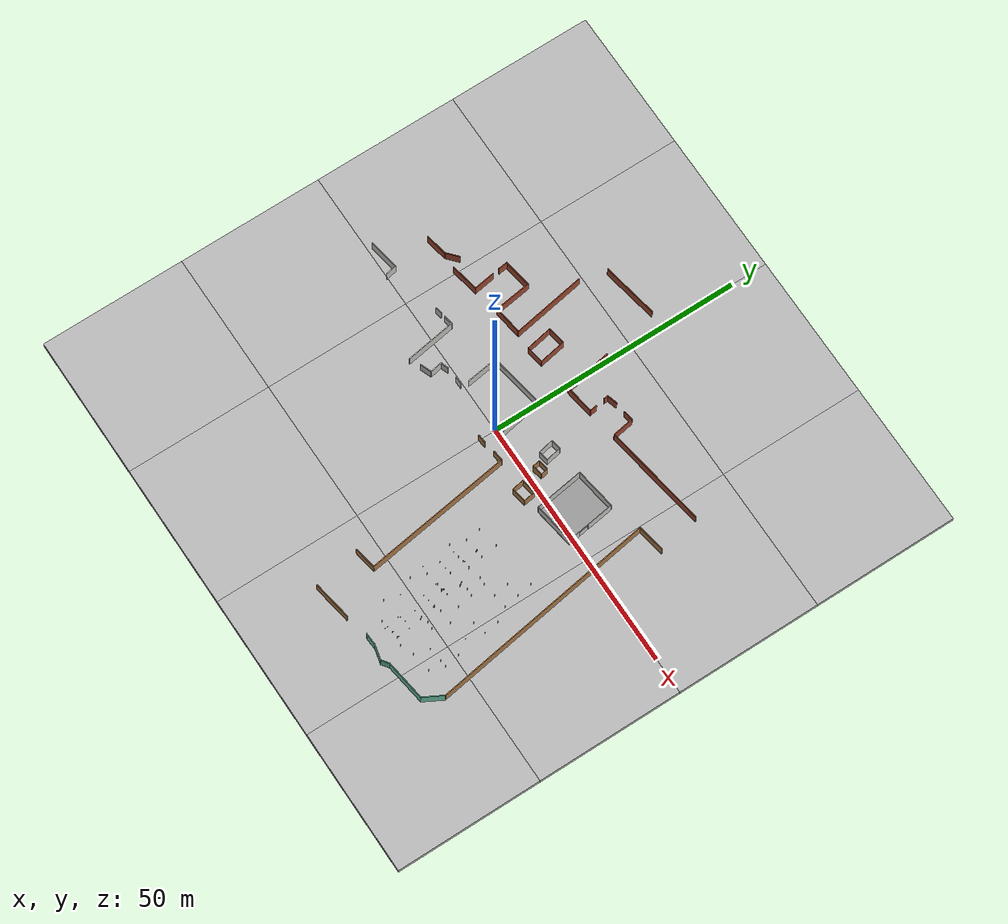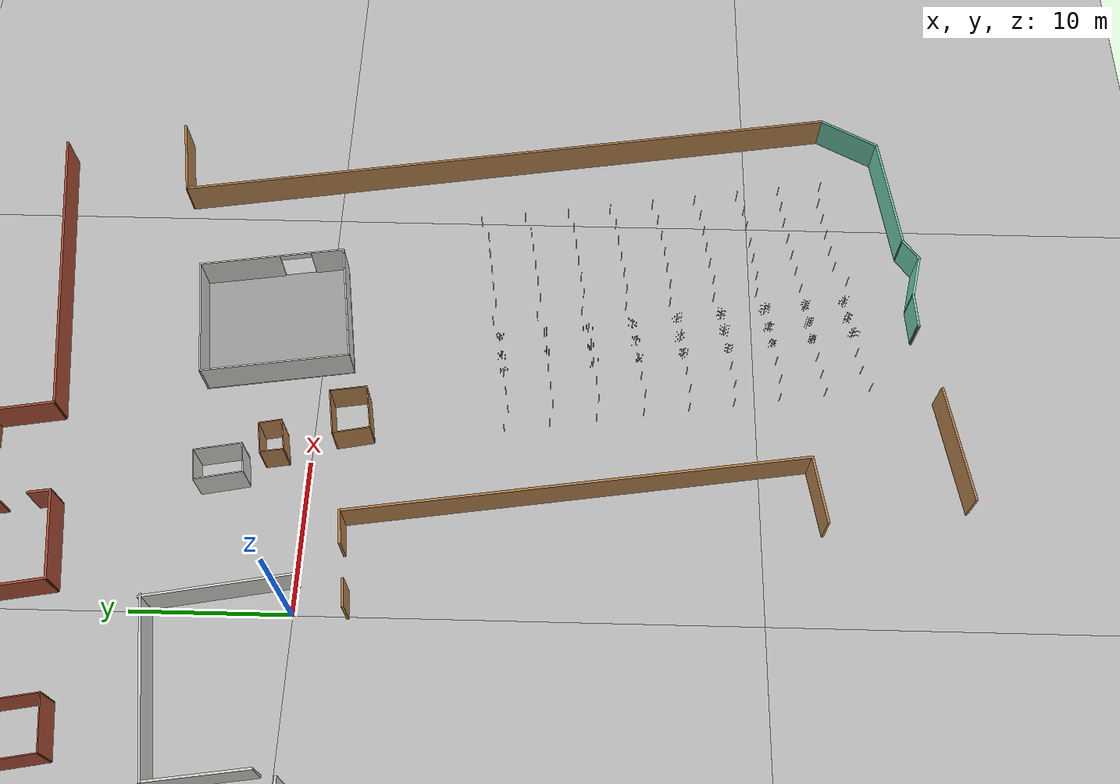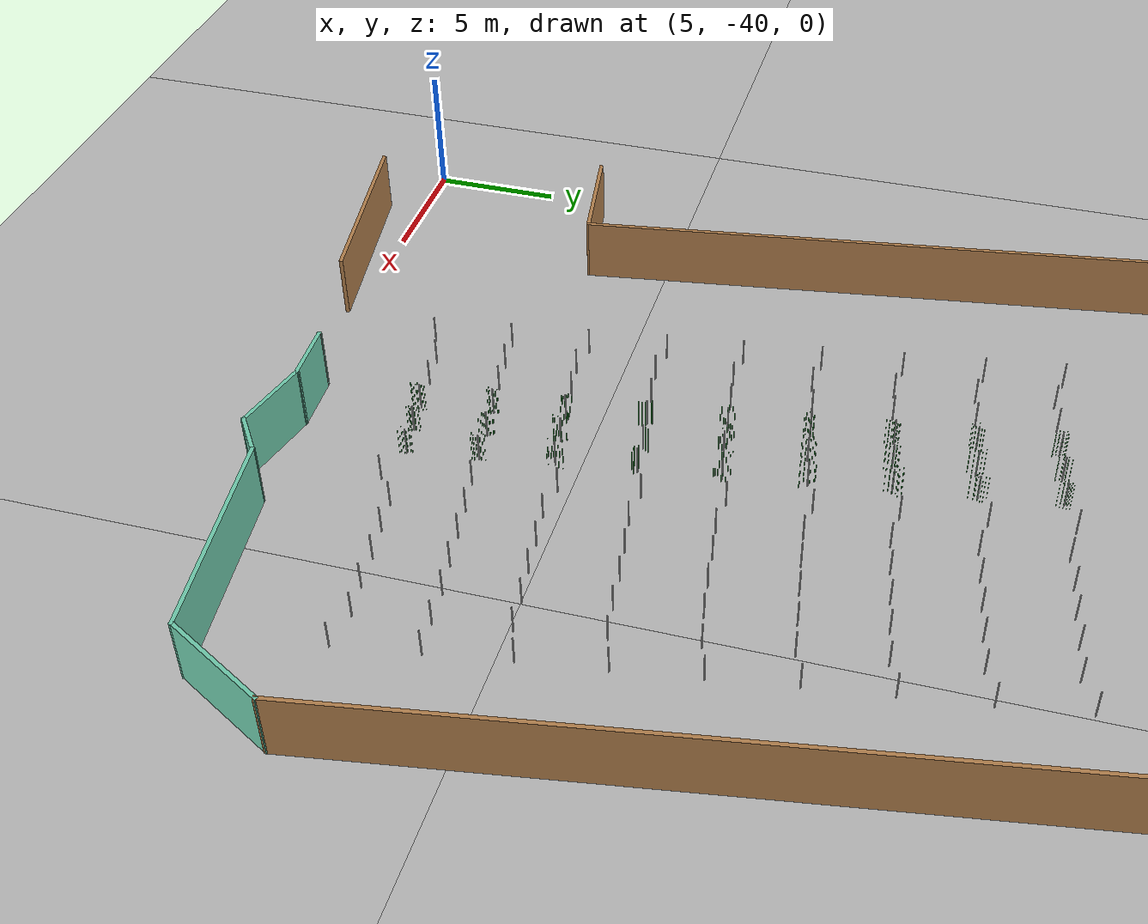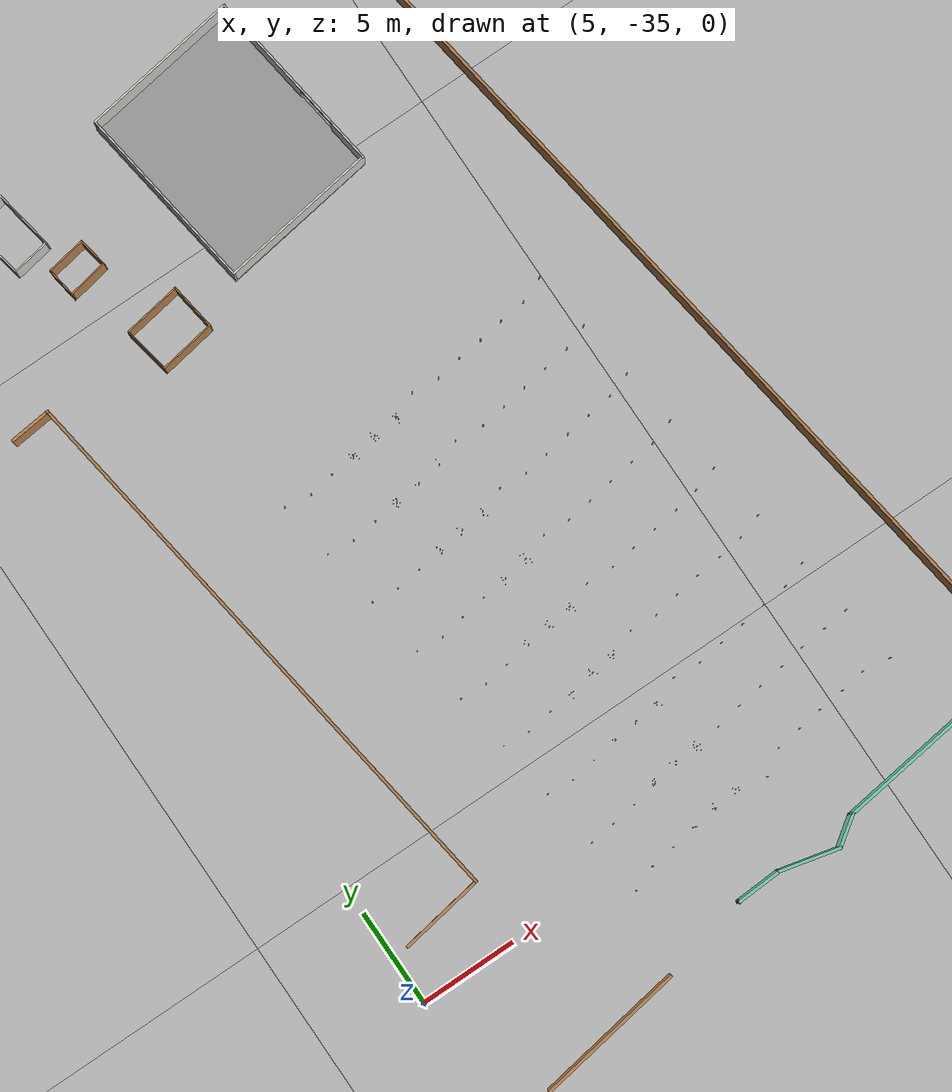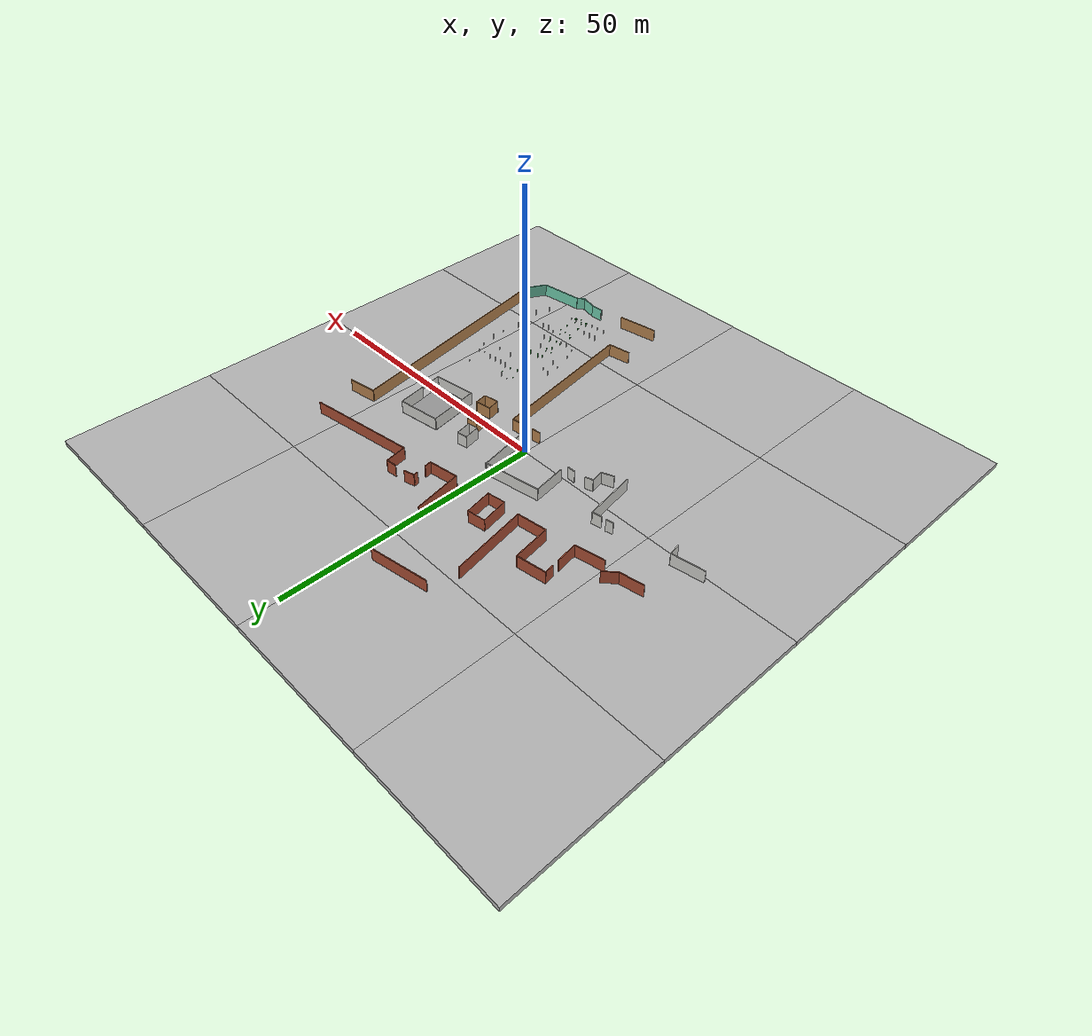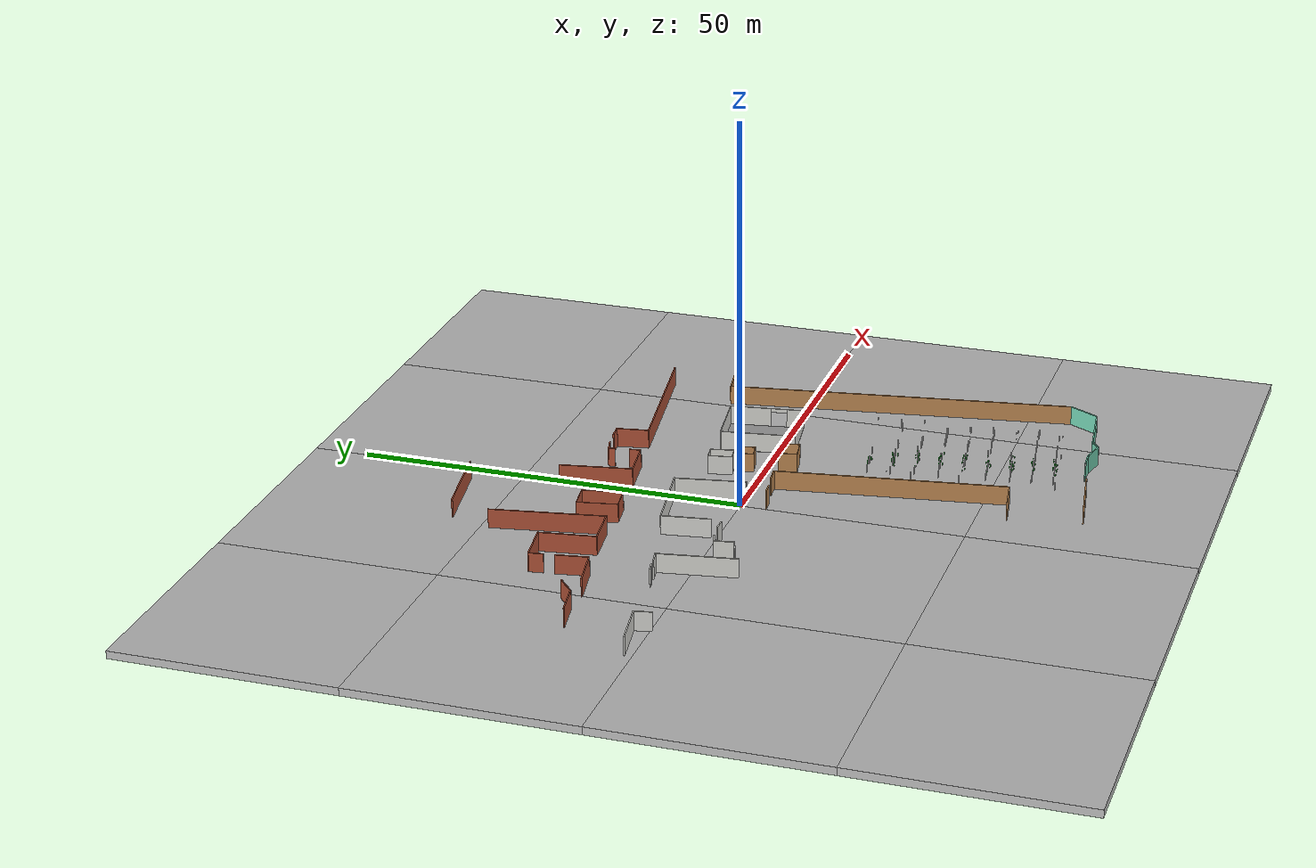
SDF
<sdf version="1.6">
 <world name="default">
  <scene>
   <shadows>1</shadows>
   <sky><clouds><speed>12</speed></clouds></sky>
   <ambient>0.4 0.4 0.4 1</ambient>
   <background>0.7 0.7 0.7 1</background>
  </scene>
  <model name="riseholme_satellite">
   <static>1</static>
   <link name="link">
    <collision name="collision">
     <pose>0 0 -0.5 0 -0 0</pose>
     <geometry><box><size>114.286 114.286 1</size></box></geometry>
    </collision>
    <visual name="visual0_0">
     <pose>-42.8571 42.8571 -0.5 0 -0 1.5708</pose>
     <geometry><box><size>28.5714 28.5714 1</size></box></geometry>
     <material>
      <script>
       <uri>model://riseholme_satellite/materials/scripts</uri>
       <uri>model://riseholme_satellite/materials/textures</uri>
       <name>riseholme_satellite/0_0</name>
      </script>
     </material>
    </visual>
    <visual name="visual0_1">
     <pose>-14.2857 42.8571 -0.5 0 -0 1.5708</pose>
     <geometry><box><size>28.5714 28.5714 1</size></box></geometry>
     <material>
      <script>
       <uri>model://riseholme_satellite/materials/scripts</uri>
       <uri>model://riseholme_satellite/materials/textures</uri>
       <name>riseholme_satellite/0_1</name>
      </script>
     </material>
    </visual>
    <visual name="visual0_2">
     <pose>14.2857 42.8571 -0.5 0 -0 1.5708</pose>
     <geometry><box><size>28.5714 28.5714 1</size></box></geometry>
     <material>
      <script>
       <uri>model://riseholme_satellite/materials/scripts</uri>
       <uri>model://riseholme_satellite/materials/textures</uri>
       <name>riseholme_satellite/0_2</name>
      </script>
     </material>
    </visual>
    <visual name="visual0_3">
     <pose>42.8571 42.8571 -0.5 0 -0 1.5708</pose>
     <geometry><box><size>28.5714 28.5714 1</size></box></geometry>
     <material>
      <script>
       <uri>model://riseholme_satellite/materials/scripts</uri>
       <uri>model://riseholme_satellite/materials/textures</uri>
       <name>riseholme_satellite/0_3</name>
      </script>
     </material>
    </visual>
    <visual name="visual1_0">
     <pose>-42.8571 14.2857 -0.5 0 -0 1.5708</pose>
     <geometry><box><size>28.5714 28.5714 1</size></box></geometry>
     <material>
      <script>
       <uri>model://riseholme_satellite/materials/scripts</uri>
       <uri>model://riseholme_satellite/materials/textures</uri>
       <name>riseholme_satellite/1_0</name>
      </script>
     </material>
    </visual>
    <visual name="visual1_1">
     <pose>-14.2857 14.2857 -0.5 0 -0 1.5708</pose>
     <geometry><box><size>28.5714 28.5714 1</size></box></geometry>
     <material>
      <script>
       <uri>model://riseholme_satellite/materials/scripts</uri>
       <uri>model://riseholme_satellite/materials/textures</uri>
       <name>riseholme_satellite/1_1</name>
      </script>
     </material>
    </visual>
    <visual name="visual1_2">
     <pose>14.2857 14.2857 -0.5 0 -0 1.5708</pose>
     <geometry><box><size>28.5714 28.5714 1</size></box></geometry>
     <material>
      <script>
       <uri>model://riseholme_satellite/materials/scripts</uri>
       <uri>model://riseholme_satellite/materials/textures</uri>
       <name>riseholme_satellite/1_2</name>
      </script>
     </material>
    </visual>
    <visual name="visual1_3">
     <pose>42.8571 14.2857 -0.5 0 -0 1.5708</pose>
     <geometry><box><size>28.5714 28.5714 1</size></box></geometry>
     <material>
      <script>
       <uri>model://riseholme_satellite/materials/scripts</uri>
       <uri>model://riseholme_satellite/materials/textures</uri>
       <name>riseholme_satellite/1_3</name>
      </script>
     </material>
    </visual>
    <visual name="visual2_0">
     <pose>-42.8571 -14.2857 -0.5 0 -0 1.5708</pose>
     <geometry><box><size>28.5714 28.5714 1</size></box></geometry>
     <material>
      <script>
       <uri>model://riseholme_satellite/materials/scripts</uri>
       <uri>model://riseholme_satellite/materials/textures</uri>
       <name>riseholme_satellite/2_0</name>
      </script>
     </material>
    </visual>
    <visual name="visual2_1">
     <pose>-14.2857 -14.2857 -0.5 0 -0 1.5708</pose>
     <geometry><box><size>28.5714 28.5714 1</size></box></geometry>
     <material>
      <script>
       <uri>model://riseholme_satellite/materials/scripts</uri>
       <uri>model://riseholme_satellite/materials/textures</uri>
       <name>riseholme_satellite/2_1</name>
      </script>
     </material>
    </visual>
    <visual name="visual2_2">
     <pose>14.2857 -14.2857 -0.5 0 -0 1.5708</pose>
     <geometry><box><size>28.5714 28.5714 1</size></box></geometry>
     <material>
      <script>
       <uri>model://riseholme_satellite/materials/scripts</uri>
       <uri>model://riseholme_satellite/materials/textures</uri>
       <name>riseholme_satellite/2_2</name>
      </script>
     </material>
    </visual>
    <visual name="visual2_3">
     <pose>42.8571 -14.2857 -0.5 0 -0 1.5708</pose>
     <geometry><box><size>28.5714 28.5714 1</size></box></geometry>
     <material>
      <script>
       <uri>model://riseholme_satellite/materials/scripts</uri>
       <uri>model://riseholme_satellite/materials/textures</uri>
       <name>riseholme_satellite/2_3</name>
      </script>
     </material>
    </visual>
    <visual name="visual3_0">
     <pose>-42.8571 -42.8571 -0.5 0 -0 1.5708</pose>
     <geometry><box><size>28.5714 28.5714 1</size></box></geometry>
     <material>
      <script>
       <uri>model://riseholme_satellite/materials/scripts</uri>
       <uri>model://riseholme_satellite/materials/textures</uri>
       <name>riseholme_satellite/3_0</name>
      </script>
     </material>
    </visual>
    <visual name="visual3_1">
     <pose>-14.2857 -42.8571 -0.5 0 -0 1.5708</pose>
     <geometry><box><size>28.5714 28.5714 1</size></box></geometry>
     <material>
      <script>
       <uri>model://riseholme_satellite/materials/scripts</uri>
       <uri>model://riseholme_satellite/materials/textures</uri>
       <name>riseholme_satellite/3_1</name>
      </script>
     </material>
    </visual>
    <visual name="visual3_2">
     <pose>14.2857 -42.8571 -0.5 0 -0 1.5708</pose>
     <geometry><box><size>28.5714 28.5714 1</size></box></geometry>
     <material>
      <script>
       <uri>model://riseholme_satellite/materials/scripts</uri>
       <uri>model://riseholme_satellite/materials/textures</uri>
       <name>riseholme_satellite/3_2</name>
      </script>
     </material>
    </visual>
    <visual name="visual3_3">
     <pose>42.8571 -42.8571 -0.5 0 -0 1.5708</pose>
     <geometry><box><size>28.5714 28.5714 1</size></box></geometry>
     <material>
      <script>
       <uri>model://riseholme_satellite/materials/scripts</uri>
       <uri>model://riseholme_satellite/materials/textures</uri>
       <name>riseholme_satellite/3_3</name>
      </script>
     </material>
    </visual>
   </link>
  </model>
  <model name="pole_0">
   <static>1</static>
   <pose>20.47 -11.17 0.575 0 -0 0</pose>
   <link name="link">
    <collision name="collision">
     <geometry><cylinder><length>1.15</length><radius>0.025</radius></cylinder></geometry>
    </collision>
    <visual name="visual">
     <geometry><cylinder><length>1.15</length><radius>0.025</radius></cylinder></geometry>
     <material>
      <script><uri>file://media/materials/scripts/gazebo.material</uri><name>Gazebo/Chrome</name></script>
      <shader type="vertex"><normal_map>__default__</normal_map></shader>
      <emissive>0.1 0.1 0.1 1</emissive>
      <specular>0.01 0.01 0.01 1</specular>
      <ambient>0.5 0.5 0.5 1</ambient>
      <diffuse>0.05 0.05 0.05 1</diffuse>
     </material>
    </visual>
   </link>
  </model>
  <model name="pole_1">
   <static>1</static>
   <pose>20.89 -14.15 0.575 0 -0 0</pose>
   <link name="link">
    <collision name="collision">
     <geometry><cylinder><length>1.15</length><radius>0.025</radius></cylinder></geometry>
    </collision>
    <visual name="visual">
     <geometry><cylinder><length>1.15</length><radius>0.025</radius></cylinder></geometry>
     <material>
      <script><uri>file://media/materials/scripts/gazebo.material</uri><name>Gazebo/Chrome</name></script>
      <shader type="vertex"><normal_map>__default__</normal_map></shader>
      <emissive>0.1 0.1 0.1 1</emissive>
      <specular>0.01 0.01 0.01 1</specular>
      <ambient>0.5 0.5 0.5 1</ambient>
      <diffuse>0.05 0.05 0.05 1</diffuse>
     </material>
    </visual>
   </link>
  </model>
  <model name="pole_2">
   <static>1</static>
   <pose>21.37 -17.15 0.575 0 -0 0</pose>
   <link name="link">
    <collision name="collision">
     <geometry><cylinder><length>1.15</length><radius>0.025</radius></cylinder></geometry>
    </collision>
    <visual name="visual">
     <geometry><cylinder><length>1.15</length><radius>0.025</radius></cylinder></geometry>
     <material>
      <script><uri>file://media/materials/scripts/gazebo.material</uri><name>Gazebo/Chrome</name></script>
      <shader type="vertex"><normal_map>__default__</normal_map></shader>
      <emissive>0.1 0.1 0.1 1</emissive>
      <specular>0.01 0.01 0.01 1</specular>
      <ambient>0.5 0.5 0.5 1</ambient>
      <diffuse>0.05 0.05 0.05 1</diffuse>
     </material>
    </visual>
   </link>
  </model>
  <model name="pole_3">
   <static>1</static>
   <pose>21.82 -20.12 0.575 0 -0 0</pose>
   <link name="link">
    <collision name="collision">
     <geometry><cylinder><length>1.15</length><radius>0.025</radius></cylinder></geometry>
    </collision>
    <visual name="visual">
     <geometry><cylinder><length>1.15</length><radius>0.025</radius></cylinder></geometry>
     <material>
      <script><uri>file://media/materials/scripts/gazebo.material</uri><name>Gazebo/Chrome</name></script>
      <shader type="vertex"><normal_map>__default__</normal_map></shader>
      <emissive>0.1 0.1 0.1 1</emissive>
      <specular>0.01 0.01 0.01 1</specular>
      <ambient>0.5 0.5 0.5 1</ambient>
      <diffuse>0.05 0.05 0.05 1</diffuse>
     </material>
    </visual>
   </link>
  </model>
  <model name="pole_4">
   <static>1</static>
   <pose>22.22 -23.11 0.575 0 -0 0</pose>
   <link name="link">
    <collision name="collision">
     <geometry><cylinder><length>1.15</length><radius>0.025</radius></cylinder></geometry>
    </collision>
    <visual name="visual">
     <geometry><cylinder><length>1.15</length><radius>0.025</radius></cylinder></geometry>
     <material>
      <script><uri>file://media/materials/scripts/gazebo.material</uri><name>Gazebo/Chrome</name></script>
      <shader type="vertex"><normal_map>__default__</normal_map></shader>
      <emissive>0.1 0.1 0.1 1</emissive>
      <specular>0.01 0.01 0.01 1</specular>
      <ambient>0.5 0.5 0.5 1</ambient>
      <diffuse>0.05 0.05 0.05 1</diffuse>
     </material>
    </visual>
   </link>
  </model>
  <model name="pole_5">
   <static>1</static>
   <pose>22.65 -26.08 0.575 0 -0 0</pose>
   <link name="link">
    <collision name="collision">
     <geometry><cylinder><length>1.15</length><radius>0.025</radius></cylinder></geometry>
    </collision>
    <visual name="visual">
     <geometry><cylinder><length>1.15</length><radius>0.025</radius></cylinder></geometry>
     <material>
      <script><uri>file://media/materials/scripts/gazebo.material</uri><name>Gazebo/Chrome</name></script>
      <shader type="vertex"><normal_map>__default__</normal_map></shader>
      <emissive>0.1 0.1 0.1 1</emissive>
      <specular>0.01 0.01 0.01 1</specular>
      <ambient>0.5 0.5 0.5 1</ambient>
      <diffuse>0.05 0.05 0.05 1</diffuse>
     </material>
    </visual>
   </link>
  </model>
  <model name="pole_6">
   <static>1</static>
   <pose>23.1 -29.01 0.575 0 -0 0</pose>
   <link name="link">
    <collision name="collision">
     <geometry><cylinder><length>1.15</length><radius>0.025</radius></cylinder></geometry>
    </collision>
    <visual name="visual">
     <geometry><cylinder><length>1.15</length><radius>0.025</radius></cylinder></geometry>
     <material>
      <script><uri>file://media/materials/scripts/gazebo.material</uri><name>Gazebo/Chrome</name></script>
      <shader type="vertex"><normal_map>__default__</normal_map></shader>
      <emissive>0.1 0.1 0.1 1</emissive>
      <specular>0.01 0.01 0.01 1</specular>
      <ambient>0.5 0.5 0.5 1</ambient>
      <diffuse>0.05 0.05 0.05 1</diffuse>
     </material>
    </visual>
   </link>
  </model>
  <model name="pole_7">
   <static>1</static>
   <pose>23.53 -32.05 0.575 0 -0 0</pose>
   <link name="link">
    <collision name="collision">
     <geometry><cylinder><length>1.15</length><radius>0.025</radius></cylinder></geometry>
    </collision>
    <visual name="visual">
     <geometry><cylinder><length>1.15</length><radius>0.025</radius></cylinder></geometry>
     <material>
      <script><uri>file://media/materials/scripts/gazebo.material</uri><name>Gazebo/Chrome</name></script>
      <shader type="vertex"><normal_map>__default__</normal_map></shader>
      <emissive>0.1 0.1 0.1 1</emissive>
      <specular>0.01 0.01 0.01 1</specular>
      <ambient>0.5 0.5 0.5 1</ambient>
      <diffuse>0.05 0.05 0.05 1</diffuse>
     </material>
    </visual>
   </link>
  </model>
  <model name="pole_8">
   <static>1</static>
   <pose>24.12 -35.26 0.575 0 -0 0</pose>
   <link name="link">
    <collision name="collision">
     <geometry><cylinder><length>1.15</length><radius>0.025</radius></cylinder></geometry>
    </collision>
    <visual name="visual">
     <geometry><cylinder><length>1.15</length><radius>0.025</radius></cylinder></geometry>
     <material>
      <script><uri>file://media/materials/scripts/gazebo.material</uri><name>Gazebo/Chrome</name></script>
      <shader type="vertex"><normal_map>__default__</normal_map></shader>
      <emissive>0.1 0.1 0.1 1</emissive>
      <specular>0.01 0.01 0.01 1</specular>
      <ambient>0.5 0.5 0.5 1</ambient>
      <diffuse>0.05 0.05 0.05 1</diffuse>
     </material>
    </visual>
   </link>
  </model>
  <model name="pole_9">
   <static>1</static>
   <pose>19.19 -11.68 0.575 0 -0 0</pose>
   <link name="link">
    <collision name="collision">
     <geometry><cylinder><length>1.15</length><radius>0.025</radius></cylinder></geometry>
    </collision>
    <visual name="visual">
     <geometry><cylinder><length>1.15</length><radius>0.025</radius></cylinder></geometry>
     <material>
      <script><uri>file://media/materials/scripts/gazebo.material</uri><name>Gazebo/Chrome</name></script>
      <shader type="vertex"><normal_map>__default__</normal_map></shader>
      <emissive>0.1 0.1 0.1 1</emissive>
      <specular>0.01 0.01 0.01 1</specular>
      <ambient>0.5 0.5 0.5 1</ambient>
      <diffuse>0.05 0.05 0.05 1</diffuse>
     </material>
    </visual>
   </link>
  </model>
  <model name="pole_10">
   <static>1</static>
   <pose>19.65 -14.65 0.575 0 -0 0</pose>
   <link name="link">
    <collision name="collision">
     <geometry><cylinder><length>1.15</length><radius>0.025</radius></cylinder></geometry>
    </collision>
    <visual name="visual">
     <geometry><cylinder><length>1.15</length><radius>0.025</radius></cylinder></geometry>
     <material>
      <script><uri>file://media/materials/scripts/gazebo.material</uri><name>Gazebo/Chrome</name></script>
      <shader type="vertex"><normal_map>__default__</normal_map></shader>
      <emissive>0.1 0.1 0.1 1</emissive>
      <specular>0.01 0.01 0.01 1</specular>
      <ambient>0.5 0.5 0.5 1</ambient>
      <diffuse>0.05 0.05 0.05 1</diffuse>
     </material>
    </visual>
   </link>
  </model>
  <model name="pole_11">
   <static>1</static>
   <pose>20.08 -17.6 0.575 0 -0 0</pose>
   <link name="link">
    <collision name="collision">
     <geometry><cylinder><length>1.15</length><radius>0.025</radius></cylinder></geometry>
    </collision>
    <visual name="visual">
     <geometry><cylinder><length>1.15</length><radius>0.025</radius></cylinder></geometry>
     <material>
      <script><uri>file://media/materials/scripts/gazebo.material</uri><name>Gazebo/Chrome</name></script>
      <shader type="vertex"><normal_map>__default__</normal_map></shader>
      <emissive>0.1 0.1 0.1 1</emissive>
      <specular>0.01 0.01 0.01 1</specular>
      <ambient>0.5 0.5 0.5 1</ambient>
      <diffuse>0.05 0.05 0.05 1</diffuse>
     </material>
    </visual>
   </link>
  </model>
  <model name="pole_12">
   <static>1</static>
   <pose>20.5 -20.55 0.575 0 -0 0</pose>
   <link name="link">
    <collision name="collision">
     <geometry><cylinder><length>1.15</length><radius>0.025</radius></cylinder></geometry>
    </collision>
    <visual name="visual">
     <geometry><cylinder><length>1.15</length><radius>0.025</radius></cylinder></geometry>
     <material>
      <script><uri>file://media/materials/scripts/gazebo.material</uri><name>Gazebo/Chrome</name></script>
      <shader type="vertex"><normal_map>__default__</normal_map></shader>
      <emissive>0.1 0.1 0.1 1</emissive>
      <specular>0.01 0.01 0.01 1</specular>
      <ambient>0.5 0.5 0.5 1</ambient>
      <diffuse>0.05 0.05 0.05 1</diffuse>
     </material>
    </visual>
   </link>
  </model>
  <model name="pole_13">
   <static>1</static>
   <pose>20.95 -23.55 0.575 0 -0 0</pose>
   <link name="link">
    <collision name="collision">
     <geometry><cylinder><length>1.15</length><radius>0.025</radius></cylinder></geometry>
    </collision>
    <visual name="visual">
     <geometry><cylinder><length>1.15</length><radius>0.025</radius></cylinder></geometry>
     <material>
      <script><uri>file://media/materials/scripts/gazebo.material</uri><name>Gazebo/Chrome</name></script>
      <shader type="vertex"><normal_map>__default__</normal_map></shader>
      <emissive>0.1 0.1 0.1 1</emissive>
      <specular>0.01 0.01 0.01 1</specular>
      <ambient>0.5 0.5 0.5 1</ambient>
      <diffuse>0.05 0.05 0.05 1</diffuse>
     </material>
    </visual>
   </link>
  </model>
  <model name="pole_14">
   <static>1</static>
   <pose>21.37 -26.55 0.575 0 -0 0</pose>
   <link name="link">
    <collision name="collision">
     <geometry><cylinder><length>1.15</length><radius>0.025</radius></cylinder></geometry>
    </collision>
    <visual name="visual">
     <geometry><cylinder><length>1.15</length><radius>0.025</radius></cylinder></geometry>
     <material>
      <script><uri>file://media/materials/scripts/gazebo.material</uri><name>Gazebo/Chrome</name></script>
      <shader type="vertex"><normal_map>__default__</normal_map></shader>
      <emissive>0.1 0.1 0.1 1</emissive>
      <specular>0.01 0.01 0.01 1</specular>
      <ambient>0.5 0.5 0.5 1</ambient>
      <diffuse>0.05 0.05 0.05 1</diffuse>
     </material>
    </visual>
   </link>
  </model>
  <model name="pole_15">
   <static>1</static>
   <pose>21.8 -29.5 0.575 0 -0 0</pose>
   <link name="link">
    <collision name="collision">
     <geometry><cylinder><length>1.15</length><radius>0.025</radius></cylinder></geometry>
    </collision>
    <visual name="visual">
     <geometry><cylinder><length>1.15</length><radius>0.025</radius></cylinder></geometry>
     <material>
      <script><uri>file://media/materials/scripts/gazebo.material</uri><name>Gazebo/Chrome</name></script>
      <shader type="vertex"><normal_map>__default__</normal_map></shader>
      <emissive>0.1 0.1 0.1 1</emissive>
      <specular>0.01 0.01 0.01 1</specular>
      <ambient>0.5 0.5 0.5 1</ambient>
      <diffuse>0.05 0.05 0.05 1</diffuse>
     </material>
    </visual>
   </link>
  </model>
  <model name="pole_16">
   <static>1</static>
   <pose>22.2 -32.25 0.575 0 -0 0</pose>
   <link name="link">
    <collision name="collision">
     <geometry><cylinder><length>1.15</length><radius>0.025</radius></cylinder></geometry>
    </collision>
    <visual name="visual">
     <geometry><cylinder><length>1.15</length><radius>0.025</radius></cylinder></geometry>
     <material>
      <script><uri>file://media/materials/scripts/gazebo.material</uri><name>Gazebo/Chrome</name></script>
      <shader type="vertex"><normal_map>__default__</normal_map></shader>
      <emissive>0.1 0.1 0.1 1</emissive>
      <specular>0.01 0.01 0.01 1</specular>
      <ambient>0.5 0.5 0.5 1</ambient>
      <diffuse>0.05 0.05 0.05 1</diffuse>
     </material>
    </visual>
   </link>
  </model>
  <model name="pole_17">
   <static>1</static>
   <pose>22.55 -34.9 0.575 0 -0 0</pose>
   <link name="link">
    <collision name="collision">
     <geometry><cylinder><length>1.15</length><radius>0.025</radius></cylinder></geometry>
    </collision>
    <visual name="visual">
     <geometry><cylinder><length>1.15</length><radius>0.025</radius></cylinder></geometry>
     <material>
      <script><uri>file://media/materials/scripts/gazebo.material</uri><name>Gazebo/Chrome</name></script>
      <shader type="vertex"><normal_map>__default__</normal_map></shader>
      <emissive>0.1 0.1 0.1 1</emissive>
      <specular>0.01 0.01 0.01 1</specular>
      <ambient>0.5 0.5 0.5 1</ambient>
      <diffuse>0.05 0.05 0.05 1</diffuse>
     </material>
    </visual>
   </link>
  </model>
  <model name="pole_18">
   <static>1</static>
   <pose>17.9 -11.85 0.575 0 -0 0</pose>
   <link name="link">
    <collision name="collision">
     <geometry><cylinder><length>1.15</length><radius>0.025</radius></cylinder></geometry>
    </collision>
    <visual name="visual">
     <geometry><cylinder><length>1.15</length><radius>0.025</radius></cylinder></geometry>
     <material>
      <script><uri>file://media/materials/scripts/gazebo.material</uri><name>Gazebo/Chrome</name></script>
      <shader type="vertex"><normal_map>__default__</normal_map></shader>
      <emissive>0.1 0.1 0.1 1</emissive>
      <specular>0.01 0.01 0.01 1</specular>
      <ambient>0.5 0.5 0.5 1</ambient>
      <diffuse>0.05 0.05 0.05 1</diffuse>
     </material>
    </visual>
   </link>
  </model>
  <model name="pole_19">
   <static>1</static>
   <pose>18.34 -14.85 0.575 0 -0 0</pose>
   <link name="link">
    <collision name="collision">
     <geometry><cylinder><length>1.15</length><radius>0.025</radius></cylinder></geometry>
    </collision>
    <visual name="visual">
     <geometry><cylinder><length>1.15</length><radius>0.025</radius></cylinder></geometry>
     <material>
      <script><uri>file://media/materials/scripts/gazebo.material</uri><name>Gazebo/Chrome</name></script>
      <shader type="vertex"><normal_map>__default__</normal_map></shader>
      <emissive>0.1 0.1 0.1 1</emissive>
      <specular>0.01 0.01 0.01 1</specular>
      <ambient>0.5 0.5 0.5 1</ambient>
      <diffuse>0.05 0.05 0.05 1</diffuse>
     </material>
    </visual>
   </link>
  </model>
  <model name="pole_20">
   <static>1</static>
   <pose>18.8 -17.8 0.575 0 -0 0</pose>
   <link name="link">
    <collision name="collision">
     <geometry><cylinder><length>1.15</length><radius>0.025</radius></cylinder></geometry>
    </collision>
    <visual name="visual">
     <geometry><cylinder><length>1.15</length><radius>0.025</radius></cylinder></geometry>
     <material>
      <script><uri>file://media/materials/scripts/gazebo.material</uri><name>Gazebo/Chrome</name></script>
      <shader type="vertex"><normal_map>__default__</normal_map></shader>
      <emissive>0.1 0.1 0.1 1</emissive>
      <specular>0.01 0.01 0.01 1</specular>
      <ambient>0.5 0.5 0.5 1</ambient>
      <diffuse>0.05 0.05 0.05 1</diffuse>
     </material>
    </visual>
   </link>
  </model>
  <model name="pole_21">
   <static>1</static>
   <pose>19.2 -20.8 0.575 0 -0 0</pose>
   <link name="link">
    <collision name="collision">
     <geometry><cylinder><length>1.15</length><radius>0.025</radius></cylinder></geometry>
    </collision>
    <visual name="visual">
     <geometry><cylinder><length>1.15</length><radius>0.025</radius></cylinder></geometry>
     <material>
      <script><uri>file://media/materials/scripts/gazebo.material</uri><name>Gazebo/Chrome</name></script>
      <shader type="vertex"><normal_map>__default__</normal_map></shader>
      <emissive>0.1 0.1 0.1 1</emissive>
      <specular>0.01 0.01 0.01 1</specular>
      <ambient>0.5 0.5 0.5 1</ambient>
      <diffuse>0.05 0.05 0.05 1</diffuse>
     </material>
    </visual>
   </link>
  </model>
  <model name="pole_22">
   <static>1</static>
   <pose>19.65 -23.79 0.575 0 -0 0</pose>
   <link name="link">
    <collision name="collision">
     <geometry><cylinder><length>1.15</length><radius>0.025</radius></cylinder></geometry>
    </collision>
    <visual name="visual">
     <geometry><cylinder><length>1.15</length><radius>0.025</radius></cylinder></geometry>
     <material>
      <script><uri>file://media/materials/scripts/gazebo.material</uri><name>Gazebo/Chrome</name></script>
      <shader type="vertex"><normal_map>__default__</normal_map></shader>
      <emissive>0.1 0.1 0.1 1</emissive>
      <specular>0.01 0.01 0.01 1</specular>
      <ambient>0.5 0.5 0.5 1</ambient>
      <diffuse>0.05 0.05 0.05 1</diffuse>
     </material>
    </visual>
   </link>
  </model>
  <model name="pole_23">
   <static>1</static>
   <pose>20.1 -26.7 0.575 0 -0 0</pose>
   <link name="link">
    <collision name="collision">
     <geometry><cylinder><length>1.15</length><radius>0.025</radius></cylinder></geometry>
    </collision>
    <visual name="visual">
     <geometry><cylinder><length>1.15</length><radius>0.025</radius></cylinder></geometry>
     <material>
      <script><uri>file://media/materials/scripts/gazebo.material</uri><name>Gazebo/Chrome</name></script>
      <shader type="vertex"><normal_map>__default__</normal_map></shader>
      <emissive>0.1 0.1 0.1 1</emissive>
      <specular>0.01 0.01 0.01 1</specular>
      <ambient>0.5 0.5 0.5 1</ambient>
      <diffuse>0.05 0.05 0.05 1</diffuse>
     </material>
    </visual>
   </link>
  </model>
  <model name="pole_24">
   <static>1</static>
   <pose>20.5 -29.7 0.575 0 -0 0</pose>
   <link name="link">
    <collision name="collision">
     <geometry><cylinder><length>1.15</length><radius>0.025</radius></cylinder></geometry>
    </collision>
    <visual name="visual">
     <geometry><cylinder><length>1.15</length><radius>0.025</radius></cylinder></geometry>
     <material>
      <script><uri>file://media/materials/scripts/gazebo.material</uri><name>Gazebo/Chrome</name></script>
      <shader type="vertex"><normal_map>__default__</normal_map></shader>
      <emissive>0.1 0.1 0.1 1</emissive>
      <specular>0.01 0.01 0.01 1</specular>
      <ambient>0.5 0.5 0.5 1</ambient>
      <diffuse>0.05 0.05 0.05 1</diffuse>
     </material>
    </visual>
   </link>
  </model>
  <model name="pole_25">
   <static>1</static>
   <pose>20.9 -32.4 0.575 0 -0 0</pose>
   <link name="link">
    <collision name="collision">
     <geometry><cylinder><length>1.15</length><radius>0.025</radius></cylinder></geometry>
    </collision>
    <visual name="visual">
     <geometry><cylinder><length>1.15</length><radius>0.025</radius></cylinder></geometry>
     <material>
      <script><uri>file://media/materials/scripts/gazebo.material</uri><name>Gazebo/Chrome</name></script>
      <shader type="vertex"><normal_map>__default__</normal_map></shader>
      <emissive>0.1 0.1 0.1 1</emissive>
      <specular>0.01 0.01 0.01 1</specular>
      <ambient>0.5 0.5 0.5 1</ambient>
      <diffuse>0.05 0.05 0.05 1</diffuse>
     </material>
    </visual>
   </link>
  </model>
  <model name="pole_26">
   <static>1</static>
   <pose>21.3 -35.1 0.575 0 -0 0</pose>
   <link name="link">
    <collision name="collision">
     <geometry><cylinder><length>1.15</length><radius>0.025</radius></cylinder></geometry>
    </collision>
    <visual name="visual">
     <geometry><cylinder><length>1.15</length><radius>0.025</radius></cylinder></geometry>
     <material>
      <script><uri>file://media/materials/scripts/gazebo.material</uri><name>Gazebo/Chrome</name></script>
      <shader type="vertex"><normal_map>__default__</normal_map></shader>
      <emissive>0.1 0.1 0.1 1</emissive>
      <specular>0.01 0.01 0.01 1</specular>
      <ambient>0.5 0.5 0.5 1</ambient>
      <diffuse>0.05 0.05 0.05 1</diffuse>
     </material>
    </visual>
   </link>
  </model>
  <model name="pole_27">
   <static>1</static>
   <pose>16.54 -12.05 0.575 0 -0 0</pose>
   <link name="link">
    <collision name="collision">
     <geometry><cylinder><length>1.15</length><radius>0.025</radius></cylinder></geometry>
    </collision>
    <visual name="visual">
     <geometry><cylinder><length>1.15</length><radius>0.025</radius></cylinder></geometry>
     <material>
      <script><uri>file://media/materials/scripts/gazebo.material</uri><name>Gazebo/Chrome</name></script>
      <shader type="vertex"><normal_map>__default__</normal_map></shader>
      <emissive>0.1 0.1 0.1 1</emissive>
      <specular>0.01 0.01 0.01 1</specular>
      <ambient>0.5 0.5 0.5 1</ambient>
      <diffuse>0.05 0.05 0.05 1</diffuse>
     </material>
    </visual>
   </link>
  </model>
  <model name="pole_28">
   <static>1</static>
   <pose>17 -15 0.575 0 -0 0</pose>
   <link name="link">
    <collision name="collision">
     <geometry><cylinder><length>1.15</length><radius>0.025</radius></cylinder></geometry>
    </collision>
    <visual name="visual">
     <geometry><cylinder><length>1.15</length><radius>0.025</radius></cylinder></geometry>
     <material>
      <script><uri>file://media/materials/scripts/gazebo.material</uri><name>Gazebo/Chrome</name></script>
      <shader type="vertex"><normal_map>__default__</normal_map></shader>
      <emissive>0.1 0.1 0.1 1</emissive>
      <specular>0.01 0.01 0.01 1</specular>
      <ambient>0.5 0.5 0.5 1</ambient>
      <diffuse>0.05 0.05 0.05 1</diffuse>
     </material>
    </visual>
   </link>
  </model>
  <model name="pole_29">
   <static>1</static>
   <pose>17.45 -17.95 0.575 0 -0 0</pose>
   <link name="link">
    <collision name="collision">
     <geometry><cylinder><length>1.15</length><radius>0.025</radius></cylinder></geometry>
    </collision>
    <visual name="visual">
     <geometry><cylinder><length>1.15</length><radius>0.025</radius></cylinder></geometry>
     <material>
      <script><uri>file://media/materials/scripts/gazebo.material</uri><name>Gazebo/Chrome</name></script>
      <shader type="vertex"><normal_map>__default__</normal_map></shader>
      <emissive>0.1 0.1 0.1 1</emissive>
      <specular>0.01 0.01 0.01 1</specular>
      <ambient>0.5 0.5 0.5 1</ambient>
      <diffuse>0.05 0.05 0.05 1</diffuse>
     </material>
    </visual>
   </link>
  </model>
  <model name="pole_30">
   <static>1</static>
   <pose>17.87 -20.96 0.575 0 -0 0</pose>
   <link name="link">
    <collision name="collision">
     <geometry><cylinder><length>1.15</length><radius>0.025</radius></cylinder></geometry>
    </collision>
    <visual name="visual">
     <geometry><cylinder><length>1.15</length><radius>0.025</radius></cylinder></geometry>
     <material>
      <script><uri>file://media/materials/scripts/gazebo.material</uri><name>Gazebo/Chrome</name></script>
      <shader type="vertex"><normal_map>__default__</normal_map></shader>
      <emissive>0.1 0.1 0.1 1</emissive>
      <specular>0.01 0.01 0.01 1</specular>
      <ambient>0.5 0.5 0.5 1</ambient>
      <diffuse>0.05 0.05 0.05 1</diffuse>
     </material>
    </visual>
   </link>
  </model>
  <model name="pole_31">
   <static>1</static>
   <pose>18.35 -23.95 0.575 0 -0 0</pose>
   <link name="link">
    <collision name="collision">
     <geometry><cylinder><length>1.15</length><radius>0.025</radius></cylinder></geometry>
    </collision>
    <visual name="visual">
     <geometry><cylinder><length>1.15</length><radius>0.025</radius></cylinder></geometry>
     <material>
      <script><uri>file://media/materials/scripts/gazebo.material</uri><name>Gazebo/Chrome</name></script>
      <shader type="vertex"><normal_map>__default__</normal_map></shader>
      <emissive>0.1 0.1 0.1 1</emissive>
      <specular>0.01 0.01 0.01 1</specular>
      <ambient>0.5 0.5 0.5 1</ambient>
      <diffuse>0.05 0.05 0.05 1</diffuse>
     </material>
    </visual>
   </link>
  </model>
  <model name="pole_32">
   <static>1</static>
   <pose>18.75 -26.92 0.575 0 -0 0</pose>
   <link name="link">
    <collision name="collision">
     <geometry><cylinder><length>1.15</length><radius>0.025</radius></cylinder></geometry>
    </collision>
    <visual name="visual">
     <geometry><cylinder><length>1.15</length><radius>0.025</radius></cylinder></geometry>
     <material>
      <script><uri>file://media/materials/scripts/gazebo.material</uri><name>Gazebo/Chrome</name></script>
      <shader type="vertex"><normal_map>__default__</normal_map></shader>
      <emissive>0.1 0.1 0.1 1</emissive>
      <specular>0.01 0.01 0.01 1</specular>
      <ambient>0.5 0.5 0.5 1</ambient>
      <diffuse>0.05 0.05 0.05 1</diffuse>
     </material>
    </visual>
   </link>
  </model>
  <model name="pole_33">
   <static>1</static>
   <pose>19.2 -29.9 0.575 0 -0 0</pose>
   <link name="link">
    <collision name="collision">
     <geometry><cylinder><length>1.15</length><radius>0.025</radius></cylinder></geometry>
    </collision>
    <visual name="visual">
     <geometry><cylinder><length>1.15</length><radius>0.025</radius></cylinder></geometry>
     <material>
      <script><uri>file://media/materials/scripts/gazebo.material</uri><name>Gazebo/Chrome</name></script>
      <shader type="vertex"><normal_map>__default__</normal_map></shader>
      <emissive>0.1 0.1 0.1 1</emissive>
      <specular>0.01 0.01 0.01 1</specular>
      <ambient>0.5 0.5 0.5 1</ambient>
      <diffuse>0.05 0.05 0.05 1</diffuse>
     </material>
    </visual>
   </link>
  </model>
  <model name="pole_34">
   <static>1</static>
   <pose>19.6 -32.6 0.575 0 -0 0</pose>
   <link name="link">
    <collision name="collision">
     <geometry><cylinder><length>1.15</length><radius>0.025</radius></cylinder></geometry>
    </collision>
    <visual name="visual">
     <geometry><cylinder><length>1.15</length><radius>0.025</radius></cylinder></geometry>
     <material>
      <script><uri>file://media/materials/scripts/gazebo.material</uri><name>Gazebo/Chrome</name></script>
      <shader type="vertex"><normal_map>__default__</normal_map></shader>
      <emissive>0.1 0.1 0.1 1</emissive>
      <specular>0.01 0.01 0.01 1</specular>
      <ambient>0.5 0.5 0.5 1</ambient>
      <diffuse>0.05 0.05 0.05 1</diffuse>
     </material>
    </visual>
   </link>
  </model>
  <model name="pole_35">
   <static>1</static>
   <pose>20.05 -35.3 0.575 0 -0 0</pose>
   <link name="link">
    <collision name="collision">
     <geometry><cylinder><length>1.15</length><radius>0.025</radius></cylinder></geometry>
    </collision>
    <visual name="visual">
     <geometry><cylinder><length>1.15</length><radius>0.025</radius></cylinder></geometry>
     <material>
      <script><uri>file://media/materials/scripts/gazebo.material</uri><name>Gazebo/Chrome</name></script>
      <shader type="vertex"><normal_map>__default__</normal_map></shader>
      <emissive>0.1 0.1 0.1 1</emissive>
      <specular>0.01 0.01 0.01 1</specular>
      <ambient>0.5 0.5 0.5 1</ambient>
      <diffuse>0.05 0.05 0.05 1</diffuse>
     </material>
    </visual>
   </link>
  </model>
  <model name="pole_36">
   <static>1</static>
   <pose>15.22 -12.25 0.575 0 -0 0</pose>
   <link name="link">
    <collision name="collision">
     <geometry><cylinder><length>1.15</length><radius>0.025</radius></cylinder></geometry>
    </collision>
    <visual name="visual">
     <geometry><cylinder><length>1.15</length><radius>0.025</radius></cylinder></geometry>
     <material>
      <script><uri>file://media/materials/scripts/gazebo.material</uri><name>Gazebo/Chrome</name></script>
      <shader type="vertex"><normal_map>__default__</normal_map></shader>
      <emissive>0.1 0.1 0.1 1</emissive>
      <specular>0.01 0.01 0.01 1</specular>
      <ambient>0.5 0.5 0.5 1</ambient>
      <diffuse>0.05 0.05 0.05 1</diffuse>
     </material>
    </visual>
   </link>
  </model>
  <model name="pole_37">
   <static>1</static>
   <pose>15.67 -15.19 0.575 0 -0 0</pose>
   <link name="link">
    <collision name="collision">
     <geometry><cylinder><length>1.15</length><radius>0.025</radius></cylinder></geometry>
    </collision>
    <visual name="visual">
     <geometry><cylinder><length>1.15</length><radius>0.025</radius></cylinder></geometry>
     <material>
      <script><uri>file://media/materials/scripts/gazebo.material</uri><name>Gazebo/Chrome</name></script>
      <shader type="vertex"><normal_map>__default__</normal_map></shader>
      <emissive>0.1 0.1 0.1 1</emissive>
      <specular>0.01 0.01 0.01 1</specular>
      <ambient>0.5 0.5 0.5 1</ambient>
      <diffuse>0.05 0.05 0.05 1</diffuse>
     </material>
    </visual>
   </link>
  </model>
  <model name="pole_38">
   <static>1</static>
   <pose>16.11 -18.19 0.575 0 -0 0</pose>
   <link name="link">
    <collision name="collision">
     <geometry><cylinder><length>1.15</length><radius>0.025</radius></cylinder></geometry>
    </collision>
    <visual name="visual">
     <geometry><cylinder><length>1.15</length><radius>0.025</radius></cylinder></geometry>
     <material>
      <script><uri>file://media/materials/scripts/gazebo.material</uri><name>Gazebo/Chrome</name></script>
      <shader type="vertex"><normal_map>__default__</normal_map></shader>
      <emissive>0.1 0.1 0.1 1</emissive>
      <specular>0.01 0.01 0.01 1</specular>
      <ambient>0.5 0.5 0.5 1</ambient>
      <diffuse>0.05 0.05 0.05 1</diffuse>
     </material>
    </visual>
   </link>
  </model>
  <model name="pole_39">
   <static>1</static>
   <pose>16.55 -21.15 0.575 0 -0 0</pose>
   <link name="link">
    <collision name="collision">
     <geometry><cylinder><length>1.15</length><radius>0.025</radius></cylinder></geometry>
    </collision>
    <visual name="visual">
     <geometry><cylinder><length>1.15</length><radius>0.025</radius></cylinder></geometry>
     <material>
      <script><uri>file://media/materials/scripts/gazebo.material</uri><name>Gazebo/Chrome</name></script>
      <shader type="vertex"><normal_map>__default__</normal_map></shader>
      <emissive>0.1 0.1 0.1 1</emissive>
      <specular>0.01 0.01 0.01 1</specular>
      <ambient>0.5 0.5 0.5 1</ambient>
      <diffuse>0.05 0.05 0.05 1</diffuse>
     </material>
    </visual>
   </link>
  </model>
  <model name="pole_40">
   <static>1</static>
   <pose>17 -24.15 0.575 0 -0 0</pose>
   <link name="link">
    <collision name="collision">
     <geometry><cylinder><length>1.15</length><radius>0.025</radius></cylinder></geometry>
    </collision>
    <visual name="visual">
     <geometry><cylinder><length>1.15</length><radius>0.025</radius></cylinder></geometry>
     <material>
      <script><uri>file://media/materials/scripts/gazebo.material</uri><name>Gazebo/Chrome</name></script>
      <shader type="vertex"><normal_map>__default__</normal_map></shader>
      <emissive>0.1 0.1 0.1 1</emissive>
      <specular>0.01 0.01 0.01 1</specular>
      <ambient>0.5 0.5 0.5 1</ambient>
      <diffuse>0.05 0.05 0.05 1</diffuse>
     </material>
    </visual>
   </link>
  </model>
  <model name="pole_41">
   <static>1</static>
   <pose>17.45 -27.1 0.575 0 -0 0</pose>
   <link name="link">
    <collision name="collision">
     <geometry><cylinder><length>1.15</length><radius>0.025</radius></cylinder></geometry>
    </collision>
    <visual name="visual">
     <geometry><cylinder><length>1.15</length><radius>0.025</radius></cylinder></geometry>
     <material>
      <script><uri>file://media/materials/scripts/gazebo.material</uri><name>Gazebo/Chrome</name></script>
      <shader type="vertex"><normal_map>__default__</normal_map></shader>
      <emissive>0.1 0.1 0.1 1</emissive>
      <specular>0.01 0.01 0.01 1</specular>
      <ambient>0.5 0.5 0.5 1</ambient>
      <diffuse>0.05 0.05 0.05 1</diffuse>
     </material>
    </visual>
   </link>
  </model>
  <model name="pole_42">
   <static>1</static>
   <pose>17.87 -30.1 0.575 0 -0 0</pose>
   <link name="link">
    <collision name="collision">
     <geometry><cylinder><length>1.15</length><radius>0.025</radius></cylinder></geometry>
    </collision>
    <visual name="visual">
     <geometry><cylinder><length>1.15</length><radius>0.025</radius></cylinder></geometry>
     <material>
      <script><uri>file://media/materials/scripts/gazebo.material</uri><name>Gazebo/Chrome</name></script>
      <shader type="vertex"><normal_map>__default__</normal_map></shader>
      <emissive>0.1 0.1 0.1 1</emissive>
      <specular>0.01 0.01 0.01 1</specular>
      <ambient>0.5 0.5 0.5 1</ambient>
      <diffuse>0.05 0.05 0.05 1</diffuse>
     </material>
    </visual>
   </link>
  </model>
  <model name="pole_43">
   <static>1</static>
   <pose>18.25 -32.85 0.575 0 -0 0</pose>
   <link name="link">
    <collision name="collision">
     <geometry><cylinder><length>1.15</length><radius>0.025</radius></cylinder></geometry>
    </collision>
    <visual name="visual">
     <geometry><cylinder><length>1.15</length><radius>0.025</radius></cylinder></geometry>
     <material>
      <script><uri>file://media/materials/scripts/gazebo.material</uri><name>Gazebo/Chrome</name></script>
      <shader type="vertex"><normal_map>__default__</normal_map></shader>
      <emissive>0.1 0.1 0.1 1</emissive>
      <specular>0.01 0.01 0.01 1</specular>
      <ambient>0.5 0.5 0.5 1</ambient>
      <diffuse>0.05 0.05 0.05 1</diffuse>
     </material>
    </visual>
   </link>
  </model>
  <model name="pole_44">
   <static>1</static>
   <pose>18.65 -35.5 0.575 0 -0 0</pose>
   <link name="link">
    <collision name="collision">
     <geometry><cylinder><length>1.15</length><radius>0.025</radius></cylinder></geometry>
    </collision>
    <visual name="visual">
     <geometry><cylinder><length>1.15</length><radius>0.025</radius></cylinder></geometry>
     <material>
      <script><uri>file://media/materials/scripts/gazebo.material</uri><name>Gazebo/Chrome</name></script>
      <shader type="vertex"><normal_map>__default__</normal_map></shader>
      <emissive>0.1 0.1 0.1 1</emissive>
      <specular>0.01 0.01 0.01 1</specular>
      <ambient>0.5 0.5 0.5 1</ambient>
      <diffuse>0.05 0.05 0.05 1</diffuse>
     </material>
    </visual>
   </link>
  </model>
  <model name="pole_45">
   <static>1</static>
   <pose>13.9 -12.45 0.575 0 -0 0</pose>
   <link name="link">
    <collision name="collision">
     <geometry><cylinder><length>1.15</length><radius>0.025</radius></cylinder></geometry>
    </collision>
    <visual name="visual">
     <geometry><cylinder><length>1.15</length><radius>0.025</radius></cylinder></geometry>
     <material>
      <script><uri>file://media/materials/scripts/gazebo.material</uri><name>Gazebo/Chrome</name></script>
      <shader type="vertex"><normal_map>__default__</normal_map></shader>
      <emissive>0.1 0.1 0.1 1</emissive>
      <specular>0.01 0.01 0.01 1</specular>
      <ambient>0.5 0.5 0.5 1</ambient>
      <diffuse>0.05 0.05 0.05 1</diffuse>
     </material>
    </visual>
   </link>
  </model>
  <model name="pole_46">
   <static>1</static>
   <pose>14.34 -15.35 0.575 0 -0 0</pose>
   <link name="link">
    <collision name="collision">
     <geometry><cylinder><length>1.15</length><radius>0.025</radius></cylinder></geometry>
    </collision>
    <visual name="visual">
     <geometry><cylinder><length>1.15</length><radius>0.025</radius></cylinder></geometry>
     <material>
      <script><uri>file://media/materials/scripts/gazebo.material</uri><name>Gazebo/Chrome</name></script>
      <shader type="vertex"><normal_map>__default__</normal_map></shader>
      <emissive>0.1 0.1 0.1 1</emissive>
      <specular>0.01 0.01 0.01 1</specular>
      <ambient>0.5 0.5 0.5 1</ambient>
      <diffuse>0.05 0.05 0.05 1</diffuse>
     </material>
    </visual>
   </link>
  </model>
  <model name="pole_47">
   <static>1</static>
   <pose>14.8 -18.35 0.575 0 -0 0</pose>
   <link name="link">
    <collision name="collision">
     <geometry><cylinder><length>1.15</length><radius>0.025</radius></cylinder></geometry>
    </collision>
    <visual name="visual">
     <geometry><cylinder><length>1.15</length><radius>0.025</radius></cylinder></geometry>
     <material>
      <script><uri>file://media/materials/scripts/gazebo.material</uri><name>Gazebo/Chrome</name></script>
      <shader type="vertex"><normal_map>__default__</normal_map></shader>
      <emissive>0.1 0.1 0.1 1</emissive>
      <specular>0.01 0.01 0.01 1</specular>
      <ambient>0.5 0.5 0.5 1</ambient>
      <diffuse>0.05 0.05 0.05 1</diffuse>
     </material>
    </visual>
   </link>
  </model>
  <model name="pole_48">
   <static>1</static>
   <pose>15.25 -21.4 0.575 0 -0 0</pose>
   <link name="link">
    <collision name="collision">
     <geometry><cylinder><length>1.15</length><radius>0.025</radius></cylinder></geometry>
    </collision>
    <visual name="visual">
     <geometry><cylinder><length>1.15</length><radius>0.025</radius></cylinder></geometry>
     <material>
      <script><uri>file://media/materials/scripts/gazebo.material</uri><name>Gazebo/Chrome</name></script>
      <shader type="vertex"><normal_map>__default__</normal_map></shader>
      <emissive>0.1 0.1 0.1 1</emissive>
      <specular>0.01 0.01 0.01 1</specular>
      <ambient>0.5 0.5 0.5 1</ambient>
      <diffuse>0.05 0.05 0.05 1</diffuse>
     </material>
    </visual>
   </link>
  </model>
  <model name="pole_49">
   <static>1</static>
   <pose>15.7 -24.35 0.575 0 -0 0</pose>
   <link name="link">
    <collision name="collision">
     <geometry><cylinder><length>1.15</length><radius>0.025</radius></cylinder></geometry>
    </collision>
    <visual name="visual">
     <geometry><cylinder><length>1.15</length><radius>0.025</radius></cylinder></geometry>
     <material>
      <script><uri>file://media/materials/scripts/gazebo.material</uri><name>Gazebo/Chrome</name></script>
      <shader type="vertex"><normal_map>__default__</normal_map></shader>
      <emissive>0.1 0.1 0.1 1</emissive>
      <specular>0.01 0.01 0.01 1</specular>
      <ambient>0.5 0.5 0.5 1</ambient>
      <diffuse>0.05 0.05 0.05 1</diffuse>
     </material>
    </visual>
   </link>
  </model>
  <model name="pole_50">
   <static>1</static>
   <pose>16.1 -27.3 0.575 0 -0 0</pose>
   <link name="link">
    <collision name="collision">
     <geometry><cylinder><length>1.15</length><radius>0.025</radius></cylinder></geometry>
    </collision>
    <visual name="visual">
     <geometry><cylinder><length>1.15</length><radius>0.025</radius></cylinder></geometry>
     <material>
      <script><uri>file://media/materials/scripts/gazebo.material</uri><name>Gazebo/Chrome</name></script>
      <shader type="vertex"><normal_map>__default__</normal_map></shader>
      <emissive>0.1 0.1 0.1 1</emissive>
      <specular>0.01 0.01 0.01 1</specular>
      <ambient>0.5 0.5 0.5 1</ambient>
      <diffuse>0.05 0.05 0.05 1</diffuse>
     </material>
    </visual>
   </link>
  </model>
  <model name="pole_51">
   <static>1</static>
   <pose>16.54 -30.31 0.575 0 -0 0</pose>
   <link name="link">
    <collision name="collision">
     <geometry><cylinder><length>1.15</length><radius>0.025</radius></cylinder></geometry>
    </collision>
    <visual name="visual">
     <geometry><cylinder><length>1.15</length><radius>0.025</radius></cylinder></geometry>
     <material>
      <script><uri>file://media/materials/scripts/gazebo.material</uri><name>Gazebo/Chrome</name></script>
      <shader type="vertex"><normal_map>__default__</normal_map></shader>
      <emissive>0.1 0.1 0.1 1</emissive>
      <specular>0.01 0.01 0.01 1</specular>
      <ambient>0.5 0.5 0.5 1</ambient>
      <diffuse>0.05 0.05 0.05 1</diffuse>
     </material>
    </visual>
   </link>
  </model>
  <model name="pole_52">
   <static>1</static>
   <pose>16.95 -33.04 0.575 0 -0 0</pose>
   <link name="link">
    <collision name="collision">
     <geometry><cylinder><length>1.15</length><radius>0.025</radius></cylinder></geometry>
    </collision>
    <visual name="visual">
     <geometry><cylinder><length>1.15</length><radius>0.025</radius></cylinder></geometry>
     <material>
      <script><uri>file://media/materials/scripts/gazebo.material</uri><name>Gazebo/Chrome</name></script>
      <shader type="vertex"><normal_map>__default__</normal_map></shader>
      <emissive>0.1 0.1 0.1 1</emissive>
      <specular>0.01 0.01 0.01 1</specular>
      <ambient>0.5 0.5 0.5 1</ambient>
      <diffuse>0.05 0.05 0.05 1</diffuse>
     </material>
    </visual>
   </link>
  </model>
  <model name="pole_53">
   <static>1</static>
   <pose>17.35 -35.7 0.575 0 -0 0</pose>
   <link name="link">
    <collision name="collision">
     <geometry><cylinder><length>1.15</length><radius>0.025</radius></cylinder></geometry>
    </collision>
    <visual name="visual">
     <geometry><cylinder><length>1.15</length><radius>0.025</radius></cylinder></geometry>
     <material>
      <script><uri>file://media/materials/scripts/gazebo.material</uri><name>Gazebo/Chrome</name></script>
      <shader type="vertex"><normal_map>__default__</normal_map></shader>
      <emissive>0.1 0.1 0.1 1</emissive>
      <specular>0.01 0.01 0.01 1</specular>
      <ambient>0.5 0.5 0.5 1</ambient>
      <diffuse>0.05 0.05 0.05 1</diffuse>
     </material>
    </visual>
   </link>
  </model>
  <model name="pole_54">
   <static>1</static>
   <pose>12.55 -12.26 0.575 0 -0 0</pose>
   <link name="link">
    <collision name="collision">
     <geometry><cylinder><length>1.15</length><radius>0.025</radius></cylinder></geometry>
    </collision>
    <visual name="visual">
     <geometry><cylinder><length>1.15</length><radius>0.025</radius></cylinder></geometry>
     <material>
      <script><uri>file://media/materials/scripts/gazebo.material</uri><name>Gazebo/Chrome</name></script>
      <shader type="vertex"><normal_map>__default__</normal_map></shader>
      <emissive>0.1 0.1 0.1 1</emissive>
      <specular>0.01 0.01 0.01 1</specular>
      <ambient>0.5 0.5 0.5 1</ambient>
      <diffuse>0.05 0.05 0.05 1</diffuse>
     </material>
    </visual>
   </link>
  </model>
  <model name="pole_55">
   <static>1</static>
   <pose>12.99 -15.21 0.575 0 -0 0</pose>
   <link name="link">
    <collision name="collision">
     <geometry><cylinder><length>1.15</length><radius>0.025</radius></cylinder></geometry>
    </collision>
    <visual name="visual">
     <geometry><cylinder><length>1.15</length><radius>0.025</radius></cylinder></geometry>
     <material>
      <script><uri>file://media/materials/scripts/gazebo.material</uri><name>Gazebo/Chrome</name></script>
      <shader type="vertex"><normal_map>__default__</normal_map></shader>
      <emissive>0.1 0.1 0.1 1</emissive>
      <specular>0.01 0.01 0.01 1</specular>
      <ambient>0.5 0.5 0.5 1</ambient>
      <diffuse>0.05 0.05 0.05 1</diffuse>
     </material>
    </visual>
   </link>
  </model>
  <model name="pole_56">
   <static>1</static>
   <pose>13.45 -18.24 0.575 0 -0 0</pose>
   <link name="link">
    <collision name="collision">
     <geometry><cylinder><length>1.15</length><radius>0.025</radius></cylinder></geometry>
    </collision>
    <visual name="visual">
     <geometry><cylinder><length>1.15</length><radius>0.025</radius></cylinder></geometry>
     <material>
      <script><uri>file://media/materials/scripts/gazebo.material</uri><name>Gazebo/Chrome</name></script>
      <shader type="vertex"><normal_map>__default__</normal_map></shader>
      <emissive>0.1 0.1 0.1 1</emissive>
      <specular>0.01 0.01 0.01 1</specular>
      <ambient>0.5 0.5 0.5 1</ambient>
      <diffuse>0.05 0.05 0.05 1</diffuse>
     </material>
    </visual>
   </link>
  </model>
  <model name="pole_57">
   <static>1</static>
   <pose>13.9 -21.3 0.575 0 -0 0</pose>
   <link name="link">
    <collision name="collision">
     <geometry><cylinder><length>1.15</length><radius>0.025</radius></cylinder></geometry>
    </collision>
    <visual name="visual">
     <geometry><cylinder><length>1.15</length><radius>0.025</radius></cylinder></geometry>
     <material>
      <script><uri>file://media/materials/scripts/gazebo.material</uri><name>Gazebo/Chrome</name></script>
      <shader type="vertex"><normal_map>__default__</normal_map></shader>
      <emissive>0.1 0.1 0.1 1</emissive>
      <specular>0.01 0.01 0.01 1</specular>
      <ambient>0.5 0.5 0.5 1</ambient>
      <diffuse>0.05 0.05 0.05 1</diffuse>
     </material>
    </visual>
   </link>
  </model>
  <model name="pole_58">
   <static>1</static>
   <pose>14.34 -24.27 0.575 0 -0 0</pose>
   <link name="link">
    <collision name="collision">
     <geometry><cylinder><length>1.15</length><radius>0.025</radius></cylinder></geometry>
    </collision>
    <visual name="visual">
     <geometry><cylinder><length>1.15</length><radius>0.025</radius></cylinder></geometry>
     <material>
      <script><uri>file://media/materials/scripts/gazebo.material</uri><name>Gazebo/Chrome</name></script>
      <shader type="vertex"><normal_map>__default__</normal_map></shader>
      <emissive>0.1 0.1 0.1 1</emissive>
      <specular>0.01 0.01 0.01 1</specular>
      <ambient>0.5 0.5 0.5 1</ambient>
      <diffuse>0.05 0.05 0.05 1</diffuse>
     </material>
    </visual>
   </link>
  </model>
  <model name="pole_59">
   <static>1</static>
   <pose>14.75 -27.2 0.575 0 -0 0</pose>
   <link name="link">
    <collision name="collision">
     <geometry><cylinder><length>1.15</length><radius>0.025</radius></cylinder></geometry>
    </collision>
    <visual name="visual">
     <geometry><cylinder><length>1.15</length><radius>0.025</radius></cylinder></geometry>
     <material>
      <script><uri>file://media/materials/scripts/gazebo.material</uri><name>Gazebo/Chrome</name></script>
      <shader type="vertex"><normal_map>__default__</normal_map></shader>
      <emissive>0.1 0.1 0.1 1</emissive>
      <specular>0.01 0.01 0.01 1</specular>
      <ambient>0.5 0.5 0.5 1</ambient>
      <diffuse>0.05 0.05 0.05 1</diffuse>
     </material>
    </visual>
   </link>
  </model>
  <model name="pole_60">
   <static>1</static>
   <pose>15.2 -30.2 0.575 0 -0 0</pose>
   <link name="link">
    <collision name="collision">
     <geometry><cylinder><length>1.15</length><radius>0.025</radius></cylinder></geometry>
    </collision>
    <visual name="visual">
     <geometry><cylinder><length>1.15</length><radius>0.025</radius></cylinder></geometry>
     <material>
      <script><uri>file://media/materials/scripts/gazebo.material</uri><name>Gazebo/Chrome</name></script>
      <shader type="vertex"><normal_map>__default__</normal_map></shader>
      <emissive>0.1 0.1 0.1 1</emissive>
      <specular>0.01 0.01 0.01 1</specular>
      <ambient>0.5 0.5 0.5 1</ambient>
      <diffuse>0.05 0.05 0.05 1</diffuse>
     </material>
    </visual>
   </link>
  </model>
  <model name="pole_61">
   <static>1</static>
   <pose>15.63 -33.2 0.575 0 -0 0</pose>
   <link name="link">
    <collision name="collision">
     <geometry><cylinder><length>1.15</length><radius>0.025</radius></cylinder></geometry>
    </collision>
    <visual name="visual">
     <geometry><cylinder><length>1.15</length><radius>0.025</radius></cylinder></geometry>
     <material>
      <script><uri>file://media/materials/scripts/gazebo.material</uri><name>Gazebo/Chrome</name></script>
      <shader type="vertex"><normal_map>__default__</normal_map></shader>
      <emissive>0.1 0.1 0.1 1</emissive>
      <specular>0.01 0.01 0.01 1</specular>
      <ambient>0.5 0.5 0.5 1</ambient>
      <diffuse>0.05 0.05 0.05 1</diffuse>
     </material>
    </visual>
   </link>
  </model>
  <model name="pole_62">
   <static>1</static>
   <pose>16.08 -36.21 0.575 0 -0 0</pose>
   <link name="link">
    <collision name="collision">
     <geometry><cylinder><length>1.15</length><radius>0.025</radius></cylinder></geometry>
    </collision>
    <visual name="visual">
     <geometry><cylinder><length>1.15</length><radius>0.025</radius></cylinder></geometry>
     <material>
      <script><uri>file://media/materials/scripts/gazebo.material</uri><name>Gazebo/Chrome</name></script>
      <shader type="vertex"><normal_map>__default__</normal_map></shader>
      <emissive>0.1 0.1 0.1 1</emissive>
      <specular>0.01 0.01 0.01 1</specular>
      <ambient>0.5 0.5 0.5 1</ambient>
      <diffuse>0.05 0.05 0.05 1</diffuse>
     </material>
    </visual>
   </link>
  </model>
  <model name="pole_63">
   <static>1</static>
   <pose>28.42 -10.01 0.575 0 -0 0</pose>
   <link name="link">
    <collision name="collision">
     <geometry><cylinder><length>1.15</length><radius>0.025</radius></cylinder></geometry>
    </collision>
    <visual name="visual">
     <geometry><cylinder><length>1.15</length><radius>0.025</radius></cylinder></geometry>
     <material>
      <script><uri>file://media/materials/scripts/gazebo.material</uri><name>Gazebo/Chrome</name></script>
      <shader type="vertex"><normal_map>__default__</normal_map></shader>
      <emissive>0.1 0.1 0.1 1</emissive>
      <specular>0.01 0.01 0.01 1</specular>
      <ambient>0.5 0.5 0.5 1</ambient>
      <diffuse>0.05 0.05 0.05 1</diffuse>
     </material>
    </visual>
   </link>
  </model>
  <model name="pole_64">
   <static>1</static>
   <pose>28.85 -13.05 0.575 0 -0 0</pose>
   <link name="link">
    <collision name="collision">
     <geometry><cylinder><length>1.15</length><radius>0.025</radius></cylinder></geometry>
    </collision>
    <visual name="visual">
     <geometry><cylinder><length>1.15</length><radius>0.025</radius></cylinder></geometry>
     <material>
      <script><uri>file://media/materials/scripts/gazebo.material</uri><name>Gazebo/Chrome</name></script>
      <shader type="vertex"><normal_map>__default__</normal_map></shader>
      <emissive>0.1 0.1 0.1 1</emissive>
      <specular>0.01 0.01 0.01 1</specular>
      <ambient>0.5 0.5 0.5 1</ambient>
      <diffuse>0.05 0.05 0.05 1</diffuse>
     </material>
    </visual>
   </link>
  </model>
  <model name="pole_65">
   <static>1</static>
   <pose>29.27 -16.04 0.575 0 -0 0</pose>
   <link name="link">
    <collision name="collision">
     <geometry><cylinder><length>1.15</length><radius>0.025</radius></cylinder></geometry>
    </collision>
    <visual name="visual">
     <geometry><cylinder><length>1.15</length><radius>0.025</radius></cylinder></geometry>
     <material>
      <script><uri>file://media/materials/scripts/gazebo.material</uri><name>Gazebo/Chrome</name></script>
      <shader type="vertex"><normal_map>__default__</normal_map></shader>
      <emissive>0.1 0.1 0.1 1</emissive>
      <specular>0.01 0.01 0.01 1</specular>
      <ambient>0.5 0.5 0.5 1</ambient>
      <diffuse>0.05 0.05 0.05 1</diffuse>
     </material>
    </visual>
   </link>
  </model>
  <model name="pole_66">
   <static>1</static>
   <pose>29.69 -18.99 0.575 0 -0 0</pose>
   <link name="link">
    <collision name="collision">
     <geometry><cylinder><length>1.15</length><radius>0.025</radius></cylinder></geometry>
    </collision>
    <visual name="visual">
     <geometry><cylinder><length>1.15</length><radius>0.025</radius></cylinder></geometry>
     <material>
      <script><uri>file://media/materials/scripts/gazebo.material</uri><name>Gazebo/Chrome</name></script>
      <shader type="vertex"><normal_map>__default__</normal_map></shader>
      <emissive>0.1 0.1 0.1 1</emissive>
      <specular>0.01 0.01 0.01 1</specular>
      <ambient>0.5 0.5 0.5 1</ambient>
      <diffuse>0.05 0.05 0.05 1</diffuse>
     </material>
    </visual>
   </link>
  </model>
  <model name="pole_67">
   <static>1</static>
   <pose>30.15 -21.97 0.575 0 -0 0</pose>
   <link name="link">
    <collision name="collision">
     <geometry><cylinder><length>1.15</length><radius>0.025</radius></cylinder></geometry>
    </collision>
    <visual name="visual">
     <geometry><cylinder><length>1.15</length><radius>0.025</radius></cylinder></geometry>
     <material>
      <script><uri>file://media/materials/scripts/gazebo.material</uri><name>Gazebo/Chrome</name></script>
      <shader type="vertex"><normal_map>__default__</normal_map></shader>
      <emissive>0.1 0.1 0.1 1</emissive>
      <specular>0.01 0.01 0.01 1</specular>
      <ambient>0.5 0.5 0.5 1</ambient>
      <diffuse>0.05 0.05 0.05 1</diffuse>
     </material>
    </visual>
   </link>
  </model>
  <model name="pole_68">
   <static>1</static>
   <pose>30.6 -24.95 0.575 0 -0 0</pose>
   <link name="link">
    <collision name="collision">
     <geometry><cylinder><length>1.15</length><radius>0.025</radius></cylinder></geometry>
    </collision>
    <visual name="visual">
     <geometry><cylinder><length>1.15</length><radius>0.025</radius></cylinder></geometry>
     <material>
      <script><uri>file://media/materials/scripts/gazebo.material</uri><name>Gazebo/Chrome</name></script>
      <shader type="vertex"><normal_map>__default__</normal_map></shader>
      <emissive>0.1 0.1 0.1 1</emissive>
      <specular>0.01 0.01 0.01 1</specular>
      <ambient>0.5 0.5 0.5 1</ambient>
      <diffuse>0.05 0.05 0.05 1</diffuse>
     </material>
    </visual>
   </link>
  </model>
  <model name="pole_69">
   <static>1</static>
   <pose>31.04 -27.95 0.575 0 -0 0</pose>
   <link name="link">
    <collision name="collision">
     <geometry><cylinder><length>1.15</length><radius>0.025</radius></cylinder></geometry>
    </collision>
    <visual name="visual">
     <geometry><cylinder><length>1.15</length><radius>0.025</radius></cylinder></geometry>
     <material>
      <script><uri>file://media/materials/scripts/gazebo.material</uri><name>Gazebo/Chrome</name></script>
      <shader type="vertex"><normal_map>__default__</normal_map></shader>
      <emissive>0.1 0.1 0.1 1</emissive>
      <specular>0.01 0.01 0.01 1</specular>
      <ambient>0.5 0.5 0.5 1</ambient>
      <diffuse>0.05 0.05 0.05 1</diffuse>
     </material>
    </visual>
   </link>
  </model>
  <model name="pole_70">
   <static>1</static>
   <pose>31.5 -30.9 0.575 0 -0 0</pose>
   <link name="link">
    <collision name="collision">
     <geometry><cylinder><length>1.15</length><radius>0.025</radius></cylinder></geometry>
    </collision>
    <visual name="visual">
     <geometry><cylinder><length>1.15</length><radius>0.025</radius></cylinder></geometry>
     <material>
      <script><uri>file://media/materials/scripts/gazebo.material</uri><name>Gazebo/Chrome</name></script>
      <shader type="vertex"><normal_map>__default__</normal_map></shader>
      <emissive>0.1 0.1 0.1 1</emissive>
      <specular>0.01 0.01 0.01 1</specular>
      <ambient>0.5 0.5 0.5 1</ambient>
      <diffuse>0.05 0.05 0.05 1</diffuse>
     </material>
    </visual>
   </link>
  </model>
  <model name="pole_71">
   <static>1</static>
   <pose>31.95 -33.89 0.575 0 -0 0</pose>
   <link name="link">
    <collision name="collision">
     <geometry><cylinder><length>1.15</length><radius>0.025</radius></cylinder></geometry>
    </collision>
    <visual name="visual">
     <geometry><cylinder><length>1.15</length><radius>0.025</radius></cylinder></geometry>
     <material>
      <script><uri>file://media/materials/scripts/gazebo.material</uri><name>Gazebo/Chrome</name></script>
      <shader type="vertex"><normal_map>__default__</normal_map></shader>
      <emissive>0.1 0.1 0.1 1</emissive>
      <specular>0.01 0.01 0.01 1</specular>
      <ambient>0.5 0.5 0.5 1</ambient>
      <diffuse>0.05 0.05 0.05 1</diffuse>
     </material>
    </visual>
   </link>
  </model>
  <model name="pole_72">
   <static>1</static>
   <pose>27.15 -10.55 0.575 0 -0 0</pose>
   <link name="link">
    <collision name="collision">
     <geometry><cylinder><length>1.15</length><radius>0.025</radius></cylinder></geometry>
    </collision>
    <visual name="visual">
     <geometry><cylinder><length>1.15</length><radius>0.025</radius></cylinder></geometry>
     <material>
      <script><uri>file://media/materials/scripts/gazebo.material</uri><name>Gazebo/Chrome</name></script>
      <shader type="vertex"><normal_map>__default__</normal_map></shader>
      <emissive>0.1 0.1 0.1 1</emissive>
      <specular>0.01 0.01 0.01 1</specular>
      <ambient>0.5 0.5 0.5 1</ambient>
      <diffuse>0.05 0.05 0.05 1</diffuse>
     </material>
    </visual>
   </link>
  </model>
  <model name="pole_73">
   <static>1</static>
   <pose>27.6 -13.5 0.575 0 -0 0</pose>
   <link name="link">
    <collision name="collision">
     <geometry><cylinder><length>1.15</length><radius>0.025</radius></cylinder></geometry>
    </collision>
    <visual name="visual">
     <geometry><cylinder><length>1.15</length><radius>0.025</radius></cylinder></geometry>
     <material>
      <script><uri>file://media/materials/scripts/gazebo.material</uri><name>Gazebo/Chrome</name></script>
      <shader type="vertex"><normal_map>__default__</normal_map></shader>
      <emissive>0.1 0.1 0.1 1</emissive>
      <specular>0.01 0.01 0.01 1</specular>
      <ambient>0.5 0.5 0.5 1</ambient>
      <diffuse>0.05 0.05 0.05 1</diffuse>
     </material>
    </visual>
   </link>
  </model>
  <model name="pole_74">
   <static>1</static>
   <pose>28.05 -16.45 0.575 0 -0 0</pose>
   <link name="link">
    <collision name="collision">
     <geometry><cylinder><length>1.15</length><radius>0.025</radius></cylinder></geometry>
    </collision>
    <visual name="visual">
     <geometry><cylinder><length>1.15</length><radius>0.025</radius></cylinder></geometry>
     <material>
      <script><uri>file://media/materials/scripts/gazebo.material</uri><name>Gazebo/Chrome</name></script>
      <shader type="vertex"><normal_map>__default__</normal_map></shader>
      <emissive>0.1 0.1 0.1 1</emissive>
      <specular>0.01 0.01 0.01 1</specular>
      <ambient>0.5 0.5 0.5 1</ambient>
      <diffuse>0.05 0.05 0.05 1</diffuse>
     </material>
    </visual>
   </link>
  </model>
  <model name="pole_75">
   <static>1</static>
   <pose>28.45 -19.4 0.575 0 -0 0</pose>
   <link name="link">
    <collision name="collision">
     <geometry><cylinder><length>1.15</length><radius>0.025</radius></cylinder></geometry>
    </collision>
    <visual name="visual">
     <geometry><cylinder><length>1.15</length><radius>0.025</radius></cylinder></geometry>
     <material>
      <script><uri>file://media/materials/scripts/gazebo.material</uri><name>Gazebo/Chrome</name></script>
      <shader type="vertex"><normal_map>__default__</normal_map></shader>
      <emissive>0.1 0.1 0.1 1</emissive>
      <specular>0.01 0.01 0.01 1</specular>
      <ambient>0.5 0.5 0.5 1</ambient>
      <diffuse>0.05 0.05 0.05 1</diffuse>
     </material>
    </visual>
   </link>
  </model>
  <model name="pole_76">
   <static>1</static>
   <pose>28.89 -22.35 0.575 0 -0 0</pose>
   <link name="link">
    <collision name="collision">
     <geometry><cylinder><length>1.15</length><radius>0.025</radius></cylinder></geometry>
    </collision>
    <visual name="visual">
     <geometry><cylinder><length>1.15</length><radius>0.025</radius></cylinder></geometry>
     <material>
      <script><uri>file://media/materials/scripts/gazebo.material</uri><name>Gazebo/Chrome</name></script>
      <shader type="vertex"><normal_map>__default__</normal_map></shader>
      <emissive>0.1 0.1 0.1 1</emissive>
      <specular>0.01 0.01 0.01 1</specular>
      <ambient>0.5 0.5 0.5 1</ambient>
      <diffuse>0.05 0.05 0.05 1</diffuse>
     </material>
    </visual>
   </link>
  </model>
  <model name="pole_77">
   <static>1</static>
   <pose>29.35 -25.35 0.575 0 -0 0</pose>
   <link name="link">
    <collision name="collision">
     <geometry><cylinder><length>1.15</length><radius>0.025</radius></cylinder></geometry>
    </collision>
    <visual name="visual">
     <geometry><cylinder><length>1.15</length><radius>0.025</radius></cylinder></geometry>
     <material>
      <script><uri>file://media/materials/scripts/gazebo.material</uri><name>Gazebo/Chrome</name></script>
      <shader type="vertex"><normal_map>__default__</normal_map></shader>
      <emissive>0.1 0.1 0.1 1</emissive>
      <specular>0.01 0.01 0.01 1</specular>
      <ambient>0.5 0.5 0.5 1</ambient>
      <diffuse>0.05 0.05 0.05 1</diffuse>
     </material>
    </visual>
   </link>
  </model>
  <model name="pole_78">
   <static>1</static>
   <pose>29.8 -28.4 0.575 0 -0 0</pose>
   <link name="link">
    <collision name="collision">
     <geometry><cylinder><length>1.15</length><radius>0.025</radius></cylinder></geometry>
    </collision>
    <visual name="visual">
     <geometry><cylinder><length>1.15</length><radius>0.025</radius></cylinder></geometry>
     <material>
      <script><uri>file://media/materials/scripts/gazebo.material</uri><name>Gazebo/Chrome</name></script>
      <shader type="vertex"><normal_map>__default__</normal_map></shader>
      <emissive>0.1 0.1 0.1 1</emissive>
      <specular>0.01 0.01 0.01 1</specular>
      <ambient>0.5 0.5 0.5 1</ambient>
      <diffuse>0.05 0.05 0.05 1</diffuse>
     </material>
    </visual>
   </link>
  </model>
  <model name="pole_79">
   <static>1</static>
   <pose>30.2 -31.05 0.575 0 -0 0</pose>
   <link name="link">
    <collision name="collision">
     <geometry><cylinder><length>1.15</length><radius>0.025</radius></cylinder></geometry>
    </collision>
    <visual name="visual">
     <geometry><cylinder><length>1.15</length><radius>0.025</radius></cylinder></geometry>
     <material>
      <script><uri>file://media/materials/scripts/gazebo.material</uri><name>Gazebo/Chrome</name></script>
      <shader type="vertex"><normal_map>__default__</normal_map></shader>
      <emissive>0.1 0.1 0.1 1</emissive>
      <specular>0.01 0.01 0.01 1</specular>
      <ambient>0.5 0.5 0.5 1</ambient>
      <diffuse>0.05 0.05 0.05 1</diffuse>
     </material>
    </visual>
   </link>
  </model>
  <model name="pole_80">
   <static>1</static>
   <pose>30.54 -33.7 0.575 0 -0 0</pose>
   <link name="link">
    <collision name="collision">
     <geometry><cylinder><length>1.15</length><radius>0.025</radius></cylinder></geometry>
    </collision>
    <visual name="visual">
     <geometry><cylinder><length>1.15</length><radius>0.025</radius></cylinder></geometry>
     <material>
      <script><uri>file://media/materials/scripts/gazebo.material</uri><name>Gazebo/Chrome</name></script>
      <shader type="vertex"><normal_map>__default__</normal_map></shader>
      <emissive>0.1 0.1 0.1 1</emissive>
      <specular>0.01 0.01 0.01 1</specular>
      <ambient>0.5 0.5 0.5 1</ambient>
      <diffuse>0.05 0.05 0.05 1</diffuse>
     </material>
    </visual>
   </link>
  </model>
  <model name="pole_81">
   <static>1</static>
   <pose>25.79 -10.7 0.575 0 -0 0</pose>
   <link name="link">
    <collision name="collision">
     <geometry><cylinder><length>1.15</length><radius>0.025</radius></cylinder></geometry>
    </collision>
    <visual name="visual">
     <geometry><cylinder><length>1.15</length><radius>0.025</radius></cylinder></geometry>
     <material>
      <script><uri>file://media/materials/scripts/gazebo.material</uri><name>Gazebo/Chrome</name></script>
      <shader type="vertex"><normal_map>__default__</normal_map></shader>
      <emissive>0.1 0.1 0.1 1</emissive>
      <specular>0.01 0.01 0.01 1</specular>
      <ambient>0.5 0.5 0.5 1</ambient>
      <diffuse>0.05 0.05 0.05 1</diffuse>
     </material>
    </visual>
   </link>
  </model>
  <model name="pole_82">
   <static>1</static>
   <pose>26.25 -13.7 0.575 0 -0 0</pose>
   <link name="link">
    <collision name="collision">
     <geometry><cylinder><length>1.15</length><radius>0.025</radius></cylinder></geometry>
    </collision>
    <visual name="visual">
     <geometry><cylinder><length>1.15</length><radius>0.025</radius></cylinder></geometry>
     <material>
      <script><uri>file://media/materials/scripts/gazebo.material</uri><name>Gazebo/Chrome</name></script>
      <shader type="vertex"><normal_map>__default__</normal_map></shader>
      <emissive>0.1 0.1 0.1 1</emissive>
      <specular>0.01 0.01 0.01 1</specular>
      <ambient>0.5 0.5 0.5 1</ambient>
      <diffuse>0.05 0.05 0.05 1</diffuse>
     </material>
    </visual>
   </link>
  </model>
  <model name="pole_83">
   <static>1</static>
   <pose>26.7 -16.65 0.575 0 -0 0</pose>
   <link name="link">
    <collision name="collision">
     <geometry><cylinder><length>1.15</length><radius>0.025</radius></cylinder></geometry>
    </collision>
    <visual name="visual">
     <geometry><cylinder><length>1.15</length><radius>0.025</radius></cylinder></geometry>
     <material>
      <script><uri>file://media/materials/scripts/gazebo.material</uri><name>Gazebo/Chrome</name></script>
      <shader type="vertex"><normal_map>__default__</normal_map></shader>
      <emissive>0.1 0.1 0.1 1</emissive>
      <specular>0.01 0.01 0.01 1</specular>
      <ambient>0.5 0.5 0.5 1</ambient>
      <diffuse>0.05 0.05 0.05 1</diffuse>
     </material>
    </visual>
   </link>
  </model>
  <model name="pole_84">
   <static>1</static>
   <pose>27.14 -19.59 0.575 0 -0 0</pose>
   <link name="link">
    <collision name="collision">
     <geometry><cylinder><length>1.15</length><radius>0.025</radius></cylinder></geometry>
    </collision>
    <visual name="visual">
     <geometry><cylinder><length>1.15</length><radius>0.025</radius></cylinder></geometry>
     <material>
      <script><uri>file://media/materials/scripts/gazebo.material</uri><name>Gazebo/Chrome</name></script>
      <shader type="vertex"><normal_map>__default__</normal_map></shader>
      <emissive>0.1 0.1 0.1 1</emissive>
      <specular>0.01 0.01 0.01 1</specular>
      <ambient>0.5 0.5 0.5 1</ambient>
      <diffuse>0.05 0.05 0.05 1</diffuse>
     </material>
    </visual>
   </link>
  </model>
  <model name="pole_85">
   <static>1</static>
   <pose>27.6 -22.6 0.575 0 -0 0</pose>
   <link name="link">
    <collision name="collision">
     <geometry><cylinder><length>1.15</length><radius>0.025</radius></cylinder></geometry>
    </collision>
    <visual name="visual">
     <geometry><cylinder><length>1.15</length><radius>0.025</radius></cylinder></geometry>
     <material>
      <script><uri>file://media/materials/scripts/gazebo.material</uri><name>Gazebo/Chrome</name></script>
      <shader type="vertex"><normal_map>__default__</normal_map></shader>
      <emissive>0.1 0.1 0.1 1</emissive>
      <specular>0.01 0.01 0.01 1</specular>
      <ambient>0.5 0.5 0.5 1</ambient>
      <diffuse>0.05 0.05 0.05 1</diffuse>
     </material>
    </visual>
   </link>
  </model>
  <model name="pole_86">
   <static>1</static>
   <pose>28.04 -25.55 0.575 0 -0 0</pose>
   <link name="link">
    <collision name="collision">
     <geometry><cylinder><length>1.15</length><radius>0.025</radius></cylinder></geometry>
    </collision>
    <visual name="visual">
     <geometry><cylinder><length>1.15</length><radius>0.025</radius></cylinder></geometry>
     <material>
      <script><uri>file://media/materials/scripts/gazebo.material</uri><name>Gazebo/Chrome</name></script>
      <shader type="vertex"><normal_map>__default__</normal_map></shader>
      <emissive>0.1 0.1 0.1 1</emissive>
      <specular>0.01 0.01 0.01 1</specular>
      <ambient>0.5 0.5 0.5 1</ambient>
      <diffuse>0.05 0.05 0.05 1</diffuse>
     </material>
    </visual>
   </link>
  </model>
  <model name="pole_87">
   <static>1</static>
   <pose>28.5 -28.55 0.575 0 -0 0</pose>
   <link name="link">
    <collision name="collision">
     <geometry><cylinder><length>1.15</length><radius>0.025</radius></cylinder></geometry>
    </collision>
    <visual name="visual">
     <geometry><cylinder><length>1.15</length><radius>0.025</radius></cylinder></geometry>
     <material>
      <script><uri>file://media/materials/scripts/gazebo.material</uri><name>Gazebo/Chrome</name></script>
      <shader type="vertex"><normal_map>__default__</normal_map></shader>
      <emissive>0.1 0.1 0.1 1</emissive>
      <specular>0.01 0.01 0.01 1</specular>
      <ambient>0.5 0.5 0.5 1</ambient>
      <diffuse>0.05 0.05 0.05 1</diffuse>
     </material>
    </visual>
   </link>
  </model>
  <model name="pole_88">
   <static>1</static>
   <pose>28.84 -31.19 0.575 0 -0 0</pose>
   <link name="link">
    <collision name="collision">
     <geometry><cylinder><length>1.15</length><radius>0.025</radius></cylinder></geometry>
    </collision>
    <visual name="visual">
     <geometry><cylinder><length>1.15</length><radius>0.025</radius></cylinder></geometry>
     <material>
      <script><uri>file://media/materials/scripts/gazebo.material</uri><name>Gazebo/Chrome</name></script>
      <shader type="vertex"><normal_map>__default__</normal_map></shader>
      <emissive>0.1 0.1 0.1 1</emissive>
      <specular>0.01 0.01 0.01 1</specular>
      <ambient>0.5 0.5 0.5 1</ambient>
      <diffuse>0.05 0.05 0.05 1</diffuse>
     </material>
    </visual>
   </link>
  </model>
  <model name="pole_89">
   <static>1</static>
   <pose>29.25 -33.9 0.575 0 -0 0</pose>
   <link name="link">
    <collision name="collision">
     <geometry><cylinder><length>1.15</length><radius>0.025</radius></cylinder></geometry>
    </collision>
    <visual name="visual">
     <geometry><cylinder><length>1.15</length><radius>0.025</radius></cylinder></geometry>
     <material>
      <script><uri>file://media/materials/scripts/gazebo.material</uri><name>Gazebo/Chrome</name></script>
      <shader type="vertex"><normal_map>__default__</normal_map></shader>
      <emissive>0.1 0.1 0.1 1</emissive>
      <specular>0.01 0.01 0.01 1</specular>
      <ambient>0.5 0.5 0.5 1</ambient>
      <diffuse>0.05 0.05 0.05 1</diffuse>
     </material>
    </visual>
   </link>
  </model>
  <model name="pole_90">
   <static>1</static>
   <pose>24.5 -10.9 0.575 0 -0 0</pose>
   <link name="link">
    <collision name="collision">
     <geometry><cylinder><length>1.15</length><radius>0.025</radius></cylinder></geometry>
    </collision>
    <visual name="visual">
     <geometry><cylinder><length>1.15</length><radius>0.025</radius></cylinder></geometry>
     <material>
      <script><uri>file://media/materials/scripts/gazebo.material</uri><name>Gazebo/Chrome</name></script>
      <shader type="vertex"><normal_map>__default__</normal_map></shader>
      <emissive>0.1 0.1 0.1 1</emissive>
      <specular>0.01 0.01 0.01 1</specular>
      <ambient>0.5 0.5 0.5 1</ambient>
      <diffuse>0.05 0.05 0.05 1</diffuse>
     </material>
    </visual>
   </link>
  </model>
  <model name="pole_91">
   <static>1</static>
   <pose>24.95 -13.9 0.575 0 -0 0</pose>
   <link name="link">
    <collision name="collision">
     <geometry><cylinder><length>1.15</length><radius>0.025</radius></cylinder></geometry>
    </collision>
    <visual name="visual">
     <geometry><cylinder><length>1.15</length><radius>0.025</radius></cylinder></geometry>
     <material>
      <script><uri>file://media/materials/scripts/gazebo.material</uri><name>Gazebo/Chrome</name></script>
      <shader type="vertex"><normal_map>__default__</normal_map></shader>
      <emissive>0.1 0.1 0.1 1</emissive>
      <specular>0.01 0.01 0.01 1</specular>
      <ambient>0.5 0.5 0.5 1</ambient>
      <diffuse>0.05 0.05 0.05 1</diffuse>
     </material>
    </visual>
   </link>
  </model>
  <model name="pole_92">
   <static>1</static>
   <pose>25.4 -16.84 0.575 0 -0 0</pose>
   <link name="link">
    <collision name="collision">
     <geometry><cylinder><length>1.15</length><radius>0.025</radius></cylinder></geometry>
    </collision>
    <visual name="visual">
     <geometry><cylinder><length>1.15</length><radius>0.025</radius></cylinder></geometry>
     <material>
      <script><uri>file://media/materials/scripts/gazebo.material</uri><name>Gazebo/Chrome</name></script>
      <shader type="vertex"><normal_map>__default__</normal_map></shader>
      <emissive>0.1 0.1 0.1 1</emissive>
      <specular>0.01 0.01 0.01 1</specular>
      <ambient>0.5 0.5 0.5 1</ambient>
      <diffuse>0.05 0.05 0.05 1</diffuse>
     </material>
    </visual>
   </link>
  </model>
  <model name="pole_93">
   <static>1</static>
   <pose>25.8 -19.8 0.575 0 -0 0</pose>
   <link name="link">
    <collision name="collision">
     <geometry><cylinder><length>1.15</length><radius>0.025</radius></cylinder></geometry>
    </collision>
    <visual name="visual">
     <geometry><cylinder><length>1.15</length><radius>0.025</radius></cylinder></geometry>
     <material>
      <script><uri>file://media/materials/scripts/gazebo.material</uri><name>Gazebo/Chrome</name></script>
      <shader type="vertex"><normal_map>__default__</normal_map></shader>
      <emissive>0.1 0.1 0.1 1</emissive>
      <specular>0.01 0.01 0.01 1</specular>
      <ambient>0.5 0.5 0.5 1</ambient>
      <diffuse>0.05 0.05 0.05 1</diffuse>
     </material>
    </visual>
   </link>
  </model>
  <model name="pole_94">
   <static>1</static>
   <pose>26.25 -22.8 0.575 0 -0 0</pose>
   <link name="link">
    <collision name="collision">
     <geometry><cylinder><length>1.15</length><radius>0.025</radius></cylinder></geometry>
    </collision>
    <visual name="visual">
     <geometry><cylinder><length>1.15</length><radius>0.025</radius></cylinder></geometry>
     <material>
      <script><uri>file://media/materials/scripts/gazebo.material</uri><name>Gazebo/Chrome</name></script>
      <shader type="vertex"><normal_map>__default__</normal_map></shader>
      <emissive>0.1 0.1 0.1 1</emissive>
      <specular>0.01 0.01 0.01 1</specular>
      <ambient>0.5 0.5 0.5 1</ambient>
      <diffuse>0.05 0.05 0.05 1</diffuse>
     </material>
    </visual>
   </link>
  </model>
  <model name="pole_95">
   <static>1</static>
   <pose>26.7 -25.7 0.575 0 -0 0</pose>
   <link name="link">
    <collision name="collision">
     <geometry><cylinder><length>1.15</length><radius>0.025</radius></cylinder></geometry>
    </collision>
    <visual name="visual">
     <geometry><cylinder><length>1.15</length><radius>0.025</radius></cylinder></geometry>
     <material>
      <script><uri>file://media/materials/scripts/gazebo.material</uri><name>Gazebo/Chrome</name></script>
      <shader type="vertex"><normal_map>__default__</normal_map></shader>
      <emissive>0.1 0.1 0.1 1</emissive>
      <specular>0.01 0.01 0.01 1</specular>
      <ambient>0.5 0.5 0.5 1</ambient>
      <diffuse>0.05 0.05 0.05 1</diffuse>
     </material>
    </visual>
   </link>
  </model>
  <model name="pole_96">
   <static>1</static>
   <pose>27.15 -28.75 0.575 0 -0 0</pose>
   <link name="link">
    <collision name="collision">
     <geometry><cylinder><length>1.15</length><radius>0.025</radius></cylinder></geometry>
    </collision>
    <visual name="visual">
     <geometry><cylinder><length>1.15</length><radius>0.025</radius></cylinder></geometry>
     <material>
      <script><uri>file://media/materials/scripts/gazebo.material</uri><name>Gazebo/Chrome</name></script>
      <shader type="vertex"><normal_map>__default__</normal_map></shader>
      <emissive>0.1 0.1 0.1 1</emissive>
      <specular>0.01 0.01 0.01 1</specular>
      <ambient>0.5 0.5 0.5 1</ambient>
      <diffuse>0.05 0.05 0.05 1</diffuse>
     </material>
    </visual>
   </link>
  </model>
  <model name="pole_97">
   <static>1</static>
   <pose>27.55 -31.4 0.575 0 -0 0</pose>
   <link name="link">
    <collision name="collision">
     <geometry><cylinder><length>1.15</length><radius>0.025</radius></cylinder></geometry>
    </collision>
    <visual name="visual">
     <geometry><cylinder><length>1.15</length><radius>0.025</radius></cylinder></geometry>
     <material>
      <script><uri>file://media/materials/scripts/gazebo.material</uri><name>Gazebo/Chrome</name></script>
      <shader type="vertex"><normal_map>__default__</normal_map></shader>
      <emissive>0.1 0.1 0.1 1</emissive>
      <specular>0.01 0.01 0.01 1</specular>
      <ambient>0.5 0.5 0.5 1</ambient>
      <diffuse>0.05 0.05 0.05 1</diffuse>
     </material>
    </visual>
   </link>
  </model>
  <model name="pole_98">
   <static>1</static>
   <pose>27.9 -34.05 0.575 0 -0 0</pose>
   <link name="link">
    <collision name="collision">
     <geometry><cylinder><length>1.15</length><radius>0.025</radius></cylinder></geometry>
    </collision>
    <visual name="visual">
     <geometry><cylinder><length>1.15</length><radius>0.025</radius></cylinder></geometry>
     <material>
      <script><uri>file://media/materials/scripts/gazebo.material</uri><name>Gazebo/Chrome</name></script>
      <shader type="vertex"><normal_map>__default__</normal_map></shader>
      <emissive>0.1 0.1 0.1 1</emissive>
      <specular>0.01 0.01 0.01 1</specular>
      <ambient>0.5 0.5 0.5 1</ambient>
      <diffuse>0.05 0.05 0.05 1</diffuse>
     </material>
    </visual>
   </link>
  </model>
  <model name="pole_99">
   <static>1</static>
   <pose>23.2 -11.05 0.575 0 -0 0</pose>
   <link name="link">
    <collision name="collision">
     <geometry><cylinder><length>1.15</length><radius>0.025</radius></cylinder></geometry>
    </collision>
    <visual name="visual">
     <geometry><cylinder><length>1.15</length><radius>0.025</radius></cylinder></geometry>
     <material>
      <script><uri>file://media/materials/scripts/gazebo.material</uri><name>Gazebo/Chrome</name></script>
      <shader type="vertex"><normal_map>__default__</normal_map></shader>
      <emissive>0.1 0.1 0.1 1</emissive>
      <specular>0.01 0.01 0.01 1</specular>
      <ambient>0.5 0.5 0.5 1</ambient>
      <diffuse>0.05 0.05 0.05 1</diffuse>
     </material>
    </visual>
   </link>
  </model>
  <model name="pole_100">
   <static>1</static>
   <pose>23.65 -14.1 0.575 0 -0 0</pose>
   <link name="link">
    <collision name="collision">
     <geometry><cylinder><length>1.15</length><radius>0.025</radius></cylinder></geometry>
    </collision>
    <visual name="visual">
     <geometry><cylinder><length>1.15</length><radius>0.025</radius></cylinder></geometry>
     <material>
      <script><uri>file://media/materials/scripts/gazebo.material</uri><name>Gazebo/Chrome</name></script>
      <shader type="vertex"><normal_map>__default__</normal_map></shader>
      <emissive>0.1 0.1 0.1 1</emissive>
      <specular>0.01 0.01 0.01 1</specular>
      <ambient>0.5 0.5 0.5 1</ambient>
      <diffuse>0.05 0.05 0.05 1</diffuse>
     </material>
    </visual>
   </link>
  </model>
  <model name="pole_101">
   <static>1</static>
   <pose>24.05 -17.05 0.575 0 -0 0</pose>
   <link name="link">
    <collision name="collision">
     <geometry><cylinder><length>1.15</length><radius>0.025</radius></cylinder></geometry>
    </collision>
    <visual name="visual">
     <geometry><cylinder><length>1.15</length><radius>0.025</radius></cylinder></geometry>
     <material>
      <script><uri>file://media/materials/scripts/gazebo.material</uri><name>Gazebo/Chrome</name></script>
      <shader type="vertex"><normal_map>__default__</normal_map></shader>
      <emissive>0.1 0.1 0.1 1</emissive>
      <specular>0.01 0.01 0.01 1</specular>
      <ambient>0.5 0.5 0.5 1</ambient>
      <diffuse>0.05 0.05 0.05 1</diffuse>
     </material>
    </visual>
   </link>
  </model>
  <model name="pole_102">
   <static>1</static>
   <pose>24.49 -20 0.575 0 -0 0</pose>
   <link name="link">
    <collision name="collision">
     <geometry><cylinder><length>1.15</length><radius>0.025</radius></cylinder></geometry>
    </collision>
    <visual name="visual">
     <geometry><cylinder><length>1.15</length><radius>0.025</radius></cylinder></geometry>
     <material>
      <script><uri>file://media/materials/scripts/gazebo.material</uri><name>Gazebo/Chrome</name></script>
      <shader type="vertex"><normal_map>__default__</normal_map></shader>
      <emissive>0.1 0.1 0.1 1</emissive>
      <specular>0.01 0.01 0.01 1</specular>
      <ambient>0.5 0.5 0.5 1</ambient>
      <diffuse>0.05 0.05 0.05 1</diffuse>
     </material>
    </visual>
   </link>
  </model>
  <model name="pole_103">
   <static>1</static>
   <pose>24.95 -22.95 0.575 0 -0 0</pose>
   <link name="link">
    <collision name="collision">
     <geometry><cylinder><length>1.15</length><radius>0.025</radius></cylinder></geometry>
    </collision>
    <visual name="visual">
     <geometry><cylinder><length>1.15</length><radius>0.025</radius></cylinder></geometry>
     <material>
      <script><uri>file://media/materials/scripts/gazebo.material</uri><name>Gazebo/Chrome</name></script>
      <shader type="vertex"><normal_map>__default__</normal_map></shader>
      <emissive>0.1 0.1 0.1 1</emissive>
      <specular>0.01 0.01 0.01 1</specular>
      <ambient>0.5 0.5 0.5 1</ambient>
      <diffuse>0.05 0.05 0.05 1</diffuse>
     </material>
    </visual>
   </link>
  </model>
  <model name="pole_104">
   <static>1</static>
   <pose>25.39 -25.9 0.575 0 -0 0</pose>
   <link name="link">
    <collision name="collision">
     <geometry><cylinder><length>1.15</length><radius>0.025</radius></cylinder></geometry>
    </collision>
    <visual name="visual">
     <geometry><cylinder><length>1.15</length><radius>0.025</radius></cylinder></geometry>
     <material>
      <script><uri>file://media/materials/scripts/gazebo.material</uri><name>Gazebo/Chrome</name></script>
      <shader type="vertex"><normal_map>__default__</normal_map></shader>
      <emissive>0.1 0.1 0.1 1</emissive>
      <specular>0.01 0.01 0.01 1</specular>
      <ambient>0.5 0.5 0.5 1</ambient>
      <diffuse>0.05 0.05 0.05 1</diffuse>
     </material>
    </visual>
   </link>
  </model>
  <model name="pole_105">
   <static>1</static>
   <pose>25.85 -28.9 0.575 0 -0 0</pose>
   <link name="link">
    <collision name="collision">
     <geometry><cylinder><length>1.15</length><radius>0.025</radius></cylinder></geometry>
    </collision>
    <visual name="visual">
     <geometry><cylinder><length>1.15</length><radius>0.025</radius></cylinder></geometry>
     <material>
      <script><uri>file://media/materials/scripts/gazebo.material</uri><name>Gazebo/Chrome</name></script>
      <shader type="vertex"><normal_map>__default__</normal_map></shader>
      <emissive>0.1 0.1 0.1 1</emissive>
      <specular>0.01 0.01 0.01 1</specular>
      <ambient>0.5 0.5 0.5 1</ambient>
      <diffuse>0.05 0.05 0.05 1</diffuse>
     </material>
    </visual>
   </link>
  </model>
  <model name="pole_106">
   <static>1</static>
   <pose>26.2 -31.6 0.575 0 -0 0</pose>
   <link name="link">
    <collision name="collision">
     <geometry><cylinder><length>1.15</length><radius>0.025</radius></cylinder></geometry>
    </collision>
    <visual name="visual">
     <geometry><cylinder><length>1.15</length><radius>0.025</radius></cylinder></geometry>
     <material>
      <script><uri>file://media/materials/scripts/gazebo.material</uri><name>Gazebo/Chrome</name></script>
      <shader type="vertex"><normal_map>__default__</normal_map></shader>
      <emissive>0.1 0.1 0.1 1</emissive>
      <specular>0.01 0.01 0.01 1</specular>
      <ambient>0.5 0.5 0.5 1</ambient>
      <diffuse>0.05 0.05 0.05 1</diffuse>
     </material>
    </visual>
   </link>
  </model>
  <model name="pole_107">
   <static>1</static>
   <pose>26.6 -34.25 0.575 0 -0 0</pose>
   <link name="link">
    <collision name="collision">
     <geometry><cylinder><length>1.15</length><radius>0.025</radius></cylinder></geometry>
    </collision>
    <visual name="visual">
     <geometry><cylinder><length>1.15</length><radius>0.025</radius></cylinder></geometry>
     <material>
      <script><uri>file://media/materials/scripts/gazebo.material</uri><name>Gazebo/Chrome</name></script>
      <shader type="vertex"><normal_map>__default__</normal_map></shader>
      <emissive>0.1 0.1 0.1 1</emissive>
      <specular>0.01 0.01 0.01 1</specular>
      <ambient>0.5 0.5 0.5 1</ambient>
      <diffuse>0.05 0.05 0.05 1</diffuse>
     </material>
    </visual>
   </link>
  </model>
  <model name="pole_108">
   <static>1</static>
   <pose>21.88 -11.28 0.575 0 -0 0</pose>
   <link name="link">
    <collision name="collision">
     <geometry><cylinder><length>1.15</length><radius>0.025</radius></cylinder></geometry>
    </collision>
    <visual name="visual">
     <geometry><cylinder><length>1.15</length><radius>0.025</radius></cylinder></geometry>
     <material>
      <script><uri>file://media/materials/scripts/gazebo.material</uri><name>Gazebo/Chrome</name></script>
      <shader type="vertex"><normal_map>__default__</normal_map></shader>
      <emissive>0.1 0.1 0.1 1</emissive>
      <specular>0.01 0.01 0.01 1</specular>
      <ambient>0.5 0.5 0.5 1</ambient>
      <diffuse>0.05 0.05 0.05 1</diffuse>
     </material>
    </visual>
   </link>
  </model>
  <model name="pole_109">
   <static>1</static>
   <pose>22.35 -14.29 0.575 0 -0 0</pose>
   <link name="link">
    <collision name="collision">
     <geometry><cylinder><length>1.15</length><radius>0.025</radius></cylinder></geometry>
    </collision>
    <visual name="visual">
     <geometry><cylinder><length>1.15</length><radius>0.025</radius></cylinder></geometry>
     <material>
      <script><uri>file://media/materials/scripts/gazebo.material</uri><name>Gazebo/Chrome</name></script>
      <shader type="vertex"><normal_map>__default__</normal_map></shader>
      <emissive>0.1 0.1 0.1 1</emissive>
      <specular>0.01 0.01 0.01 1</specular>
      <ambient>0.5 0.5 0.5 1</ambient>
      <diffuse>0.05 0.05 0.05 1</diffuse>
     </material>
    </visual>
   </link>
  </model>
  <model name="pole_110">
   <static>1</static>
   <pose>22.77 -17.24 0.575 0 -0 0</pose>
   <link name="link">
    <collision name="collision">
     <geometry><cylinder><length>1.15</length><radius>0.025</radius></cylinder></geometry>
    </collision>
    <visual name="visual">
     <geometry><cylinder><length>1.15</length><radius>0.025</radius></cylinder></geometry>
     <material>
      <script><uri>file://media/materials/scripts/gazebo.material</uri><name>Gazebo/Chrome</name></script>
      <shader type="vertex"><normal_map>__default__</normal_map></shader>
      <emissive>0.1 0.1 0.1 1</emissive>
      <specular>0.01 0.01 0.01 1</specular>
      <ambient>0.5 0.5 0.5 1</ambient>
      <diffuse>0.05 0.05 0.05 1</diffuse>
     </material>
    </visual>
   </link>
  </model>
  <model name="pole_111">
   <static>1</static>
   <pose>23.19 -20.18 0.575 0 -0 0</pose>
   <link name="link">
    <collision name="collision">
     <geometry><cylinder><length>1.15</length><radius>0.025</radius></cylinder></geometry>
    </collision>
    <visual name="visual">
     <geometry><cylinder><length>1.15</length><radius>0.025</radius></cylinder></geometry>
     <material>
      <script><uri>file://media/materials/scripts/gazebo.material</uri><name>Gazebo/Chrome</name></script>
      <shader type="vertex"><normal_map>__default__</normal_map></shader>
      <emissive>0.1 0.1 0.1 1</emissive>
      <specular>0.01 0.01 0.01 1</specular>
      <ambient>0.5 0.5 0.5 1</ambient>
      <diffuse>0.05 0.05 0.05 1</diffuse>
     </material>
    </visual>
   </link>
  </model>
  <model name="pole_112">
   <static>1</static>
   <pose>23.65 -23.15 0.575 0 -0 0</pose>
   <link name="link">
    <collision name="collision">
     <geometry><cylinder><length>1.15</length><radius>0.025</radius></cylinder></geometry>
    </collision>
    <visual name="visual">
     <geometry><cylinder><length>1.15</length><radius>0.025</radius></cylinder></geometry>
     <material>
      <script><uri>file://media/materials/scripts/gazebo.material</uri><name>Gazebo/Chrome</name></script>
      <shader type="vertex"><normal_map>__default__</normal_map></shader>
      <emissive>0.1 0.1 0.1 1</emissive>
      <specular>0.01 0.01 0.01 1</specular>
      <ambient>0.5 0.5 0.5 1</ambient>
      <diffuse>0.05 0.05 0.05 1</diffuse>
     </material>
    </visual>
   </link>
  </model>
  <model name="pole_113">
   <static>1</static>
   <pose>24.07 -26.13 0.575 0 -0 0</pose>
   <link name="link">
    <collision name="collision">
     <geometry><cylinder><length>1.15</length><radius>0.025</radius></cylinder></geometry>
    </collision>
    <visual name="visual">
     <geometry><cylinder><length>1.15</length><radius>0.025</radius></cylinder></geometry>
     <material>
      <script><uri>file://media/materials/scripts/gazebo.material</uri><name>Gazebo/Chrome</name></script>
      <shader type="vertex"><normal_map>__default__</normal_map></shader>
      <emissive>0.1 0.1 0.1 1</emissive>
      <specular>0.01 0.01 0.01 1</specular>
      <ambient>0.5 0.5 0.5 1</ambient>
      <diffuse>0.05 0.05 0.05 1</diffuse>
     </material>
    </visual>
   </link>
  </model>
  <model name="pole_114">
   <static>1</static>
   <pose>24.49 -29.1 0.575 0 -0 0</pose>
   <link name="link">
    <collision name="collision">
     <geometry><cylinder><length>1.15</length><radius>0.025</radius></cylinder></geometry>
    </collision>
    <visual name="visual">
     <geometry><cylinder><length>1.15</length><radius>0.025</radius></cylinder></geometry>
     <material>
      <script><uri>file://media/materials/scripts/gazebo.material</uri><name>Gazebo/Chrome</name></script>
      <shader type="vertex"><normal_map>__default__</normal_map></shader>
      <emissive>0.1 0.1 0.1 1</emissive>
      <specular>0.01 0.01 0.01 1</specular>
      <ambient>0.5 0.5 0.5 1</ambient>
      <diffuse>0.05 0.05 0.05 1</diffuse>
     </material>
    </visual>
   </link>
  </model>
  <model name="pole_115">
   <static>1</static>
   <pose>24.9 -31.8 0.575 0 -0 0</pose>
   <link name="link">
    <collision name="collision">
     <geometry><cylinder><length>1.15</length><radius>0.025</radius></cylinder></geometry>
    </collision>
    <visual name="visual">
     <geometry><cylinder><length>1.15</length><radius>0.025</radius></cylinder></geometry>
     <material>
      <script><uri>file://media/materials/scripts/gazebo.material</uri><name>Gazebo/Chrome</name></script>
      <shader type="vertex"><normal_map>__default__</normal_map></shader>
      <emissive>0.1 0.1 0.1 1</emissive>
      <specular>0.01 0.01 0.01 1</specular>
      <ambient>0.5 0.5 0.5 1</ambient>
      <diffuse>0.05 0.05 0.05 1</diffuse>
     </material>
    </visual>
   </link>
  </model>
  <model name="pole_116">
   <static>1</static>
   <pose>25.3 -34.45 0.575 0 -0 0</pose>
   <link name="link">
    <collision name="collision">
     <geometry><cylinder><length>1.15</length><radius>0.025</radius></cylinder></geometry>
    </collision>
    <visual name="visual">
     <geometry><cylinder><length>1.15</length><radius>0.025</radius></cylinder></geometry>
     <material>
      <script><uri>file://media/materials/scripts/gazebo.material</uri><name>Gazebo/Chrome</name></script>
      <shader type="vertex"><normal_map>__default__</normal_map></shader>
      <emissive>0.1 0.1 0.1 1</emissive>
      <specular>0.01 0.01 0.01 1</specular>
      <ambient>0.5 0.5 0.5 1</ambient>
      <diffuse>0.05 0.05 0.05 1</diffuse>
     </material>
    </visual>
   </link>
  </model>
  <model name="pole_117">
   <static>1</static>
   <pose>20.47 -11.17 0.575 0 -0 0</pose>
   <link name="link">
    <collision name="collision">
     <geometry><cylinder><length>1.15</length><radius>0.025</radius></cylinder></geometry>
    </collision>
    <visual name="visual">
     <geometry><cylinder><length>1.15</length><radius>0.025</radius></cylinder></geometry>
     <material>
      <script><uri>file://media/materials/scripts/gazebo.material</uri><name>Gazebo/Chrome</name></script>
      <shader type="vertex"><normal_map>__default__</normal_map></shader>
      <emissive>0.1 0.1 0.1 1</emissive>
      <specular>0.01 0.01 0.01 1</specular>
      <ambient>0.5 0.5 0.5 1</ambient>
      <diffuse>0.05 0.05 0.05 1</diffuse>
     </material>
    </visual>
   </link>
  </model>
  <model name="pole_118">
   <static>1</static>
   <pose>20.89 -14.15 0.575 0 -0 0</pose>
   <link name="link">
    <collision name="collision">
     <geometry><cylinder><length>1.15</length><radius>0.025</radius></cylinder></geometry>
    </collision>
    <visual name="visual">
     <geometry><cylinder><length>1.15</length><radius>0.025</radius></cylinder></geometry>
     <material>
      <script><uri>file://media/materials/scripts/gazebo.material</uri><name>Gazebo/Chrome</name></script>
      <shader type="vertex"><normal_map>__default__</normal_map></shader>
      <emissive>0.1 0.1 0.1 1</emissive>
      <specular>0.01 0.01 0.01 1</specular>
      <ambient>0.5 0.5 0.5 1</ambient>
      <diffuse>0.05 0.05 0.05 1</diffuse>
     </material>
    </visual>
   </link>
  </model>
  <model name="pole_119">
   <static>1</static>
   <pose>21.37 -17.15 0.575 0 -0 0</pose>
   <link name="link">
    <collision name="collision">
     <geometry><cylinder><length>1.15</length><radius>0.025</radius></cylinder></geometry>
    </collision>
    <visual name="visual">
     <geometry><cylinder><length>1.15</length><radius>0.025</radius></cylinder></geometry>
     <material>
      <script><uri>file://media/materials/scripts/gazebo.material</uri><name>Gazebo/Chrome</name></script>
      <shader type="vertex"><normal_map>__default__</normal_map></shader>
      <emissive>0.1 0.1 0.1 1</emissive>
      <specular>0.01 0.01 0.01 1</specular>
      <ambient>0.5 0.5 0.5 1</ambient>
      <diffuse>0.05 0.05 0.05 1</diffuse>
     </material>
    </visual>
   </link>
  </model>
  <model name="pole_120">
   <static>1</static>
   <pose>21.82 -20.12 0.575 0 -0 0</pose>
   <link name="link">
    <collision name="collision">
     <geometry><cylinder><length>1.15</length><radius>0.025</radius></cylinder></geometry>
    </collision>
    <visual name="visual">
     <geometry><cylinder><length>1.15</length><radius>0.025</radius></cylinder></geometry>
     <material>
      <script><uri>file://media/materials/scripts/gazebo.material</uri><name>Gazebo/Chrome</name></script>
      <shader type="vertex"><normal_map>__default__</normal_map></shader>
      <emissive>0.1 0.1 0.1 1</emissive>
      <specular>0.01 0.01 0.01 1</specular>
      <ambient>0.5 0.5 0.5 1</ambient>
      <diffuse>0.05 0.05 0.05 1</diffuse>
     </material>
    </visual>
   </link>
  </model>
  <model name="pole_121">
   <static>1</static>
   <pose>22.22 -23.11 0.575 0 -0 0</pose>
   <link name="link">
    <collision name="collision">
     <geometry><cylinder><length>1.15</length><radius>0.025</radius></cylinder></geometry>
    </collision>
    <visual name="visual">
     <geometry><cylinder><length>1.15</length><radius>0.025</radius></cylinder></geometry>
     <material>
      <script><uri>file://media/materials/scripts/gazebo.material</uri><name>Gazebo/Chrome</name></script>
      <shader type="vertex"><normal_map>__default__</normal_map></shader>
      <emissive>0.1 0.1 0.1 1</emissive>
      <specular>0.01 0.01 0.01 1</specular>
      <ambient>0.5 0.5 0.5 1</ambient>
      <diffuse>0.05 0.05 0.05 1</diffuse>
     </material>
    </visual>
   </link>
  </model>
  <model name="pole_122">
   <static>1</static>
   <pose>22.65 -26.08 0.575 0 -0 0</pose>
   <link name="link">
    <collision name="collision">
     <geometry><cylinder><length>1.15</length><radius>0.025</radius></cylinder></geometry>
    </collision>
    <visual name="visual">
     <geometry><cylinder><length>1.15</length><radius>0.025</radius></cylinder></geometry>
     <material>
      <script><uri>file://media/materials/scripts/gazebo.material</uri><name>Gazebo/Chrome</name></script>
      <shader type="vertex"><normal_map>__default__</normal_map></shader>
      <emissive>0.1 0.1 0.1 1</emissive>
      <specular>0.01 0.01 0.01 1</specular>
      <ambient>0.5 0.5 0.5 1</ambient>
      <diffuse>0.05 0.05 0.05 1</diffuse>
     </material>
    </visual>
   </link>
  </model>
  <model name="pole_123">
   <static>1</static>
   <pose>23.1 -29.01 0.575 0 -0 0</pose>
   <link name="link">
    <collision name="collision">
     <geometry><cylinder><length>1.15</length><radius>0.025</radius></cylinder></geometry>
    </collision>
    <visual name="visual">
     <geometry><cylinder><length>1.15</length><radius>0.025</radius></cylinder></geometry>
     <material>
      <script><uri>file://media/materials/scripts/gazebo.material</uri><name>Gazebo/Chrome</name></script>
      <shader type="vertex"><normal_map>__default__</normal_map></shader>
      <emissive>0.1 0.1 0.1 1</emissive>
      <specular>0.01 0.01 0.01 1</specular>
      <ambient>0.5 0.5 0.5 1</ambient>
      <diffuse>0.05 0.05 0.05 1</diffuse>
     </material>
    </visual>
   </link>
  </model>
  <model name="pole_124">
   <static>1</static>
   <pose>23.53 -32.05 0.575 0 -0 0</pose>
   <link name="link">
    <collision name="collision">
     <geometry><cylinder><length>1.15</length><radius>0.025</radius></cylinder></geometry>
    </collision>
    <visual name="visual">
     <geometry><cylinder><length>1.15</length><radius>0.025</radius></cylinder></geometry>
     <material>
      <script><uri>file://media/materials/scripts/gazebo.material</uri><name>Gazebo/Chrome</name></script>
      <shader type="vertex"><normal_map>__default__</normal_map></shader>
      <emissive>0.1 0.1 0.1 1</emissive>
      <specular>0.01 0.01 0.01 1</specular>
      <ambient>0.5 0.5 0.5 1</ambient>
      <diffuse>0.05 0.05 0.05 1</diffuse>
     </material>
    </visual>
   </link>
  </model>
  <model name="pole_125">
   <static>1</static>
   <pose>24.12 -35.26 0.575 0 -0 0</pose>
   <link name="link">
    <collision name="collision">
     <geometry><cylinder><length>1.15</length><radius>0.025</radius></cylinder></geometry>
    </collision>
    <visual name="visual">
     <geometry><cylinder><length>1.15</length><radius>0.025</radius></cylinder></geometry>
     <material>
      <script><uri>file://media/materials/scripts/gazebo.material</uri><name>Gazebo/Chrome</name></script>
      <shader type="vertex"><normal_map>__default__</normal_map></shader>
      <emissive>0.1 0.1 0.1 1</emissive>
      <specular>0.01 0.01 0.01 1</specular>
      <ambient>0.5 0.5 0.5 1</ambient>
      <diffuse>0.05 0.05 0.05 1</diffuse>
     </material>
    </visual>
   </link>
  </model>
  <light name="sun" type="directional">
   <pose>0 0 10 0 -0 0</pose>
   <diffuse>0.8 0.8 0.8 1</diffuse>
   <specular>0.2 0.2 0.2 1</specular>
   <attenuation>
    <range>1000</range>
    <constant>0.9</constant>
    <linear>0.01</linear>
    <quadratic>0.001</quadratic>
   </attenuation>
   <direction>-0.5 0.1 -0.9</direction>
  </light>
  <physics name="default_physics" default="0" type="ode">
   <real_time_update_rate>200</real_time_update_rate>
   <real_time_factor>1</real_time_factor>
   <max_step_size>0.005</max_step_size>
  </physics>
  <gravity>0 0 -9.8</gravity>
  <magnetic_field>6e-06 2.3e-05 -4.2e-05</magnetic_field>
  <atmosphere type="adiabatic"/>
  <spherical_coordinates>
   <surface_model>EARTH_WGS84</surface_model>
   <latitude_deg>0</latitude_deg>
   <longitude_deg>0</longitude_deg>
   <elevation>0</elevation>
   <heading_deg>0</heading_deg>
  </spherical_coordinates>
  <model name="riseholme_encolsure">
   <pose>-0.453277 -4.89704 0 0 0 -1.35297</pose>
   <link name="Wall_10">
    <collision name="Wall_10_Collision">
     <geometry><box><size>4.40408 0.15 2.5</size></box></geometry>
     <pose>0 0 1.25 0 -0 0</pose>
    </collision>
    <visual name="Wall_10_Visual">
     <pose>0 0 1.25 0 -0 0</pose>
     <geometry><box><size>4.40408 0.15 2.5</size></box></geometry>
     <material>
      <script><uri>file://media/materials/scripts/gazebo.material</uri><name>Gazebo/Grey</name></script>
      <ambient>0.435294 0.796078 0.67451 1</ambient>
     </material>
     <meta><layer>0</layer></meta>
    </visual>
    <pose>37.9809 28.2217 0 0 -0 -0.71569</pose>
   </link>
   <link name="Wall_100">
    <collision name="Wall_100_Collision">
     <geometry><box><size>1.38035 0.15 2.5</size></box></geometry>
     <pose>0 0 1.25 0 -0 0</pose>
    </collision>
    <visual name="Wall_100_Visual">
     <pose>0 0 1.25 0 -0 0</pose>
     <geometry><box><size>1.38035 0.15 2.5</size></box></geometry>
     <material>
      <script><uri>file://media/materials/scripts/gazebo.material</uri><name>Gazebo/CeilingTiled</name></script>
      <ambient>1 1 1 1</ambient>
     </material>
     <meta><layer>0</layer></meta>
    </visual>
    <pose>-13.3343 -20.6396 0 0 -0 -1.5708</pose>
   </link>
   <link name="Wall_102">
    <collision name="Wall_102_Collision">
     <geometry><box><size>5.25909 0.07 2.5</size></box></geometry>
     <pose>0 0 1.25 0 -0 0</pose>
    </collision>
    <visual name="Wall_102_Visual">
     <pose>0 0 1.25 0 -0 0</pose>
     <geometry><box><size>5.25909 0.07 2.5</size></box></geometry>
     <material>
      <script><uri>file://media/materials/scripts/gazebo.material</uri><name>Gazebo/Bricks</name></script>
      <ambient>1 1 1 1</ambient>
     </material>
     <meta><layer>0</layer></meta>
    </visual>
    <pose>-21.5336 -0.928753 0 0 -0 -0.039709</pose>
   </link>
   <link name="Wall_103">
    <collision name="Wall_103_Collision">
     <geometry><box><size>3.49121 0.07 2.5</size></box></geometry>
     <pose>0 0 1.25 0 -0 0</pose>
    </collision>
    <visual name="Wall_103_Visual">
     <pose>0 0 1.25 0 -0 0</pose>
     <geometry><box><size>3.49121 0.07 2.5</size></box></geometry>
     <material>
      <script><uri>file://media/materials/scripts/gazebo.material</uri><name>Gazebo/Bricks</name></script>
      <ambient>1 1 1 1</ambient>
     </material>
     <meta><layer>0</layer></meta>
    </visual>
    <pose>-19.0441 -2.73925 0 0 -0 -1.63105</pose>
   </link>
   <link name="Wall_104">
    <collision name="Wall_104_Collision">
     <geometry><box><size>5.24692 0.07 2.5</size></box></geometry>
     <pose>0 0 1.25 0 -0 0</pose>
    </collision>
    <visual name="Wall_104_Visual">
     <pose>0 0 1.25 0 -0 0</pose>
     <geometry><box><size>5.24692 0.07 2.5</size></box></geometry>
     <material>
      <script><uri>file://media/materials/scripts/gazebo.material</uri><name>Gazebo/Bricks</name></script>
      <ambient>1 1 1 1</ambient>
     </material>
     <meta><layer>0</layer></meta>
    </visual>
    <pose>-21.7333 -4.34992 0 0 -0 3.10417</pose>
   </link>
   <link name="Wall_105">
    <collision name="Wall_105_Collision">
     <geometry><box><size>3.49429 0.07 2.5</size></box></geometry>
     <pose>0 0 1.25 0 -0 0</pose>
    </collision>
    <visual name="Wall_105_Visual">
     <pose>0 0 1.25 0 -0 0</pose>
     <geometry><box><size>3.49429 0.07 2.5</size></box></geometry>
     <material>
      <script><uri>file://media/materials/scripts/gazebo.material</uri><name>Gazebo/Bricks</name></script>
      <ambient>1 1 1 1</ambient>
     </material>
     <meta><layer>0</layer></meta>
    </visual>
    <pose>-24.2229 -2.53786 0 0 -0 1.51436</pose>
   </link>
   <link name="Wall_11">
    <collision name="Wall_11_Collision">
     <geometry><box><size>8.22495 0.15 2.5</size></box></geometry>
     <pose>0 0 1.25 0 -0 0</pose>
    </collision>
    <visual name="Wall_11_Visual">
     <pose>0 0 1.25 0 -0 0</pose>
     <geometry><box><size>8.22495 0.15 2.5</size></box></geometry>
     <material>
      <script><uri>file://media/materials/scripts/gazebo.material</uri><name>Gazebo/Grey</name></script>
      <ambient>0.435294 0.796078 0.67451 1</ambient>
     </material>
     <meta><layer>0</layer></meta>
    </visual>
    <pose>39.2604 22.8017 0 0 -0 -1.6515</pose>
   </link>
   <link name="Wall_12">
    <collision name="Wall_12_Collision">
     <geometry><box><size>1.81774 0.15 2.5</size></box></geometry>
     <pose>0 0 1.25 0 -0 0</pose>
    </collision>
    <visual name="Wall_12_Visual">
     <pose>0 0 1.25 0 -0 0</pose>
     <geometry><box><size>1.81774 0.15 2.5</size></box></geometry>
     <material>
      <script><uri>file://media/materials/scripts/gazebo.material</uri><name>Gazebo/Grey</name></script>
      <ambient>0.435294 0.796078 0.67451 1</ambient>
     </material>
     <meta><layer>0</layer></meta>
    </visual>
    <pose>39.2604 18.0097 0 0 -0 -1.16969</pose>
   </link>
   <link name="Wall_13">
    <collision name="Wall_13_Collision">
     <geometry><box><size>3.14637 0.15 2.5</size></box></geometry>
     <pose>0 0 1.25 0 -0 0</pose>
    </collision>
    <visual name="Wall_13_Visual">
     <pose>0 0 1.25 0 -0 0</pose>
     <geometry><box><size>3.14637 0.15 2.5</size></box></geometry>
     <material>
      <script><uri>file://media/materials/scripts/gazebo.material</uri><name>Gazebo/Grey</name></script>
      <ambient>0.435294 0.796078 0.67451 1</ambient>
     </material>
     <meta><layer>0</layer></meta>
    </visual>
    <pose>38.9349 15.8932 0 0 -0 -2.02041</pose>
   </link>
   <link name="Wall_14">
    <collision name="Wall_14_Collision">
     <geometry><box><size>2.45986 0.15 2.5</size></box></geometry>
     <pose>0 0 1.25 0 -0 0</pose>
    </collision>
    <visual name="Wall_14_Visual">
     <pose>0 0 1.25 0 -0 0</pose>
     <geometry><box><size>2.45986 0.15 2.5</size></box></geometry>
     <material>
      <script><uri>file://media/materials/scripts/gazebo.material</uri><name>Gazebo/Grey</name></script>
      <ambient>0.435294 0.796078 0.67451 1</ambient>
     </material>
     <meta><layer>0</layer></meta>
    </visual>
    <pose>38.0974 13.4042 0 0 -0 -1.73296</pose>
   </link>
   <link name="Wall_15">
    <collision name="Wall_15_Collision">
     <geometry><box><size>0.16 0.15 2.5</size></box></geometry>
     <pose>0 0 1.25 0 -0 0</pose>
    </collision>
    <visual name="Wall_15_Visual">
     <pose>0 0 1.25 0 -0 0</pose>
     <geometry><box><size>0.16 0.15 2.5</size></box></geometry>
     <material>
      <script><uri>file://media/materials/scripts/gazebo.material</uri><name>Gazebo/Grey</name></script>
      <ambient>1 1 1 1</ambient>
     </material>
     <meta><layer>0</layer></meta>
    </visual>
    <pose>37.9161 12.2642 0 0 -0 -0.015821</pose>
   </link>
   <link name="Wall_17">
    <collision name="Wall_17_Collision">
     <geometry><box><size>7.7914 0.15 2.5</size></box></geometry>
     <pose>0 0 1.25 0 -0 0</pose>
    </collision>
    <visual name="Wall_17_Visual">
     <pose>0 0 1.25 0 -0 0</pose>
     <geometry><box><size>7.7914 0.15 2.5</size></box></geometry>
     <material>
      <script><uri>file://media/materials/scripts/gazebo.material</uri><name>Gazebo/Wood</name></script>
      <ambient>1 1 1 1</ambient>
     </material>
     <meta><layer>0</layer></meta>
    </visual>
    <pose>37.7484 3.75021 0 0 -0 -1.62562</pose>
   </link>
   <link name="Wall_19">
    <collision name="Wall_19_Collision">
     <geometry><box><size>4.48297 0.15 2.5</size></box></geometry>
     <pose>0 0 1.25 0 -0 0</pose>
    </collision>
    <visual name="Wall_19_Visual">
     <pose>0 0 1.25 0 -0 0</pose>
     <geometry><box><size>4.48297 0.15 2.5</size></box></geometry>
     <material>
      <script><uri>file://media/materials/scripts/gazebo.material</uri><name>Gazebo/Wood</name></script>
      <ambient>1 1 1 1</ambient>
     </material>
     <meta><layer>0</layer></meta>
    </visual>
    <pose>28.3339 2.41776 0 0 -0 1.51709</pose>
   </link>
   <link name="Wall_20">
    <collision name="Wall_20_Collision">
     <geometry><box><size>29.5845 0.15 2.5</size></box></geometry>
     <pose>0 0 1.25 0 -0 0</pose>
    </collision>
    <visual name="Wall_20_Visual">
     <pose>0 0 1.25 0 -0 0</pose>
     <geometry><box><size>29.5845 0.15 2.5</size></box></geometry>
     <material>
      <script><uri>file://media/materials/scripts/gazebo.material</uri><name>Gazebo/Wood</name></script>
      <ambient>1 1 1 1</ambient>
     </material>
     <meta><layer>0</layer></meta>
    </visual>
    <pose>13.7719 5.65117 0 0 -0 3.06882</pose>
   </link>
   <link name="Wall_21">
    <collision name="Wall_21_Collision">
     <geometry><box><size>2.21023 0.15 2.5</size></box></geometry>
     <pose>0 0 1.25 0 -0 0</pose>
    </collision>
    <visual name="Wall_21_Visual">
     <pose>0 0 1.25 0 -0 0</pose>
     <geometry><box><size>2.21023 0.15 2.5</size></box></geometry>
     <material>
      <script><uri>file://media/materials/scripts/gazebo.material</uri><name>Gazebo/Wood</name></script>
      <ambient>1 1 1 1</ambient>
     </material>
     <meta><layer>0</layer></meta>
    </visual>
    <pose>-1.02272 5.6977 0 0 -0 -1.68395</pose>
   </link>
   <link name="Wall_23">
    <collision name="Wall_23_Collision">
     <geometry><box><size>1.78894 0.15 2.5</size></box></geometry>
     <pose>0 0 1.25 0 -0 0</pose>
    </collision>
    <visual name="Wall_23_Visual">
     <pose>0 0 1.25 0 -0 0</pose>
     <geometry><box><size>1.78894 0.15 2.5</size></box></geometry>
     <material>
      <script><uri>file://media/materials/scripts/gazebo.material</uri><name>Gazebo/Wood</name></script>
      <ambient>1 1 1 1</ambient>
     </material>
     <meta><layer>0</layer></meta>
    </visual>
    <pose>-1.32513 1.53381 0 0 -0 -1.68459</pose>
   </link>
   <link name="Wall_25">
    <collision name="Wall_25_Collision">
     <geometry><box><size>9.22979 0.15 2.5</size></box></geometry>
     <pose>0 0 1.25 0 -0 0</pose>
    </collision>
    <visual name="Wall_25_Visual">
     <pose>0 0 1.25 0 -0 0</pose>
     <geometry><box><size>9.22979 0.15 2.5</size></box></geometry>
     <material>
      <script><uri>file://media/materials/scripts/gazebo.material</uri><name>Gazebo/CeilingTiled</name></script>
      <ambient>1 1 1 1</ambient>
     </material>
     <meta><layer>0</layer></meta>
    </visual>
    <pose>-8.65264 3.41803 0 0 -0 3.10059</pose>
   </link>
   <link name="Wall_28">
    <collision name="Wall_28_Collision">
     <geometry><box><size>20.7055 0.15 2.5</size></box></geometry>
     <pose>0 0 1.25 0 -0 0</pose>
    </collision>
    <visual name="Wall_28_Visual">
     <pose>0 0 1.25 0 -0 0</pose>
     <geometry><box><size>20.7055 0.15 2.5</size></box></geometry>
     <material>
      <script><uri>file://media/materials/scripts/gazebo.material</uri><name>Gazebo/Bricks</name></script>
      <ambient>1 1 1 1</ambient>
     </material>
     <meta><layer>0</layer></meta>
    </visual>
    <pose>-17.2596 27.7733 0 0 -0 -1.63194</pose>
   </link>
   <link name="Wall_29">
    <collision name="Wall_29_Collision">
     <geometry><box><size>4.29716 0.15 2.5</size></box></geometry>
     <pose>0 0 1.25 0 -0 0</pose>
    </collision>
    <visual name="Wall_29_Visual">
     <pose>0 0 1.25 0 -0 0</pose>
     <geometry><box><size>4.29716 0.15 2.5</size></box></geometry>
     <material>
      <script><uri>file://media/materials/scripts/gazebo.material</uri><name>Gazebo/Bricks</name></script>
      <ambient>1 1 1 1</ambient>
     </material>
     <meta><layer>0</layer></meta>
    </visual>
    <pose>-19.958 17.6311 0 0 -0 3.08547</pose>
   </link>
   <link name="Wall_30">
    <collision name="Wall_30_Collision">
     <geometry><box><size>2.06654 0.15 2.5</size></box></geometry>
     <pose>0 0 1.25 0 -0 0</pose>
    </collision>
    <visual name="Wall_30_Visual">
     <pose>0 0 1.25 0 -0 0</pose>
     <geometry><box><size>2.06654 0.15 2.5</size></box></geometry>
     <material>
      <script><uri>file://media/materials/scripts/gazebo.material</uri><name>Gazebo/Bricks</name></script>
      <ambient>1 1 1 1</ambient>
     </material>
     <meta><layer>0</layer></meta>
    </visual>
    <pose>-22.1213 16.7937 0 0 -0 -1.66805</pose>
   </link>
   <link name="Wall_32">
    <collision name="Wall_32_Collision">
     <geometry><box><size>2.10622 0.15 2.5</size></box></geometry>
     <pose>0 0 1.25 0 -0 0</pose>
    </collision>
    <visual name="Wall_32_Visual">
     <pose>0 0 1.25 0 -0 0</pose>
     <geometry><box><size>2.10622 0.15 2.5</size></box></geometry>
     <material>
      <script><uri>file://media/materials/scripts/gazebo.material</uri><name>Gazebo/Bricks</name></script>
      <ambient>1 1 1 1</ambient>
     </material>
     <meta><layer>0</layer></meta>
    </visual>
    <pose>-22.3539 12.7228 0 0 -0 -1.52321</pose>
   </link>
   <link name="Wall_33">
    <collision name="Wall_33_Collision">
     <geometry><box><size>0.900176 0.15 2.5</size></box></geometry>
     <pose>0 0 1.25 0 -0 0</pose>
    </collision>
    <visual name="Wall_33_Visual">
     <pose>0 0 1.25 0 -0 0</pose>
     <geometry><box><size>0.900176 0.15 2.5</size></box></geometry>
     <material>
      <script><uri>file://media/materials/scripts/gazebo.material</uri><name>Gazebo/Bricks</name></script>
      <ambient>1 1 1 1</ambient>
     </material>
     <meta><layer>0</layer></meta>
    </visual>
    <pose>-21.9352 11.6993 0 0 -0 -0.124355</pose>
   </link>
   <link name="Wall_35">
    <collision name="Wall_35_Collision">
     <geometry><box><size>1.5024 0.15 2.5</size></box></geometry>
     <pose>0 0 1.25 0 -0 0</pose>
    </collision>
    <visual name="Wall_35_Visual">
     <pose>0 0 1.25 0 -0 0</pose>
     <geometry><box><size>1.5024 0.15 2.5</size></box></geometry>
     <material>
      <script><uri>file://media/materials/scripts/gazebo.material</uri><name>Gazebo/Bricks</name></script>
      <ambient>1 1 1 1</ambient>
     </material>
     <meta><layer>0</layer></meta>
    </visual>
    <pose>-18.8879 11.5132 0 0 -0 -0.068856</pose>
   </link>
   <link name="Wall_36">
    <collision name="Wall_36_Collision">
     <geometry><box><size>5.83811 0.15 2.5</size></box></geometry>
     <pose>0 0 1.25 0 -0 0</pose>
    </collision>
    <visual name="Wall_36_Visual">
     <pose>0 0 1.25 0 -0 0</pose>
     <geometry><box><size>5.83811 0.15 2.5</size></box></geometry>
     <material>
      <script><uri>file://media/materials/scripts/gazebo.material</uri><name>Gazebo/Bricks</name></script>
      <ambient>1 1 1 1</ambient>
     </material>
     <meta><layer>0</layer></meta>
    </visual>
    <pose>-18.3994 8.6287 0 0 -0 -1.63628</pose>
   </link>
   <link name="Wall_44">
    <collision name="Wall_44_Collision">
     <geometry><box><size>1.5575 0.07 2.5</size></box></geometry>
     <pose>0 0 1.25 0 -0 0</pose>
    </collision>
    <visual name="Wall_44_Visual">
     <pose>0 0 1.25 0 -0 0</pose>
     <geometry><box><size>1.5575 0.07 2.5</size></box></geometry>
     <material>
      <script><uri>file://media/materials/scripts/gazebo.material</uri><name>Gazebo/Wood</name></script>
      <ambient>1 1 1 1</ambient>
     </material>
     <meta><layer>0</layer></meta>
    </visual>
    <pose>-4.6011 11.5102 0 0 -0 -0.068625</pose>
   </link>
   <link name="Wall_48">
    <collision name="Wall_48_Collision">
     <geometry><box><size>2.1141 0.07 2.5</size></box></geometry>
     <pose>0 0 1.25 0 -0 0</pose>
    </collision>
    <visual name="Wall_48_Visual">
     <pose>0 0 1.25 0 -0 0</pose>
     <geometry><box><size>2.1141 0.07 2.5</size></box></geometry>
     <material>
      <script><uri>file://media/materials/scripts/gazebo.material</uri><name>Gazebo/Wood</name></script>
      <ambient>1 1 1 1</ambient>
     </material>
     <meta><layer>0</layer></meta>
    </visual>
    <pose>-3.8286 12.4807 0 0 -0 1.54095</pose>
   </link>
   <link name="Wall_49">
    <collision name="Wall_49_Collision">
     <geometry><box><size>1.51805 0.07 2.5</size></box></geometry>
     <pose>0 0 1.25 0 -0 0</pose>
    </collision>
    <visual name="Wall_49_Visual">
     <pose>0 0 1.25 0 -0 0</pose>
     <geometry><box><size>1.51805 0.07 2.5</size></box></geometry>
     <material>
      <script><uri>file://media/materials/scripts/gazebo.material</uri><name>Gazebo/Wood</name></script>
      <ambient>1 1 1 1</ambient>
     </material>
     <meta><layer>0</layer></meta>
    </visual>
    <pose>-4.52166 13.5281 0 0 -0 3.10583</pose>
   </link>
   <link name="Wall_5">
    <collision name="Wall_5_Collision">
     <geometry><box><size>5.55178 0.15 2.5</size></box></geometry>
     <pose>0 0 1.25 0 -0 0</pose>
    </collision>
    <visual name="Wall_5_Visual">
     <pose>0 0 1.25 0 -0 0</pose>
     <geometry><box><size>5.55178 0.15 2.5</size></box></geometry>
     <material>
      <script><uri>file://media/materials/scripts/gazebo.material</uri><name>Gazebo/Wood</name></script>
      <ambient>1 1 1 1</ambient>
     </material>
     <meta><layer>0</layer></meta>
    </visual>
    <pose>-8.44986 35.2004 0 0 -0 -1.61387</pose>
   </link>
   <link name="Wall_56">
    <collision name="Wall_56_Collision">
     <geometry><box><size>3.10664 0.07 2.5</size></box></geometry>
     <pose>0 0 1.25 0 -0 0</pose>
    </collision>
    <visual name="Wall_56_Visual">
     <pose>0 0 1.25 0 -0 0</pose>
     <geometry><box><size>3.10664 0.07 2.5</size></box></geometry>
     <material>
      <script><uri>file://media/materials/scripts/gazebo.material</uri><name>Gazebo/CeilingTiled</name></script>
      <ambient>1 1 1 1</ambient>
     </material>
     <meta><layer>0</layer></meta>
    </visual>
    <pose>-7.90402 12.4344 0 0 -0 -0.042937</pose>
   </link>
   <link name="Wall_57">
    <collision name="Wall_57_Collision">
     <geometry><box><size>2.00785 0.07 2.5</size></box></geometry>
     <pose>0 0 1.25 0 -0 0</pose>
    </collision>
    <visual name="Wall_57_Visual">
     <pose>0 0 1.25 0 -0 0</pose>
     <geometry><box><size>2.00785 0.07 2.5</size></box></geometry>
     <material>
      <script><uri>file://media/materials/scripts/gazebo.material</uri><name>Gazebo/CeilingTiled</name></script>
      <ambient>1 1 1 1</ambient>
     </material>
     <meta><layer>0</layer></meta>
    </visual>
    <pose>-6.4376 11.4016 0 0 -0 -1.62294</pose>
   </link>
   <link name="Wall_58">
    <collision name="Wall_58_Collision">
     <geometry><box><size>3.12574 0.07 2.5</size></box></geometry>
     <pose>0 0 1.25 0 -0 0</pose>
    </collision>
    <visual name="Wall_58_Visual">
     <pose>0 0 1.25 0 -0 0</pose>
     <geometry><box><size>3.12574 0.07 2.5</size></box></geometry>
     <material>
      <script><uri>file://media/materials/scripts/gazebo.material</uri><name>Gazebo/CeilingTiled</name></script>
      <ambient>1 1 1 1</ambient>
     </material>
     <meta><layer>0</layer></meta>
    </visual>
    <pose>-8.0156 10.4711 0 0 -0 3.11541</pose>
   </link>
   <link name="Wall_59">
    <collision name="Wall_59_Collision">
     <geometry><box><size>2.06504 0.07 2.5</size></box></geometry>
     <pose>0 0 1.25 0 -0 0</pose>
    </collision>
    <visual name="Wall_59_Visual">
     <pose>0 0 1.25 0 -0 0</pose>
     <geometry><box><size>2.06504 0.07 2.5</size></box></geometry>
     <material>
      <script><uri>file://media/materials/scripts/gazebo.material</uri><name>Gazebo/CeilingTiled</name></script>
      <ambient>1 1 1 1</ambient>
     </material>
     <meta><layer>0</layer></meta>
    </visual>
    <pose>-9.48241 11.5097 0 0 -0 1.50992</pose>
   </link>
   <link name="Wall_6">
    <collision name="Wall_6_Collision">
     <geometry><box><size>45.1846 0.15 2.5</size></box></geometry>
     <pose>0 0 1.25 0 -0 0</pose>
    </collision>
    <visual name="Wall_6_Visual">
     <pose>0 0 1.25 0 -0 0</pose>
     <geometry><box><size>45.1846 0.15 2.5</size></box></geometry>
     <material>
      <script><uri>file://media/materials/scripts/gazebo.material</uri><name>Gazebo/Wood</name></script>
      <ambient>1 1 1 1</ambient>
     </material>
     <meta><layer>0</layer></meta>
    </visual>
    <pose>13.9049 31.0596 0 0 -0 -0.0641</pose>
   </link>
   <link name="Wall_61">
    <collision name="Wall_61_Collision">
     <geometry><box><size>2.44653 0.07 2.5</size></box></geometry>
     <pose>0 0 1.25 0 -0 0</pose>
    </collision>
    <visual name="Wall_61_Visual">
     <pose>0 0 1.25 0 -0 0</pose>
     <geometry><box><size>2.44653 0.07 2.5</size></box></geometry>
     <material>
      <script><uri>file://media/materials/scripts/gazebo.material</uri><name>Gazebo/Wood</name></script>
      <ambient>1 1 1 1</ambient>
     </material>
     <meta><layer>0</layer></meta>
    </visual>
    <pose>0.595403 14.8812 0 0 -0 -0.06822</pose>
   </link>
   <link name="Wall_62">
    <collision name="Wall_62_Collision">
     <geometry><box><size>2.9539 0.07 2.5</size></box></geometry>
     <pose>0 0 1.25 0 -0 0</pose>
    </collision>
    <visual name="Wall_62_Visual">
     <pose>0 0 1.25 0 -0 0</pose>
     <geometry><box><size>2.9539 0.07 2.5</size></box></geometry>
     <material>
      <script><uri>file://media/materials/scripts/gazebo.material</uri><name>Gazebo/Wood</name></script>
      <ambient>1 1 1 1</ambient>
     </material>
     <meta><layer>0</layer></meta>
    </visual>
    <pose>1.7059 13.3602 0 0 -0 -1.62283</pose>
   </link>
   <link name="Wall_63">
    <collision name="Wall_63_Collision">
     <geometry><box><size>2.45355 0.07 2.5</size></box></geometry>
     <pose>0 0 1.25 0 -0 0</pose>
    </collision>
    <visual name="Wall_63_Visual">
     <pose>0 0 1.25 0 -0 0</pose>
     <geometry><box><size>2.45355 0.07 2.5</size></box></geometry>
     <material>
      <script><uri>file://media/materials/scripts/gazebo.material</uri><name>Gazebo/Wood</name></script>
      <ambient>1 1 1 1</ambient>
     </material>
     <meta><layer>0</layer></meta>
    </visual>
    <pose>0.439403 11.9547 0 0 -0 3.11265</pose>
   </link>
   <link name="Wall_64">
    <collision name="Wall_64_Collision">
     <geometry><box><size>3.04759 0.07 2.5</size></box></geometry>
     <pose>0 0 1.25 0 -0 0</pose>
    </collision>
    <visual name="Wall_64_Visual">
     <pose>0 0 1.25 0 -0 0</pose>
     <geometry><box><size>3.04759 0.07 2.5</size></box></geometry>
     <material>
      <script><uri>file://media/materials/scripts/gazebo.material</uri><name>Gazebo/Wood</name></script>
      <ambient>1 1 1 1</ambient>
     </material>
     <meta><layer>0</layer></meta>
    </visual>
    <pose>-0.665097 13.4757 0 0 -0 1.51234</pose>
   </link>
   <link name="Wall_66">
    <collision name="Wall_66_Collision">
     <geometry><box><size>2.06517 0.07 2.5</size></box></geometry>
     <pose>0 0 1.25 0 -0 0</pose>
    </collision>
    <visual name="Wall_66_Visual">
     <pose>0 0 1.25 0 -0 0</pose>
     <geometry><box><size>2.06517 0.07 2.5</size></box></geometry>
     <material>
      <script><uri>file://media/materials/scripts/gazebo.material</uri><name>Gazebo/Wood</name></script>
      <ambient>1 1 1 1</ambient>
     </material>
     <meta><layer>0</layer></meta>
    </visual>
    <pose>-5.29416 12.5576 0 0 -0 1.52172</pose>
   </link>
   <link name="Wall_68">
    <collision name="Wall_68_Collision">
     <geometry><box><size>9.43343 0.15 2.5</size></box></geometry>
     <pose>0 0 1.25 0 -0 0</pose>
    </collision>
    <visual name="Wall_68_Visual">
     <pose>0 0 1.25 0 -0 0</pose>
     <geometry><box><size>9.43343 0.15 2.5</size></box></geometry>
     <material>
      <script><uri>file://media/materials/scripts/gazebo.material</uri><name>Gazebo/Bricks</name></script>
      <ambient>1 1 1 1</ambient>
     </material>
     <meta><layer>0</layer></meta>
    </visual>
    <pose>-23.2225 6.00059 0 0 -0 3.09637</pose>
   </link>
   <link name="Wall_70">
    <collision name="Wall_70_Collision">
     <geometry><box><size>11.2057 0.15 2.5</size></box></geometry>
     <pose>0 0 1.25 0 -0 0</pose>
    </collision>
    <visual name="Wall_70_Visual">
     <pose>0 0 1.25 0 -0 0</pose>
     <geometry><box><size>11.2057 0.15 2.5</size></box></geometry>
     <material>
      <script><uri>file://media/materials/scripts/gazebo.material</uri><name>Gazebo/Bricks</name></script>
      <ambient>1 1 1 1</ambient>
     </material>
     <meta><layer>0</layer></meta>
    </visual>
    <pose>-39.3963 0.795734 0 0 -0 -1.61018</pose>
   </link>
   <link name="Wall_72">
    <collision name="Wall_72_Collision">
     <geometry><box><size>14.6971 0.15 2.5</size></box></geometry>
     <pose>0 0 1.25 0 -0 0</pose>
    </collision>
    <visual name="Wall_72_Visual">
     <pose>0 0 1.25 0 -0 0</pose>
     <geometry><box><size>14.6971 0.15 2.5</size></box></geometry>
     <material>
      <script><uri>file://media/materials/scripts/gazebo.material</uri><name>Gazebo/Bricks</name></script>
      <ambient>1 1 1 1</ambient>
     </material>
     <meta><layer>0</layer></meta>
    </visual>
    <pose>-27.4513 -7.47598 0 0 -0 -0.048651</pose>
   </link>
   <link name="Wall_73">
    <collision name="Wall_73_Collision">
     <geometry><box><size>5.77205 0.15 2.5</size></box></geometry>
     <pose>0 0 1.25 0 -0 0</pose>
    </collision>
    <visual name="Wall_73_Visual">
     <pose>0 0 1.25 0 -0 0</pose>
     <geometry><box><size>5.77205 0.15 2.5</size></box></geometry>
     <material>
      <script><uri>file://media/materials/scripts/gazebo.material</uri><name>Gazebo/Bricks</name></script>
      <ambient>1 1 1 1</ambient>
     </material>
     <meta><layer>0</layer></meta>
    </visual>
    <pose>-20.404 -10.6323 0 0 -0 -1.64831</pose>
   </link>
   <link name="Wall_74">
    <collision name="Wall_74_Collision">
     <geometry><box><size>7.35391 0.15 2.5</size></box></geometry>
     <pose>0 0 1.25 0 -0 0</pose>
    </collision>
    <visual name="Wall_74_Visual">
     <pose>0 0 1.25 0 -0 0</pose>
     <geometry><box><size>7.35391 0.15 2.5</size></box></geometry>
     <material>
      <script><uri>file://media/materials/scripts/gazebo.material</uri><name>Gazebo/Bricks</name></script>
      <ambient>1 1 1 1</ambient>
     </material>
     <meta><layer>0</layer></meta>
    </visual>
    <pose>-24.2134 -13.1628 0 0 -0 3.06598</pose>
   </link>
   <link name="Wall_75">
    <collision name="Wall_75_Collision">
     <geometry><box><size>5.65602 0.15 2.5</size></box></geometry>
     <pose>0 0 1.25 0 -0 0</pose>
    </collision>
    <visual name="Wall_75_Visual">
     <pose>0 0 1.25 0 -0 0</pose>
     <geometry><box><size>5.65602 0.15 2.5</size></box></geometry>
     <material>
      <script><uri>file://media/materials/scripts/gazebo.material</uri><name>Gazebo/Bricks</name></script>
      <ambient>1 1 1 1</ambient>
     </material>
     <meta><layer>0</layer></meta>
    </visual>
    <pose>-27.9683 -15.6388 0 0 -0 -1.63013</pose>
   </link>
   <link name="Wall_76">
    <collision name="Wall_76_Collision">
     <geometry><box><size>1.89905 0.15 2.5</size></box></geometry>
     <pose>0 0 1.25 0 -0 0</pose>
    </collision>
    <visual name="Wall_76_Visual">
     <pose>0 0 1.25 0 -0 0</pose>
     <geometry><box><size>1.89905 0.15 2.5</size></box></geometry>
     <material>
      <script><uri>file://media/materials/scripts/gazebo.material</uri><name>Gazebo/Bricks</name></script>
      <ambient>1 1 1 1</ambient>
     </material>
     <meta><layer>0</layer></meta>
    </visual>
    <pose>-27.2608 -18.4686 0 0 -0 -0.093477</pose>
   </link>
   <link name="Wall_78">
    <collision name="Wall_78_Collision">
     <geometry><box><size>4.2405 0.15 2.5</size></box></geometry>
     <pose>0 0 1.25 0 -0 0</pose>
    </collision>
    <visual name="Wall_78_Visual">
     <pose>0 0 1.25 0 -0 0</pose>
     <geometry><box><size>4.2405 0.15 2.5</size></box></geometry>
     <material>
      <script><uri>file://media/materials/scripts/gazebo.material</uri><name>Gazebo/Bricks</name></script>
      <ambient>1 1 1 1</ambient>
     </material>
     <meta><layer>0</layer></meta>
    </visual>
    <pose>-22.8801 -18.7952 0 0 -0 -0.066568</pose>
   </link>
   <link name="Wall_79">
    <collision name="Wall_79_Collision">
     <geometry><box><size>5.64876 0.15 2.5</size></box></geometry>
     <pose>0 0 1.25 0 -0 0</pose>
    </collision>
    <visual name="Wall_79_Visual">
     <pose>0 0 1.25 0 -0 0</pose>
     <geometry><box><size>5.64876 0.15 2.5</size></box></geometry>
     <material>
      <script><uri>file://media/materials/scripts/gazebo.material</uri><name>Gazebo/Bricks</name></script>
      <ambient>1 1 1 1</ambient>
     </material>
     <meta><layer>0</layer></meta>
    </visual>
    <pose>-20.921 -21.6794 0 0 -0 -1.60049</pose>
   </link>
   <link name="Wall_81">
    <collision name="Wall_81_Collision">
     <geometry><box><size>2.9514 0.15 2.5</size></box></geometry>
     <pose>0 0 1.25 0 -0 0</pose>
    </collision>
    <visual name="Wall_81_Visual">
     <pose>0 0 1.25 0 -0 0</pose>
     <geometry><box><size>2.9514 0.15 2.5</size></box></geometry>
     <material>
      <script><uri>file://media/materials/scripts/gazebo.material</uri><name>Gazebo/Bricks</name></script>
      <ambient>1 1 1 1</ambient>
     </material>
     <meta><layer>0</layer></meta>
    </visual>
    <pose>-22.5536 -26.305 0 0 -0 -1.0637</pose>
   </link>
   <link name="Wall_82">
    <collision name="Wall_82_Collision">
     <geometry><box><size>4.50659 0.15 2.5</size></box></geometry>
     <pose>0 0 1.25 0 -0 0</pose>
    </collision>
    <visual name="Wall_82_Visual">
     <pose>0 0 1.25 0 -0 0</pose>
     <geometry><box><size>4.50659 0.15 2.5</size></box></geometry>
     <material>
      <script><uri>file://media/materials/scripts/gazebo.material</uri><name>Gazebo/Bricks</name></script>
      <ambient>1 1 1 1</ambient>
     </material>
     <meta><layer>0</layer></meta>
    </visual>
    <pose>-21.955 -29.7062 0 0 -0 -1.60828</pose>
   </link>
   <link name="Wall_84">
    <collision name="Wall_84_Collision">
     <geometry><box><size>6.19934 0.15 2.5</size></box></geometry>
     <pose>0 0 1.25 0 -0 0</pose>
    </collision>
    <visual name="Wall_84_Visual">
     <pose>0 0 1.25 0 -0 0</pose>
     <geometry><box><size>6.19934 0.15 2.5</size></box></geometry>
     <material>
      <script><uri>file://media/materials/scripts/gazebo.material</uri><name>Gazebo/CeilingTiled</name></script>
      <ambient>1 1 1 1</ambient>
     </material>
     <meta><layer>0</layer></meta>
    </visual>
    <pose>-14.2002 -35.0121 0 0 -0 1.51679</pose>
   </link>
   <link name="Wall_85">
    <collision name="Wall_85_Collision">
     <geometry><box><size>2.27304 0.15 2.5</size></box></geometry>
     <pose>0 0 1.25 0 -0 0</pose>
    </collision>
    <visual name="Wall_85_Visual">
     <pose>0 0 1.25 0 -0 0</pose>
     <geometry><box><size>2.27304 0.15 2.5</size></box></geometry>
     <material>
      <script><uri>file://media/materials/scripts/gazebo.material</uri><name>Gazebo/CeilingTiled</name></script>
      <ambient>1 1 1 1</ambient>
     </material>
     <meta><layer>0</layer></meta>
    </visual>
    <pose>-12.9758 -32.019 0 0 -0 -0.025635</pose>
   </link>
   <link name="Wall_87">
    <collision name="Wall_87_Collision">
     <geometry><box><size>10.9517 0.15 2.5</size></box></geometry>
     <pose>0 0 1.25 0 -0 0</pose>
    </collision>
    <visual name="Wall_87_Visual">
     <pose>0 0 1.25 0 -0 0</pose>
     <geometry><box><size>10.9517 0.15 2.5</size></box></geometry>
     <material>
      <script><uri>file://media/materials/scripts/gazebo.material</uri><name>Gazebo/CeilingTiled</name></script>
      <ambient>1 1 1 1</ambient>
     </material>
     <meta><layer>0</layer></meta>
    </visual>
    <pose>-13.358 -1.71119 0 0 -0 -1.61901</pose>
   </link>
   <link name="Wall_88">
    <collision name="Wall_88_Collision">
     <geometry><box><size>6.3199 0.15 2.5</size></box></geometry>
     <pose>0 0 1.25 0 -0 0</pose>
    </collision>
    <visual name="Wall_88_Visual">
     <pose>0 0 1.25 0 -0 0</pose>
     <geometry><box><size>6.3199 0.15 2.5</size></box></geometry>
     <material>
      <script><uri>file://media/materials/scripts/gazebo.material</uri><name>Gazebo/CeilingTiled</name></script>
      <ambient>1 1 1 1</ambient>
     </material>
     <meta><layer>0</layer></meta>
    </visual>
    <pose>-10.5424 -7.34239 0 0 -0 -0.076772</pose>
   </link>
   <link name="Wall_90">
    <collision name="Wall_90_Collision">
     <geometry><box><size>1.55137 0.15 2.5</size></box></geometry>
     <pose>0 0 1.25 0 -0 0</pose>
    </collision>
    <visual name="Wall_90_Visual">
     <pose>0 0 1.25 0 -0 0</pose>
     <geometry><box><size>1.55137 0.15 2.5</size></box></geometry>
     <material>
      <script><uri>file://media/materials/scripts/gazebo.material</uri><name>Gazebo/CeilingTiled</name></script>
      <ambient>1 1 1 1</ambient>
     </material>
     <meta><layer>0</layer></meta>
    </visual>
    <pose>-6.33083 -8.97496 0 0 -0 -1.77481</pose>
   </link>
   <link name="Wall_92">
    <collision name="Wall_92_Collision">
     <geometry><box><size>1.57671 0.15 2.5</size></box></geometry>
     <pose>0 0 1.25 0 -0 0</pose>
    </collision>
    <visual name="Wall_92_Visual">
     <pose>0 0 1.25 0 -0 0</pose>
     <geometry><box><size>1.57671 0.15 2.5</size></box></geometry>
     <material>
      <script><uri>file://media/materials/scripts/gazebo.material</uri><name>Gazebo/CeilingTiled</name></script>
      <ambient>1 1 1 1</ambient>
     </material>
     <meta><layer>0</layer></meta>
    </visual>
    <pose>-6.59109 -12.6423 0 0 -0 -1.47113</pose>
   </link>
   <link name="Wall_94">
    <collision name="Wall_94_Collision">
     <geometry><box><size>2.51794 0.15 2.5</size></box></geometry>
     <pose>0 0 1.25 0 -0 0</pose>
    </collision>
    <visual name="Wall_94_Visual">
     <pose>0 0 1.25 0 -0 0</pose>
     <geometry><box><size>2.51794 0.15 2.5</size></box></geometry>
     <material>
      <script><uri>file://media/materials/scripts/gazebo.material</uri><name>Gazebo/CeilingTiled</name></script>
      <ambient>1 1 1 1</ambient>
     </material>
     <meta><layer>0</layer></meta>
    </visual>
    <pose>-5.33709 -13.4468 0 0 -0 -0.039979</pose>
   </link>
   <link name="Wall_95">
    <collision name="Wall_95_Collision">
     <geometry><box><size>2.39862 0.15 2.5</size></box></geometry>
     <pose>0 0 1.25 0 -0 0</pose>
    </collision>
    <visual name="Wall_95_Visual">
     <pose>0 0 1.25 0 -0 0</pose>
     <geometry><box><size>2.39862 0.15 2.5</size></box></geometry>
     <material>
      <script><uri>file://media/materials/scripts/gazebo.material</uri><name>Gazebo/CeilingTiled</name></script>
      <ambient>1 1 1 1</ambient>
     </material>
     <meta><layer>0</layer></meta>
    </visual>
    <pose>-3.98844 -14.6062 0 0 -0 -1.42295</pose>
   </link>
   <link name="Wall_97">
    <collision name="Wall_97_Collision">
     <geometry><box><size>10.0592 0.15 2.5</size></box></geometry>
     <pose>0 0 1.25 0 -0 0</pose>
    </collision>
    <visual name="Wall_97_Visual">
     <pose>0 0 1.25 0 -0 0</pose>
     <geometry><box><size>10.0592 0.15 2.5</size></box></geometry>
     <material>
      <script><uri>file://media/materials/scripts/gazebo.material</uri><name>Gazebo/CeilingTiled</name></script>
      <ambient>1 1 1 1</ambient>
     </material>
     <meta><layer>0</layer></meta>
    </visual>
    <pose>-8.20001 -17.5874 0 0 -0 3.07947</pose>
   </link>
   <link name="Wall_98">
    <collision name="Wall_98_Collision">
     <geometry><box><size>1.90152 0.15 2.5</size></box></geometry>
     <pose>0 0 1.25 0 -0 0</pose>
    </collision>
    <visual name="Wall_98_Visual">
     <pose>0 0 1.25 0 -0 0</pose>
     <geometry><box><size>1.90152 0.15 2.5</size></box></geometry>
     <material>
      <script><uri>file://media/materials/scripts/gazebo.material</uri><name>Gazebo/CeilingTiled</name></script>
      <ambient>1 1 1 1</ambient>
     </material>
     <meta><layer>0</layer></meta>
    </visual>
    <pose>-13.1687 -18.1552 0 0 -0 -1.59782</pose>
   </link>
   <static>1</static>
  </model>
  <model name="food_handling_unit">
   <pose>19.9734 3.27172 0 0 -0 1.71553</pose>
   <link name="Wall_5">
    <collision name="Wall_5_Collision">
     <geometry><box><size>9.70037 0.1 2.5</size></box></geometry>
     <pose>0 0 1.25 0 -0 0</pose>
    </collision>
    <visual name="Wall_5_Visual">
     <pose>0 0 1.25 0 -0 0</pose>
     <geometry><box><size>9.70037 0.1 2.5</size></box></geometry>
     <material>
      <script><uri>file://media/materials/scripts/gazebo.material</uri><name>Gazebo/CeilingTiled</name></script>
      <ambient>1 1 1 1</ambient>
     </material>
     <meta><layer>0</layer></meta>
    </visual>
    <pose>-0 4.05 0 0 -0 0</pose>
   </link>
   <link name="Wall_6">
    <collision name="Wall_6_Collision">
     <geometry><box><size>8.20047 0.1 2.5</size></box></geometry>
     <pose>0 0 1.25 0 -0 0</pose>
    </collision>
    <visual name="Wall_6_Visual">
     <pose>0 0 1.25 0 -0 0</pose>
     <geometry><box><size>8.20047 0.1 2.5</size></box></geometry>
     <material>
      <script><uri>file://media/materials/scripts/gazebo.material</uri><name>Gazebo/CeilingTiled</name></script>
      <ambient>1 1 1 1</ambient>
     </material>
     <meta><layer>0</layer></meta>
    </visual>
    <pose>4.8 -0 0 0 -0 -1.5708</pose>
   </link>
   <link name="Wall_7">
    <pose>-0 -4.05 0 0 -0 3.14159</pose>
    <visual name="Wall_7_Visual_0">
     <pose>-2.16197 0 1.25 0 -0 0</pose>
     <geometry><box><size>5.3757 0.1 2.5</size></box></geometry>
     <material>
      <script><uri>file://media/materials/scripts/gazebo.material</uri><name>Gazebo/CeilingTiled</name></script>
      <ambient>1 1 1 1</ambient>
     </material>
     <meta><layer>0</layer></meta>
    </visual>
    <collision name="Wall_7_Collision_0">
     <geometry><box><size>5.3757 0.1 2.5</size></box></geometry>
     <pose>-2.16197 0 1.25 0 -0 0</pose>
    </collision>
    <visual name="Wall_7_Visual_1">
     <pose>3.7301 0 1.25 0 -0 0</pose>
     <geometry><box><size>2.23943 0.1 2.5</size></box></geometry>
     <material>
      <script><uri>file://media/materials/scripts/gazebo.material</uri><name>Gazebo/CeilingTiled</name></script>
      <ambient>1 1 1 1</ambient>
     </material>
     <meta><layer>0</layer></meta>
    </visual>
    <collision name="Wall_7_Collision_1">
     <geometry><box><size>2.23943 0.1 2.5</size></box></geometry>
     <pose>3.7301 0 1.25 0 -0 0</pose>
    </collision>
    <visual name="Wall_7_Visual_2">
     <pose>1.56813 0 2.25 0 -0 0</pose>
     <geometry><box><size>2.0845 0.1 0.5</size></box></geometry>
     <material>
      <script><uri>file://media/materials/scripts/gazebo.material</uri><name>Gazebo/CeilingTiled</name></script>
      <ambient>1 1 1 1</ambient>
     </material>
     <meta><layer>0</layer></meta>
    </visual>
    <collision name="Wall_7_Collision_2">
     <geometry><box><size>2.0845 0.1 0.5</size></box></geometry>
     <pose>1.56813 0 2.25 0 -0 0</pose>
    </collision>
   </link>
   <link name="Wall_8">
    <collision name="Wall_8_Collision">
     <geometry><box><size>8.19953 0.1 2.5</size></box></geometry>
     <pose>0 0 1.25 0 -0 0</pose>
    </collision>
    <visual name="Wall_8_Visual">
     <pose>0 0 1.25 0 -0 0</pose>
     <geometry><box><size>8.19953 0.1 2.5</size></box></geometry>
     <material>
      <script><uri>file://media/materials/scripts/gazebo.material</uri><name>Gazebo/CeilingTiled</name></script>
      <ambient>1 1 1 1</ambient>
     </material>
     <meta><layer>0</layer></meta>
    </visual>
    <pose>-4.8 -0 0 0 -0 1.5708</pose>
   </link>
   <static>1</static>
  </model>
  <model name="fhu_floor">
   <link name="link_0">
    <visual name="visual">
     <geometry><box><size>9.75 8.2 0.01</size></box></geometry>
     <material>
      <lighting>1</lighting>
      <script><uri>file://media/materials/scripts/gazebo.material</uri><name>Gazebo/Grey</name></script>
      <shader type="vertex"><normal_map>__default__</normal_map></shader>
      <ambient>0.3 0.3 0.3 1</ambient>
      <diffuse>0.7 0.7 0.7 1</diffuse>
      <specular>0.01 0.01 0.01 1</specular>
      <emissive>0 0 0 1</emissive>
     </material>
    </visual>
    <collision name="collision"><geometry><box><size>9.75 8.2 0.001</size></box></geometry></collision>
   </link>
   <static>1</static>
   <pose>19.932 3.26262 0 0 -0 1.71778</pose>
  </model>
  <model name="station_label_1">
   <pose>16.35 0.5 0.875 0 1.57 0.145325</pose>
   <static>1</static>
   <link name="station_label_1_1">
    <visual name="visual">
     <geometry><plane><normal>0 0 1</normal><size>0.21 0.297</size></plane></geometry>
     <material>
      <script>
       <uri>model://station_label_1/materials/scripts</uri>
       <uri>model://station_label_1/materials/textures</uri>
       <name>station_label_1/image</name>
      </script>
     </material>
    </visual>
   </link>
  </model>
  <model name="station_label_2">
   <pose>16.56 -1 0.875 0 1.57 0.145</pose>
   <static>1</static>
   <link name="station_label_2_1">
    <visual name="visual">
     <geometry><plane><normal>0 0 1</normal><size>0.21 0.297</size></plane></geometry>
     <material>
      <script>
       <uri>model://station_label_2/materials/scripts</uri>
       <uri>model://station_label_2/materials/textures</uri>
       <name>station_label_2/image</name>
      </script>
     </material>
    </visual>
   </link>
  </model>
  <model name="station_label_3">
   <pose>16.13 2 0.875 0 1.57 0.145</pose>
   <static>1</static>
   <link name="station_label_3_1">
    <visual name="visual">
     <geometry><plane><normal>0 0 1</normal><size>0.21 0.297</size></plane></geometry>
     <material>
      <script>
       <uri>model://station_label_3/materials/scripts</uri>
       <uri>model://station_label_3/materials/textures</uri>
       <name>station_label_3/image</name>
      </script>
     </material>
    </visual>
   </link>
  </model>
  <model name="pole_27_clone">
   <link name="link">
    <inertial>
     <mass>1</mass>
     <inertia><ixx>1</ixx><ixy>0</ixy><ixz>0</ixz><iyy>1</iyy><iyz>0</iyz><izz>1</izz></inertia>
    </inertial>
    <visual name="visual">
     <geometry><cylinder><length>1.15</length><radius>0.005</radius></cylinder></geometry>
     <material>
      <script><uri>file://media/materials/scripts/gazebo.material</uri><name>Gazebo/Green</name></script>
      <shader type="vertex"><normal_map>__default__</normal_map></shader>
      <emissive>0 0.1 0 1</emissive>
      <specular>0 0.01 0 1</specular>
      <ambient>0 0.5 0 1</ambient>
      <diffuse>0 0.05 0 1</diffuse>
     </material>
    </visual>
    <collision name="collision">
     <geometry><cylinder><radius>0.005</radius><length>1.15</length></cylinder></geometry>
     <surface>
      <friction>
       <ode><mu>1</mu><mu2>1</mu2><fdir1>0 0 0</fdir1><slip1>0</slip1><slip2>0</slip2></ode>
       <torsional>
        <coefficient>1</coefficient>
        <patch_radius>0</patch_radius>
        <surface_radius>0</surface_radius>
        <use_patch_radius>1</use_patch_radius>
        <ode><slip>0</slip></ode>
       </torsional>
      </friction>
      <bounce><restitution_coefficient>0</restitution_coefficient><threshold>1e+06</threshold></bounce>
      <contact>
       <collide_without_contact>0</collide_without_contact>
       <collide_without_contact_bitmask>1</collide_without_contact_bitmask>
       <collide_bitmask>1</collide_bitmask>
       <ode>
        <soft_cfm>0</soft_cfm>
        <soft_erp>0.2</soft_erp>
        <kp>1e+13</kp>
        <kd>1</kd>
        <max_vel>0.01</max_vel>
        <min_depth>0</min_depth>
       </ode>
       <bullet>
        <split_impulse>1</split_impulse>
        <split_impulse_penetration_threshold>-0.01</split_impulse_penetration_threshold>
        <soft_cfm>0</soft_cfm>
        <soft_erp>0.2</soft_erp>
        <kp>1e+13</kp>
        <kd>1</kd>
       </bullet>
      </contact>
     </surface>
    </collision>
   </link>
   <static>1</static>
   <pose>17.7982 -11.9025 0.575 0 -0 0</pose>
  </model>
  <model name="pole_27_clone_clone">
   <link name="link">
    <inertial>
     <mass>1</mass>
     <inertia><ixx>1</ixx><ixy>0</ixy><ixz>0</ixz><iyy>1</iyy><iyz>0</iyz><izz>1</izz></inertia>
    </inertial>
    <visual name="visual">
     <geometry><cylinder><length>1.15</length><radius>0.005</radius></cylinder></geometry>
     <material>
      <script><uri>file://media/materials/scripts/gazebo.material</uri><name>Gazebo/Green</name></script>
      <shader type="vertex"><normal_map>__default__</normal_map></shader>
      <emissive>0 0.1 0 1</emissive>
      <specular>0 0.01 0 1</specular>
      <ambient>0 0.5 0 1</ambient>
      <diffuse>0 0.05 0 1</diffuse>
     </material>
    </visual>
    <collision name="collision">
     <geometry><cylinder><radius>0.005</radius><length>1.15</length></cylinder></geometry>
     <surface>
      <friction>
       <ode><mu>1</mu><mu2>1</mu2><fdir1>0 0 0</fdir1><slip1>0</slip1><slip2>0</slip2></ode>
       <torsional>
        <coefficient>1</coefficient>
        <patch_radius>0</patch_radius>
        <surface_radius>0</surface_radius>
        <use_patch_radius>1</use_patch_radius>
        <ode><slip>0</slip></ode>
       </torsional>
      </friction>
      <bounce><restitution_coefficient>0</restitution_coefficient><threshold>1e+06</threshold></bounce>
      <contact>
       <collide_without_contact>0</collide_without_contact>
       <collide_without_contact_bitmask>1</collide_without_contact_bitmask>
       <collide_bitmask>1</collide_bitmask>
       <ode>
        <soft_cfm>0</soft_cfm>
        <soft_erp>0.2</soft_erp>
        <kp>1e+13</kp>
        <kd>1</kd>
        <max_vel>0.01</max_vel>
        <min_depth>0</min_depth>
       </ode>
       <bullet>
        <split_impulse>1</split_impulse>
        <split_impulse_penetration_threshold>-0.01</split_impulse_penetration_threshold>
        <soft_cfm>0</soft_cfm>
        <soft_erp>0.2</soft_erp>
        <kp>1e+13</kp>
        <kd>1</kd>
       </bullet>
      </contact>
     </surface>
    </collision>
   </link>
   <static>1</static>
   <pose>17.7601 -11.7464 0.575 0 -0 0</pose>
  </model>
  <model name="pole_27_clone_clone_0">
   <link name="link">
    <inertial>
     <mass>1</mass>
     <inertia><ixx>1</ixx><ixy>0</ixy><ixz>0</ixz><iyy>1</iyy><iyz>0</iyz><izz>1</izz></inertia>
    </inertial>
    <visual name="visual">
     <geometry><cylinder><length>1.15</length><radius>0.005</radius></cylinder></geometry>
     <material>
      <script><uri>file://media/materials/scripts/gazebo.material</uri><name>Gazebo/Green</name></script>
      <shader type="vertex"><normal_map>__default__</normal_map></shader>
      <emissive>0 0.1 0 1</emissive>
      <specular>0 0.01 0 1</specular>
      <ambient>0 0.5 0 1</ambient>
      <diffuse>0 0.05 0 1</diffuse>
     </material>
    </visual>
    <collision name="collision">
     <geometry><cylinder><radius>0.005</radius><length>1.15</length></cylinder></geometry>
     <surface>
      <friction>
       <ode><mu>1</mu><mu2>1</mu2><fdir1>0 0 0</fdir1><slip1>0</slip1><slip2>0</slip2></ode>
       <torsional>
        <coefficient>1</coefficient>
        <patch_radius>0</patch_radius>
        <surface_radius>0</surface_radius>
        <use_patch_radius>1</use_patch_radius>
        <ode><slip>0</slip></ode>
       </torsional>
      </friction>
      <bounce><restitution_coefficient>0</restitution_coefficient><threshold>1e+06</threshold></bounce>
      <contact>
       <collide_without_contact>0</collide_without_contact>
       <collide_without_contact_bitmask>1</collide_without_contact_bitmask>
       <collide_bitmask>1</collide_bitmask>
       <ode>
        <soft_cfm>0</soft_cfm>
        <soft_erp>0.2</soft_erp>
        <kp>1e+13</kp>
        <kd>1</kd>
        <max_vel>0.01</max_vel>
        <min_depth>0</min_depth>
       </ode>
       <bullet>
        <split_impulse>1</split_impulse>
        <split_impulse_penetration_threshold>-0.01</split_impulse_penetration_threshold>
        <soft_cfm>0</soft_cfm>
        <soft_erp>0.2</soft_erp>
        <kp>1e+13</kp>
        <kd>1</kd>
       </bullet>
      </contact>
     </surface>
    </collision>
   </link>
   <static>1</static>
   <pose>17.9794 -11.7709 0.575 0 -0 0</pose>
  </model>
  <model name="pole_27_clone_clone_1">
   <link name="link">
    <inertial>
     <mass>1</mass>
     <inertia><ixx>1</ixx><ixy>0</ixy><ixz>0</ixz><iyy>1</iyy><iyz>0</iyz><izz>1</izz></inertia>
    </inertial>
    <visual name="visual">
     <geometry><cylinder><length>1.15</length><radius>0.005</radius></cylinder></geometry>
     <material>
      <script><uri>file://media/materials/scripts/gazebo.material</uri><name>Gazebo/Green</name></script>
      <shader type="vertex"><normal_map>__default__</normal_map></shader>
      <emissive>0 0.1 0 1</emissive>
      <specular>0 0.01 0 1</specular>
      <ambient>0 0.5 0 1</ambient>
      <diffuse>0 0.05 0 1</diffuse>
     </material>
    </visual>
    <collision name="collision">
     <geometry><cylinder><radius>0.005</radius><length>1.15</length></cylinder></geometry>
     <surface>
      <friction>
       <ode><mu>1</mu><mu2>1</mu2><fdir1>0 0 0</fdir1><slip1>0</slip1><slip2>0</slip2></ode>
       <torsional>
        <coefficient>1</coefficient>
        <patch_radius>0</patch_radius>
        <surface_radius>0</surface_radius>
        <use_patch_radius>1</use_patch_radius>
        <ode><slip>0</slip></ode>
       </torsional>
      </friction>
      <bounce><restitution_coefficient>0</restitution_coefficient><threshold>1e+06</threshold></bounce>
      <contact>
       <collide_without_contact>0</collide_without_contact>
       <collide_without_contact_bitmask>1</collide_without_contact_bitmask>
       <collide_bitmask>1</collide_bitmask>
       <ode>
        <soft_cfm>0</soft_cfm>
        <soft_erp>0.2</soft_erp>
        <kp>1e+13</kp>
        <kd>1</kd>
        <max_vel>0.01</max_vel>
        <min_depth>0</min_depth>
       </ode>
       <bullet>
        <split_impulse>1</split_impulse>
        <split_impulse_penetration_threshold>-0.01</split_impulse_penetration_threshold>
        <soft_cfm>0</soft_cfm>
        <soft_erp>0.2</soft_erp>
        <kp>1e+13</kp>
        <kd>1</kd>
       </bullet>
      </contact>
     </surface>
    </collision>
   </link>
   <static>1</static>
   <pose>17.9801 -11.9481 0.575 0 -0 0</pose>
  </model>
  <model name="pole_27_clone_clone_2">
   <link name="link">
    <inertial>
     <mass>1</mass>
     <inertia><ixx>1</ixx><ixy>0</ixy><ixz>0</ixz><iyy>1</iyy><iyz>0</iyz><izz>1</izz></inertia>
    </inertial>
    <visual name="visual">
     <geometry><cylinder><length>1.15</length><radius>0.005</radius></cylinder></geometry>
     <material>
      <script><uri>file://media/materials/scripts/gazebo.material</uri><name>Gazebo/Green</name></script>
      <shader type="vertex"><normal_map>__default__</normal_map></shader>
      <emissive>0 0.1 0 1</emissive>
      <specular>0 0.01 0 1</specular>
      <ambient>0 0.5 0 1</ambient>
      <diffuse>0 0.05 0 1</diffuse>
     </material>
    </visual>
    <collision name="collision">
     <geometry><cylinder><radius>0.005</radius><length>1.15</length></cylinder></geometry>
     <surface>
      <friction>
       <ode><mu>1</mu><mu2>1</mu2><fdir1>0 0 0</fdir1><slip1>0</slip1><slip2>0</slip2></ode>
       <torsional>
        <coefficient>1</coefficient>
        <patch_radius>0</patch_radius>
        <surface_radius>0</surface_radius>
        <use_patch_radius>1</use_patch_radius>
        <ode><slip>0</slip></ode>
       </torsional>
      </friction>
      <bounce><restitution_coefficient>0</restitution_coefficient><threshold>1e+06</threshold></bounce>
      <contact>
       <collide_without_contact>0</collide_without_contact>
       <collide_without_contact_bitmask>1</collide_without_contact_bitmask>
       <collide_bitmask>1</collide_bitmask>
       <ode>
        <soft_cfm>0</soft_cfm>
        <soft_erp>0.2</soft_erp>
        <kp>1e+13</kp>
        <kd>1</kd>
        <max_vel>0.01</max_vel>
        <min_depth>0</min_depth>
       </ode>
       <bullet>
        <split_impulse>1</split_impulse>
        <split_impulse_penetration_threshold>-0.01</split_impulse_penetration_threshold>
        <soft_cfm>0</soft_cfm>
        <soft_erp>0.2</soft_erp>
        <kp>1e+13</kp>
        <kd>1</kd>
       </bullet>
      </contact>
     </surface>
    </collision>
   </link>
   <static>1</static>
   <pose>17.7821 -12.092 0.575 0 -0 0</pose>
  </model>
  <model name="pole_27_clone_clone_3">
   <link name="link">
    <inertial>
     <mass>1</mass>
     <inertia><ixx>1</ixx><ixy>0</ixy><ixz>0</ixz><iyy>1</iyy><iyz>0</iyz><izz>1</izz></inertia>
    </inertial>
    <visual name="visual">
     <geometry><cylinder><length>1.15</length><radius>0.005</radius></cylinder></geometry>
     <material>
      <script><uri>file://media/materials/scripts/gazebo.material</uri><name>Gazebo/Green</name></script>
      <shader type="vertex"><normal_map>__default__</normal_map></shader>
      <emissive>0 0.1 0 1</emissive>
      <specular>0 0.01 0 1</specular>
      <ambient>0 0.5 0 1</ambient>
      <diffuse>0 0.05 0 1</diffuse>
     </material>
    </visual>
    <collision name="collision">
     <geometry><cylinder><radius>0.005</radius><length>1.15</length></cylinder></geometry>
     <surface>
      <friction>
       <ode><mu>1</mu><mu2>1</mu2><fdir1>0 0 0</fdir1><slip1>0</slip1><slip2>0</slip2></ode>
       <torsional>
        <coefficient>1</coefficient>
        <patch_radius>0</patch_radius>
        <surface_radius>0</surface_radius>
        <use_patch_radius>1</use_patch_radius>
        <ode><slip>0</slip></ode>
       </torsional>
      </friction>
      <bounce><restitution_coefficient>0</restitution_coefficient><threshold>1e+06</threshold></bounce>
      <contact>
       <collide_without_contact>0</collide_without_contact>
       <collide_without_contact_bitmask>1</collide_without_contact_bitmask>
       <collide_bitmask>1</collide_bitmask>
       <ode>
        <soft_cfm>0</soft_cfm>
        <soft_erp>0.2</soft_erp>
        <kp>1e+13</kp>
        <kd>1</kd>
        <max_vel>0.01</max_vel>
        <min_depth>0</min_depth>
       </ode>
       <bullet>
        <split_impulse>1</split_impulse>
        <split_impulse_penetration_threshold>-0.01</split_impulse_penetration_threshold>
        <soft_cfm>0</soft_cfm>
        <soft_erp>0.2</soft_erp>
        <kp>1e+13</kp>
        <kd>1</kd>
       </bullet>
      </contact>
     </surface>
    </collision>
   </link>
   <static>1</static>
   <pose>17.9786 -12.0869 0.575 0 -0 0</pose>
  </model>
  <model name="pole_27_clone_clone_4">
   <link name="link">
    <inertial>
     <mass>1</mass>
     <inertia><ixx>1</ixx><ixy>0</ixy><ixz>0</ixz><iyy>1</iyy><iyz>0</iyz><izz>1</izz></inertia>
    </inertial>
    <visual name="visual">
     <geometry><cylinder><length>1.15</length><radius>0.005</radius></cylinder></geometry>
     <material>
      <script><uri>file://media/materials/scripts/gazebo.material</uri><name>Gazebo/Green</name></script>
      <shader type="vertex"><normal_map>__default__</normal_map></shader>
      <emissive>0 0.1 0 1</emissive>
      <specular>0 0.01 0 1</specular>
      <ambient>0 0.5 0 1</ambient>
      <diffuse>0 0.05 0 1</diffuse>
     </material>
    </visual>
    <collision name="collision">
     <geometry><cylinder><radius>0.005</radius><length>1.15</length></cylinder></geometry>
     <surface>
      <friction>
       <ode><mu>1</mu><mu2>1</mu2><fdir1>0 0 0</fdir1><slip1>0</slip1><slip2>0</slip2></ode>
       <torsional>
        <coefficient>1</coefficient>
        <patch_radius>0</patch_radius>
        <surface_radius>0</surface_radius>
        <use_patch_radius>1</use_patch_radius>
        <ode><slip>0</slip></ode>
       </torsional>
      </friction>
      <bounce><restitution_coefficient>0</restitution_coefficient><threshold>1e+06</threshold></bounce>
      <contact>
       <collide_without_contact>0</collide_without_contact>
       <collide_without_contact_bitmask>1</collide_without_contact_bitmask>
       <collide_bitmask>1</collide_bitmask>
       <ode>
        <soft_cfm>0</soft_cfm>
        <soft_erp>0.2</soft_erp>
        <kp>1e+13</kp>
        <kd>1</kd>
        <max_vel>0.01</max_vel>
        <min_depth>0</min_depth>
       </ode>
       <bullet>
        <split_impulse>1</split_impulse>
        <split_impulse_penetration_threshold>-0.01</split_impulse_penetration_threshold>
        <soft_cfm>0</soft_cfm>
        <soft_erp>0.2</soft_erp>
        <kp>1e+13</kp>
        <kd>1</kd>
       </bullet>
      </contact>
     </surface>
    </collision>
   </link>
   <static>1</static>
   <pose>17.9803 -11.6278 0.575 0 -0 0</pose>
  </model>
  <model name="pole_27_clone_clone_5">
   <link name="link">
    <inertial>
     <mass>1</mass>
     <inertia><ixx>1</ixx><ixy>0</ixy><ixz>0</ixz><iyy>1</iyy><iyz>0</iyz><izz>1</izz></inertia>
    </inertial>
    <visual name="visual">
     <geometry><cylinder><length>1.15</length><radius>0.005</radius></cylinder></geometry>
     <material>
      <script><uri>file://media/materials/scripts/gazebo.material</uri><name>Gazebo/Green</name></script>
      <shader type="vertex"><normal_map>__default__</normal_map></shader>
      <emissive>0 0.1 0 1</emissive>
      <specular>0 0.01 0 1</specular>
      <ambient>0 0.5 0 1</ambient>
      <diffuse>0 0.05 0 1</diffuse>
     </material>
    </visual>
    <collision name="collision">
     <geometry><cylinder><radius>0.005</radius><length>1.15</length></cylinder></geometry>
     <surface>
      <friction>
       <ode><mu>1</mu><mu2>1</mu2><fdir1>0 0 0</fdir1><slip1>0</slip1><slip2>0</slip2></ode>
       <torsional>
        <coefficient>1</coefficient>
        <patch_radius>0</patch_radius>
        <surface_radius>0</surface_radius>
        <use_patch_radius>1</use_patch_radius>
        <ode><slip>0</slip></ode>
       </torsional>
      </friction>
      <bounce><restitution_coefficient>0</restitution_coefficient><threshold>1e+06</threshold></bounce>
      <contact>
       <collide_without_contact>0</collide_without_contact>
       <collide_without_contact_bitmask>1</collide_without_contact_bitmask>
       <collide_bitmask>1</collide_bitmask>
       <ode>
        <soft_cfm>0</soft_cfm>
        <soft_erp>0.2</soft_erp>
        <kp>1e+13</kp>
        <kd>1</kd>
        <max_vel>0.01</max_vel>
        <min_depth>0</min_depth>
       </ode>
       <bullet>
        <split_impulse>1</split_impulse>
        <split_impulse_penetration_threshold>-0.01</split_impulse_penetration_threshold>
        <soft_cfm>0</soft_cfm>
        <soft_erp>0.2</soft_erp>
        <kp>1e+13</kp>
        <kd>1</kd>
       </bullet>
      </contact>
     </surface>
    </collision>
   </link>
   <static>1</static>
   <pose>17.804 -11.6128 0.575 0 -0 0</pose>
  </model>
  <model name="pole_27_clone_clone_6">
   <link name="link">
    <inertial>
     <mass>1</mass>
     <inertia><ixx>1</ixx><ixy>0</ixy><ixz>0</ixz><iyy>1</iyy><iyz>0</iyz><izz>1</izz></inertia>
    </inertial>
    <visual name="visual">
     <geometry><cylinder><length>1.15</length><radius>0.005</radius></cylinder></geometry>
     <material>
      <script><uri>file://media/materials/scripts/gazebo.material</uri><name>Gazebo/Green</name></script>
      <shader type="vertex"><normal_map>__default__</normal_map></shader>
      <emissive>0 0.1 0 1</emissive>
      <specular>0 0.01 0 1</specular>
      <ambient>0 0.5 0 1</ambient>
      <diffuse>0 0.05 0 1</diffuse>
     </material>
    </visual>
    <collision name="collision">
     <geometry><cylinder><radius>0.005</radius><length>1.15</length></cylinder></geometry>
     <surface>
      <friction>
       <ode><mu>1</mu><mu2>1</mu2><fdir1>0 0 0</fdir1><slip1>0</slip1><slip2>0</slip2></ode>
       <torsional>
        <coefficient>1</coefficient>
        <patch_radius>0</patch_radius>
        <surface_radius>0</surface_radius>
        <use_patch_radius>1</use_patch_radius>
        <ode><slip>0</slip></ode>
       </torsional>
      </friction>
      <bounce><restitution_coefficient>0</restitution_coefficient><threshold>1e+06</threshold></bounce>
      <contact>
       <collide_without_contact>0</collide_without_contact>
       <collide_without_contact_bitmask>1</collide_without_contact_bitmask>
       <collide_bitmask>1</collide_bitmask>
       <ode>
        <soft_cfm>0</soft_cfm>
        <soft_erp>0.2</soft_erp>
        <kp>1e+13</kp>
        <kd>1</kd>
        <max_vel>0.01</max_vel>
        <min_depth>0</min_depth>
       </ode>
       <bullet>
        <split_impulse>1</split_impulse>
        <split_impulse_penetration_threshold>-0.01</split_impulse_penetration_threshold>
        <soft_cfm>0</soft_cfm>
        <soft_erp>0.2</soft_erp>
        <kp>1e+13</kp>
        <kd>1</kd>
       </bullet>
      </contact>
     </surface>
    </collision>
   </link>
   <static>1</static>
   <pose>18.1699 -14.8479 0.575 0 -0 0</pose>
  </model>
  <model name="pole_27_clone_clone_7">
   <link name="link">
    <inertial>
     <mass>1</mass>
     <inertia><ixx>1</ixx><ixy>0</ixy><ixz>0</ixz><iyy>1</iyy><iyz>0</iyz><izz>1</izz></inertia>
    </inertial>
    <visual name="visual">
     <geometry><cylinder><length>1.15</length><radius>0.005</radius></cylinder></geometry>
     <material>
      <script><uri>file://media/materials/scripts/gazebo.material</uri><name>Gazebo/Green</name></script>
      <shader type="vertex"><normal_map>__default__</normal_map></shader>
      <emissive>0 0.1 0 1</emissive>
      <specular>0 0.01 0 1</specular>
      <ambient>0 0.5 0 1</ambient>
      <diffuse>0 0.05 0 1</diffuse>
     </material>
    </visual>
    <collision name="collision">
     <geometry><cylinder><radius>0.005</radius><length>1.15</length></cylinder></geometry>
     <surface>
      <friction>
       <ode><mu>1</mu><mu2>1</mu2><fdir1>0 0 0</fdir1><slip1>0</slip1><slip2>0</slip2></ode>
       <torsional>
        <coefficient>1</coefficient>
        <patch_radius>0</patch_radius>
        <surface_radius>0</surface_radius>
        <use_patch_radius>1</use_patch_radius>
        <ode><slip>0</slip></ode>
       </torsional>
      </friction>
      <bounce><restitution_coefficient>0</restitution_coefficient><threshold>1e+06</threshold></bounce>
      <contact>
       <collide_without_contact>0</collide_without_contact>
       <collide_without_contact_bitmask>1</collide_without_contact_bitmask>
       <collide_bitmask>1</collide_bitmask>
       <ode>
        <soft_cfm>0</soft_cfm>
        <soft_erp>0.2</soft_erp>
        <kp>1e+13</kp>
        <kd>1</kd>
        <max_vel>0.01</max_vel>
        <min_depth>0</min_depth>
       </ode>
       <bullet>
        <split_impulse>1</split_impulse>
        <split_impulse_penetration_threshold>-0.01</split_impulse_penetration_threshold>
        <soft_cfm>0</soft_cfm>
        <soft_erp>0.2</soft_erp>
        <kp>1e+13</kp>
        <kd>1</kd>
       </bullet>
      </contact>
     </surface>
    </collision>
   </link>
   <static>1</static>
   <pose>18.1851 -14.7239 0.575 0 -0 0</pose>
  </model>
  <model name="pole_27_clone_clone_8">
   <link name="link">
    <inertial>
     <mass>1</mass>
     <inertia><ixx>1</ixx><ixy>0</ixy><ixz>0</ixz><iyy>1</iyy><iyz>0</iyz><izz>1</izz></inertia>
    </inertial>
    <visual name="visual">
     <geometry><cylinder><length>1.15</length><radius>0.005</radius></cylinder></geometry>
     <material>
      <script><uri>file://media/materials/scripts/gazebo.material</uri><name>Gazebo/Green</name></script>
      <shader type="vertex"><normal_map>__default__</normal_map></shader>
      <emissive>0 0.1 0 1</emissive>
      <specular>0 0.01 0 1</specular>
      <ambient>0 0.5 0 1</ambient>
      <diffuse>0 0.05 0 1</diffuse>
     </material>
    </visual>
    <collision name="collision">
     <geometry><cylinder><radius>0.005</radius><length>1.15</length></cylinder></geometry>
     <surface>
      <friction>
       <ode><mu>1</mu><mu2>1</mu2><fdir1>0 0 0</fdir1><slip1>0</slip1><slip2>0</slip2></ode>
       <torsional>
        <coefficient>1</coefficient>
        <patch_radius>0</patch_radius>
        <surface_radius>0</surface_radius>
        <use_patch_radius>1</use_patch_radius>
        <ode><slip>0</slip></ode>
       </torsional>
      </friction>
      <bounce><restitution_coefficient>0</restitution_coefficient><threshold>1e+06</threshold></bounce>
      <contact>
       <collide_without_contact>0</collide_without_contact>
       <collide_without_contact_bitmask>1</collide_without_contact_bitmask>
       <collide_bitmask>1</collide_bitmask>
       <ode>
        <soft_cfm>0</soft_cfm>
        <soft_erp>0.2</soft_erp>
        <kp>1e+13</kp>
        <kd>1</kd>
        <max_vel>0.01</max_vel>
        <min_depth>0</min_depth>
       </ode>
       <bullet>
        <split_impulse>1</split_impulse>
        <split_impulse_penetration_threshold>-0.01</split_impulse_penetration_threshold>
        <soft_cfm>0</soft_cfm>
        <soft_erp>0.2</soft_erp>
        <kp>1e+13</kp>
        <kd>1</kd>
       </bullet>
      </contact>
     </surface>
    </collision>
   </link>
   <static>1</static>
   <pose>18.1901 -14.9979 0.575 0 -0 0</pose>
  </model>
  <model name="pole_27_clone_clone_9">
   <link name="link">
    <inertial>
     <mass>1</mass>
     <inertia><ixx>1</ixx><ixy>0</ixy><ixz>0</ixz><iyy>1</iyy><iyz>0</iyz><izz>1</izz></inertia>
    </inertial>
    <visual name="visual">
     <geometry><cylinder><length>1.15</length><radius>0.005</radius></cylinder></geometry>
     <material>
      <script><uri>file://media/materials/scripts/gazebo.material</uri><name>Gazebo/Green</name></script>
      <shader type="vertex"><normal_map>__default__</normal_map></shader>
      <emissive>0 0.1 0 1</emissive>
      <specular>0 0.01 0 1</specular>
      <ambient>0 0.5 0 1</ambient>
      <diffuse>0 0.05 0 1</diffuse>
     </material>
    </visual>
    <collision name="collision">
     <geometry><cylinder><radius>0.005</radius><length>1.15</length></cylinder></geometry>
     <surface>
      <friction>
       <ode><mu>1</mu><mu2>1</mu2><fdir1>0 0 0</fdir1><slip1>0</slip1><slip2>0</slip2></ode>
       <torsional>
        <coefficient>1</coefficient>
        <patch_radius>0</patch_radius>
        <surface_radius>0</surface_radius>
        <use_patch_radius>1</use_patch_radius>
        <ode><slip>0</slip></ode>
       </torsional>
      </friction>
      <bounce><restitution_coefficient>0</restitution_coefficient><threshold>1e+06</threshold></bounce>
      <contact>
       <collide_without_contact>0</collide_without_contact>
       <collide_without_contact_bitmask>1</collide_without_contact_bitmask>
       <collide_bitmask>1</collide_bitmask>
       <ode>
        <soft_cfm>0</soft_cfm>
        <soft_erp>0.2</soft_erp>
        <kp>1e+13</kp>
        <kd>1</kd>
        <max_vel>0.01</max_vel>
        <min_depth>0</min_depth>
       </ode>
       <bullet>
        <split_impulse>1</split_impulse>
        <split_impulse_penetration_threshold>-0.01</split_impulse_penetration_threshold>
        <soft_cfm>0</soft_cfm>
        <soft_erp>0.2</soft_erp>
        <kp>1e+13</kp>
        <kd>1</kd>
       </bullet>
      </contact>
     </surface>
    </collision>
   </link>
   <static>1</static>
   <pose>18.1997 -14.6004 0.575 0 -0 0</pose>
  </model>
  <model name="pole_27_clone_clone_10">
   <link name="link">
    <inertial>
     <mass>1</mass>
     <inertia><ixx>1</ixx><ixy>0</ixy><ixz>0</ixz><iyy>1</iyy><iyz>0</iyz><izz>1</izz></inertia>
    </inertial>
    <visual name="visual">
     <geometry><cylinder><length>1.15</length><radius>0.005</radius></cylinder></geometry>
     <material>
      <script><uri>file://media/materials/scripts/gazebo.material</uri><name>Gazebo/Green</name></script>
      <shader type="vertex"><normal_map>__default__</normal_map></shader>
      <emissive>0 0.1 0 1</emissive>
      <specular>0 0.01 0 1</specular>
      <ambient>0 0.5 0 1</ambient>
      <diffuse>0 0.05 0 1</diffuse>
     </material>
    </visual>
    <collision name="collision">
     <geometry><cylinder><radius>0.005</radius><length>1.15</length></cylinder></geometry>
     <surface>
      <friction>
       <ode><mu>1</mu><mu2>1</mu2><fdir1>0 0 0</fdir1><slip1>0</slip1><slip2>0</slip2></ode>
       <torsional>
        <coefficient>1</coefficient>
        <patch_radius>0</patch_radius>
        <surface_radius>0</surface_radius>
        <use_patch_radius>1</use_patch_radius>
        <ode><slip>0</slip></ode>
       </torsional>
      </friction>
      <bounce><restitution_coefficient>0</restitution_coefficient><threshold>1e+06</threshold></bounce>
      <contact>
       <collide_without_contact>0</collide_without_contact>
       <collide_without_contact_bitmask>1</collide_without_contact_bitmask>
       <collide_bitmask>1</collide_bitmask>
       <ode>
        <soft_cfm>0</soft_cfm>
        <soft_erp>0.2</soft_erp>
        <kp>1e+13</kp>
        <kd>1</kd>
        <max_vel>0.01</max_vel>
        <min_depth>0</min_depth>
       </ode>
       <bullet>
        <split_impulse>1</split_impulse>
        <split_impulse_penetration_threshold>-0.01</split_impulse_penetration_threshold>
        <soft_cfm>0</soft_cfm>
        <soft_erp>0.2</soft_erp>
        <kp>1e+13</kp>
        <kd>1</kd>
       </bullet>
      </contact>
     </surface>
    </collision>
   </link>
   <static>1</static>
   <pose>18.2179 -15.1665 0.575 0 -0 0</pose>
  </model>
  <model name="pole_27_clone_clone_11">
   <link name="link">
    <inertial>
     <mass>1</mass>
     <inertia><ixx>1</ixx><ixy>0</ixy><ixz>0</ixz><iyy>1</iyy><iyz>0</iyz><izz>1</izz></inertia>
    </inertial>
    <visual name="visual">
     <geometry><cylinder><length>1.15</length><radius>0.005</radius></cylinder></geometry>
     <material>
      <script><uri>file://media/materials/scripts/gazebo.material</uri><name>Gazebo/Green</name></script>
      <shader type="vertex"><normal_map>__default__</normal_map></shader>
      <emissive>0 0.1 0 1</emissive>
      <specular>0 0.01 0 1</specular>
      <ambient>0 0.5 0 1</ambient>
      <diffuse>0 0.05 0 1</diffuse>
     </material>
    </visual>
    <collision name="collision">
     <geometry><cylinder><radius>0.005</radius><length>1.15</length></cylinder></geometry>
     <surface>
      <friction>
       <ode><mu>1</mu><mu2>1</mu2><fdir1>0 0 0</fdir1><slip1>0</slip1><slip2>0</slip2></ode>
       <torsional>
        <coefficient>1</coefficient>
        <patch_radius>0</patch_radius>
        <surface_radius>0</surface_radius>
        <use_patch_radius>1</use_patch_radius>
        <ode><slip>0</slip></ode>
       </torsional>
      </friction>
      <bounce><restitution_coefficient>0</restitution_coefficient><threshold>1e+06</threshold></bounce>
      <contact>
       <collide_without_contact>0</collide_without_contact>
       <collide_without_contact_bitmask>1</collide_without_contact_bitmask>
       <collide_bitmask>1</collide_bitmask>
       <ode>
        <soft_cfm>0</soft_cfm>
        <soft_erp>0.2</soft_erp>
        <kp>1e+13</kp>
        <kd>1</kd>
        <max_vel>0.01</max_vel>
        <min_depth>0</min_depth>
       </ode>
       <bullet>
        <split_impulse>1</split_impulse>
        <split_impulse_penetration_threshold>-0.01</split_impulse_penetration_threshold>
        <soft_cfm>0</soft_cfm>
        <soft_erp>0.2</soft_erp>
        <kp>1e+13</kp>
        <kd>1</kd>
       </bullet>
      </contact>
     </surface>
    </collision>
   </link>
   <static>1</static>
   <pose>18.4612 -14.8483 0.575 0 -0 0</pose>
  </model>
  <model name="pole_27_clone_clone_12">
   <link name="link">
    <inertial>
     <mass>1</mass>
     <inertia><ixx>1</ixx><ixy>0</ixy><ixz>0</ixz><iyy>1</iyy><iyz>0</iyz><izz>1</izz></inertia>
    </inertial>
    <visual name="visual">
     <geometry><cylinder><length>1.15</length><radius>0.005</radius></cylinder></geometry>
     <material>
      <script><uri>file://media/materials/scripts/gazebo.material</uri><name>Gazebo/Green</name></script>
      <shader type="vertex"><normal_map>__default__</normal_map></shader>
      <emissive>0 0.1 0 1</emissive>
      <specular>0 0.01 0 1</specular>
      <ambient>0 0.5 0 1</ambient>
      <diffuse>0 0.05 0 1</diffuse>
     </material>
    </visual>
    <collision name="collision">
     <geometry><cylinder><radius>0.005</radius><length>1.15</length></cylinder></geometry>
     <surface>
      <friction>
       <ode><mu>1</mu><mu2>1</mu2><fdir1>0 0 0</fdir1><slip1>0</slip1><slip2>0</slip2></ode>
       <torsional>
        <coefficient>1</coefficient>
        <patch_radius>0</patch_radius>
        <surface_radius>0</surface_radius>
        <use_patch_radius>1</use_patch_radius>
        <ode><slip>0</slip></ode>
       </torsional>
      </friction>
      <bounce><restitution_coefficient>0</restitution_coefficient><threshold>1e+06</threshold></bounce>
      <contact>
       <collide_without_contact>0</collide_without_contact>
       <collide_without_contact_bitmask>1</collide_without_contact_bitmask>
       <collide_bitmask>1</collide_bitmask>
       <ode>
        <soft_cfm>0</soft_cfm>
        <soft_erp>0.2</soft_erp>
        <kp>1e+13</kp>
        <kd>1</kd>
        <max_vel>0.01</max_vel>
        <min_depth>0</min_depth>
       </ode>
       <bullet>
        <split_impulse>1</split_impulse>
        <split_impulse_penetration_threshold>-0.01</split_impulse_penetration_threshold>
        <soft_cfm>0</soft_cfm>
        <soft_erp>0.2</soft_erp>
        <kp>1e+13</kp>
        <kd>1</kd>
       </bullet>
      </contact>
     </surface>
    </collision>
   </link>
   <static>1</static>
   <pose>18.4523 -14.7235 0.575 0 -0 0</pose>
  </model>
  <model name="pole_27_clone_clone_13">
   <link name="link">
    <inertial>
     <mass>1</mass>
     <inertia><ixx>1</ixx><ixy>0</ixy><ixz>0</ixz><iyy>1</iyy><iyz>0</iyz><izz>1</izz></inertia>
    </inertial>
    <visual name="visual">
     <geometry><cylinder><length>1.15</length><radius>0.005</radius></cylinder></geometry>
     <material>
      <script><uri>file://media/materials/scripts/gazebo.material</uri><name>Gazebo/Green</name></script>
      <shader type="vertex"><normal_map>__default__</normal_map></shader>
      <emissive>0 0.1 0 1</emissive>
      <specular>0 0.01 0 1</specular>
      <ambient>0 0.5 0 1</ambient>
      <diffuse>0 0.05 0 1</diffuse>
     </material>
    </visual>
    <collision name="collision">
     <geometry><cylinder><radius>0.005</radius><length>1.15</length></cylinder></geometry>
     <surface>
      <friction>
       <ode><mu>1</mu><mu2>1</mu2><fdir1>0 0 0</fdir1><slip1>0</slip1><slip2>0</slip2></ode>
       <torsional>
        <coefficient>1</coefficient>
        <patch_radius>0</patch_radius>
        <surface_radius>0</surface_radius>
        <use_patch_radius>1</use_patch_radius>
        <ode><slip>0</slip></ode>
       </torsional>
      </friction>
      <bounce><restitution_coefficient>0</restitution_coefficient><threshold>1e+06</threshold></bounce>
      <contact>
       <collide_without_contact>0</collide_without_contact>
       <collide_without_contact_bitmask>1</collide_without_contact_bitmask>
       <collide_bitmask>1</collide_bitmask>
       <ode>
        <soft_cfm>0</soft_cfm>
        <soft_erp>0.2</soft_erp>
        <kp>1e+13</kp>
        <kd>1</kd>
        <max_vel>0.01</max_vel>
        <min_depth>0</min_depth>
       </ode>
       <bullet>
        <split_impulse>1</split_impulse>
        <split_impulse_penetration_threshold>-0.01</split_impulse_penetration_threshold>
        <soft_cfm>0</soft_cfm>
        <soft_erp>0.2</soft_erp>
        <kp>1e+13</kp>
        <kd>1</kd>
       </bullet>
      </contact>
     </surface>
    </collision>
   </link>
   <static>1</static>
   <pose>18.4377 -14.6038 0.575 0 -0 0</pose>
  </model>
  <model name="pole_27_clone_clone_14">
   <link name="link">
    <inertial>
     <mass>1</mass>
     <inertia><ixx>1</ixx><ixy>0</ixy><ixz>0</ixz><iyy>1</iyy><iyz>0</iyz><izz>1</izz></inertia>
    </inertial>
    <visual name="visual">
     <geometry><cylinder><length>1.15</length><radius>0.005</radius></cylinder></geometry>
     <material>
      <script><uri>file://media/materials/scripts/gazebo.material</uri><name>Gazebo/Green</name></script>
      <shader type="vertex"><normal_map>__default__</normal_map></shader>
      <emissive>0 0.1 0 1</emissive>
      <specular>0 0.01 0 1</specular>
      <ambient>0 0.5 0 1</ambient>
      <diffuse>0 0.05 0 1</diffuse>
     </material>
    </visual>
    <collision name="collision">
     <geometry><cylinder><radius>0.005</radius><length>1.15</length></cylinder></geometry>
     <surface>
      <friction>
       <ode><mu>1</mu><mu2>1</mu2><fdir1>0 0 0</fdir1><slip1>0</slip1><slip2>0</slip2></ode>
       <torsional>
        <coefficient>1</coefficient>
        <patch_radius>0</patch_radius>
        <surface_radius>0</surface_radius>
        <use_patch_radius>1</use_patch_radius>
        <ode><slip>0</slip></ode>
       </torsional>
      </friction>
      <bounce><restitution_coefficient>0</restitution_coefficient><threshold>1e+06</threshold></bounce>
      <contact>
       <collide_without_contact>0</collide_without_contact>
       <collide_without_contact_bitmask>1</collide_without_contact_bitmask>
       <collide_bitmask>1</collide_bitmask>
       <ode>
        <soft_cfm>0</soft_cfm>
        <soft_erp>0.2</soft_erp>
        <kp>1e+13</kp>
        <kd>1</kd>
        <max_vel>0.01</max_vel>
        <min_depth>0</min_depth>
       </ode>
       <bullet>
        <split_impulse>1</split_impulse>
        <split_impulse_penetration_threshold>-0.01</split_impulse_penetration_threshold>
        <soft_cfm>0</soft_cfm>
        <soft_erp>0.2</soft_erp>
        <kp>1e+13</kp>
        <kd>1</kd>
       </bullet>
      </contact>
     </surface>
    </collision>
   </link>
   <static>1</static>
   <pose>18.4569 -15.0012 0.575 0 -0 0</pose>
  </model>
  <model name="pole_27_clone_clone_15">
   <link name="link">
    <inertial>
     <mass>1</mass>
     <inertia><ixx>1</ixx><ixy>0</ixy><ixz>0</ixz><iyy>1</iyy><iyz>0</iyz><izz>1</izz></inertia>
    </inertial>
    <visual name="visual">
     <geometry><cylinder><length>1.15</length><radius>0.005</radius></cylinder></geometry>
     <material>
      <script><uri>file://media/materials/scripts/gazebo.material</uri><name>Gazebo/Green</name></script>
      <shader type="vertex"><normal_map>__default__</normal_map></shader>
      <emissive>0 0.1 0 1</emissive>
      <specular>0 0.01 0 1</specular>
      <ambient>0 0.5 0 1</ambient>
      <diffuse>0 0.05 0 1</diffuse>
     </material>
    </visual>
    <collision name="collision">
     <geometry><cylinder><radius>0.005</radius><length>1.15</length></cylinder></geometry>
     <surface>
      <friction>
       <ode><mu>1</mu><mu2>1</mu2><fdir1>0 0 0</fdir1><slip1>0</slip1><slip2>0</slip2></ode>
       <torsional>
        <coefficient>1</coefficient>
        <patch_radius>0</patch_radius>
        <surface_radius>0</surface_radius>
        <use_patch_radius>1</use_patch_radius>
        <ode><slip>0</slip></ode>
       </torsional>
      </friction>
      <bounce><restitution_coefficient>0</restitution_coefficient><threshold>1e+06</threshold></bounce>
      <contact>
       <collide_without_contact>0</collide_without_contact>
       <collide_without_contact_bitmask>1</collide_without_contact_bitmask>
       <collide_bitmask>1</collide_bitmask>
       <ode>
        <soft_cfm>0</soft_cfm>
        <soft_erp>0.2</soft_erp>
        <kp>1e+13</kp>
        <kd>1</kd>
        <max_vel>0.01</max_vel>
        <min_depth>0</min_depth>
       </ode>
       <bullet>
        <split_impulse>1</split_impulse>
        <split_impulse_penetration_threshold>-0.01</split_impulse_penetration_threshold>
        <soft_cfm>0</soft_cfm>
        <soft_erp>0.2</soft_erp>
        <kp>1e+13</kp>
        <kd>1</kd>
       </bullet>
      </contact>
     </surface>
    </collision>
   </link>
   <static>1</static>
   <pose>18.4555 -15.1755 0.575 0 -0 0</pose>
  </model>
  <model name="pole_27_clone_clone_16">
   <link name="link">
    <inertial>
     <mass>1</mass>
     <inertia><ixx>1</ixx><ixy>0</ixy><ixz>0</ixz><iyy>1</iyy><iyz>0</iyz><izz>1</izz></inertia>
    </inertial>
    <visual name="visual">
     <geometry><cylinder><length>1.15</length><radius>0.005</radius></cylinder></geometry>
     <material>
      <script><uri>file://media/materials/scripts/gazebo.material</uri><name>Gazebo/Green</name></script>
      <shader type="vertex"><normal_map>__default__</normal_map></shader>
      <emissive>0 0.1 0 1</emissive>
      <specular>0 0.01 0 1</specular>
      <ambient>0 0.5 0 1</ambient>
      <diffuse>0 0.05 0 1</diffuse>
     </material>
    </visual>
    <collision name="collision">
     <geometry><cylinder><radius>0.005</radius><length>1.15</length></cylinder></geometry>
     <surface>
      <friction>
       <ode><mu>1</mu><mu2>1</mu2><fdir1>0 0 0</fdir1><slip1>0</slip1><slip2>0</slip2></ode>
       <torsional>
        <coefficient>1</coefficient>
        <patch_radius>0</patch_radius>
        <surface_radius>0</surface_radius>
        <use_patch_radius>1</use_patch_radius>
        <ode><slip>0</slip></ode>
       </torsional>
      </friction>
      <bounce><restitution_coefficient>0</restitution_coefficient><threshold>1e+06</threshold></bounce>
      <contact>
       <collide_without_contact>0</collide_without_contact>
       <collide_without_contact_bitmask>1</collide_without_contact_bitmask>
       <collide_bitmask>1</collide_bitmask>
       <ode>
        <soft_cfm>0</soft_cfm>
        <soft_erp>0.2</soft_erp>
        <kp>1e+13</kp>
        <kd>1</kd>
        <max_vel>0.01</max_vel>
        <min_depth>0</min_depth>
       </ode>
       <bullet>
        <split_impulse>1</split_impulse>
        <split_impulse_penetration_threshold>-0.01</split_impulse_penetration_threshold>
        <soft_cfm>0</soft_cfm>
        <soft_erp>0.2</soft_erp>
        <kp>1e+13</kp>
        <kd>1</kd>
       </bullet>
      </contact>
     </surface>
    </collision>
   </link>
   <static>1</static>
   <pose>18.6568 -17.8092 0.575 0 -0 0</pose>
  </model>
  <model name="pole_27_clone_clone_17">
   <link name="link">
    <inertial>
     <mass>1</mass>
     <inertia><ixx>1</ixx><ixy>0</ixy><ixz>0</ixz><iyy>1</iyy><iyz>0</iyz><izz>1</izz></inertia>
    </inertial>
    <visual name="visual">
     <geometry><cylinder><length>1.15</length><radius>0.005</radius></cylinder></geometry>
     <material>
      <script><uri>file://media/materials/scripts/gazebo.material</uri><name>Gazebo/Green</name></script>
      <shader type="vertex"><normal_map>__default__</normal_map></shader>
      <emissive>0 0.1 0 1</emissive>
      <specular>0 0.01 0 1</specular>
      <ambient>0 0.5 0 1</ambient>
      <diffuse>0 0.05 0 1</diffuse>
     </material>
    </visual>
    <collision name="collision">
     <geometry><cylinder><radius>0.005</radius><length>1.15</length></cylinder></geometry>
     <surface>
      <friction>
       <ode><mu>1</mu><mu2>1</mu2><fdir1>0 0 0</fdir1><slip1>0</slip1><slip2>0</slip2></ode>
       <torsional>
        <coefficient>1</coefficient>
        <patch_radius>0</patch_radius>
        <surface_radius>0</surface_radius>
        <use_patch_radius>1</use_patch_radius>
        <ode><slip>0</slip></ode>
       </torsional>
      </friction>
      <bounce><restitution_coefficient>0</restitution_coefficient><threshold>1e+06</threshold></bounce>
      <contact>
       <collide_without_contact>0</collide_without_contact>
       <collide_without_contact_bitmask>1</collide_without_contact_bitmask>
       <collide_bitmask>1</collide_bitmask>
       <ode>
        <soft_cfm>0</soft_cfm>
        <soft_erp>0.2</soft_erp>
        <kp>1e+13</kp>
        <kd>1</kd>
        <max_vel>0.01</max_vel>
        <min_depth>0</min_depth>
       </ode>
       <bullet>
        <split_impulse>1</split_impulse>
        <split_impulse_penetration_threshold>-0.01</split_impulse_penetration_threshold>
        <soft_cfm>0</soft_cfm>
        <soft_erp>0.2</soft_erp>
        <kp>1e+13</kp>
        <kd>1</kd>
       </bullet>
      </contact>
     </surface>
    </collision>
   </link>
   <static>1</static>
   <pose>18.6569 -17.7014 0.575 0 -0 0</pose>
  </model>
  <model name="pole_27_clone_clone_18">
   <link name="link">
    <inertial>
     <mass>1</mass>
     <inertia><ixx>1</ixx><ixy>0</ixy><ixz>0</ixz><iyy>1</iyy><iyz>0</iyz><izz>1</izz></inertia>
    </inertial>
    <visual name="visual">
     <geometry><cylinder><length>1.15</length><radius>0.005</radius></cylinder></geometry>
     <material>
      <script><uri>file://media/materials/scripts/gazebo.material</uri><name>Gazebo/Green</name></script>
      <shader type="vertex"><normal_map>__default__</normal_map></shader>
      <emissive>0 0.1 0 1</emissive>
      <specular>0 0.01 0 1</specular>
      <ambient>0 0.5 0 1</ambient>
      <diffuse>0 0.05 0 1</diffuse>
     </material>
    </visual>
    <collision name="collision">
     <geometry><cylinder><radius>0.005</radius><length>1.15</length></cylinder></geometry>
     <surface>
      <friction>
       <ode><mu>1</mu><mu2>1</mu2><fdir1>0 0 0</fdir1><slip1>0</slip1><slip2>0</slip2></ode>
       <torsional>
        <coefficient>1</coefficient>
        <patch_radius>0</patch_radius>
        <surface_radius>0</surface_radius>
        <use_patch_radius>1</use_patch_radius>
        <ode><slip>0</slip></ode>
       </torsional>
      </friction>
      <bounce><restitution_coefficient>0</restitution_coefficient><threshold>1e+06</threshold></bounce>
      <contact>
       <collide_without_contact>0</collide_without_contact>
       <collide_without_contact_bitmask>1</collide_without_contact_bitmask>
       <collide_bitmask>1</collide_bitmask>
       <ode>
        <soft_cfm>0</soft_cfm>
        <soft_erp>0.2</soft_erp>
        <kp>1e+13</kp>
        <kd>1</kd>
        <max_vel>0.01</max_vel>
        <min_depth>0</min_depth>
       </ode>
       <bullet>
        <split_impulse>1</split_impulse>
        <split_impulse_penetration_threshold>-0.01</split_impulse_penetration_threshold>
        <soft_cfm>0</soft_cfm>
        <soft_erp>0.2</soft_erp>
        <kp>1e+13</kp>
        <kd>1</kd>
       </bullet>
      </contact>
     </surface>
    </collision>
   </link>
   <static>1</static>
   <pose>18.6567 -17.5916 0.575 0 -0 0</pose>
  </model>
  <model name="pole_27_clone_clone_19">
   <link name="link">
    <inertial>
     <mass>1</mass>
     <inertia><ixx>1</ixx><ixy>0</ixy><ixz>0</ixz><iyy>1</iyy><iyz>0</iyz><izz>1</izz></inertia>
    </inertial>
    <visual name="visual">
     <geometry><cylinder><length>1.15</length><radius>0.005</radius></cylinder></geometry>
     <material>
      <script><uri>file://media/materials/scripts/gazebo.material</uri><name>Gazebo/Green</name></script>
      <shader type="vertex"><normal_map>__default__</normal_map></shader>
      <emissive>0 0.1 0 1</emissive>
      <specular>0 0.01 0 1</specular>
      <ambient>0 0.5 0 1</ambient>
      <diffuse>0 0.05 0 1</diffuse>
     </material>
    </visual>
    <collision name="collision">
     <geometry><cylinder><radius>0.005</radius><length>1.15</length></cylinder></geometry>
     <surface>
      <friction>
       <ode><mu>1</mu><mu2>1</mu2><fdir1>0 0 0</fdir1><slip1>0</slip1><slip2>0</slip2></ode>
       <torsional>
        <coefficient>1</coefficient>
        <patch_radius>0</patch_radius>
        <surface_radius>0</surface_radius>
        <use_patch_radius>1</use_patch_radius>
        <ode><slip>0</slip></ode>
       </torsional>
      </friction>
      <bounce><restitution_coefficient>0</restitution_coefficient><threshold>1e+06</threshold></bounce>
      <contact>
       <collide_without_contact>0</collide_without_contact>
       <collide_without_contact_bitmask>1</collide_without_contact_bitmask>
       <collide_bitmask>1</collide_bitmask>
       <ode>
        <soft_cfm>0</soft_cfm>
        <soft_erp>0.2</soft_erp>
        <kp>1e+13</kp>
        <kd>1</kd>
        <max_vel>0.01</max_vel>
        <min_depth>0</min_depth>
       </ode>
       <bullet>
        <split_impulse>1</split_impulse>
        <split_impulse_penetration_threshold>-0.01</split_impulse_penetration_threshold>
        <soft_cfm>0</soft_cfm>
        <soft_erp>0.2</soft_erp>
        <kp>1e+13</kp>
        <kd>1</kd>
       </bullet>
      </contact>
     </surface>
    </collision>
   </link>
   <static>1</static>
   <pose>18.646 -17.9533 0.575 0 -0 0</pose>
  </model>
  <model name="pole_27_clone_clone_20">
   <link name="link">
    <inertial>
     <mass>1</mass>
     <inertia><ixx>1</ixx><ixy>0</ixy><ixz>0</ixz><iyy>1</iyy><iyz>0</iyz><izz>1</izz></inertia>
    </inertial>
    <visual name="visual">
     <geometry><cylinder><length>1.15</length><radius>0.005</radius></cylinder></geometry>
     <material>
      <script><uri>file://media/materials/scripts/gazebo.material</uri><name>Gazebo/Green</name></script>
      <shader type="vertex"><normal_map>__default__</normal_map></shader>
      <emissive>0 0.1 0 1</emissive>
      <specular>0 0.01 0 1</specular>
      <ambient>0 0.5 0 1</ambient>
      <diffuse>0 0.05 0 1</diffuse>
     </material>
    </visual>
    <collision name="collision">
     <geometry><cylinder><radius>0.005</radius><length>1.15</length></cylinder></geometry>
     <surface>
      <friction>
       <ode><mu>1</mu><mu2>1</mu2><fdir1>0 0 0</fdir1><slip1>0</slip1><slip2>0</slip2></ode>
       <torsional>
        <coefficient>1</coefficient>
        <patch_radius>0</patch_radius>
        <surface_radius>0</surface_radius>
        <use_patch_radius>1</use_patch_radius>
        <ode><slip>0</slip></ode>
       </torsional>
      </friction>
      <bounce><restitution_coefficient>0</restitution_coefficient><threshold>1e+06</threshold></bounce>
      <contact>
       <collide_without_contact>0</collide_without_contact>
       <collide_without_contact_bitmask>1</collide_without_contact_bitmask>
       <collide_bitmask>1</collide_bitmask>
       <ode>
        <soft_cfm>0</soft_cfm>
        <soft_erp>0.2</soft_erp>
        <kp>1e+13</kp>
        <kd>1</kd>
        <max_vel>0.01</max_vel>
        <min_depth>0</min_depth>
       </ode>
       <bullet>
        <split_impulse>1</split_impulse>
        <split_impulse_penetration_threshold>-0.01</split_impulse_penetration_threshold>
        <soft_cfm>0</soft_cfm>
        <soft_erp>0.2</soft_erp>
        <kp>1e+13</kp>
        <kd>1</kd>
       </bullet>
      </contact>
     </surface>
    </collision>
   </link>
   <static>1</static>
   <pose>18.639 -18.0809 0.575 0 -0 0</pose>
  </model>
  <model name="pole_27_clone_clone_21">
   <link name="link">
    <inertial>
     <mass>1</mass>
     <inertia><ixx>1</ixx><ixy>0</ixy><ixz>0</ixz><iyy>1</iyy><iyz>0</iyz><izz>1</izz></inertia>
    </inertial>
    <visual name="visual">
     <geometry><cylinder><length>1.15</length><radius>0.005</radius></cylinder></geometry>
     <material>
      <script><uri>file://media/materials/scripts/gazebo.material</uri><name>Gazebo/Green</name></script>
      <shader type="vertex"><normal_map>__default__</normal_map></shader>
      <emissive>0 0.1 0 1</emissive>
      <specular>0 0.01 0 1</specular>
      <ambient>0 0.5 0 1</ambient>
      <diffuse>0 0.05 0 1</diffuse>
     </material>
    </visual>
    <collision name="collision">
     <geometry><cylinder><radius>0.005</radius><length>1.15</length></cylinder></geometry>
     <surface>
      <friction>
       <ode><mu>1</mu><mu2>1</mu2><fdir1>0 0 0</fdir1><slip1>0</slip1><slip2>0</slip2></ode>
       <torsional>
        <coefficient>1</coefficient>
        <patch_radius>0</patch_radius>
        <surface_radius>0</surface_radius>
        <use_patch_radius>1</use_patch_radius>
        <ode><slip>0</slip></ode>
       </torsional>
      </friction>
      <bounce><restitution_coefficient>0</restitution_coefficient><threshold>1e+06</threshold></bounce>
      <contact>
       <collide_without_contact>0</collide_without_contact>
       <collide_without_contact_bitmask>1</collide_without_contact_bitmask>
       <collide_bitmask>1</collide_bitmask>
       <ode>
        <soft_cfm>0</soft_cfm>
        <soft_erp>0.2</soft_erp>
        <kp>1e+13</kp>
        <kd>1</kd>
        <max_vel>0.01</max_vel>
        <min_depth>0</min_depth>
       </ode>
       <bullet>
        <split_impulse>1</split_impulse>
        <split_impulse_penetration_threshold>-0.01</split_impulse_penetration_threshold>
        <soft_cfm>0</soft_cfm>
        <soft_erp>0.2</soft_erp>
        <kp>1e+13</kp>
        <kd>1</kd>
       </bullet>
      </contact>
     </surface>
    </collision>
   </link>
   <static>1</static>
   <pose>18.9547 -17.7905 0.575 0 -0 0</pose>
  </model>
  <model name="pole_27_clone_clone_22">
   <link name="link">
    <inertial>
     <mass>1</mass>
     <inertia><ixx>1</ixx><ixy>0</ixy><ixz>0</ixz><iyy>1</iyy><iyz>0</iyz><izz>1</izz></inertia>
    </inertial>
    <visual name="visual">
     <geometry><cylinder><length>1.15</length><radius>0.005</radius></cylinder></geometry>
     <material>
      <script><uri>file://media/materials/scripts/gazebo.material</uri><name>Gazebo/Green</name></script>
      <shader type="vertex"><normal_map>__default__</normal_map></shader>
      <emissive>0 0.1 0 1</emissive>
      <specular>0 0.01 0 1</specular>
      <ambient>0 0.5 0 1</ambient>
      <diffuse>0 0.05 0 1</diffuse>
     </material>
    </visual>
    <collision name="collision">
     <geometry><cylinder><radius>0.005</radius><length>1.15</length></cylinder></geometry>
     <surface>
      <friction>
       <ode><mu>1</mu><mu2>1</mu2><fdir1>0 0 0</fdir1><slip1>0</slip1><slip2>0</slip2></ode>
       <torsional>
        <coefficient>1</coefficient>
        <patch_radius>0</patch_radius>
        <surface_radius>0</surface_radius>
        <use_patch_radius>1</use_patch_radius>
        <ode><slip>0</slip></ode>
       </torsional>
      </friction>
      <bounce><restitution_coefficient>0</restitution_coefficient><threshold>1e+06</threshold></bounce>
      <contact>
       <collide_without_contact>0</collide_without_contact>
       <collide_without_contact_bitmask>1</collide_without_contact_bitmask>
       <collide_bitmask>1</collide_bitmask>
       <ode>
        <soft_cfm>0</soft_cfm>
        <soft_erp>0.2</soft_erp>
        <kp>1e+13</kp>
        <kd>1</kd>
        <max_vel>0.01</max_vel>
        <min_depth>0</min_depth>
       </ode>
       <bullet>
        <split_impulse>1</split_impulse>
        <split_impulse_penetration_threshold>-0.01</split_impulse_penetration_threshold>
        <soft_cfm>0</soft_cfm>
        <soft_erp>0.2</soft_erp>
        <kp>1e+13</kp>
        <kd>1</kd>
       </bullet>
      </contact>
     </surface>
    </collision>
   </link>
   <static>1</static>
   <pose>18.9045 -17.9564 0.575 0 -0 0</pose>
  </model>
  <model name="pole_27_clone_clone_23">
   <link name="link">
    <inertial>
     <mass>1</mass>
     <inertia><ixx>1</ixx><ixy>0</ixy><ixz>0</ixz><iyy>1</iyy><iyz>0</iyz><izz>1</izz></inertia>
    </inertial>
    <visual name="visual">
     <geometry><cylinder><length>1.15</length><radius>0.005</radius></cylinder></geometry>
     <material>
      <script><uri>file://media/materials/scripts/gazebo.material</uri><name>Gazebo/Green</name></script>
      <shader type="vertex"><normal_map>__default__</normal_map></shader>
      <emissive>0 0.1 0 1</emissive>
      <specular>0 0.01 0 1</specular>
      <ambient>0 0.5 0 1</ambient>
      <diffuse>0 0.05 0 1</diffuse>
     </material>
    </visual>
    <collision name="collision">
     <geometry><cylinder><radius>0.005</radius><length>1.15</length></cylinder></geometry>
     <surface>
      <friction>
       <ode><mu>1</mu><mu2>1</mu2><fdir1>0 0 0</fdir1><slip1>0</slip1><slip2>0</slip2></ode>
       <torsional>
        <coefficient>1</coefficient>
        <patch_radius>0</patch_radius>
        <surface_radius>0</surface_radius>
        <use_patch_radius>1</use_patch_radius>
        <ode><slip>0</slip></ode>
       </torsional>
      </friction>
      <bounce><restitution_coefficient>0</restitution_coefficient><threshold>1e+06</threshold></bounce>
      <contact>
       <collide_without_contact>0</collide_without_contact>
       <collide_without_contact_bitmask>1</collide_without_contact_bitmask>
       <collide_bitmask>1</collide_bitmask>
       <ode>
        <soft_cfm>0</soft_cfm>
        <soft_erp>0.2</soft_erp>
        <kp>1e+13</kp>
        <kd>1</kd>
        <max_vel>0.01</max_vel>
        <min_depth>0</min_depth>
       </ode>
       <bullet>
        <split_impulse>1</split_impulse>
        <split_impulse_penetration_threshold>-0.01</split_impulse_penetration_threshold>
        <soft_cfm>0</soft_cfm>
        <soft_erp>0.2</soft_erp>
        <kp>1e+13</kp>
        <kd>1</kd>
       </bullet>
      </contact>
     </surface>
    </collision>
   </link>
   <static>1</static>
   <pose>18.9099 -18.0828 0.575 0 -0 0</pose>
  </model>
  <model name="pole_27_clone_clone_24">
   <link name="link">
    <inertial>
     <mass>1</mass>
     <inertia><ixx>1</ixx><ixy>0</ixy><ixz>0</ixz><iyy>1</iyy><iyz>0</iyz><izz>1</izz></inertia>
    </inertial>
    <visual name="visual">
     <geometry><cylinder><length>1.15</length><radius>0.005</radius></cylinder></geometry>
     <material>
      <script><uri>file://media/materials/scripts/gazebo.material</uri><name>Gazebo/Green</name></script>
      <shader type="vertex"><normal_map>__default__</normal_map></shader>
      <emissive>0 0.1 0 1</emissive>
      <specular>0 0.01 0 1</specular>
      <ambient>0 0.5 0 1</ambient>
      <diffuse>0 0.05 0 1</diffuse>
     </material>
    </visual>
    <collision name="collision">
     <geometry><cylinder><radius>0.005</radius><length>1.15</length></cylinder></geometry>
     <surface>
      <friction>
       <ode><mu>1</mu><mu2>1</mu2><fdir1>0 0 0</fdir1><slip1>0</slip1><slip2>0</slip2></ode>
       <torsional>
        <coefficient>1</coefficient>
        <patch_radius>0</patch_radius>
        <surface_radius>0</surface_radius>
        <use_patch_radius>1</use_patch_radius>
        <ode><slip>0</slip></ode>
       </torsional>
      </friction>
      <bounce><restitution_coefficient>0</restitution_coefficient><threshold>1e+06</threshold></bounce>
      <contact>
       <collide_without_contact>0</collide_without_contact>
       <collide_without_contact_bitmask>1</collide_without_contact_bitmask>
       <collide_bitmask>1</collide_bitmask>
       <ode>
        <soft_cfm>0</soft_cfm>
        <soft_erp>0.2</soft_erp>
        <kp>1e+13</kp>
        <kd>1</kd>
        <max_vel>0.01</max_vel>
        <min_depth>0</min_depth>
       </ode>
       <bullet>
        <split_impulse>1</split_impulse>
        <split_impulse_penetration_threshold>-0.01</split_impulse_penetration_threshold>
        <soft_cfm>0</soft_cfm>
        <soft_erp>0.2</soft_erp>
        <kp>1e+13</kp>
        <kd>1</kd>
       </bullet>
      </contact>
     </surface>
    </collision>
   </link>
   <static>1</static>
   <pose>18.8934 -17.7036 0.575 0 -0 0</pose>
  </model>
  <model name="pole_27_clone_clone_25">
   <link name="link">
    <inertial>
     <mass>1</mass>
     <inertia><ixx>1</ixx><ixy>0</ixy><ixz>0</ixz><iyy>1</iyy><iyz>0</iyz><izz>1</izz></inertia>
    </inertial>
    <visual name="visual">
     <geometry><cylinder><length>1.15</length><radius>0.005</radius></cylinder></geometry>
     <material>
      <script><uri>file://media/materials/scripts/gazebo.material</uri><name>Gazebo/Green</name></script>
      <shader type="vertex"><normal_map>__default__</normal_map></shader>
      <emissive>0 0.1 0 1</emissive>
      <specular>0 0.01 0 1</specular>
      <ambient>0 0.5 0 1</ambient>
      <diffuse>0 0.05 0 1</diffuse>
     </material>
    </visual>
    <collision name="collision">
     <geometry><cylinder><radius>0.005</radius><length>1.15</length></cylinder></geometry>
     <surface>
      <friction>
       <ode><mu>1</mu><mu2>1</mu2><fdir1>0 0 0</fdir1><slip1>0</slip1><slip2>0</slip2></ode>
       <torsional>
        <coefficient>1</coefficient>
        <patch_radius>0</patch_radius>
        <surface_radius>0</surface_radius>
        <use_patch_radius>1</use_patch_radius>
        <ode><slip>0</slip></ode>
       </torsional>
      </friction>
      <bounce><restitution_coefficient>0</restitution_coefficient><threshold>1e+06</threshold></bounce>
      <contact>
       <collide_without_contact>0</collide_without_contact>
       <collide_without_contact_bitmask>1</collide_without_contact_bitmask>
       <collide_bitmask>1</collide_bitmask>
       <ode>
        <soft_cfm>0</soft_cfm>
        <soft_erp>0.2</soft_erp>
        <kp>1e+13</kp>
        <kd>1</kd>
        <max_vel>0.01</max_vel>
        <min_depth>0</min_depth>
       </ode>
       <bullet>
        <split_impulse>1</split_impulse>
        <split_impulse_penetration_threshold>-0.01</split_impulse_penetration_threshold>
        <soft_cfm>0</soft_cfm>
        <soft_erp>0.2</soft_erp>
        <kp>1e+13</kp>
        <kd>1</kd>
       </bullet>
      </contact>
     </surface>
    </collision>
   </link>
   <static>1</static>
   <pose>18.9393 -17.6052 0.575 0 -0 0</pose>
  </model>
  <model name="pole_27_clone_clone_26">
   <link name="link">
    <inertial>
     <mass>1</mass>
     <inertia><ixx>1</ixx><ixy>0</ixy><ixz>0</ixz><iyy>1</iyy><iyz>0</iyz><izz>1</izz></inertia>
    </inertial>
    <visual name="visual">
     <geometry><cylinder><length>1.15</length><radius>0.005</radius></cylinder></geometry>
     <material>
      <script><uri>file://media/materials/scripts/gazebo.material</uri><name>Gazebo/Green</name></script>
      <shader type="vertex"><normal_map>__default__</normal_map></shader>
      <emissive>0 0.1 0 1</emissive>
      <specular>0 0.01 0 1</specular>
      <ambient>0 0.5 0 1</ambient>
      <diffuse>0 0.05 0 1</diffuse>
     </material>
    </visual>
    <collision name="collision">
     <geometry><cylinder><radius>0.005</radius><length>1.15</length></cylinder></geometry>
     <surface>
      <friction>
       <ode><mu>1</mu><mu2>1</mu2><fdir1>0 0 0</fdir1><slip1>0</slip1><slip2>0</slip2></ode>
       <torsional>
        <coefficient>1</coefficient>
        <patch_radius>0</patch_radius>
        <surface_radius>0</surface_radius>
        <use_patch_radius>1</use_patch_radius>
        <ode><slip>0</slip></ode>
       </torsional>
      </friction>
      <bounce><restitution_coefficient>0</restitution_coefficient><threshold>1e+06</threshold></bounce>
      <contact>
       <collide_without_contact>0</collide_without_contact>
       <collide_without_contact_bitmask>1</collide_without_contact_bitmask>
       <collide_bitmask>1</collide_bitmask>
       <ode>
        <soft_cfm>0</soft_cfm>
        <soft_erp>0.2</soft_erp>
        <kp>1e+13</kp>
        <kd>1</kd>
        <max_vel>0.01</max_vel>
        <min_depth>0</min_depth>
       </ode>
       <bullet>
        <split_impulse>1</split_impulse>
        <split_impulse_penetration_threshold>-0.01</split_impulse_penetration_threshold>
        <soft_cfm>0</soft_cfm>
        <soft_erp>0.2</soft_erp>
        <kp>1e+13</kp>
        <kd>1</kd>
       </bullet>
      </contact>
     </surface>
    </collision>
   </link>
   <static>1</static>
   <pose>19.0523 -20.8023 0.575 0 -0 0</pose>
  </model>
  <model name="pole_27_clone_clone_27">
   <link name="link">
    <inertial>
     <mass>1</mass>
     <inertia><ixx>1</ixx><ixy>0</ixy><ixz>0</ixz><iyy>1</iyy><iyz>0</iyz><izz>1</izz></inertia>
    </inertial>
    <visual name="visual">
     <geometry><cylinder><length>1.15</length><radius>0.005</radius></cylinder></geometry>
     <material>
      <script><uri>file://media/materials/scripts/gazebo.material</uri><name>Gazebo/Green</name></script>
      <shader type="vertex"><normal_map>__default__</normal_map></shader>
      <emissive>0 0.1 0 1</emissive>
      <specular>0 0.01 0 1</specular>
      <ambient>0 0.5 0 1</ambient>
      <diffuse>0 0.05 0 1</diffuse>
     </material>
    </visual>
    <collision name="collision">
     <geometry><cylinder><radius>0.005</radius><length>1.15</length></cylinder></geometry>
     <surface>
      <friction>
       <ode><mu>1</mu><mu2>1</mu2><fdir1>0 0 0</fdir1><slip1>0</slip1><slip2>0</slip2></ode>
       <torsional>
        <coefficient>1</coefficient>
        <patch_radius>0</patch_radius>
        <surface_radius>0</surface_radius>
        <use_patch_radius>1</use_patch_radius>
        <ode><slip>0</slip></ode>
       </torsional>
      </friction>
      <bounce><restitution_coefficient>0</restitution_coefficient><threshold>1e+06</threshold></bounce>
      <contact>
       <collide_without_contact>0</collide_without_contact>
       <collide_without_contact_bitmask>1</collide_without_contact_bitmask>
       <collide_bitmask>1</collide_bitmask>
       <ode>
        <soft_cfm>0</soft_cfm>
        <soft_erp>0.2</soft_erp>
        <kp>1e+13</kp>
        <kd>1</kd>
        <max_vel>0.01</max_vel>
        <min_depth>0</min_depth>
       </ode>
       <bullet>
        <split_impulse>1</split_impulse>
        <split_impulse_penetration_threshold>-0.01</split_impulse_penetration_threshold>
        <soft_cfm>0</soft_cfm>
        <soft_erp>0.2</soft_erp>
        <kp>1e+13</kp>
        <kd>1</kd>
       </bullet>
      </contact>
     </surface>
    </collision>
   </link>
   <static>1</static>
   <pose>19.0707 -20.6485 0.575 0 -0 0</pose>
  </model>
  <model name="pole_27_clone_clone_28">
   <link name="link">
    <inertial>
     <mass>1</mass>
     <inertia><ixx>1</ixx><ixy>0</ixy><ixz>0</ixz><iyy>1</iyy><iyz>0</iyz><izz>1</izz></inertia>
    </inertial>
    <visual name="visual">
     <geometry><cylinder><length>1.15</length><radius>0.005</radius></cylinder></geometry>
     <material>
      <script><uri>file://media/materials/scripts/gazebo.material</uri><name>Gazebo/Green</name></script>
      <shader type="vertex"><normal_map>__default__</normal_map></shader>
      <emissive>0 0.1 0 1</emissive>
      <specular>0 0.01 0 1</specular>
      <ambient>0 0.5 0 1</ambient>
      <diffuse>0 0.05 0 1</diffuse>
     </material>
    </visual>
    <collision name="collision">
     <geometry><cylinder><radius>0.005</radius><length>1.15</length></cylinder></geometry>
     <surface>
      <friction>
       <ode><mu>1</mu><mu2>1</mu2><fdir1>0 0 0</fdir1><slip1>0</slip1><slip2>0</slip2></ode>
       <torsional>
        <coefficient>1</coefficient>
        <patch_radius>0</patch_radius>
        <surface_radius>0</surface_radius>
        <use_patch_radius>1</use_patch_radius>
        <ode><slip>0</slip></ode>
       </torsional>
      </friction>
      <bounce><restitution_coefficient>0</restitution_coefficient><threshold>1e+06</threshold></bounce>
      <contact>
       <collide_without_contact>0</collide_without_contact>
       <collide_without_contact_bitmask>1</collide_without_contact_bitmask>
       <collide_bitmask>1</collide_bitmask>
       <ode>
        <soft_cfm>0</soft_cfm>
        <soft_erp>0.2</soft_erp>
        <kp>1e+13</kp>
        <kd>1</kd>
        <max_vel>0.01</max_vel>
        <min_depth>0</min_depth>
       </ode>
       <bullet>
        <split_impulse>1</split_impulse>
        <split_impulse_penetration_threshold>-0.01</split_impulse_penetration_threshold>
        <soft_cfm>0</soft_cfm>
        <soft_erp>0.2</soft_erp>
        <kp>1e+13</kp>
        <kd>1</kd>
       </bullet>
      </contact>
     </surface>
    </collision>
   </link>
   <static>1</static>
   <pose>19.0778 -20.5347 0.575 0 -0 0</pose>
  </model>
  <model name="pole_27_clone_clone_29">
   <link name="link">
    <inertial>
     <mass>1</mass>
     <inertia><ixx>1</ixx><ixy>0</ixy><ixz>0</ixz><iyy>1</iyy><iyz>0</iyz><izz>1</izz></inertia>
    </inertial>
    <visual name="visual">
     <geometry><cylinder><length>1.15</length><radius>0.005</radius></cylinder></geometry>
     <material>
      <script><uri>file://media/materials/scripts/gazebo.material</uri><name>Gazebo/Green</name></script>
      <shader type="vertex"><normal_map>__default__</normal_map></shader>
      <emissive>0 0.1 0 1</emissive>
      <specular>0 0.01 0 1</specular>
      <ambient>0 0.5 0 1</ambient>
      <diffuse>0 0.05 0 1</diffuse>
     </material>
    </visual>
    <collision name="collision">
     <geometry><cylinder><radius>0.005</radius><length>1.15</length></cylinder></geometry>
     <surface>
      <friction>
       <ode><mu>1</mu><mu2>1</mu2><fdir1>0 0 0</fdir1><slip1>0</slip1><slip2>0</slip2></ode>
       <torsional>
        <coefficient>1</coefficient>
        <patch_radius>0</patch_radius>
        <surface_radius>0</surface_radius>
        <use_patch_radius>1</use_patch_radius>
        <ode><slip>0</slip></ode>
       </torsional>
      </friction>
      <bounce><restitution_coefficient>0</restitution_coefficient><threshold>1e+06</threshold></bounce>
      <contact>
       <collide_without_contact>0</collide_without_contact>
       <collide_without_contact_bitmask>1</collide_without_contact_bitmask>
       <collide_bitmask>1</collide_bitmask>
       <ode>
        <soft_cfm>0</soft_cfm>
        <soft_erp>0.2</soft_erp>
        <kp>1e+13</kp>
        <kd>1</kd>
        <max_vel>0.01</max_vel>
        <min_depth>0</min_depth>
       </ode>
       <bullet>
        <split_impulse>1</split_impulse>
        <split_impulse_penetration_threshold>-0.01</split_impulse_penetration_threshold>
        <soft_cfm>0</soft_cfm>
        <soft_erp>0.2</soft_erp>
        <kp>1e+13</kp>
        <kd>1</kd>
       </bullet>
      </contact>
     </surface>
    </collision>
   </link>
   <static>1</static>
   <pose>19.114 -20.9049 0.575 0 -0 0</pose>
  </model>
  <model name="pole_27_clone_clone_30">
   <link name="link">
    <inertial>
     <mass>1</mass>
     <inertia><ixx>1</ixx><ixy>0</ixy><ixz>0</ixz><iyy>1</iyy><iyz>0</iyz><izz>1</izz></inertia>
    </inertial>
    <visual name="visual">
     <geometry><cylinder><length>1.15</length><radius>0.005</radius></cylinder></geometry>
     <material>
      <script><uri>file://media/materials/scripts/gazebo.material</uri><name>Gazebo/Green</name></script>
      <shader type="vertex"><normal_map>__default__</normal_map></shader>
      <emissive>0 0.1 0 1</emissive>
      <specular>0 0.01 0 1</specular>
      <ambient>0 0.5 0 1</ambient>
      <diffuse>0 0.05 0 1</diffuse>
     </material>
    </visual>
    <collision name="collision">
     <geometry><cylinder><radius>0.005</radius><length>1.15</length></cylinder></geometry>
     <surface>
      <friction>
       <ode><mu>1</mu><mu2>1</mu2><fdir1>0 0 0</fdir1><slip1>0</slip1><slip2>0</slip2></ode>
       <torsional>
        <coefficient>1</coefficient>
        <patch_radius>0</patch_radius>
        <surface_radius>0</surface_radius>
        <use_patch_radius>1</use_patch_radius>
        <ode><slip>0</slip></ode>
       </torsional>
      </friction>
      <bounce><restitution_coefficient>0</restitution_coefficient><threshold>1e+06</threshold></bounce>
      <contact>
       <collide_without_contact>0</collide_without_contact>
       <collide_without_contact_bitmask>1</collide_without_contact_bitmask>
       <collide_bitmask>1</collide_bitmask>
       <ode>
        <soft_cfm>0</soft_cfm>
        <soft_erp>0.2</soft_erp>
        <kp>1e+13</kp>
        <kd>1</kd>
        <max_vel>0.01</max_vel>
        <min_depth>0</min_depth>
       </ode>
       <bullet>
        <split_impulse>1</split_impulse>
        <split_impulse_penetration_threshold>-0.01</split_impulse_penetration_threshold>
        <soft_cfm>0</soft_cfm>
        <soft_erp>0.2</soft_erp>
        <kp>1e+13</kp>
        <kd>1</kd>
       </bullet>
      </contact>
     </surface>
    </collision>
   </link>
   <static>1</static>
   <pose>19.0582 -21.0229 0.575 0 -0 0</pose>
  </model>
  <model name="pole_27_clone_clone_31">
   <link name="link">
    <inertial>
     <mass>1</mass>
     <inertia><ixx>1</ixx><ixy>0</ixy><ixz>0</ixz><iyy>1</iyy><iyz>0</iyz><izz>1</izz></inertia>
    </inertial>
    <visual name="visual">
     <geometry><cylinder><length>1.15</length><radius>0.005</radius></cylinder></geometry>
     <material>
      <script><uri>file://media/materials/scripts/gazebo.material</uri><name>Gazebo/Green</name></script>
      <shader type="vertex"><normal_map>__default__</normal_map></shader>
      <emissive>0 0.1 0 1</emissive>
      <specular>0 0.01 0 1</specular>
      <ambient>0 0.5 0 1</ambient>
      <diffuse>0 0.05 0 1</diffuse>
     </material>
    </visual>
    <collision name="collision">
     <geometry><cylinder><radius>0.005</radius><length>1.15</length></cylinder></geometry>
     <surface>
      <friction>
       <ode><mu>1</mu><mu2>1</mu2><fdir1>0 0 0</fdir1><slip1>0</slip1><slip2>0</slip2></ode>
       <torsional>
        <coefficient>1</coefficient>
        <patch_radius>0</patch_radius>
        <surface_radius>0</surface_radius>
        <use_patch_radius>1</use_patch_radius>
        <ode><slip>0</slip></ode>
       </torsional>
      </friction>
      <bounce><restitution_coefficient>0</restitution_coefficient><threshold>1e+06</threshold></bounce>
      <contact>
       <collide_without_contact>0</collide_without_contact>
       <collide_without_contact_bitmask>1</collide_without_contact_bitmask>
       <collide_bitmask>1</collide_bitmask>
       <ode>
        <soft_cfm>0</soft_cfm>
        <soft_erp>0.2</soft_erp>
        <kp>1e+13</kp>
        <kd>1</kd>
        <max_vel>0.01</max_vel>
        <min_depth>0</min_depth>
       </ode>
       <bullet>
        <split_impulse>1</split_impulse>
        <split_impulse_penetration_threshold>-0.01</split_impulse_penetration_threshold>
        <soft_cfm>0</soft_cfm>
        <soft_erp>0.2</soft_erp>
        <kp>1e+13</kp>
        <kd>1</kd>
       </bullet>
      </contact>
     </surface>
    </collision>
   </link>
   <static>1</static>
   <pose>19.2773 -21.0325 0.575 0 -0 0</pose>
  </model>
  <model name="pole_27_clone_clone_32">
   <link name="link">
    <inertial>
     <mass>1</mass>
     <inertia><ixx>1</ixx><ixy>0</ixy><ixz>0</ixz><iyy>1</iyy><iyz>0</iyz><izz>1</izz></inertia>
    </inertial>
    <visual name="visual">
     <geometry><cylinder><length>1.15</length><radius>0.005</radius></cylinder></geometry>
     <material>
      <script><uri>file://media/materials/scripts/gazebo.material</uri><name>Gazebo/Green</name></script>
      <shader type="vertex"><normal_map>__default__</normal_map></shader>
      <emissive>0 0.1 0 1</emissive>
      <specular>0 0.01 0 1</specular>
      <ambient>0 0.5 0 1</ambient>
      <diffuse>0 0.05 0 1</diffuse>
     </material>
    </visual>
    <collision name="collision">
     <geometry><cylinder><radius>0.005</radius><length>1.15</length></cylinder></geometry>
     <surface>
      <friction>
       <ode><mu>1</mu><mu2>1</mu2><fdir1>0 0 0</fdir1><slip1>0</slip1><slip2>0</slip2></ode>
       <torsional>
        <coefficient>1</coefficient>
        <patch_radius>0</patch_radius>
        <surface_radius>0</surface_radius>
        <use_patch_radius>1</use_patch_radius>
        <ode><slip>0</slip></ode>
       </torsional>
      </friction>
      <bounce><restitution_coefficient>0</restitution_coefficient><threshold>1e+06</threshold></bounce>
      <contact>
       <collide_without_contact>0</collide_without_contact>
       <collide_without_contact_bitmask>1</collide_without_contact_bitmask>
       <collide_bitmask>1</collide_bitmask>
       <ode>
        <soft_cfm>0</soft_cfm>
        <soft_erp>0.2</soft_erp>
        <kp>1e+13</kp>
        <kd>1</kd>
        <max_vel>0.01</max_vel>
        <min_depth>0</min_depth>
       </ode>
       <bullet>
        <split_impulse>1</split_impulse>
        <split_impulse_penetration_threshold>-0.01</split_impulse_penetration_threshold>
        <soft_cfm>0</soft_cfm>
        <soft_erp>0.2</soft_erp>
        <kp>1e+13</kp>
        <kd>1</kd>
       </bullet>
      </contact>
     </surface>
    </collision>
   </link>
   <static>1</static>
   <pose>19.3222 -20.8562 0.575 0 -0 0</pose>
  </model>
  <model name="pole_27_clone_clone_33">
   <link name="link">
    <inertial>
     <mass>1</mass>
     <inertia><ixx>1</ixx><ixy>0</ixy><ixz>0</ixz><iyy>1</iyy><iyz>0</iyz><izz>1</izz></inertia>
    </inertial>
    <visual name="visual">
     <geometry><cylinder><length>1.15</length><radius>0.005</radius></cylinder></geometry>
     <material>
      <script><uri>file://media/materials/scripts/gazebo.material</uri><name>Gazebo/Green</name></script>
      <shader type="vertex"><normal_map>__default__</normal_map></shader>
      <emissive>0 0.1 0 1</emissive>
      <specular>0 0.01 0 1</specular>
      <ambient>0 0.5 0 1</ambient>
      <diffuse>0 0.05 0 1</diffuse>
     </material>
    </visual>
    <collision name="collision">
     <geometry><cylinder><radius>0.005</radius><length>1.15</length></cylinder></geometry>
     <surface>
      <friction>
       <ode><mu>1</mu><mu2>1</mu2><fdir1>0 0 0</fdir1><slip1>0</slip1><slip2>0</slip2></ode>
       <torsional>
        <coefficient>1</coefficient>
        <patch_radius>0</patch_radius>
        <surface_radius>0</surface_radius>
        <use_patch_radius>1</use_patch_radius>
        <ode><slip>0</slip></ode>
       </torsional>
      </friction>
      <bounce><restitution_coefficient>0</restitution_coefficient><threshold>1e+06</threshold></bounce>
      <contact>
       <collide_without_contact>0</collide_without_contact>
       <collide_without_contact_bitmask>1</collide_without_contact_bitmask>
       <collide_bitmask>1</collide_bitmask>
       <ode>
        <soft_cfm>0</soft_cfm>
        <soft_erp>0.2</soft_erp>
        <kp>1e+13</kp>
        <kd>1</kd>
        <max_vel>0.01</max_vel>
        <min_depth>0</min_depth>
       </ode>
       <bullet>
        <split_impulse>1</split_impulse>
        <split_impulse_penetration_threshold>-0.01</split_impulse_penetration_threshold>
        <soft_cfm>0</soft_cfm>
        <soft_erp>0.2</soft_erp>
        <kp>1e+13</kp>
        <kd>1</kd>
       </bullet>
      </contact>
     </surface>
    </collision>
   </link>
   <static>1</static>
   <pose>19.2851 -20.706 0.575 0 -0 0</pose>
  </model>
  <model name="pole_27_clone_clone_34">
   <link name="link">
    <inertial>
     <mass>1</mass>
     <inertia><ixx>1</ixx><ixy>0</ixy><ixz>0</ixz><iyy>1</iyy><iyz>0</iyz><izz>1</izz></inertia>
    </inertial>
    <visual name="visual">
     <geometry><cylinder><length>1.15</length><radius>0.005</radius></cylinder></geometry>
     <material>
      <script><uri>file://media/materials/scripts/gazebo.material</uri><name>Gazebo/Green</name></script>
      <shader type="vertex"><normal_map>__default__</normal_map></shader>
      <emissive>0 0.1 0 1</emissive>
      <specular>0 0.01 0 1</specular>
      <ambient>0 0.5 0 1</ambient>
      <diffuse>0 0.05 0 1</diffuse>
     </material>
    </visual>
    <collision name="collision">
     <geometry><cylinder><radius>0.005</radius><length>1.15</length></cylinder></geometry>
     <surface>
      <friction>
       <ode><mu>1</mu><mu2>1</mu2><fdir1>0 0 0</fdir1><slip1>0</slip1><slip2>0</slip2></ode>
       <torsional>
        <coefficient>1</coefficient>
        <patch_radius>0</patch_radius>
        <surface_radius>0</surface_radius>
        <use_patch_radius>1</use_patch_radius>
        <ode><slip>0</slip></ode>
       </torsional>
      </friction>
      <bounce><restitution_coefficient>0</restitution_coefficient><threshold>1e+06</threshold></bounce>
      <contact>
       <collide_without_contact>0</collide_without_contact>
       <collide_without_contact_bitmask>1</collide_without_contact_bitmask>
       <collide_bitmask>1</collide_bitmask>
       <ode>
        <soft_cfm>0</soft_cfm>
        <soft_erp>0.2</soft_erp>
        <kp>1e+13</kp>
        <kd>1</kd>
        <max_vel>0.01</max_vel>
        <min_depth>0</min_depth>
       </ode>
       <bullet>
        <split_impulse>1</split_impulse>
        <split_impulse_penetration_threshold>-0.01</split_impulse_penetration_threshold>
        <soft_cfm>0</soft_cfm>
        <soft_erp>0.2</soft_erp>
        <kp>1e+13</kp>
        <kd>1</kd>
       </bullet>
      </contact>
     </surface>
    </collision>
   </link>
   <static>1</static>
   <pose>19.261 -20.5468 0.575 0 -0 0</pose>
  </model>
  <model name="pole_27_clone_clone_35">
   <link name="link">
    <inertial>
     <mass>1</mass>
     <inertia><ixx>1</ixx><ixy>0</ixy><ixz>0</ixz><iyy>1</iyy><iyz>0</iyz><izz>1</izz></inertia>
    </inertial>
    <visual name="visual">
     <geometry><cylinder><length>1.15</length><radius>0.005</radius></cylinder></geometry>
     <material>
      <script><uri>file://media/materials/scripts/gazebo.material</uri><name>Gazebo/Green</name></script>
      <shader type="vertex"><normal_map>__default__</normal_map></shader>
      <emissive>0 0.1 0 1</emissive>
      <specular>0 0.01 0 1</specular>
      <ambient>0 0.5 0 1</ambient>
      <diffuse>0 0.05 0 1</diffuse>
     </material>
    </visual>
    <collision name="collision">
     <geometry><cylinder><radius>0.005</radius><length>1.15</length></cylinder></geometry>
     <surface>
      <friction>
       <ode><mu>1</mu><mu2>1</mu2><fdir1>0 0 0</fdir1><slip1>0</slip1><slip2>0</slip2></ode>
       <torsional>
        <coefficient>1</coefficient>
        <patch_radius>0</patch_radius>
        <surface_radius>0</surface_radius>
        <use_patch_radius>1</use_patch_radius>
        <ode><slip>0</slip></ode>
       </torsional>
      </friction>
      <bounce><restitution_coefficient>0</restitution_coefficient><threshold>1e+06</threshold></bounce>
      <contact>
       <collide_without_contact>0</collide_without_contact>
       <collide_without_contact_bitmask>1</collide_without_contact_bitmask>
       <collide_bitmask>1</collide_bitmask>
       <ode>
        <soft_cfm>0</soft_cfm>
        <soft_erp>0.2</soft_erp>
        <kp>1e+13</kp>
        <kd>1</kd>
        <max_vel>0.01</max_vel>
        <min_depth>0</min_depth>
       </ode>
       <bullet>
        <split_impulse>1</split_impulse>
        <split_impulse_penetration_threshold>-0.01</split_impulse_penetration_threshold>
        <soft_cfm>0</soft_cfm>
        <soft_erp>0.2</soft_erp>
        <kp>1e+13</kp>
        <kd>1</kd>
       </bullet>
      </contact>
     </surface>
    </collision>
   </link>
   <static>1</static>
   <pose>19.4843 -23.7386 0.575 0 -0 0</pose>
  </model>
  <model name="pole_27_clone_clone_36">
   <link name="link">
    <inertial>
     <mass>1</mass>
     <inertia><ixx>1</ixx><ixy>0</ixy><ixz>0</ixz><iyy>1</iyy><iyz>0</iyz><izz>1</izz></inertia>
    </inertial>
    <visual name="visual">
     <geometry><cylinder><length>1.15</length><radius>0.005</radius></cylinder></geometry>
     <material>
      <script><uri>file://media/materials/scripts/gazebo.material</uri><name>Gazebo/Green</name></script>
      <shader type="vertex"><normal_map>__default__</normal_map></shader>
      <emissive>0 0.1 0 1</emissive>
      <specular>0 0.01 0 1</specular>
      <ambient>0 0.5 0 1</ambient>
      <diffuse>0 0.05 0 1</diffuse>
     </material>
    </visual>
    <collision name="collision">
     <geometry><cylinder><radius>0.005</radius><length>1.15</length></cylinder></geometry>
     <surface>
      <friction>
       <ode><mu>1</mu><mu2>1</mu2><fdir1>0 0 0</fdir1><slip1>0</slip1><slip2>0</slip2></ode>
       <torsional>
        <coefficient>1</coefficient>
        <patch_radius>0</patch_radius>
        <surface_radius>0</surface_radius>
        <use_patch_radius>1</use_patch_radius>
        <ode><slip>0</slip></ode>
       </torsional>
      </friction>
      <bounce><restitution_coefficient>0</restitution_coefficient><threshold>1e+06</threshold></bounce>
      <contact>
       <collide_without_contact>0</collide_without_contact>
       <collide_without_contact_bitmask>1</collide_without_contact_bitmask>
       <collide_bitmask>1</collide_bitmask>
       <ode>
        <soft_cfm>0</soft_cfm>
        <soft_erp>0.2</soft_erp>
        <kp>1e+13</kp>
        <kd>1</kd>
        <max_vel>0.01</max_vel>
        <min_depth>0</min_depth>
       </ode>
       <bullet>
        <split_impulse>1</split_impulse>
        <split_impulse_penetration_threshold>-0.01</split_impulse_penetration_threshold>
        <soft_cfm>0</soft_cfm>
        <soft_erp>0.2</soft_erp>
        <kp>1e+13</kp>
        <kd>1</kd>
       </bullet>
      </contact>
     </surface>
    </collision>
   </link>
   <static>1</static>
   <pose>19.8084 -23.8171 0.575 0 -0 0</pose>
  </model>
  <model name="pole_27_clone_clone_37">
   <link name="link">
    <inertial>
     <mass>1</mass>
     <inertia><ixx>1</ixx><ixy>0</ixy><ixz>0</ixz><iyy>1</iyy><iyz>0</iyz><izz>1</izz></inertia>
    </inertial>
    <visual name="visual">
     <geometry><cylinder><length>1.15</length><radius>0.005</radius></cylinder></geometry>
     <material>
      <script><uri>file://media/materials/scripts/gazebo.material</uri><name>Gazebo/Green</name></script>
      <shader type="vertex"><normal_map>__default__</normal_map></shader>
      <emissive>0 0.1 0 1</emissive>
      <specular>0 0.01 0 1</specular>
      <ambient>0 0.5 0 1</ambient>
      <diffuse>0 0.05 0 1</diffuse>
     </material>
    </visual>
    <collision name="collision">
     <geometry><cylinder><radius>0.005</radius><length>1.15</length></cylinder></geometry>
     <surface>
      <friction>
       <ode><mu>1</mu><mu2>1</mu2><fdir1>0 0 0</fdir1><slip1>0</slip1><slip2>0</slip2></ode>
       <torsional>
        <coefficient>1</coefficient>
        <patch_radius>0</patch_radius>
        <surface_radius>0</surface_radius>
        <use_patch_radius>1</use_patch_radius>
        <ode><slip>0</slip></ode>
       </torsional>
      </friction>
      <bounce><restitution_coefficient>0</restitution_coefficient><threshold>1e+06</threshold></bounce>
      <contact>
       <collide_without_contact>0</collide_without_contact>
       <collide_without_contact_bitmask>1</collide_without_contact_bitmask>
       <collide_bitmask>1</collide_bitmask>
       <ode>
        <soft_cfm>0</soft_cfm>
        <soft_erp>0.2</soft_erp>
        <kp>1e+13</kp>
        <kd>1</kd>
        <max_vel>0.01</max_vel>
        <min_depth>0</min_depth>
       </ode>
       <bullet>
        <split_impulse>1</split_impulse>
        <split_impulse_penetration_threshold>-0.01</split_impulse_penetration_threshold>
        <soft_cfm>0</soft_cfm>
        <soft_erp>0.2</soft_erp>
        <kp>1e+13</kp>
        <kd>1</kd>
       </bullet>
      </contact>
     </surface>
    </collision>
   </link>
   <static>1</static>
   <pose>19.7581 -23.6585 0.575 0 -0 0</pose>
  </model>
  <model name="pole_27_clone_clone_38">
   <link name="link">
    <inertial>
     <mass>1</mass>
     <inertia><ixx>1</ixx><ixy>0</ixy><ixz>0</ixz><iyy>1</iyy><iyz>0</iyz><izz>1</izz></inertia>
    </inertial>
    <visual name="visual">
     <geometry><cylinder><length>1.15</length><radius>0.005</radius></cylinder></geometry>
     <material>
      <script><uri>file://media/materials/scripts/gazebo.material</uri><name>Gazebo/Green</name></script>
      <shader type="vertex"><normal_map>__default__</normal_map></shader>
      <emissive>0 0.1 0 1</emissive>
      <specular>0 0.01 0 1</specular>
      <ambient>0 0.5 0 1</ambient>
      <diffuse>0 0.05 0 1</diffuse>
     </material>
    </visual>
    <collision name="collision">
     <geometry><cylinder><radius>0.005</radius><length>1.15</length></cylinder></geometry>
     <surface>
      <friction>
       <ode><mu>1</mu><mu2>1</mu2><fdir1>0 0 0</fdir1><slip1>0</slip1><slip2>0</slip2></ode>
       <torsional>
        <coefficient>1</coefficient>
        <patch_radius>0</patch_radius>
        <surface_radius>0</surface_radius>
        <use_patch_radius>1</use_patch_radius>
        <ode><slip>0</slip></ode>
       </torsional>
      </friction>
      <bounce><restitution_coefficient>0</restitution_coefficient><threshold>1e+06</threshold></bounce>
      <contact>
       <collide_without_contact>0</collide_without_contact>
       <collide_without_contact_bitmask>1</collide_without_contact_bitmask>
       <collide_bitmask>1</collide_bitmask>
       <ode>
        <soft_cfm>0</soft_cfm>
        <soft_erp>0.2</soft_erp>
        <kp>1e+13</kp>
        <kd>1</kd>
        <max_vel>0.01</max_vel>
        <min_depth>0</min_depth>
       </ode>
       <bullet>
        <split_impulse>1</split_impulse>
        <split_impulse_penetration_threshold>-0.01</split_impulse_penetration_threshold>
        <soft_cfm>0</soft_cfm>
        <soft_erp>0.2</soft_erp>
        <kp>1e+13</kp>
        <kd>1</kd>
       </bullet>
      </contact>
     </surface>
    </collision>
   </link>
   <static>1</static>
   <pose>19.5293 -23.6207 0.575 0 -0 0</pose>
  </model>
  <model name="pole_27_clone_clone_39">
   <link name="link">
    <inertial>
     <mass>1</mass>
     <inertia><ixx>1</ixx><ixy>0</ixy><ixz>0</ixz><iyy>1</iyy><iyz>0</iyz><izz>1</izz></inertia>
    </inertial>
    <visual name="visual">
     <geometry><cylinder><length>1.15</length><radius>0.005</radius></cylinder></geometry>
     <material>
      <script><uri>file://media/materials/scripts/gazebo.material</uri><name>Gazebo/Green</name></script>
      <shader type="vertex"><normal_map>__default__</normal_map></shader>
      <emissive>0 0.1 0 1</emissive>
      <specular>0 0.01 0 1</specular>
      <ambient>0 0.5 0 1</ambient>
      <diffuse>0 0.05 0 1</diffuse>
     </material>
    </visual>
    <collision name="collision">
     <geometry><cylinder><radius>0.005</radius><length>1.15</length></cylinder></geometry>
     <surface>
      <friction>
       <ode><mu>1</mu><mu2>1</mu2><fdir1>0 0 0</fdir1><slip1>0</slip1><slip2>0</slip2></ode>
       <torsional>
        <coefficient>1</coefficient>
        <patch_radius>0</patch_radius>
        <surface_radius>0</surface_radius>
        <use_patch_radius>1</use_patch_radius>
        <ode><slip>0</slip></ode>
       </torsional>
      </friction>
      <bounce><restitution_coefficient>0</restitution_coefficient><threshold>1e+06</threshold></bounce>
      <contact>
       <collide_without_contact>0</collide_without_contact>
       <collide_without_contact_bitmask>1</collide_without_contact_bitmask>
       <collide_bitmask>1</collide_bitmask>
       <ode>
        <soft_cfm>0</soft_cfm>
        <soft_erp>0.2</soft_erp>
        <kp>1e+13</kp>
        <kd>1</kd>
        <max_vel>0.01</max_vel>
        <min_depth>0</min_depth>
       </ode>
       <bullet>
        <split_impulse>1</split_impulse>
        <split_impulse_penetration_threshold>-0.01</split_impulse_penetration_threshold>
        <soft_cfm>0</soft_cfm>
        <soft_erp>0.2</soft_erp>
        <kp>1e+13</kp>
        <kd>1</kd>
       </bullet>
      </contact>
     </surface>
    </collision>
   </link>
   <static>1</static>
   <pose>19.5253 -23.8869 0.575 0 -0 0</pose>
  </model>
  <model name="pole_27_clone_clone_40">
   <link name="link">
    <inertial>
     <mass>1</mass>
     <inertia><ixx>1</ixx><ixy>0</ixy><ixz>0</ixz><iyy>1</iyy><iyz>0</iyz><izz>1</izz></inertia>
    </inertial>
    <visual name="visual">
     <geometry><cylinder><length>1.15</length><radius>0.005</radius></cylinder></geometry>
     <material>
      <script><uri>file://media/materials/scripts/gazebo.material</uri><name>Gazebo/Green</name></script>
      <shader type="vertex"><normal_map>__default__</normal_map></shader>
      <emissive>0 0.1 0 1</emissive>
      <specular>0 0.01 0 1</specular>
      <ambient>0 0.5 0 1</ambient>
      <diffuse>0 0.05 0 1</diffuse>
     </material>
    </visual>
    <collision name="collision">
     <geometry><cylinder><radius>0.005</radius><length>1.15</length></cylinder></geometry>
     <surface>
      <friction>
       <ode><mu>1</mu><mu2>1</mu2><fdir1>0 0 0</fdir1><slip1>0</slip1><slip2>0</slip2></ode>
       <torsional>
        <coefficient>1</coefficient>
        <patch_radius>0</patch_radius>
        <surface_radius>0</surface_radius>
        <use_patch_radius>1</use_patch_radius>
        <ode><slip>0</slip></ode>
       </torsional>
      </friction>
      <bounce><restitution_coefficient>0</restitution_coefficient><threshold>1e+06</threshold></bounce>
      <contact>
       <collide_without_contact>0</collide_without_contact>
       <collide_without_contact_bitmask>1</collide_without_contact_bitmask>
       <collide_bitmask>1</collide_bitmask>
       <ode>
        <soft_cfm>0</soft_cfm>
        <soft_erp>0.2</soft_erp>
        <kp>1e+13</kp>
        <kd>1</kd>
        <max_vel>0.01</max_vel>
        <min_depth>0</min_depth>
       </ode>
       <bullet>
        <split_impulse>1</split_impulse>
        <split_impulse_penetration_threshold>-0.01</split_impulse_penetration_threshold>
        <soft_cfm>0</soft_cfm>
        <soft_erp>0.2</soft_erp>
        <kp>1e+13</kp>
        <kd>1</kd>
       </bullet>
      </contact>
     </surface>
    </collision>
   </link>
   <static>1</static>
   <pose>19.7712 -23.9093 0.575 0 -0 0</pose>
  </model>
  <model name="pole_27_clone_clone_41">
   <link name="link">
    <inertial>
     <mass>1</mass>
     <inertia><ixx>1</ixx><ixy>0</ixy><ixz>0</ixz><iyy>1</iyy><iyz>0</iyz><izz>1</izz></inertia>
    </inertial>
    <visual name="visual">
     <geometry><cylinder><length>1.15</length><radius>0.005</radius></cylinder></geometry>
     <material>
      <script><uri>file://media/materials/scripts/gazebo.material</uri><name>Gazebo/Green</name></script>
      <shader type="vertex"><normal_map>__default__</normal_map></shader>
      <emissive>0 0.1 0 1</emissive>
      <specular>0 0.01 0 1</specular>
      <ambient>0 0.5 0 1</ambient>
      <diffuse>0 0.05 0 1</diffuse>
     </material>
    </visual>
    <collision name="collision">
     <geometry><cylinder><radius>0.005</radius><length>1.15</length></cylinder></geometry>
     <surface>
      <friction>
       <ode><mu>1</mu><mu2>1</mu2><fdir1>0 0 0</fdir1><slip1>0</slip1><slip2>0</slip2></ode>
       <torsional>
        <coefficient>1</coefficient>
        <patch_radius>0</patch_radius>
        <surface_radius>0</surface_radius>
        <use_patch_radius>1</use_patch_radius>
        <ode><slip>0</slip></ode>
       </torsional>
      </friction>
      <bounce><restitution_coefficient>0</restitution_coefficient><threshold>1e+06</threshold></bounce>
      <contact>
       <collide_without_contact>0</collide_without_contact>
       <collide_without_contact_bitmask>1</collide_without_contact_bitmask>
       <collide_bitmask>1</collide_bitmask>
       <ode>
        <soft_cfm>0</soft_cfm>
        <soft_erp>0.2</soft_erp>
        <kp>1e+13</kp>
        <kd>1</kd>
        <max_vel>0.01</max_vel>
        <min_depth>0</min_depth>
       </ode>
       <bullet>
        <split_impulse>1</split_impulse>
        <split_impulse_penetration_threshold>-0.01</split_impulse_penetration_threshold>
        <soft_cfm>0</soft_cfm>
        <soft_erp>0.2</soft_erp>
        <kp>1e+13</kp>
        <kd>1</kd>
       </bullet>
      </contact>
     </surface>
    </collision>
   </link>
   <static>1</static>
   <pose>19.4619 -23.4775 0.575 0 -0 0</pose>
  </model>
  <model name="pole_27_clone_clone_42">
   <link name="link">
    <inertial>
     <mass>1</mass>
     <inertia><ixx>1</ixx><ixy>0</ixy><ixz>0</ixz><iyy>1</iyy><iyz>0</iyz><izz>1</izz></inertia>
    </inertial>
    <visual name="visual">
     <geometry><cylinder><length>1.15</length><radius>0.005</radius></cylinder></geometry>
     <material>
      <script><uri>file://media/materials/scripts/gazebo.material</uri><name>Gazebo/Green</name></script>
      <shader type="vertex"><normal_map>__default__</normal_map></shader>
      <emissive>0 0.1 0 1</emissive>
      <specular>0 0.01 0 1</specular>
      <ambient>0 0.5 0 1</ambient>
      <diffuse>0 0.05 0 1</diffuse>
     </material>
    </visual>
    <collision name="collision">
     <geometry><cylinder><radius>0.005</radius><length>1.15</length></cylinder></geometry>
     <surface>
      <friction>
       <ode><mu>1</mu><mu2>1</mu2><fdir1>0 0 0</fdir1><slip1>0</slip1><slip2>0</slip2></ode>
       <torsional>
        <coefficient>1</coefficient>
        <patch_radius>0</patch_radius>
        <surface_radius>0</surface_radius>
        <use_patch_radius>1</use_patch_radius>
        <ode><slip>0</slip></ode>
       </torsional>
      </friction>
      <bounce><restitution_coefficient>0</restitution_coefficient><threshold>1e+06</threshold></bounce>
      <contact>
       <collide_without_contact>0</collide_without_contact>
       <collide_without_contact_bitmask>1</collide_without_contact_bitmask>
       <collide_bitmask>1</collide_bitmask>
       <ode>
        <soft_cfm>0</soft_cfm>
        <soft_erp>0.2</soft_erp>
        <kp>1e+13</kp>
        <kd>1</kd>
        <max_vel>0.01</max_vel>
        <min_depth>0</min_depth>
       </ode>
       <bullet>
        <split_impulse>1</split_impulse>
        <split_impulse_penetration_threshold>-0.01</split_impulse_penetration_threshold>
        <soft_cfm>0</soft_cfm>
        <soft_erp>0.2</soft_erp>
        <kp>1e+13</kp>
        <kd>1</kd>
       </bullet>
      </contact>
     </surface>
    </collision>
   </link>
   <static>1</static>
   <pose>19.7133 -23.5164 0.575 0 -0 0</pose>
  </model>
  <model name="pole_27_clone_clone_43">
   <link name="link">
    <inertial>
     <mass>1</mass>
     <inertia><ixx>1</ixx><ixy>0</ixy><ixz>0</ixz><iyy>1</iyy><iyz>0</iyz><izz>1</izz></inertia>
    </inertial>
    <visual name="visual">
     <geometry><cylinder><length>1.15</length><radius>0.005</radius></cylinder></geometry>
     <material>
      <script><uri>file://media/materials/scripts/gazebo.material</uri><name>Gazebo/Green</name></script>
      <shader type="vertex"><normal_map>__default__</normal_map></shader>
      <emissive>0 0.1 0 1</emissive>
      <specular>0 0.01 0 1</specular>
      <ambient>0 0.5 0 1</ambient>
      <diffuse>0 0.05 0 1</diffuse>
     </material>
    </visual>
    <collision name="collision">
     <geometry><cylinder><radius>0.005</radius><length>1.15</length></cylinder></geometry>
     <surface>
      <friction>
       <ode><mu>1</mu><mu2>1</mu2><fdir1>0 0 0</fdir1><slip1>0</slip1><slip2>0</slip2></ode>
       <torsional>
        <coefficient>1</coefficient>
        <patch_radius>0</patch_radius>
        <surface_radius>0</surface_radius>
        <use_patch_radius>1</use_patch_radius>
        <ode><slip>0</slip></ode>
       </torsional>
      </friction>
      <bounce><restitution_coefficient>0</restitution_coefficient><threshold>1e+06</threshold></bounce>
      <contact>
       <collide_without_contact>0</collide_without_contact>
       <collide_without_contact_bitmask>1</collide_without_contact_bitmask>
       <collide_bitmask>1</collide_bitmask>
       <ode>
        <soft_cfm>0</soft_cfm>
        <soft_erp>0.2</soft_erp>
        <kp>1e+13</kp>
        <kd>1</kd>
        <max_vel>0.01</max_vel>
        <min_depth>0</min_depth>
       </ode>
       <bullet>
        <split_impulse>1</split_impulse>
        <split_impulse_penetration_threshold>-0.01</split_impulse_penetration_threshold>
        <soft_cfm>0</soft_cfm>
        <soft_erp>0.2</soft_erp>
        <kp>1e+13</kp>
        <kd>1</kd>
       </bullet>
      </contact>
     </surface>
    </collision>
   </link>
   <static>1</static>
   <pose>19.5219 -24.0167 0.575 0 -0 0</pose>
  </model>
  <model name="pole_27_clone_clone_44">
   <link name="link">
    <inertial>
     <mass>1</mass>
     <inertia><ixx>1</ixx><ixy>0</ixy><ixz>0</ixz><iyy>1</iyy><iyz>0</iyz><izz>1</izz></inertia>
    </inertial>
    <visual name="visual">
     <geometry><cylinder><length>1.15</length><radius>0.005</radius></cylinder></geometry>
     <material>
      <script><uri>file://media/materials/scripts/gazebo.material</uri><name>Gazebo/Green</name></script>
      <shader type="vertex"><normal_map>__default__</normal_map></shader>
      <emissive>0 0.1 0 1</emissive>
      <specular>0 0.01 0 1</specular>
      <ambient>0 0.5 0 1</ambient>
      <diffuse>0 0.05 0 1</diffuse>
     </material>
    </visual>
    <collision name="collision">
     <geometry><cylinder><radius>0.005</radius><length>1.15</length></cylinder></geometry>
     <surface>
      <friction>
       <ode><mu>1</mu><mu2>1</mu2><fdir1>0 0 0</fdir1><slip1>0</slip1><slip2>0</slip2></ode>
       <torsional>
        <coefficient>1</coefficient>
        <patch_radius>0</patch_radius>
        <surface_radius>0</surface_radius>
        <use_patch_radius>1</use_patch_radius>
        <ode><slip>0</slip></ode>
       </torsional>
      </friction>
      <bounce><restitution_coefficient>0</restitution_coefficient><threshold>1e+06</threshold></bounce>
      <contact>
       <collide_without_contact>0</collide_without_contact>
       <collide_without_contact_bitmask>1</collide_without_contact_bitmask>
       <collide_bitmask>1</collide_bitmask>
       <ode>
        <soft_cfm>0</soft_cfm>
        <soft_erp>0.2</soft_erp>
        <kp>1e+13</kp>
        <kd>1</kd>
        <max_vel>0.01</max_vel>
        <min_depth>0</min_depth>
       </ode>
       <bullet>
        <split_impulse>1</split_impulse>
        <split_impulse_penetration_threshold>-0.01</split_impulse_penetration_threshold>
        <soft_cfm>0</soft_cfm>
        <soft_erp>0.2</soft_erp>
        <kp>1e+13</kp>
        <kd>1</kd>
       </bullet>
      </contact>
     </surface>
    </collision>
   </link>
   <static>1</static>
   <pose>19.6759 -23.9922 0.575 0 -0 0</pose>
  </model>
  <model name="pole_27_clone_clone_45">
   <link name="link">
    <inertial>
     <mass>1</mass>
     <inertia><ixx>1</ixx><ixy>0</ixy><ixz>0</ixz><iyy>1</iyy><iyz>0</iyz><izz>1</izz></inertia>
    </inertial>
    <visual name="visual">
     <geometry><cylinder><length>1.15</length><radius>0.005</radius></cylinder></geometry>
     <material>
      <script><uri>file://media/materials/scripts/gazebo.material</uri><name>Gazebo/Green</name></script>
      <shader type="vertex"><normal_map>__default__</normal_map></shader>
      <emissive>0 0.1 0 1</emissive>
      <specular>0 0.01 0 1</specular>
      <ambient>0 0.5 0 1</ambient>
      <diffuse>0 0.05 0 1</diffuse>
     </material>
    </visual>
    <collision name="collision">
     <geometry><cylinder><radius>0.005</radius><length>1.15</length></cylinder></geometry>
     <surface>
      <friction>
       <ode><mu>1</mu><mu2>1</mu2><fdir1>0 0 0</fdir1><slip1>0</slip1><slip2>0</slip2></ode>
       <torsional>
        <coefficient>1</coefficient>
        <patch_radius>0</patch_radius>
        <surface_radius>0</surface_radius>
        <use_patch_radius>1</use_patch_radius>
        <ode><slip>0</slip></ode>
       </torsional>
      </friction>
      <bounce><restitution_coefficient>0</restitution_coefficient><threshold>1e+06</threshold></bounce>
      <contact>
       <collide_without_contact>0</collide_without_contact>
       <collide_without_contact_bitmask>1</collide_without_contact_bitmask>
       <collide_bitmask>1</collide_bitmask>
       <ode>
        <soft_cfm>0</soft_cfm>
        <soft_erp>0.2</soft_erp>
        <kp>1e+13</kp>
        <kd>1</kd>
        <max_vel>0.01</max_vel>
        <min_depth>0</min_depth>
       </ode>
       <bullet>
        <split_impulse>1</split_impulse>
        <split_impulse_penetration_threshold>-0.01</split_impulse_penetration_threshold>
        <soft_cfm>0</soft_cfm>
        <soft_erp>0.2</soft_erp>
        <kp>1e+13</kp>
        <kd>1</kd>
       </bullet>
      </contact>
     </surface>
    </collision>
   </link>
   <static>1</static>
   <pose>20.2672 -26.6958 0.575 0 -0 0</pose>
  </model>
  <model name="pole_27_clone_clone_46">
   <link name="link">
    <inertial>
     <mass>1</mass>
     <inertia><ixx>1</ixx><ixy>0</ixy><ixz>0</ixz><iyy>1</iyy><iyz>0</iyz><izz>1</izz></inertia>
    </inertial>
    <visual name="visual">
     <geometry><cylinder><length>1.15</length><radius>0.005</radius></cylinder></geometry>
     <material>
      <script><uri>file://media/materials/scripts/gazebo.material</uri><name>Gazebo/Green</name></script>
      <shader type="vertex"><normal_map>__default__</normal_map></shader>
      <emissive>0 0.1 0 1</emissive>
      <specular>0 0.01 0 1</specular>
      <ambient>0 0.5 0 1</ambient>
      <diffuse>0 0.05 0 1</diffuse>
     </material>
    </visual>
    <collision name="collision">
     <geometry><cylinder><radius>0.005</radius><length>1.15</length></cylinder></geometry>
     <surface>
      <friction>
       <ode><mu>1</mu><mu2>1</mu2><fdir1>0 0 0</fdir1><slip1>0</slip1><slip2>0</slip2></ode>
       <torsional>
        <coefficient>1</coefficient>
        <patch_radius>0</patch_radius>
        <surface_radius>0</surface_radius>
        <use_patch_radius>1</use_patch_radius>
        <ode><slip>0</slip></ode>
       </torsional>
      </friction>
      <bounce><restitution_coefficient>0</restitution_coefficient><threshold>1e+06</threshold></bounce>
      <contact>
       <collide_without_contact>0</collide_without_contact>
       <collide_without_contact_bitmask>1</collide_without_contact_bitmask>
       <collide_bitmask>1</collide_bitmask>
       <ode>
        <soft_cfm>0</soft_cfm>
        <soft_erp>0.2</soft_erp>
        <kp>1e+13</kp>
        <kd>1</kd>
        <max_vel>0.01</max_vel>
        <min_depth>0</min_depth>
       </ode>
       <bullet>
        <split_impulse>1</split_impulse>
        <split_impulse_penetration_threshold>-0.01</split_impulse_penetration_threshold>
        <soft_cfm>0</soft_cfm>
        <soft_erp>0.2</soft_erp>
        <kp>1e+13</kp>
        <kd>1</kd>
       </bullet>
      </contact>
     </surface>
    </collision>
   </link>
   <static>1</static>
   <pose>19.9319 -26.7219 0.575 0 -0 0</pose>
  </model>
  <model name="pole_27_clone_clone_47">
   <link name="link">
    <inertial>
     <mass>1</mass>
     <inertia><ixx>1</ixx><ixy>0</ixy><ixz>0</ixz><iyy>1</iyy><iyz>0</iyz><izz>1</izz></inertia>
    </inertial>
    <visual name="visual">
     <geometry><cylinder><length>1.15</length><radius>0.005</radius></cylinder></geometry>
     <material>
      <script><uri>file://media/materials/scripts/gazebo.material</uri><name>Gazebo/Green</name></script>
      <shader type="vertex"><normal_map>__default__</normal_map></shader>
      <emissive>0 0.1 0 1</emissive>
      <specular>0 0.01 0 1</specular>
      <ambient>0 0.5 0 1</ambient>
      <diffuse>0 0.05 0 1</diffuse>
     </material>
    </visual>
    <collision name="collision">
     <geometry><cylinder><radius>0.005</radius><length>1.15</length></cylinder></geometry>
     <surface>
      <friction>
       <ode><mu>1</mu><mu2>1</mu2><fdir1>0 0 0</fdir1><slip1>0</slip1><slip2>0</slip2></ode>
       <torsional>
        <coefficient>1</coefficient>
        <patch_radius>0</patch_radius>
        <surface_radius>0</surface_radius>
        <use_patch_radius>1</use_patch_radius>
        <ode><slip>0</slip></ode>
       </torsional>
      </friction>
      <bounce><restitution_coefficient>0</restitution_coefficient><threshold>1e+06</threshold></bounce>
      <contact>
       <collide_without_contact>0</collide_without_contact>
       <collide_without_contact_bitmask>1</collide_without_contact_bitmask>
       <collide_bitmask>1</collide_bitmask>
       <ode>
        <soft_cfm>0</soft_cfm>
        <soft_erp>0.2</soft_erp>
        <kp>1e+13</kp>
        <kd>1</kd>
        <max_vel>0.01</max_vel>
        <min_depth>0</min_depth>
       </ode>
       <bullet>
        <split_impulse>1</split_impulse>
        <split_impulse_penetration_threshold>-0.01</split_impulse_penetration_threshold>
        <soft_cfm>0</soft_cfm>
        <soft_erp>0.2</soft_erp>
        <kp>1e+13</kp>
        <kd>1</kd>
       </bullet>
      </contact>
     </surface>
    </collision>
   </link>
   <static>1</static>
   <pose>20.2391 -26.8659 0.575 0 -0 0</pose>
  </model>
  <model name="pole_27_clone_clone_48">
   <link name="link">
    <inertial>
     <mass>1</mass>
     <inertia><ixx>1</ixx><ixy>0</ixy><ixz>0</ixz><iyy>1</iyy><iyz>0</iyz><izz>1</izz></inertia>
    </inertial>
    <visual name="visual">
     <geometry><cylinder><length>1.15</length><radius>0.005</radius></cylinder></geometry>
     <material>
      <script><uri>file://media/materials/scripts/gazebo.material</uri><name>Gazebo/Green</name></script>
      <shader type="vertex"><normal_map>__default__</normal_map></shader>
      <emissive>0 0.1 0 1</emissive>
      <specular>0 0.01 0 1</specular>
      <ambient>0 0.5 0 1</ambient>
      <diffuse>0 0.05 0 1</diffuse>
     </material>
    </visual>
    <collision name="collision">
     <geometry><cylinder><radius>0.005</radius><length>1.15</length></cylinder></geometry>
     <surface>
      <friction>
       <ode><mu>1</mu><mu2>1</mu2><fdir1>0 0 0</fdir1><slip1>0</slip1><slip2>0</slip2></ode>
       <torsional>
        <coefficient>1</coefficient>
        <patch_radius>0</patch_radius>
        <surface_radius>0</surface_radius>
        <use_patch_radius>1</use_patch_radius>
        <ode><slip>0</slip></ode>
       </torsional>
      </friction>
      <bounce><restitution_coefficient>0</restitution_coefficient><threshold>1e+06</threshold></bounce>
      <contact>
       <collide_without_contact>0</collide_without_contact>
       <collide_without_contact_bitmask>1</collide_without_contact_bitmask>
       <collide_bitmask>1</collide_bitmask>
       <ode>
        <soft_cfm>0</soft_cfm>
        <soft_erp>0.2</soft_erp>
        <kp>1e+13</kp>
        <kd>1</kd>
        <max_vel>0.01</max_vel>
        <min_depth>0</min_depth>
       </ode>
       <bullet>
        <split_impulse>1</split_impulse>
        <split_impulse_penetration_threshold>-0.01</split_impulse_penetration_threshold>
        <soft_cfm>0</soft_cfm>
        <soft_erp>0.2</soft_erp>
        <kp>1e+13</kp>
        <kd>1</kd>
       </bullet>
      </contact>
     </surface>
    </collision>
   </link>
   <static>1</static>
   <pose>19.9746 -26.8141 0.575 0 -0 0</pose>
  </model>
  <model name="pole_27_clone_clone_49">
   <link name="link">
    <inertial>
     <mass>1</mass>
     <inertia><ixx>1</ixx><ixy>0</ixy><ixz>0</ixz><iyy>1</iyy><iyz>0</iyz><izz>1</izz></inertia>
    </inertial>
    <visual name="visual">
     <geometry><cylinder><length>1.15</length><radius>0.005</radius></cylinder></geometry>
     <material>
      <script><uri>file://media/materials/scripts/gazebo.material</uri><name>Gazebo/Green</name></script>
      <shader type="vertex"><normal_map>__default__</normal_map></shader>
      <emissive>0 0.1 0 1</emissive>
      <specular>0 0.01 0 1</specular>
      <ambient>0 0.5 0 1</ambient>
      <diffuse>0 0.05 0 1</diffuse>
     </material>
    </visual>
    <collision name="collision">
     <geometry><cylinder><radius>0.005</radius><length>1.15</length></cylinder></geometry>
     <surface>
      <friction>
       <ode><mu>1</mu><mu2>1</mu2><fdir1>0 0 0</fdir1><slip1>0</slip1><slip2>0</slip2></ode>
       <torsional>
        <coefficient>1</coefficient>
        <patch_radius>0</patch_radius>
        <surface_radius>0</surface_radius>
        <use_patch_radius>1</use_patch_radius>
        <ode><slip>0</slip></ode>
       </torsional>
      </friction>
      <bounce><restitution_coefficient>0</restitution_coefficient><threshold>1e+06</threshold></bounce>
      <contact>
       <collide_without_contact>0</collide_without_contact>
       <collide_without_contact_bitmask>1</collide_without_contact_bitmask>
       <collide_bitmask>1</collide_bitmask>
       <ode>
        <soft_cfm>0</soft_cfm>
        <soft_erp>0.2</soft_erp>
        <kp>1e+13</kp>
        <kd>1</kd>
        <max_vel>0.01</max_vel>
        <min_depth>0</min_depth>
       </ode>
       <bullet>
        <split_impulse>1</split_impulse>
        <split_impulse_penetration_threshold>-0.01</split_impulse_penetration_threshold>
        <soft_cfm>0</soft_cfm>
        <soft_erp>0.2</soft_erp>
        <kp>1e+13</kp>
        <kd>1</kd>
       </bullet>
      </contact>
     </surface>
    </collision>
   </link>
   <static>1</static>
   <pose>20.2017 -26.5671 0.575 0 -0 0</pose>
  </model>
  <model name="pole_27_clone_clone_50">
   <link name="link">
    <inertial>
     <mass>1</mass>
     <inertia><ixx>1</ixx><ixy>0</ixy><ixz>0</ixz><iyy>1</iyy><iyz>0</iyz><izz>1</izz></inertia>
    </inertial>
    <visual name="visual">
     <geometry><cylinder><length>1.15</length><radius>0.005</radius></cylinder></geometry>
     <material>
      <script><uri>file://media/materials/scripts/gazebo.material</uri><name>Gazebo/Green</name></script>
      <shader type="vertex"><normal_map>__default__</normal_map></shader>
      <emissive>0 0.1 0 1</emissive>
      <specular>0 0.01 0 1</specular>
      <ambient>0 0.5 0 1</ambient>
      <diffuse>0 0.05 0 1</diffuse>
     </material>
    </visual>
    <collision name="collision">
     <geometry><cylinder><radius>0.005</radius><length>1.15</length></cylinder></geometry>
     <surface>
      <friction>
       <ode><mu>1</mu><mu2>1</mu2><fdir1>0 0 0</fdir1><slip1>0</slip1><slip2>0</slip2></ode>
       <torsional>
        <coefficient>1</coefficient>
        <patch_radius>0</patch_radius>
        <surface_radius>0</surface_radius>
        <use_patch_radius>1</use_patch_radius>
        <ode><slip>0</slip></ode>
       </torsional>
      </friction>
      <bounce><restitution_coefficient>0</restitution_coefficient><threshold>1e+06</threshold></bounce>
      <contact>
       <collide_without_contact>0</collide_without_contact>
       <collide_without_contact_bitmask>1</collide_without_contact_bitmask>
       <collide_bitmask>1</collide_bitmask>
       <ode>
        <soft_cfm>0</soft_cfm>
        <soft_erp>0.2</soft_erp>
        <kp>1e+13</kp>
        <kd>1</kd>
        <max_vel>0.01</max_vel>
        <min_depth>0</min_depth>
       </ode>
       <bullet>
        <split_impulse>1</split_impulse>
        <split_impulse_penetration_threshold>-0.01</split_impulse_penetration_threshold>
        <soft_cfm>0</soft_cfm>
        <soft_erp>0.2</soft_erp>
        <kp>1e+13</kp>
        <kd>1</kd>
       </bullet>
      </contact>
     </surface>
    </collision>
   </link>
   <static>1</static>
   <pose>20.0119 -26.5731 0.575 0 -0 0</pose>
  </model>
  <model name="pole_27_clone_clone_51">
   <link name="link">
    <inertial>
     <mass>1</mass>
     <inertia><ixx>1</ixx><ixy>0</ixy><ixz>0</ixz><iyy>1</iyy><iyz>0</iyz><izz>1</izz></inertia>
    </inertial>
    <visual name="visual">
     <geometry><cylinder><length>1.15</length><radius>0.005</radius></cylinder></geometry>
     <material>
      <script><uri>file://media/materials/scripts/gazebo.material</uri><name>Gazebo/Green</name></script>
      <shader type="vertex"><normal_map>__default__</normal_map></shader>
      <emissive>0 0.1 0 1</emissive>
      <specular>0 0.01 0 1</specular>
      <ambient>0 0.5 0 1</ambient>
      <diffuse>0 0.05 0 1</diffuse>
     </material>
    </visual>
    <collision name="collision">
     <geometry><cylinder><radius>0.005</radius><length>1.15</length></cylinder></geometry>
     <surface>
      <friction>
       <ode><mu>1</mu><mu2>1</mu2><fdir1>0 0 0</fdir1><slip1>0</slip1><slip2>0</slip2></ode>
       <torsional>
        <coefficient>1</coefficient>
        <patch_radius>0</patch_radius>
        <surface_radius>0</surface_radius>
        <use_patch_radius>1</use_patch_radius>
        <ode><slip>0</slip></ode>
       </torsional>
      </friction>
      <bounce><restitution_coefficient>0</restitution_coefficient><threshold>1e+06</threshold></bounce>
      <contact>
       <collide_without_contact>0</collide_without_contact>
       <collide_without_contact_bitmask>1</collide_without_contact_bitmask>
       <collide_bitmask>1</collide_bitmask>
       <ode>
        <soft_cfm>0</soft_cfm>
        <soft_erp>0.2</soft_erp>
        <kp>1e+13</kp>
        <kd>1</kd>
        <max_vel>0.01</max_vel>
        <min_depth>0</min_depth>
       </ode>
       <bullet>
        <split_impulse>1</split_impulse>
        <split_impulse_penetration_threshold>-0.01</split_impulse_penetration_threshold>
        <soft_cfm>0</soft_cfm>
        <soft_erp>0.2</soft_erp>
        <kp>1e+13</kp>
        <kd>1</kd>
       </bullet>
      </contact>
     </surface>
    </collision>
   </link>
   <static>1</static>
   <pose>20.2461 -27.0175 0.575 0 -0 0</pose>
  </model>
  <model name="pole_27_clone_clone_52">
   <link name="link">
    <inertial>
     <mass>1</mass>
     <inertia><ixx>1</ixx><ixy>0</ixy><ixz>0</ixz><iyy>1</iyy><iyz>0</iyz><izz>1</izz></inertia>
    </inertial>
    <visual name="visual">
     <geometry><cylinder><length>1.15</length><radius>0.005</radius></cylinder></geometry>
     <material>
      <script><uri>file://media/materials/scripts/gazebo.material</uri><name>Gazebo/Green</name></script>
      <shader type="vertex"><normal_map>__default__</normal_map></shader>
      <emissive>0 0.1 0 1</emissive>
      <specular>0 0.01 0 1</specular>
      <ambient>0 0.5 0 1</ambient>
      <diffuse>0 0.05 0 1</diffuse>
     </material>
    </visual>
    <collision name="collision">
     <geometry><cylinder><radius>0.005</radius><length>1.15</length></cylinder></geometry>
     <surface>
      <friction>
       <ode><mu>1</mu><mu2>1</mu2><fdir1>0 0 0</fdir1><slip1>0</slip1><slip2>0</slip2></ode>
       <torsional>
        <coefficient>1</coefficient>
        <patch_radius>0</patch_radius>
        <surface_radius>0</surface_radius>
        <use_patch_radius>1</use_patch_radius>
        <ode><slip>0</slip></ode>
       </torsional>
      </friction>
      <bounce><restitution_coefficient>0</restitution_coefficient><threshold>1e+06</threshold></bounce>
      <contact>
       <collide_without_contact>0</collide_without_contact>
       <collide_without_contact_bitmask>1</collide_without_contact_bitmask>
       <collide_bitmask>1</collide_bitmask>
       <ode>
        <soft_cfm>0</soft_cfm>
        <soft_erp>0.2</soft_erp>
        <kp>1e+13</kp>
        <kd>1</kd>
        <max_vel>0.01</max_vel>
        <min_depth>0</min_depth>
       </ode>
       <bullet>
        <split_impulse>1</split_impulse>
        <split_impulse_penetration_threshold>-0.01</split_impulse_penetration_threshold>
        <soft_cfm>0</soft_cfm>
        <soft_erp>0.2</soft_erp>
        <kp>1e+13</kp>
        <kd>1</kd>
       </bullet>
      </contact>
     </surface>
    </collision>
   </link>
   <static>1</static>
   <pose>20.0108 -26.9667 0.575 0 -0 0</pose>
  </model>
  <model name="pole_27_clone_clone_53">
   <link name="link">
    <inertial>
     <mass>1</mass>
     <inertia><ixx>1</ixx><ixy>0</ixy><ixz>0</ixz><iyy>1</iyy><iyz>0</iyz><izz>1</izz></inertia>
    </inertial>
    <visual name="visual">
     <geometry><cylinder><length>1.15</length><radius>0.005</radius></cylinder></geometry>
     <material>
      <script><uri>file://media/materials/scripts/gazebo.material</uri><name>Gazebo/Green</name></script>
      <shader type="vertex"><normal_map>__default__</normal_map></shader>
      <emissive>0 0.1 0 1</emissive>
      <specular>0 0.01 0 1</specular>
      <ambient>0 0.5 0 1</ambient>
      <diffuse>0 0.05 0 1</diffuse>
     </material>
    </visual>
    <collision name="collision">
     <geometry><cylinder><radius>0.005</radius><length>1.15</length></cylinder></geometry>
     <surface>
      <friction>
       <ode><mu>1</mu><mu2>1</mu2><fdir1>0 0 0</fdir1><slip1>0</slip1><slip2>0</slip2></ode>
       <torsional>
        <coefficient>1</coefficient>
        <patch_radius>0</patch_radius>
        <surface_radius>0</surface_radius>
        <use_patch_radius>1</use_patch_radius>
        <ode><slip>0</slip></ode>
       </torsional>
      </friction>
      <bounce><restitution_coefficient>0</restitution_coefficient><threshold>1e+06</threshold></bounce>
      <contact>
       <collide_without_contact>0</collide_without_contact>
       <collide_without_contact_bitmask>1</collide_without_contact_bitmask>
       <collide_bitmask>1</collide_bitmask>
       <ode>
        <soft_cfm>0</soft_cfm>
        <soft_erp>0.2</soft_erp>
        <kp>1e+13</kp>
        <kd>1</kd>
        <max_vel>0.01</max_vel>
        <min_depth>0</min_depth>
       </ode>
       <bullet>
        <split_impulse>1</split_impulse>
        <split_impulse_penetration_threshold>-0.01</split_impulse_penetration_threshold>
        <soft_cfm>0</soft_cfm>
        <soft_erp>0.2</soft_erp>
        <kp>1e+13</kp>
        <kd>1</kd>
       </bullet>
      </contact>
     </surface>
    </collision>
   </link>
   <static>1</static>
   <pose>20.2723 -26.4521 0.575 0 -0 0</pose>
  </model>
  <model name="pole_27_clone_clone_54">
   <link name="link">
    <inertial>
     <mass>1</mass>
     <inertia><ixx>1</ixx><ixy>0</ixy><ixz>0</ixz><iyy>1</iyy><iyz>0</iyz><izz>1</izz></inertia>
    </inertial>
    <visual name="visual">
     <geometry><cylinder><length>1.15</length><radius>0.005</radius></cylinder></geometry>
     <material>
      <script><uri>file://media/materials/scripts/gazebo.material</uri><name>Gazebo/Green</name></script>
      <shader type="vertex"><normal_map>__default__</normal_map></shader>
      <emissive>0 0.1 0 1</emissive>
      <specular>0 0.01 0 1</specular>
      <ambient>0 0.5 0 1</ambient>
      <diffuse>0 0.05 0 1</diffuse>
     </material>
    </visual>
    <collision name="collision">
     <geometry><cylinder><radius>0.005</radius><length>1.15</length></cylinder></geometry>
     <surface>
      <friction>
       <ode><mu>1</mu><mu2>1</mu2><fdir1>0 0 0</fdir1><slip1>0</slip1><slip2>0</slip2></ode>
       <torsional>
        <coefficient>1</coefficient>
        <patch_radius>0</patch_radius>
        <surface_radius>0</surface_radius>
        <use_patch_radius>1</use_patch_radius>
        <ode><slip>0</slip></ode>
       </torsional>
      </friction>
      <bounce><restitution_coefficient>0</restitution_coefficient><threshold>1e+06</threshold></bounce>
      <contact>
       <collide_without_contact>0</collide_without_contact>
       <collide_without_contact_bitmask>1</collide_without_contact_bitmask>
       <collide_bitmask>1</collide_bitmask>
       <ode>
        <soft_cfm>0</soft_cfm>
        <soft_erp>0.2</soft_erp>
        <kp>1e+13</kp>
        <kd>1</kd>
        <max_vel>0.01</max_vel>
        <min_depth>0</min_depth>
       </ode>
       <bullet>
        <split_impulse>1</split_impulse>
        <split_impulse_penetration_threshold>-0.01</split_impulse_penetration_threshold>
        <soft_cfm>0</soft_cfm>
        <soft_erp>0.2</soft_erp>
        <kp>1e+13</kp>
        <kd>1</kd>
       </bullet>
      </contact>
     </surface>
    </collision>
   </link>
   <static>1</static>
   <pose>20.0573 -26.4665 0.575 0 -0 0</pose>
  </model>
  <model name="pole_27_clone_clone_55">
   <link name="link">
    <inertial>
     <mass>1</mass>
     <inertia><ixx>1</ixx><ixy>0</ixy><ixz>0</ixz><iyy>1</iyy><iyz>0</iyz><izz>1</izz></inertia>
    </inertial>
    <visual name="visual">
     <geometry><cylinder><length>1.15</length><radius>0.005</radius></cylinder></geometry>
     <material>
      <script><uri>file://media/materials/scripts/gazebo.material</uri><name>Gazebo/Green</name></script>
      <shader type="vertex"><normal_map>__default__</normal_map></shader>
      <emissive>0 0.1 0 1</emissive>
      <specular>0 0.01 0 1</specular>
      <ambient>0 0.5 0 1</ambient>
      <diffuse>0 0.05 0 1</diffuse>
     </material>
    </visual>
    <collision name="collision">
     <geometry><cylinder><radius>0.005</radius><length>1.15</length></cylinder></geometry>
     <surface>
      <friction>
       <ode><mu>1</mu><mu2>1</mu2><fdir1>0 0 0</fdir1><slip1>0</slip1><slip2>0</slip2></ode>
       <torsional>
        <coefficient>1</coefficient>
        <patch_radius>0</patch_radius>
        <surface_radius>0</surface_radius>
        <use_patch_radius>1</use_patch_radius>
        <ode><slip>0</slip></ode>
       </torsional>
      </friction>
      <bounce><restitution_coefficient>0</restitution_coefficient><threshold>1e+06</threshold></bounce>
      <contact>
       <collide_without_contact>0</collide_without_contact>
       <collide_without_contact_bitmask>1</collide_without_contact_bitmask>
       <collide_bitmask>1</collide_bitmask>
       <ode>
        <soft_cfm>0</soft_cfm>
        <soft_erp>0.2</soft_erp>
        <kp>1e+13</kp>
        <kd>1</kd>
        <max_vel>0.01</max_vel>
        <min_depth>0</min_depth>
       </ode>
       <bullet>
        <split_impulse>1</split_impulse>
        <split_impulse_penetration_threshold>-0.01</split_impulse_penetration_threshold>
        <soft_cfm>0</soft_cfm>
        <soft_erp>0.2</soft_erp>
        <kp>1e+13</kp>
        <kd>1</kd>
       </bullet>
      </contact>
     </surface>
    </collision>
   </link>
   <static>1</static>
   <pose>20.3516 -29.6675 0.575 0 -0 0</pose>
  </model>
  <model name="pole_27_clone_clone_56">
   <link name="link">
    <inertial>
     <mass>1</mass>
     <inertia><ixx>1</ixx><ixy>0</ixy><ixz>0</ixz><iyy>1</iyy><iyz>0</iyz><izz>1</izz></inertia>
    </inertial>
    <visual name="visual">
     <geometry><cylinder><length>1.15</length><radius>0.005</radius></cylinder></geometry>
     <material>
      <script><uri>file://media/materials/scripts/gazebo.material</uri><name>Gazebo/Green</name></script>
      <shader type="vertex"><normal_map>__default__</normal_map></shader>
      <emissive>0 0.1 0 1</emissive>
      <specular>0 0.01 0 1</specular>
      <ambient>0 0.5 0 1</ambient>
      <diffuse>0 0.05 0 1</diffuse>
     </material>
    </visual>
    <collision name="collision">
     <geometry><cylinder><radius>0.005</radius><length>1.15</length></cylinder></geometry>
     <surface>
      <friction>
       <ode><mu>1</mu><mu2>1</mu2><fdir1>0 0 0</fdir1><slip1>0</slip1><slip2>0</slip2></ode>
       <torsional>
        <coefficient>1</coefficient>
        <patch_radius>0</patch_radius>
        <surface_radius>0</surface_radius>
        <use_patch_radius>1</use_patch_radius>
        <ode><slip>0</slip></ode>
       </torsional>
      </friction>
      <bounce><restitution_coefficient>0</restitution_coefficient><threshold>1e+06</threshold></bounce>
      <contact>
       <collide_without_contact>0</collide_without_contact>
       <collide_without_contact_bitmask>1</collide_without_contact_bitmask>
       <collide_bitmask>1</collide_bitmask>
       <ode>
        <soft_cfm>0</soft_cfm>
        <soft_erp>0.2</soft_erp>
        <kp>1e+13</kp>
        <kd>1</kd>
        <max_vel>0.01</max_vel>
        <min_depth>0</min_depth>
       </ode>
       <bullet>
        <split_impulse>1</split_impulse>
        <split_impulse_penetration_threshold>-0.01</split_impulse_penetration_threshold>
        <soft_cfm>0</soft_cfm>
        <soft_erp>0.2</soft_erp>
        <kp>1e+13</kp>
        <kd>1</kd>
       </bullet>
      </contact>
     </surface>
    </collision>
   </link>
   <static>1</static>
   <pose>20.6181 -29.6276 0.575 0 -0 0</pose>
  </model>
  <model name="pole_27_clone_clone_57">
   <link name="link">
    <inertial>
     <mass>1</mass>
     <inertia><ixx>1</ixx><ixy>0</ixy><ixz>0</ixz><iyy>1</iyy><iyz>0</iyz><izz>1</izz></inertia>
    </inertial>
    <visual name="visual">
     <geometry><cylinder><length>1.15</length><radius>0.005</radius></cylinder></geometry>
     <material>
      <script><uri>file://media/materials/scripts/gazebo.material</uri><name>Gazebo/Green</name></script>
      <shader type="vertex"><normal_map>__default__</normal_map></shader>
      <emissive>0 0.1 0 1</emissive>
      <specular>0 0.01 0 1</specular>
      <ambient>0 0.5 0 1</ambient>
      <diffuse>0 0.05 0 1</diffuse>
     </material>
    </visual>
    <collision name="collision">
     <geometry><cylinder><radius>0.005</radius><length>1.15</length></cylinder></geometry>
     <surface>
      <friction>
       <ode><mu>1</mu><mu2>1</mu2><fdir1>0 0 0</fdir1><slip1>0</slip1><slip2>0</slip2></ode>
       <torsional>
        <coefficient>1</coefficient>
        <patch_radius>0</patch_radius>
        <surface_radius>0</surface_radius>
        <use_patch_radius>1</use_patch_radius>
        <ode><slip>0</slip></ode>
       </torsional>
      </friction>
      <bounce><restitution_coefficient>0</restitution_coefficient><threshold>1e+06</threshold></bounce>
      <contact>
       <collide_without_contact>0</collide_without_contact>
       <collide_without_contact_bitmask>1</collide_without_contact_bitmask>
       <collide_bitmask>1</collide_bitmask>
       <ode>
        <soft_cfm>0</soft_cfm>
        <soft_erp>0.2</soft_erp>
        <kp>1e+13</kp>
        <kd>1</kd>
        <max_vel>0.01</max_vel>
        <min_depth>0</min_depth>
       </ode>
       <bullet>
        <split_impulse>1</split_impulse>
        <split_impulse_penetration_threshold>-0.01</split_impulse_penetration_threshold>
        <soft_cfm>0</soft_cfm>
        <soft_erp>0.2</soft_erp>
        <kp>1e+13</kp>
        <kd>1</kd>
       </bullet>
      </contact>
     </surface>
    </collision>
   </link>
   <static>1</static>
   <pose>20.4421 -29.7854 0.575 0 -0 0</pose>
  </model>
  <model name="pole_27_clone_clone_58">
   <link name="link">
    <inertial>
     <mass>1</mass>
     <inertia><ixx>1</ixx><ixy>0</ixy><ixz>0</ixz><iyy>1</iyy><iyz>0</iyz><izz>1</izz></inertia>
    </inertial>
    <visual name="visual">
     <geometry><cylinder><length>1.15</length><radius>0.005</radius></cylinder></geometry>
     <material>
      <script><uri>file://media/materials/scripts/gazebo.material</uri><name>Gazebo/Green</name></script>
      <shader type="vertex"><normal_map>__default__</normal_map></shader>
      <emissive>0 0.1 0 1</emissive>
      <specular>0 0.01 0 1</specular>
      <ambient>0 0.5 0 1</ambient>
      <diffuse>0 0.05 0 1</diffuse>
     </material>
    </visual>
    <collision name="collision">
     <geometry><cylinder><radius>0.005</radius><length>1.15</length></cylinder></geometry>
     <surface>
      <friction>
       <ode><mu>1</mu><mu2>1</mu2><fdir1>0 0 0</fdir1><slip1>0</slip1><slip2>0</slip2></ode>
       <torsional>
        <coefficient>1</coefficient>
        <patch_radius>0</patch_radius>
        <surface_radius>0</surface_radius>
        <use_patch_radius>1</use_patch_radius>
        <ode><slip>0</slip></ode>
       </torsional>
      </friction>
      <bounce><restitution_coefficient>0</restitution_coefficient><threshold>1e+06</threshold></bounce>
      <contact>
       <collide_without_contact>0</collide_without_contact>
       <collide_without_contact_bitmask>1</collide_without_contact_bitmask>
       <collide_bitmask>1</collide_bitmask>
       <ode>
        <soft_cfm>0</soft_cfm>
        <soft_erp>0.2</soft_erp>
        <kp>1e+13</kp>
        <kd>1</kd>
        <max_vel>0.01</max_vel>
        <min_depth>0</min_depth>
       </ode>
       <bullet>
        <split_impulse>1</split_impulse>
        <split_impulse_penetration_threshold>-0.01</split_impulse_penetration_threshold>
        <soft_cfm>0</soft_cfm>
        <soft_erp>0.2</soft_erp>
        <kp>1e+13</kp>
        <kd>1</kd>
       </bullet>
      </contact>
     </surface>
    </collision>
   </link>
   <static>1</static>
   <pose>20.6392 -29.8165 0.575 0 -0 0</pose>
  </model>
  <model name="pole_27_clone_clone_59">
   <link name="link">
    <inertial>
     <mass>1</mass>
     <inertia><ixx>1</ixx><ixy>0</ixy><ixz>0</ixz><iyy>1</iyy><iyz>0</iyz><izz>1</izz></inertia>
    </inertial>
    <visual name="visual">
     <geometry><cylinder><length>1.15</length><radius>0.005</radius></cylinder></geometry>
     <material>
      <script><uri>file://media/materials/scripts/gazebo.material</uri><name>Gazebo/Green</name></script>
      <shader type="vertex"><normal_map>__default__</normal_map></shader>
      <emissive>0 0.1 0 1</emissive>
      <specular>0 0.01 0 1</specular>
      <ambient>0 0.5 0 1</ambient>
      <diffuse>0 0.05 0 1</diffuse>
     </material>
    </visual>
    <collision name="collision">
     <geometry><cylinder><radius>0.005</radius><length>1.15</length></cylinder></geometry>
     <surface>
      <friction>
       <ode><mu>1</mu><mu2>1</mu2><fdir1>0 0 0</fdir1><slip1>0</slip1><slip2>0</slip2></ode>
       <torsional>
        <coefficient>1</coefficient>
        <patch_radius>0</patch_radius>
        <surface_radius>0</surface_radius>
        <use_patch_radius>1</use_patch_radius>
        <ode><slip>0</slip></ode>
       </torsional>
      </friction>
      <bounce><restitution_coefficient>0</restitution_coefficient><threshold>1e+06</threshold></bounce>
      <contact>
       <collide_without_contact>0</collide_without_contact>
       <collide_without_contact_bitmask>1</collide_without_contact_bitmask>
       <collide_bitmask>1</collide_bitmask>
       <ode>
        <soft_cfm>0</soft_cfm>
        <soft_erp>0.2</soft_erp>
        <kp>1e+13</kp>
        <kd>1</kd>
        <max_vel>0.01</max_vel>
        <min_depth>0</min_depth>
       </ode>
       <bullet>
        <split_impulse>1</split_impulse>
        <split_impulse_penetration_threshold>-0.01</split_impulse_penetration_threshold>
        <soft_cfm>0</soft_cfm>
        <soft_erp>0.2</soft_erp>
        <kp>1e+13</kp>
        <kd>1</kd>
       </bullet>
      </contact>
     </surface>
    </collision>
   </link>
   <static>1</static>
   <pose>20.3729 -29.8656 0.575 0 -0 0</pose>
  </model>
  <model name="pole_27_clone_clone_60">
   <link name="link">
    <inertial>
     <mass>1</mass>
     <inertia><ixx>1</ixx><ixy>0</ixy><ixz>0</ixz><iyy>1</iyy><iyz>0</iyz><izz>1</izz></inertia>
    </inertial>
    <visual name="visual">
     <geometry><cylinder><length>1.15</length><radius>0.005</radius></cylinder></geometry>
     <material>
      <script><uri>file://media/materials/scripts/gazebo.material</uri><name>Gazebo/Green</name></script>
      <shader type="vertex"><normal_map>__default__</normal_map></shader>
      <emissive>0 0.1 0 1</emissive>
      <specular>0 0.01 0 1</specular>
      <ambient>0 0.5 0 1</ambient>
      <diffuse>0 0.05 0 1</diffuse>
     </material>
    </visual>
    <collision name="collision">
     <geometry><cylinder><radius>0.005</radius><length>1.15</length></cylinder></geometry>
     <surface>
      <friction>
       <ode><mu>1</mu><mu2>1</mu2><fdir1>0 0 0</fdir1><slip1>0</slip1><slip2>0</slip2></ode>
       <torsional>
        <coefficient>1</coefficient>
        <patch_radius>0</patch_radius>
        <surface_radius>0</surface_radius>
        <use_patch_radius>1</use_patch_radius>
        <ode><slip>0</slip></ode>
       </torsional>
      </friction>
      <bounce><restitution_coefficient>0</restitution_coefficient><threshold>1e+06</threshold></bounce>
      <contact>
       <collide_without_contact>0</collide_without_contact>
       <collide_without_contact_bitmask>1</collide_without_contact_bitmask>
       <collide_bitmask>1</collide_bitmask>
       <ode>
        <soft_cfm>0</soft_cfm>
        <soft_erp>0.2</soft_erp>
        <kp>1e+13</kp>
        <kd>1</kd>
        <max_vel>0.01</max_vel>
        <min_depth>0</min_depth>
       </ode>
       <bullet>
        <split_impulse>1</split_impulse>
        <split_impulse_penetration_threshold>-0.01</split_impulse_penetration_threshold>
        <soft_cfm>0</soft_cfm>
        <soft_erp>0.2</soft_erp>
        <kp>1e+13</kp>
        <kd>1</kd>
       </bullet>
      </contact>
     </surface>
    </collision>
   </link>
   <static>1</static>
   <pose>20.5648 -29.8841 0.575 0 -0 0</pose>
  </model>
  <model name="pole_27_clone_clone_61">
   <link name="link">
    <inertial>
     <mass>1</mass>
     <inertia><ixx>1</ixx><ixy>0</ixy><ixz>0</ixz><iyy>1</iyy><iyz>0</iyz><izz>1</izz></inertia>
    </inertial>
    <visual name="visual">
     <geometry><cylinder><length>1.15</length><radius>0.005</radius></cylinder></geometry>
     <material>
      <script><uri>file://media/materials/scripts/gazebo.material</uri><name>Gazebo/Green</name></script>
      <shader type="vertex"><normal_map>__default__</normal_map></shader>
      <emissive>0 0.1 0 1</emissive>
      <specular>0 0.01 0 1</specular>
      <ambient>0 0.5 0 1</ambient>
      <diffuse>0 0.05 0 1</diffuse>
     </material>
    </visual>
    <collision name="collision">
     <geometry><cylinder><radius>0.005</radius><length>1.15</length></cylinder></geometry>
     <surface>
      <friction>
       <ode><mu>1</mu><mu2>1</mu2><fdir1>0 0 0</fdir1><slip1>0</slip1><slip2>0</slip2></ode>
       <torsional>
        <coefficient>1</coefficient>
        <patch_radius>0</patch_radius>
        <surface_radius>0</surface_radius>
        <use_patch_radius>1</use_patch_radius>
        <ode><slip>0</slip></ode>
       </torsional>
      </friction>
      <bounce><restitution_coefficient>0</restitution_coefficient><threshold>1e+06</threshold></bounce>
      <contact>
       <collide_without_contact>0</collide_without_contact>
       <collide_without_contact_bitmask>1</collide_without_contact_bitmask>
       <collide_bitmask>1</collide_bitmask>
       <ode>
        <soft_cfm>0</soft_cfm>
        <soft_erp>0.2</soft_erp>
        <kp>1e+13</kp>
        <kd>1</kd>
        <max_vel>0.01</max_vel>
        <min_depth>0</min_depth>
       </ode>
       <bullet>
        <split_impulse>1</split_impulse>
        <split_impulse_penetration_threshold>-0.01</split_impulse_penetration_threshold>
        <soft_cfm>0</soft_cfm>
        <soft_erp>0.2</soft_erp>
        <kp>1e+13</kp>
        <kd>1</kd>
       </bullet>
      </contact>
     </surface>
    </collision>
   </link>
   <static>1</static>
   <pose>20.3723 -29.492 0.575 0 -0 0</pose>
  </model>
  <model name="pole_27_clone_clone_62">
   <link name="link">
    <inertial>
     <mass>1</mass>
     <inertia><ixx>1</ixx><ixy>0</ixy><ixz>0</ixz><iyy>1</iyy><iyz>0</iyz><izz>1</izz></inertia>
    </inertial>
    <visual name="visual">
     <geometry><cylinder><length>1.15</length><radius>0.005</radius></cylinder></geometry>
     <material>
      <script><uri>file://media/materials/scripts/gazebo.material</uri><name>Gazebo/Green</name></script>
      <shader type="vertex"><normal_map>__default__</normal_map></shader>
      <emissive>0 0.1 0 1</emissive>
      <specular>0 0.01 0 1</specular>
      <ambient>0 0.5 0 1</ambient>
      <diffuse>0 0.05 0 1</diffuse>
     </material>
    </visual>
    <collision name="collision">
     <geometry><cylinder><radius>0.005</radius><length>1.15</length></cylinder></geometry>
     <surface>
      <friction>
       <ode><mu>1</mu><mu2>1</mu2><fdir1>0 0 0</fdir1><slip1>0</slip1><slip2>0</slip2></ode>
       <torsional>
        <coefficient>1</coefficient>
        <patch_radius>0</patch_radius>
        <surface_radius>0</surface_radius>
        <use_patch_radius>1</use_patch_radius>
        <ode><slip>0</slip></ode>
       </torsional>
      </friction>
      <bounce><restitution_coefficient>0</restitution_coefficient><threshold>1e+06</threshold></bounce>
      <contact>
       <collide_without_contact>0</collide_without_contact>
       <collide_without_contact_bitmask>1</collide_without_contact_bitmask>
       <collide_bitmask>1</collide_bitmask>
       <ode>
        <soft_cfm>0</soft_cfm>
        <soft_erp>0.2</soft_erp>
        <kp>1e+13</kp>
        <kd>1</kd>
        <max_vel>0.01</max_vel>
        <min_depth>0</min_depth>
       </ode>
       <bullet>
        <split_impulse>1</split_impulse>
        <split_impulse_penetration_threshold>-0.01</split_impulse_penetration_threshold>
        <soft_cfm>0</soft_cfm>
        <soft_erp>0.2</soft_erp>
        <kp>1e+13</kp>
        <kd>1</kd>
       </bullet>
      </contact>
     </surface>
    </collision>
   </link>
   <static>1</static>
   <pose>20.5353 -29.4606 0.575 0 -0 0</pose>
  </model>
  <model name="pole_27_clone_clone_63">
   <link name="link">
    <inertial>
     <mass>1</mass>
     <inertia><ixx>1</ixx><ixy>0</ixy><ixz>0</ixz><iyy>1</iyy><iyz>0</iyz><izz>1</izz></inertia>
    </inertial>
    <visual name="visual">
     <geometry><cylinder><length>1.15</length><radius>0.005</radius></cylinder></geometry>
     <material>
      <script><uri>file://media/materials/scripts/gazebo.material</uri><name>Gazebo/Green</name></script>
      <shader type="vertex"><normal_map>__default__</normal_map></shader>
      <emissive>0 0.1 0 1</emissive>
      <specular>0 0.01 0 1</specular>
      <ambient>0 0.5 0 1</ambient>
      <diffuse>0 0.05 0 1</diffuse>
     </material>
    </visual>
    <collision name="collision">
     <geometry><cylinder><radius>0.005</radius><length>1.15</length></cylinder></geometry>
     <surface>
      <friction>
       <ode><mu>1</mu><mu2>1</mu2><fdir1>0 0 0</fdir1><slip1>0</slip1><slip2>0</slip2></ode>
       <torsional>
        <coefficient>1</coefficient>
        <patch_radius>0</patch_radius>
        <surface_radius>0</surface_radius>
        <use_patch_radius>1</use_patch_radius>
        <ode><slip>0</slip></ode>
       </torsional>
      </friction>
      <bounce><restitution_coefficient>0</restitution_coefficient><threshold>1e+06</threshold></bounce>
      <contact>
       <collide_without_contact>0</collide_without_contact>
       <collide_without_contact_bitmask>1</collide_without_contact_bitmask>
       <collide_bitmask>1</collide_bitmask>
       <ode>
        <soft_cfm>0</soft_cfm>
        <soft_erp>0.2</soft_erp>
        <kp>1e+13</kp>
        <kd>1</kd>
        <max_vel>0.01</max_vel>
        <min_depth>0</min_depth>
       </ode>
       <bullet>
        <split_impulse>1</split_impulse>
        <split_impulse_penetration_threshold>-0.01</split_impulse_penetration_threshold>
        <soft_cfm>0</soft_cfm>
        <soft_erp>0.2</soft_erp>
        <kp>1e+13</kp>
        <kd>1</kd>
       </bullet>
      </contact>
     </surface>
    </collision>
   </link>
   <static>1</static>
   <pose>20.4015 -29.9952 0.575 0 -0 0</pose>
  </model>
  <model name="pole_27_clone_clone_64">
   <link name="link">
    <inertial>
     <mass>1</mass>
     <inertia><ixx>1</ixx><ixy>0</ixy><ixz>0</ixz><iyy>1</iyy><iyz>0</iyz><izz>1</izz></inertia>
    </inertial>
    <visual name="visual">
     <geometry><cylinder><length>1.15</length><radius>0.005</radius></cylinder></geometry>
     <material>
      <script><uri>file://media/materials/scripts/gazebo.material</uri><name>Gazebo/Green</name></script>
      <shader type="vertex"><normal_map>__default__</normal_map></shader>
      <emissive>0 0.1 0 1</emissive>
      <specular>0 0.01 0 1</specular>
      <ambient>0 0.5 0 1</ambient>
      <diffuse>0 0.05 0 1</diffuse>
     </material>
    </visual>
    <collision name="collision">
     <geometry><cylinder><radius>0.005</radius><length>1.15</length></cylinder></geometry>
     <surface>
      <friction>
       <ode><mu>1</mu><mu2>1</mu2><fdir1>0 0 0</fdir1><slip1>0</slip1><slip2>0</slip2></ode>
       <torsional>
        <coefficient>1</coefficient>
        <patch_radius>0</patch_radius>
        <surface_radius>0</surface_radius>
        <use_patch_radius>1</use_patch_radius>
        <ode><slip>0</slip></ode>
       </torsional>
      </friction>
      <bounce><restitution_coefficient>0</restitution_coefficient><threshold>1e+06</threshold></bounce>
      <contact>
       <collide_without_contact>0</collide_without_contact>
       <collide_without_contact_bitmask>1</collide_without_contact_bitmask>
       <collide_bitmask>1</collide_bitmask>
       <ode>
        <soft_cfm>0</soft_cfm>
        <soft_erp>0.2</soft_erp>
        <kp>1e+13</kp>
        <kd>1</kd>
        <max_vel>0.01</max_vel>
        <min_depth>0</min_depth>
       </ode>
       <bullet>
        <split_impulse>1</split_impulse>
        <split_impulse_penetration_threshold>-0.01</split_impulse_penetration_threshold>
        <soft_cfm>0</soft_cfm>
        <soft_erp>0.2</soft_erp>
        <kp>1e+13</kp>
        <kd>1</kd>
       </bullet>
      </contact>
     </surface>
    </collision>
   </link>
   <static>1</static>
   <pose>20.5761 -29.9456 0.575 0 -0 0</pose>
  </model>
  <model name="pole_27_clone_clone_65">
   <link name="link">
    <inertial>
     <mass>1</mass>
     <inertia><ixx>1</ixx><ixy>0</ixy><ixz>0</ixz><iyy>1</iyy><iyz>0</iyz><izz>1</izz></inertia>
    </inertial>
    <visual name="visual">
     <geometry><cylinder><length>1.15</length><radius>0.005</radius></cylinder></geometry>
     <material>
      <script><uri>file://media/materials/scripts/gazebo.material</uri><name>Gazebo/Green</name></script>
      <shader type="vertex"><normal_map>__default__</normal_map></shader>
      <emissive>0 0.1 0 1</emissive>
      <specular>0 0.01 0 1</specular>
      <ambient>0 0.5 0 1</ambient>
      <diffuse>0 0.05 0 1</diffuse>
     </material>
    </visual>
    <collision name="collision">
     <geometry><cylinder><radius>0.005</radius><length>1.15</length></cylinder></geometry>
     <surface>
      <friction>
       <ode><mu>1</mu><mu2>1</mu2><fdir1>0 0 0</fdir1><slip1>0</slip1><slip2>0</slip2></ode>
       <torsional>
        <coefficient>1</coefficient>
        <patch_radius>0</patch_radius>
        <surface_radius>0</surface_radius>
        <use_patch_radius>1</use_patch_radius>
        <ode><slip>0</slip></ode>
       </torsional>
      </friction>
      <bounce><restitution_coefficient>0</restitution_coefficient><threshold>1e+06</threshold></bounce>
      <contact>
       <collide_without_contact>0</collide_without_contact>
       <collide_without_contact_bitmask>1</collide_without_contact_bitmask>
       <collide_bitmask>1</collide_bitmask>
       <ode>
        <soft_cfm>0</soft_cfm>
        <soft_erp>0.2</soft_erp>
        <kp>1e+13</kp>
        <kd>1</kd>
        <max_vel>0.01</max_vel>
        <min_depth>0</min_depth>
       </ode>
       <bullet>
        <split_impulse>1</split_impulse>
        <split_impulse_penetration_threshold>-0.01</split_impulse_penetration_threshold>
        <soft_cfm>0</soft_cfm>
        <soft_erp>0.2</soft_erp>
        <kp>1e+13</kp>
        <kd>1</kd>
       </bullet>
      </contact>
     </surface>
    </collision>
   </link>
   <static>1</static>
   <pose>20.8571 -32.1649 0.575 0 -0 0</pose>
  </model>
  <model name="pole_27_clone_clone_66">
   <link name="link">
    <inertial>
     <mass>1</mass>
     <inertia><ixx>1</ixx><ixy>0</ixy><ixz>0</ixz><iyy>1</iyy><iyz>0</iyz><izz>1</izz></inertia>
    </inertial>
    <visual name="visual">
     <geometry><cylinder><length>1.15</length><radius>0.005</radius></cylinder></geometry>
     <material>
      <script><uri>file://media/materials/scripts/gazebo.material</uri><name>Gazebo/Green</name></script>
      <shader type="vertex"><normal_map>__default__</normal_map></shader>
      <emissive>0 0.1 0 1</emissive>
      <specular>0 0.01 0 1</specular>
      <ambient>0 0.5 0 1</ambient>
      <diffuse>0 0.05 0 1</diffuse>
     </material>
    </visual>
    <collision name="collision">
     <geometry><cylinder><radius>0.005</radius><length>1.15</length></cylinder></geometry>
     <surface>
      <friction>
       <ode><mu>1</mu><mu2>1</mu2><fdir1>0 0 0</fdir1><slip1>0</slip1><slip2>0</slip2></ode>
       <torsional>
        <coefficient>1</coefficient>
        <patch_radius>0</patch_radius>
        <surface_radius>0</surface_radius>
        <use_patch_radius>1</use_patch_radius>
        <ode><slip>0</slip></ode>
       </torsional>
      </friction>
      <bounce><restitution_coefficient>0</restitution_coefficient><threshold>1e+06</threshold></bounce>
      <contact>
       <collide_without_contact>0</collide_without_contact>
       <collide_without_contact_bitmask>1</collide_without_contact_bitmask>
       <collide_bitmask>1</collide_bitmask>
       <ode>
        <soft_cfm>0</soft_cfm>
        <soft_erp>0.2</soft_erp>
        <kp>1e+13</kp>
        <kd>1</kd>
        <max_vel>0.01</max_vel>
        <min_depth>0</min_depth>
       </ode>
       <bullet>
        <split_impulse>1</split_impulse>
        <split_impulse_penetration_threshold>-0.01</split_impulse_penetration_threshold>
        <soft_cfm>0</soft_cfm>
        <soft_erp>0.2</soft_erp>
        <kp>1e+13</kp>
        <kd>1</kd>
       </bullet>
      </contact>
     </surface>
    </collision>
   </link>
   <static>1</static>
   <pose>20.9532 -32.2646 0.575 0 -0 0</pose>
  </model>
  <model name="pole_27_clone_clone_67">
   <link name="link">
    <inertial>
     <mass>1</mass>
     <inertia><ixx>1</ixx><ixy>0</ixy><ixz>0</ixz><iyy>1</iyy><iyz>0</iyz><izz>1</izz></inertia>
    </inertial>
    <visual name="visual">
     <geometry><cylinder><length>1.15</length><radius>0.005</radius></cylinder></geometry>
     <material>
      <script><uri>file://media/materials/scripts/gazebo.material</uri><name>Gazebo/Green</name></script>
      <shader type="vertex"><normal_map>__default__</normal_map></shader>
      <emissive>0 0.1 0 1</emissive>
      <specular>0 0.01 0 1</specular>
      <ambient>0 0.5 0 1</ambient>
      <diffuse>0 0.05 0 1</diffuse>
     </material>
    </visual>
    <collision name="collision">
     <geometry><cylinder><radius>0.005</radius><length>1.15</length></cylinder></geometry>
     <surface>
      <friction>
       <ode><mu>1</mu><mu2>1</mu2><fdir1>0 0 0</fdir1><slip1>0</slip1><slip2>0</slip2></ode>
       <torsional>
        <coefficient>1</coefficient>
        <patch_radius>0</patch_radius>
        <surface_radius>0</surface_radius>
        <use_patch_radius>1</use_patch_radius>
        <ode><slip>0</slip></ode>
       </torsional>
      </friction>
      <bounce><restitution_coefficient>0</restitution_coefficient><threshold>1e+06</threshold></bounce>
      <contact>
       <collide_without_contact>0</collide_without_contact>
       <collide_without_contact_bitmask>1</collide_without_contact_bitmask>
       <collide_bitmask>1</collide_bitmask>
       <ode>
        <soft_cfm>0</soft_cfm>
        <soft_erp>0.2</soft_erp>
        <kp>1e+13</kp>
        <kd>1</kd>
        <max_vel>0.01</max_vel>
        <min_depth>0</min_depth>
       </ode>
       <bullet>
        <split_impulse>1</split_impulse>
        <split_impulse_penetration_threshold>-0.01</split_impulse_penetration_threshold>
        <soft_cfm>0</soft_cfm>
        <soft_erp>0.2</soft_erp>
        <kp>1e+13</kp>
        <kd>1</kd>
       </bullet>
      </contact>
     </surface>
    </collision>
   </link>
   <static>1</static>
   <pose>20.7309 -32.1823 0.575 0 -0 0</pose>
  </model>
  <model name="pole_27_clone_clone_68">
   <link name="link">
    <inertial>
     <mass>1</mass>
     <inertia><ixx>1</ixx><ixy>0</ixy><ixz>0</ixz><iyy>1</iyy><iyz>0</iyz><izz>1</izz></inertia>
    </inertial>
    <visual name="visual">
     <geometry><cylinder><length>1.15</length><radius>0.005</radius></cylinder></geometry>
     <material>
      <script><uri>file://media/materials/scripts/gazebo.material</uri><name>Gazebo/Green</name></script>
      <shader type="vertex"><normal_map>__default__</normal_map></shader>
      <emissive>0 0.1 0 1</emissive>
      <specular>0 0.01 0 1</specular>
      <ambient>0 0.5 0 1</ambient>
      <diffuse>0 0.05 0 1</diffuse>
     </material>
    </visual>
    <collision name="collision">
     <geometry><cylinder><radius>0.005</radius><length>1.15</length></cylinder></geometry>
     <surface>
      <friction>
       <ode><mu>1</mu><mu2>1</mu2><fdir1>0 0 0</fdir1><slip1>0</slip1><slip2>0</slip2></ode>
       <torsional>
        <coefficient>1</coefficient>
        <patch_radius>0</patch_radius>
        <surface_radius>0</surface_radius>
        <use_patch_radius>1</use_patch_radius>
        <ode><slip>0</slip></ode>
       </torsional>
      </friction>
      <bounce><restitution_coefficient>0</restitution_coefficient><threshold>1e+06</threshold></bounce>
      <contact>
       <collide_without_contact>0</collide_without_contact>
       <collide_without_contact_bitmask>1</collide_without_contact_bitmask>
       <collide_bitmask>1</collide_bitmask>
       <ode>
        <soft_cfm>0</soft_cfm>
        <soft_erp>0.2</soft_erp>
        <kp>1e+13</kp>
        <kd>1</kd>
        <max_vel>0.01</max_vel>
        <min_depth>0</min_depth>
       </ode>
       <bullet>
        <split_impulse>1</split_impulse>
        <split_impulse_penetration_threshold>-0.01</split_impulse_penetration_threshold>
        <soft_cfm>0</soft_cfm>
        <soft_erp>0.2</soft_erp>
        <kp>1e+13</kp>
        <kd>1</kd>
       </bullet>
      </contact>
     </surface>
    </collision>
   </link>
   <static>1</static>
   <pose>20.7397 -32.318 0.575 0 -0 0</pose>
  </model>
  <model name="pole_27_clone_clone_69">
   <link name="link">
    <inertial>
     <mass>1</mass>
     <inertia><ixx>1</ixx><ixy>0</ixy><ixz>0</ixz><iyy>1</iyy><iyz>0</iyz><izz>1</izz></inertia>
    </inertial>
    <visual name="visual">
     <geometry><cylinder><length>1.15</length><radius>0.005</radius></cylinder></geometry>
     <material>
      <script><uri>file://media/materials/scripts/gazebo.material</uri><name>Gazebo/Green</name></script>
      <shader type="vertex"><normal_map>__default__</normal_map></shader>
      <emissive>0 0.1 0 1</emissive>
      <specular>0 0.01 0 1</specular>
      <ambient>0 0.5 0 1</ambient>
      <diffuse>0 0.05 0 1</diffuse>
     </material>
    </visual>
    <collision name="collision">
     <geometry><cylinder><radius>0.005</radius><length>1.15</length></cylinder></geometry>
     <surface>
      <friction>
       <ode><mu>1</mu><mu2>1</mu2><fdir1>0 0 0</fdir1><slip1>0</slip1><slip2>0</slip2></ode>
       <torsional>
        <coefficient>1</coefficient>
        <patch_radius>0</patch_radius>
        <surface_radius>0</surface_radius>
        <use_patch_radius>1</use_patch_radius>
        <ode><slip>0</slip></ode>
       </torsional>
      </friction>
      <bounce><restitution_coefficient>0</restitution_coefficient><threshold>1e+06</threshold></bounce>
      <contact>
       <collide_without_contact>0</collide_without_contact>
       <collide_without_contact_bitmask>1</collide_without_contact_bitmask>
       <collide_bitmask>1</collide_bitmask>
       <ode>
        <soft_cfm>0</soft_cfm>
        <soft_erp>0.2</soft_erp>
        <kp>1e+13</kp>
        <kd>1</kd>
        <max_vel>0.01</max_vel>
        <min_depth>0</min_depth>
       </ode>
       <bullet>
        <split_impulse>1</split_impulse>
        <split_impulse_penetration_threshold>-0.01</split_impulse_penetration_threshold>
        <soft_cfm>0</soft_cfm>
        <soft_erp>0.2</soft_erp>
        <kp>1e+13</kp>
        <kd>1</kd>
       </bullet>
      </contact>
     </surface>
    </collision>
   </link>
   <static>1</static>
   <pose>21.0087 -32.4518 0.575 0 -0 0</pose>
  </model>
  <model name="pole_27_clone_clone_70">
   <link name="link">
    <inertial>
     <mass>1</mass>
     <inertia><ixx>1</ixx><ixy>0</ixy><ixz>0</ixz><iyy>1</iyy><iyz>0</iyz><izz>1</izz></inertia>
    </inertial>
    <visual name="visual">
     <geometry><cylinder><length>1.15</length><radius>0.005</radius></cylinder></geometry>
     <material>
      <script><uri>file://media/materials/scripts/gazebo.material</uri><name>Gazebo/Green</name></script>
      <shader type="vertex"><normal_map>__default__</normal_map></shader>
      <emissive>0 0.1 0 1</emissive>
      <specular>0 0.01 0 1</specular>
      <ambient>0 0.5 0 1</ambient>
      <diffuse>0 0.05 0 1</diffuse>
     </material>
    </visual>
    <collision name="collision">
     <geometry><cylinder><radius>0.005</radius><length>1.15</length></cylinder></geometry>
     <surface>
      <friction>
       <ode><mu>1</mu><mu2>1</mu2><fdir1>0 0 0</fdir1><slip1>0</slip1><slip2>0</slip2></ode>
       <torsional>
        <coefficient>1</coefficient>
        <patch_radius>0</patch_radius>
        <surface_radius>0</surface_radius>
        <use_patch_radius>1</use_patch_radius>
        <ode><slip>0</slip></ode>
       </torsional>
      </friction>
      <bounce><restitution_coefficient>0</restitution_coefficient><threshold>1e+06</threshold></bounce>
      <contact>
       <collide_without_contact>0</collide_without_contact>
       <collide_without_contact_bitmask>1</collide_without_contact_bitmask>
       <collide_bitmask>1</collide_bitmask>
       <ode>
        <soft_cfm>0</soft_cfm>
        <soft_erp>0.2</soft_erp>
        <kp>1e+13</kp>
        <kd>1</kd>
        <max_vel>0.01</max_vel>
        <min_depth>0</min_depth>
       </ode>
       <bullet>
        <split_impulse>1</split_impulse>
        <split_impulse_penetration_threshold>-0.01</split_impulse_penetration_threshold>
        <soft_cfm>0</soft_cfm>
        <soft_erp>0.2</soft_erp>
        <kp>1e+13</kp>
        <kd>1</kd>
       </bullet>
      </contact>
     </surface>
    </collision>
   </link>
   <static>1</static>
   <pose>20.7692 -32.4882 0.575 0 -0 0</pose>
  </model>
  <model name="pole_27_clone_clone_71">
   <link name="link">
    <inertial>
     <mass>1</mass>
     <inertia><ixx>1</ixx><ixy>0</ixy><ixz>0</ixz><iyy>1</iyy><iyz>0</iyz><izz>1</izz></inertia>
    </inertial>
    <visual name="visual">
     <geometry><cylinder><length>1.15</length><radius>0.005</radius></cylinder></geometry>
     <material>
      <script><uri>file://media/materials/scripts/gazebo.material</uri><name>Gazebo/Green</name></script>
      <shader type="vertex"><normal_map>__default__</normal_map></shader>
      <emissive>0 0.1 0 1</emissive>
      <specular>0 0.01 0 1</specular>
      <ambient>0 0.5 0 1</ambient>
      <diffuse>0 0.05 0 1</diffuse>
     </material>
    </visual>
    <collision name="collision">
     <geometry><cylinder><radius>0.005</radius><length>1.15</length></cylinder></geometry>
     <surface>
      <friction>
       <ode><mu>1</mu><mu2>1</mu2><fdir1>0 0 0</fdir1><slip1>0</slip1><slip2>0</slip2></ode>
       <torsional>
        <coefficient>1</coefficient>
        <patch_radius>0</patch_radius>
        <surface_radius>0</surface_radius>
        <use_patch_radius>1</use_patch_radius>
        <ode><slip>0</slip></ode>
       </torsional>
      </friction>
      <bounce><restitution_coefficient>0</restitution_coefficient><threshold>1e+06</threshold></bounce>
      <contact>
       <collide_without_contact>0</collide_without_contact>
       <collide_without_contact_bitmask>1</collide_without_contact_bitmask>
       <collide_bitmask>1</collide_bitmask>
       <ode>
        <soft_cfm>0</soft_cfm>
        <soft_erp>0.2</soft_erp>
        <kp>1e+13</kp>
        <kd>1</kd>
        <max_vel>0.01</max_vel>
        <min_depth>0</min_depth>
       </ode>
       <bullet>
        <split_impulse>1</split_impulse>
        <split_impulse_penetration_threshold>-0.01</split_impulse_penetration_threshold>
        <soft_cfm>0</soft_cfm>
        <soft_erp>0.2</soft_erp>
        <kp>1e+13</kp>
        <kd>1</kd>
       </bullet>
      </contact>
     </surface>
    </collision>
   </link>
   <static>1</static>
   <pose>21.0266 -32.5675 0.575 0 -0 0</pose>
  </model>
  <model name="pole_27_clone_clone_72">
   <link name="link">
    <inertial>
     <mass>1</mass>
     <inertia><ixx>1</ixx><ixy>0</ixy><ixz>0</ixz><iyy>1</iyy><iyz>0</iyz><izz>1</izz></inertia>
    </inertial>
    <visual name="visual">
     <geometry><cylinder><length>1.15</length><radius>0.005</radius></cylinder></geometry>
     <material>
      <script><uri>file://media/materials/scripts/gazebo.material</uri><name>Gazebo/Green</name></script>
      <shader type="vertex"><normal_map>__default__</normal_map></shader>
      <emissive>0 0.1 0 1</emissive>
      <specular>0 0.01 0 1</specular>
      <ambient>0 0.5 0 1</ambient>
      <diffuse>0 0.05 0 1</diffuse>
     </material>
    </visual>
    <collision name="collision">
     <geometry><cylinder><radius>0.005</radius><length>1.15</length></cylinder></geometry>
     <surface>
      <friction>
       <ode><mu>1</mu><mu2>1</mu2><fdir1>0 0 0</fdir1><slip1>0</slip1><slip2>0</slip2></ode>
       <torsional>
        <coefficient>1</coefficient>
        <patch_radius>0</patch_radius>
        <surface_radius>0</surface_radius>
        <use_patch_radius>1</use_patch_radius>
        <ode><slip>0</slip></ode>
       </torsional>
      </friction>
      <bounce><restitution_coefficient>0</restitution_coefficient><threshold>1e+06</threshold></bounce>
      <contact>
       <collide_without_contact>0</collide_without_contact>
       <collide_without_contact_bitmask>1</collide_without_contact_bitmask>
       <collide_bitmask>1</collide_bitmask>
       <ode>
        <soft_cfm>0</soft_cfm>
        <soft_erp>0.2</soft_erp>
        <kp>1e+13</kp>
        <kd>1</kd>
        <max_vel>0.01</max_vel>
        <min_depth>0</min_depth>
       </ode>
       <bullet>
        <split_impulse>1</split_impulse>
        <split_impulse_penetration_threshold>-0.01</split_impulse_penetration_threshold>
        <soft_cfm>0</soft_cfm>
        <soft_erp>0.2</soft_erp>
        <kp>1e+13</kp>
        <kd>1</kd>
       </bullet>
      </contact>
     </surface>
    </collision>
   </link>
   <static>1</static>
   <pose>20.8591 -32.5776 0.575 0 -0 0</pose>
  </model>
  <model name="pole_27_clone_clone_73">
   <link name="link">
    <inertial>
     <mass>1</mass>
     <inertia><ixx>1</ixx><ixy>0</ixy><ixz>0</ixz><iyy>1</iyy><iyz>0</iyz><izz>1</izz></inertia>
    </inertial>
    <visual name="visual">
     <geometry><cylinder><length>1.15</length><radius>0.005</radius></cylinder></geometry>
     <material>
      <script><uri>file://media/materials/scripts/gazebo.material</uri><name>Gazebo/Green</name></script>
      <shader type="vertex"><normal_map>__default__</normal_map></shader>
      <emissive>0 0.1 0 1</emissive>
      <specular>0 0.01 0 1</specular>
      <ambient>0 0.5 0 1</ambient>
      <diffuse>0 0.05 0 1</diffuse>
     </material>
    </visual>
    <collision name="collision">
     <geometry><cylinder><radius>0.005</radius><length>1.15</length></cylinder></geometry>
     <surface>
      <friction>
       <ode><mu>1</mu><mu2>1</mu2><fdir1>0 0 0</fdir1><slip1>0</slip1><slip2>0</slip2></ode>
       <torsional>
        <coefficient>1</coefficient>
        <patch_radius>0</patch_radius>
        <surface_radius>0</surface_radius>
        <use_patch_radius>1</use_patch_radius>
        <ode><slip>0</slip></ode>
       </torsional>
      </friction>
      <bounce><restitution_coefficient>0</restitution_coefficient><threshold>1e+06</threshold></bounce>
      <contact>
       <collide_without_contact>0</collide_without_contact>
       <collide_without_contact_bitmask>1</collide_without_contact_bitmask>
       <collide_bitmask>1</collide_bitmask>
       <ode>
        <soft_cfm>0</soft_cfm>
        <soft_erp>0.2</soft_erp>
        <kp>1e+13</kp>
        <kd>1</kd>
        <max_vel>0.01</max_vel>
        <min_depth>0</min_depth>
       </ode>
       <bullet>
        <split_impulse>1</split_impulse>
        <split_impulse_penetration_threshold>-0.01</split_impulse_penetration_threshold>
        <soft_cfm>0</soft_cfm>
        <soft_erp>0.2</soft_erp>
        <kp>1e+13</kp>
        <kd>1</kd>
       </bullet>
      </contact>
     </surface>
    </collision>
   </link>
   <static>1</static>
   <pose>21.0279 -32.2878 0.575 0 -0 0</pose>
  </model>
  <model name="pole_27_clone_clone_74">
   <link name="link">
    <inertial>
     <mass>1</mass>
     <inertia><ixx>1</ixx><ixy>0</ixy><ixz>0</ixz><iyy>1</iyy><iyz>0</iyz><izz>1</izz></inertia>
    </inertial>
    <visual name="visual">
     <geometry><cylinder><length>1.15</length><radius>0.005</radius></cylinder></geometry>
     <material>
      <script><uri>file://media/materials/scripts/gazebo.material</uri><name>Gazebo/Green</name></script>
      <shader type="vertex"><normal_map>__default__</normal_map></shader>
      <emissive>0 0.1 0 1</emissive>
      <specular>0 0.01 0 1</specular>
      <ambient>0 0.5 0 1</ambient>
      <diffuse>0 0.05 0 1</diffuse>
     </material>
    </visual>
    <collision name="collision">
     <geometry><cylinder><radius>0.005</radius><length>1.15</length></cylinder></geometry>
     <surface>
      <friction>
       <ode><mu>1</mu><mu2>1</mu2><fdir1>0 0 0</fdir1><slip1>0</slip1><slip2>0</slip2></ode>
       <torsional>
        <coefficient>1</coefficient>
        <patch_radius>0</patch_radius>
        <surface_radius>0</surface_radius>
        <use_patch_radius>1</use_patch_radius>
        <ode><slip>0</slip></ode>
       </torsional>
      </friction>
      <bounce><restitution_coefficient>0</restitution_coefficient><threshold>1e+06</threshold></bounce>
      <contact>
       <collide_without_contact>0</collide_without_contact>
       <collide_without_contact_bitmask>1</collide_without_contact_bitmask>
       <collide_bitmask>1</collide_bitmask>
       <ode>
        <soft_cfm>0</soft_cfm>
        <soft_erp>0.2</soft_erp>
        <kp>1e+13</kp>
        <kd>1</kd>
        <max_vel>0.01</max_vel>
        <min_depth>0</min_depth>
       </ode>
       <bullet>
        <split_impulse>1</split_impulse>
        <split_impulse_penetration_threshold>-0.01</split_impulse_penetration_threshold>
        <soft_cfm>0</soft_cfm>
        <soft_erp>0.2</soft_erp>
        <kp>1e+13</kp>
        <kd>1</kd>
       </bullet>
      </contact>
     </surface>
    </collision>
   </link>
   <static>1</static>
   <pose>20.948 -32.6941 0.575 0 -0 0</pose>
  </model>
  <model name="pole_27_clone_clone_75">
   <link name="link">
    <inertial>
     <mass>1</mass>
     <inertia><ixx>1</ixx><ixy>0</ixy><ixz>0</ixz><iyy>1</iyy><iyz>0</iyz><izz>1</izz></inertia>
    </inertial>
    <visual name="visual">
     <geometry><cylinder><length>1.15</length><radius>0.005</radius></cylinder></geometry>
     <material>
      <script><uri>file://media/materials/scripts/gazebo.material</uri><name>Gazebo/Green</name></script>
      <shader type="vertex"><normal_map>__default__</normal_map></shader>
      <emissive>0 0.1 0 1</emissive>
      <specular>0 0.01 0 1</specular>
      <ambient>0 0.5 0 1</ambient>
      <diffuse>0 0.05 0 1</diffuse>
     </material>
    </visual>
    <collision name="collision">
     <geometry><cylinder><radius>0.005</radius><length>1.15</length></cylinder></geometry>
     <surface>
      <friction>
       <ode><mu>1</mu><mu2>1</mu2><fdir1>0 0 0</fdir1><slip1>0</slip1><slip2>0</slip2></ode>
       <torsional>
        <coefficient>1</coefficient>
        <patch_radius>0</patch_radius>
        <surface_radius>0</surface_radius>
        <use_patch_radius>1</use_patch_radius>
        <ode><slip>0</slip></ode>
       </torsional>
      </friction>
      <bounce><restitution_coefficient>0</restitution_coefficient><threshold>1e+06</threshold></bounce>
      <contact>
       <collide_without_contact>0</collide_without_contact>
       <collide_without_contact_bitmask>1</collide_without_contact_bitmask>
       <collide_bitmask>1</collide_bitmask>
       <ode>
        <soft_cfm>0</soft_cfm>
        <soft_erp>0.2</soft_erp>
        <kp>1e+13</kp>
        <kd>1</kd>
        <max_vel>0.01</max_vel>
        <min_depth>0</min_depth>
       </ode>
       <bullet>
        <split_impulse>1</split_impulse>
        <split_impulse_penetration_threshold>-0.01</split_impulse_penetration_threshold>
        <soft_cfm>0</soft_cfm>
        <soft_erp>0.2</soft_erp>
        <kp>1e+13</kp>
        <kd>1</kd>
       </bullet>
      </contact>
     </surface>
    </collision>
   </link>
   <static>1</static>
   <pose>21.1986 -35.0795 0.575 0 -0 0</pose>
  </model>
  <model name="pole_27_clone_clone_76">
   <link name="link">
    <inertial>
     <mass>1</mass>
     <inertia><ixx>1</ixx><ixy>0</ixy><ixz>0</ixz><iyy>1</iyy><iyz>0</iyz><izz>1</izz></inertia>
    </inertial>
    <visual name="visual">
     <geometry><cylinder><length>1.15</length><radius>0.005</radius></cylinder></geometry>
     <material>
      <script><uri>file://media/materials/scripts/gazebo.material</uri><name>Gazebo/Green</name></script>
      <shader type="vertex"><normal_map>__default__</normal_map></shader>
      <emissive>0 0.1 0 1</emissive>
      <specular>0 0.01 0 1</specular>
      <ambient>0 0.5 0 1</ambient>
      <diffuse>0 0.05 0 1</diffuse>
     </material>
    </visual>
    <collision name="collision">
     <geometry><cylinder><radius>0.005</radius><length>1.15</length></cylinder></geometry>
     <surface>
      <friction>
       <ode><mu>1</mu><mu2>1</mu2><fdir1>0 0 0</fdir1><slip1>0</slip1><slip2>0</slip2></ode>
       <torsional>
        <coefficient>1</coefficient>
        <patch_radius>0</patch_radius>
        <surface_radius>0</surface_radius>
        <use_patch_radius>1</use_patch_radius>
        <ode><slip>0</slip></ode>
       </torsional>
      </friction>
      <bounce><restitution_coefficient>0</restitution_coefficient><threshold>1e+06</threshold></bounce>
      <contact>
       <collide_without_contact>0</collide_without_contact>
       <collide_without_contact_bitmask>1</collide_without_contact_bitmask>
       <collide_bitmask>1</collide_bitmask>
       <ode>
        <soft_cfm>0</soft_cfm>
        <soft_erp>0.2</soft_erp>
        <kp>1e+13</kp>
        <kd>1</kd>
        <max_vel>0.01</max_vel>
        <min_depth>0</min_depth>
       </ode>
       <bullet>
        <split_impulse>1</split_impulse>
        <split_impulse_penetration_threshold>-0.01</split_impulse_penetration_threshold>
        <soft_cfm>0</soft_cfm>
        <soft_erp>0.2</soft_erp>
        <kp>1e+13</kp>
        <kd>1</kd>
       </bullet>
      </contact>
     </surface>
    </collision>
   </link>
   <static>1</static>
   <pose>21.3224 -35.0056 0.575 0 -0 0</pose>
  </model>
  <model name="pole_27_clone_clone_77">
   <link name="link">
    <inertial>
     <mass>1</mass>
     <inertia><ixx>1</ixx><ixy>0</ixy><ixz>0</ixz><iyy>1</iyy><iyz>0</iyz><izz>1</izz></inertia>
    </inertial>
    <visual name="visual">
     <geometry><cylinder><length>1.15</length><radius>0.005</radius></cylinder></geometry>
     <material>
      <script><uri>file://media/materials/scripts/gazebo.material</uri><name>Gazebo/Green</name></script>
      <shader type="vertex"><normal_map>__default__</normal_map></shader>
      <emissive>0 0.1 0 1</emissive>
      <specular>0 0.01 0 1</specular>
      <ambient>0 0.5 0 1</ambient>
      <diffuse>0 0.05 0 1</diffuse>
     </material>
    </visual>
    <collision name="collision">
     <geometry><cylinder><radius>0.005</radius><length>1.15</length></cylinder></geometry>
     <surface>
      <friction>
       <ode><mu>1</mu><mu2>1</mu2><fdir1>0 0 0</fdir1><slip1>0</slip1><slip2>0</slip2></ode>
       <torsional>
        <coefficient>1</coefficient>
        <patch_radius>0</patch_radius>
        <surface_radius>0</surface_radius>
        <use_patch_radius>1</use_patch_radius>
        <ode><slip>0</slip></ode>
       </torsional>
      </friction>
      <bounce><restitution_coefficient>0</restitution_coefficient><threshold>1e+06</threshold></bounce>
      <contact>
       <collide_without_contact>0</collide_without_contact>
       <collide_without_contact_bitmask>1</collide_without_contact_bitmask>
       <collide_bitmask>1</collide_bitmask>
       <ode>
        <soft_cfm>0</soft_cfm>
        <soft_erp>0.2</soft_erp>
        <kp>1e+13</kp>
        <kd>1</kd>
        <max_vel>0.01</max_vel>
        <min_depth>0</min_depth>
       </ode>
       <bullet>
        <split_impulse>1</split_impulse>
        <split_impulse_penetration_threshold>-0.01</split_impulse_penetration_threshold>
        <soft_cfm>0</soft_cfm>
        <soft_erp>0.2</soft_erp>
        <kp>1e+13</kp>
        <kd>1</kd>
       </bullet>
      </contact>
     </surface>
    </collision>
   </link>
   <static>1</static>
   <pose>21.411 -35.1464 0.575 0 -0 0</pose>
  </model>
  <model name="pole_27_clone_clone_78">
   <link name="link">
    <inertial>
     <mass>1</mass>
     <inertia><ixx>1</ixx><ixy>0</ixy><ixz>0</ixz><iyy>1</iyy><iyz>0</iyz><izz>1</izz></inertia>
    </inertial>
    <visual name="visual">
     <geometry><cylinder><length>1.15</length><radius>0.005</radius></cylinder></geometry>
     <material>
      <script><uri>file://media/materials/scripts/gazebo.material</uri><name>Gazebo/Green</name></script>
      <shader type="vertex"><normal_map>__default__</normal_map></shader>
      <emissive>0 0.1 0 1</emissive>
      <specular>0 0.01 0 1</specular>
      <ambient>0 0.5 0 1</ambient>
      <diffuse>0 0.05 0 1</diffuse>
     </material>
    </visual>
    <collision name="collision">
     <geometry><cylinder><radius>0.005</radius><length>1.15</length></cylinder></geometry>
     <surface>
      <friction>
       <ode><mu>1</mu><mu2>1</mu2><fdir1>0 0 0</fdir1><slip1>0</slip1><slip2>0</slip2></ode>
       <torsional>
        <coefficient>1</coefficient>
        <patch_radius>0</patch_radius>
        <surface_radius>0</surface_radius>
        <use_patch_radius>1</use_patch_radius>
        <ode><slip>0</slip></ode>
       </torsional>
      </friction>
      <bounce><restitution_coefficient>0</restitution_coefficient><threshold>1e+06</threshold></bounce>
      <contact>
       <collide_without_contact>0</collide_without_contact>
       <collide_without_contact_bitmask>1</collide_without_contact_bitmask>
       <collide_bitmask>1</collide_bitmask>
       <ode>
        <soft_cfm>0</soft_cfm>
        <soft_erp>0.2</soft_erp>
        <kp>1e+13</kp>
        <kd>1</kd>
        <max_vel>0.01</max_vel>
        <min_depth>0</min_depth>
       </ode>
       <bullet>
        <split_impulse>1</split_impulse>
        <split_impulse_penetration_threshold>-0.01</split_impulse_penetration_threshold>
        <soft_cfm>0</soft_cfm>
        <soft_erp>0.2</soft_erp>
        <kp>1e+13</kp>
        <kd>1</kd>
       </bullet>
      </contact>
     </surface>
    </collision>
   </link>
   <static>1</static>
   <pose>21.2785 -35.1816 0.575 0 -0 0</pose>
  </model>
  <model name="pole_27_clone_clone_79">
   <link name="link">
    <inertial>
     <mass>1</mass>
     <inertia><ixx>1</ixx><ixy>0</ixy><ixz>0</ixz><iyy>1</iyy><iyz>0</iyz><izz>1</izz></inertia>
    </inertial>
    <visual name="visual">
     <geometry><cylinder><length>1.15</length><radius>0.005</radius></cylinder></geometry>
     <material>
      <script><uri>file://media/materials/scripts/gazebo.material</uri><name>Gazebo/Green</name></script>
      <shader type="vertex"><normal_map>__default__</normal_map></shader>
      <emissive>0 0.1 0 1</emissive>
      <specular>0 0.01 0 1</specular>
      <ambient>0 0.5 0 1</ambient>
      <diffuse>0 0.05 0 1</diffuse>
     </material>
    </visual>
    <collision name="collision">
     <geometry><cylinder><radius>0.005</radius><length>1.15</length></cylinder></geometry>
     <surface>
      <friction>
       <ode><mu>1</mu><mu2>1</mu2><fdir1>0 0 0</fdir1><slip1>0</slip1><slip2>0</slip2></ode>
       <torsional>
        <coefficient>1</coefficient>
        <patch_radius>0</patch_radius>
        <surface_radius>0</surface_radius>
        <use_patch_radius>1</use_patch_radius>
        <ode><slip>0</slip></ode>
       </torsional>
      </friction>
      <bounce><restitution_coefficient>0</restitution_coefficient><threshold>1e+06</threshold></bounce>
      <contact>
       <collide_without_contact>0</collide_without_contact>
       <collide_without_contact_bitmask>1</collide_without_contact_bitmask>
       <collide_bitmask>1</collide_bitmask>
       <ode>
        <soft_cfm>0</soft_cfm>
        <soft_erp>0.2</soft_erp>
        <kp>1e+13</kp>
        <kd>1</kd>
        <max_vel>0.01</max_vel>
        <min_depth>0</min_depth>
       </ode>
       <bullet>
        <split_impulse>1</split_impulse>
        <split_impulse_penetration_threshold>-0.01</split_impulse_penetration_threshold>
        <soft_cfm>0</soft_cfm>
        <soft_erp>0.2</soft_erp>
        <kp>1e+13</kp>
        <kd>1</kd>
       </bullet>
      </contact>
     </surface>
    </collision>
   </link>
   <static>1</static>
   <pose>21.2251 -35.2626 0.575 0 -0 0</pose>
  </model>
  <model name="pole_27_clone_clone_80">
   <link name="link">
    <inertial>
     <mass>1</mass>
     <inertia><ixx>1</ixx><ixy>0</ixy><ixz>0</ixz><iyy>1</iyy><iyz>0</iyz><izz>1</izz></inertia>
    </inertial>
    <visual name="visual">
     <geometry><cylinder><length>1.15</length><radius>0.005</radius></cylinder></geometry>
     <material>
      <script><uri>file://media/materials/scripts/gazebo.material</uri><name>Gazebo/Green</name></script>
      <shader type="vertex"><normal_map>__default__</normal_map></shader>
      <emissive>0 0.1 0 1</emissive>
      <specular>0 0.01 0 1</specular>
      <ambient>0 0.5 0 1</ambient>
      <diffuse>0 0.05 0 1</diffuse>
     </material>
    </visual>
    <collision name="collision">
     <geometry><cylinder><radius>0.005</radius><length>1.15</length></cylinder></geometry>
     <surface>
      <friction>
       <ode><mu>1</mu><mu2>1</mu2><fdir1>0 0 0</fdir1><slip1>0</slip1><slip2>0</slip2></ode>
       <torsional>
        <coefficient>1</coefficient>
        <patch_radius>0</patch_radius>
        <surface_radius>0</surface_radius>
        <use_patch_radius>1</use_patch_radius>
        <ode><slip>0</slip></ode>
       </torsional>
      </friction>
      <bounce><restitution_coefficient>0</restitution_coefficient><threshold>1e+06</threshold></bounce>
      <contact>
       <collide_without_contact>0</collide_without_contact>
       <collide_without_contact_bitmask>1</collide_without_contact_bitmask>
       <collide_bitmask>1</collide_bitmask>
       <ode>
        <soft_cfm>0</soft_cfm>
        <soft_erp>0.2</soft_erp>
        <kp>1e+13</kp>
        <kd>1</kd>
        <max_vel>0.01</max_vel>
        <min_depth>0</min_depth>
       </ode>
       <bullet>
        <split_impulse>1</split_impulse>
        <split_impulse_penetration_threshold>-0.01</split_impulse_penetration_threshold>
        <soft_cfm>0</soft_cfm>
        <soft_erp>0.2</soft_erp>
        <kp>1e+13</kp>
        <kd>1</kd>
       </bullet>
      </contact>
     </surface>
    </collision>
   </link>
   <static>1</static>
   <pose>21.362 -35.2213 0.575 0 -0 0</pose>
  </model>
  <model name="pole_27_clone_clone_81">
   <link name="link">
    <inertial>
     <mass>1</mass>
     <inertia><ixx>1</ixx><ixy>0</ixy><ixz>0</ixz><iyy>1</iyy><iyz>0</iyz><izz>1</izz></inertia>
    </inertial>
    <visual name="visual">
     <geometry><cylinder><length>1.15</length><radius>0.005</radius></cylinder></geometry>
     <material>
      <script><uri>file://media/materials/scripts/gazebo.material</uri><name>Gazebo/Green</name></script>
      <shader type="vertex"><normal_map>__default__</normal_map></shader>
      <emissive>0 0.1 0 1</emissive>
      <specular>0 0.01 0 1</specular>
      <ambient>0 0.5 0 1</ambient>
      <diffuse>0 0.05 0 1</diffuse>
     </material>
    </visual>
    <collision name="collision">
     <geometry><cylinder><radius>0.005</radius><length>1.15</length></cylinder></geometry>
     <surface>
      <friction>
       <ode><mu>1</mu><mu2>1</mu2><fdir1>0 0 0</fdir1><slip1>0</slip1><slip2>0</slip2></ode>
       <torsional>
        <coefficient>1</coefficient>
        <patch_radius>0</patch_radius>
        <surface_radius>0</surface_radius>
        <use_patch_radius>1</use_patch_radius>
        <ode><slip>0</slip></ode>
       </torsional>
      </friction>
      <bounce><restitution_coefficient>0</restitution_coefficient><threshold>1e+06</threshold></bounce>
      <contact>
       <collide_without_contact>0</collide_without_contact>
       <collide_without_contact_bitmask>1</collide_without_contact_bitmask>
       <collide_bitmask>1</collide_bitmask>
       <ode>
        <soft_cfm>0</soft_cfm>
        <soft_erp>0.2</soft_erp>
        <kp>1e+13</kp>
        <kd>1</kd>
        <max_vel>0.01</max_vel>
        <min_depth>0</min_depth>
       </ode>
       <bullet>
        <split_impulse>1</split_impulse>
        <split_impulse_penetration_threshold>-0.01</split_impulse_penetration_threshold>
        <soft_cfm>0</soft_cfm>
        <soft_erp>0.2</soft_erp>
        <kp>1e+13</kp>
        <kd>1</kd>
       </bullet>
      </contact>
     </surface>
    </collision>
   </link>
   <static>1</static>
   <pose>21.2136 -34.8817 0.575 0 -0 0</pose>
  </model>
  <model name="pole_27_clone_clone_82">
   <link name="link">
    <inertial>
     <mass>1</mass>
     <inertia><ixx>1</ixx><ixy>0</ixy><ixz>0</ixz><iyy>1</iyy><iyz>0</iyz><izz>1</izz></inertia>
    </inertial>
    <visual name="visual">
     <geometry><cylinder><length>1.15</length><radius>0.005</radius></cylinder></geometry>
     <material>
      <script><uri>file://media/materials/scripts/gazebo.material</uri><name>Gazebo/Green</name></script>
      <shader type="vertex"><normal_map>__default__</normal_map></shader>
      <emissive>0 0.1 0 1</emissive>
      <specular>0 0.01 0 1</specular>
      <ambient>0 0.5 0 1</ambient>
      <diffuse>0 0.05 0 1</diffuse>
     </material>
    </visual>
    <collision name="collision">
     <geometry><cylinder><radius>0.005</radius><length>1.15</length></cylinder></geometry>
     <surface>
      <friction>
       <ode><mu>1</mu><mu2>1</mu2><fdir1>0 0 0</fdir1><slip1>0</slip1><slip2>0</slip2></ode>
       <torsional>
        <coefficient>1</coefficient>
        <patch_radius>0</patch_radius>
        <surface_radius>0</surface_radius>
        <use_patch_radius>1</use_patch_radius>
        <ode><slip>0</slip></ode>
       </torsional>
      </friction>
      <bounce><restitution_coefficient>0</restitution_coefficient><threshold>1e+06</threshold></bounce>
      <contact>
       <collide_without_contact>0</collide_without_contact>
       <collide_without_contact_bitmask>1</collide_without_contact_bitmask>
       <collide_bitmask>1</collide_bitmask>
       <ode>
        <soft_cfm>0</soft_cfm>
        <soft_erp>0.2</soft_erp>
        <kp>1e+13</kp>
        <kd>1</kd>
        <max_vel>0.01</max_vel>
        <min_depth>0</min_depth>
       </ode>
       <bullet>
        <split_impulse>1</split_impulse>
        <split_impulse_penetration_threshold>-0.01</split_impulse_penetration_threshold>
        <soft_cfm>0</soft_cfm>
        <soft_erp>0.2</soft_erp>
        <kp>1e+13</kp>
        <kd>1</kd>
       </bullet>
      </contact>
     </surface>
    </collision>
   </link>
   <static>1</static>
   <pose>21.4095 -34.9723 0.575 0 -0 0</pose>
  </model>
  <model name="pole_27_clone_clone_83">
   <link name="link">
    <inertial>
     <mass>1</mass>
     <inertia><ixx>1</ixx><ixy>0</ixy><ixz>0</ixz><iyy>1</iyy><iyz>0</iyz><izz>1</izz></inertia>
    </inertial>
    <visual name="visual">
     <geometry><cylinder><length>1.15</length><radius>0.005</radius></cylinder></geometry>
     <material>
      <script><uri>file://media/materials/scripts/gazebo.material</uri><name>Gazebo/Green</name></script>
      <shader type="vertex"><normal_map>__default__</normal_map></shader>
      <emissive>0 0.1 0 1</emissive>
      <specular>0 0.01 0 1</specular>
      <ambient>0 0.5 0 1</ambient>
      <diffuse>0 0.05 0 1</diffuse>
     </material>
    </visual>
    <collision name="collision">
     <geometry><cylinder><radius>0.005</radius><length>1.15</length></cylinder></geometry>
     <surface>
      <friction>
       <ode><mu>1</mu><mu2>1</mu2><fdir1>0 0 0</fdir1><slip1>0</slip1><slip2>0</slip2></ode>
       <torsional>
        <coefficient>1</coefficient>
        <patch_radius>0</patch_radius>
        <surface_radius>0</surface_radius>
        <use_patch_radius>1</use_patch_radius>
        <ode><slip>0</slip></ode>
       </torsional>
      </friction>
      <bounce><restitution_coefficient>0</restitution_coefficient><threshold>1e+06</threshold></bounce>
      <contact>
       <collide_without_contact>0</collide_without_contact>
       <collide_without_contact_bitmask>1</collide_without_contact_bitmask>
       <collide_bitmask>1</collide_bitmask>
       <ode>
        <soft_cfm>0</soft_cfm>
        <soft_erp>0.2</soft_erp>
        <kp>1e+13</kp>
        <kd>1</kd>
        <max_vel>0.01</max_vel>
        <min_depth>0</min_depth>
       </ode>
       <bullet>
        <split_impulse>1</split_impulse>
        <split_impulse_penetration_threshold>-0.01</split_impulse_penetration_threshold>
        <soft_cfm>0</soft_cfm>
        <soft_erp>0.2</soft_erp>
        <kp>1e+13</kp>
        <kd>1</kd>
       </bullet>
      </contact>
     </surface>
    </collision>
   </link>
   <static>1</static>
   <pose>21.3202 -35.3236 0.575 0 -0 0</pose>
  </model>
  <model name="pole_27_clone_clone_84">
   <link name="link">
    <inertial>
     <mass>1</mass>
     <inertia><ixx>1</ixx><ixy>0</ixy><ixz>0</ixz><iyy>1</iyy><iyz>0</iyz><izz>1</izz></inertia>
    </inertial>
    <visual name="visual">
     <geometry><cylinder><length>1.15</length><radius>0.005</radius></cylinder></geometry>
     <material>
      <script><uri>file://media/materials/scripts/gazebo.material</uri><name>Gazebo/Green</name></script>
      <shader type="vertex"><normal_map>__default__</normal_map></shader>
      <emissive>0 0.1 0 1</emissive>
      <specular>0 0.01 0 1</specular>
      <ambient>0 0.5 0 1</ambient>
      <diffuse>0 0.05 0 1</diffuse>
     </material>
    </visual>
    <collision name="collision">
     <geometry><cylinder><radius>0.005</radius><length>1.15</length></cylinder></geometry>
     <surface>
      <friction>
       <ode><mu>1</mu><mu2>1</mu2><fdir1>0 0 0</fdir1><slip1>0</slip1><slip2>0</slip2></ode>
       <torsional>
        <coefficient>1</coefficient>
        <patch_radius>0</patch_radius>
        <surface_radius>0</surface_radius>
        <use_patch_radius>1</use_patch_radius>
        <ode><slip>0</slip></ode>
       </torsional>
      </friction>
      <bounce><restitution_coefficient>0</restitution_coefficient><threshold>1e+06</threshold></bounce>
      <contact>
       <collide_without_contact>0</collide_without_contact>
       <collide_without_contact_bitmask>1</collide_without_contact_bitmask>
       <collide_bitmask>1</collide_bitmask>
       <ode>
        <soft_cfm>0</soft_cfm>
        <soft_erp>0.2</soft_erp>
        <kp>1e+13</kp>
        <kd>1</kd>
        <max_vel>0.01</max_vel>
        <min_depth>0</min_depth>
       </ode>
       <bullet>
        <split_impulse>1</split_impulse>
        <split_impulse_penetration_threshold>-0.01</split_impulse_penetration_threshold>
        <soft_cfm>0</soft_cfm>
        <soft_erp>0.2</soft_erp>
        <kp>1e+13</kp>
        <kd>1</kd>
       </bullet>
      </contact>
     </surface>
    </collision>
   </link>
   <static>1</static>
   <pose>21.3252 -34.8801 0.575 0 -0 0</pose>
  </model>
  <model name="pole_27_clone_clone_85">
   <link name="link">
    <inertial>
     <mass>1</mass>
     <inertia><ixx>1</ixx><ixy>0</ixy><ixz>0</ixz><iyy>1</iyy><iyz>0</iyz><izz>1</izz></inertia>
    </inertial>
    <visual name="visual">
     <geometry><cylinder><length>1.15</length><radius>0.005</radius></cylinder></geometry>
     <material>
      <script><uri>file://media/materials/scripts/gazebo.material</uri><name>Gazebo/Green</name></script>
      <shader type="vertex"><normal_map>__default__</normal_map></shader>
      <emissive>0 0.1 0 1</emissive>
      <specular>0 0.01 0 1</specular>
      <ambient>0 0.5 0 1</ambient>
      <diffuse>0 0.05 0 1</diffuse>
     </material>
    </visual>
    <collision name="collision">
     <geometry><cylinder><radius>0.005</radius><length>1.15</length></cylinder></geometry>
     <surface>
      <friction>
       <ode><mu>1</mu><mu2>1</mu2><fdir1>0 0 0</fdir1><slip1>0</slip1><slip2>0</slip2></ode>
       <torsional>
        <coefficient>1</coefficient>
        <patch_radius>0</patch_radius>
        <surface_radius>0</surface_radius>
        <use_patch_radius>1</use_patch_radius>
        <ode><slip>0</slip></ode>
       </torsional>
      </friction>
      <bounce><restitution_coefficient>0</restitution_coefficient><threshold>1e+06</threshold></bounce>
      <contact>
       <collide_without_contact>0</collide_without_contact>
       <collide_without_contact_bitmask>1</collide_without_contact_bitmask>
       <collide_bitmask>1</collide_bitmask>
       <ode>
        <soft_cfm>0</soft_cfm>
        <soft_erp>0.2</soft_erp>
        <kp>1e+13</kp>
        <kd>1</kd>
        <max_vel>0.01</max_vel>
        <min_depth>0</min_depth>
       </ode>
       <bullet>
        <split_impulse>1</split_impulse>
        <split_impulse_penetration_threshold>-0.01</split_impulse_penetration_threshold>
        <soft_cfm>0</soft_cfm>
        <soft_erp>0.2</soft_erp>
        <kp>1e+13</kp>
        <kd>1</kd>
       </bullet>
      </contact>
     </surface>
    </collision>
   </link>
   <static>1</static>
   <pose>19.1162 -11.6885 0.575 0 -0 0</pose>
  </model>
  <model name="pole_27_clone_clone_86">
   <link name="link">
    <inertial>
     <mass>1</mass>
     <inertia><ixx>1</ixx><ixy>0</ixy><ixz>0</ixz><iyy>1</iyy><iyz>0</iyz><izz>1</izz></inertia>
    </inertial>
    <visual name="visual">
     <geometry><cylinder><length>1.15</length><radius>0.005</radius></cylinder></geometry>
     <material>
      <script><uri>file://media/materials/scripts/gazebo.material</uri><name>Gazebo/Green</name></script>
      <shader type="vertex"><normal_map>__default__</normal_map></shader>
      <emissive>0 0.1 0 1</emissive>
      <specular>0 0.01 0 1</specular>
      <ambient>0 0.5 0 1</ambient>
      <diffuse>0 0.05 0 1</diffuse>
     </material>
    </visual>
    <collision name="collision">
     <geometry><cylinder><radius>0.005</radius><length>1.15</length></cylinder></geometry>
     <surface>
      <friction>
       <ode><mu>1</mu><mu2>1</mu2><fdir1>0 0 0</fdir1><slip1>0</slip1><slip2>0</slip2></ode>
       <torsional>
        <coefficient>1</coefficient>
        <patch_radius>0</patch_radius>
        <surface_radius>0</surface_radius>
        <use_patch_radius>1</use_patch_radius>
        <ode><slip>0</slip></ode>
       </torsional>
      </friction>
      <bounce><restitution_coefficient>0</restitution_coefficient><threshold>1e+06</threshold></bounce>
      <contact>
       <collide_without_contact>0</collide_without_contact>
       <collide_without_contact_bitmask>1</collide_without_contact_bitmask>
       <collide_bitmask>1</collide_bitmask>
       <ode>
        <soft_cfm>0</soft_cfm>
        <soft_erp>0.2</soft_erp>
        <kp>1e+13</kp>
        <kd>1</kd>
        <max_vel>0.01</max_vel>
        <min_depth>0</min_depth>
       </ode>
       <bullet>
        <split_impulse>1</split_impulse>
        <split_impulse_penetration_threshold>-0.01</split_impulse_penetration_threshold>
        <soft_cfm>0</soft_cfm>
        <soft_erp>0.2</soft_erp>
        <kp>1e+13</kp>
        <kd>1</kd>
       </bullet>
      </contact>
     </surface>
    </collision>
   </link>
   <static>1</static>
   <pose>19.2826 -11.7019 0.575 0 -0 0</pose>
  </model>
  <model name="pole_27_clone_clone_87">
   <link name="link">
    <inertial>
     <mass>1</mass>
     <inertia><ixx>1</ixx><ixy>0</ixy><ixz>0</ixz><iyy>1</iyy><iyz>0</iyz><izz>1</izz></inertia>
    </inertial>
    <visual name="visual">
     <geometry><cylinder><length>1.15</length><radius>0.005</radius></cylinder></geometry>
     <material>
      <script><uri>file://media/materials/scripts/gazebo.material</uri><name>Gazebo/Green</name></script>
      <shader type="vertex"><normal_map>__default__</normal_map></shader>
      <emissive>0 0.1 0 1</emissive>
      <specular>0 0.01 0 1</specular>
      <ambient>0 0.5 0 1</ambient>
      <diffuse>0 0.05 0 1</diffuse>
     </material>
    </visual>
    <collision name="collision">
     <geometry><cylinder><radius>0.005</radius><length>1.15</length></cylinder></geometry>
     <surface>
      <friction>
       <ode><mu>1</mu><mu2>1</mu2><fdir1>0 0 0</fdir1><slip1>0</slip1><slip2>0</slip2></ode>
       <torsional>
        <coefficient>1</coefficient>
        <patch_radius>0</patch_radius>
        <surface_radius>0</surface_radius>
        <use_patch_radius>1</use_patch_radius>
        <ode><slip>0</slip></ode>
       </torsional>
      </friction>
      <bounce><restitution_coefficient>0</restitution_coefficient><threshold>1e+06</threshold></bounce>
      <contact>
       <collide_without_contact>0</collide_without_contact>
       <collide_without_contact_bitmask>1</collide_without_contact_bitmask>
       <collide_bitmask>1</collide_bitmask>
       <ode>
        <soft_cfm>0</soft_cfm>
        <soft_erp>0.2</soft_erp>
        <kp>1e+13</kp>
        <kd>1</kd>
        <max_vel>0.01</max_vel>
        <min_depth>0</min_depth>
       </ode>
       <bullet>
        <split_impulse>1</split_impulse>
        <split_impulse_penetration_threshold>-0.01</split_impulse_penetration_threshold>
        <soft_cfm>0</soft_cfm>
        <soft_erp>0.2</soft_erp>
        <kp>1e+13</kp>
        <kd>1</kd>
       </bullet>
      </contact>
     </surface>
    </collision>
   </link>
   <static>1</static>
   <pose>19.284 -11.5833 0.575 0 -0 0</pose>
  </model>
  <model name="pole_27_clone_clone_88">
   <link name="link">
    <inertial>
     <mass>1</mass>
     <inertia><ixx>1</ixx><ixy>0</ixy><ixz>0</ixz><iyy>1</iyy><iyz>0</iyz><izz>1</izz></inertia>
    </inertial>
    <visual name="visual">
     <geometry><cylinder><length>1.15</length><radius>0.005</radius></cylinder></geometry>
     <material>
      <script><uri>file://media/materials/scripts/gazebo.material</uri><name>Gazebo/Green</name></script>
      <shader type="vertex"><normal_map>__default__</normal_map></shader>
      <emissive>0 0.1 0 1</emissive>
      <specular>0 0.01 0 1</specular>
      <ambient>0 0.5 0 1</ambient>
      <diffuse>0 0.05 0 1</diffuse>
     </material>
    </visual>
    <collision name="collision">
     <geometry><cylinder><radius>0.005</radius><length>1.15</length></cylinder></geometry>
     <surface>
      <friction>
       <ode><mu>1</mu><mu2>1</mu2><fdir1>0 0 0</fdir1><slip1>0</slip1><slip2>0</slip2></ode>
       <torsional>
        <coefficient>1</coefficient>
        <patch_radius>0</patch_radius>
        <surface_radius>0</surface_radius>
        <use_patch_radius>1</use_patch_radius>
        <ode><slip>0</slip></ode>
       </torsional>
      </friction>
      <bounce><restitution_coefficient>0</restitution_coefficient><threshold>1e+06</threshold></bounce>
      <contact>
       <collide_without_contact>0</collide_without_contact>
       <collide_without_contact_bitmask>1</collide_without_contact_bitmask>
       <collide_bitmask>1</collide_bitmask>
       <ode>
        <soft_cfm>0</soft_cfm>
        <soft_erp>0.2</soft_erp>
        <kp>1e+13</kp>
        <kd>1</kd>
        <max_vel>0.01</max_vel>
        <min_depth>0</min_depth>
       </ode>
       <bullet>
        <split_impulse>1</split_impulse>
        <split_impulse_penetration_threshold>-0.01</split_impulse_penetration_threshold>
        <soft_cfm>0</soft_cfm>
        <soft_erp>0.2</soft_erp>
        <kp>1e+13</kp>
        <kd>1</kd>
       </bullet>
      </contact>
     </surface>
    </collision>
   </link>
   <static>1</static>
   <pose>19.19 -11.6177 0.575 0 -0 0</pose>
  </model>
  <model name="pole_27_clone_clone_89">
   <link name="link">
    <inertial>
     <mass>1</mass>
     <inertia><ixx>1</ixx><ixy>0</ixy><ixz>0</ixz><iyy>1</iyy><iyz>0</iyz><izz>1</izz></inertia>
    </inertial>
    <visual name="visual">
     <geometry><cylinder><length>1.15</length><radius>0.005</radius></cylinder></geometry>
     <material>
      <script><uri>file://media/materials/scripts/gazebo.material</uri><name>Gazebo/Green</name></script>
      <shader type="vertex"><normal_map>__default__</normal_map></shader>
      <emissive>0 0.1 0 1</emissive>
      <specular>0 0.01 0 1</specular>
      <ambient>0 0.5 0 1</ambient>
      <diffuse>0 0.05 0 1</diffuse>
     </material>
    </visual>
    <collision name="collision">
     <geometry><cylinder><radius>0.005</radius><length>1.15</length></cylinder></geometry>
     <surface>
      <friction>
       <ode><mu>1</mu><mu2>1</mu2><fdir1>0 0 0</fdir1><slip1>0</slip1><slip2>0</slip2></ode>
       <torsional>
        <coefficient>1</coefficient>
        <patch_radius>0</patch_radius>
        <surface_radius>0</surface_radius>
        <use_patch_radius>1</use_patch_radius>
        <ode><slip>0</slip></ode>
       </torsional>
      </friction>
      <bounce><restitution_coefficient>0</restitution_coefficient><threshold>1e+06</threshold></bounce>
      <contact>
       <collide_without_contact>0</collide_without_contact>
       <collide_without_contact_bitmask>1</collide_without_contact_bitmask>
       <collide_bitmask>1</collide_bitmask>
       <ode>
        <soft_cfm>0</soft_cfm>
        <soft_erp>0.2</soft_erp>
        <kp>1e+13</kp>
        <kd>1</kd>
        <max_vel>0.01</max_vel>
        <min_depth>0</min_depth>
       </ode>
       <bullet>
        <split_impulse>1</split_impulse>
        <split_impulse_penetration_threshold>-0.01</split_impulse_penetration_threshold>
        <soft_cfm>0</soft_cfm>
        <soft_erp>0.2</soft_erp>
        <kp>1e+13</kp>
        <kd>1</kd>
       </bullet>
      </contact>
     </surface>
    </collision>
   </link>
   <static>1</static>
   <pose>19.1075 -11.529 0.575 0 -0 0</pose>
  </model>
  <model name="pole_27_clone_clone_90">
   <link name="link">
    <inertial>
     <mass>1</mass>
     <inertia><ixx>1</ixx><ixy>0</ixy><ixz>0</ixz><iyy>1</iyy><iyz>0</iyz><izz>1</izz></inertia>
    </inertial>
    <visual name="visual">
     <geometry><cylinder><length>1.15</length><radius>0.005</radius></cylinder></geometry>
     <material>
      <script><uri>file://media/materials/scripts/gazebo.material</uri><name>Gazebo/Green</name></script>
      <shader type="vertex"><normal_map>__default__</normal_map></shader>
      <emissive>0 0.1 0 1</emissive>
      <specular>0 0.01 0 1</specular>
      <ambient>0 0.5 0 1</ambient>
      <diffuse>0 0.05 0 1</diffuse>
     </material>
    </visual>
    <collision name="collision">
     <geometry><cylinder><radius>0.005</radius><length>1.15</length></cylinder></geometry>
     <surface>
      <friction>
       <ode><mu>1</mu><mu2>1</mu2><fdir1>0 0 0</fdir1><slip1>0</slip1><slip2>0</slip2></ode>
       <torsional>
        <coefficient>1</coefficient>
        <patch_radius>0</patch_radius>
        <surface_radius>0</surface_radius>
        <use_patch_radius>1</use_patch_radius>
        <ode><slip>0</slip></ode>
       </torsional>
      </friction>
      <bounce><restitution_coefficient>0</restitution_coefficient><threshold>1e+06</threshold></bounce>
      <contact>
       <collide_without_contact>0</collide_without_contact>
       <collide_without_contact_bitmask>1</collide_without_contact_bitmask>
       <collide_bitmask>1</collide_bitmask>
       <ode>
        <soft_cfm>0</soft_cfm>
        <soft_erp>0.2</soft_erp>
        <kp>1e+13</kp>
        <kd>1</kd>
        <max_vel>0.01</max_vel>
        <min_depth>0</min_depth>
       </ode>
       <bullet>
        <split_impulse>1</split_impulse>
        <split_impulse_penetration_threshold>-0.01</split_impulse_penetration_threshold>
        <soft_cfm>0</soft_cfm>
        <soft_erp>0.2</soft_erp>
        <kp>1e+13</kp>
        <kd>1</kd>
       </bullet>
      </contact>
     </surface>
    </collision>
   </link>
   <static>1</static>
   <pose>19.2719 -11.4697 0.575 0 -0 0</pose>
  </model>
  <model name="pole_27_clone_clone_91">
   <link name="link">
    <inertial>
     <mass>1</mass>
     <inertia><ixx>1</ixx><ixy>0</ixy><ixz>0</ixz><iyy>1</iyy><iyz>0</iyz><izz>1</izz></inertia>
    </inertial>
    <visual name="visual">
     <geometry><cylinder><length>1.15</length><radius>0.005</radius></cylinder></geometry>
     <material>
      <script><uri>file://media/materials/scripts/gazebo.material</uri><name>Gazebo/Green</name></script>
      <shader type="vertex"><normal_map>__default__</normal_map></shader>
      <emissive>0 0.1 0 1</emissive>
      <specular>0 0.01 0 1</specular>
      <ambient>0 0.5 0 1</ambient>
      <diffuse>0 0.05 0 1</diffuse>
     </material>
    </visual>
    <collision name="collision">
     <geometry><cylinder><radius>0.005</radius><length>1.15</length></cylinder></geometry>
     <surface>
      <friction>
       <ode><mu>1</mu><mu2>1</mu2><fdir1>0 0 0</fdir1><slip1>0</slip1><slip2>0</slip2></ode>
       <torsional>
        <coefficient>1</coefficient>
        <patch_radius>0</patch_radius>
        <surface_radius>0</surface_radius>
        <use_patch_radius>1</use_patch_radius>
        <ode><slip>0</slip></ode>
       </torsional>
      </friction>
      <bounce><restitution_coefficient>0</restitution_coefficient><threshold>1e+06</threshold></bounce>
      <contact>
       <collide_without_contact>0</collide_without_contact>
       <collide_without_contact_bitmask>1</collide_without_contact_bitmask>
       <collide_bitmask>1</collide_bitmask>
       <ode>
        <soft_cfm>0</soft_cfm>
        <soft_erp>0.2</soft_erp>
        <kp>1e+13</kp>
        <kd>1</kd>
        <max_vel>0.01</max_vel>
        <min_depth>0</min_depth>
       </ode>
       <bullet>
        <split_impulse>1</split_impulse>
        <split_impulse_penetration_threshold>-0.01</split_impulse_penetration_threshold>
        <soft_cfm>0</soft_cfm>
        <soft_erp>0.2</soft_erp>
        <kp>1e+13</kp>
        <kd>1</kd>
       </bullet>
      </contact>
     </surface>
    </collision>
   </link>
   <static>1</static>
   <pose>19.1085 -11.8006 0.575 0 -0 0</pose>
  </model>
  <model name="pole_27_clone_clone_92">
   <link name="link">
    <inertial>
     <mass>1</mass>
     <inertia><ixx>1</ixx><ixy>0</ixy><ixz>0</ixz><iyy>1</iyy><iyz>0</iyz><izz>1</izz></inertia>
    </inertial>
    <visual name="visual">
     <geometry><cylinder><length>1.15</length><radius>0.005</radius></cylinder></geometry>
     <material>
      <script><uri>file://media/materials/scripts/gazebo.material</uri><name>Gazebo/Green</name></script>
      <shader type="vertex"><normal_map>__default__</normal_map></shader>
      <emissive>0 0.1 0 1</emissive>
      <specular>0 0.01 0 1</specular>
      <ambient>0 0.5 0 1</ambient>
      <diffuse>0 0.05 0 1</diffuse>
     </material>
    </visual>
    <collision name="collision">
     <geometry><cylinder><radius>0.005</radius><length>1.15</length></cylinder></geometry>
     <surface>
      <friction>
       <ode><mu>1</mu><mu2>1</mu2><fdir1>0 0 0</fdir1><slip1>0</slip1><slip2>0</slip2></ode>
       <torsional>
        <coefficient>1</coefficient>
        <patch_radius>0</patch_radius>
        <surface_radius>0</surface_radius>
        <use_patch_radius>1</use_patch_radius>
        <ode><slip>0</slip></ode>
       </torsional>
      </friction>
      <bounce><restitution_coefficient>0</restitution_coefficient><threshold>1e+06</threshold></bounce>
      <contact>
       <collide_without_contact>0</collide_without_contact>
       <collide_without_contact_bitmask>1</collide_without_contact_bitmask>
       <collide_bitmask>1</collide_bitmask>
       <ode>
        <soft_cfm>0</soft_cfm>
        <soft_erp>0.2</soft_erp>
        <kp>1e+13</kp>
        <kd>1</kd>
        <max_vel>0.01</max_vel>
        <min_depth>0</min_depth>
       </ode>
       <bullet>
        <split_impulse>1</split_impulse>
        <split_impulse_penetration_threshold>-0.01</split_impulse_penetration_threshold>
        <soft_cfm>0</soft_cfm>
        <soft_erp>0.2</soft_erp>
        <kp>1e+13</kp>
        <kd>1</kd>
       </bullet>
      </contact>
     </surface>
    </collision>
   </link>
   <static>1</static>
   <pose>19.2527 -11.8211 0.575 0 -0 0</pose>
  </model>
  <model name="pole_27_clone_clone_93">
   <link name="link">
    <inertial>
     <mass>1</mass>
     <inertia><ixx>1</ixx><ixy>0</ixy><ixz>0</ixz><iyy>1</iyy><iyz>0</iyz><izz>1</izz></inertia>
    </inertial>
    <visual name="visual">
     <geometry><cylinder><length>1.15</length><radius>0.005</radius></cylinder></geometry>
     <material>
      <script><uri>file://media/materials/scripts/gazebo.material</uri><name>Gazebo/Green</name></script>
      <shader type="vertex"><normal_map>__default__</normal_map></shader>
      <emissive>0 0.1 0 1</emissive>
      <specular>0 0.01 0 1</specular>
      <ambient>0 0.5 0 1</ambient>
      <diffuse>0 0.05 0 1</diffuse>
     </material>
    </visual>
    <collision name="collision">
     <geometry><cylinder><radius>0.005</radius><length>1.15</length></cylinder></geometry>
     <surface>
      <friction>
       <ode><mu>1</mu><mu2>1</mu2><fdir1>0 0 0</fdir1><slip1>0</slip1><slip2>0</slip2></ode>
       <torsional>
        <coefficient>1</coefficient>
        <patch_radius>0</patch_radius>
        <surface_radius>0</surface_radius>
        <use_patch_radius>1</use_patch_radius>
        <ode><slip>0</slip></ode>
       </torsional>
      </friction>
      <bounce><restitution_coefficient>0</restitution_coefficient><threshold>1e+06</threshold></bounce>
      <contact>
       <collide_without_contact>0</collide_without_contact>
       <collide_without_contact_bitmask>1</collide_without_contact_bitmask>
       <collide_bitmask>1</collide_bitmask>
       <ode>
        <soft_cfm>0</soft_cfm>
        <soft_erp>0.2</soft_erp>
        <kp>1e+13</kp>
        <kd>1</kd>
        <max_vel>0.01</max_vel>
        <min_depth>0</min_depth>
       </ode>
       <bullet>
        <split_impulse>1</split_impulse>
        <split_impulse_penetration_threshold>-0.01</split_impulse_penetration_threshold>
        <soft_cfm>0</soft_cfm>
        <soft_erp>0.2</soft_erp>
        <kp>1e+13</kp>
        <kd>1</kd>
       </bullet>
      </contact>
     </surface>
    </collision>
   </link>
   <static>1</static>
   <pose>19.204 -11.9505 0.575 0 -0 0</pose>
  </model>
  <model name="pole_27_clone_clone_94">
   <link name="link">
    <inertial>
     <mass>1</mass>
     <inertia><ixx>1</ixx><ixy>0</ixy><ixz>0</ixz><iyy>1</iyy><iyz>0</iyz><izz>1</izz></inertia>
    </inertial>
    <visual name="visual">
     <geometry><cylinder><length>1.15</length><radius>0.005</radius></cylinder></geometry>
     <material>
      <script><uri>file://media/materials/scripts/gazebo.material</uri><name>Gazebo/Green</name></script>
      <shader type="vertex"><normal_map>__default__</normal_map></shader>
      <emissive>0 0.1 0 1</emissive>
      <specular>0 0.01 0 1</specular>
      <ambient>0 0.5 0 1</ambient>
      <diffuse>0 0.05 0 1</diffuse>
     </material>
    </visual>
    <collision name="collision">
     <geometry><cylinder><radius>0.005</radius><length>1.15</length></cylinder></geometry>
     <surface>
      <friction>
       <ode><mu>1</mu><mu2>1</mu2><fdir1>0 0 0</fdir1><slip1>0</slip1><slip2>0</slip2></ode>
       <torsional>
        <coefficient>1</coefficient>
        <patch_radius>0</patch_radius>
        <surface_radius>0</surface_radius>
        <use_patch_radius>1</use_patch_radius>
        <ode><slip>0</slip></ode>
       </torsional>
      </friction>
      <bounce><restitution_coefficient>0</restitution_coefficient><threshold>1e+06</threshold></bounce>
      <contact>
       <collide_without_contact>0</collide_without_contact>
       <collide_without_contact_bitmask>1</collide_without_contact_bitmask>
       <collide_bitmask>1</collide_bitmask>
       <ode>
        <soft_cfm>0</soft_cfm>
        <soft_erp>0.2</soft_erp>
        <kp>1e+13</kp>
        <kd>1</kd>
        <max_vel>0.01</max_vel>
        <min_depth>0</min_depth>
       </ode>
       <bullet>
        <split_impulse>1</split_impulse>
        <split_impulse_penetration_threshold>-0.01</split_impulse_penetration_threshold>
        <soft_cfm>0</soft_cfm>
        <soft_erp>0.2</soft_erp>
        <kp>1e+13</kp>
        <kd>1</kd>
       </bullet>
      </contact>
     </surface>
    </collision>
   </link>
   <static>1</static>
   <pose>19.5178 -14.6333 0.575 0 -0 0</pose>
  </model>
  <model name="pole_27_clone_clone_95">
   <link name="link">
    <inertial>
     <mass>1</mass>
     <inertia><ixx>1</ixx><ixy>0</ixy><ixz>0</ixz><iyy>1</iyy><iyz>0</iyz><izz>1</izz></inertia>
    </inertial>
    <visual name="visual">
     <geometry><cylinder><length>1.15</length><radius>0.005</radius></cylinder></geometry>
     <material>
      <script><uri>file://media/materials/scripts/gazebo.material</uri><name>Gazebo/Green</name></script>
      <shader type="vertex"><normal_map>__default__</normal_map></shader>
      <emissive>0 0.1 0 1</emissive>
      <specular>0 0.01 0 1</specular>
      <ambient>0 0.5 0 1</ambient>
      <diffuse>0 0.05 0 1</diffuse>
     </material>
    </visual>
    <collision name="collision">
     <geometry><cylinder><radius>0.005</radius><length>1.15</length></cylinder></geometry>
     <surface>
      <friction>
       <ode><mu>1</mu><mu2>1</mu2><fdir1>0 0 0</fdir1><slip1>0</slip1><slip2>0</slip2></ode>
       <torsional>
        <coefficient>1</coefficient>
        <patch_radius>0</patch_radius>
        <surface_radius>0</surface_radius>
        <use_patch_radius>1</use_patch_radius>
        <ode><slip>0</slip></ode>
       </torsional>
      </friction>
      <bounce><restitution_coefficient>0</restitution_coefficient><threshold>1e+06</threshold></bounce>
      <contact>
       <collide_without_contact>0</collide_without_contact>
       <collide_without_contact_bitmask>1</collide_without_contact_bitmask>
       <collide_bitmask>1</collide_bitmask>
       <ode>
        <soft_cfm>0</soft_cfm>
        <soft_erp>0.2</soft_erp>
        <kp>1e+13</kp>
        <kd>1</kd>
        <max_vel>0.01</max_vel>
        <min_depth>0</min_depth>
       </ode>
       <bullet>
        <split_impulse>1</split_impulse>
        <split_impulse_penetration_threshold>-0.01</split_impulse_penetration_threshold>
        <soft_cfm>0</soft_cfm>
        <soft_erp>0.2</soft_erp>
        <kp>1e+13</kp>
        <kd>1</kd>
       </bullet>
      </contact>
     </surface>
    </collision>
   </link>
   <static>1</static>
   <pose>19.7915 -14.6495 0.575 0 -0 0</pose>
  </model>
  <model name="pole_27_clone_clone_96">
   <link name="link">
    <inertial>
     <mass>1</mass>
     <inertia><ixx>1</ixx><ixy>0</ixy><ixz>0</ixz><iyy>1</iyy><iyz>0</iyz><izz>1</izz></inertia>
    </inertial>
    <visual name="visual">
     <geometry><cylinder><length>1.15</length><radius>0.005</radius></cylinder></geometry>
     <material>
      <script><uri>file://media/materials/scripts/gazebo.material</uri><name>Gazebo/Green</name></script>
      <shader type="vertex"><normal_map>__default__</normal_map></shader>
      <emissive>0 0.1 0 1</emissive>
      <specular>0 0.01 0 1</specular>
      <ambient>0 0.5 0 1</ambient>
      <diffuse>0 0.05 0 1</diffuse>
     </material>
    </visual>
    <collision name="collision">
     <geometry><cylinder><radius>0.005</radius><length>1.15</length></cylinder></geometry>
     <surface>
      <friction>
       <ode><mu>1</mu><mu2>1</mu2><fdir1>0 0 0</fdir1><slip1>0</slip1><slip2>0</slip2></ode>
       <torsional>
        <coefficient>1</coefficient>
        <patch_radius>0</patch_radius>
        <surface_radius>0</surface_radius>
        <use_patch_radius>1</use_patch_radius>
        <ode><slip>0</slip></ode>
       </torsional>
      </friction>
      <bounce><restitution_coefficient>0</restitution_coefficient><threshold>1e+06</threshold></bounce>
      <contact>
       <collide_without_contact>0</collide_without_contact>
       <collide_without_contact_bitmask>1</collide_without_contact_bitmask>
       <collide_bitmask>1</collide_bitmask>
       <ode>
        <soft_cfm>0</soft_cfm>
        <soft_erp>0.2</soft_erp>
        <kp>1e+13</kp>
        <kd>1</kd>
        <max_vel>0.01</max_vel>
        <min_depth>0</min_depth>
       </ode>
       <bullet>
        <split_impulse>1</split_impulse>
        <split_impulse_penetration_threshold>-0.01</split_impulse_penetration_threshold>
        <soft_cfm>0</soft_cfm>
        <soft_erp>0.2</soft_erp>
        <kp>1e+13</kp>
        <kd>1</kd>
       </bullet>
      </contact>
     </surface>
    </collision>
   </link>
   <static>1</static>
   <pose>19.7315 -14.5539 0.575 0 -0 0</pose>
  </model>
  <model name="pole_27_clone_clone_97">
   <link name="link">
    <inertial>
     <mass>1</mass>
     <inertia><ixx>1</ixx><ixy>0</ixy><ixz>0</ixz><iyy>1</iyy><iyz>0</iyz><izz>1</izz></inertia>
    </inertial>
    <visual name="visual">
     <geometry><cylinder><length>1.15</length><radius>0.005</radius></cylinder></geometry>
     <material>
      <script><uri>file://media/materials/scripts/gazebo.material</uri><name>Gazebo/Green</name></script>
      <shader type="vertex"><normal_map>__default__</normal_map></shader>
      <emissive>0 0.1 0 1</emissive>
      <specular>0 0.01 0 1</specular>
      <ambient>0 0.5 0 1</ambient>
      <diffuse>0 0.05 0 1</diffuse>
     </material>
    </visual>
    <collision name="collision">
     <geometry><cylinder><radius>0.005</radius><length>1.15</length></cylinder></geometry>
     <surface>
      <friction>
       <ode><mu>1</mu><mu2>1</mu2><fdir1>0 0 0</fdir1><slip1>0</slip1><slip2>0</slip2></ode>
       <torsional>
        <coefficient>1</coefficient>
        <patch_radius>0</patch_radius>
        <surface_radius>0</surface_radius>
        <use_patch_radius>1</use_patch_radius>
        <ode><slip>0</slip></ode>
       </torsional>
      </friction>
      <bounce><restitution_coefficient>0</restitution_coefficient><threshold>1e+06</threshold></bounce>
      <contact>
       <collide_without_contact>0</collide_without_contact>
       <collide_without_contact_bitmask>1</collide_without_contact_bitmask>
       <collide_bitmask>1</collide_bitmask>
       <ode>
        <soft_cfm>0</soft_cfm>
        <soft_erp>0.2</soft_erp>
        <kp>1e+13</kp>
        <kd>1</kd>
        <max_vel>0.01</max_vel>
        <min_depth>0</min_depth>
       </ode>
       <bullet>
        <split_impulse>1</split_impulse>
        <split_impulse_penetration_threshold>-0.01</split_impulse_penetration_threshold>
        <soft_cfm>0</soft_cfm>
        <soft_erp>0.2</soft_erp>
        <kp>1e+13</kp>
        <kd>1</kd>
       </bullet>
      </contact>
     </surface>
    </collision>
   </link>
   <static>1</static>
   <pose>19.7518 -14.4629 0.575 0 -0 0</pose>
  </model>
  <model name="pole_27_clone_clone_98">
   <link name="link">
    <inertial>
     <mass>1</mass>
     <inertia><ixx>1</ixx><ixy>0</ixy><ixz>0</ixz><iyy>1</iyy><iyz>0</iyz><izz>1</izz></inertia>
    </inertial>
    <visual name="visual">
     <geometry><cylinder><length>1.15</length><radius>0.005</radius></cylinder></geometry>
     <material>
      <script><uri>file://media/materials/scripts/gazebo.material</uri><name>Gazebo/Green</name></script>
      <shader type="vertex"><normal_map>__default__</normal_map></shader>
      <emissive>0 0.1 0 1</emissive>
      <specular>0 0.01 0 1</specular>
      <ambient>0 0.5 0 1</ambient>
      <diffuse>0 0.05 0 1</diffuse>
     </material>
    </visual>
    <collision name="collision">
     <geometry><cylinder><radius>0.005</radius><length>1.15</length></cylinder></geometry>
     <surface>
      <friction>
       <ode><mu>1</mu><mu2>1</mu2><fdir1>0 0 0</fdir1><slip1>0</slip1><slip2>0</slip2></ode>
       <torsional>
        <coefficient>1</coefficient>
        <patch_radius>0</patch_radius>
        <surface_radius>0</surface_radius>
        <use_patch_radius>1</use_patch_radius>
        <ode><slip>0</slip></ode>
       </torsional>
      </friction>
      <bounce><restitution_coefficient>0</restitution_coefficient><threshold>1e+06</threshold></bounce>
      <contact>
       <collide_without_contact>0</collide_without_contact>
       <collide_without_contact_bitmask>1</collide_without_contact_bitmask>
       <collide_bitmask>1</collide_bitmask>
       <ode>
        <soft_cfm>0</soft_cfm>
        <soft_erp>0.2</soft_erp>
        <kp>1e+13</kp>
        <kd>1</kd>
        <max_vel>0.01</max_vel>
        <min_depth>0</min_depth>
       </ode>
       <bullet>
        <split_impulse>1</split_impulse>
        <split_impulse_penetration_threshold>-0.01</split_impulse_penetration_threshold>
        <soft_cfm>0</soft_cfm>
        <soft_erp>0.2</soft_erp>
        <kp>1e+13</kp>
        <kd>1</kd>
       </bullet>
      </contact>
     </surface>
    </collision>
   </link>
   <static>1</static>
   <pose>19.5623 -14.4633 0.575 0 -0 0</pose>
  </model>
  <model name="pole_27_clone_clone_99">
   <link name="link">
    <inertial>
     <mass>1</mass>
     <inertia><ixx>1</ixx><ixy>0</ixy><ixz>0</ixz><iyy>1</iyy><iyz>0</iyz><izz>1</izz></inertia>
    </inertial>
    <visual name="visual">
     <geometry><cylinder><length>1.15</length><radius>0.005</radius></cylinder></geometry>
     <material>
      <script><uri>file://media/materials/scripts/gazebo.material</uri><name>Gazebo/Green</name></script>
      <shader type="vertex"><normal_map>__default__</normal_map></shader>
      <emissive>0 0.1 0 1</emissive>
      <specular>0 0.01 0 1</specular>
      <ambient>0 0.5 0 1</ambient>
      <diffuse>0 0.05 0 1</diffuse>
     </material>
    </visual>
    <collision name="collision">
     <geometry><cylinder><radius>0.005</radius><length>1.15</length></cylinder></geometry>
     <surface>
      <friction>
       <ode><mu>1</mu><mu2>1</mu2><fdir1>0 0 0</fdir1><slip1>0</slip1><slip2>0</slip2></ode>
       <torsional>
        <coefficient>1</coefficient>
        <patch_radius>0</patch_radius>
        <surface_radius>0</surface_radius>
        <use_patch_radius>1</use_patch_radius>
        <ode><slip>0</slip></ode>
       </torsional>
      </friction>
      <bounce><restitution_coefficient>0</restitution_coefficient><threshold>1e+06</threshold></bounce>
      <contact>
       <collide_without_contact>0</collide_without_contact>
       <collide_without_contact_bitmask>1</collide_without_contact_bitmask>
       <collide_bitmask>1</collide_bitmask>
       <ode>
        <soft_cfm>0</soft_cfm>
        <soft_erp>0.2</soft_erp>
        <kp>1e+13</kp>
        <kd>1</kd>
        <max_vel>0.01</max_vel>
        <min_depth>0</min_depth>
       </ode>
       <bullet>
        <split_impulse>1</split_impulse>
        <split_impulse_penetration_threshold>-0.01</split_impulse_penetration_threshold>
        <soft_cfm>0</soft_cfm>
        <soft_erp>0.2</soft_erp>
        <kp>1e+13</kp>
        <kd>1</kd>
       </bullet>
      </contact>
     </surface>
    </collision>
   </link>
   <static>1</static>
   <pose>19.6473 -14.343 0.575 0 -0 0</pose>
  </model>
  <model name="pole_27_clone_clone_100">
   <link name="link">
    <inertial>
     <mass>1</mass>
     <inertia><ixx>1</ixx><ixy>0</ixy><ixz>0</ixz><iyy>1</iyy><iyz>0</iyz><izz>1</izz></inertia>
    </inertial>
    <visual name="visual">
     <geometry><cylinder><length>1.15</length><radius>0.005</radius></cylinder></geometry>
     <material>
      <script><uri>file://media/materials/scripts/gazebo.material</uri><name>Gazebo/Green</name></script>
      <shader type="vertex"><normal_map>__default__</normal_map></shader>
      <emissive>0 0.1 0 1</emissive>
      <specular>0 0.01 0 1</specular>
      <ambient>0 0.5 0 1</ambient>
      <diffuse>0 0.05 0 1</diffuse>
     </material>
    </visual>
    <collision name="collision">
     <geometry><cylinder><radius>0.005</radius><length>1.15</length></cylinder></geometry>
     <surface>
      <friction>
       <ode><mu>1</mu><mu2>1</mu2><fdir1>0 0 0</fdir1><slip1>0</slip1><slip2>0</slip2></ode>
       <torsional>
        <coefficient>1</coefficient>
        <patch_radius>0</patch_radius>
        <surface_radius>0</surface_radius>
        <use_patch_radius>1</use_patch_radius>
        <ode><slip>0</slip></ode>
       </torsional>
      </friction>
      <bounce><restitution_coefficient>0</restitution_coefficient><threshold>1e+06</threshold></bounce>
      <contact>
       <collide_without_contact>0</collide_without_contact>
       <collide_without_contact_bitmask>1</collide_without_contact_bitmask>
       <collide_bitmask>1</collide_bitmask>
       <ode>
        <soft_cfm>0</soft_cfm>
        <soft_erp>0.2</soft_erp>
        <kp>1e+13</kp>
        <kd>1</kd>
        <max_vel>0.01</max_vel>
        <min_depth>0</min_depth>
       </ode>
       <bullet>
        <split_impulse>1</split_impulse>
        <split_impulse_penetration_threshold>-0.01</split_impulse_penetration_threshold>
        <soft_cfm>0</soft_cfm>
        <soft_erp>0.2</soft_erp>
        <kp>1e+13</kp>
        <kd>1</kd>
       </bullet>
      </contact>
     </surface>
    </collision>
   </link>
   <static>1</static>
   <pose>19.7664 -14.8007 0.575 0 -0 0</pose>
  </model>
  <model name="pole_27_clone_clone_101">
   <link name="link">
    <inertial>
     <mass>1</mass>
     <inertia><ixx>1</ixx><ixy>0</ixy><ixz>0</ixz><iyy>1</iyy><iyz>0</iyz><izz>1</izz></inertia>
    </inertial>
    <visual name="visual">
     <geometry><cylinder><length>1.15</length><radius>0.005</radius></cylinder></geometry>
     <material>
      <script><uri>file://media/materials/scripts/gazebo.material</uri><name>Gazebo/Green</name></script>
      <shader type="vertex"><normal_map>__default__</normal_map></shader>
      <emissive>0 0.1 0 1</emissive>
      <specular>0 0.01 0 1</specular>
      <ambient>0 0.5 0 1</ambient>
      <diffuse>0 0.05 0 1</diffuse>
     </material>
    </visual>
    <collision name="collision">
     <geometry><cylinder><radius>0.005</radius><length>1.15</length></cylinder></geometry>
     <surface>
      <friction>
       <ode><mu>1</mu><mu2>1</mu2><fdir1>0 0 0</fdir1><slip1>0</slip1><slip2>0</slip2></ode>
       <torsional>
        <coefficient>1</coefficient>
        <patch_radius>0</patch_radius>
        <surface_radius>0</surface_radius>
        <use_patch_radius>1</use_patch_radius>
        <ode><slip>0</slip></ode>
       </torsional>
      </friction>
      <bounce><restitution_coefficient>0</restitution_coefficient><threshold>1e+06</threshold></bounce>
      <contact>
       <collide_without_contact>0</collide_without_contact>
       <collide_without_contact_bitmask>1</collide_without_contact_bitmask>
       <collide_bitmask>1</collide_bitmask>
       <ode>
        <soft_cfm>0</soft_cfm>
        <soft_erp>0.2</soft_erp>
        <kp>1e+13</kp>
        <kd>1</kd>
        <max_vel>0.01</max_vel>
        <min_depth>0</min_depth>
       </ode>
       <bullet>
        <split_impulse>1</split_impulse>
        <split_impulse_penetration_threshold>-0.01</split_impulse_penetration_threshold>
        <soft_cfm>0</soft_cfm>
        <soft_erp>0.2</soft_erp>
        <kp>1e+13</kp>
        <kd>1</kd>
       </bullet>
      </contact>
     </surface>
    </collision>
   </link>
   <static>1</static>
   <pose>19.6493 -14.7947 0.575 0 -0 0</pose>
  </model>
  <model name="pole_27_clone_clone_102">
   <link name="link">
    <inertial>
     <mass>1</mass>
     <inertia><ixx>1</ixx><ixy>0</ixy><ixz>0</ixz><iyy>1</iyy><iyz>0</iyz><izz>1</izz></inertia>
    </inertial>
    <visual name="visual">
     <geometry><cylinder><length>1.15</length><radius>0.005</radius></cylinder></geometry>
     <material>
      <script><uri>file://media/materials/scripts/gazebo.material</uri><name>Gazebo/Green</name></script>
      <shader type="vertex"><normal_map>__default__</normal_map></shader>
      <emissive>0 0.1 0 1</emissive>
      <specular>0 0.01 0 1</specular>
      <ambient>0 0.5 0 1</ambient>
      <diffuse>0 0.05 0 1</diffuse>
     </material>
    </visual>
    <collision name="collision">
     <geometry><cylinder><radius>0.005</radius><length>1.15</length></cylinder></geometry>
     <surface>
      <friction>
       <ode><mu>1</mu><mu2>1</mu2><fdir1>0 0 0</fdir1><slip1>0</slip1><slip2>0</slip2></ode>
       <torsional>
        <coefficient>1</coefficient>
        <patch_radius>0</patch_radius>
        <surface_radius>0</surface_radius>
        <use_patch_radius>1</use_patch_radius>
        <ode><slip>0</slip></ode>
       </torsional>
      </friction>
      <bounce><restitution_coefficient>0</restitution_coefficient><threshold>1e+06</threshold></bounce>
      <contact>
       <collide_without_contact>0</collide_without_contact>
       <collide_without_contact_bitmask>1</collide_without_contact_bitmask>
       <collide_bitmask>1</collide_bitmask>
       <ode>
        <soft_cfm>0</soft_cfm>
        <soft_erp>0.2</soft_erp>
        <kp>1e+13</kp>
        <kd>1</kd>
        <max_vel>0.01</max_vel>
        <min_depth>0</min_depth>
       </ode>
       <bullet>
        <split_impulse>1</split_impulse>
        <split_impulse_penetration_threshold>-0.01</split_impulse_penetration_threshold>
        <soft_cfm>0</soft_cfm>
        <soft_erp>0.2</soft_erp>
        <kp>1e+13</kp>
        <kd>1</kd>
       </bullet>
      </contact>
     </surface>
    </collision>
   </link>
   <static>1</static>
   <pose>19.5315 -14.7643 0.575 0 -0 0</pose>
  </model>
  <model name="pole_27_clone_clone_103">
   <link name="link">
    <inertial>
     <mass>1</mass>
     <inertia><ixx>1</ixx><ixy>0</ixy><ixz>0</ixz><iyy>1</iyy><iyz>0</iyz><izz>1</izz></inertia>
    </inertial>
    <visual name="visual">
     <geometry><cylinder><length>1.15</length><radius>0.005</radius></cylinder></geometry>
     <material>
      <script><uri>file://media/materials/scripts/gazebo.material</uri><name>Gazebo/Green</name></script>
      <shader type="vertex"><normal_map>__default__</normal_map></shader>
      <emissive>0 0.1 0 1</emissive>
      <specular>0 0.01 0 1</specular>
      <ambient>0 0.5 0 1</ambient>
      <diffuse>0 0.05 0 1</diffuse>
     </material>
    </visual>
    <collision name="collision">
     <geometry><cylinder><radius>0.005</radius><length>1.15</length></cylinder></geometry>
     <surface>
      <friction>
       <ode><mu>1</mu><mu2>1</mu2><fdir1>0 0 0</fdir1><slip1>0</slip1><slip2>0</slip2></ode>
       <torsional>
        <coefficient>1</coefficient>
        <patch_radius>0</patch_radius>
        <surface_radius>0</surface_radius>
        <use_patch_radius>1</use_patch_radius>
        <ode><slip>0</slip></ode>
       </torsional>
      </friction>
      <bounce><restitution_coefficient>0</restitution_coefficient><threshold>1e+06</threshold></bounce>
      <contact>
       <collide_without_contact>0</collide_without_contact>
       <collide_without_contact_bitmask>1</collide_without_contact_bitmask>
       <collide_bitmask>1</collide_bitmask>
       <ode>
        <soft_cfm>0</soft_cfm>
        <soft_erp>0.2</soft_erp>
        <kp>1e+13</kp>
        <kd>1</kd>
        <max_vel>0.01</max_vel>
        <min_depth>0</min_depth>
       </ode>
       <bullet>
        <split_impulse>1</split_impulse>
        <split_impulse_penetration_threshold>-0.01</split_impulse_penetration_threshold>
        <soft_cfm>0</soft_cfm>
        <soft_erp>0.2</soft_erp>
        <kp>1e+13</kp>
        <kd>1</kd>
       </bullet>
      </contact>
     </surface>
    </collision>
   </link>
   <static>1</static>
   <pose>19.7255 -14.9832 0.575 0 -0 0</pose>
  </model>
  <model name="pole_27_clone_clone_104">
   <link name="link">
    <inertial>
     <mass>1</mass>
     <inertia><ixx>1</ixx><ixy>0</ixy><ixz>0</ixz><iyy>1</iyy><iyz>0</iyz><izz>1</izz></inertia>
    </inertial>
    <visual name="visual">
     <geometry><cylinder><length>1.15</length><radius>0.005</radius></cylinder></geometry>
     <material>
      <script><uri>file://media/materials/scripts/gazebo.material</uri><name>Gazebo/Green</name></script>
      <shader type="vertex"><normal_map>__default__</normal_map></shader>
      <emissive>0 0.1 0 1</emissive>
      <specular>0 0.01 0 1</specular>
      <ambient>0 0.5 0 1</ambient>
      <diffuse>0 0.05 0 1</diffuse>
     </material>
    </visual>
    <collision name="collision">
     <geometry><cylinder><radius>0.005</radius><length>1.15</length></cylinder></geometry>
     <surface>
      <friction>
       <ode><mu>1</mu><mu2>1</mu2><fdir1>0 0 0</fdir1><slip1>0</slip1><slip2>0</slip2></ode>
       <torsional>
        <coefficient>1</coefficient>
        <patch_radius>0</patch_radius>
        <surface_radius>0</surface_radius>
        <use_patch_radius>1</use_patch_radius>
        <ode><slip>0</slip></ode>
       </torsional>
      </friction>
      <bounce><restitution_coefficient>0</restitution_coefficient><threshold>1e+06</threshold></bounce>
      <contact>
       <collide_without_contact>0</collide_without_contact>
       <collide_without_contact_bitmask>1</collide_without_contact_bitmask>
       <collide_bitmask>1</collide_bitmask>
       <ode>
        <soft_cfm>0</soft_cfm>
        <soft_erp>0.2</soft_erp>
        <kp>1e+13</kp>
        <kd>1</kd>
        <max_vel>0.01</max_vel>
        <min_depth>0</min_depth>
       </ode>
       <bullet>
        <split_impulse>1</split_impulse>
        <split_impulse_penetration_threshold>-0.01</split_impulse_penetration_threshold>
        <soft_cfm>0</soft_cfm>
        <soft_erp>0.2</soft_erp>
        <kp>1e+13</kp>
        <kd>1</kd>
       </bullet>
      </contact>
     </surface>
    </collision>
   </link>
   <static>1</static>
   <pose>19.573 -14.9837 0.575 0 -0 0</pose>
  </model>
  <model name="pole_27_clone_clone_105">
   <link name="link">
    <inertial>
     <mass>1</mass>
     <inertia><ixx>1</ixx><ixy>0</ixy><ixz>0</ixz><iyy>1</iyy><iyz>0</iyz><izz>1</izz></inertia>
    </inertial>
    <visual name="visual">
     <geometry><cylinder><length>1.15</length><radius>0.005</radius></cylinder></geometry>
     <material>
      <script><uri>file://media/materials/scripts/gazebo.material</uri><name>Gazebo/Green</name></script>
      <shader type="vertex"><normal_map>__default__</normal_map></shader>
      <emissive>0 0.1 0 1</emissive>
      <specular>0 0.01 0 1</specular>
      <ambient>0 0.5 0 1</ambient>
      <diffuse>0 0.05 0 1</diffuse>
     </material>
    </visual>
    <collision name="collision">
     <geometry><cylinder><radius>0.005</radius><length>1.15</length></cylinder></geometry>
     <surface>
      <friction>
       <ode><mu>1</mu><mu2>1</mu2><fdir1>0 0 0</fdir1><slip1>0</slip1><slip2>0</slip2></ode>
       <torsional>
        <coefficient>1</coefficient>
        <patch_radius>0</patch_radius>
        <surface_radius>0</surface_radius>
        <use_patch_radius>1</use_patch_radius>
        <ode><slip>0</slip></ode>
       </torsional>
      </friction>
      <bounce><restitution_coefficient>0</restitution_coefficient><threshold>1e+06</threshold></bounce>
      <contact>
       <collide_without_contact>0</collide_without_contact>
       <collide_without_contact_bitmask>1</collide_without_contact_bitmask>
       <collide_bitmask>1</collide_bitmask>
       <ode>
        <soft_cfm>0</soft_cfm>
        <soft_erp>0.2</soft_erp>
        <kp>1e+13</kp>
        <kd>1</kd>
        <max_vel>0.01</max_vel>
        <min_depth>0</min_depth>
       </ode>
       <bullet>
        <split_impulse>1</split_impulse>
        <split_impulse_penetration_threshold>-0.01</split_impulse_penetration_threshold>
        <soft_cfm>0</soft_cfm>
        <soft_erp>0.2</soft_erp>
        <kp>1e+13</kp>
        <kd>1</kd>
       </bullet>
      </contact>
     </surface>
    </collision>
   </link>
   <static>1</static>
   <pose>19.908 -17.5984 0.575 0 -0 0</pose>
  </model>
  <model name="pole_27_clone_clone_106">
   <link name="link">
    <inertial>
     <mass>1</mass>
     <inertia><ixx>1</ixx><ixy>0</ixy><ixz>0</ixz><iyy>1</iyy><iyz>0</iyz><izz>1</izz></inertia>
    </inertial>
    <visual name="visual">
     <geometry><cylinder><length>1.15</length><radius>0.005</radius></cylinder></geometry>
     <material>
      <script><uri>file://media/materials/scripts/gazebo.material</uri><name>Gazebo/Green</name></script>
      <shader type="vertex"><normal_map>__default__</normal_map></shader>
      <emissive>0 0.1 0 1</emissive>
      <specular>0 0.01 0 1</specular>
      <ambient>0 0.5 0 1</ambient>
      <diffuse>0 0.05 0 1</diffuse>
     </material>
    </visual>
    <collision name="collision">
     <geometry><cylinder><radius>0.005</radius><length>1.15</length></cylinder></geometry>
     <surface>
      <friction>
       <ode><mu>1</mu><mu2>1</mu2><fdir1>0 0 0</fdir1><slip1>0</slip1><slip2>0</slip2></ode>
       <torsional>
        <coefficient>1</coefficient>
        <patch_radius>0</patch_radius>
        <surface_radius>0</surface_radius>
        <use_patch_radius>1</use_patch_radius>
        <ode><slip>0</slip></ode>
       </torsional>
      </friction>
      <bounce><restitution_coefficient>0</restitution_coefficient><threshold>1e+06</threshold></bounce>
      <contact>
       <collide_without_contact>0</collide_without_contact>
       <collide_without_contact_bitmask>1</collide_without_contact_bitmask>
       <collide_bitmask>1</collide_bitmask>
       <ode>
        <soft_cfm>0</soft_cfm>
        <soft_erp>0.2</soft_erp>
        <kp>1e+13</kp>
        <kd>1</kd>
        <max_vel>0.01</max_vel>
        <min_depth>0</min_depth>
       </ode>
       <bullet>
        <split_impulse>1</split_impulse>
        <split_impulse_penetration_threshold>-0.01</split_impulse_penetration_threshold>
        <soft_cfm>0</soft_cfm>
        <soft_erp>0.2</soft_erp>
        <kp>1e+13</kp>
        <kd>1</kd>
       </bullet>
      </contact>
     </surface>
    </collision>
   </link>
   <static>1</static>
   <pose>19.9208 -17.7497 0.575 0 -0 0</pose>
  </model>
  <model name="pole_27_clone_clone_107">
   <link name="link">
    <inertial>
     <mass>1</mass>
     <inertia><ixx>1</ixx><ixy>0</ixy><ixz>0</ixz><iyy>1</iyy><iyz>0</iyz><izz>1</izz></inertia>
    </inertial>
    <visual name="visual">
     <geometry><cylinder><length>1.15</length><radius>0.005</radius></cylinder></geometry>
     <material>
      <script><uri>file://media/materials/scripts/gazebo.material</uri><name>Gazebo/Green</name></script>
      <shader type="vertex"><normal_map>__default__</normal_map></shader>
      <emissive>0 0.1 0 1</emissive>
      <specular>0 0.01 0 1</specular>
      <ambient>0 0.5 0 1</ambient>
      <diffuse>0 0.05 0 1</diffuse>
     </material>
    </visual>
    <collision name="collision">
     <geometry><cylinder><radius>0.005</radius><length>1.15</length></cylinder></geometry>
     <surface>
      <friction>
       <ode><mu>1</mu><mu2>1</mu2><fdir1>0 0 0</fdir1><slip1>0</slip1><slip2>0</slip2></ode>
       <torsional>
        <coefficient>1</coefficient>
        <patch_radius>0</patch_radius>
        <surface_radius>0</surface_radius>
        <use_patch_radius>1</use_patch_radius>
        <ode><slip>0</slip></ode>
       </torsional>
      </friction>
      <bounce><restitution_coefficient>0</restitution_coefficient><threshold>1e+06</threshold></bounce>
      <contact>
       <collide_without_contact>0</collide_without_contact>
       <collide_without_contact_bitmask>1</collide_without_contact_bitmask>
       <collide_bitmask>1</collide_bitmask>
       <ode>
        <soft_cfm>0</soft_cfm>
        <soft_erp>0.2</soft_erp>
        <kp>1e+13</kp>
        <kd>1</kd>
        <max_vel>0.01</max_vel>
        <min_depth>0</min_depth>
       </ode>
       <bullet>
        <split_impulse>1</split_impulse>
        <split_impulse_penetration_threshold>-0.01</split_impulse_penetration_threshold>
        <soft_cfm>0</soft_cfm>
        <soft_erp>0.2</soft_erp>
        <kp>1e+13</kp>
        <kd>1</kd>
       </bullet>
      </contact>
     </surface>
    </collision>
   </link>
   <static>1</static>
   <pose>19.9135 -17.4359 0.575 0 -0 0</pose>
  </model>
  <model name="pole_27_clone_clone_108">
   <link name="link">
    <inertial>
     <mass>1</mass>
     <inertia><ixx>1</ixx><ixy>0</ixy><ixz>0</ixz><iyy>1</iyy><iyz>0</iyz><izz>1</izz></inertia>
    </inertial>
    <visual name="visual">
     <geometry><cylinder><length>1.15</length><radius>0.005</radius></cylinder></geometry>
     <material>
      <script><uri>file://media/materials/scripts/gazebo.material</uri><name>Gazebo/Green</name></script>
      <shader type="vertex"><normal_map>__default__</normal_map></shader>
      <emissive>0 0.1 0 1</emissive>
      <specular>0 0.01 0 1</specular>
      <ambient>0 0.5 0 1</ambient>
      <diffuse>0 0.05 0 1</diffuse>
     </material>
    </visual>
    <collision name="collision">
     <geometry><cylinder><radius>0.005</radius><length>1.15</length></cylinder></geometry>
     <surface>
      <friction>
       <ode><mu>1</mu><mu2>1</mu2><fdir1>0 0 0</fdir1><slip1>0</slip1><slip2>0</slip2></ode>
       <torsional>
        <coefficient>1</coefficient>
        <patch_radius>0</patch_radius>
        <surface_radius>0</surface_radius>
        <use_patch_radius>1</use_patch_radius>
        <ode><slip>0</slip></ode>
       </torsional>
      </friction>
      <bounce><restitution_coefficient>0</restitution_coefficient><threshold>1e+06</threshold></bounce>
      <contact>
       <collide_without_contact>0</collide_without_contact>
       <collide_without_contact_bitmask>1</collide_without_contact_bitmask>
       <collide_bitmask>1</collide_bitmask>
       <ode>
        <soft_cfm>0</soft_cfm>
        <soft_erp>0.2</soft_erp>
        <kp>1e+13</kp>
        <kd>1</kd>
        <max_vel>0.01</max_vel>
        <min_depth>0</min_depth>
       </ode>
       <bullet>
        <split_impulse>1</split_impulse>
        <split_impulse_penetration_threshold>-0.01</split_impulse_penetration_threshold>
        <soft_cfm>0</soft_cfm>
        <soft_erp>0.2</soft_erp>
        <kp>1e+13</kp>
        <kd>1</kd>
       </bullet>
      </contact>
     </surface>
    </collision>
   </link>
   <static>1</static>
   <pose>19.9225 -17.296 0.575 0 -0 0</pose>
  </model>
  <model name="pole_27_clone_clone_109">
   <link name="link">
    <inertial>
     <mass>1</mass>
     <inertia><ixx>1</ixx><ixy>0</ixy><ixz>0</ixz><iyy>1</iyy><iyz>0</iyz><izz>1</izz></inertia>
    </inertial>
    <visual name="visual">
     <geometry><cylinder><length>1.15</length><radius>0.005</radius></cylinder></geometry>
     <material>
      <script><uri>file://media/materials/scripts/gazebo.material</uri><name>Gazebo/Green</name></script>
      <shader type="vertex"><normal_map>__default__</normal_map></shader>
      <emissive>0 0.1 0 1</emissive>
      <specular>0 0.01 0 1</specular>
      <ambient>0 0.5 0 1</ambient>
      <diffuse>0 0.05 0 1</diffuse>
     </material>
    </visual>
    <collision name="collision">
     <geometry><cylinder><radius>0.005</radius><length>1.15</length></cylinder></geometry>
     <surface>
      <friction>
       <ode><mu>1</mu><mu2>1</mu2><fdir1>0 0 0</fdir1><slip1>0</slip1><slip2>0</slip2></ode>
       <torsional>
        <coefficient>1</coefficient>
        <patch_radius>0</patch_radius>
        <surface_radius>0</surface_radius>
        <use_patch_radius>1</use_patch_radius>
        <ode><slip>0</slip></ode>
       </torsional>
      </friction>
      <bounce><restitution_coefficient>0</restitution_coefficient><threshold>1e+06</threshold></bounce>
      <contact>
       <collide_without_contact>0</collide_without_contact>
       <collide_without_contact_bitmask>1</collide_without_contact_bitmask>
       <collide_bitmask>1</collide_bitmask>
       <ode>
        <soft_cfm>0</soft_cfm>
        <soft_erp>0.2</soft_erp>
        <kp>1e+13</kp>
        <kd>1</kd>
        <max_vel>0.01</max_vel>
        <min_depth>0</min_depth>
       </ode>
       <bullet>
        <split_impulse>1</split_impulse>
        <split_impulse_penetration_threshold>-0.01</split_impulse_penetration_threshold>
        <soft_cfm>0</soft_cfm>
        <soft_erp>0.2</soft_erp>
        <kp>1e+13</kp>
        <kd>1</kd>
       </bullet>
      </contact>
     </surface>
    </collision>
   </link>
   <static>1</static>
   <pose>20.0708 -17.4638 0.575 0 -0 0</pose>
  </model>
  <model name="pole_27_clone_clone_110">
   <link name="link">
    <inertial>
     <mass>1</mass>
     <inertia><ixx>1</ixx><ixy>0</ixy><ixz>0</ixz><iyy>1</iyy><iyz>0</iyz><izz>1</izz></inertia>
    </inertial>
    <visual name="visual">
     <geometry><cylinder><length>1.15</length><radius>0.005</radius></cylinder></geometry>
     <material>
      <script><uri>file://media/materials/scripts/gazebo.material</uri><name>Gazebo/Green</name></script>
      <shader type="vertex"><normal_map>__default__</normal_map></shader>
      <emissive>0 0.1 0 1</emissive>
      <specular>0 0.01 0 1</specular>
      <ambient>0 0.5 0 1</ambient>
      <diffuse>0 0.05 0 1</diffuse>
     </material>
    </visual>
    <collision name="collision">
     <geometry><cylinder><radius>0.005</radius><length>1.15</length></cylinder></geometry>
     <surface>
      <friction>
       <ode><mu>1</mu><mu2>1</mu2><fdir1>0 0 0</fdir1><slip1>0</slip1><slip2>0</slip2></ode>
       <torsional>
        <coefficient>1</coefficient>
        <patch_radius>0</patch_radius>
        <surface_radius>0</surface_radius>
        <use_patch_radius>1</use_patch_radius>
        <ode><slip>0</slip></ode>
       </torsional>
      </friction>
      <bounce><restitution_coefficient>0</restitution_coefficient><threshold>1e+06</threshold></bounce>
      <contact>
       <collide_without_contact>0</collide_without_contact>
       <collide_without_contact_bitmask>1</collide_without_contact_bitmask>
       <collide_bitmask>1</collide_bitmask>
       <ode>
        <soft_cfm>0</soft_cfm>
        <soft_erp>0.2</soft_erp>
        <kp>1e+13</kp>
        <kd>1</kd>
        <max_vel>0.01</max_vel>
        <min_depth>0</min_depth>
       </ode>
       <bullet>
        <split_impulse>1</split_impulse>
        <split_impulse_penetration_threshold>-0.01</split_impulse_penetration_threshold>
        <soft_cfm>0</soft_cfm>
        <soft_erp>0.2</soft_erp>
        <kp>1e+13</kp>
        <kd>1</kd>
       </bullet>
      </contact>
     </surface>
    </collision>
   </link>
   <static>1</static>
   <pose>20.1018 -17.2583 0.575 0 -0 0</pose>
  </model>
  <model name="pole_27_clone_clone_111">
   <link name="link">
    <inertial>
     <mass>1</mass>
     <inertia><ixx>1</ixx><ixy>0</ixy><ixz>0</ixz><iyy>1</iyy><iyz>0</iyz><izz>1</izz></inertia>
    </inertial>
    <visual name="visual">
     <geometry><cylinder><length>1.15</length><radius>0.005</radius></cylinder></geometry>
     <material>
      <script><uri>file://media/materials/scripts/gazebo.material</uri><name>Gazebo/Green</name></script>
      <shader type="vertex"><normal_map>__default__</normal_map></shader>
      <emissive>0 0.1 0 1</emissive>
      <specular>0 0.01 0 1</specular>
      <ambient>0 0.5 0 1</ambient>
      <diffuse>0 0.05 0 1</diffuse>
     </material>
    </visual>
    <collision name="collision">
     <geometry><cylinder><radius>0.005</radius><length>1.15</length></cylinder></geometry>
     <surface>
      <friction>
       <ode><mu>1</mu><mu2>1</mu2><fdir1>0 0 0</fdir1><slip1>0</slip1><slip2>0</slip2></ode>
       <torsional>
        <coefficient>1</coefficient>
        <patch_radius>0</patch_radius>
        <surface_radius>0</surface_radius>
        <use_patch_radius>1</use_patch_radius>
        <ode><slip>0</slip></ode>
       </torsional>
      </friction>
      <bounce><restitution_coefficient>0</restitution_coefficient><threshold>1e+06</threshold></bounce>
      <contact>
       <collide_without_contact>0</collide_without_contact>
       <collide_without_contact_bitmask>1</collide_without_contact_bitmask>
       <collide_bitmask>1</collide_bitmask>
       <ode>
        <soft_cfm>0</soft_cfm>
        <soft_erp>0.2</soft_erp>
        <kp>1e+13</kp>
        <kd>1</kd>
        <max_vel>0.01</max_vel>
        <min_depth>0</min_depth>
       </ode>
       <bullet>
        <split_impulse>1</split_impulse>
        <split_impulse_penetration_threshold>-0.01</split_impulse_penetration_threshold>
        <soft_cfm>0</soft_cfm>
        <soft_erp>0.2</soft_erp>
        <kp>1e+13</kp>
        <kd>1</kd>
       </bullet>
      </contact>
     </surface>
    </collision>
   </link>
   <static>1</static>
   <pose>20.0321 -17.7493 0.575 0 -0 0</pose>
  </model>
  <model name="pole_27_clone_clone_112">
   <link name="link">
    <inertial>
     <mass>1</mass>
     <inertia><ixx>1</ixx><ixy>0</ixy><ixz>0</ixz><iyy>1</iyy><iyz>0</iyz><izz>1</izz></inertia>
    </inertial>
    <visual name="visual">
     <geometry><cylinder><length>1.15</length><radius>0.005</radius></cylinder></geometry>
     <material>
      <script><uri>file://media/materials/scripts/gazebo.material</uri><name>Gazebo/Green</name></script>
      <shader type="vertex"><normal_map>__default__</normal_map></shader>
      <emissive>0 0.1 0 1</emissive>
      <specular>0 0.01 0 1</specular>
      <ambient>0 0.5 0 1</ambient>
      <diffuse>0 0.05 0 1</diffuse>
     </material>
    </visual>
    <collision name="collision">
     <geometry><cylinder><radius>0.005</radius><length>1.15</length></cylinder></geometry>
     <surface>
      <friction>
       <ode><mu>1</mu><mu2>1</mu2><fdir1>0 0 0</fdir1><slip1>0</slip1><slip2>0</slip2></ode>
       <torsional>
        <coefficient>1</coefficient>
        <patch_radius>0</patch_radius>
        <surface_radius>0</surface_radius>
        <use_patch_radius>1</use_patch_radius>
        <ode><slip>0</slip></ode>
       </torsional>
      </friction>
      <bounce><restitution_coefficient>0</restitution_coefficient><threshold>1e+06</threshold></bounce>
      <contact>
       <collide_without_contact>0</collide_without_contact>
       <collide_without_contact_bitmask>1</collide_without_contact_bitmask>
       <collide_bitmask>1</collide_bitmask>
       <ode>
        <soft_cfm>0</soft_cfm>
        <soft_erp>0.2</soft_erp>
        <kp>1e+13</kp>
        <kd>1</kd>
        <max_vel>0.01</max_vel>
        <min_depth>0</min_depth>
       </ode>
       <bullet>
        <split_impulse>1</split_impulse>
        <split_impulse_penetration_threshold>-0.01</split_impulse_penetration_threshold>
        <soft_cfm>0</soft_cfm>
        <soft_erp>0.2</soft_erp>
        <kp>1e+13</kp>
        <kd>1</kd>
       </bullet>
      </contact>
     </surface>
    </collision>
   </link>
   <static>1</static>
   <pose>20.2079 -17.7436 0.575 0 -0 0</pose>
  </model>
  <model name="pole_27_clone_clone_113">
   <link name="link">
    <inertial>
     <mass>1</mass>
     <inertia><ixx>1</ixx><ixy>0</ixy><ixz>0</ixz><iyy>1</iyy><iyz>0</iyz><izz>1</izz></inertia>
    </inertial>
    <visual name="visual">
     <geometry><cylinder><length>1.15</length><radius>0.005</radius></cylinder></geometry>
     <material>
      <script><uri>file://media/materials/scripts/gazebo.material</uri><name>Gazebo/Green</name></script>
      <shader type="vertex"><normal_map>__default__</normal_map></shader>
      <emissive>0 0.1 0 1</emissive>
      <specular>0 0.01 0 1</specular>
      <ambient>0 0.5 0 1</ambient>
      <diffuse>0 0.05 0 1</diffuse>
     </material>
    </visual>
    <collision name="collision">
     <geometry><cylinder><radius>0.005</radius><length>1.15</length></cylinder></geometry>
     <surface>
      <friction>
       <ode><mu>1</mu><mu2>1</mu2><fdir1>0 0 0</fdir1><slip1>0</slip1><slip2>0</slip2></ode>
       <torsional>
        <coefficient>1</coefficient>
        <patch_radius>0</patch_radius>
        <surface_radius>0</surface_radius>
        <use_patch_radius>1</use_patch_radius>
        <ode><slip>0</slip></ode>
       </torsional>
      </friction>
      <bounce><restitution_coefficient>0</restitution_coefficient><threshold>1e+06</threshold></bounce>
      <contact>
       <collide_without_contact>0</collide_without_contact>
       <collide_without_contact_bitmask>1</collide_without_contact_bitmask>
       <collide_bitmask>1</collide_bitmask>
       <ode>
        <soft_cfm>0</soft_cfm>
        <soft_erp>0.2</soft_erp>
        <kp>1e+13</kp>
        <kd>1</kd>
        <max_vel>0.01</max_vel>
        <min_depth>0</min_depth>
       </ode>
       <bullet>
        <split_impulse>1</split_impulse>
        <split_impulse_penetration_threshold>-0.01</split_impulse_penetration_threshold>
        <soft_cfm>0</soft_cfm>
        <soft_erp>0.2</soft_erp>
        <kp>1e+13</kp>
        <kd>1</kd>
       </bullet>
      </contact>
     </surface>
    </collision>
   </link>
   <static>1</static>
   <pose>20.2136 -17.5802 0.575 0 -0 0</pose>
  </model>
  <model name="pole_27_clone_clone_114">
   <link name="link">
    <inertial>
     <mass>1</mass>
     <inertia><ixx>1</ixx><ixy>0</ixy><ixz>0</ixz><iyy>1</iyy><iyz>0</iyz><izz>1</izz></inertia>
    </inertial>
    <visual name="visual">
     <geometry><cylinder><length>1.15</length><radius>0.005</radius></cylinder></geometry>
     <material>
      <script><uri>file://media/materials/scripts/gazebo.material</uri><name>Gazebo/Green</name></script>
      <shader type="vertex"><normal_map>__default__</normal_map></shader>
      <emissive>0 0.1 0 1</emissive>
      <specular>0 0.01 0 1</specular>
      <ambient>0 0.5 0 1</ambient>
      <diffuse>0 0.05 0 1</diffuse>
     </material>
    </visual>
    <collision name="collision">
     <geometry><cylinder><radius>0.005</radius><length>1.15</length></cylinder></geometry>
     <surface>
      <friction>
       <ode><mu>1</mu><mu2>1</mu2><fdir1>0 0 0</fdir1><slip1>0</slip1><slip2>0</slip2></ode>
       <torsional>
        <coefficient>1</coefficient>
        <patch_radius>0</patch_radius>
        <surface_radius>0</surface_radius>
        <use_patch_radius>1</use_patch_radius>
        <ode><slip>0</slip></ode>
       </torsional>
      </friction>
      <bounce><restitution_coefficient>0</restitution_coefficient><threshold>1e+06</threshold></bounce>
      <contact>
       <collide_without_contact>0</collide_without_contact>
       <collide_without_contact_bitmask>1</collide_without_contact_bitmask>
       <collide_bitmask>1</collide_bitmask>
       <ode>
        <soft_cfm>0</soft_cfm>
        <soft_erp>0.2</soft_erp>
        <kp>1e+13</kp>
        <kd>1</kd>
        <max_vel>0.01</max_vel>
        <min_depth>0</min_depth>
       </ode>
       <bullet>
        <split_impulse>1</split_impulse>
        <split_impulse_penetration_threshold>-0.01</split_impulse_penetration_threshold>
        <soft_cfm>0</soft_cfm>
        <soft_erp>0.2</soft_erp>
        <kp>1e+13</kp>
        <kd>1</kd>
       </bullet>
      </contact>
     </surface>
    </collision>
   </link>
   <static>1</static>
   <pose>20.2389 -17.3843 0.575 0 -0 0</pose>
  </model>
  <model name="pole_27_clone_clone_115">
   <link name="link">
    <inertial>
     <mass>1</mass>
     <inertia><ixx>1</ixx><ixy>0</ixy><ixz>0</ixz><iyy>1</iyy><iyz>0</iyz><izz>1</izz></inertia>
    </inertial>
    <visual name="visual">
     <geometry><cylinder><length>1.15</length><radius>0.005</radius></cylinder></geometry>
     <material>
      <script><uri>file://media/materials/scripts/gazebo.material</uri><name>Gazebo/Green</name></script>
      <shader type="vertex"><normal_map>__default__</normal_map></shader>
      <emissive>0 0.1 0 1</emissive>
      <specular>0 0.01 0 1</specular>
      <ambient>0 0.5 0 1</ambient>
      <diffuse>0 0.05 0 1</diffuse>
     </material>
    </visual>
    <collision name="collision">
     <geometry><cylinder><radius>0.005</radius><length>1.15</length></cylinder></geometry>
     <surface>
      <friction>
       <ode><mu>1</mu><mu2>1</mu2><fdir1>0 0 0</fdir1><slip1>0</slip1><slip2>0</slip2></ode>
       <torsional>
        <coefficient>1</coefficient>
        <patch_radius>0</patch_radius>
        <surface_radius>0</surface_radius>
        <use_patch_radius>1</use_patch_radius>
        <ode><slip>0</slip></ode>
       </torsional>
      </friction>
      <bounce><restitution_coefficient>0</restitution_coefficient><threshold>1e+06</threshold></bounce>
      <contact>
       <collide_without_contact>0</collide_without_contact>
       <collide_without_contact_bitmask>1</collide_without_contact_bitmask>
       <collide_bitmask>1</collide_bitmask>
       <ode>
        <soft_cfm>0</soft_cfm>
        <soft_erp>0.2</soft_erp>
        <kp>1e+13</kp>
        <kd>1</kd>
        <max_vel>0.01</max_vel>
        <min_depth>0</min_depth>
       </ode>
       <bullet>
        <split_impulse>1</split_impulse>
        <split_impulse_penetration_threshold>-0.01</split_impulse_penetration_threshold>
        <soft_cfm>0</soft_cfm>
        <soft_erp>0.2</soft_erp>
        <kp>1e+13</kp>
        <kd>1</kd>
       </bullet>
      </contact>
     </surface>
    </collision>
   </link>
   <static>1</static>
   <pose>20.1755 -17.8906 0.575 0 -0 0</pose>
  </model>
  <model name="pole_27_clone_clone_116">
   <link name="link">
    <inertial>
     <mass>1</mass>
     <inertia><ixx>1</ixx><ixy>0</ixy><ixz>0</ixz><iyy>1</iyy><iyz>0</iyz><izz>1</izz></inertia>
    </inertial>
    <visual name="visual">
     <geometry><cylinder><length>1.15</length><radius>0.005</radius></cylinder></geometry>
     <material>
      <script><uri>file://media/materials/scripts/gazebo.material</uri><name>Gazebo/Green</name></script>
      <shader type="vertex"><normal_map>__default__</normal_map></shader>
      <emissive>0 0.1 0 1</emissive>
      <specular>0 0.01 0 1</specular>
      <ambient>0 0.5 0 1</ambient>
      <diffuse>0 0.05 0 1</diffuse>
     </material>
    </visual>
    <collision name="collision">
     <geometry><cylinder><radius>0.005</radius><length>1.15</length></cylinder></geometry>
     <surface>
      <friction>
       <ode><mu>1</mu><mu2>1</mu2><fdir1>0 0 0</fdir1><slip1>0</slip1><slip2>0</slip2></ode>
       <torsional>
        <coefficient>1</coefficient>
        <patch_radius>0</patch_radius>
        <surface_radius>0</surface_radius>
        <use_patch_radius>1</use_patch_radius>
        <ode><slip>0</slip></ode>
       </torsional>
      </friction>
      <bounce><restitution_coefficient>0</restitution_coefficient><threshold>1e+06</threshold></bounce>
      <contact>
       <collide_without_contact>0</collide_without_contact>
       <collide_without_contact_bitmask>1</collide_without_contact_bitmask>
       <collide_bitmask>1</collide_bitmask>
       <ode>
        <soft_cfm>0</soft_cfm>
        <soft_erp>0.2</soft_erp>
        <kp>1e+13</kp>
        <kd>1</kd>
        <max_vel>0.01</max_vel>
        <min_depth>0</min_depth>
       </ode>
       <bullet>
        <split_impulse>1</split_impulse>
        <split_impulse_penetration_threshold>-0.01</split_impulse_penetration_threshold>
        <soft_cfm>0</soft_cfm>
        <soft_erp>0.2</soft_erp>
        <kp>1e+13</kp>
        <kd>1</kd>
       </bullet>
      </contact>
     </surface>
    </collision>
   </link>
   <static>1</static>
   <pose>20.3268 -20.5764 0.575 0 -0 0</pose>
  </model>
  <model name="pole_27_clone_clone_117">
   <link name="link">
    <inertial>
     <mass>1</mass>
     <inertia><ixx>1</ixx><ixy>0</ixy><ixz>0</ixz><iyy>1</iyy><iyz>0</iyz><izz>1</izz></inertia>
    </inertial>
    <visual name="visual">
     <geometry><cylinder><length>1.15</length><radius>0.005</radius></cylinder></geometry>
     <material>
      <script><uri>file://media/materials/scripts/gazebo.material</uri><name>Gazebo/Green</name></script>
      <shader type="vertex"><normal_map>__default__</normal_map></shader>
      <emissive>0 0.1 0 1</emissive>
      <specular>0 0.01 0 1</specular>
      <ambient>0 0.5 0 1</ambient>
      <diffuse>0 0.05 0 1</diffuse>
     </material>
    </visual>
    <collision name="collision">
     <geometry><cylinder><radius>0.005</radius><length>1.15</length></cylinder></geometry>
     <surface>
      <friction>
       <ode><mu>1</mu><mu2>1</mu2><fdir1>0 0 0</fdir1><slip1>0</slip1><slip2>0</slip2></ode>
       <torsional>
        <coefficient>1</coefficient>
        <patch_radius>0</patch_radius>
        <surface_radius>0</surface_radius>
        <use_patch_radius>1</use_patch_radius>
        <ode><slip>0</slip></ode>
       </torsional>
      </friction>
      <bounce><restitution_coefficient>0</restitution_coefficient><threshold>1e+06</threshold></bounce>
      <contact>
       <collide_without_contact>0</collide_without_contact>
       <collide_without_contact_bitmask>1</collide_without_contact_bitmask>
       <collide_bitmask>1</collide_bitmask>
       <ode>
        <soft_cfm>0</soft_cfm>
        <soft_erp>0.2</soft_erp>
        <kp>1e+13</kp>
        <kd>1</kd>
        <max_vel>0.01</max_vel>
        <min_depth>0</min_depth>
       </ode>
       <bullet>
        <split_impulse>1</split_impulse>
        <split_impulse_penetration_threshold>-0.01</split_impulse_penetration_threshold>
        <soft_cfm>0</soft_cfm>
        <soft_erp>0.2</soft_erp>
        <kp>1e+13</kp>
        <kd>1</kd>
       </bullet>
      </contact>
     </surface>
    </collision>
   </link>
   <static>1</static>
   <pose>20.6708 -20.4545 0.575 0 -0 0</pose>
  </model>
  <model name="pole_27_clone_clone_118">
   <link name="link">
    <inertial>
     <mass>1</mass>
     <inertia><ixx>1</ixx><ixy>0</ixy><ixz>0</ixz><iyy>1</iyy><iyz>0</iyz><izz>1</izz></inertia>
    </inertial>
    <visual name="visual">
     <geometry><cylinder><length>1.15</length><radius>0.005</radius></cylinder></geometry>
     <material>
      <script><uri>file://media/materials/scripts/gazebo.material</uri><name>Gazebo/Green</name></script>
      <shader type="vertex"><normal_map>__default__</normal_map></shader>
      <emissive>0 0.1 0 1</emissive>
      <specular>0 0.01 0 1</specular>
      <ambient>0 0.5 0 1</ambient>
      <diffuse>0 0.05 0 1</diffuse>
     </material>
    </visual>
    <collision name="collision">
     <geometry><cylinder><radius>0.005</radius><length>1.15</length></cylinder></geometry>
     <surface>
      <friction>
       <ode><mu>1</mu><mu2>1</mu2><fdir1>0 0 0</fdir1><slip1>0</slip1><slip2>0</slip2></ode>
       <torsional>
        <coefficient>1</coefficient>
        <patch_radius>0</patch_radius>
        <surface_radius>0</surface_radius>
        <use_patch_radius>1</use_patch_radius>
        <ode><slip>0</slip></ode>
       </torsional>
      </friction>
      <bounce><restitution_coefficient>0</restitution_coefficient><threshold>1e+06</threshold></bounce>
      <contact>
       <collide_without_contact>0</collide_without_contact>
       <collide_without_contact_bitmask>1</collide_without_contact_bitmask>
       <collide_bitmask>1</collide_bitmask>
       <ode>
        <soft_cfm>0</soft_cfm>
        <soft_erp>0.2</soft_erp>
        <kp>1e+13</kp>
        <kd>1</kd>
        <max_vel>0.01</max_vel>
        <min_depth>0</min_depth>
       </ode>
       <bullet>
        <split_impulse>1</split_impulse>
        <split_impulse_penetration_threshold>-0.01</split_impulse_penetration_threshold>
        <soft_cfm>0</soft_cfm>
        <soft_erp>0.2</soft_erp>
        <kp>1e+13</kp>
        <kd>1</kd>
       </bullet>
      </contact>
     </surface>
    </collision>
   </link>
   <static>1</static>
   <pose>20.5169 -20.3268 0.575 0 -0 0</pose>
  </model>
  <model name="pole_27_clone_clone_119">
   <link name="link">
    <inertial>
     <mass>1</mass>
     <inertia><ixx>1</ixx><ixy>0</ixy><ixz>0</ixz><iyy>1</iyy><iyz>0</iyz><izz>1</izz></inertia>
    </inertial>
    <visual name="visual">
     <geometry><cylinder><length>1.15</length><radius>0.005</radius></cylinder></geometry>
     <material>
      <script><uri>file://media/materials/scripts/gazebo.material</uri><name>Gazebo/Green</name></script>
      <shader type="vertex"><normal_map>__default__</normal_map></shader>
      <emissive>0 0.1 0 1</emissive>
      <specular>0 0.01 0 1</specular>
      <ambient>0 0.5 0 1</ambient>
      <diffuse>0 0.05 0 1</diffuse>
     </material>
    </visual>
    <collision name="collision">
     <geometry><cylinder><radius>0.005</radius><length>1.15</length></cylinder></geometry>
     <surface>
      <friction>
       <ode><mu>1</mu><mu2>1</mu2><fdir1>0 0 0</fdir1><slip1>0</slip1><slip2>0</slip2></ode>
       <torsional>
        <coefficient>1</coefficient>
        <patch_radius>0</patch_radius>
        <surface_radius>0</surface_radius>
        <use_patch_radius>1</use_patch_radius>
        <ode><slip>0</slip></ode>
       </torsional>
      </friction>
      <bounce><restitution_coefficient>0</restitution_coefficient><threshold>1e+06</threshold></bounce>
      <contact>
       <collide_without_contact>0</collide_without_contact>
       <collide_without_contact_bitmask>1</collide_without_contact_bitmask>
       <collide_bitmask>1</collide_bitmask>
       <ode>
        <soft_cfm>0</soft_cfm>
        <soft_erp>0.2</soft_erp>
        <kp>1e+13</kp>
        <kd>1</kd>
        <max_vel>0.01</max_vel>
        <min_depth>0</min_depth>
       </ode>
       <bullet>
        <split_impulse>1</split_impulse>
        <split_impulse_penetration_threshold>-0.01</split_impulse_penetration_threshold>
        <soft_cfm>0</soft_cfm>
        <soft_erp>0.2</soft_erp>
        <kp>1e+13</kp>
        <kd>1</kd>
       </bullet>
      </contact>
     </surface>
    </collision>
   </link>
   <static>1</static>
   <pose>20.3526 -20.3002 0.575 0 -0 0</pose>
  </model>
  <model name="pole_27_clone_clone_120">
   <link name="link">
    <inertial>
     <mass>1</mass>
     <inertia><ixx>1</ixx><ixy>0</ixy><ixz>0</ixz><iyy>1</iyy><iyz>0</iyz><izz>1</izz></inertia>
    </inertial>
    <visual name="visual">
     <geometry><cylinder><length>1.15</length><radius>0.005</radius></cylinder></geometry>
     <material>
      <script><uri>file://media/materials/scripts/gazebo.material</uri><name>Gazebo/Green</name></script>
      <shader type="vertex"><normal_map>__default__</normal_map></shader>
      <emissive>0 0.1 0 1</emissive>
      <specular>0 0.01 0 1</specular>
      <ambient>0 0.5 0 1</ambient>
      <diffuse>0 0.05 0 1</diffuse>
     </material>
    </visual>
    <collision name="collision">
     <geometry><cylinder><radius>0.005</radius><length>1.15</length></cylinder></geometry>
     <surface>
      <friction>
       <ode><mu>1</mu><mu2>1</mu2><fdir1>0 0 0</fdir1><slip1>0</slip1><slip2>0</slip2></ode>
       <torsional>
        <coefficient>1</coefficient>
        <patch_radius>0</patch_radius>
        <surface_radius>0</surface_radius>
        <use_patch_radius>1</use_patch_radius>
        <ode><slip>0</slip></ode>
       </torsional>
      </friction>
      <bounce><restitution_coefficient>0</restitution_coefficient><threshold>1e+06</threshold></bounce>
      <contact>
       <collide_without_contact>0</collide_without_contact>
       <collide_without_contact_bitmask>1</collide_without_contact_bitmask>
       <collide_bitmask>1</collide_bitmask>
       <ode>
        <soft_cfm>0</soft_cfm>
        <soft_erp>0.2</soft_erp>
        <kp>1e+13</kp>
        <kd>1</kd>
        <max_vel>0.01</max_vel>
        <min_depth>0</min_depth>
       </ode>
       <bullet>
        <split_impulse>1</split_impulse>
        <split_impulse_penetration_threshold>-0.01</split_impulse_penetration_threshold>
        <soft_cfm>0</soft_cfm>
        <soft_erp>0.2</soft_erp>
        <kp>1e+13</kp>
        <kd>1</kd>
       </bullet>
      </contact>
     </surface>
    </collision>
   </link>
   <static>1</static>
   <pose>20.6388 -20.2808 0.575 0 -0 0</pose>
  </model>
  <model name="pole_27_clone_clone_121">
   <link name="link">
    <inertial>
     <mass>1</mass>
     <inertia><ixx>1</ixx><ixy>0</ixy><ixz>0</ixz><iyy>1</iyy><iyz>0</iyz><izz>1</izz></inertia>
    </inertial>
    <visual name="visual">
     <geometry><cylinder><length>1.15</length><radius>0.005</radius></cylinder></geometry>
     <material>
      <script><uri>file://media/materials/scripts/gazebo.material</uri><name>Gazebo/Green</name></script>
      <shader type="vertex"><normal_map>__default__</normal_map></shader>
      <emissive>0 0.1 0 1</emissive>
      <specular>0 0.01 0 1</specular>
      <ambient>0 0.5 0 1</ambient>
      <diffuse>0 0.05 0 1</diffuse>
     </material>
    </visual>
    <collision name="collision">
     <geometry><cylinder><radius>0.005</radius><length>1.15</length></cylinder></geometry>
     <surface>
      <friction>
       <ode><mu>1</mu><mu2>1</mu2><fdir1>0 0 0</fdir1><slip1>0</slip1><slip2>0</slip2></ode>
       <torsional>
        <coefficient>1</coefficient>
        <patch_radius>0</patch_radius>
        <surface_radius>0</surface_radius>
        <use_patch_radius>1</use_patch_radius>
        <ode><slip>0</slip></ode>
       </torsional>
      </friction>
      <bounce><restitution_coefficient>0</restitution_coefficient><threshold>1e+06</threshold></bounce>
      <contact>
       <collide_without_contact>0</collide_without_contact>
       <collide_without_contact_bitmask>1</collide_without_contact_bitmask>
       <collide_bitmask>1</collide_bitmask>
       <ode>
        <soft_cfm>0</soft_cfm>
        <soft_erp>0.2</soft_erp>
        <kp>1e+13</kp>
        <kd>1</kd>
        <max_vel>0.01</max_vel>
        <min_depth>0</min_depth>
       </ode>
       <bullet>
        <split_impulse>1</split_impulse>
        <split_impulse_penetration_threshold>-0.01</split_impulse_penetration_threshold>
        <soft_cfm>0</soft_cfm>
        <soft_erp>0.2</soft_erp>
        <kp>1e+13</kp>
        <kd>1</kd>
       </bullet>
      </contact>
     </surface>
    </collision>
   </link>
   <static>1</static>
   <pose>20.6873 -20.6698 0.575 0 -0 0</pose>
  </model>
  <model name="pole_27_clone_clone_122">
   <link name="link">
    <inertial>
     <mass>1</mass>
     <inertia><ixx>1</ixx><ixy>0</ixy><ixz>0</ixz><iyy>1</iyy><iyz>0</iyz><izz>1</izz></inertia>
    </inertial>
    <visual name="visual">
     <geometry><cylinder><length>1.15</length><radius>0.005</radius></cylinder></geometry>
     <material>
      <script><uri>file://media/materials/scripts/gazebo.material</uri><name>Gazebo/Green</name></script>
      <shader type="vertex"><normal_map>__default__</normal_map></shader>
      <emissive>0 0.1 0 1</emissive>
      <specular>0 0.01 0 1</specular>
      <ambient>0 0.5 0 1</ambient>
      <diffuse>0 0.05 0 1</diffuse>
     </material>
    </visual>
    <collision name="collision">
     <geometry><cylinder><radius>0.005</radius><length>1.15</length></cylinder></geometry>
     <surface>
      <friction>
       <ode><mu>1</mu><mu2>1</mu2><fdir1>0 0 0</fdir1><slip1>0</slip1><slip2>0</slip2></ode>
       <torsional>
        <coefficient>1</coefficient>
        <patch_radius>0</patch_radius>
        <surface_radius>0</surface_radius>
        <use_patch_radius>1</use_patch_radius>
        <ode><slip>0</slip></ode>
       </torsional>
      </friction>
      <bounce><restitution_coefficient>0</restitution_coefficient><threshold>1e+06</threshold></bounce>
      <contact>
       <collide_without_contact>0</collide_without_contact>
       <collide_without_contact_bitmask>1</collide_without_contact_bitmask>
       <collide_bitmask>1</collide_bitmask>
       <ode>
        <soft_cfm>0</soft_cfm>
        <soft_erp>0.2</soft_erp>
        <kp>1e+13</kp>
        <kd>1</kd>
        <max_vel>0.01</max_vel>
        <min_depth>0</min_depth>
       </ode>
       <bullet>
        <split_impulse>1</split_impulse>
        <split_impulse_penetration_threshold>-0.01</split_impulse_penetration_threshold>
        <soft_cfm>0</soft_cfm>
        <soft_erp>0.2</soft_erp>
        <kp>1e+13</kp>
        <kd>1</kd>
       </bullet>
      </contact>
     </surface>
    </collision>
   </link>
   <static>1</static>
   <pose>20.4095 -20.7238 0.575 0 -0 0</pose>
  </model>
  <model name="pole_27_clone_clone_123">
   <link name="link">
    <inertial>
     <mass>1</mass>
     <inertia><ixx>1</ixx><ixy>0</ixy><ixz>0</ixz><iyy>1</iyy><iyz>0</iyz><izz>1</izz></inertia>
    </inertial>
    <visual name="visual">
     <geometry><cylinder><length>1.15</length><radius>0.005</radius></cylinder></geometry>
     <material>
      <script><uri>file://media/materials/scripts/gazebo.material</uri><name>Gazebo/Green</name></script>
      <shader type="vertex"><normal_map>__default__</normal_map></shader>
      <emissive>0 0.1 0 1</emissive>
      <specular>0 0.01 0 1</specular>
      <ambient>0 0.5 0 1</ambient>
      <diffuse>0 0.05 0 1</diffuse>
     </material>
    </visual>
    <collision name="collision">
     <geometry><cylinder><radius>0.005</radius><length>1.15</length></cylinder></geometry>
     <surface>
      <friction>
       <ode><mu>1</mu><mu2>1</mu2><fdir1>0 0 0</fdir1><slip1>0</slip1><slip2>0</slip2></ode>
       <torsional>
        <coefficient>1</coefficient>
        <patch_radius>0</patch_radius>
        <surface_radius>0</surface_radius>
        <use_patch_radius>1</use_patch_radius>
        <ode><slip>0</slip></ode>
       </torsional>
      </friction>
      <bounce><restitution_coefficient>0</restitution_coefficient><threshold>1e+06</threshold></bounce>
      <contact>
       <collide_without_contact>0</collide_without_contact>
       <collide_without_contact_bitmask>1</collide_without_contact_bitmask>
       <collide_bitmask>1</collide_bitmask>
       <ode>
        <soft_cfm>0</soft_cfm>
        <soft_erp>0.2</soft_erp>
        <kp>1e+13</kp>
        <kd>1</kd>
        <max_vel>0.01</max_vel>
        <min_depth>0</min_depth>
       </ode>
       <bullet>
        <split_impulse>1</split_impulse>
        <split_impulse_penetration_threshold>-0.01</split_impulse_penetration_threshold>
        <soft_cfm>0</soft_cfm>
        <soft_erp>0.2</soft_erp>
        <kp>1e+13</kp>
        <kd>1</kd>
       </bullet>
      </contact>
     </surface>
    </collision>
   </link>
   <static>1</static>
   <pose>20.6648 -20.8371 0.575 0 -0 0</pose>
  </model>
  <model name="pole_27_clone_clone_124">
   <link name="link">
    <inertial>
     <mass>1</mass>
     <inertia><ixx>1</ixx><ixy>0</ixy><ixz>0</ixz><iyy>1</iyy><iyz>0</iyz><izz>1</izz></inertia>
    </inertial>
    <visual name="visual">
     <geometry><cylinder><length>1.15</length><radius>0.005</radius></cylinder></geometry>
     <material>
      <script><uri>file://media/materials/scripts/gazebo.material</uri><name>Gazebo/Green</name></script>
      <shader type="vertex"><normal_map>__default__</normal_map></shader>
      <emissive>0 0.1 0 1</emissive>
      <specular>0 0.01 0 1</specular>
      <ambient>0 0.5 0 1</ambient>
      <diffuse>0 0.05 0 1</diffuse>
     </material>
    </visual>
    <collision name="collision">
     <geometry><cylinder><radius>0.005</radius><length>1.15</length></cylinder></geometry>
     <surface>
      <friction>
       <ode><mu>1</mu><mu2>1</mu2><fdir1>0 0 0</fdir1><slip1>0</slip1><slip2>0</slip2></ode>
       <torsional>
        <coefficient>1</coefficient>
        <patch_radius>0</patch_radius>
        <surface_radius>0</surface_radius>
        <use_patch_radius>1</use_patch_radius>
        <ode><slip>0</slip></ode>
       </torsional>
      </friction>
      <bounce><restitution_coefficient>0</restitution_coefficient><threshold>1e+06</threshold></bounce>
      <contact>
       <collide_without_contact>0</collide_without_contact>
       <collide_without_contact_bitmask>1</collide_without_contact_bitmask>
       <collide_bitmask>1</collide_bitmask>
       <ode>
        <soft_cfm>0</soft_cfm>
        <soft_erp>0.2</soft_erp>
        <kp>1e+13</kp>
        <kd>1</kd>
        <max_vel>0.01</max_vel>
        <min_depth>0</min_depth>
       </ode>
       <bullet>
        <split_impulse>1</split_impulse>
        <split_impulse_penetration_threshold>-0.01</split_impulse_penetration_threshold>
        <soft_cfm>0</soft_cfm>
        <soft_erp>0.2</soft_erp>
        <kp>1e+13</kp>
        <kd>1</kd>
       </bullet>
      </contact>
     </surface>
    </collision>
   </link>
   <static>1</static>
   <pose>20.487 -20.8412 0.575 0 -0 0</pose>
  </model>
  <model name="pole_27_clone_clone_125">
   <link name="link">
    <inertial>
     <mass>1</mass>
     <inertia><ixx>1</ixx><ixy>0</ixy><ixz>0</ixz><iyy>1</iyy><iyz>0</iyz><izz>1</izz></inertia>
    </inertial>
    <visual name="visual">
     <geometry><cylinder><length>1.15</length><radius>0.005</radius></cylinder></geometry>
     <material>
      <script><uri>file://media/materials/scripts/gazebo.material</uri><name>Gazebo/Green</name></script>
      <shader type="vertex"><normal_map>__default__</normal_map></shader>
      <emissive>0 0.1 0 1</emissive>
      <specular>0 0.01 0 1</specular>
      <ambient>0 0.5 0 1</ambient>
      <diffuse>0 0.05 0 1</diffuse>
     </material>
    </visual>
    <collision name="collision">
     <geometry><cylinder><radius>0.005</radius><length>1.15</length></cylinder></geometry>
     <surface>
      <friction>
       <ode><mu>1</mu><mu2>1</mu2><fdir1>0 0 0</fdir1><slip1>0</slip1><slip2>0</slip2></ode>
       <torsional>
        <coefficient>1</coefficient>
        <patch_radius>0</patch_radius>
        <surface_radius>0</surface_radius>
        <use_patch_radius>1</use_patch_radius>
        <ode><slip>0</slip></ode>
       </torsional>
      </friction>
      <bounce><restitution_coefficient>0</restitution_coefficient><threshold>1e+06</threshold></bounce>
      <contact>
       <collide_without_contact>0</collide_without_contact>
       <collide_without_contact_bitmask>1</collide_without_contact_bitmask>
       <collide_bitmask>1</collide_bitmask>
       <ode>
        <soft_cfm>0</soft_cfm>
        <soft_erp>0.2</soft_erp>
        <kp>1e+13</kp>
        <kd>1</kd>
        <max_vel>0.01</max_vel>
        <min_depth>0</min_depth>
       </ode>
       <bullet>
        <split_impulse>1</split_impulse>
        <split_impulse_penetration_threshold>-0.01</split_impulse_penetration_threshold>
        <soft_cfm>0</soft_cfm>
        <soft_erp>0.2</soft_erp>
        <kp>1e+13</kp>
        <kd>1</kd>
       </bullet>
      </contact>
     </surface>
    </collision>
   </link>
   <static>1</static>
   <pose>20.7862 -23.554 0.575 0 -0 0</pose>
  </model>
  <model name="pole_27_clone_clone_126">
   <link name="link">
    <inertial>
     <mass>1</mass>
     <inertia><ixx>1</ixx><ixy>0</ixy><ixz>0</ixz><iyy>1</iyy><iyz>0</iyz><izz>1</izz></inertia>
    </inertial>
    <visual name="visual">
     <geometry><cylinder><length>1.15</length><radius>0.005</radius></cylinder></geometry>
     <material>
      <script><uri>file://media/materials/scripts/gazebo.material</uri><name>Gazebo/Green</name></script>
      <shader type="vertex"><normal_map>__default__</normal_map></shader>
      <emissive>0 0.1 0 1</emissive>
      <specular>0 0.01 0 1</specular>
      <ambient>0 0.5 0 1</ambient>
      <diffuse>0 0.05 0 1</diffuse>
     </material>
    </visual>
    <collision name="collision">
     <geometry><cylinder><radius>0.005</radius><length>1.15</length></cylinder></geometry>
     <surface>
      <friction>
       <ode><mu>1</mu><mu2>1</mu2><fdir1>0 0 0</fdir1><slip1>0</slip1><slip2>0</slip2></ode>
       <torsional>
        <coefficient>1</coefficient>
        <patch_radius>0</patch_radius>
        <surface_radius>0</surface_radius>
        <use_patch_radius>1</use_patch_radius>
        <ode><slip>0</slip></ode>
       </torsional>
      </friction>
      <bounce><restitution_coefficient>0</restitution_coefficient><threshold>1e+06</threshold></bounce>
      <contact>
       <collide_without_contact>0</collide_without_contact>
       <collide_without_contact_bitmask>1</collide_without_contact_bitmask>
       <collide_bitmask>1</collide_bitmask>
       <ode>
        <soft_cfm>0</soft_cfm>
        <soft_erp>0.2</soft_erp>
        <kp>1e+13</kp>
        <kd>1</kd>
        <max_vel>0.01</max_vel>
        <min_depth>0</min_depth>
       </ode>
       <bullet>
        <split_impulse>1</split_impulse>
        <split_impulse_penetration_threshold>-0.01</split_impulse_penetration_threshold>
        <soft_cfm>0</soft_cfm>
        <soft_erp>0.2</soft_erp>
        <kp>1e+13</kp>
        <kd>1</kd>
       </bullet>
      </contact>
     </surface>
    </collision>
   </link>
   <static>1</static>
   <pose>21.1016 -23.5471 0.575 0 -0 0</pose>
  </model>
  <model name="pole_27_clone_clone_127">
   <link name="link">
    <inertial>
     <mass>1</mass>
     <inertia><ixx>1</ixx><ixy>0</ixy><ixz>0</ixz><iyy>1</iyy><iyz>0</iyz><izz>1</izz></inertia>
    </inertial>
    <visual name="visual">
     <geometry><cylinder><length>1.15</length><radius>0.005</radius></cylinder></geometry>
     <material>
      <script><uri>file://media/materials/scripts/gazebo.material</uri><name>Gazebo/Green</name></script>
      <shader type="vertex"><normal_map>__default__</normal_map></shader>
      <emissive>0 0.1 0 1</emissive>
      <specular>0 0.01 0 1</specular>
      <ambient>0 0.5 0 1</ambient>
      <diffuse>0 0.05 0 1</diffuse>
     </material>
    </visual>
    <collision name="collision">
     <geometry><cylinder><radius>0.005</radius><length>1.15</length></cylinder></geometry>
     <surface>
      <friction>
       <ode><mu>1</mu><mu2>1</mu2><fdir1>0 0 0</fdir1><slip1>0</slip1><slip2>0</slip2></ode>
       <torsional>
        <coefficient>1</coefficient>
        <patch_radius>0</patch_radius>
        <surface_radius>0</surface_radius>
        <use_patch_radius>1</use_patch_radius>
        <ode><slip>0</slip></ode>
       </torsional>
      </friction>
      <bounce><restitution_coefficient>0</restitution_coefficient><threshold>1e+06</threshold></bounce>
      <contact>
       <collide_without_contact>0</collide_without_contact>
       <collide_without_contact_bitmask>1</collide_without_contact_bitmask>
       <collide_bitmask>1</collide_bitmask>
       <ode>
        <soft_cfm>0</soft_cfm>
        <soft_erp>0.2</soft_erp>
        <kp>1e+13</kp>
        <kd>1</kd>
        <max_vel>0.01</max_vel>
        <min_depth>0</min_depth>
       </ode>
       <bullet>
        <split_impulse>1</split_impulse>
        <split_impulse_penetration_threshold>-0.01</split_impulse_penetration_threshold>
        <soft_cfm>0</soft_cfm>
        <soft_erp>0.2</soft_erp>
        <kp>1e+13</kp>
        <kd>1</kd>
       </bullet>
      </contact>
     </surface>
    </collision>
   </link>
   <static>1</static>
   <pose>20.8242 -23.687 0.575 0 -0 0</pose>
  </model>
  <model name="pole_27_clone_clone_128">
   <link name="link">
    <inertial>
     <mass>1</mass>
     <inertia><ixx>1</ixx><ixy>0</ixy><ixz>0</ixz><iyy>1</iyy><iyz>0</iyz><izz>1</izz></inertia>
    </inertial>
    <visual name="visual">
     <geometry><cylinder><length>1.15</length><radius>0.005</radius></cylinder></geometry>
     <material>
      <script><uri>file://media/materials/scripts/gazebo.material</uri><name>Gazebo/Green</name></script>
      <shader type="vertex"><normal_map>__default__</normal_map></shader>
      <emissive>0 0.1 0 1</emissive>
      <specular>0 0.01 0 1</specular>
      <ambient>0 0.5 0 1</ambient>
      <diffuse>0 0.05 0 1</diffuse>
     </material>
    </visual>
    <collision name="collision">
     <geometry><cylinder><radius>0.005</radius><length>1.15</length></cylinder></geometry>
     <surface>
      <friction>
       <ode><mu>1</mu><mu2>1</mu2><fdir1>0 0 0</fdir1><slip1>0</slip1><slip2>0</slip2></ode>
       <torsional>
        <coefficient>1</coefficient>
        <patch_radius>0</patch_radius>
        <surface_radius>0</surface_radius>
        <use_patch_radius>1</use_patch_radius>
        <ode><slip>0</slip></ode>
       </torsional>
      </friction>
      <bounce><restitution_coefficient>0</restitution_coefficient><threshold>1e+06</threshold></bounce>
      <contact>
       <collide_without_contact>0</collide_without_contact>
       <collide_without_contact_bitmask>1</collide_without_contact_bitmask>
       <collide_bitmask>1</collide_bitmask>
       <ode>
        <soft_cfm>0</soft_cfm>
        <soft_erp>0.2</soft_erp>
        <kp>1e+13</kp>
        <kd>1</kd>
        <max_vel>0.01</max_vel>
        <min_depth>0</min_depth>
       </ode>
       <bullet>
        <split_impulse>1</split_impulse>
        <split_impulse_penetration_threshold>-0.01</split_impulse_penetration_threshold>
        <soft_cfm>0</soft_cfm>
        <soft_erp>0.2</soft_erp>
        <kp>1e+13</kp>
        <kd>1</kd>
       </bullet>
      </contact>
     </surface>
    </collision>
   </link>
   <static>1</static>
   <pose>21.0632 -23.6881 0.575 0 -0 0</pose>
  </model>
  <model name="pole_27_clone_clone_129">
   <link name="link">
    <inertial>
     <mass>1</mass>
     <inertia><ixx>1</ixx><ixy>0</ixy><ixz>0</ixz><iyy>1</iyy><iyz>0</iyz><izz>1</izz></inertia>
    </inertial>
    <visual name="visual">
     <geometry><cylinder><length>1.15</length><radius>0.005</radius></cylinder></geometry>
     <material>
      <script><uri>file://media/materials/scripts/gazebo.material</uri><name>Gazebo/Green</name></script>
      <shader type="vertex"><normal_map>__default__</normal_map></shader>
      <emissive>0 0.1 0 1</emissive>
      <specular>0 0.01 0 1</specular>
      <ambient>0 0.5 0 1</ambient>
      <diffuse>0 0.05 0 1</diffuse>
     </material>
    </visual>
    <collision name="collision">
     <geometry><cylinder><radius>0.005</radius><length>1.15</length></cylinder></geometry>
     <surface>
      <friction>
       <ode><mu>1</mu><mu2>1</mu2><fdir1>0 0 0</fdir1><slip1>0</slip1><slip2>0</slip2></ode>
       <torsional>
        <coefficient>1</coefficient>
        <patch_radius>0</patch_radius>
        <surface_radius>0</surface_radius>
        <use_patch_radius>1</use_patch_radius>
        <ode><slip>0</slip></ode>
       </torsional>
      </friction>
      <bounce><restitution_coefficient>0</restitution_coefficient><threshold>1e+06</threshold></bounce>
      <contact>
       <collide_without_contact>0</collide_without_contact>
       <collide_without_contact_bitmask>1</collide_without_contact_bitmask>
       <collide_bitmask>1</collide_bitmask>
       <ode>
        <soft_cfm>0</soft_cfm>
        <soft_erp>0.2</soft_erp>
        <kp>1e+13</kp>
        <kd>1</kd>
        <max_vel>0.01</max_vel>
        <min_depth>0</min_depth>
       </ode>
       <bullet>
        <split_impulse>1</split_impulse>
        <split_impulse_penetration_threshold>-0.01</split_impulse_penetration_threshold>
        <soft_cfm>0</soft_cfm>
        <soft_erp>0.2</soft_erp>
        <kp>1e+13</kp>
        <kd>1</kd>
       </bullet>
      </contact>
     </surface>
    </collision>
   </link>
   <static>1</static>
   <pose>21.0762 -23.8408 0.575 0 -0 0</pose>
  </model>
  <model name="pole_27_clone_clone_130">
   <link name="link">
    <inertial>
     <mass>1</mass>
     <inertia><ixx>1</ixx><ixy>0</ixy><ixz>0</ixz><iyy>1</iyy><iyz>0</iyz><izz>1</izz></inertia>
    </inertial>
    <visual name="visual">
     <geometry><cylinder><length>1.15</length><radius>0.005</radius></cylinder></geometry>
     <material>
      <script><uri>file://media/materials/scripts/gazebo.material</uri><name>Gazebo/Green</name></script>
      <shader type="vertex"><normal_map>__default__</normal_map></shader>
      <emissive>0 0.1 0 1</emissive>
      <specular>0 0.01 0 1</specular>
      <ambient>0 0.5 0 1</ambient>
      <diffuse>0 0.05 0 1</diffuse>
     </material>
    </visual>
    <collision name="collision">
     <geometry><cylinder><radius>0.005</radius><length>1.15</length></cylinder></geometry>
     <surface>
      <friction>
       <ode><mu>1</mu><mu2>1</mu2><fdir1>0 0 0</fdir1><slip1>0</slip1><slip2>0</slip2></ode>
       <torsional>
        <coefficient>1</coefficient>
        <patch_radius>0</patch_radius>
        <surface_radius>0</surface_radius>
        <use_patch_radius>1</use_patch_radius>
        <ode><slip>0</slip></ode>
       </torsional>
      </friction>
      <bounce><restitution_coefficient>0</restitution_coefficient><threshold>1e+06</threshold></bounce>
      <contact>
       <collide_without_contact>0</collide_without_contact>
       <collide_without_contact_bitmask>1</collide_without_contact_bitmask>
       <collide_bitmask>1</collide_bitmask>
       <ode>
        <soft_cfm>0</soft_cfm>
        <soft_erp>0.2</soft_erp>
        <kp>1e+13</kp>
        <kd>1</kd>
        <max_vel>0.01</max_vel>
        <min_depth>0</min_depth>
       </ode>
       <bullet>
        <split_impulse>1</split_impulse>
        <split_impulse_penetration_threshold>-0.01</split_impulse_penetration_threshold>
        <soft_cfm>0</soft_cfm>
        <soft_erp>0.2</soft_erp>
        <kp>1e+13</kp>
        <kd>1</kd>
       </bullet>
      </contact>
     </surface>
    </collision>
   </link>
   <static>1</static>
   <pose>20.8179 -23.8337 0.575 0 -0 0</pose>
  </model>
  <model name="pole_27_clone_clone_131">
   <link name="link">
    <inertial>
     <mass>1</mass>
     <inertia><ixx>1</ixx><ixy>0</ixy><ixz>0</ixz><iyy>1</iyy><iyz>0</iyz><izz>1</izz></inertia>
    </inertial>
    <visual name="visual">
     <geometry><cylinder><length>1.15</length><radius>0.005</radius></cylinder></geometry>
     <material>
      <script><uri>file://media/materials/scripts/gazebo.material</uri><name>Gazebo/Green</name></script>
      <shader type="vertex"><normal_map>__default__</normal_map></shader>
      <emissive>0 0.1 0 1</emissive>
      <specular>0 0.01 0 1</specular>
      <ambient>0 0.5 0 1</ambient>
      <diffuse>0 0.05 0 1</diffuse>
     </material>
    </visual>
    <collision name="collision">
     <geometry><cylinder><radius>0.005</radius><length>1.15</length></cylinder></geometry>
     <surface>
      <friction>
       <ode><mu>1</mu><mu2>1</mu2><fdir1>0 0 0</fdir1><slip1>0</slip1><slip2>0</slip2></ode>
       <torsional>
        <coefficient>1</coefficient>
        <patch_radius>0</patch_radius>
        <surface_radius>0</surface_radius>
        <use_patch_radius>1</use_patch_radius>
        <ode><slip>0</slip></ode>
       </torsional>
      </friction>
      <bounce><restitution_coefficient>0</restitution_coefficient><threshold>1e+06</threshold></bounce>
      <contact>
       <collide_without_contact>0</collide_without_contact>
       <collide_without_contact_bitmask>1</collide_without_contact_bitmask>
       <collide_bitmask>1</collide_bitmask>
       <ode>
        <soft_cfm>0</soft_cfm>
        <soft_erp>0.2</soft_erp>
        <kp>1e+13</kp>
        <kd>1</kd>
        <max_vel>0.01</max_vel>
        <min_depth>0</min_depth>
       </ode>
       <bullet>
        <split_impulse>1</split_impulse>
        <split_impulse_penetration_threshold>-0.01</split_impulse_penetration_threshold>
        <soft_cfm>0</soft_cfm>
        <soft_erp>0.2</soft_erp>
        <kp>1e+13</kp>
        <kd>1</kd>
       </bullet>
      </contact>
     </surface>
    </collision>
   </link>
   <static>1</static>
   <pose>21.0252 -23.4053 0.575 0 -0 0</pose>
  </model>
  <model name="pole_27_clone_clone_132">
   <link name="link">
    <inertial>
     <mass>1</mass>
     <inertia><ixx>1</ixx><ixy>0</ixy><ixz>0</ixz><iyy>1</iyy><iyz>0</iyz><izz>1</izz></inertia>
    </inertial>
    <visual name="visual">
     <geometry><cylinder><length>1.15</length><radius>0.005</radius></cylinder></geometry>
     <material>
      <script><uri>file://media/materials/scripts/gazebo.material</uri><name>Gazebo/Green</name></script>
      <shader type="vertex"><normal_map>__default__</normal_map></shader>
      <emissive>0 0.1 0 1</emissive>
      <specular>0 0.01 0 1</specular>
      <ambient>0 0.5 0 1</ambient>
      <diffuse>0 0.05 0 1</diffuse>
     </material>
    </visual>
    <collision name="collision">
     <geometry><cylinder><radius>0.005</radius><length>1.15</length></cylinder></geometry>
     <surface>
      <friction>
       <ode><mu>1</mu><mu2>1</mu2><fdir1>0 0 0</fdir1><slip1>0</slip1><slip2>0</slip2></ode>
       <torsional>
        <coefficient>1</coefficient>
        <patch_radius>0</patch_radius>
        <surface_radius>0</surface_radius>
        <use_patch_radius>1</use_patch_radius>
        <ode><slip>0</slip></ode>
       </torsional>
      </friction>
      <bounce><restitution_coefficient>0</restitution_coefficient><threshold>1e+06</threshold></bounce>
      <contact>
       <collide_without_contact>0</collide_without_contact>
       <collide_without_contact_bitmask>1</collide_without_contact_bitmask>
       <collide_bitmask>1</collide_bitmask>
       <ode>
        <soft_cfm>0</soft_cfm>
        <soft_erp>0.2</soft_erp>
        <kp>1e+13</kp>
        <kd>1</kd>
        <max_vel>0.01</max_vel>
        <min_depth>0</min_depth>
       </ode>
       <bullet>
        <split_impulse>1</split_impulse>
        <split_impulse_penetration_threshold>-0.01</split_impulse_penetration_threshold>
        <soft_cfm>0</soft_cfm>
        <soft_erp>0.2</soft_erp>
        <kp>1e+13</kp>
        <kd>1</kd>
       </bullet>
      </contact>
     </surface>
    </collision>
   </link>
   <static>1</static>
   <pose>20.8173 -23.3718 0.575 0 -0 0</pose>
  </model>
  <model name="pole_27_clone_clone_133">
   <link name="link">
    <inertial>
     <mass>1</mass>
     <inertia><ixx>1</ixx><ixy>0</ixy><ixz>0</ixz><iyy>1</iyy><iyz>0</iyz><izz>1</izz></inertia>
    </inertial>
    <visual name="visual">
     <geometry><cylinder><length>1.15</length><radius>0.005</radius></cylinder></geometry>
     <material>
      <script><uri>file://media/materials/scripts/gazebo.material</uri><name>Gazebo/Green</name></script>
      <shader type="vertex"><normal_map>__default__</normal_map></shader>
      <emissive>0 0.1 0 1</emissive>
      <specular>0 0.01 0 1</specular>
      <ambient>0 0.5 0 1</ambient>
      <diffuse>0 0.05 0 1</diffuse>
     </material>
    </visual>
    <collision name="collision">
     <geometry><cylinder><radius>0.005</radius><length>1.15</length></cylinder></geometry>
     <surface>
      <friction>
       <ode><mu>1</mu><mu2>1</mu2><fdir1>0 0 0</fdir1><slip1>0</slip1><slip2>0</slip2></ode>
       <torsional>
        <coefficient>1</coefficient>
        <patch_radius>0</patch_radius>
        <surface_radius>0</surface_radius>
        <use_patch_radius>1</use_patch_radius>
        <ode><slip>0</slip></ode>
       </torsional>
      </friction>
      <bounce><restitution_coefficient>0</restitution_coefficient><threshold>1e+06</threshold></bounce>
      <contact>
       <collide_without_contact>0</collide_without_contact>
       <collide_without_contact_bitmask>1</collide_without_contact_bitmask>
       <collide_bitmask>1</collide_bitmask>
       <ode>
        <soft_cfm>0</soft_cfm>
        <soft_erp>0.2</soft_erp>
        <kp>1e+13</kp>
        <kd>1</kd>
        <max_vel>0.01</max_vel>
        <min_depth>0</min_depth>
       </ode>
       <bullet>
        <split_impulse>1</split_impulse>
        <split_impulse_penetration_threshold>-0.01</split_impulse_penetration_threshold>
        <soft_cfm>0</soft_cfm>
        <soft_erp>0.2</soft_erp>
        <kp>1e+13</kp>
        <kd>1</kd>
       </bullet>
      </contact>
     </surface>
    </collision>
   </link>
   <static>1</static>
   <pose>20.9262 -23.2514 0.575 0 -0 0</pose>
  </model>
  <model name="pole_27_clone_clone_134">
   <link name="link">
    <inertial>
     <mass>1</mass>
     <inertia><ixx>1</ixx><ixy>0</ixy><ixz>0</ixz><iyy>1</iyy><iyz>0</iyz><izz>1</izz></inertia>
    </inertial>
    <visual name="visual">
     <geometry><cylinder><length>1.15</length><radius>0.005</radius></cylinder></geometry>
     <material>
      <script><uri>file://media/materials/scripts/gazebo.material</uri><name>Gazebo/Green</name></script>
      <shader type="vertex"><normal_map>__default__</normal_map></shader>
      <emissive>0 0.1 0 1</emissive>
      <specular>0 0.01 0 1</specular>
      <ambient>0 0.5 0 1</ambient>
      <diffuse>0 0.05 0 1</diffuse>
     </material>
    </visual>
    <collision name="collision">
     <geometry><cylinder><radius>0.005</radius><length>1.15</length></cylinder></geometry>
     <surface>
      <friction>
       <ode><mu>1</mu><mu2>1</mu2><fdir1>0 0 0</fdir1><slip1>0</slip1><slip2>0</slip2></ode>
       <torsional>
        <coefficient>1</coefficient>
        <patch_radius>0</patch_radius>
        <surface_radius>0</surface_radius>
        <use_patch_radius>1</use_patch_radius>
        <ode><slip>0</slip></ode>
       </torsional>
      </friction>
      <bounce><restitution_coefficient>0</restitution_coefficient><threshold>1e+06</threshold></bounce>
      <contact>
       <collide_without_contact>0</collide_without_contact>
       <collide_without_contact_bitmask>1</collide_without_contact_bitmask>
       <collide_bitmask>1</collide_bitmask>
       <ode>
        <soft_cfm>0</soft_cfm>
        <soft_erp>0.2</soft_erp>
        <kp>1e+13</kp>
        <kd>1</kd>
        <max_vel>0.01</max_vel>
        <min_depth>0</min_depth>
       </ode>
       <bullet>
        <split_impulse>1</split_impulse>
        <split_impulse_penetration_threshold>-0.01</split_impulse_penetration_threshold>
        <soft_cfm>0</soft_cfm>
        <soft_erp>0.2</soft_erp>
        <kp>1e+13</kp>
        <kd>1</kd>
       </bullet>
      </contact>
     </surface>
    </collision>
   </link>
   <static>1</static>
   <pose>21.1981 -26.558 0.575 0 -0 0</pose>
  </model>
  <model name="pole_27_clone_clone_135">
   <link name="link">
    <inertial>
     <mass>1</mass>
     <inertia><ixx>1</ixx><ixy>0</ixy><ixz>0</ixz><iyy>1</iyy><iyz>0</iyz><izz>1</izz></inertia>
    </inertial>
    <visual name="visual">
     <geometry><cylinder><length>1.15</length><radius>0.005</radius></cylinder></geometry>
     <material>
      <script><uri>file://media/materials/scripts/gazebo.material</uri><name>Gazebo/Green</name></script>
      <shader type="vertex"><normal_map>__default__</normal_map></shader>
      <emissive>0 0.1 0 1</emissive>
      <specular>0 0.01 0 1</specular>
      <ambient>0 0.5 0 1</ambient>
      <diffuse>0 0.05 0 1</diffuse>
     </material>
    </visual>
    <collision name="collision">
     <geometry><cylinder><radius>0.005</radius><length>1.15</length></cylinder></geometry>
     <surface>
      <friction>
       <ode><mu>1</mu><mu2>1</mu2><fdir1>0 0 0</fdir1><slip1>0</slip1><slip2>0</slip2></ode>
       <torsional>
        <coefficient>1</coefficient>
        <patch_radius>0</patch_radius>
        <surface_radius>0</surface_radius>
        <use_patch_radius>1</use_patch_radius>
        <ode><slip>0</slip></ode>
       </torsional>
      </friction>
      <bounce><restitution_coefficient>0</restitution_coefficient><threshold>1e+06</threshold></bounce>
      <contact>
       <collide_without_contact>0</collide_without_contact>
       <collide_without_contact_bitmask>1</collide_without_contact_bitmask>
       <collide_bitmask>1</collide_bitmask>
       <ode>
        <soft_cfm>0</soft_cfm>
        <soft_erp>0.2</soft_erp>
        <kp>1e+13</kp>
        <kd>1</kd>
        <max_vel>0.01</max_vel>
        <min_depth>0</min_depth>
       </ode>
       <bullet>
        <split_impulse>1</split_impulse>
        <split_impulse_penetration_threshold>-0.01</split_impulse_penetration_threshold>
        <soft_cfm>0</soft_cfm>
        <soft_erp>0.2</soft_erp>
        <kp>1e+13</kp>
        <kd>1</kd>
       </bullet>
      </contact>
     </surface>
    </collision>
   </link>
   <static>1</static>
   <pose>21.5369 -26.5418 0.575 0 -0 0</pose>
  </model>
  <model name="pole_27_clone_clone_136">
   <link name="link">
    <inertial>
     <mass>1</mass>
     <inertia><ixx>1</ixx><ixy>0</ixy><ixz>0</ixz><iyy>1</iyy><iyz>0</iyz><izz>1</izz></inertia>
    </inertial>
    <visual name="visual">
     <geometry><cylinder><length>1.15</length><radius>0.005</radius></cylinder></geometry>
     <material>
      <script><uri>file://media/materials/scripts/gazebo.material</uri><name>Gazebo/Green</name></script>
      <shader type="vertex"><normal_map>__default__</normal_map></shader>
      <emissive>0 0.1 0 1</emissive>
      <specular>0 0.01 0 1</specular>
      <ambient>0 0.5 0 1</ambient>
      <diffuse>0 0.05 0 1</diffuse>
     </material>
    </visual>
    <collision name="collision">
     <geometry><cylinder><radius>0.005</radius><length>1.15</length></cylinder></geometry>
     <surface>
      <friction>
       <ode><mu>1</mu><mu2>1</mu2><fdir1>0 0 0</fdir1><slip1>0</slip1><slip2>0</slip2></ode>
       <torsional>
        <coefficient>1</coefficient>
        <patch_radius>0</patch_radius>
        <surface_radius>0</surface_radius>
        <use_patch_radius>1</use_patch_radius>
        <ode><slip>0</slip></ode>
       </torsional>
      </friction>
      <bounce><restitution_coefficient>0</restitution_coefficient><threshold>1e+06</threshold></bounce>
      <contact>
       <collide_without_contact>0</collide_without_contact>
       <collide_without_contact_bitmask>1</collide_without_contact_bitmask>
       <collide_bitmask>1</collide_bitmask>
       <ode>
        <soft_cfm>0</soft_cfm>
        <soft_erp>0.2</soft_erp>
        <kp>1e+13</kp>
        <kd>1</kd>
        <max_vel>0.01</max_vel>
        <min_depth>0</min_depth>
       </ode>
       <bullet>
        <split_impulse>1</split_impulse>
        <split_impulse_penetration_threshold>-0.01</split_impulse_penetration_threshold>
        <soft_cfm>0</soft_cfm>
        <soft_erp>0.2</soft_erp>
        <kp>1e+13</kp>
        <kd>1</kd>
       </bullet>
      </contact>
     </surface>
    </collision>
   </link>
   <static>1</static>
   <pose>21.5042 -26.6663 0.575 0 -0 0</pose>
  </model>
  <model name="pole_27_clone_clone_137">
   <link name="link">
    <inertial>
     <mass>1</mass>
     <inertia><ixx>1</ixx><ixy>0</ixy><ixz>0</ixz><iyy>1</iyy><iyz>0</iyz><izz>1</izz></inertia>
    </inertial>
    <visual name="visual">
     <geometry><cylinder><length>1.15</length><radius>0.005</radius></cylinder></geometry>
     <material>
      <script><uri>file://media/materials/scripts/gazebo.material</uri><name>Gazebo/Green</name></script>
      <shader type="vertex"><normal_map>__default__</normal_map></shader>
      <emissive>0 0.1 0 1</emissive>
      <specular>0 0.01 0 1</specular>
      <ambient>0 0.5 0 1</ambient>
      <diffuse>0 0.05 0 1</diffuse>
     </material>
    </visual>
    <collision name="collision">
     <geometry><cylinder><radius>0.005</radius><length>1.15</length></cylinder></geometry>
     <surface>
      <friction>
       <ode><mu>1</mu><mu2>1</mu2><fdir1>0 0 0</fdir1><slip1>0</slip1><slip2>0</slip2></ode>
       <torsional>
        <coefficient>1</coefficient>
        <patch_radius>0</patch_radius>
        <surface_radius>0</surface_radius>
        <use_patch_radius>1</use_patch_radius>
        <ode><slip>0</slip></ode>
       </torsional>
      </friction>
      <bounce><restitution_coefficient>0</restitution_coefficient><threshold>1e+06</threshold></bounce>
      <contact>
       <collide_without_contact>0</collide_without_contact>
       <collide_without_contact_bitmask>1</collide_without_contact_bitmask>
       <collide_bitmask>1</collide_bitmask>
       <ode>
        <soft_cfm>0</soft_cfm>
        <soft_erp>0.2</soft_erp>
        <kp>1e+13</kp>
        <kd>1</kd>
        <max_vel>0.01</max_vel>
        <min_depth>0</min_depth>
       </ode>
       <bullet>
        <split_impulse>1</split_impulse>
        <split_impulse_penetration_threshold>-0.01</split_impulse_penetration_threshold>
        <soft_cfm>0</soft_cfm>
        <soft_erp>0.2</soft_erp>
        <kp>1e+13</kp>
        <kd>1</kd>
       </bullet>
      </contact>
     </surface>
    </collision>
   </link>
   <static>1</static>
   <pose>21.2777 -26.6889 0.575 0 -0 0</pose>
  </model>
  <model name="pole_27_clone_clone_138">
   <link name="link">
    <inertial>
     <mass>1</mass>
     <inertia><ixx>1</ixx><ixy>0</ixy><ixz>0</ixz><iyy>1</iyy><iyz>0</iyz><izz>1</izz></inertia>
    </inertial>
    <visual name="visual">
     <geometry><cylinder><length>1.15</length><radius>0.005</radius></cylinder></geometry>
     <material>
      <script><uri>file://media/materials/scripts/gazebo.material</uri><name>Gazebo/Green</name></script>
      <shader type="vertex"><normal_map>__default__</normal_map></shader>
      <emissive>0 0.1 0 1</emissive>
      <specular>0 0.01 0 1</specular>
      <ambient>0 0.5 0 1</ambient>
      <diffuse>0 0.05 0 1</diffuse>
     </material>
    </visual>
    <collision name="collision">
     <geometry><cylinder><radius>0.005</radius><length>1.15</length></cylinder></geometry>
     <surface>
      <friction>
       <ode><mu>1</mu><mu2>1</mu2><fdir1>0 0 0</fdir1><slip1>0</slip1><slip2>0</slip2></ode>
       <torsional>
        <coefficient>1</coefficient>
        <patch_radius>0</patch_radius>
        <surface_radius>0</surface_radius>
        <use_patch_radius>1</use_patch_radius>
        <ode><slip>0</slip></ode>
       </torsional>
      </friction>
      <bounce><restitution_coefficient>0</restitution_coefficient><threshold>1e+06</threshold></bounce>
      <contact>
       <collide_without_contact>0</collide_without_contact>
       <collide_without_contact_bitmask>1</collide_without_contact_bitmask>
       <collide_bitmask>1</collide_bitmask>
       <ode>
        <soft_cfm>0</soft_cfm>
        <soft_erp>0.2</soft_erp>
        <kp>1e+13</kp>
        <kd>1</kd>
        <max_vel>0.01</max_vel>
        <min_depth>0</min_depth>
       </ode>
       <bullet>
        <split_impulse>1</split_impulse>
        <split_impulse_penetration_threshold>-0.01</split_impulse_penetration_threshold>
        <soft_cfm>0</soft_cfm>
        <soft_erp>0.2</soft_erp>
        <kp>1e+13</kp>
        <kd>1</kd>
       </bullet>
      </contact>
     </surface>
    </collision>
   </link>
   <static>1</static>
   <pose>21.5096 -26.7723 0.575 0 -0 0</pose>
  </model>
  <model name="pole_27_clone_clone_139">
   <link name="link">
    <inertial>
     <mass>1</mass>
     <inertia><ixx>1</ixx><ixy>0</ixy><ixz>0</ixz><iyy>1</iyy><iyz>0</iyz><izz>1</izz></inertia>
    </inertial>
    <visual name="visual">
     <geometry><cylinder><length>1.15</length><radius>0.005</radius></cylinder></geometry>
     <material>
      <script><uri>file://media/materials/scripts/gazebo.material</uri><name>Gazebo/Green</name></script>
      <shader type="vertex"><normal_map>__default__</normal_map></shader>
      <emissive>0 0.1 0 1</emissive>
      <specular>0 0.01 0 1</specular>
      <ambient>0 0.5 0 1</ambient>
      <diffuse>0 0.05 0 1</diffuse>
     </material>
    </visual>
    <collision name="collision">
     <geometry><cylinder><radius>0.005</radius><length>1.15</length></cylinder></geometry>
     <surface>
      <friction>
       <ode><mu>1</mu><mu2>1</mu2><fdir1>0 0 0</fdir1><slip1>0</slip1><slip2>0</slip2></ode>
       <torsional>
        <coefficient>1</coefficient>
        <patch_radius>0</patch_radius>
        <surface_radius>0</surface_radius>
        <use_patch_radius>1</use_patch_radius>
        <ode><slip>0</slip></ode>
       </torsional>
      </friction>
      <bounce><restitution_coefficient>0</restitution_coefficient><threshold>1e+06</threshold></bounce>
      <contact>
       <collide_without_contact>0</collide_without_contact>
       <collide_without_contact_bitmask>1</collide_without_contact_bitmask>
       <collide_bitmask>1</collide_bitmask>
       <ode>
        <soft_cfm>0</soft_cfm>
        <soft_erp>0.2</soft_erp>
        <kp>1e+13</kp>
        <kd>1</kd>
        <max_vel>0.01</max_vel>
        <min_depth>0</min_depth>
       </ode>
       <bullet>
        <split_impulse>1</split_impulse>
        <split_impulse_penetration_threshold>-0.01</split_impulse_penetration_threshold>
        <soft_cfm>0</soft_cfm>
        <soft_erp>0.2</soft_erp>
        <kp>1e+13</kp>
        <kd>1</kd>
       </bullet>
      </contact>
     </surface>
    </collision>
   </link>
   <static>1</static>
   <pose>21.2857 -26.7891 0.575 0 -0 0</pose>
  </model>
  <model name="pole_27_clone_clone_140">
   <link name="link">
    <inertial>
     <mass>1</mass>
     <inertia><ixx>1</ixx><ixy>0</ixy><ixz>0</ixz><iyy>1</iyy><iyz>0</iyz><izz>1</izz></inertia>
    </inertial>
    <visual name="visual">
     <geometry><cylinder><length>1.15</length><radius>0.005</radius></cylinder></geometry>
     <material>
      <script><uri>file://media/materials/scripts/gazebo.material</uri><name>Gazebo/Green</name></script>
      <shader type="vertex"><normal_map>__default__</normal_map></shader>
      <emissive>0 0.1 0 1</emissive>
      <specular>0 0.01 0 1</specular>
      <ambient>0 0.5 0 1</ambient>
      <diffuse>0 0.05 0 1</diffuse>
     </material>
    </visual>
    <collision name="collision">
     <geometry><cylinder><radius>0.005</radius><length>1.15</length></cylinder></geometry>
     <surface>
      <friction>
       <ode><mu>1</mu><mu2>1</mu2><fdir1>0 0 0</fdir1><slip1>0</slip1><slip2>0</slip2></ode>
       <torsional>
        <coefficient>1</coefficient>
        <patch_radius>0</patch_radius>
        <surface_radius>0</surface_radius>
        <use_patch_radius>1</use_patch_radius>
        <ode><slip>0</slip></ode>
       </torsional>
      </friction>
      <bounce><restitution_coefficient>0</restitution_coefficient><threshold>1e+06</threshold></bounce>
      <contact>
       <collide_without_contact>0</collide_without_contact>
       <collide_without_contact_bitmask>1</collide_without_contact_bitmask>
       <collide_bitmask>1</collide_bitmask>
       <ode>
        <soft_cfm>0</soft_cfm>
        <soft_erp>0.2</soft_erp>
        <kp>1e+13</kp>
        <kd>1</kd>
        <max_vel>0.01</max_vel>
        <min_depth>0</min_depth>
       </ode>
       <bullet>
        <split_impulse>1</split_impulse>
        <split_impulse_penetration_threshold>-0.01</split_impulse_penetration_threshold>
        <soft_cfm>0</soft_cfm>
        <soft_erp>0.2</soft_erp>
        <kp>1e+13</kp>
        <kd>1</kd>
       </bullet>
      </contact>
     </surface>
    </collision>
   </link>
   <static>1</static>
   <pose>21.463 -26.4047 0.575 0 -0 0</pose>
  </model>
  <model name="pole_27_clone_clone_141">
   <link name="link">
    <inertial>
     <mass>1</mass>
     <inertia><ixx>1</ixx><ixy>0</ixy><ixz>0</ixz><iyy>1</iyy><iyz>0</iyz><izz>1</izz></inertia>
    </inertial>
    <visual name="visual">
     <geometry><cylinder><length>1.15</length><radius>0.005</radius></cylinder></geometry>
     <material>
      <script><uri>file://media/materials/scripts/gazebo.material</uri><name>Gazebo/Green</name></script>
      <shader type="vertex"><normal_map>__default__</normal_map></shader>
      <emissive>0 0.1 0 1</emissive>
      <specular>0 0.01 0 1</specular>
      <ambient>0 0.5 0 1</ambient>
      <diffuse>0 0.05 0 1</diffuse>
     </material>
    </visual>
    <collision name="collision">
     <geometry><cylinder><radius>0.005</radius><length>1.15</length></cylinder></geometry>
     <surface>
      <friction>
       <ode><mu>1</mu><mu2>1</mu2><fdir1>0 0 0</fdir1><slip1>0</slip1><slip2>0</slip2></ode>
       <torsional>
        <coefficient>1</coefficient>
        <patch_radius>0</patch_radius>
        <surface_radius>0</surface_radius>
        <use_patch_radius>1</use_patch_radius>
        <ode><slip>0</slip></ode>
       </torsional>
      </friction>
      <bounce><restitution_coefficient>0</restitution_coefficient><threshold>1e+06</threshold></bounce>
      <contact>
       <collide_without_contact>0</collide_without_contact>
       <collide_without_contact_bitmask>1</collide_without_contact_bitmask>
       <collide_bitmask>1</collide_bitmask>
       <ode>
        <soft_cfm>0</soft_cfm>
        <soft_erp>0.2</soft_erp>
        <kp>1e+13</kp>
        <kd>1</kd>
        <max_vel>0.01</max_vel>
        <min_depth>0</min_depth>
       </ode>
       <bullet>
        <split_impulse>1</split_impulse>
        <split_impulse_penetration_threshold>-0.01</split_impulse_penetration_threshold>
        <soft_cfm>0</soft_cfm>
        <soft_erp>0.2</soft_erp>
        <kp>1e+13</kp>
        <kd>1</kd>
       </bullet>
      </contact>
     </surface>
    </collision>
   </link>
   <static>1</static>
   <pose>21.2008 -26.4134 0.575 0 -0 0</pose>
  </model>
  <model name="pole_27_clone_clone_142">
   <link name="link">
    <inertial>
     <mass>1</mass>
     <inertia><ixx>1</ixx><ixy>0</ixy><ixz>0</ixz><iyy>1</iyy><iyz>0</iyz><izz>1</izz></inertia>
    </inertial>
    <visual name="visual">
     <geometry><cylinder><length>1.15</length><radius>0.005</radius></cylinder></geometry>
     <material>
      <script><uri>file://media/materials/scripts/gazebo.material</uri><name>Gazebo/Green</name></script>
      <shader type="vertex"><normal_map>__default__</normal_map></shader>
      <emissive>0 0.1 0 1</emissive>
      <specular>0 0.01 0 1</specular>
      <ambient>0 0.5 0 1</ambient>
      <diffuse>0 0.05 0 1</diffuse>
     </material>
    </visual>
    <collision name="collision">
     <geometry><cylinder><radius>0.005</radius><length>1.15</length></cylinder></geometry>
     <surface>
      <friction>
       <ode><mu>1</mu><mu2>1</mu2><fdir1>0 0 0</fdir1><slip1>0</slip1><slip2>0</slip2></ode>
       <torsional>
        <coefficient>1</coefficient>
        <patch_radius>0</patch_radius>
        <surface_radius>0</surface_radius>
        <use_patch_radius>1</use_patch_radius>
        <ode><slip>0</slip></ode>
       </torsional>
      </friction>
      <bounce><restitution_coefficient>0</restitution_coefficient><threshold>1e+06</threshold></bounce>
      <contact>
       <collide_without_contact>0</collide_without_contact>
       <collide_without_contact_bitmask>1</collide_without_contact_bitmask>
       <collide_bitmask>1</collide_bitmask>
       <ode>
        <soft_cfm>0</soft_cfm>
        <soft_erp>0.2</soft_erp>
        <kp>1e+13</kp>
        <kd>1</kd>
        <max_vel>0.01</max_vel>
        <min_depth>0</min_depth>
       </ode>
       <bullet>
        <split_impulse>1</split_impulse>
        <split_impulse_penetration_threshold>-0.01</split_impulse_penetration_threshold>
        <soft_cfm>0</soft_cfm>
        <soft_erp>0.2</soft_erp>
        <kp>1e+13</kp>
        <kd>1</kd>
       </bullet>
      </contact>
     </surface>
    </collision>
   </link>
   <static>1</static>
   <pose>21.5409 -26.3204 0.575 0 -0 0</pose>
  </model>
  <model name="pole_27_clone_clone_143">
   <link name="link">
    <inertial>
     <mass>1</mass>
     <inertia><ixx>1</ixx><ixy>0</ixy><ixz>0</ixz><iyy>1</iyy><iyz>0</iyz><izz>1</izz></inertia>
    </inertial>
    <visual name="visual">
     <geometry><cylinder><length>1.15</length><radius>0.005</radius></cylinder></geometry>
     <material>
      <script><uri>file://media/materials/scripts/gazebo.material</uri><name>Gazebo/Green</name></script>
      <shader type="vertex"><normal_map>__default__</normal_map></shader>
      <emissive>0 0.1 0 1</emissive>
      <specular>0 0.01 0 1</specular>
      <ambient>0 0.5 0 1</ambient>
      <diffuse>0 0.05 0 1</diffuse>
     </material>
    </visual>
    <collision name="collision">
     <geometry><cylinder><radius>0.005</radius><length>1.15</length></cylinder></geometry>
     <surface>
      <friction>
       <ode><mu>1</mu><mu2>1</mu2><fdir1>0 0 0</fdir1><slip1>0</slip1><slip2>0</slip2></ode>
       <torsional>
        <coefficient>1</coefficient>
        <patch_radius>0</patch_radius>
        <surface_radius>0</surface_radius>
        <use_patch_radius>1</use_patch_radius>
        <ode><slip>0</slip></ode>
       </torsional>
      </friction>
      <bounce><restitution_coefficient>0</restitution_coefficient><threshold>1e+06</threshold></bounce>
      <contact>
       <collide_without_contact>0</collide_without_contact>
       <collide_without_contact_bitmask>1</collide_without_contact_bitmask>
       <collide_bitmask>1</collide_bitmask>
       <ode>
        <soft_cfm>0</soft_cfm>
        <soft_erp>0.2</soft_erp>
        <kp>1e+13</kp>
        <kd>1</kd>
        <max_vel>0.01</max_vel>
        <min_depth>0</min_depth>
       </ode>
       <bullet>
        <split_impulse>1</split_impulse>
        <split_impulse_penetration_threshold>-0.01</split_impulse_penetration_threshold>
        <soft_cfm>0</soft_cfm>
        <soft_erp>0.2</soft_erp>
        <kp>1e+13</kp>
        <kd>1</kd>
       </bullet>
      </contact>
     </surface>
    </collision>
   </link>
   <static>1</static>
   <pose>21.3403 -26.3189 0.575 0 -0 0</pose>
  </model>
  <model name="pole_27_clone_clone_144">
   <link name="link">
    <inertial>
     <mass>1</mass>
     <inertia><ixx>1</ixx><ixy>0</ixy><ixz>0</ixz><iyy>1</iyy><iyz>0</iyz><izz>1</izz></inertia>
    </inertial>
    <visual name="visual">
     <geometry><cylinder><length>1.15</length><radius>0.005</radius></cylinder></geometry>
     <material>
      <script><uri>file://media/materials/scripts/gazebo.material</uri><name>Gazebo/Green</name></script>
      <shader type="vertex"><normal_map>__default__</normal_map></shader>
      <emissive>0 0.1 0 1</emissive>
      <specular>0 0.01 0 1</specular>
      <ambient>0 0.5 0 1</ambient>
      <diffuse>0 0.05 0 1</diffuse>
     </material>
    </visual>
    <collision name="collision">
     <geometry><cylinder><radius>0.005</radius><length>1.15</length></cylinder></geometry>
     <surface>
      <friction>
       <ode><mu>1</mu><mu2>1</mu2><fdir1>0 0 0</fdir1><slip1>0</slip1><slip2>0</slip2></ode>
       <torsional>
        <coefficient>1</coefficient>
        <patch_radius>0</patch_radius>
        <surface_radius>0</surface_radius>
        <use_patch_radius>1</use_patch_radius>
        <ode><slip>0</slip></ode>
       </torsional>
      </friction>
      <bounce><restitution_coefficient>0</restitution_coefficient><threshold>1e+06</threshold></bounce>
      <contact>
       <collide_without_contact>0</collide_without_contact>
       <collide_without_contact_bitmask>1</collide_without_contact_bitmask>
       <collide_bitmask>1</collide_bitmask>
       <ode>
        <soft_cfm>0</soft_cfm>
        <soft_erp>0.2</soft_erp>
        <kp>1e+13</kp>
        <kd>1</kd>
        <max_vel>0.01</max_vel>
        <min_depth>0</min_depth>
       </ode>
       <bullet>
        <split_impulse>1</split_impulse>
        <split_impulse_penetration_threshold>-0.01</split_impulse_penetration_threshold>
        <soft_cfm>0</soft_cfm>
        <soft_erp>0.2</soft_erp>
        <kp>1e+13</kp>
        <kd>1</kd>
       </bullet>
      </contact>
     </surface>
    </collision>
   </link>
   <static>1</static>
   <pose>21.9667 -29.4859 0.575 0 -0 0</pose>
  </model>
  <model name="pole_27_clone_clone_145">
   <link name="link">
    <inertial>
     <mass>1</mass>
     <inertia><ixx>1</ixx><ixy>0</ixy><ixz>0</ixz><iyy>1</iyy><iyz>0</iyz><izz>1</izz></inertia>
    </inertial>
    <visual name="visual">
     <geometry><cylinder><length>1.15</length><radius>0.005</radius></cylinder></geometry>
     <material>
      <script><uri>file://media/materials/scripts/gazebo.material</uri><name>Gazebo/Green</name></script>
      <shader type="vertex"><normal_map>__default__</normal_map></shader>
      <emissive>0 0.1 0 1</emissive>
      <specular>0 0.01 0 1</specular>
      <ambient>0 0.5 0 1</ambient>
      <diffuse>0 0.05 0 1</diffuse>
     </material>
    </visual>
    <collision name="collision">
     <geometry><cylinder><radius>0.005</radius><length>1.15</length></cylinder></geometry>
     <surface>
      <friction>
       <ode><mu>1</mu><mu2>1</mu2><fdir1>0 0 0</fdir1><slip1>0</slip1><slip2>0</slip2></ode>
       <torsional>
        <coefficient>1</coefficient>
        <patch_radius>0</patch_radius>
        <surface_radius>0</surface_radius>
        <use_patch_radius>1</use_patch_radius>
        <ode><slip>0</slip></ode>
       </torsional>
      </friction>
      <bounce><restitution_coefficient>0</restitution_coefficient><threshold>1e+06</threshold></bounce>
      <contact>
       <collide_without_contact>0</collide_without_contact>
       <collide_without_contact_bitmask>1</collide_without_contact_bitmask>
       <collide_bitmask>1</collide_bitmask>
       <ode>
        <soft_cfm>0</soft_cfm>
        <soft_erp>0.2</soft_erp>
        <kp>1e+13</kp>
        <kd>1</kd>
        <max_vel>0.01</max_vel>
        <min_depth>0</min_depth>
       </ode>
       <bullet>
        <split_impulse>1</split_impulse>
        <split_impulse_penetration_threshold>-0.01</split_impulse_penetration_threshold>
        <soft_cfm>0</soft_cfm>
        <soft_erp>0.2</soft_erp>
        <kp>1e+13</kp>
        <kd>1</kd>
       </bullet>
      </contact>
     </surface>
    </collision>
   </link>
   <static>1</static>
   <pose>21.661 -29.4953 0.575 0 -0 0</pose>
  </model>
  <model name="pole_27_clone_clone_146">
   <link name="link">
    <inertial>
     <mass>1</mass>
     <inertia><ixx>1</ixx><ixy>0</ixy><ixz>0</ixz><iyy>1</iyy><iyz>0</iyz><izz>1</izz></inertia>
    </inertial>
    <visual name="visual">
     <geometry><cylinder><length>1.15</length><radius>0.005</radius></cylinder></geometry>
     <material>
      <script><uri>file://media/materials/scripts/gazebo.material</uri><name>Gazebo/Green</name></script>
      <shader type="vertex"><normal_map>__default__</normal_map></shader>
      <emissive>0 0.1 0 1</emissive>
      <specular>0 0.01 0 1</specular>
      <ambient>0 0.5 0 1</ambient>
      <diffuse>0 0.05 0 1</diffuse>
     </material>
    </visual>
    <collision name="collision">
     <geometry><cylinder><radius>0.005</radius><length>1.15</length></cylinder></geometry>
     <surface>
      <friction>
       <ode><mu>1</mu><mu2>1</mu2><fdir1>0 0 0</fdir1><slip1>0</slip1><slip2>0</slip2></ode>
       <torsional>
        <coefficient>1</coefficient>
        <patch_radius>0</patch_radius>
        <surface_radius>0</surface_radius>
        <use_patch_radius>1</use_patch_radius>
        <ode><slip>0</slip></ode>
       </torsional>
      </friction>
      <bounce><restitution_coefficient>0</restitution_coefficient><threshold>1e+06</threshold></bounce>
      <contact>
       <collide_without_contact>0</collide_without_contact>
       <collide_without_contact_bitmask>1</collide_without_contact_bitmask>
       <collide_bitmask>1</collide_bitmask>
       <ode>
        <soft_cfm>0</soft_cfm>
        <soft_erp>0.2</soft_erp>
        <kp>1e+13</kp>
        <kd>1</kd>
        <max_vel>0.01</max_vel>
        <min_depth>0</min_depth>
       </ode>
       <bullet>
        <split_impulse>1</split_impulse>
        <split_impulse_penetration_threshold>-0.01</split_impulse_penetration_threshold>
        <soft_cfm>0</soft_cfm>
        <soft_erp>0.2</soft_erp>
        <kp>1e+13</kp>
        <kd>1</kd>
       </bullet>
      </contact>
     </surface>
    </collision>
   </link>
   <static>1</static>
   <pose>21.8896 -29.6126 0.575 0 -0 0</pose>
  </model>
  <model name="pole_27_clone_clone_147">
   <link name="link">
    <inertial>
     <mass>1</mass>
     <inertia><ixx>1</ixx><ixy>0</ixy><ixz>0</ixz><iyy>1</iyy><iyz>0</iyz><izz>1</izz></inertia>
    </inertial>
    <visual name="visual">
     <geometry><cylinder><length>1.15</length><radius>0.005</radius></cylinder></geometry>
     <material>
      <script><uri>file://media/materials/scripts/gazebo.material</uri><name>Gazebo/Green</name></script>
      <shader type="vertex"><normal_map>__default__</normal_map></shader>
      <emissive>0 0.1 0 1</emissive>
      <specular>0 0.01 0 1</specular>
      <ambient>0 0.5 0 1</ambient>
      <diffuse>0 0.05 0 1</diffuse>
     </material>
    </visual>
    <collision name="collision">
     <geometry><cylinder><radius>0.005</radius><length>1.15</length></cylinder></geometry>
     <surface>
      <friction>
       <ode><mu>1</mu><mu2>1</mu2><fdir1>0 0 0</fdir1><slip1>0</slip1><slip2>0</slip2></ode>
       <torsional>
        <coefficient>1</coefficient>
        <patch_radius>0</patch_radius>
        <surface_radius>0</surface_radius>
        <use_patch_radius>1</use_patch_radius>
        <ode><slip>0</slip></ode>
       </torsional>
      </friction>
      <bounce><restitution_coefficient>0</restitution_coefficient><threshold>1e+06</threshold></bounce>
      <contact>
       <collide_without_contact>0</collide_without_contact>
       <collide_without_contact_bitmask>1</collide_without_contact_bitmask>
       <collide_bitmask>1</collide_bitmask>
       <ode>
        <soft_cfm>0</soft_cfm>
        <soft_erp>0.2</soft_erp>
        <kp>1e+13</kp>
        <kd>1</kd>
        <max_vel>0.01</max_vel>
        <min_depth>0</min_depth>
       </ode>
       <bullet>
        <split_impulse>1</split_impulse>
        <split_impulse_penetration_threshold>-0.01</split_impulse_penetration_threshold>
        <soft_cfm>0</soft_cfm>
        <soft_erp>0.2</soft_erp>
        <kp>1e+13</kp>
        <kd>1</kd>
       </bullet>
      </contact>
     </surface>
    </collision>
   </link>
   <static>1</static>
   <pose>21.7224 -29.6269 0.575 0 -0 0</pose>
  </model>
  <model name="pole_27_clone_clone_148">
   <link name="link">
    <inertial>
     <mass>1</mass>
     <inertia><ixx>1</ixx><ixy>0</ixy><ixz>0</ixz><iyy>1</iyy><iyz>0</iyz><izz>1</izz></inertia>
    </inertial>
    <visual name="visual">
     <geometry><cylinder><length>1.15</length><radius>0.005</radius></cylinder></geometry>
     <material>
      <script><uri>file://media/materials/scripts/gazebo.material</uri><name>Gazebo/Green</name></script>
      <shader type="vertex"><normal_map>__default__</normal_map></shader>
      <emissive>0 0.1 0 1</emissive>
      <specular>0 0.01 0 1</specular>
      <ambient>0 0.5 0 1</ambient>
      <diffuse>0 0.05 0 1</diffuse>
     </material>
    </visual>
    <collision name="collision">
     <geometry><cylinder><radius>0.005</radius><length>1.15</length></cylinder></geometry>
     <surface>
      <friction>
       <ode><mu>1</mu><mu2>1</mu2><fdir1>0 0 0</fdir1><slip1>0</slip1><slip2>0</slip2></ode>
       <torsional>
        <coefficient>1</coefficient>
        <patch_radius>0</patch_radius>
        <surface_radius>0</surface_radius>
        <use_patch_radius>1</use_patch_radius>
        <ode><slip>0</slip></ode>
       </torsional>
      </friction>
      <bounce><restitution_coefficient>0</restitution_coefficient><threshold>1e+06</threshold></bounce>
      <contact>
       <collide_without_contact>0</collide_without_contact>
       <collide_without_contact_bitmask>1</collide_without_contact_bitmask>
       <collide_bitmask>1</collide_bitmask>
       <ode>
        <soft_cfm>0</soft_cfm>
        <soft_erp>0.2</soft_erp>
        <kp>1e+13</kp>
        <kd>1</kd>
        <max_vel>0.01</max_vel>
        <min_depth>0</min_depth>
       </ode>
       <bullet>
        <split_impulse>1</split_impulse>
        <split_impulse_penetration_threshold>-0.01</split_impulse_penetration_threshold>
        <soft_cfm>0</soft_cfm>
        <soft_erp>0.2</soft_erp>
        <kp>1e+13</kp>
        <kd>1</kd>
       </bullet>
      </contact>
     </surface>
    </collision>
   </link>
   <static>1</static>
   <pose>21.8289 -29.7524 0.575 0 -0 0</pose>
  </model>
  <model name="pole_27_clone_clone_149">
   <link name="link">
    <inertial>
     <mass>1</mass>
     <inertia><ixx>1</ixx><ixy>0</ixy><ixz>0</ixz><iyy>1</iyy><iyz>0</iyz><izz>1</izz></inertia>
    </inertial>
    <visual name="visual">
     <geometry><cylinder><length>1.15</length><radius>0.005</radius></cylinder></geometry>
     <material>
      <script><uri>file://media/materials/scripts/gazebo.material</uri><name>Gazebo/Green</name></script>
      <shader type="vertex"><normal_map>__default__</normal_map></shader>
      <emissive>0 0.1 0 1</emissive>
      <specular>0 0.01 0 1</specular>
      <ambient>0 0.5 0 1</ambient>
      <diffuse>0 0.05 0 1</diffuse>
     </material>
    </visual>
    <collision name="collision">
     <geometry><cylinder><radius>0.005</radius><length>1.15</length></cylinder></geometry>
     <surface>
      <friction>
       <ode><mu>1</mu><mu2>1</mu2><fdir1>0 0 0</fdir1><slip1>0</slip1><slip2>0</slip2></ode>
       <torsional>
        <coefficient>1</coefficient>
        <patch_radius>0</patch_radius>
        <surface_radius>0</surface_radius>
        <use_patch_radius>1</use_patch_radius>
        <ode><slip>0</slip></ode>
       </torsional>
      </friction>
      <bounce><restitution_coefficient>0</restitution_coefficient><threshold>1e+06</threshold></bounce>
      <contact>
       <collide_without_contact>0</collide_without_contact>
       <collide_without_contact_bitmask>1</collide_without_contact_bitmask>
       <collide_bitmask>1</collide_bitmask>
       <ode>
        <soft_cfm>0</soft_cfm>
        <soft_erp>0.2</soft_erp>
        <kp>1e+13</kp>
        <kd>1</kd>
        <max_vel>0.01</max_vel>
        <min_depth>0</min_depth>
       </ode>
       <bullet>
        <split_impulse>1</split_impulse>
        <split_impulse_penetration_threshold>-0.01</split_impulse_penetration_threshold>
        <soft_cfm>0</soft_cfm>
        <soft_erp>0.2</soft_erp>
        <kp>1e+13</kp>
        <kd>1</kd>
       </bullet>
      </contact>
     </surface>
    </collision>
   </link>
   <static>1</static>
   <pose>21.9486 -29.755 0.575 0 -0 0</pose>
  </model>
  <model name="pole_27_clone_clone_150">
   <link name="link">
    <inertial>
     <mass>1</mass>
     <inertia><ixx>1</ixx><ixy>0</ixy><ixz>0</ixz><iyy>1</iyy><iyz>0</iyz><izz>1</izz></inertia>
    </inertial>
    <visual name="visual">
     <geometry><cylinder><length>1.15</length><radius>0.005</radius></cylinder></geometry>
     <material>
      <script><uri>file://media/materials/scripts/gazebo.material</uri><name>Gazebo/Green</name></script>
      <shader type="vertex"><normal_map>__default__</normal_map></shader>
      <emissive>0 0.1 0 1</emissive>
      <specular>0 0.01 0 1</specular>
      <ambient>0 0.5 0 1</ambient>
      <diffuse>0 0.05 0 1</diffuse>
     </material>
    </visual>
    <collision name="collision">
     <geometry><cylinder><radius>0.005</radius><length>1.15</length></cylinder></geometry>
     <surface>
      <friction>
       <ode><mu>1</mu><mu2>1</mu2><fdir1>0 0 0</fdir1><slip1>0</slip1><slip2>0</slip2></ode>
       <torsional>
        <coefficient>1</coefficient>
        <patch_radius>0</patch_radius>
        <surface_radius>0</surface_radius>
        <use_patch_radius>1</use_patch_radius>
        <ode><slip>0</slip></ode>
       </torsional>
      </friction>
      <bounce><restitution_coefficient>0</restitution_coefficient><threshold>1e+06</threshold></bounce>
      <contact>
       <collide_without_contact>0</collide_without_contact>
       <collide_without_contact_bitmask>1</collide_without_contact_bitmask>
       <collide_bitmask>1</collide_bitmask>
       <ode>
        <soft_cfm>0</soft_cfm>
        <soft_erp>0.2</soft_erp>
        <kp>1e+13</kp>
        <kd>1</kd>
        <max_vel>0.01</max_vel>
        <min_depth>0</min_depth>
       </ode>
       <bullet>
        <split_impulse>1</split_impulse>
        <split_impulse_penetration_threshold>-0.01</split_impulse_penetration_threshold>
        <soft_cfm>0</soft_cfm>
        <soft_erp>0.2</soft_erp>
        <kp>1e+13</kp>
        <kd>1</kd>
       </bullet>
      </contact>
     </surface>
    </collision>
   </link>
   <static>1</static>
   <pose>21.67 -29.7851 0.575 0 -0 0</pose>
  </model>
  <model name="pole_27_clone_clone_151">
   <link name="link">
    <inertial>
     <mass>1</mass>
     <inertia><ixx>1</ixx><ixy>0</ixy><ixz>0</ixz><iyy>1</iyy><iyz>0</iyz><izz>1</izz></inertia>
    </inertial>
    <visual name="visual">
     <geometry><cylinder><length>1.15</length><radius>0.005</radius></cylinder></geometry>
     <material>
      <script><uri>file://media/materials/scripts/gazebo.material</uri><name>Gazebo/Green</name></script>
      <shader type="vertex"><normal_map>__default__</normal_map></shader>
      <emissive>0 0.1 0 1</emissive>
      <specular>0 0.01 0 1</specular>
      <ambient>0 0.5 0 1</ambient>
      <diffuse>0 0.05 0 1</diffuse>
     </material>
    </visual>
    <collision name="collision">
     <geometry><cylinder><radius>0.005</radius><length>1.15</length></cylinder></geometry>
     <surface>
      <friction>
       <ode><mu>1</mu><mu2>1</mu2><fdir1>0 0 0</fdir1><slip1>0</slip1><slip2>0</slip2></ode>
       <torsional>
        <coefficient>1</coefficient>
        <patch_radius>0</patch_radius>
        <surface_radius>0</surface_radius>
        <use_patch_radius>1</use_patch_radius>
        <ode><slip>0</slip></ode>
       </torsional>
      </friction>
      <bounce><restitution_coefficient>0</restitution_coefficient><threshold>1e+06</threshold></bounce>
      <contact>
       <collide_without_contact>0</collide_without_contact>
       <collide_without_contact_bitmask>1</collide_without_contact_bitmask>
       <collide_bitmask>1</collide_bitmask>
       <ode>
        <soft_cfm>0</soft_cfm>
        <soft_erp>0.2</soft_erp>
        <kp>1e+13</kp>
        <kd>1</kd>
        <max_vel>0.01</max_vel>
        <min_depth>0</min_depth>
       </ode>
       <bullet>
        <split_impulse>1</split_impulse>
        <split_impulse_penetration_threshold>-0.01</split_impulse_penetration_threshold>
        <soft_cfm>0</soft_cfm>
        <soft_erp>0.2</soft_erp>
        <kp>1e+13</kp>
        <kd>1</kd>
       </bullet>
      </contact>
     </surface>
    </collision>
   </link>
   <static>1</static>
   <pose>21.953 -29.3143 0.575 0 -0 0</pose>
  </model>
  <model name="pole_27_clone_clone_152">
   <link name="link">
    <inertial>
     <mass>1</mass>
     <inertia><ixx>1</ixx><ixy>0</ixy><ixz>0</ixz><iyy>1</iyy><iyz>0</iyz><izz>1</izz></inertia>
    </inertial>
    <visual name="visual">
     <geometry><cylinder><length>1.15</length><radius>0.005</radius></cylinder></geometry>
     <material>
      <script><uri>file://media/materials/scripts/gazebo.material</uri><name>Gazebo/Green</name></script>
      <shader type="vertex"><normal_map>__default__</normal_map></shader>
      <emissive>0 0.1 0 1</emissive>
      <specular>0 0.01 0 1</specular>
      <ambient>0 0.5 0 1</ambient>
      <diffuse>0 0.05 0 1</diffuse>
     </material>
    </visual>
    <collision name="collision">
     <geometry><cylinder><radius>0.005</radius><length>1.15</length></cylinder></geometry>
     <surface>
      <friction>
       <ode><mu>1</mu><mu2>1</mu2><fdir1>0 0 0</fdir1><slip1>0</slip1><slip2>0</slip2></ode>
       <torsional>
        <coefficient>1</coefficient>
        <patch_radius>0</patch_radius>
        <surface_radius>0</surface_radius>
        <use_patch_radius>1</use_patch_radius>
        <ode><slip>0</slip></ode>
       </torsional>
      </friction>
      <bounce><restitution_coefficient>0</restitution_coefficient><threshold>1e+06</threshold></bounce>
      <contact>
       <collide_without_contact>0</collide_without_contact>
       <collide_without_contact_bitmask>1</collide_without_contact_bitmask>
       <collide_bitmask>1</collide_bitmask>
       <ode>
        <soft_cfm>0</soft_cfm>
        <soft_erp>0.2</soft_erp>
        <kp>1e+13</kp>
        <kd>1</kd>
        <max_vel>0.01</max_vel>
        <min_depth>0</min_depth>
       </ode>
       <bullet>
        <split_impulse>1</split_impulse>
        <split_impulse_penetration_threshold>-0.01</split_impulse_penetration_threshold>
        <soft_cfm>0</soft_cfm>
        <soft_erp>0.2</soft_erp>
        <kp>1e+13</kp>
        <kd>1</kd>
       </bullet>
      </contact>
     </surface>
    </collision>
   </link>
   <static>1</static>
   <pose>21.6842 -29.3579 0.575 0 -0 0</pose>
  </model>
  <model name="pole_27_clone_clone_153">
   <link name="link">
    <inertial>
     <mass>1</mass>
     <inertia><ixx>1</ixx><ixy>0</ixy><ixz>0</ixz><iyy>1</iyy><iyz>0</iyz><izz>1</izz></inertia>
    </inertial>
    <visual name="visual">
     <geometry><cylinder><length>1.15</length><radius>0.005</radius></cylinder></geometry>
     <material>
      <script><uri>file://media/materials/scripts/gazebo.material</uri><name>Gazebo/Green</name></script>
      <shader type="vertex"><normal_map>__default__</normal_map></shader>
      <emissive>0 0.1 0 1</emissive>
      <specular>0 0.01 0 1</specular>
      <ambient>0 0.5 0 1</ambient>
      <diffuse>0 0.05 0 1</diffuse>
     </material>
    </visual>
    <collision name="collision">
     <geometry><cylinder><radius>0.005</radius><length>1.15</length></cylinder></geometry>
     <surface>
      <friction>
       <ode><mu>1</mu><mu2>1</mu2><fdir1>0 0 0</fdir1><slip1>0</slip1><slip2>0</slip2></ode>
       <torsional>
        <coefficient>1</coefficient>
        <patch_radius>0</patch_radius>
        <surface_radius>0</surface_radius>
        <use_patch_radius>1</use_patch_radius>
        <ode><slip>0</slip></ode>
       </torsional>
      </friction>
      <bounce><restitution_coefficient>0</restitution_coefficient><threshold>1e+06</threshold></bounce>
      <contact>
       <collide_without_contact>0</collide_without_contact>
       <collide_without_contact_bitmask>1</collide_without_contact_bitmask>
       <collide_bitmask>1</collide_bitmask>
       <ode>
        <soft_cfm>0</soft_cfm>
        <soft_erp>0.2</soft_erp>
        <kp>1e+13</kp>
        <kd>1</kd>
        <max_vel>0.01</max_vel>
        <min_depth>0</min_depth>
       </ode>
       <bullet>
        <split_impulse>1</split_impulse>
        <split_impulse_penetration_threshold>-0.01</split_impulse_penetration_threshold>
        <soft_cfm>0</soft_cfm>
        <soft_erp>0.2</soft_erp>
        <kp>1e+13</kp>
        <kd>1</kd>
       </bullet>
      </contact>
     </surface>
    </collision>
   </link>
   <static>1</static>
   <pose>21.8881 -29.1859 0.575 0 -0 0</pose>
  </model>
  <model name="pole_27_clone_clone_154">
   <link name="link">
    <inertial>
     <mass>1</mass>
     <inertia><ixx>1</ixx><ixy>0</ixy><ixz>0</ixz><iyy>1</iyy><iyz>0</iyz><izz>1</izz></inertia>
    </inertial>
    <visual name="visual">
     <geometry><cylinder><length>1.15</length><radius>0.005</radius></cylinder></geometry>
     <material>
      <script><uri>file://media/materials/scripts/gazebo.material</uri><name>Gazebo/Green</name></script>
      <shader type="vertex"><normal_map>__default__</normal_map></shader>
      <emissive>0 0.1 0 1</emissive>
      <specular>0 0.01 0 1</specular>
      <ambient>0 0.5 0 1</ambient>
      <diffuse>0 0.05 0 1</diffuse>
     </material>
    </visual>
    <collision name="collision">
     <geometry><cylinder><radius>0.005</radius><length>1.15</length></cylinder></geometry>
     <surface>
      <friction>
       <ode><mu>1</mu><mu2>1</mu2><fdir1>0 0 0</fdir1><slip1>0</slip1><slip2>0</slip2></ode>
       <torsional>
        <coefficient>1</coefficient>
        <patch_radius>0</patch_radius>
        <surface_radius>0</surface_radius>
        <use_patch_radius>1</use_patch_radius>
        <ode><slip>0</slip></ode>
       </torsional>
      </friction>
      <bounce><restitution_coefficient>0</restitution_coefficient><threshold>1e+06</threshold></bounce>
      <contact>
       <collide_without_contact>0</collide_without_contact>
       <collide_without_contact_bitmask>1</collide_without_contact_bitmask>
       <collide_bitmask>1</collide_bitmask>
       <ode>
        <soft_cfm>0</soft_cfm>
        <soft_erp>0.2</soft_erp>
        <kp>1e+13</kp>
        <kd>1</kd>
        <max_vel>0.01</max_vel>
        <min_depth>0</min_depth>
       </ode>
       <bullet>
        <split_impulse>1</split_impulse>
        <split_impulse_penetration_threshold>-0.01</split_impulse_penetration_threshold>
        <soft_cfm>0</soft_cfm>
        <soft_erp>0.2</soft_erp>
        <kp>1e+13</kp>
        <kd>1</kd>
       </bullet>
      </contact>
     </surface>
    </collision>
   </link>
   <static>1</static>
   <pose>21.6469 -29.2491 0.575 0 -0 0</pose>
  </model>
  <model name="pole_27_clone_clone_155">
   <link name="link">
    <inertial>
     <mass>1</mass>
     <inertia><ixx>1</ixx><ixy>0</ixy><ixz>0</ixz><iyy>1</iyy><iyz>0</iyz><izz>1</izz></inertia>
    </inertial>
    <visual name="visual">
     <geometry><cylinder><length>1.15</length><radius>0.005</radius></cylinder></geometry>
     <material>
      <script><uri>file://media/materials/scripts/gazebo.material</uri><name>Gazebo/Green</name></script>
      <shader type="vertex"><normal_map>__default__</normal_map></shader>
      <emissive>0 0.1 0 1</emissive>
      <specular>0 0.01 0 1</specular>
      <ambient>0 0.5 0 1</ambient>
      <diffuse>0 0.05 0 1</diffuse>
     </material>
    </visual>
    <collision name="collision">
     <geometry><cylinder><radius>0.005</radius><length>1.15</length></cylinder></geometry>
     <surface>
      <friction>
       <ode><mu>1</mu><mu2>1</mu2><fdir1>0 0 0</fdir1><slip1>0</slip1><slip2>0</slip2></ode>
       <torsional>
        <coefficient>1</coefficient>
        <patch_radius>0</patch_radius>
        <surface_radius>0</surface_radius>
        <use_patch_radius>1</use_patch_radius>
        <ode><slip>0</slip></ode>
       </torsional>
      </friction>
      <bounce><restitution_coefficient>0</restitution_coefficient><threshold>1e+06</threshold></bounce>
      <contact>
       <collide_without_contact>0</collide_without_contact>
       <collide_without_contact_bitmask>1</collide_without_contact_bitmask>
       <collide_bitmask>1</collide_bitmask>
       <ode>
        <soft_cfm>0</soft_cfm>
        <soft_erp>0.2</soft_erp>
        <kp>1e+13</kp>
        <kd>1</kd>
        <max_vel>0.01</max_vel>
        <min_depth>0</min_depth>
       </ode>
       <bullet>
        <split_impulse>1</split_impulse>
        <split_impulse_penetration_threshold>-0.01</split_impulse_penetration_threshold>
        <soft_cfm>0</soft_cfm>
        <soft_erp>0.2</soft_erp>
        <kp>1e+13</kp>
        <kd>1</kd>
       </bullet>
      </contact>
     </surface>
    </collision>
   </link>
   <static>1</static>
   <pose>22.2081 -32.4105 0.575 0 -0 0</pose>
  </model>
  <model name="pole_27_clone_clone_156">
   <link name="link">
    <inertial>
     <mass>1</mass>
     <inertia><ixx>1</ixx><ixy>0</ixy><ixz>0</ixz><iyy>1</iyy><iyz>0</iyz><izz>1</izz></inertia>
    </inertial>
    <visual name="visual">
     <geometry><cylinder><length>1.15</length><radius>0.005</radius></cylinder></geometry>
     <material>
      <script><uri>file://media/materials/scripts/gazebo.material</uri><name>Gazebo/Green</name></script>
      <shader type="vertex"><normal_map>__default__</normal_map></shader>
      <emissive>0 0.1 0 1</emissive>
      <specular>0 0.01 0 1</specular>
      <ambient>0 0.5 0 1</ambient>
      <diffuse>0 0.05 0 1</diffuse>
     </material>
    </visual>
    <collision name="collision">
     <geometry><cylinder><radius>0.005</radius><length>1.15</length></cylinder></geometry>
     <surface>
      <friction>
       <ode><mu>1</mu><mu2>1</mu2><fdir1>0 0 0</fdir1><slip1>0</slip1><slip2>0</slip2></ode>
       <torsional>
        <coefficient>1</coefficient>
        <patch_radius>0</patch_radius>
        <surface_radius>0</surface_radius>
        <use_patch_radius>1</use_patch_radius>
        <ode><slip>0</slip></ode>
       </torsional>
      </friction>
      <bounce><restitution_coefficient>0</restitution_coefficient><threshold>1e+06</threshold></bounce>
      <contact>
       <collide_without_contact>0</collide_without_contact>
       <collide_without_contact_bitmask>1</collide_without_contact_bitmask>
       <collide_bitmask>1</collide_bitmask>
       <ode>
        <soft_cfm>0</soft_cfm>
        <soft_erp>0.2</soft_erp>
        <kp>1e+13</kp>
        <kd>1</kd>
        <max_vel>0.01</max_vel>
        <min_depth>0</min_depth>
       </ode>
       <bullet>
        <split_impulse>1</split_impulse>
        <split_impulse_penetration_threshold>-0.01</split_impulse_penetration_threshold>
        <soft_cfm>0</soft_cfm>
        <soft_erp>0.2</soft_erp>
        <kp>1e+13</kp>
        <kd>1</kd>
       </bullet>
      </contact>
     </surface>
    </collision>
   </link>
   <static>1</static>
   <pose>22.2584 -32.5058 0.575 0 -0 0</pose>
  </model>
  <model name="pole_27_clone_clone_157">
   <link name="link">
    <inertial>
     <mass>1</mass>
     <inertia><ixx>1</ixx><ixy>0</ixy><ixz>0</ixz><iyy>1</iyy><iyz>0</iyz><izz>1</izz></inertia>
    </inertial>
    <visual name="visual">
     <geometry><cylinder><length>1.15</length><radius>0.005</radius></cylinder></geometry>
     <material>
      <script><uri>file://media/materials/scripts/gazebo.material</uri><name>Gazebo/Green</name></script>
      <shader type="vertex"><normal_map>__default__</normal_map></shader>
      <emissive>0 0.1 0 1</emissive>
      <specular>0 0.01 0 1</specular>
      <ambient>0 0.5 0 1</ambient>
      <diffuse>0 0.05 0 1</diffuse>
     </material>
    </visual>
    <collision name="collision">
     <geometry><cylinder><radius>0.005</radius><length>1.15</length></cylinder></geometry>
     <surface>
      <friction>
       <ode><mu>1</mu><mu2>1</mu2><fdir1>0 0 0</fdir1><slip1>0</slip1><slip2>0</slip2></ode>
       <torsional>
        <coefficient>1</coefficient>
        <patch_radius>0</patch_radius>
        <surface_radius>0</surface_radius>
        <use_patch_radius>1</use_patch_radius>
        <ode><slip>0</slip></ode>
       </torsional>
      </friction>
      <bounce><restitution_coefficient>0</restitution_coefficient><threshold>1e+06</threshold></bounce>
      <contact>
       <collide_without_contact>0</collide_without_contact>
       <collide_without_contact_bitmask>1</collide_without_contact_bitmask>
       <collide_bitmask>1</collide_bitmask>
       <ode>
        <soft_cfm>0</soft_cfm>
        <soft_erp>0.2</soft_erp>
        <kp>1e+13</kp>
        <kd>1</kd>
        <max_vel>0.01</max_vel>
        <min_depth>0</min_depth>
       </ode>
       <bullet>
        <split_impulse>1</split_impulse>
        <split_impulse_penetration_threshold>-0.01</split_impulse_penetration_threshold>
        <soft_cfm>0</soft_cfm>
        <soft_erp>0.2</soft_erp>
        <kp>1e+13</kp>
        <kd>1</kd>
       </bullet>
      </contact>
     </surface>
    </collision>
   </link>
   <static>1</static>
   <pose>22.0652 -32.3888 0.575 0 -0 0</pose>
  </model>
  <model name="pole_27_clone_clone_158">
   <link name="link">
    <inertial>
     <mass>1</mass>
     <inertia><ixx>1</ixx><ixy>0</ixy><ixz>0</ixz><iyy>1</iyy><iyz>0</iyz><izz>1</izz></inertia>
    </inertial>
    <visual name="visual">
     <geometry><cylinder><length>1.15</length><radius>0.005</radius></cylinder></geometry>
     <material>
      <script><uri>file://media/materials/scripts/gazebo.material</uri><name>Gazebo/Green</name></script>
      <shader type="vertex"><normal_map>__default__</normal_map></shader>
      <emissive>0 0.1 0 1</emissive>
      <specular>0 0.01 0 1</specular>
      <ambient>0 0.5 0 1</ambient>
      <diffuse>0 0.05 0 1</diffuse>
     </material>
    </visual>
    <collision name="collision">
     <geometry><cylinder><radius>0.005</radius><length>1.15</length></cylinder></geometry>
     <surface>
      <friction>
       <ode><mu>1</mu><mu2>1</mu2><fdir1>0 0 0</fdir1><slip1>0</slip1><slip2>0</slip2></ode>
       <torsional>
        <coefficient>1</coefficient>
        <patch_radius>0</patch_radius>
        <surface_radius>0</surface_radius>
        <use_patch_radius>1</use_patch_radius>
        <ode><slip>0</slip></ode>
       </torsional>
      </friction>
      <bounce><restitution_coefficient>0</restitution_coefficient><threshold>1e+06</threshold></bounce>
      <contact>
       <collide_without_contact>0</collide_without_contact>
       <collide_without_contact_bitmask>1</collide_without_contact_bitmask>
       <collide_bitmask>1</collide_bitmask>
       <ode>
        <soft_cfm>0</soft_cfm>
        <soft_erp>0.2</soft_erp>
        <kp>1e+13</kp>
        <kd>1</kd>
        <max_vel>0.01</max_vel>
        <min_depth>0</min_depth>
       </ode>
       <bullet>
        <split_impulse>1</split_impulse>
        <split_impulse_penetration_threshold>-0.01</split_impulse_penetration_threshold>
        <soft_cfm>0</soft_cfm>
        <soft_erp>0.2</soft_erp>
        <kp>1e+13</kp>
        <kd>1</kd>
       </bullet>
      </contact>
     </surface>
    </collision>
   </link>
   <static>1</static>
   <pose>22.0505 -32.2356 0.575 0 -0 0</pose>
  </model>
  <model name="pole_27_clone_clone_159">
   <link name="link">
    <inertial>
     <mass>1</mass>
     <inertia><ixx>1</ixx><ixy>0</ixy><ixz>0</ixz><iyy>1</iyy><iyz>0</iyz><izz>1</izz></inertia>
    </inertial>
    <visual name="visual">
     <geometry><cylinder><length>1.15</length><radius>0.005</radius></cylinder></geometry>
     <material>
      <script><uri>file://media/materials/scripts/gazebo.material</uri><name>Gazebo/Green</name></script>
      <shader type="vertex"><normal_map>__default__</normal_map></shader>
      <emissive>0 0.1 0 1</emissive>
      <specular>0 0.01 0 1</specular>
      <ambient>0 0.5 0 1</ambient>
      <diffuse>0 0.05 0 1</diffuse>
     </material>
    </visual>
    <collision name="collision">
     <geometry><cylinder><radius>0.005</radius><length>1.15</length></cylinder></geometry>
     <surface>
      <friction>
       <ode><mu>1</mu><mu2>1</mu2><fdir1>0 0 0</fdir1><slip1>0</slip1><slip2>0</slip2></ode>
       <torsional>
        <coefficient>1</coefficient>
        <patch_radius>0</patch_radius>
        <surface_radius>0</surface_radius>
        <use_patch_radius>1</use_patch_radius>
        <ode><slip>0</slip></ode>
       </torsional>
      </friction>
      <bounce><restitution_coefficient>0</restitution_coefficient><threshold>1e+06</threshold></bounce>
      <contact>
       <collide_without_contact>0</collide_without_contact>
       <collide_without_contact_bitmask>1</collide_without_contact_bitmask>
       <collide_bitmask>1</collide_bitmask>
       <ode>
        <soft_cfm>0</soft_cfm>
        <soft_erp>0.2</soft_erp>
        <kp>1e+13</kp>
        <kd>1</kd>
        <max_vel>0.01</max_vel>
        <min_depth>0</min_depth>
       </ode>
       <bullet>
        <split_impulse>1</split_impulse>
        <split_impulse_penetration_threshold>-0.01</split_impulse_penetration_threshold>
        <soft_cfm>0</soft_cfm>
        <soft_erp>0.2</soft_erp>
        <kp>1e+13</kp>
        <kd>1</kd>
       </bullet>
      </contact>
     </surface>
    </collision>
   </link>
   <static>1</static>
   <pose>22.1068 -32.5169 0.575 0 -0 0</pose>
  </model>
  <model name="pole_27_clone_clone_160">
   <link name="link">
    <inertial>
     <mass>1</mass>
     <inertia><ixx>1</ixx><ixy>0</ixy><ixz>0</ixz><iyy>1</iyy><iyz>0</iyz><izz>1</izz></inertia>
    </inertial>
    <visual name="visual">
     <geometry><cylinder><length>1.15</length><radius>0.005</radius></cylinder></geometry>
     <material>
      <script><uri>file://media/materials/scripts/gazebo.material</uri><name>Gazebo/Green</name></script>
      <shader type="vertex"><normal_map>__default__</normal_map></shader>
      <emissive>0 0.1 0 1</emissive>
      <specular>0 0.01 0 1</specular>
      <ambient>0 0.5 0 1</ambient>
      <diffuse>0 0.05 0 1</diffuse>
     </material>
    </visual>
    <collision name="collision">
     <geometry><cylinder><radius>0.005</radius><length>1.15</length></cylinder></geometry>
     <surface>
      <friction>
       <ode><mu>1</mu><mu2>1</mu2><fdir1>0 0 0</fdir1><slip1>0</slip1><slip2>0</slip2></ode>
       <torsional>
        <coefficient>1</coefficient>
        <patch_radius>0</patch_radius>
        <surface_radius>0</surface_radius>
        <use_patch_radius>1</use_patch_radius>
        <ode><slip>0</slip></ode>
       </torsional>
      </friction>
      <bounce><restitution_coefficient>0</restitution_coefficient><threshold>1e+06</threshold></bounce>
      <contact>
       <collide_without_contact>0</collide_without_contact>
       <collide_without_contact_bitmask>1</collide_without_contact_bitmask>
       <collide_bitmask>1</collide_bitmask>
       <ode>
        <soft_cfm>0</soft_cfm>
        <soft_erp>0.2</soft_erp>
        <kp>1e+13</kp>
        <kd>1</kd>
        <max_vel>0.01</max_vel>
        <min_depth>0</min_depth>
       </ode>
       <bullet>
        <split_impulse>1</split_impulse>
        <split_impulse_penetration_threshold>-0.01</split_impulse_penetration_threshold>
        <soft_cfm>0</soft_cfm>
        <soft_erp>0.2</soft_erp>
        <kp>1e+13</kp>
        <kd>1</kd>
       </bullet>
      </contact>
     </surface>
    </collision>
   </link>
   <static>1</static>
   <pose>22.3594 -32.2533 0.575 0 -0 0</pose>
  </model>
  <model name="pole_27_clone_clone_161">
   <link name="link">
    <inertial>
     <mass>1</mass>
     <inertia><ixx>1</ixx><ixy>0</ixy><ixz>0</ixz><iyy>1</iyy><iyz>0</iyz><izz>1</izz></inertia>
    </inertial>
    <visual name="visual">
     <geometry><cylinder><length>1.15</length><radius>0.005</radius></cylinder></geometry>
     <material>
      <script><uri>file://media/materials/scripts/gazebo.material</uri><name>Gazebo/Green</name></script>
      <shader type="vertex"><normal_map>__default__</normal_map></shader>
      <emissive>0 0.1 0 1</emissive>
      <specular>0 0.01 0 1</specular>
      <ambient>0 0.5 0 1</ambient>
      <diffuse>0 0.05 0 1</diffuse>
     </material>
    </visual>
    <collision name="collision">
     <geometry><cylinder><radius>0.005</radius><length>1.15</length></cylinder></geometry>
     <surface>
      <friction>
       <ode><mu>1</mu><mu2>1</mu2><fdir1>0 0 0</fdir1><slip1>0</slip1><slip2>0</slip2></ode>
       <torsional>
        <coefficient>1</coefficient>
        <patch_radius>0</patch_radius>
        <surface_radius>0</surface_radius>
        <use_patch_radius>1</use_patch_radius>
        <ode><slip>0</slip></ode>
       </torsional>
      </friction>
      <bounce><restitution_coefficient>0</restitution_coefficient><threshold>1e+06</threshold></bounce>
      <contact>
       <collide_without_contact>0</collide_without_contact>
       <collide_without_contact_bitmask>1</collide_without_contact_bitmask>
       <collide_bitmask>1</collide_bitmask>
       <ode>
        <soft_cfm>0</soft_cfm>
        <soft_erp>0.2</soft_erp>
        <kp>1e+13</kp>
        <kd>1</kd>
        <max_vel>0.01</max_vel>
        <min_depth>0</min_depth>
       </ode>
       <bullet>
        <split_impulse>1</split_impulse>
        <split_impulse_penetration_threshold>-0.01</split_impulse_penetration_threshold>
        <soft_cfm>0</soft_cfm>
        <soft_erp>0.2</soft_erp>
        <kp>1e+13</kp>
        <kd>1</kd>
       </bullet>
      </contact>
     </surface>
    </collision>
   </link>
   <static>1</static>
   <pose>22.3162 -32.3821 0.575 0 -0 0</pose>
  </model>
  <model name="pole_27_clone_clone_162">
   <link name="link">
    <inertial>
     <mass>1</mass>
     <inertia><ixx>1</ixx><ixy>0</ixy><ixz>0</ixz><iyy>1</iyy><iyz>0</iyz><izz>1</izz></inertia>
    </inertial>
    <visual name="visual">
     <geometry><cylinder><length>1.15</length><radius>0.005</radius></cylinder></geometry>
     <material>
      <script><uri>file://media/materials/scripts/gazebo.material</uri><name>Gazebo/Green</name></script>
      <shader type="vertex"><normal_map>__default__</normal_map></shader>
      <emissive>0 0.1 0 1</emissive>
      <specular>0 0.01 0 1</specular>
      <ambient>0 0.5 0 1</ambient>
      <diffuse>0 0.05 0 1</diffuse>
     </material>
    </visual>
    <collision name="collision">
     <geometry><cylinder><radius>0.005</radius><length>1.15</length></cylinder></geometry>
     <surface>
      <friction>
       <ode><mu>1</mu><mu2>1</mu2><fdir1>0 0 0</fdir1><slip1>0</slip1><slip2>0</slip2></ode>
       <torsional>
        <coefficient>1</coefficient>
        <patch_radius>0</patch_radius>
        <surface_radius>0</surface_radius>
        <use_patch_radius>1</use_patch_radius>
        <ode><slip>0</slip></ode>
       </torsional>
      </friction>
      <bounce><restitution_coefficient>0</restitution_coefficient><threshold>1e+06</threshold></bounce>
      <contact>
       <collide_without_contact>0</collide_without_contact>
       <collide_without_contact_bitmask>1</collide_without_contact_bitmask>
       <collide_bitmask>1</collide_bitmask>
       <ode>
        <soft_cfm>0</soft_cfm>
        <soft_erp>0.2</soft_erp>
        <kp>1e+13</kp>
        <kd>1</kd>
        <max_vel>0.01</max_vel>
        <min_depth>0</min_depth>
       </ode>
       <bullet>
        <split_impulse>1</split_impulse>
        <split_impulse_penetration_threshold>-0.01</split_impulse_penetration_threshold>
        <soft_cfm>0</soft_cfm>
        <soft_erp>0.2</soft_erp>
        <kp>1e+13</kp>
        <kd>1</kd>
       </bullet>
      </contact>
     </surface>
    </collision>
   </link>
   <static>1</static>
   <pose>22.2789 -32.1308 0.575 0 -0 0</pose>
  </model>
  <model name="pole_27_clone_clone_163">
   <link name="link">
    <inertial>
     <mass>1</mass>
     <inertia><ixx>1</ixx><ixy>0</ixy><ixz>0</ixz><iyy>1</iyy><iyz>0</iyz><izz>1</izz></inertia>
    </inertial>
    <visual name="visual">
     <geometry><cylinder><length>1.15</length><radius>0.005</radius></cylinder></geometry>
     <material>
      <script><uri>file://media/materials/scripts/gazebo.material</uri><name>Gazebo/Green</name></script>
      <shader type="vertex"><normal_map>__default__</normal_map></shader>
      <emissive>0 0.1 0 1</emissive>
      <specular>0 0.01 0 1</specular>
      <ambient>0 0.5 0 1</ambient>
      <diffuse>0 0.05 0 1</diffuse>
     </material>
    </visual>
    <collision name="collision">
     <geometry><cylinder><radius>0.005</radius><length>1.15</length></cylinder></geometry>
     <surface>
      <friction>
       <ode><mu>1</mu><mu2>1</mu2><fdir1>0 0 0</fdir1><slip1>0</slip1><slip2>0</slip2></ode>
       <torsional>
        <coefficient>1</coefficient>
        <patch_radius>0</patch_radius>
        <surface_radius>0</surface_radius>
        <use_patch_radius>1</use_patch_radius>
        <ode><slip>0</slip></ode>
       </torsional>
      </friction>
      <bounce><restitution_coefficient>0</restitution_coefficient><threshold>1e+06</threshold></bounce>
      <contact>
       <collide_without_contact>0</collide_without_contact>
       <collide_without_contact_bitmask>1</collide_without_contact_bitmask>
       <collide_bitmask>1</collide_bitmask>
       <ode>
        <soft_cfm>0</soft_cfm>
        <soft_erp>0.2</soft_erp>
        <kp>1e+13</kp>
        <kd>1</kd>
        <max_vel>0.01</max_vel>
        <min_depth>0</min_depth>
       </ode>
       <bullet>
        <split_impulse>1</split_impulse>
        <split_impulse_penetration_threshold>-0.01</split_impulse_penetration_threshold>
        <soft_cfm>0</soft_cfm>
        <soft_erp>0.2</soft_erp>
        <kp>1e+13</kp>
        <kd>1</kd>
       </bullet>
      </contact>
     </surface>
    </collision>
   </link>
   <static>1</static>
   <pose>22.1131 -32.1171 0.575 0 -0 0</pose>
  </model>
  <model name="pole_27_clone_clone_164">
   <link name="link">
    <inertial>
     <mass>1</mass>
     <inertia><ixx>1</ixx><ixy>0</ixy><ixz>0</ixz><iyy>1</iyy><iyz>0</iyz><izz>1</izz></inertia>
    </inertial>
    <visual name="visual">
     <geometry><cylinder><length>1.15</length><radius>0.005</radius></cylinder></geometry>
     <material>
      <script><uri>file://media/materials/scripts/gazebo.material</uri><name>Gazebo/Green</name></script>
      <shader type="vertex"><normal_map>__default__</normal_map></shader>
      <emissive>0 0.1 0 1</emissive>
      <specular>0 0.01 0 1</specular>
      <ambient>0 0.5 0 1</ambient>
      <diffuse>0 0.05 0 1</diffuse>
     </material>
    </visual>
    <collision name="collision">
     <geometry><cylinder><radius>0.005</radius><length>1.15</length></cylinder></geometry>
     <surface>
      <friction>
       <ode><mu>1</mu><mu2>1</mu2><fdir1>0 0 0</fdir1><slip1>0</slip1><slip2>0</slip2></ode>
       <torsional>
        <coefficient>1</coefficient>
        <patch_radius>0</patch_radius>
        <surface_radius>0</surface_radius>
        <use_patch_radius>1</use_patch_radius>
        <ode><slip>0</slip></ode>
       </torsional>
      </friction>
      <bounce><restitution_coefficient>0</restitution_coefficient><threshold>1e+06</threshold></bounce>
      <contact>
       <collide_without_contact>0</collide_without_contact>
       <collide_without_contact_bitmask>1</collide_without_contact_bitmask>
       <collide_bitmask>1</collide_bitmask>
       <ode>
        <soft_cfm>0</soft_cfm>
        <soft_erp>0.2</soft_erp>
        <kp>1e+13</kp>
        <kd>1</kd>
        <max_vel>0.01</max_vel>
        <min_depth>0</min_depth>
       </ode>
       <bullet>
        <split_impulse>1</split_impulse>
        <split_impulse_penetration_threshold>-0.01</split_impulse_penetration_threshold>
        <soft_cfm>0</soft_cfm>
        <soft_erp>0.2</soft_erp>
        <kp>1e+13</kp>
        <kd>1</kd>
       </bullet>
      </contact>
     </surface>
    </collision>
   </link>
   <static>1</static>
   <pose>22.2092 -32.0022 0.575 0 -0 0</pose>
  </model>
  <model name="pole_27_clone_clone_165">
   <link name="link">
    <inertial>
     <mass>1</mass>
     <inertia><ixx>1</ixx><ixy>0</ixy><ixz>0</ixz><iyy>1</iyy><iyz>0</iyz><izz>1</izz></inertia>
    </inertial>
    <visual name="visual">
     <geometry><cylinder><length>1.15</length><radius>0.005</radius></cylinder></geometry>
     <material>
      <script><uri>file://media/materials/scripts/gazebo.material</uri><name>Gazebo/Green</name></script>
      <shader type="vertex"><normal_map>__default__</normal_map></shader>
      <emissive>0 0.1 0 1</emissive>
      <specular>0 0.01 0 1</specular>
      <ambient>0 0.5 0 1</ambient>
      <diffuse>0 0.05 0 1</diffuse>
     </material>
    </visual>
    <collision name="collision">
     <geometry><cylinder><radius>0.005</radius><length>1.15</length></cylinder></geometry>
     <surface>
      <friction>
       <ode><mu>1</mu><mu2>1</mu2><fdir1>0 0 0</fdir1><slip1>0</slip1><slip2>0</slip2></ode>
       <torsional>
        <coefficient>1</coefficient>
        <patch_radius>0</patch_radius>
        <surface_radius>0</surface_radius>
        <use_patch_radius>1</use_patch_radius>
        <ode><slip>0</slip></ode>
       </torsional>
      </friction>
      <bounce><restitution_coefficient>0</restitution_coefficient><threshold>1e+06</threshold></bounce>
      <contact>
       <collide_without_contact>0</collide_without_contact>
       <collide_without_contact_bitmask>1</collide_without_contact_bitmask>
       <collide_bitmask>1</collide_bitmask>
       <ode>
        <soft_cfm>0</soft_cfm>
        <soft_erp>0.2</soft_erp>
        <kp>1e+13</kp>
        <kd>1</kd>
        <max_vel>0.01</max_vel>
        <min_depth>0</min_depth>
       </ode>
       <bullet>
        <split_impulse>1</split_impulse>
        <split_impulse_penetration_threshold>-0.01</split_impulse_penetration_threshold>
        <soft_cfm>0</soft_cfm>
        <soft_erp>0.2</soft_erp>
        <kp>1e+13</kp>
        <kd>1</kd>
       </bullet>
      </contact>
     </surface>
    </collision>
   </link>
   <static>1</static>
   <pose>22.6881 -34.9132 0.575 0 -0 0</pose>
  </model>
  <model name="pole_27_clone_clone_166">
   <link name="link">
    <inertial>
     <mass>1</mass>
     <inertia><ixx>1</ixx><ixy>0</ixy><ixz>0</ixz><iyy>1</iyy><iyz>0</iyz><izz>1</izz></inertia>
    </inertial>
    <visual name="visual">
     <geometry><cylinder><length>1.15</length><radius>0.005</radius></cylinder></geometry>
     <material>
      <script><uri>file://media/materials/scripts/gazebo.material</uri><name>Gazebo/Green</name></script>
      <shader type="vertex"><normal_map>__default__</normal_map></shader>
      <emissive>0 0.1 0 1</emissive>
      <specular>0 0.01 0 1</specular>
      <ambient>0 0.5 0 1</ambient>
      <diffuse>0 0.05 0 1</diffuse>
     </material>
    </visual>
    <collision name="collision">
     <geometry><cylinder><radius>0.005</radius><length>1.15</length></cylinder></geometry>
     <surface>
      <friction>
       <ode><mu>1</mu><mu2>1</mu2><fdir1>0 0 0</fdir1><slip1>0</slip1><slip2>0</slip2></ode>
       <torsional>
        <coefficient>1</coefficient>
        <patch_radius>0</patch_radius>
        <surface_radius>0</surface_radius>
        <use_patch_radius>1</use_patch_radius>
        <ode><slip>0</slip></ode>
       </torsional>
      </friction>
      <bounce><restitution_coefficient>0</restitution_coefficient><threshold>1e+06</threshold></bounce>
      <contact>
       <collide_without_contact>0</collide_without_contact>
       <collide_without_contact_bitmask>1</collide_without_contact_bitmask>
       <collide_bitmask>1</collide_bitmask>
       <ode>
        <soft_cfm>0</soft_cfm>
        <soft_erp>0.2</soft_erp>
        <kp>1e+13</kp>
        <kd>1</kd>
        <max_vel>0.01</max_vel>
        <min_depth>0</min_depth>
       </ode>
       <bullet>
        <split_impulse>1</split_impulse>
        <split_impulse_penetration_threshold>-0.01</split_impulse_penetration_threshold>
        <soft_cfm>0</soft_cfm>
        <soft_erp>0.2</soft_erp>
        <kp>1e+13</kp>
        <kd>1</kd>
       </bullet>
      </contact>
     </surface>
    </collision>
   </link>
   <static>1</static>
   <pose>22.4064 -34.9182 0.575 0 -0 0</pose>
  </model>
  <model name="pole_27_clone_clone_167">
   <link name="link">
    <inertial>
     <mass>1</mass>
     <inertia><ixx>1</ixx><ixy>0</ixy><ixz>0</ixz><iyy>1</iyy><iyz>0</iyz><izz>1</izz></inertia>
    </inertial>
    <visual name="visual">
     <geometry><cylinder><length>1.15</length><radius>0.005</radius></cylinder></geometry>
     <material>
      <script><uri>file://media/materials/scripts/gazebo.material</uri><name>Gazebo/Green</name></script>
      <shader type="vertex"><normal_map>__default__</normal_map></shader>
      <emissive>0 0.1 0 1</emissive>
      <specular>0 0.01 0 1</specular>
      <ambient>0 0.5 0 1</ambient>
      <diffuse>0 0.05 0 1</diffuse>
     </material>
    </visual>
    <collision name="collision">
     <geometry><cylinder><radius>0.005</radius><length>1.15</length></cylinder></geometry>
     <surface>
      <friction>
       <ode><mu>1</mu><mu2>1</mu2><fdir1>0 0 0</fdir1><slip1>0</slip1><slip2>0</slip2></ode>
       <torsional>
        <coefficient>1</coefficient>
        <patch_radius>0</patch_radius>
        <surface_radius>0</surface_radius>
        <use_patch_radius>1</use_patch_radius>
        <ode><slip>0</slip></ode>
       </torsional>
      </friction>
      <bounce><restitution_coefficient>0</restitution_coefficient><threshold>1e+06</threshold></bounce>
      <contact>
       <collide_without_contact>0</collide_without_contact>
       <collide_without_contact_bitmask>1</collide_without_contact_bitmask>
       <collide_bitmask>1</collide_bitmask>
       <ode>
        <soft_cfm>0</soft_cfm>
        <soft_erp>0.2</soft_erp>
        <kp>1e+13</kp>
        <kd>1</kd>
        <max_vel>0.01</max_vel>
        <min_depth>0</min_depth>
       </ode>
       <bullet>
        <split_impulse>1</split_impulse>
        <split_impulse_penetration_threshold>-0.01</split_impulse_penetration_threshold>
        <soft_cfm>0</soft_cfm>
        <soft_erp>0.2</soft_erp>
        <kp>1e+13</kp>
        <kd>1</kd>
       </bullet>
      </contact>
     </surface>
    </collision>
   </link>
   <static>1</static>
   <pose>22.6944 -34.7978 0.575 0 -0 0</pose>
  </model>
  <model name="pole_27_clone_clone_168">
   <link name="link">
    <inertial>
     <mass>1</mass>
     <inertia><ixx>1</ixx><ixy>0</ixy><ixz>0</ixz><iyy>1</iyy><iyz>0</iyz><izz>1</izz></inertia>
    </inertial>
    <visual name="visual">
     <geometry><cylinder><length>1.15</length><radius>0.005</radius></cylinder></geometry>
     <material>
      <script><uri>file://media/materials/scripts/gazebo.material</uri><name>Gazebo/Green</name></script>
      <shader type="vertex"><normal_map>__default__</normal_map></shader>
      <emissive>0 0.1 0 1</emissive>
      <specular>0 0.01 0 1</specular>
      <ambient>0 0.5 0 1</ambient>
      <diffuse>0 0.05 0 1</diffuse>
     </material>
    </visual>
    <collision name="collision">
     <geometry><cylinder><radius>0.005</radius><length>1.15</length></cylinder></geometry>
     <surface>
      <friction>
       <ode><mu>1</mu><mu2>1</mu2><fdir1>0 0 0</fdir1><slip1>0</slip1><slip2>0</slip2></ode>
       <torsional>
        <coefficient>1</coefficient>
        <patch_radius>0</patch_radius>
        <surface_radius>0</surface_radius>
        <use_patch_radius>1</use_patch_radius>
        <ode><slip>0</slip></ode>
       </torsional>
      </friction>
      <bounce><restitution_coefficient>0</restitution_coefficient><threshold>1e+06</threshold></bounce>
      <contact>
       <collide_without_contact>0</collide_without_contact>
       <collide_without_contact_bitmask>1</collide_without_contact_bitmask>
       <collide_bitmask>1</collide_bitmask>
       <ode>
        <soft_cfm>0</soft_cfm>
        <soft_erp>0.2</soft_erp>
        <kp>1e+13</kp>
        <kd>1</kd>
        <max_vel>0.01</max_vel>
        <min_depth>0</min_depth>
       </ode>
       <bullet>
        <split_impulse>1</split_impulse>
        <split_impulse_penetration_threshold>-0.01</split_impulse_penetration_threshold>
        <soft_cfm>0</soft_cfm>
        <soft_erp>0.2</soft_erp>
        <kp>1e+13</kp>
        <kd>1</kd>
       </bullet>
      </contact>
     </surface>
    </collision>
   </link>
   <static>1</static>
   <pose>22.4395 -34.7923 0.575 0 -0 0</pose>
  </model>
  <model name="pole_27_clone_clone_169">
   <link name="link">
    <inertial>
     <mass>1</mass>
     <inertia><ixx>1</ixx><ixy>0</ixy><ixz>0</ixz><iyy>1</iyy><iyz>0</iyz><izz>1</izz></inertia>
    </inertial>
    <visual name="visual">
     <geometry><cylinder><length>1.15</length><radius>0.005</radius></cylinder></geometry>
     <material>
      <script><uri>file://media/materials/scripts/gazebo.material</uri><name>Gazebo/Green</name></script>
      <shader type="vertex"><normal_map>__default__</normal_map></shader>
      <emissive>0 0.1 0 1</emissive>
      <specular>0 0.01 0 1</specular>
      <ambient>0 0.5 0 1</ambient>
      <diffuse>0 0.05 0 1</diffuse>
     </material>
    </visual>
    <collision name="collision">
     <geometry><cylinder><radius>0.005</radius><length>1.15</length></cylinder></geometry>
     <surface>
      <friction>
       <ode><mu>1</mu><mu2>1</mu2><fdir1>0 0 0</fdir1><slip1>0</slip1><slip2>0</slip2></ode>
       <torsional>
        <coefficient>1</coefficient>
        <patch_radius>0</patch_radius>
        <surface_radius>0</surface_radius>
        <use_patch_radius>1</use_patch_radius>
        <ode><slip>0</slip></ode>
       </torsional>
      </friction>
      <bounce><restitution_coefficient>0</restitution_coefficient><threshold>1e+06</threshold></bounce>
      <contact>
       <collide_without_contact>0</collide_without_contact>
       <collide_without_contact_bitmask>1</collide_without_contact_bitmask>
       <collide_bitmask>1</collide_bitmask>
       <ode>
        <soft_cfm>0</soft_cfm>
        <soft_erp>0.2</soft_erp>
        <kp>1e+13</kp>
        <kd>1</kd>
        <max_vel>0.01</max_vel>
        <min_depth>0</min_depth>
       </ode>
       <bullet>
        <split_impulse>1</split_impulse>
        <split_impulse_penetration_threshold>-0.01</split_impulse_penetration_threshold>
        <soft_cfm>0</soft_cfm>
        <soft_erp>0.2</soft_erp>
        <kp>1e+13</kp>
        <kd>1</kd>
       </bullet>
      </contact>
     </surface>
    </collision>
   </link>
   <static>1</static>
   <pose>22.6967 -34.6613 0.575 0 -0 0</pose>
  </model>
  <model name="pole_27_clone_clone_170">
   <link name="link">
    <inertial>
     <mass>1</mass>
     <inertia><ixx>1</ixx><ixy>0</ixy><ixz>0</ixz><iyy>1</iyy><iyz>0</iyz><izz>1</izz></inertia>
    </inertial>
    <visual name="visual">
     <geometry><cylinder><length>1.15</length><radius>0.005</radius></cylinder></geometry>
     <material>
      <script><uri>file://media/materials/scripts/gazebo.material</uri><name>Gazebo/Green</name></script>
      <shader type="vertex"><normal_map>__default__</normal_map></shader>
      <emissive>0 0.1 0 1</emissive>
      <specular>0 0.01 0 1</specular>
      <ambient>0 0.5 0 1</ambient>
      <diffuse>0 0.05 0 1</diffuse>
     </material>
    </visual>
    <collision name="collision">
     <geometry><cylinder><radius>0.005</radius><length>1.15</length></cylinder></geometry>
     <surface>
      <friction>
       <ode><mu>1</mu><mu2>1</mu2><fdir1>0 0 0</fdir1><slip1>0</slip1><slip2>0</slip2></ode>
       <torsional>
        <coefficient>1</coefficient>
        <patch_radius>0</patch_radius>
        <surface_radius>0</surface_radius>
        <use_patch_radius>1</use_patch_radius>
        <ode><slip>0</slip></ode>
       </torsional>
      </friction>
      <bounce><restitution_coefficient>0</restitution_coefficient><threshold>1e+06</threshold></bounce>
      <contact>
       <collide_without_contact>0</collide_without_contact>
       <collide_without_contact_bitmask>1</collide_without_contact_bitmask>
       <collide_bitmask>1</collide_bitmask>
       <ode>
        <soft_cfm>0</soft_cfm>
        <soft_erp>0.2</soft_erp>
        <kp>1e+13</kp>
        <kd>1</kd>
        <max_vel>0.01</max_vel>
        <min_depth>0</min_depth>
       </ode>
       <bullet>
        <split_impulse>1</split_impulse>
        <split_impulse_penetration_threshold>-0.01</split_impulse_penetration_threshold>
        <soft_cfm>0</soft_cfm>
        <soft_erp>0.2</soft_erp>
        <kp>1e+13</kp>
        <kd>1</kd>
       </bullet>
      </contact>
     </surface>
    </collision>
   </link>
   <static>1</static>
   <pose>22.5396 -34.6719 0.575 0 -0 0</pose>
  </model>
  <model name="pole_27_clone_clone_171">
   <link name="link">
    <inertial>
     <mass>1</mass>
     <inertia><ixx>1</ixx><ixy>0</ixy><ixz>0</ixz><iyy>1</iyy><iyz>0</iyz><izz>1</izz></inertia>
    </inertial>
    <visual name="visual">
     <geometry><cylinder><length>1.15</length><radius>0.005</radius></cylinder></geometry>
     <material>
      <script><uri>file://media/materials/scripts/gazebo.material</uri><name>Gazebo/Green</name></script>
      <shader type="vertex"><normal_map>__default__</normal_map></shader>
      <emissive>0 0.1 0 1</emissive>
      <specular>0 0.01 0 1</specular>
      <ambient>0 0.5 0 1</ambient>
      <diffuse>0 0.05 0 1</diffuse>
     </material>
    </visual>
    <collision name="collision">
     <geometry><cylinder><radius>0.005</radius><length>1.15</length></cylinder></geometry>
     <surface>
      <friction>
       <ode><mu>1</mu><mu2>1</mu2><fdir1>0 0 0</fdir1><slip1>0</slip1><slip2>0</slip2></ode>
       <torsional>
        <coefficient>1</coefficient>
        <patch_radius>0</patch_radius>
        <surface_radius>0</surface_radius>
        <use_patch_radius>1</use_patch_radius>
        <ode><slip>0</slip></ode>
       </torsional>
      </friction>
      <bounce><restitution_coefficient>0</restitution_coefficient><threshold>1e+06</threshold></bounce>
      <contact>
       <collide_without_contact>0</collide_without_contact>
       <collide_without_contact_bitmask>1</collide_without_contact_bitmask>
       <collide_bitmask>1</collide_bitmask>
       <ode>
        <soft_cfm>0</soft_cfm>
        <soft_erp>0.2</soft_erp>
        <kp>1e+13</kp>
        <kd>1</kd>
        <max_vel>0.01</max_vel>
        <min_depth>0</min_depth>
       </ode>
       <bullet>
        <split_impulse>1</split_impulse>
        <split_impulse_penetration_threshold>-0.01</split_impulse_penetration_threshold>
        <soft_cfm>0</soft_cfm>
        <soft_erp>0.2</soft_erp>
        <kp>1e+13</kp>
        <kd>1</kd>
       </bullet>
      </contact>
     </surface>
    </collision>
   </link>
   <static>1</static>
   <pose>22.685 -35.0387 0.575 0 -0 0</pose>
  </model>
  <model name="pole_27_clone_clone_172">
   <link name="link">
    <inertial>
     <mass>1</mass>
     <inertia><ixx>1</ixx><ixy>0</ixy><ixz>0</ixz><iyy>1</iyy><iyz>0</iyz><izz>1</izz></inertia>
    </inertial>
    <visual name="visual">
     <geometry><cylinder><length>1.15</length><radius>0.005</radius></cylinder></geometry>
     <material>
      <script><uri>file://media/materials/scripts/gazebo.material</uri><name>Gazebo/Green</name></script>
      <shader type="vertex"><normal_map>__default__</normal_map></shader>
      <emissive>0 0.1 0 1</emissive>
      <specular>0 0.01 0 1</specular>
      <ambient>0 0.5 0 1</ambient>
      <diffuse>0 0.05 0 1</diffuse>
     </material>
    </visual>
    <collision name="collision">
     <geometry><cylinder><radius>0.005</radius><length>1.15</length></cylinder></geometry>
     <surface>
      <friction>
       <ode><mu>1</mu><mu2>1</mu2><fdir1>0 0 0</fdir1><slip1>0</slip1><slip2>0</slip2></ode>
       <torsional>
        <coefficient>1</coefficient>
        <patch_radius>0</patch_radius>
        <surface_radius>0</surface_radius>
        <use_patch_radius>1</use_patch_radius>
        <ode><slip>0</slip></ode>
       </torsional>
      </friction>
      <bounce><restitution_coefficient>0</restitution_coefficient><threshold>1e+06</threshold></bounce>
      <contact>
       <collide_without_contact>0</collide_without_contact>
       <collide_without_contact_bitmask>1</collide_without_contact_bitmask>
       <collide_bitmask>1</collide_bitmask>
       <ode>
        <soft_cfm>0</soft_cfm>
        <soft_erp>0.2</soft_erp>
        <kp>1e+13</kp>
        <kd>1</kd>
        <max_vel>0.01</max_vel>
        <min_depth>0</min_depth>
       </ode>
       <bullet>
        <split_impulse>1</split_impulse>
        <split_impulse_penetration_threshold>-0.01</split_impulse_penetration_threshold>
        <soft_cfm>0</soft_cfm>
        <soft_erp>0.2</soft_erp>
        <kp>1e+13</kp>
        <kd>1</kd>
       </bullet>
      </contact>
     </surface>
    </collision>
   </link>
   <static>1</static>
   <pose>22.4531 -35.0684 0.575 0 -0 0</pose>
  </model>
  <model name="pole_27_clone_clone_173">
   <link name="link">
    <inertial>
     <mass>1</mass>
     <inertia><ixx>1</ixx><ixy>0</ixy><ixz>0</ixz><iyy>1</iyy><iyz>0</iyz><izz>1</izz></inertia>
    </inertial>
    <visual name="visual">
     <geometry><cylinder><length>1.15</length><radius>0.005</radius></cylinder></geometry>
     <material>
      <script><uri>file://media/materials/scripts/gazebo.material</uri><name>Gazebo/Green</name></script>
      <shader type="vertex"><normal_map>__default__</normal_map></shader>
      <emissive>0 0.1 0 1</emissive>
      <specular>0 0.01 0 1</specular>
      <ambient>0 0.5 0 1</ambient>
      <diffuse>0 0.05 0 1</diffuse>
     </material>
    </visual>
    <collision name="collision">
     <geometry><cylinder><radius>0.005</radius><length>1.15</length></cylinder></geometry>
     <surface>
      <friction>
       <ode><mu>1</mu><mu2>1</mu2><fdir1>0 0 0</fdir1><slip1>0</slip1><slip2>0</slip2></ode>
       <torsional>
        <coefficient>1</coefficient>
        <patch_radius>0</patch_radius>
        <surface_radius>0</surface_radius>
        <use_patch_radius>1</use_patch_radius>
        <ode><slip>0</slip></ode>
       </torsional>
      </friction>
      <bounce><restitution_coefficient>0</restitution_coefficient><threshold>1e+06</threshold></bounce>
      <contact>
       <collide_without_contact>0</collide_without_contact>
       <collide_without_contact_bitmask>1</collide_without_contact_bitmask>
       <collide_bitmask>1</collide_bitmask>
       <ode>
        <soft_cfm>0</soft_cfm>
        <soft_erp>0.2</soft_erp>
        <kp>1e+13</kp>
        <kd>1</kd>
        <max_vel>0.01</max_vel>
        <min_depth>0</min_depth>
       </ode>
       <bullet>
        <split_impulse>1</split_impulse>
        <split_impulse_penetration_threshold>-0.01</split_impulse_penetration_threshold>
        <soft_cfm>0</soft_cfm>
        <soft_erp>0.2</soft_erp>
        <kp>1e+13</kp>
        <kd>1</kd>
       </bullet>
      </contact>
     </surface>
    </collision>
   </link>
   <static>1</static>
   <pose>22.6008 -35.1565 0.575 0 -0 0</pose>
  </model>
  <model name="pole_27_clone_clone_174">
   <link name="link">
    <inertial>
     <mass>1</mass>
     <inertia><ixx>1</ixx><ixy>0</ixy><ixz>0</ixz><iyy>1</iyy><iyz>0</iyz><izz>1</izz></inertia>
    </inertial>
    <visual name="visual">
     <geometry><cylinder><length>1.15</length><radius>0.005</radius></cylinder></geometry>
     <material>
      <script><uri>file://media/materials/scripts/gazebo.material</uri><name>Gazebo/Green</name></script>
      <shader type="vertex"><normal_map>__default__</normal_map></shader>
      <emissive>0 0.1 0 1</emissive>
      <specular>0 0.01 0 1</specular>
      <ambient>0 0.5 0 1</ambient>
      <diffuse>0 0.05 0 1</diffuse>
     </material>
    </visual>
    <collision name="collision">
     <geometry><cylinder><radius>0.005</radius><length>1.15</length></cylinder></geometry>
     <surface>
      <friction>
       <ode><mu>1</mu><mu2>1</mu2><fdir1>0 0 0</fdir1><slip1>0</slip1><slip2>0</slip2></ode>
       <torsional>
        <coefficient>1</coefficient>
        <patch_radius>0</patch_radius>
        <surface_radius>0</surface_radius>
        <use_patch_radius>1</use_patch_radius>
        <ode><slip>0</slip></ode>
       </torsional>
      </friction>
      <bounce><restitution_coefficient>0</restitution_coefficient><threshold>1e+06</threshold></bounce>
      <contact>
       <collide_without_contact>0</collide_without_contact>
       <collide_without_contact_bitmask>1</collide_without_contact_bitmask>
       <collide_bitmask>1</collide_bitmask>
       <ode>
        <soft_cfm>0</soft_cfm>
        <soft_erp>0.2</soft_erp>
        <kp>1e+13</kp>
        <kd>1</kd>
        <max_vel>0.01</max_vel>
        <min_depth>0</min_depth>
       </ode>
       <bullet>
        <split_impulse>1</split_impulse>
        <split_impulse_penetration_threshold>-0.01</split_impulse_penetration_threshold>
        <soft_cfm>0</soft_cfm>
        <soft_erp>0.2</soft_erp>
        <kp>1e+13</kp>
        <kd>1</kd>
       </bullet>
      </contact>
     </surface>
    </collision>
   </link>
   <static>1</static>
   <pose>16.6687 -12.172 0.575 0 -0 0</pose>
  </model>
  <model name="pole_27_clone_clone_175">
   <link name="link">
    <inertial>
     <mass>1</mass>
     <inertia><ixx>1</ixx><ixy>0</ixy><ixz>0</ixz><iyy>1</iyy><iyz>0</iyz><izz>1</izz></inertia>
    </inertial>
    <visual name="visual">
     <geometry><cylinder><length>1.15</length><radius>0.005</radius></cylinder></geometry>
     <material>
      <script><uri>file://media/materials/scripts/gazebo.material</uri><name>Gazebo/Green</name></script>
      <shader type="vertex"><normal_map>__default__</normal_map></shader>
      <emissive>0 0.1 0 1</emissive>
      <specular>0 0.01 0 1</specular>
      <ambient>0 0.5 0 1</ambient>
      <diffuse>0 0.05 0 1</diffuse>
     </material>
    </visual>
    <collision name="collision">
     <geometry><cylinder><radius>0.005</radius><length>1.15</length></cylinder></geometry>
     <surface>
      <friction>
       <ode><mu>1</mu><mu2>1</mu2><fdir1>0 0 0</fdir1><slip1>0</slip1><slip2>0</slip2></ode>
       <torsional>
        <coefficient>1</coefficient>
        <patch_radius>0</patch_radius>
        <surface_radius>0</surface_radius>
        <use_patch_radius>1</use_patch_radius>
        <ode><slip>0</slip></ode>
       </torsional>
      </friction>
      <bounce><restitution_coefficient>0</restitution_coefficient><threshold>1e+06</threshold></bounce>
      <contact>
       <collide_without_contact>0</collide_without_contact>
       <collide_without_contact_bitmask>1</collide_without_contact_bitmask>
       <collide_bitmask>1</collide_bitmask>
       <ode>
        <soft_cfm>0</soft_cfm>
        <soft_erp>0.2</soft_erp>
        <kp>1e+13</kp>
        <kd>1</kd>
        <max_vel>0.01</max_vel>
        <min_depth>0</min_depth>
       </ode>
       <bullet>
        <split_impulse>1</split_impulse>
        <split_impulse_penetration_threshold>-0.01</split_impulse_penetration_threshold>
        <soft_cfm>0</soft_cfm>
        <soft_erp>0.2</soft_erp>
        <kp>1e+13</kp>
        <kd>1</kd>
       </bullet>
      </contact>
     </surface>
    </collision>
   </link>
   <static>1</static>
   <pose>16.4786 -12.1821 0.575 0 -0 0</pose>
  </model>
  <model name="pole_27_clone_clone_176">
   <link name="link">
    <inertial>
     <mass>1</mass>
     <inertia><ixx>1</ixx><ixy>0</ixy><ixz>0</ixz><iyy>1</iyy><iyz>0</iyz><izz>1</izz></inertia>
    </inertial>
    <visual name="visual">
     <geometry><cylinder><length>1.15</length><radius>0.005</radius></cylinder></geometry>
     <material>
      <script><uri>file://media/materials/scripts/gazebo.material</uri><name>Gazebo/Green</name></script>
      <shader type="vertex"><normal_map>__default__</normal_map></shader>
      <emissive>0 0.1 0 1</emissive>
      <specular>0 0.01 0 1</specular>
      <ambient>0 0.5 0 1</ambient>
      <diffuse>0 0.05 0 1</diffuse>
     </material>
    </visual>
    <collision name="collision">
     <geometry><cylinder><radius>0.005</radius><length>1.15</length></cylinder></geometry>
     <surface>
      <friction>
       <ode><mu>1</mu><mu2>1</mu2><fdir1>0 0 0</fdir1><slip1>0</slip1><slip2>0</slip2></ode>
       <torsional>
        <coefficient>1</coefficient>
        <patch_radius>0</patch_radius>
        <surface_radius>0</surface_radius>
        <use_patch_radius>1</use_patch_radius>
        <ode><slip>0</slip></ode>
       </torsional>
      </friction>
      <bounce><restitution_coefficient>0</restitution_coefficient><threshold>1e+06</threshold></bounce>
      <contact>
       <collide_without_contact>0</collide_without_contact>
       <collide_without_contact_bitmask>1</collide_without_contact_bitmask>
       <collide_bitmask>1</collide_bitmask>
       <ode>
        <soft_cfm>0</soft_cfm>
        <soft_erp>0.2</soft_erp>
        <kp>1e+13</kp>
        <kd>1</kd>
        <max_vel>0.01</max_vel>
        <min_depth>0</min_depth>
       </ode>
       <bullet>
        <split_impulse>1</split_impulse>
        <split_impulse_penetration_threshold>-0.01</split_impulse_penetration_threshold>
        <soft_cfm>0</soft_cfm>
        <soft_erp>0.2</soft_erp>
        <kp>1e+13</kp>
        <kd>1</kd>
       </bullet>
      </contact>
     </surface>
    </collision>
   </link>
   <static>1</static>
   <pose>16.6726 -12.0249 0.575 0 -0 0</pose>
  </model>
  <model name="pole_27_clone_clone_177">
   <link name="link">
    <inertial>
     <mass>1</mass>
     <inertia><ixx>1</ixx><ixy>0</ixy><ixz>0</ixz><iyy>1</iyy><iyz>0</iyz><izz>1</izz></inertia>
    </inertial>
    <visual name="visual">
     <geometry><cylinder><length>1.15</length><radius>0.005</radius></cylinder></geometry>
     <material>
      <script><uri>file://media/materials/scripts/gazebo.material</uri><name>Gazebo/Green</name></script>
      <shader type="vertex"><normal_map>__default__</normal_map></shader>
      <emissive>0 0.1 0 1</emissive>
      <specular>0 0.01 0 1</specular>
      <ambient>0 0.5 0 1</ambient>
      <diffuse>0 0.05 0 1</diffuse>
     </material>
    </visual>
    <collision name="collision">
     <geometry><cylinder><radius>0.005</radius><length>1.15</length></cylinder></geometry>
     <surface>
      <friction>
       <ode><mu>1</mu><mu2>1</mu2><fdir1>0 0 0</fdir1><slip1>0</slip1><slip2>0</slip2></ode>
       <torsional>
        <coefficient>1</coefficient>
        <patch_radius>0</patch_radius>
        <surface_radius>0</surface_radius>
        <use_patch_radius>1</use_patch_radius>
        <ode><slip>0</slip></ode>
       </torsional>
      </friction>
      <bounce><restitution_coefficient>0</restitution_coefficient><threshold>1e+06</threshold></bounce>
      <contact>
       <collide_without_contact>0</collide_without_contact>
       <collide_without_contact_bitmask>1</collide_without_contact_bitmask>
       <collide_bitmask>1</collide_bitmask>
       <ode>
        <soft_cfm>0</soft_cfm>
        <soft_erp>0.2</soft_erp>
        <kp>1e+13</kp>
        <kd>1</kd>
        <max_vel>0.01</max_vel>
        <min_depth>0</min_depth>
       </ode>
       <bullet>
        <split_impulse>1</split_impulse>
        <split_impulse_penetration_threshold>-0.01</split_impulse_penetration_threshold>
        <soft_cfm>0</soft_cfm>
        <soft_erp>0.2</soft_erp>
        <kp>1e+13</kp>
        <kd>1</kd>
       </bullet>
      </contact>
     </surface>
    </collision>
   </link>
   <static>1</static>
   <pose>16.4056 -12.0546 0.575 0 -0 0</pose>
  </model>
  <model name="pole_27_clone_clone_178">
   <link name="link">
    <inertial>
     <mass>1</mass>
     <inertia><ixx>1</ixx><ixy>0</ixy><ixz>0</ixz><iyy>1</iyy><iyz>0</iyz><izz>1</izz></inertia>
    </inertial>
    <visual name="visual">
     <geometry><cylinder><length>1.15</length><radius>0.005</radius></cylinder></geometry>
     <material>
      <script><uri>file://media/materials/scripts/gazebo.material</uri><name>Gazebo/Green</name></script>
      <shader type="vertex"><normal_map>__default__</normal_map></shader>
      <emissive>0 0.1 0 1</emissive>
      <specular>0 0.01 0 1</specular>
      <ambient>0 0.5 0 1</ambient>
      <diffuse>0 0.05 0 1</diffuse>
     </material>
    </visual>
    <collision name="collision">
     <geometry><cylinder><radius>0.005</radius><length>1.15</length></cylinder></geometry>
     <surface>
      <friction>
       <ode><mu>1</mu><mu2>1</mu2><fdir1>0 0 0</fdir1><slip1>0</slip1><slip2>0</slip2></ode>
       <torsional>
        <coefficient>1</coefficient>
        <patch_radius>0</patch_radius>
        <surface_radius>0</surface_radius>
        <use_patch_radius>1</use_patch_radius>
        <ode><slip>0</slip></ode>
       </torsional>
      </friction>
      <bounce><restitution_coefficient>0</restitution_coefficient><threshold>1e+06</threshold></bounce>
      <contact>
       <collide_without_contact>0</collide_without_contact>
       <collide_without_contact_bitmask>1</collide_without_contact_bitmask>
       <collide_bitmask>1</collide_bitmask>
       <ode>
        <soft_cfm>0</soft_cfm>
        <soft_erp>0.2</soft_erp>
        <kp>1e+13</kp>
        <kd>1</kd>
        <max_vel>0.01</max_vel>
        <min_depth>0</min_depth>
       </ode>
       <bullet>
        <split_impulse>1</split_impulse>
        <split_impulse_penetration_threshold>-0.01</split_impulse_penetration_threshold>
        <soft_cfm>0</soft_cfm>
        <soft_erp>0.2</soft_erp>
        <kp>1e+13</kp>
        <kd>1</kd>
       </bullet>
      </contact>
     </surface>
    </collision>
   </link>
   <static>1</static>
   <pose>16.7125 -12.3113 0.575 0 -0 0</pose>
  </model>
  <model name="pole_27_clone_clone_179">
   <link name="link">
    <inertial>
     <mass>1</mass>
     <inertia><ixx>1</ixx><ixy>0</ixy><ixz>0</ixz><iyy>1</iyy><iyz>0</iyz><izz>1</izz></inertia>
    </inertial>
    <visual name="visual">
     <geometry><cylinder><length>1.15</length><radius>0.005</radius></cylinder></geometry>
     <material>
      <script><uri>file://media/materials/scripts/gazebo.material</uri><name>Gazebo/Green</name></script>
      <shader type="vertex"><normal_map>__default__</normal_map></shader>
      <emissive>0 0.1 0 1</emissive>
      <specular>0 0.01 0 1</specular>
      <ambient>0 0.5 0 1</ambient>
      <diffuse>0 0.05 0 1</diffuse>
     </material>
    </visual>
    <collision name="collision">
     <geometry><cylinder><radius>0.005</radius><length>1.15</length></cylinder></geometry>
     <surface>
      <friction>
       <ode><mu>1</mu><mu2>1</mu2><fdir1>0 0 0</fdir1><slip1>0</slip1><slip2>0</slip2></ode>
       <torsional>
        <coefficient>1</coefficient>
        <patch_radius>0</patch_radius>
        <surface_radius>0</surface_radius>
        <use_patch_radius>1</use_patch_radius>
        <ode><slip>0</slip></ode>
       </torsional>
      </friction>
      <bounce><restitution_coefficient>0</restitution_coefficient><threshold>1e+06</threshold></bounce>
      <contact>
       <collide_without_contact>0</collide_without_contact>
       <collide_without_contact_bitmask>1</collide_without_contact_bitmask>
       <collide_bitmask>1</collide_bitmask>
       <ode>
        <soft_cfm>0</soft_cfm>
        <soft_erp>0.2</soft_erp>
        <kp>1e+13</kp>
        <kd>1</kd>
        <max_vel>0.01</max_vel>
        <min_depth>0</min_depth>
       </ode>
       <bullet>
        <split_impulse>1</split_impulse>
        <split_impulse_penetration_threshold>-0.01</split_impulse_penetration_threshold>
        <soft_cfm>0</soft_cfm>
        <soft_erp>0.2</soft_erp>
        <kp>1e+13</kp>
        <kd>1</kd>
       </bullet>
      </contact>
     </surface>
    </collision>
   </link>
   <static>1</static>
   <pose>16.5694 -12.2894 0.575 0 -0 0</pose>
  </model>
  <model name="pole_27_clone_clone_180">
   <link name="link">
    <inertial>
     <mass>1</mass>
     <inertia><ixx>1</ixx><ixy>0</ixy><ixz>0</ixz><iyy>1</iyy><iyz>0</iyz><izz>1</izz></inertia>
    </inertial>
    <visual name="visual">
     <geometry><cylinder><length>1.15</length><radius>0.005</radius></cylinder></geometry>
     <material>
      <script><uri>file://media/materials/scripts/gazebo.material</uri><name>Gazebo/Green</name></script>
      <shader type="vertex"><normal_map>__default__</normal_map></shader>
      <emissive>0 0.1 0 1</emissive>
      <specular>0 0.01 0 1</specular>
      <ambient>0 0.5 0 1</ambient>
      <diffuse>0 0.05 0 1</diffuse>
     </material>
    </visual>
    <collision name="collision">
     <geometry><cylinder><radius>0.005</radius><length>1.15</length></cylinder></geometry>
     <surface>
      <friction>
       <ode><mu>1</mu><mu2>1</mu2><fdir1>0 0 0</fdir1><slip1>0</slip1><slip2>0</slip2></ode>
       <torsional>
        <coefficient>1</coefficient>
        <patch_radius>0</patch_radius>
        <surface_radius>0</surface_radius>
        <use_patch_radius>1</use_patch_radius>
        <ode><slip>0</slip></ode>
       </torsional>
      </friction>
      <bounce><restitution_coefficient>0</restitution_coefficient><threshold>1e+06</threshold></bounce>
      <contact>
       <collide_without_contact>0</collide_without_contact>
       <collide_without_contact_bitmask>1</collide_without_contact_bitmask>
       <collide_bitmask>1</collide_bitmask>
       <ode>
        <soft_cfm>0</soft_cfm>
        <soft_erp>0.2</soft_erp>
        <kp>1e+13</kp>
        <kd>1</kd>
        <max_vel>0.01</max_vel>
        <min_depth>0</min_depth>
       </ode>
       <bullet>
        <split_impulse>1</split_impulse>
        <split_impulse_penetration_threshold>-0.01</split_impulse_penetration_threshold>
        <soft_cfm>0</soft_cfm>
        <soft_erp>0.2</soft_erp>
        <kp>1e+13</kp>
        <kd>1</kd>
       </bullet>
      </contact>
     </surface>
    </collision>
   </link>
   <static>1</static>
   <pose>16.6759 -11.8537 0.575 0 -0 0</pose>
  </model>
  <model name="pole_27_clone_clone_181">
   <link name="link">
    <inertial>
     <mass>1</mass>
     <inertia><ixx>1</ixx><ixy>0</ixy><ixz>0</ixz><iyy>1</iyy><iyz>0</iyz><izz>1</izz></inertia>
    </inertial>
    <visual name="visual">
     <geometry><cylinder><length>1.15</length><radius>0.005</radius></cylinder></geometry>
     <material>
      <script><uri>file://media/materials/scripts/gazebo.material</uri><name>Gazebo/Green</name></script>
      <shader type="vertex"><normal_map>__default__</normal_map></shader>
      <emissive>0 0.1 0 1</emissive>
      <specular>0 0.01 0 1</specular>
      <ambient>0 0.5 0 1</ambient>
      <diffuse>0 0.05 0 1</diffuse>
     </material>
    </visual>
    <collision name="collision">
     <geometry><cylinder><radius>0.005</radius><length>1.15</length></cylinder></geometry>
     <surface>
      <friction>
       <ode><mu>1</mu><mu2>1</mu2><fdir1>0 0 0</fdir1><slip1>0</slip1><slip2>0</slip2></ode>
       <torsional>
        <coefficient>1</coefficient>
        <patch_radius>0</patch_radius>
        <surface_radius>0</surface_radius>
        <use_patch_radius>1</use_patch_radius>
        <ode><slip>0</slip></ode>
       </torsional>
      </friction>
      <bounce><restitution_coefficient>0</restitution_coefficient><threshold>1e+06</threshold></bounce>
      <contact>
       <collide_without_contact>0</collide_without_contact>
       <collide_without_contact_bitmask>1</collide_without_contact_bitmask>
       <collide_bitmask>1</collide_bitmask>
       <ode>
        <soft_cfm>0</soft_cfm>
        <soft_erp>0.2</soft_erp>
        <kp>1e+13</kp>
        <kd>1</kd>
        <max_vel>0.01</max_vel>
        <min_depth>0</min_depth>
       </ode>
       <bullet>
        <split_impulse>1</split_impulse>
        <split_impulse_penetration_threshold>-0.01</split_impulse_penetration_threshold>
        <soft_cfm>0</soft_cfm>
        <soft_erp>0.2</soft_erp>
        <kp>1e+13</kp>
        <kd>1</kd>
       </bullet>
      </contact>
     </surface>
    </collision>
   </link>
   <static>1</static>
   <pose>16.4744 -11.9214 0.575 0 -0 0</pose>
  </model>
  <model name="pole_27_clone_clone_182">
   <link name="link">
    <inertial>
     <mass>1</mass>
     <inertia><ixx>1</ixx><ixy>0</ixy><ixz>0</ixz><iyy>1</iyy><iyz>0</iyz><izz>1</izz></inertia>
    </inertial>
    <visual name="visual">
     <geometry><cylinder><length>1.15</length><radius>0.005</radius></cylinder></geometry>
     <material>
      <script><uri>file://media/materials/scripts/gazebo.material</uri><name>Gazebo/Green</name></script>
      <shader type="vertex"><normal_map>__default__</normal_map></shader>
      <emissive>0 0.1 0 1</emissive>
      <specular>0 0.01 0 1</specular>
      <ambient>0 0.5 0 1</ambient>
      <diffuse>0 0.05 0 1</diffuse>
     </material>
    </visual>
    <collision name="collision">
     <geometry><cylinder><radius>0.005</radius><length>1.15</length></cylinder></geometry>
     <surface>
      <friction>
       <ode><mu>1</mu><mu2>1</mu2><fdir1>0 0 0</fdir1><slip1>0</slip1><slip2>0</slip2></ode>
       <torsional>
        <coefficient>1</coefficient>
        <patch_radius>0</patch_radius>
        <surface_radius>0</surface_radius>
        <use_patch_radius>1</use_patch_radius>
        <ode><slip>0</slip></ode>
       </torsional>
      </friction>
      <bounce><restitution_coefficient>0</restitution_coefficient><threshold>1e+06</threshold></bounce>
      <contact>
       <collide_without_contact>0</collide_without_contact>
       <collide_without_contact_bitmask>1</collide_without_contact_bitmask>
       <collide_bitmask>1</collide_bitmask>
       <ode>
        <soft_cfm>0</soft_cfm>
        <soft_erp>0.2</soft_erp>
        <kp>1e+13</kp>
        <kd>1</kd>
        <max_vel>0.01</max_vel>
        <min_depth>0</min_depth>
       </ode>
       <bullet>
        <split_impulse>1</split_impulse>
        <split_impulse_penetration_threshold>-0.01</split_impulse_penetration_threshold>
        <soft_cfm>0</soft_cfm>
        <soft_erp>0.2</soft_erp>
        <kp>1e+13</kp>
        <kd>1</kd>
       </bullet>
      </contact>
     </surface>
    </collision>
   </link>
   <static>1</static>
   <pose>16.4374 -11.8648 0.575 0 -0 0</pose>
  </model>
  <model name="pole_27_clone_clone_183">
   <link name="link">
    <inertial>
     <mass>1</mass>
     <inertia><ixx>1</ixx><ixy>0</ixy><ixz>0</ixz><iyy>1</iyy><iyz>0</iyz><izz>1</izz></inertia>
    </inertial>
    <visual name="visual">
     <geometry><cylinder><length>1.15</length><radius>0.005</radius></cylinder></geometry>
     <material>
      <script><uri>file://media/materials/scripts/gazebo.material</uri><name>Gazebo/Green</name></script>
      <shader type="vertex"><normal_map>__default__</normal_map></shader>
      <emissive>0 0.1 0 1</emissive>
      <specular>0 0.01 0 1</specular>
      <ambient>0 0.5 0 1</ambient>
      <diffuse>0 0.05 0 1</diffuse>
     </material>
    </visual>
    <collision name="collision">
     <geometry><cylinder><radius>0.005</radius><length>1.15</length></cylinder></geometry>
     <surface>
      <friction>
       <ode><mu>1</mu><mu2>1</mu2><fdir1>0 0 0</fdir1><slip1>0</slip1><slip2>0</slip2></ode>
       <torsional>
        <coefficient>1</coefficient>
        <patch_radius>0</patch_radius>
        <surface_radius>0</surface_radius>
        <use_patch_radius>1</use_patch_radius>
        <ode><slip>0</slip></ode>
       </torsional>
      </friction>
      <bounce><restitution_coefficient>0</restitution_coefficient><threshold>1e+06</threshold></bounce>
      <contact>
       <collide_without_contact>0</collide_without_contact>
       <collide_without_contact_bitmask>1</collide_without_contact_bitmask>
       <collide_bitmask>1</collide_bitmask>
       <ode>
        <soft_cfm>0</soft_cfm>
        <soft_erp>0.2</soft_erp>
        <kp>1e+13</kp>
        <kd>1</kd>
        <max_vel>0.01</max_vel>
        <min_depth>0</min_depth>
       </ode>
       <bullet>
        <split_impulse>1</split_impulse>
        <split_impulse_penetration_threshold>-0.01</split_impulse_penetration_threshold>
        <soft_cfm>0</soft_cfm>
        <soft_erp>0.2</soft_erp>
        <kp>1e+13</kp>
        <kd>1</kd>
       </bullet>
      </contact>
     </surface>
    </collision>
   </link>
   <static>1</static>
   <pose>16.8245 -14.998 0.575 0 -0 0</pose>
  </model>
  <model name="pole_27_clone_clone_184">
   <link name="link">
    <inertial>
     <mass>1</mass>
     <inertia><ixx>1</ixx><ixy>0</ixy><ixz>0</ixz><iyy>1</iyy><iyz>0</iyz><izz>1</izz></inertia>
    </inertial>
    <visual name="visual">
     <geometry><cylinder><length>1.15</length><radius>0.005</radius></cylinder></geometry>
     <material>
      <script><uri>file://media/materials/scripts/gazebo.material</uri><name>Gazebo/Green</name></script>
      <shader type="vertex"><normal_map>__default__</normal_map></shader>
      <emissive>0 0.1 0 1</emissive>
      <specular>0 0.01 0 1</specular>
      <ambient>0 0.5 0 1</ambient>
      <diffuse>0 0.05 0 1</diffuse>
     </material>
    </visual>
    <collision name="collision">
     <geometry><cylinder><radius>0.005</radius><length>1.15</length></cylinder></geometry>
     <surface>
      <friction>
       <ode><mu>1</mu><mu2>1</mu2><fdir1>0 0 0</fdir1><slip1>0</slip1><slip2>0</slip2></ode>
       <torsional>
        <coefficient>1</coefficient>
        <patch_radius>0</patch_radius>
        <surface_radius>0</surface_radius>
        <use_patch_radius>1</use_patch_radius>
        <ode><slip>0</slip></ode>
       </torsional>
      </friction>
      <bounce><restitution_coefficient>0</restitution_coefficient><threshold>1e+06</threshold></bounce>
      <contact>
       <collide_without_contact>0</collide_without_contact>
       <collide_without_contact_bitmask>1</collide_without_contact_bitmask>
       <collide_bitmask>1</collide_bitmask>
       <ode>
        <soft_cfm>0</soft_cfm>
        <soft_erp>0.2</soft_erp>
        <kp>1e+13</kp>
        <kd>1</kd>
        <max_vel>0.01</max_vel>
        <min_depth>0</min_depth>
       </ode>
       <bullet>
        <split_impulse>1</split_impulse>
        <split_impulse_penetration_threshold>-0.01</split_impulse_penetration_threshold>
        <soft_cfm>0</soft_cfm>
        <soft_erp>0.2</soft_erp>
        <kp>1e+13</kp>
        <kd>1</kd>
       </bullet>
      </contact>
     </surface>
    </collision>
   </link>
   <static>1</static>
   <pose>17.1205 -14.9953 0.575 0 -0 0</pose>
  </model>
  <model name="pole_27_clone_clone_185">
   <link name="link">
    <inertial>
     <mass>1</mass>
     <inertia><ixx>1</ixx><ixy>0</ixy><ixz>0</ixz><iyy>1</iyy><iyz>0</iyz><izz>1</izz></inertia>
    </inertial>
    <visual name="visual">
     <geometry><cylinder><length>1.15</length><radius>0.005</radius></cylinder></geometry>
     <material>
      <script><uri>file://media/materials/scripts/gazebo.material</uri><name>Gazebo/Green</name></script>
      <shader type="vertex"><normal_map>__default__</normal_map></shader>
      <emissive>0 0.1 0 1</emissive>
      <specular>0 0.01 0 1</specular>
      <ambient>0 0.5 0 1</ambient>
      <diffuse>0 0.05 0 1</diffuse>
     </material>
    </visual>
    <collision name="collision">
     <geometry><cylinder><radius>0.005</radius><length>1.15</length></cylinder></geometry>
     <surface>
      <friction>
       <ode><mu>1</mu><mu2>1</mu2><fdir1>0 0 0</fdir1><slip1>0</slip1><slip2>0</slip2></ode>
       <torsional>
        <coefficient>1</coefficient>
        <patch_radius>0</patch_radius>
        <surface_radius>0</surface_radius>
        <use_patch_radius>1</use_patch_radius>
        <ode><slip>0</slip></ode>
       </torsional>
      </friction>
      <bounce><restitution_coefficient>0</restitution_coefficient><threshold>1e+06</threshold></bounce>
      <contact>
       <collide_without_contact>0</collide_without_contact>
       <collide_without_contact_bitmask>1</collide_without_contact_bitmask>
       <collide_bitmask>1</collide_bitmask>
       <ode>
        <soft_cfm>0</soft_cfm>
        <soft_erp>0.2</soft_erp>
        <kp>1e+13</kp>
        <kd>1</kd>
        <max_vel>0.01</max_vel>
        <min_depth>0</min_depth>
       </ode>
       <bullet>
        <split_impulse>1</split_impulse>
        <split_impulse_penetration_threshold>-0.01</split_impulse_penetration_threshold>
        <soft_cfm>0</soft_cfm>
        <soft_erp>0.2</soft_erp>
        <kp>1e+13</kp>
        <kd>1</kd>
       </bullet>
      </contact>
     </surface>
    </collision>
   </link>
   <static>1</static>
   <pose>17.083 -14.8906 0.575 0 -0 0</pose>
  </model>
  <model name="pole_27_clone_clone_186">
   <link name="link">
    <inertial>
     <mass>1</mass>
     <inertia><ixx>1</ixx><ixy>0</ixy><ixz>0</ixz><iyy>1</iyy><iyz>0</iyz><izz>1</izz></inertia>
    </inertial>
    <visual name="visual">
     <geometry><cylinder><length>1.15</length><radius>0.005</radius></cylinder></geometry>
     <material>
      <script><uri>file://media/materials/scripts/gazebo.material</uri><name>Gazebo/Green</name></script>
      <shader type="vertex"><normal_map>__default__</normal_map></shader>
      <emissive>0 0.1 0 1</emissive>
      <specular>0 0.01 0 1</specular>
      <ambient>0 0.5 0 1</ambient>
      <diffuse>0 0.05 0 1</diffuse>
     </material>
    </visual>
    <collision name="collision">
     <geometry><cylinder><radius>0.005</radius><length>1.15</length></cylinder></geometry>
     <surface>
      <friction>
       <ode><mu>1</mu><mu2>1</mu2><fdir1>0 0 0</fdir1><slip1>0</slip1><slip2>0</slip2></ode>
       <torsional>
        <coefficient>1</coefficient>
        <patch_radius>0</patch_radius>
        <surface_radius>0</surface_radius>
        <use_patch_radius>1</use_patch_radius>
        <ode><slip>0</slip></ode>
       </torsional>
      </friction>
      <bounce><restitution_coefficient>0</restitution_coefficient><threshold>1e+06</threshold></bounce>
      <contact>
       <collide_without_contact>0</collide_without_contact>
       <collide_without_contact_bitmask>1</collide_without_contact_bitmask>
       <collide_bitmask>1</collide_bitmask>
       <ode>
        <soft_cfm>0</soft_cfm>
        <soft_erp>0.2</soft_erp>
        <kp>1e+13</kp>
        <kd>1</kd>
        <max_vel>0.01</max_vel>
        <min_depth>0</min_depth>
       </ode>
       <bullet>
        <split_impulse>1</split_impulse>
        <split_impulse_penetration_threshold>-0.01</split_impulse_penetration_threshold>
        <soft_cfm>0</soft_cfm>
        <soft_erp>0.2</soft_erp>
        <kp>1e+13</kp>
        <kd>1</kd>
       </bullet>
      </contact>
     </surface>
    </collision>
   </link>
   <static>1</static>
   <pose>16.9071 -14.898 0.575 0 -0 0</pose>
  </model>
  <model name="pole_27_clone_clone_187">
   <link name="link">
    <inertial>
     <mass>1</mass>
     <inertia><ixx>1</ixx><ixy>0</ixy><ixz>0</ixz><iyy>1</iyy><iyz>0</iyz><izz>1</izz></inertia>
    </inertial>
    <visual name="visual">
     <geometry><cylinder><length>1.15</length><radius>0.005</radius></cylinder></geometry>
     <material>
      <script><uri>file://media/materials/scripts/gazebo.material</uri><name>Gazebo/Green</name></script>
      <shader type="vertex"><normal_map>__default__</normal_map></shader>
      <emissive>0 0.1 0 1</emissive>
      <specular>0 0.01 0 1</specular>
      <ambient>0 0.5 0 1</ambient>
      <diffuse>0 0.05 0 1</diffuse>
     </material>
    </visual>
    <collision name="collision">
     <geometry><cylinder><radius>0.005</radius><length>1.15</length></cylinder></geometry>
     <surface>
      <friction>
       <ode><mu>1</mu><mu2>1</mu2><fdir1>0 0 0</fdir1><slip1>0</slip1><slip2>0</slip2></ode>
       <torsional>
        <coefficient>1</coefficient>
        <patch_radius>0</patch_radius>
        <surface_radius>0</surface_radius>
        <use_patch_radius>1</use_patch_radius>
        <ode><slip>0</slip></ode>
       </torsional>
      </friction>
      <bounce><restitution_coefficient>0</restitution_coefficient><threshold>1e+06</threshold></bounce>
      <contact>
       <collide_without_contact>0</collide_without_contact>
       <collide_without_contact_bitmask>1</collide_without_contact_bitmask>
       <collide_bitmask>1</collide_bitmask>
       <ode>
        <soft_cfm>0</soft_cfm>
        <soft_erp>0.2</soft_erp>
        <kp>1e+13</kp>
        <kd>1</kd>
        <max_vel>0.01</max_vel>
        <min_depth>0</min_depth>
       </ode>
       <bullet>
        <split_impulse>1</split_impulse>
        <split_impulse_penetration_threshold>-0.01</split_impulse_penetration_threshold>
        <soft_cfm>0</soft_cfm>
        <soft_erp>0.2</soft_erp>
        <kp>1e+13</kp>
        <kd>1</kd>
       </bullet>
      </contact>
     </surface>
    </collision>
   </link>
   <static>1</static>
   <pose>17.0842 -14.7991 0.575 0 -0 0</pose>
  </model>
  <model name="pole_27_clone_clone_188">
   <link name="link">
    <inertial>
     <mass>1</mass>
     <inertia><ixx>1</ixx><ixy>0</ixy><ixz>0</ixz><iyy>1</iyy><iyz>0</iyz><izz>1</izz></inertia>
    </inertial>
    <visual name="visual">
     <geometry><cylinder><length>1.15</length><radius>0.005</radius></cylinder></geometry>
     <material>
      <script><uri>file://media/materials/scripts/gazebo.material</uri><name>Gazebo/Green</name></script>
      <shader type="vertex"><normal_map>__default__</normal_map></shader>
      <emissive>0 0.1 0 1</emissive>
      <specular>0 0.01 0 1</specular>
      <ambient>0 0.5 0 1</ambient>
      <diffuse>0 0.05 0 1</diffuse>
     </material>
    </visual>
    <collision name="collision">
     <geometry><cylinder><radius>0.005</radius><length>1.15</length></cylinder></geometry>
     <surface>
      <friction>
       <ode><mu>1</mu><mu2>1</mu2><fdir1>0 0 0</fdir1><slip1>0</slip1><slip2>0</slip2></ode>
       <torsional>
        <coefficient>1</coefficient>
        <patch_radius>0</patch_radius>
        <surface_radius>0</surface_radius>
        <use_patch_radius>1</use_patch_radius>
        <ode><slip>0</slip></ode>
       </torsional>
      </friction>
      <bounce><restitution_coefficient>0</restitution_coefficient><threshold>1e+06</threshold></bounce>
      <contact>
       <collide_without_contact>0</collide_without_contact>
       <collide_without_contact_bitmask>1</collide_without_contact_bitmask>
       <collide_bitmask>1</collide_bitmask>
       <ode>
        <soft_cfm>0</soft_cfm>
        <soft_erp>0.2</soft_erp>
        <kp>1e+13</kp>
        <kd>1</kd>
        <max_vel>0.01</max_vel>
        <min_depth>0</min_depth>
       </ode>
       <bullet>
        <split_impulse>1</split_impulse>
        <split_impulse_penetration_threshold>-0.01</split_impulse_penetration_threshold>
        <soft_cfm>0</soft_cfm>
        <soft_erp>0.2</soft_erp>
        <kp>1e+13</kp>
        <kd>1</kd>
       </bullet>
      </contact>
     </surface>
    </collision>
   </link>
   <static>1</static>
   <pose>16.9431 -14.8045 0.575 0 -0 0</pose>
  </model>
  <model name="pole_27_clone_clone_189">
   <link name="link">
    <inertial>
     <mass>1</mass>
     <inertia><ixx>1</ixx><ixy>0</ixy><ixz>0</ixz><iyy>1</iyy><iyz>0</iyz><izz>1</izz></inertia>
    </inertial>
    <visual name="visual">
     <geometry><cylinder><length>1.15</length><radius>0.005</radius></cylinder></geometry>
     <material>
      <script><uri>file://media/materials/scripts/gazebo.material</uri><name>Gazebo/Green</name></script>
      <shader type="vertex"><normal_map>__default__</normal_map></shader>
      <emissive>0 0.1 0 1</emissive>
      <specular>0 0.01 0 1</specular>
      <ambient>0 0.5 0 1</ambient>
      <diffuse>0 0.05 0 1</diffuse>
     </material>
    </visual>
    <collision name="collision">
     <geometry><cylinder><radius>0.005</radius><length>1.15</length></cylinder></geometry>
     <surface>
      <friction>
       <ode><mu>1</mu><mu2>1</mu2><fdir1>0 0 0</fdir1><slip1>0</slip1><slip2>0</slip2></ode>
       <torsional>
        <coefficient>1</coefficient>
        <patch_radius>0</patch_radius>
        <surface_radius>0</surface_radius>
        <use_patch_radius>1</use_patch_radius>
        <ode><slip>0</slip></ode>
       </torsional>
      </friction>
      <bounce><restitution_coefficient>0</restitution_coefficient><threshold>1e+06</threshold></bounce>
      <contact>
       <collide_without_contact>0</collide_without_contact>
       <collide_without_contact_bitmask>1</collide_without_contact_bitmask>
       <collide_bitmask>1</collide_bitmask>
       <ode>
        <soft_cfm>0</soft_cfm>
        <soft_erp>0.2</soft_erp>
        <kp>1e+13</kp>
        <kd>1</kd>
        <max_vel>0.01</max_vel>
        <min_depth>0</min_depth>
       </ode>
       <bullet>
        <split_impulse>1</split_impulse>
        <split_impulse_penetration_threshold>-0.01</split_impulse_penetration_threshold>
        <soft_cfm>0</soft_cfm>
        <soft_erp>0.2</soft_erp>
        <kp>1e+13</kp>
        <kd>1</kd>
       </bullet>
      </contact>
     </surface>
    </collision>
   </link>
   <static>1</static>
   <pose>17.1214 -15.1192 0.575 0 -0 0</pose>
  </model>
  <model name="pole_27_clone_clone_190">
   <link name="link">
    <inertial>
     <mass>1</mass>
     <inertia><ixx>1</ixx><ixy>0</ixy><ixz>0</ixz><iyy>1</iyy><iyz>0</iyz><izz>1</izz></inertia>
    </inertial>
    <visual name="visual">
     <geometry><cylinder><length>1.15</length><radius>0.005</radius></cylinder></geometry>
     <material>
      <script><uri>file://media/materials/scripts/gazebo.material</uri><name>Gazebo/Green</name></script>
      <shader type="vertex"><normal_map>__default__</normal_map></shader>
      <emissive>0 0.1 0 1</emissive>
      <specular>0 0.01 0 1</specular>
      <ambient>0 0.5 0 1</ambient>
      <diffuse>0 0.05 0 1</diffuse>
     </material>
    </visual>
    <collision name="collision">
     <geometry><cylinder><radius>0.005</radius><length>1.15</length></cylinder></geometry>
     <surface>
      <friction>
       <ode><mu>1</mu><mu2>1</mu2><fdir1>0 0 0</fdir1><slip1>0</slip1><slip2>0</slip2></ode>
       <torsional>
        <coefficient>1</coefficient>
        <patch_radius>0</patch_radius>
        <surface_radius>0</surface_radius>
        <use_patch_radius>1</use_patch_radius>
        <ode><slip>0</slip></ode>
       </torsional>
      </friction>
      <bounce><restitution_coefficient>0</restitution_coefficient><threshold>1e+06</threshold></bounce>
      <contact>
       <collide_without_contact>0</collide_without_contact>
       <collide_without_contact_bitmask>1</collide_without_contact_bitmask>
       <collide_bitmask>1</collide_bitmask>
       <ode>
        <soft_cfm>0</soft_cfm>
        <soft_erp>0.2</soft_erp>
        <kp>1e+13</kp>
        <kd>1</kd>
        <max_vel>0.01</max_vel>
        <min_depth>0</min_depth>
       </ode>
       <bullet>
        <split_impulse>1</split_impulse>
        <split_impulse_penetration_threshold>-0.01</split_impulse_penetration_threshold>
        <soft_cfm>0</soft_cfm>
        <soft_erp>0.2</soft_erp>
        <kp>1e+13</kp>
        <kd>1</kd>
       </bullet>
      </contact>
     </surface>
    </collision>
   </link>
   <static>1</static>
   <pose>16.9135 -15.1188 0.575 0 -0 0</pose>
  </model>
  <model name="pole_27_clone_clone_191">
   <link name="link">
    <inertial>
     <mass>1</mass>
     <inertia><ixx>1</ixx><ixy>0</ixy><ixz>0</ixz><iyy>1</iyy><iyz>0</iyz><izz>1</izz></inertia>
    </inertial>
    <visual name="visual">
     <geometry><cylinder><length>1.15</length><radius>0.005</radius></cylinder></geometry>
     <material>
      <script><uri>file://media/materials/scripts/gazebo.material</uri><name>Gazebo/Green</name></script>
      <shader type="vertex"><normal_map>__default__</normal_map></shader>
      <emissive>0 0.1 0 1</emissive>
      <specular>0 0.01 0 1</specular>
      <ambient>0 0.5 0 1</ambient>
      <diffuse>0 0.05 0 1</diffuse>
     </material>
    </visual>
    <collision name="collision">
     <geometry><cylinder><radius>0.005</radius><length>1.15</length></cylinder></geometry>
     <surface>
      <friction>
       <ode><mu>1</mu><mu2>1</mu2><fdir1>0 0 0</fdir1><slip1>0</slip1><slip2>0</slip2></ode>
       <torsional>
        <coefficient>1</coefficient>
        <patch_radius>0</patch_radius>
        <surface_radius>0</surface_radius>
        <use_patch_radius>1</use_patch_radius>
        <ode><slip>0</slip></ode>
       </torsional>
      </friction>
      <bounce><restitution_coefficient>0</restitution_coefficient><threshold>1e+06</threshold></bounce>
      <contact>
       <collide_without_contact>0</collide_without_contact>
       <collide_without_contact_bitmask>1</collide_without_contact_bitmask>
       <collide_bitmask>1</collide_bitmask>
       <ode>
        <soft_cfm>0</soft_cfm>
        <soft_erp>0.2</soft_erp>
        <kp>1e+13</kp>
        <kd>1</kd>
        <max_vel>0.01</max_vel>
        <min_depth>0</min_depth>
       </ode>
       <bullet>
        <split_impulse>1</split_impulse>
        <split_impulse_penetration_threshold>-0.01</split_impulse_penetration_threshold>
        <soft_cfm>0</soft_cfm>
        <soft_erp>0.2</soft_erp>
        <kp>1e+13</kp>
        <kd>1</kd>
       </bullet>
      </contact>
     </surface>
    </collision>
   </link>
   <static>1</static>
   <pose>17.0805 -15.2077 0.575 0 -0 0</pose>
  </model>
  <model name="pole_27_clone_clone_192">
   <link name="link">
    <inertial>
     <mass>1</mass>
     <inertia><ixx>1</ixx><ixy>0</ixy><ixz>0</ixz><iyy>1</iyy><iyz>0</iyz><izz>1</izz></inertia>
    </inertial>
    <visual name="visual">
     <geometry><cylinder><length>1.15</length><radius>0.005</radius></cylinder></geometry>
     <material>
      <script><uri>file://media/materials/scripts/gazebo.material</uri><name>Gazebo/Green</name></script>
      <shader type="vertex"><normal_map>__default__</normal_map></shader>
      <emissive>0 0.1 0 1</emissive>
      <specular>0 0.01 0 1</specular>
      <ambient>0 0.5 0 1</ambient>
      <diffuse>0 0.05 0 1</diffuse>
     </material>
    </visual>
    <collision name="collision">
     <geometry><cylinder><radius>0.005</radius><length>1.15</length></cylinder></geometry>
     <surface>
      <friction>
       <ode><mu>1</mu><mu2>1</mu2><fdir1>0 0 0</fdir1><slip1>0</slip1><slip2>0</slip2></ode>
       <torsional>
        <coefficient>1</coefficient>
        <patch_radius>0</patch_radius>
        <surface_radius>0</surface_radius>
        <use_patch_radius>1</use_patch_radius>
        <ode><slip>0</slip></ode>
       </torsional>
      </friction>
      <bounce><restitution_coefficient>0</restitution_coefficient><threshold>1e+06</threshold></bounce>
      <contact>
       <collide_without_contact>0</collide_without_contact>
       <collide_without_contact_bitmask>1</collide_without_contact_bitmask>
       <collide_bitmask>1</collide_bitmask>
       <ode>
        <soft_cfm>0</soft_cfm>
        <soft_erp>0.2</soft_erp>
        <kp>1e+13</kp>
        <kd>1</kd>
        <max_vel>0.01</max_vel>
        <min_depth>0</min_depth>
       </ode>
       <bullet>
        <split_impulse>1</split_impulse>
        <split_impulse_penetration_threshold>-0.01</split_impulse_penetration_threshold>
        <soft_cfm>0</soft_cfm>
        <soft_erp>0.2</soft_erp>
        <kp>1e+13</kp>
        <kd>1</kd>
       </bullet>
      </contact>
     </surface>
    </collision>
   </link>
   <static>1</static>
   <pose>17.0025 -15.1224 0.575 0 -0 0</pose>
  </model>
  <model name="pole_27_clone_clone_193">
   <link name="link">
    <inertial>
     <mass>1</mass>
     <inertia><ixx>1</ixx><ixy>0</ixy><ixz>0</ixz><iyy>1</iyy><iyz>0</iyz><izz>1</izz></inertia>
    </inertial>
    <visual name="visual">
     <geometry><cylinder><length>1.15</length><radius>0.005</radius></cylinder></geometry>
     <material>
      <script><uri>file://media/materials/scripts/gazebo.material</uri><name>Gazebo/Green</name></script>
      <shader type="vertex"><normal_map>__default__</normal_map></shader>
      <emissive>0 0.1 0 1</emissive>
      <specular>0 0.01 0 1</specular>
      <ambient>0 0.5 0 1</ambient>
      <diffuse>0 0.05 0 1</diffuse>
     </material>
    </visual>
    <collision name="collision">
     <geometry><cylinder><radius>0.005</radius><length>1.15</length></cylinder></geometry>
     <surface>
      <friction>
       <ode><mu>1</mu><mu2>1</mu2><fdir1>0 0 0</fdir1><slip1>0</slip1><slip2>0</slip2></ode>
       <torsional>
        <coefficient>1</coefficient>
        <patch_radius>0</patch_radius>
        <surface_radius>0</surface_radius>
        <use_patch_radius>1</use_patch_radius>
        <ode><slip>0</slip></ode>
       </torsional>
      </friction>
      <bounce><restitution_coefficient>0</restitution_coefficient><threshold>1e+06</threshold></bounce>
      <contact>
       <collide_without_contact>0</collide_without_contact>
       <collide_without_contact_bitmask>1</collide_without_contact_bitmask>
       <collide_bitmask>1</collide_bitmask>
       <ode>
        <soft_cfm>0</soft_cfm>
        <soft_erp>0.2</soft_erp>
        <kp>1e+13</kp>
        <kd>1</kd>
        <max_vel>0.01</max_vel>
        <min_depth>0</min_depth>
       </ode>
       <bullet>
        <split_impulse>1</split_impulse>
        <split_impulse_penetration_threshold>-0.01</split_impulse_penetration_threshold>
        <soft_cfm>0</soft_cfm>
        <soft_erp>0.2</soft_erp>
        <kp>1e+13</kp>
        <kd>1</kd>
       </bullet>
      </contact>
     </surface>
    </collision>
   </link>
   <static>1</static>
   <pose>16.9379 -15.2602 0.575 0 -0 0</pose>
  </model>
  <model name="pole_27_clone_clone_194">
   <link name="link">
    <inertial>
     <mass>1</mass>
     <inertia><ixx>1</ixx><ixy>0</ixy><ixz>0</ixz><iyy>1</iyy><iyz>0</iyz><izz>1</izz></inertia>
    </inertial>
    <visual name="visual">
     <geometry><cylinder><length>1.15</length><radius>0.005</radius></cylinder></geometry>
     <material>
      <script><uri>file://media/materials/scripts/gazebo.material</uri><name>Gazebo/Green</name></script>
      <shader type="vertex"><normal_map>__default__</normal_map></shader>
      <emissive>0 0.1 0 1</emissive>
      <specular>0 0.01 0 1</specular>
      <ambient>0 0.5 0 1</ambient>
      <diffuse>0 0.05 0 1</diffuse>
     </material>
    </visual>
    <collision name="collision">
     <geometry><cylinder><radius>0.005</radius><length>1.15</length></cylinder></geometry>
     <surface>
      <friction>
       <ode><mu>1</mu><mu2>1</mu2><fdir1>0 0 0</fdir1><slip1>0</slip1><slip2>0</slip2></ode>
       <torsional>
        <coefficient>1</coefficient>
        <patch_radius>0</patch_radius>
        <surface_radius>0</surface_radius>
        <use_patch_radius>1</use_patch_radius>
        <ode><slip>0</slip></ode>
       </torsional>
      </friction>
      <bounce><restitution_coefficient>0</restitution_coefficient><threshold>1e+06</threshold></bounce>
      <contact>
       <collide_without_contact>0</collide_without_contact>
       <collide_without_contact_bitmask>1</collide_without_contact_bitmask>
       <collide_bitmask>1</collide_bitmask>
       <ode>
        <soft_cfm>0</soft_cfm>
        <soft_erp>0.2</soft_erp>
        <kp>1e+13</kp>
        <kd>1</kd>
        <max_vel>0.01</max_vel>
        <min_depth>0</min_depth>
       </ode>
       <bullet>
        <split_impulse>1</split_impulse>
        <split_impulse_penetration_threshold>-0.01</split_impulse_penetration_threshold>
        <soft_cfm>0</soft_cfm>
        <soft_erp>0.2</soft_erp>
        <kp>1e+13</kp>
        <kd>1</kd>
       </bullet>
      </contact>
     </surface>
    </collision>
   </link>
   <static>1</static>
   <pose>17.3544 -17.9998 0.575 0 -0 0</pose>
  </model>
  <model name="pole_27_clone_clone_195">
   <link name="link">
    <inertial>
     <mass>1</mass>
     <inertia><ixx>1</ixx><ixy>0</ixy><ixz>0</ixz><iyy>1</iyy><iyz>0</iyz><izz>1</izz></inertia>
    </inertial>
    <visual name="visual">
     <geometry><cylinder><length>1.15</length><radius>0.005</radius></cylinder></geometry>
     <material>
      <script><uri>file://media/materials/scripts/gazebo.material</uri><name>Gazebo/Green</name></script>
      <shader type="vertex"><normal_map>__default__</normal_map></shader>
      <emissive>0 0.1 0 1</emissive>
      <specular>0 0.01 0 1</specular>
      <ambient>0 0.5 0 1</ambient>
      <diffuse>0 0.05 0 1</diffuse>
     </material>
    </visual>
    <collision name="collision">
     <geometry><cylinder><radius>0.005</radius><length>1.15</length></cylinder></geometry>
     <surface>
      <friction>
       <ode><mu>1</mu><mu2>1</mu2><fdir1>0 0 0</fdir1><slip1>0</slip1><slip2>0</slip2></ode>
       <torsional>
        <coefficient>1</coefficient>
        <patch_radius>0</patch_radius>
        <surface_radius>0</surface_radius>
        <use_patch_radius>1</use_patch_radius>
        <ode><slip>0</slip></ode>
       </torsional>
      </friction>
      <bounce><restitution_coefficient>0</restitution_coefficient><threshold>1e+06</threshold></bounce>
      <contact>
       <collide_without_contact>0</collide_without_contact>
       <collide_without_contact_bitmask>1</collide_without_contact_bitmask>
       <collide_bitmask>1</collide_bitmask>
       <ode>
        <soft_cfm>0</soft_cfm>
        <soft_erp>0.2</soft_erp>
        <kp>1e+13</kp>
        <kd>1</kd>
        <max_vel>0.01</max_vel>
        <min_depth>0</min_depth>
       </ode>
       <bullet>
        <split_impulse>1</split_impulse>
        <split_impulse_penetration_threshold>-0.01</split_impulse_penetration_threshold>
        <soft_cfm>0</soft_cfm>
        <soft_erp>0.2</soft_erp>
        <kp>1e+13</kp>
        <kd>1</kd>
       </bullet>
      </contact>
     </surface>
    </collision>
   </link>
   <static>1</static>
   <pose>17.5214 -18.0491 0.575 0 -0 0</pose>
  </model>
  <model name="pole_27_clone_clone_196">
   <link name="link">
    <inertial>
     <mass>1</mass>
     <inertia><ixx>1</ixx><ixy>0</ixy><ixz>0</ixz><iyy>1</iyy><iyz>0</iyz><izz>1</izz></inertia>
    </inertial>
    <visual name="visual">
     <geometry><cylinder><length>1.15</length><radius>0.005</radius></cylinder></geometry>
     <material>
      <script><uri>file://media/materials/scripts/gazebo.material</uri><name>Gazebo/Green</name></script>
      <shader type="vertex"><normal_map>__default__</normal_map></shader>
      <emissive>0 0.1 0 1</emissive>
      <specular>0 0.01 0 1</specular>
      <ambient>0 0.5 0 1</ambient>
      <diffuse>0 0.05 0 1</diffuse>
     </material>
    </visual>
    <collision name="collision">
     <geometry><cylinder><radius>0.005</radius><length>1.15</length></cylinder></geometry>
     <surface>
      <friction>
       <ode><mu>1</mu><mu2>1</mu2><fdir1>0 0 0</fdir1><slip1>0</slip1><slip2>0</slip2></ode>
       <torsional>
        <coefficient>1</coefficient>
        <patch_radius>0</patch_radius>
        <surface_radius>0</surface_radius>
        <use_patch_radius>1</use_patch_radius>
        <ode><slip>0</slip></ode>
       </torsional>
      </friction>
      <bounce><restitution_coefficient>0</restitution_coefficient><threshold>1e+06</threshold></bounce>
      <contact>
       <collide_without_contact>0</collide_without_contact>
       <collide_without_contact_bitmask>1</collide_without_contact_bitmask>
       <collide_bitmask>1</collide_bitmask>
       <ode>
        <soft_cfm>0</soft_cfm>
        <soft_erp>0.2</soft_erp>
        <kp>1e+13</kp>
        <kd>1</kd>
        <max_vel>0.01</max_vel>
        <min_depth>0</min_depth>
       </ode>
       <bullet>
        <split_impulse>1</split_impulse>
        <split_impulse_penetration_threshold>-0.01</split_impulse_penetration_threshold>
        <soft_cfm>0</soft_cfm>
        <soft_erp>0.2</soft_erp>
        <kp>1e+13</kp>
        <kd>1</kd>
       </bullet>
      </contact>
     </surface>
    </collision>
   </link>
   <static>1</static>
   <pose>17.5606 -17.9626 0.575 0 -0 0</pose>
  </model>
  <model name="pole_27_clone_clone_197">
   <link name="link">
    <inertial>
     <mass>1</mass>
     <inertia><ixx>1</ixx><ixy>0</ixy><ixz>0</ixz><iyy>1</iyy><iyz>0</iyz><izz>1</izz></inertia>
    </inertial>
    <visual name="visual">
     <geometry><cylinder><length>1.15</length><radius>0.005</radius></cylinder></geometry>
     <material>
      <script><uri>file://media/materials/scripts/gazebo.material</uri><name>Gazebo/Green</name></script>
      <shader type="vertex"><normal_map>__default__</normal_map></shader>
      <emissive>0 0.1 0 1</emissive>
      <specular>0 0.01 0 1</specular>
      <ambient>0 0.5 0 1</ambient>
      <diffuse>0 0.05 0 1</diffuse>
     </material>
    </visual>
    <collision name="collision">
     <geometry><cylinder><radius>0.005</radius><length>1.15</length></cylinder></geometry>
     <surface>
      <friction>
       <ode><mu>1</mu><mu2>1</mu2><fdir1>0 0 0</fdir1><slip1>0</slip1><slip2>0</slip2></ode>
       <torsional>
        <coefficient>1</coefficient>
        <patch_radius>0</patch_radius>
        <surface_radius>0</surface_radius>
        <use_patch_radius>1</use_patch_radius>
        <ode><slip>0</slip></ode>
       </torsional>
      </friction>
      <bounce><restitution_coefficient>0</restitution_coefficient><threshold>1e+06</threshold></bounce>
      <contact>
       <collide_without_contact>0</collide_without_contact>
       <collide_without_contact_bitmask>1</collide_without_contact_bitmask>
       <collide_bitmask>1</collide_bitmask>
       <ode>
        <soft_cfm>0</soft_cfm>
        <soft_erp>0.2</soft_erp>
        <kp>1e+13</kp>
        <kd>1</kd>
        <max_vel>0.01</max_vel>
        <min_depth>0</min_depth>
       </ode>
       <bullet>
        <split_impulse>1</split_impulse>
        <split_impulse_penetration_threshold>-0.01</split_impulse_penetration_threshold>
        <soft_cfm>0</soft_cfm>
        <soft_erp>0.2</soft_erp>
        <kp>1e+13</kp>
        <kd>1</kd>
       </bullet>
      </contact>
     </surface>
    </collision>
   </link>
   <static>1</static>
   <pose>17.5713 -18.1593 0.575 0 -0 0</pose>
  </model>
  <model name="pole_27_clone_clone_198">
   <link name="link">
    <inertial>
     <mass>1</mass>
     <inertia><ixx>1</ixx><ixy>0</ixy><ixz>0</ixz><iyy>1</iyy><iyz>0</iyz><izz>1</izz></inertia>
    </inertial>
    <visual name="visual">
     <geometry><cylinder><length>1.15</length><radius>0.005</radius></cylinder></geometry>
     <material>
      <script><uri>file://media/materials/scripts/gazebo.material</uri><name>Gazebo/Green</name></script>
      <shader type="vertex"><normal_map>__default__</normal_map></shader>
      <emissive>0 0.1 0 1</emissive>
      <specular>0 0.01 0 1</specular>
      <ambient>0 0.5 0 1</ambient>
      <diffuse>0 0.05 0 1</diffuse>
     </material>
    </visual>
    <collision name="collision">
     <geometry><cylinder><radius>0.005</radius><length>1.15</length></cylinder></geometry>
     <surface>
      <friction>
       <ode><mu>1</mu><mu2>1</mu2><fdir1>0 0 0</fdir1><slip1>0</slip1><slip2>0</slip2></ode>
       <torsional>
        <coefficient>1</coefficient>
        <patch_radius>0</patch_radius>
        <surface_radius>0</surface_radius>
        <use_patch_radius>1</use_patch_radius>
        <ode><slip>0</slip></ode>
       </torsional>
      </friction>
      <bounce><restitution_coefficient>0</restitution_coefficient><threshold>1e+06</threshold></bounce>
      <contact>
       <collide_without_contact>0</collide_without_contact>
       <collide_without_contact_bitmask>1</collide_without_contact_bitmask>
       <collide_bitmask>1</collide_bitmask>
       <ode>
        <soft_cfm>0</soft_cfm>
        <soft_erp>0.2</soft_erp>
        <kp>1e+13</kp>
        <kd>1</kd>
        <max_vel>0.01</max_vel>
        <min_depth>0</min_depth>
       </ode>
       <bullet>
        <split_impulse>1</split_impulse>
        <split_impulse_penetration_threshold>-0.01</split_impulse_penetration_threshold>
        <soft_cfm>0</soft_cfm>
        <soft_erp>0.2</soft_erp>
        <kp>1e+13</kp>
        <kd>1</kd>
       </bullet>
      </contact>
     </surface>
    </collision>
   </link>
   <static>1</static>
   <pose>17.4015 -18.1591 0.575 0 -0 0</pose>
  </model>
  <model name="pole_27_clone_clone_199">
   <link name="link">
    <inertial>
     <mass>1</mass>
     <inertia><ixx>1</ixx><ixy>0</ixy><ixz>0</ixz><iyy>1</iyy><iyz>0</iyz><izz>1</izz></inertia>
    </inertial>
    <visual name="visual">
     <geometry><cylinder><length>1.15</length><radius>0.005</radius></cylinder></geometry>
     <material>
      <script><uri>file://media/materials/scripts/gazebo.material</uri><name>Gazebo/Green</name></script>
      <shader type="vertex"><normal_map>__default__</normal_map></shader>
      <emissive>0 0.1 0 1</emissive>
      <specular>0 0.01 0 1</specular>
      <ambient>0 0.5 0 1</ambient>
      <diffuse>0 0.05 0 1</diffuse>
     </material>
    </visual>
    <collision name="collision">
     <geometry><cylinder><radius>0.005</radius><length>1.15</length></cylinder></geometry>
     <surface>
      <friction>
       <ode><mu>1</mu><mu2>1</mu2><fdir1>0 0 0</fdir1><slip1>0</slip1><slip2>0</slip2></ode>
       <torsional>
        <coefficient>1</coefficient>
        <patch_radius>0</patch_radius>
        <surface_radius>0</surface_radius>
        <use_patch_radius>1</use_patch_radius>
        <ode><slip>0</slip></ode>
       </torsional>
      </friction>
      <bounce><restitution_coefficient>0</restitution_coefficient><threshold>1e+06</threshold></bounce>
      <contact>
       <collide_without_contact>0</collide_without_contact>
       <collide_without_contact_bitmask>1</collide_without_contact_bitmask>
       <collide_bitmask>1</collide_bitmask>
       <ode>
        <soft_cfm>0</soft_cfm>
        <soft_erp>0.2</soft_erp>
        <kp>1e+13</kp>
        <kd>1</kd>
        <max_vel>0.01</max_vel>
        <min_depth>0</min_depth>
       </ode>
       <bullet>
        <split_impulse>1</split_impulse>
        <split_impulse_penetration_threshold>-0.01</split_impulse_penetration_threshold>
        <soft_cfm>0</soft_cfm>
        <soft_erp>0.2</soft_erp>
        <kp>1e+13</kp>
        <kd>1</kd>
       </bullet>
      </contact>
     </surface>
    </collision>
   </link>
   <static>1</static>
   <pose>17.3747 -17.8694 0.575 0 -0 0</pose>
  </model>
  <model name="pole_27_clone_clone_200">
   <link name="link">
    <inertial>
     <mass>1</mass>
     <inertia><ixx>1</ixx><ixy>0</ixy><ixz>0</ixz><iyy>1</iyy><iyz>0</iyz><izz>1</izz></inertia>
    </inertial>
    <visual name="visual">
     <geometry><cylinder><length>1.15</length><radius>0.005</radius></cylinder></geometry>
     <material>
      <script><uri>file://media/materials/scripts/gazebo.material</uri><name>Gazebo/Green</name></script>
      <shader type="vertex"><normal_map>__default__</normal_map></shader>
      <emissive>0 0.1 0 1</emissive>
      <specular>0 0.01 0 1</specular>
      <ambient>0 0.5 0 1</ambient>
      <diffuse>0 0.05 0 1</diffuse>
     </material>
    </visual>
    <collision name="collision">
     <geometry><cylinder><radius>0.005</radius><length>1.15</length></cylinder></geometry>
     <surface>
      <friction>
       <ode><mu>1</mu><mu2>1</mu2><fdir1>0 0 0</fdir1><slip1>0</slip1><slip2>0</slip2></ode>
       <torsional>
        <coefficient>1</coefficient>
        <patch_radius>0</patch_radius>
        <surface_radius>0</surface_radius>
        <use_patch_radius>1</use_patch_radius>
        <ode><slip>0</slip></ode>
       </torsional>
      </friction>
      <bounce><restitution_coefficient>0</restitution_coefficient><threshold>1e+06</threshold></bounce>
      <contact>
       <collide_without_contact>0</collide_without_contact>
       <collide_without_contact_bitmask>1</collide_without_contact_bitmask>
       <collide_bitmask>1</collide_bitmask>
       <ode>
        <soft_cfm>0</soft_cfm>
        <soft_erp>0.2</soft_erp>
        <kp>1e+13</kp>
        <kd>1</kd>
        <max_vel>0.01</max_vel>
        <min_depth>0</min_depth>
       </ode>
       <bullet>
        <split_impulse>1</split_impulse>
        <split_impulse_penetration_threshold>-0.01</split_impulse_penetration_threshold>
        <soft_cfm>0</soft_cfm>
        <soft_erp>0.2</soft_erp>
        <kp>1e+13</kp>
        <kd>1</kd>
       </bullet>
      </contact>
     </surface>
    </collision>
   </link>
   <static>1</static>
   <pose>17.5287 -17.876 0.575 0 -0 0</pose>
  </model>
  <model name="pole_27_clone_clone_201">
   <link name="link">
    <inertial>
     <mass>1</mass>
     <inertia><ixx>1</ixx><ixy>0</ixy><ixz>0</ixz><iyy>1</iyy><iyz>0</iyz><izz>1</izz></inertia>
    </inertial>
    <visual name="visual">
     <geometry><cylinder><length>1.15</length><radius>0.005</radius></cylinder></geometry>
     <material>
      <script><uri>file://media/materials/scripts/gazebo.material</uri><name>Gazebo/Green</name></script>
      <shader type="vertex"><normal_map>__default__</normal_map></shader>
      <emissive>0 0.1 0 1</emissive>
      <specular>0 0.01 0 1</specular>
      <ambient>0 0.5 0 1</ambient>
      <diffuse>0 0.05 0 1</diffuse>
     </material>
    </visual>
    <collision name="collision">
     <geometry><cylinder><radius>0.005</radius><length>1.15</length></cylinder></geometry>
     <surface>
      <friction>
       <ode><mu>1</mu><mu2>1</mu2><fdir1>0 0 0</fdir1><slip1>0</slip1><slip2>0</slip2></ode>
       <torsional>
        <coefficient>1</coefficient>
        <patch_radius>0</patch_radius>
        <surface_radius>0</surface_radius>
        <use_patch_radius>1</use_patch_radius>
        <ode><slip>0</slip></ode>
       </torsional>
      </friction>
      <bounce><restitution_coefficient>0</restitution_coefficient><threshold>1e+06</threshold></bounce>
      <contact>
       <collide_without_contact>0</collide_without_contact>
       <collide_without_contact_bitmask>1</collide_without_contact_bitmask>
       <collide_bitmask>1</collide_bitmask>
       <ode>
        <soft_cfm>0</soft_cfm>
        <soft_erp>0.2</soft_erp>
        <kp>1e+13</kp>
        <kd>1</kd>
        <max_vel>0.01</max_vel>
        <min_depth>0</min_depth>
       </ode>
       <bullet>
        <split_impulse>1</split_impulse>
        <split_impulse_penetration_threshold>-0.01</split_impulse_penetration_threshold>
        <soft_cfm>0</soft_cfm>
        <soft_erp>0.2</soft_erp>
        <kp>1e+13</kp>
        <kd>1</kd>
       </bullet>
      </contact>
     </surface>
    </collision>
   </link>
   <static>1</static>
   <pose>17.5411 -17.7913 0.575 0 -0 0</pose>
  </model>
  <model name="pole_27_clone_clone_202">
   <link name="link">
    <inertial>
     <mass>1</mass>
     <inertia><ixx>1</ixx><ixy>0</ixy><ixz>0</ixz><iyy>1</iyy><iyz>0</iyz><izz>1</izz></inertia>
    </inertial>
    <visual name="visual">
     <geometry><cylinder><length>1.15</length><radius>0.005</radius></cylinder></geometry>
     <material>
      <script><uri>file://media/materials/scripts/gazebo.material</uri><name>Gazebo/Green</name></script>
      <shader type="vertex"><normal_map>__default__</normal_map></shader>
      <emissive>0 0.1 0 1</emissive>
      <specular>0 0.01 0 1</specular>
      <ambient>0 0.5 0 1</ambient>
      <diffuse>0 0.05 0 1</diffuse>
     </material>
    </visual>
    <collision name="collision">
     <geometry><cylinder><radius>0.005</radius><length>1.15</length></cylinder></geometry>
     <surface>
      <friction>
       <ode><mu>1</mu><mu2>1</mu2><fdir1>0 0 0</fdir1><slip1>0</slip1><slip2>0</slip2></ode>
       <torsional>
        <coefficient>1</coefficient>
        <patch_radius>0</patch_radius>
        <surface_radius>0</surface_radius>
        <use_patch_radius>1</use_patch_radius>
        <ode><slip>0</slip></ode>
       </torsional>
      </friction>
      <bounce><restitution_coefficient>0</restitution_coefficient><threshold>1e+06</threshold></bounce>
      <contact>
       <collide_without_contact>0</collide_without_contact>
       <collide_without_contact_bitmask>1</collide_without_contact_bitmask>
       <collide_bitmask>1</collide_bitmask>
       <ode>
        <soft_cfm>0</soft_cfm>
        <soft_erp>0.2</soft_erp>
        <kp>1e+13</kp>
        <kd>1</kd>
        <max_vel>0.01</max_vel>
        <min_depth>0</min_depth>
       </ode>
       <bullet>
        <split_impulse>1</split_impulse>
        <split_impulse_penetration_threshold>-0.01</split_impulse_penetration_threshold>
        <soft_cfm>0</soft_cfm>
        <soft_erp>0.2</soft_erp>
        <kp>1e+13</kp>
        <kd>1</kd>
       </bullet>
      </contact>
     </surface>
    </collision>
   </link>
   <static>1</static>
   <pose>17.3716 -17.7778 0.575 0 -0 0</pose>
  </model>
  <model name="pole_27_clone_clone_203">
   <link name="link">
    <inertial>
     <mass>1</mass>
     <inertia><ixx>1</ixx><ixy>0</ixy><ixz>0</ixz><iyy>1</iyy><iyz>0</iyz><izz>1</izz></inertia>
    </inertial>
    <visual name="visual">
     <geometry><cylinder><length>1.15</length><radius>0.005</radius></cylinder></geometry>
     <material>
      <script><uri>file://media/materials/scripts/gazebo.material</uri><name>Gazebo/Green</name></script>
      <shader type="vertex"><normal_map>__default__</normal_map></shader>
      <emissive>0 0.1 0 1</emissive>
      <specular>0 0.01 0 1</specular>
      <ambient>0 0.5 0 1</ambient>
      <diffuse>0 0.05 0 1</diffuse>
     </material>
    </visual>
    <collision name="collision">
     <geometry><cylinder><radius>0.005</radius><length>1.15</length></cylinder></geometry>
     <surface>
      <friction>
       <ode><mu>1</mu><mu2>1</mu2><fdir1>0 0 0</fdir1><slip1>0</slip1><slip2>0</slip2></ode>
       <torsional>
        <coefficient>1</coefficient>
        <patch_radius>0</patch_radius>
        <surface_radius>0</surface_radius>
        <use_patch_radius>1</use_patch_radius>
        <ode><slip>0</slip></ode>
       </torsional>
      </friction>
      <bounce><restitution_coefficient>0</restitution_coefficient><threshold>1e+06</threshold></bounce>
      <contact>
       <collide_without_contact>0</collide_without_contact>
       <collide_without_contact_bitmask>1</collide_without_contact_bitmask>
       <collide_bitmask>1</collide_bitmask>
       <ode>
        <soft_cfm>0</soft_cfm>
        <soft_erp>0.2</soft_erp>
        <kp>1e+13</kp>
        <kd>1</kd>
        <max_vel>0.01</max_vel>
        <min_depth>0</min_depth>
       </ode>
       <bullet>
        <split_impulse>1</split_impulse>
        <split_impulse_penetration_threshold>-0.01</split_impulse_penetration_threshold>
        <soft_cfm>0</soft_cfm>
        <soft_erp>0.2</soft_erp>
        <kp>1e+13</kp>
        <kd>1</kd>
       </bullet>
      </contact>
     </surface>
    </collision>
   </link>
   <static>1</static>
   <pose>17.4918 -18.2751 0.575 0 -0 0</pose>
  </model>
  <model name="pole_27_clone_clone_204">
   <link name="link">
    <inertial>
     <mass>1</mass>
     <inertia><ixx>1</ixx><ixy>0</ixy><ixz>0</ixz><iyy>1</iyy><iyz>0</iyz><izz>1</izz></inertia>
    </inertial>
    <visual name="visual">
     <geometry><cylinder><length>1.15</length><radius>0.005</radius></cylinder></geometry>
     <material>
      <script><uri>file://media/materials/scripts/gazebo.material</uri><name>Gazebo/Green</name></script>
      <shader type="vertex"><normal_map>__default__</normal_map></shader>
      <emissive>0 0.1 0 1</emissive>
      <specular>0 0.01 0 1</specular>
      <ambient>0 0.5 0 1</ambient>
      <diffuse>0 0.05 0 1</diffuse>
     </material>
    </visual>
    <collision name="collision">
     <geometry><cylinder><radius>0.005</radius><length>1.15</length></cylinder></geometry>
     <surface>
      <friction>
       <ode><mu>1</mu><mu2>1</mu2><fdir1>0 0 0</fdir1><slip1>0</slip1><slip2>0</slip2></ode>
       <torsional>
        <coefficient>1</coefficient>
        <patch_radius>0</patch_radius>
        <surface_radius>0</surface_radius>
        <use_patch_radius>1</use_patch_radius>
        <ode><slip>0</slip></ode>
       </torsional>
      </friction>
      <bounce><restitution_coefficient>0</restitution_coefficient><threshold>1e+06</threshold></bounce>
      <contact>
       <collide_without_contact>0</collide_without_contact>
       <collide_without_contact_bitmask>1</collide_without_contact_bitmask>
       <collide_bitmask>1</collide_bitmask>
       <ode>
        <soft_cfm>0</soft_cfm>
        <soft_erp>0.2</soft_erp>
        <kp>1e+13</kp>
        <kd>1</kd>
        <max_vel>0.01</max_vel>
        <min_depth>0</min_depth>
       </ode>
       <bullet>
        <split_impulse>1</split_impulse>
        <split_impulse_penetration_threshold>-0.01</split_impulse_penetration_threshold>
        <soft_cfm>0</soft_cfm>
        <soft_erp>0.2</soft_erp>
        <kp>1e+13</kp>
        <kd>1</kd>
       </bullet>
      </contact>
     </surface>
    </collision>
   </link>
   <static>1</static>
   <pose>17.9544 -21.0415 0.575 0 -0 0</pose>
  </model>
  <model name="pole_27_clone_clone_205">
   <link name="link">
    <inertial>
     <mass>1</mass>
     <inertia><ixx>1</ixx><ixy>0</ixy><ixz>0</ixz><iyy>1</iyy><iyz>0</iyz><izz>1</izz></inertia>
    </inertial>
    <visual name="visual">
     <geometry><cylinder><length>1.15</length><radius>0.005</radius></cylinder></geometry>
     <material>
      <script><uri>file://media/materials/scripts/gazebo.material</uri><name>Gazebo/Green</name></script>
      <shader type="vertex"><normal_map>__default__</normal_map></shader>
      <emissive>0 0.1 0 1</emissive>
      <specular>0 0.01 0 1</specular>
      <ambient>0 0.5 0 1</ambient>
      <diffuse>0 0.05 0 1</diffuse>
     </material>
    </visual>
    <collision name="collision">
     <geometry><cylinder><radius>0.005</radius><length>1.15</length></cylinder></geometry>
     <surface>
      <friction>
       <ode><mu>1</mu><mu2>1</mu2><fdir1>0 0 0</fdir1><slip1>0</slip1><slip2>0</slip2></ode>
       <torsional>
        <coefficient>1</coefficient>
        <patch_radius>0</patch_radius>
        <surface_radius>0</surface_radius>
        <use_patch_radius>1</use_patch_radius>
        <ode><slip>0</slip></ode>
       </torsional>
      </friction>
      <bounce><restitution_coefficient>0</restitution_coefficient><threshold>1e+06</threshold></bounce>
      <contact>
       <collide_without_contact>0</collide_without_contact>
       <collide_without_contact_bitmask>1</collide_without_contact_bitmask>
       <collide_bitmask>1</collide_bitmask>
       <ode>
        <soft_cfm>0</soft_cfm>
        <soft_erp>0.2</soft_erp>
        <kp>1e+13</kp>
        <kd>1</kd>
        <max_vel>0.01</max_vel>
        <min_depth>0</min_depth>
       </ode>
       <bullet>
        <split_impulse>1</split_impulse>
        <split_impulse_penetration_threshold>-0.01</split_impulse_penetration_threshold>
        <soft_cfm>0</soft_cfm>
        <soft_erp>0.2</soft_erp>
        <kp>1e+13</kp>
        <kd>1</kd>
       </bullet>
      </contact>
     </surface>
    </collision>
   </link>
   <static>1</static>
   <pose>17.7816 -21.0299 0.575 0 -0 0</pose>
  </model>
  <model name="pole_27_clone_clone_206">
   <link name="link">
    <inertial>
     <mass>1</mass>
     <inertia><ixx>1</ixx><ixy>0</ixy><ixz>0</ixz><iyy>1</iyy><iyz>0</iyz><izz>1</izz></inertia>
    </inertial>
    <visual name="visual">
     <geometry><cylinder><length>1.15</length><radius>0.005</radius></cylinder></geometry>
     <material>
      <script><uri>file://media/materials/scripts/gazebo.material</uri><name>Gazebo/Green</name></script>
      <shader type="vertex"><normal_map>__default__</normal_map></shader>
      <emissive>0 0.1 0 1</emissive>
      <specular>0 0.01 0 1</specular>
      <ambient>0 0.5 0 1</ambient>
      <diffuse>0 0.05 0 1</diffuse>
     </material>
    </visual>
    <collision name="collision">
     <geometry><cylinder><radius>0.005</radius><length>1.15</length></cylinder></geometry>
     <surface>
      <friction>
       <ode><mu>1</mu><mu2>1</mu2><fdir1>0 0 0</fdir1><slip1>0</slip1><slip2>0</slip2></ode>
       <torsional>
        <coefficient>1</coefficient>
        <patch_radius>0</patch_radius>
        <surface_radius>0</surface_radius>
        <use_patch_radius>1</use_patch_radius>
        <ode><slip>0</slip></ode>
       </torsional>
      </friction>
      <bounce><restitution_coefficient>0</restitution_coefficient><threshold>1e+06</threshold></bounce>
      <contact>
       <collide_without_contact>0</collide_without_contact>
       <collide_without_contact_bitmask>1</collide_without_contact_bitmask>
       <collide_bitmask>1</collide_bitmask>
       <ode>
        <soft_cfm>0</soft_cfm>
        <soft_erp>0.2</soft_erp>
        <kp>1e+13</kp>
        <kd>1</kd>
        <max_vel>0.01</max_vel>
        <min_depth>0</min_depth>
       </ode>
       <bullet>
        <split_impulse>1</split_impulse>
        <split_impulse_penetration_threshold>-0.01</split_impulse_penetration_threshold>
        <soft_cfm>0</soft_cfm>
        <soft_erp>0.2</soft_erp>
        <kp>1e+13</kp>
        <kd>1</kd>
       </bullet>
      </contact>
     </surface>
    </collision>
   </link>
   <static>1</static>
   <pose>17.944 -21.1392 0.575 0 -0 0</pose>
  </model>
  <model name="pole_27_clone_clone_207">
   <link name="link">
    <inertial>
     <mass>1</mass>
     <inertia><ixx>1</ixx><ixy>0</ixy><ixz>0</ixz><iyy>1</iyy><iyz>0</iyz><izz>1</izz></inertia>
    </inertial>
    <visual name="visual">
     <geometry><cylinder><length>1.15</length><radius>0.005</radius></cylinder></geometry>
     <material>
      <script><uri>file://media/materials/scripts/gazebo.material</uri><name>Gazebo/Green</name></script>
      <shader type="vertex"><normal_map>__default__</normal_map></shader>
      <emissive>0 0.1 0 1</emissive>
      <specular>0 0.01 0 1</specular>
      <ambient>0 0.5 0 1</ambient>
      <diffuse>0 0.05 0 1</diffuse>
     </material>
    </visual>
    <collision name="collision">
     <geometry><cylinder><radius>0.005</radius><length>1.15</length></cylinder></geometry>
     <surface>
      <friction>
       <ode><mu>1</mu><mu2>1</mu2><fdir1>0 0 0</fdir1><slip1>0</slip1><slip2>0</slip2></ode>
       <torsional>
        <coefficient>1</coefficient>
        <patch_radius>0</patch_radius>
        <surface_radius>0</surface_radius>
        <use_patch_radius>1</use_patch_radius>
        <ode><slip>0</slip></ode>
       </torsional>
      </friction>
      <bounce><restitution_coefficient>0</restitution_coefficient><threshold>1e+06</threshold></bounce>
      <contact>
       <collide_without_contact>0</collide_without_contact>
       <collide_without_contact_bitmask>1</collide_without_contact_bitmask>
       <collide_bitmask>1</collide_bitmask>
       <ode>
        <soft_cfm>0</soft_cfm>
        <soft_erp>0.2</soft_erp>
        <kp>1e+13</kp>
        <kd>1</kd>
        <max_vel>0.01</max_vel>
        <min_depth>0</min_depth>
       </ode>
       <bullet>
        <split_impulse>1</split_impulse>
        <split_impulse_penetration_threshold>-0.01</split_impulse_penetration_threshold>
        <soft_cfm>0</soft_cfm>
        <soft_erp>0.2</soft_erp>
        <kp>1e+13</kp>
        <kd>1</kd>
       </bullet>
      </contact>
     </surface>
    </collision>
   </link>
   <static>1</static>
   <pose>17.7845 -21.1438 0.575 0 -0 0</pose>
  </model>
  <model name="pole_27_clone_clone_208">
   <link name="link">
    <inertial>
     <mass>1</mass>
     <inertia><ixx>1</ixx><ixy>0</ixy><ixz>0</ixz><iyy>1</iyy><iyz>0</iyz><izz>1</izz></inertia>
    </inertial>
    <visual name="visual">
     <geometry><cylinder><length>1.15</length><radius>0.005</radius></cylinder></geometry>
     <material>
      <script><uri>file://media/materials/scripts/gazebo.material</uri><name>Gazebo/Green</name></script>
      <shader type="vertex"><normal_map>__default__</normal_map></shader>
      <emissive>0 0.1 0 1</emissive>
      <specular>0 0.01 0 1</specular>
      <ambient>0 0.5 0 1</ambient>
      <diffuse>0 0.05 0 1</diffuse>
     </material>
    </visual>
    <collision name="collision">
     <geometry><cylinder><radius>0.005</radius><length>1.15</length></cylinder></geometry>
     <surface>
      <friction>
       <ode><mu>1</mu><mu2>1</mu2><fdir1>0 0 0</fdir1><slip1>0</slip1><slip2>0</slip2></ode>
       <torsional>
        <coefficient>1</coefficient>
        <patch_radius>0</patch_radius>
        <surface_radius>0</surface_radius>
        <use_patch_radius>1</use_patch_radius>
        <ode><slip>0</slip></ode>
       </torsional>
      </friction>
      <bounce><restitution_coefficient>0</restitution_coefficient><threshold>1e+06</threshold></bounce>
      <contact>
       <collide_without_contact>0</collide_without_contact>
       <collide_without_contact_bitmask>1</collide_without_contact_bitmask>
       <collide_bitmask>1</collide_bitmask>
       <ode>
        <soft_cfm>0</soft_cfm>
        <soft_erp>0.2</soft_erp>
        <kp>1e+13</kp>
        <kd>1</kd>
        <max_vel>0.01</max_vel>
        <min_depth>0</min_depth>
       </ode>
       <bullet>
        <split_impulse>1</split_impulse>
        <split_impulse_penetration_threshold>-0.01</split_impulse_penetration_threshold>
        <soft_cfm>0</soft_cfm>
        <soft_erp>0.2</soft_erp>
        <kp>1e+13</kp>
        <kd>1</kd>
       </bullet>
      </contact>
     </surface>
    </collision>
   </link>
   <static>1</static>
   <pose>17.9482 -20.8418 0.575 0 -0 0</pose>
  </model>
  <model name="pole_27_clone_clone_209">
   <link name="link">
    <inertial>
     <mass>1</mass>
     <inertia><ixx>1</ixx><ixy>0</ixy><ixz>0</ixz><iyy>1</iyy><iyz>0</iyz><izz>1</izz></inertia>
    </inertial>
    <visual name="visual">
     <geometry><cylinder><length>1.15</length><radius>0.005</radius></cylinder></geometry>
     <material>
      <script><uri>file://media/materials/scripts/gazebo.material</uri><name>Gazebo/Green</name></script>
      <shader type="vertex"><normal_map>__default__</normal_map></shader>
      <emissive>0 0.1 0 1</emissive>
      <specular>0 0.01 0 1</specular>
      <ambient>0 0.5 0 1</ambient>
      <diffuse>0 0.05 0 1</diffuse>
     </material>
    </visual>
    <collision name="collision">
     <geometry><cylinder><radius>0.005</radius><length>1.15</length></cylinder></geometry>
     <surface>
      <friction>
       <ode><mu>1</mu><mu2>1</mu2><fdir1>0 0 0</fdir1><slip1>0</slip1><slip2>0</slip2></ode>
       <torsional>
        <coefficient>1</coefficient>
        <patch_radius>0</patch_radius>
        <surface_radius>0</surface_radius>
        <use_patch_radius>1</use_patch_radius>
        <ode><slip>0</slip></ode>
       </torsional>
      </friction>
      <bounce><restitution_coefficient>0</restitution_coefficient><threshold>1e+06</threshold></bounce>
      <contact>
       <collide_without_contact>0</collide_without_contact>
       <collide_without_contact_bitmask>1</collide_without_contact_bitmask>
       <collide_bitmask>1</collide_bitmask>
       <ode>
        <soft_cfm>0</soft_cfm>
        <soft_erp>0.2</soft_erp>
        <kp>1e+13</kp>
        <kd>1</kd>
        <max_vel>0.01</max_vel>
        <min_depth>0</min_depth>
       </ode>
       <bullet>
        <split_impulse>1</split_impulse>
        <split_impulse_penetration_threshold>-0.01</split_impulse_penetration_threshold>
        <soft_cfm>0</soft_cfm>
        <soft_erp>0.2</soft_erp>
        <kp>1e+13</kp>
        <kd>1</kd>
       </bullet>
      </contact>
     </surface>
    </collision>
   </link>
   <static>1</static>
   <pose>17.7815 -20.8804 0.575 0 -0 0</pose>
  </model>
  <model name="pole_27_clone_clone_210">
   <link name="link">
    <inertial>
     <mass>1</mass>
     <inertia><ixx>1</ixx><ixy>0</ixy><ixz>0</ixz><iyy>1</iyy><iyz>0</iyz><izz>1</izz></inertia>
    </inertial>
    <visual name="visual">
     <geometry><cylinder><length>1.15</length><radius>0.005</radius></cylinder></geometry>
     <material>
      <script><uri>file://media/materials/scripts/gazebo.material</uri><name>Gazebo/Green</name></script>
      <shader type="vertex"><normal_map>__default__</normal_map></shader>
      <emissive>0 0.1 0 1</emissive>
      <specular>0 0.01 0 1</specular>
      <ambient>0 0.5 0 1</ambient>
      <diffuse>0 0.05 0 1</diffuse>
     </material>
    </visual>
    <collision name="collision">
     <geometry><cylinder><radius>0.005</radius><length>1.15</length></cylinder></geometry>
     <surface>
      <friction>
       <ode><mu>1</mu><mu2>1</mu2><fdir1>0 0 0</fdir1><slip1>0</slip1><slip2>0</slip2></ode>
       <torsional>
        <coefficient>1</coefficient>
        <patch_radius>0</patch_radius>
        <surface_radius>0</surface_radius>
        <use_patch_radius>1</use_patch_radius>
        <ode><slip>0</slip></ode>
       </torsional>
      </friction>
      <bounce><restitution_coefficient>0</restitution_coefficient><threshold>1e+06</threshold></bounce>
      <contact>
       <collide_without_contact>0</collide_without_contact>
       <collide_without_contact_bitmask>1</collide_without_contact_bitmask>
       <collide_bitmask>1</collide_bitmask>
       <ode>
        <soft_cfm>0</soft_cfm>
        <soft_erp>0.2</soft_erp>
        <kp>1e+13</kp>
        <kd>1</kd>
        <max_vel>0.01</max_vel>
        <min_depth>0</min_depth>
       </ode>
       <bullet>
        <split_impulse>1</split_impulse>
        <split_impulse_penetration_threshold>-0.01</split_impulse_penetration_threshold>
        <soft_cfm>0</soft_cfm>
        <soft_erp>0.2</soft_erp>
        <kp>1e+13</kp>
        <kd>1</kd>
       </bullet>
      </contact>
     </surface>
    </collision>
   </link>
   <static>1</static>
   <pose>17.8572 -20.8451 0.575 0 -0 0</pose>
  </model>
  <model name="pole_27_clone_clone_211">
   <link name="link">
    <inertial>
     <mass>1</mass>
     <inertia><ixx>1</ixx><ixy>0</ixy><ixz>0</ixz><iyy>1</iyy><iyz>0</iyz><izz>1</izz></inertia>
    </inertial>
    <visual name="visual">
     <geometry><cylinder><length>1.15</length><radius>0.005</radius></cylinder></geometry>
     <material>
      <script><uri>file://media/materials/scripts/gazebo.material</uri><name>Gazebo/Green</name></script>
      <shader type="vertex"><normal_map>__default__</normal_map></shader>
      <emissive>0 0.1 0 1</emissive>
      <specular>0 0.01 0 1</specular>
      <ambient>0 0.5 0 1</ambient>
      <diffuse>0 0.05 0 1</diffuse>
     </material>
    </visual>
    <collision name="collision">
     <geometry><cylinder><radius>0.005</radius><length>1.15</length></cylinder></geometry>
     <surface>
      <friction>
       <ode><mu>1</mu><mu2>1</mu2><fdir1>0 0 0</fdir1><slip1>0</slip1><slip2>0</slip2></ode>
       <torsional>
        <coefficient>1</coefficient>
        <patch_radius>0</patch_radius>
        <surface_radius>0</surface_radius>
        <use_patch_radius>1</use_patch_radius>
        <ode><slip>0</slip></ode>
       </torsional>
      </friction>
      <bounce><restitution_coefficient>0</restitution_coefficient><threshold>1e+06</threshold></bounce>
      <contact>
       <collide_without_contact>0</collide_without_contact>
       <collide_without_contact_bitmask>1</collide_without_contact_bitmask>
       <collide_bitmask>1</collide_bitmask>
       <ode>
        <soft_cfm>0</soft_cfm>
        <soft_erp>0.2</soft_erp>
        <kp>1e+13</kp>
        <kd>1</kd>
        <max_vel>0.01</max_vel>
        <min_depth>0</min_depth>
       </ode>
       <bullet>
        <split_impulse>1</split_impulse>
        <split_impulse_penetration_threshold>-0.01</split_impulse_penetration_threshold>
        <soft_cfm>0</soft_cfm>
        <soft_erp>0.2</soft_erp>
        <kp>1e+13</kp>
        <kd>1</kd>
       </bullet>
      </contact>
     </surface>
    </collision>
   </link>
   <static>1</static>
   <pose>17.8634 -21.2117 0.575 0 -0 0</pose>
  </model>
  <model name="pole_27_clone_clone_212">
   <link name="link">
    <inertial>
     <mass>1</mass>
     <inertia><ixx>1</ixx><ixy>0</ixy><ixz>0</ixz><iyy>1</iyy><iyz>0</iyz><izz>1</izz></inertia>
    </inertial>
    <visual name="visual">
     <geometry><cylinder><length>1.15</length><radius>0.005</radius></cylinder></geometry>
     <material>
      <script><uri>file://media/materials/scripts/gazebo.material</uri><name>Gazebo/Green</name></script>
      <shader type="vertex"><normal_map>__default__</normal_map></shader>
      <emissive>0 0.1 0 1</emissive>
      <specular>0 0.01 0 1</specular>
      <ambient>0 0.5 0 1</ambient>
      <diffuse>0 0.05 0 1</diffuse>
     </material>
    </visual>
    <collision name="collision">
     <geometry><cylinder><radius>0.005</radius><length>1.15</length></cylinder></geometry>
     <surface>
      <friction>
       <ode><mu>1</mu><mu2>1</mu2><fdir1>0 0 0</fdir1><slip1>0</slip1><slip2>0</slip2></ode>
       <torsional>
        <coefficient>1</coefficient>
        <patch_radius>0</patch_radius>
        <surface_radius>0</surface_radius>
        <use_patch_radius>1</use_patch_radius>
        <ode><slip>0</slip></ode>
       </torsional>
      </friction>
      <bounce><restitution_coefficient>0</restitution_coefficient><threshold>1e+06</threshold></bounce>
      <contact>
       <collide_without_contact>0</collide_without_contact>
       <collide_without_contact_bitmask>1</collide_without_contact_bitmask>
       <collide_bitmask>1</collide_bitmask>
       <ode>
        <soft_cfm>0</soft_cfm>
        <soft_erp>0.2</soft_erp>
        <kp>1e+13</kp>
        <kd>1</kd>
        <max_vel>0.01</max_vel>
        <min_depth>0</min_depth>
       </ode>
       <bullet>
        <split_impulse>1</split_impulse>
        <split_impulse_penetration_threshold>-0.01</split_impulse_penetration_threshold>
        <soft_cfm>0</soft_cfm>
        <soft_erp>0.2</soft_erp>
        <kp>1e+13</kp>
        <kd>1</kd>
       </bullet>
      </contact>
     </surface>
    </collision>
   </link>
   <static>1</static>
   <pose>17.9925 -20.9335 0.575 0 -0 0</pose>
  </model>
  <model name="pole_27_clone_clone_213">
   <link name="link">
    <inertial>
     <mass>1</mass>
     <inertia><ixx>1</ixx><ixy>0</ixy><ixz>0</ixz><iyy>1</iyy><iyz>0</iyz><izz>1</izz></inertia>
    </inertial>
    <visual name="visual">
     <geometry><cylinder><length>1.15</length><radius>0.005</radius></cylinder></geometry>
     <material>
      <script><uri>file://media/materials/scripts/gazebo.material</uri><name>Gazebo/Green</name></script>
      <shader type="vertex"><normal_map>__default__</normal_map></shader>
      <emissive>0 0.1 0 1</emissive>
      <specular>0 0.01 0 1</specular>
      <ambient>0 0.5 0 1</ambient>
      <diffuse>0 0.05 0 1</diffuse>
     </material>
    </visual>
    <collision name="collision">
     <geometry><cylinder><radius>0.005</radius><length>1.15</length></cylinder></geometry>
     <surface>
      <friction>
       <ode><mu>1</mu><mu2>1</mu2><fdir1>0 0 0</fdir1><slip1>0</slip1><slip2>0</slip2></ode>
       <torsional>
        <coefficient>1</coefficient>
        <patch_radius>0</patch_radius>
        <surface_radius>0</surface_radius>
        <use_patch_radius>1</use_patch_radius>
        <ode><slip>0</slip></ode>
       </torsional>
      </friction>
      <bounce><restitution_coefficient>0</restitution_coefficient><threshold>1e+06</threshold></bounce>
      <contact>
       <collide_without_contact>0</collide_without_contact>
       <collide_without_contact_bitmask>1</collide_without_contact_bitmask>
       <collide_bitmask>1</collide_bitmask>
       <ode>
        <soft_cfm>0</soft_cfm>
        <soft_erp>0.2</soft_erp>
        <kp>1e+13</kp>
        <kd>1</kd>
        <max_vel>0.01</max_vel>
        <min_depth>0</min_depth>
       </ode>
       <bullet>
        <split_impulse>1</split_impulse>
        <split_impulse_penetration_threshold>-0.01</split_impulse_penetration_threshold>
        <soft_cfm>0</soft_cfm>
        <soft_erp>0.2</soft_erp>
        <kp>1e+13</kp>
        <kd>1</kd>
       </bullet>
      </contact>
     </surface>
    </collision>
   </link>
   <static>1</static>
   <pose>18.488 -23.9347 0.575 0 -0 0</pose>
  </model>
  <model name="pole_27_clone_clone_214">
   <link name="link">
    <inertial>
     <mass>1</mass>
     <inertia><ixx>1</ixx><ixy>0</ixy><ixz>0</ixz><iyy>1</iyy><iyz>0</iyz><izz>1</izz></inertia>
    </inertial>
    <visual name="visual">
     <geometry><cylinder><length>1.15</length><radius>0.005</radius></cylinder></geometry>
     <material>
      <script><uri>file://media/materials/scripts/gazebo.material</uri><name>Gazebo/Green</name></script>
      <shader type="vertex"><normal_map>__default__</normal_map></shader>
      <emissive>0 0.1 0 1</emissive>
      <specular>0 0.01 0 1</specular>
      <ambient>0 0.5 0 1</ambient>
      <diffuse>0 0.05 0 1</diffuse>
     </material>
    </visual>
    <collision name="collision">
     <geometry><cylinder><radius>0.005</radius><length>1.15</length></cylinder></geometry>
     <surface>
      <friction>
       <ode><mu>1</mu><mu2>1</mu2><fdir1>0 0 0</fdir1><slip1>0</slip1><slip2>0</slip2></ode>
       <torsional>
        <coefficient>1</coefficient>
        <patch_radius>0</patch_radius>
        <surface_radius>0</surface_radius>
        <use_patch_radius>1</use_patch_radius>
        <ode><slip>0</slip></ode>
       </torsional>
      </friction>
      <bounce><restitution_coefficient>0</restitution_coefficient><threshold>1e+06</threshold></bounce>
      <contact>
       <collide_without_contact>0</collide_without_contact>
       <collide_without_contact_bitmask>1</collide_without_contact_bitmask>
       <collide_bitmask>1</collide_bitmask>
       <ode>
        <soft_cfm>0</soft_cfm>
        <soft_erp>0.2</soft_erp>
        <kp>1e+13</kp>
        <kd>1</kd>
        <max_vel>0.01</max_vel>
        <min_depth>0</min_depth>
       </ode>
       <bullet>
        <split_impulse>1</split_impulse>
        <split_impulse_penetration_threshold>-0.01</split_impulse_penetration_threshold>
        <soft_cfm>0</soft_cfm>
        <soft_erp>0.2</soft_erp>
        <kp>1e+13</kp>
        <kd>1</kd>
       </bullet>
      </contact>
     </surface>
    </collision>
   </link>
   <static>1</static>
   <pose>18.207 -23.9307 0.575 0 -0 0</pose>
  </model>
  <model name="pole_27_clone_clone_215">
   <link name="link">
    <inertial>
     <mass>1</mass>
     <inertia><ixx>1</ixx><ixy>0</ixy><ixz>0</ixz><iyy>1</iyy><iyz>0</iyz><izz>1</izz></inertia>
    </inertial>
    <visual name="visual">
     <geometry><cylinder><length>1.15</length><radius>0.005</radius></cylinder></geometry>
     <material>
      <script><uri>file://media/materials/scripts/gazebo.material</uri><name>Gazebo/Green</name></script>
      <shader type="vertex"><normal_map>__default__</normal_map></shader>
      <emissive>0 0.1 0 1</emissive>
      <specular>0 0.01 0 1</specular>
      <ambient>0 0.5 0 1</ambient>
      <diffuse>0 0.05 0 1</diffuse>
     </material>
    </visual>
    <collision name="collision">
     <geometry><cylinder><radius>0.005</radius><length>1.15</length></cylinder></geometry>
     <surface>
      <friction>
       <ode><mu>1</mu><mu2>1</mu2><fdir1>0 0 0</fdir1><slip1>0</slip1><slip2>0</slip2></ode>
       <torsional>
        <coefficient>1</coefficient>
        <patch_radius>0</patch_radius>
        <surface_radius>0</surface_radius>
        <use_patch_radius>1</use_patch_radius>
        <ode><slip>0</slip></ode>
       </torsional>
      </friction>
      <bounce><restitution_coefficient>0</restitution_coefficient><threshold>1e+06</threshold></bounce>
      <contact>
       <collide_without_contact>0</collide_without_contact>
       <collide_without_contact_bitmask>1</collide_without_contact_bitmask>
       <collide_bitmask>1</collide_bitmask>
       <ode>
        <soft_cfm>0</soft_cfm>
        <soft_erp>0.2</soft_erp>
        <kp>1e+13</kp>
        <kd>1</kd>
        <max_vel>0.01</max_vel>
        <min_depth>0</min_depth>
       </ode>
       <bullet>
        <split_impulse>1</split_impulse>
        <split_impulse_penetration_threshold>-0.01</split_impulse_penetration_threshold>
        <soft_cfm>0</soft_cfm>
        <soft_erp>0.2</soft_erp>
        <kp>1e+13</kp>
        <kd>1</kd>
       </bullet>
      </contact>
     </surface>
    </collision>
   </link>
   <static>1</static>
   <pose>18.4983 -24.0741 0.575 0 -0 0</pose>
  </model>
  <model name="pole_27_clone_clone_216">
   <link name="link">
    <inertial>
     <mass>1</mass>
     <inertia><ixx>1</ixx><ixy>0</ixy><ixz>0</ixz><iyy>1</iyy><iyz>0</iyz><izz>1</izz></inertia>
    </inertial>
    <visual name="visual">
     <geometry><cylinder><length>1.15</length><radius>0.005</radius></cylinder></geometry>
     <material>
      <script><uri>file://media/materials/scripts/gazebo.material</uri><name>Gazebo/Green</name></script>
      <shader type="vertex"><normal_map>__default__</normal_map></shader>
      <emissive>0 0.1 0 1</emissive>
      <specular>0 0.01 0 1</specular>
      <ambient>0 0.5 0 1</ambient>
      <diffuse>0 0.05 0 1</diffuse>
     </material>
    </visual>
    <collision name="collision">
     <geometry><cylinder><radius>0.005</radius><length>1.15</length></cylinder></geometry>
     <surface>
      <friction>
       <ode><mu>1</mu><mu2>1</mu2><fdir1>0 0 0</fdir1><slip1>0</slip1><slip2>0</slip2></ode>
       <torsional>
        <coefficient>1</coefficient>
        <patch_radius>0</patch_radius>
        <surface_radius>0</surface_radius>
        <use_patch_radius>1</use_patch_radius>
        <ode><slip>0</slip></ode>
       </torsional>
      </friction>
      <bounce><restitution_coefficient>0</restitution_coefficient><threshold>1e+06</threshold></bounce>
      <contact>
       <collide_without_contact>0</collide_without_contact>
       <collide_without_contact_bitmask>1</collide_without_contact_bitmask>
       <collide_bitmask>1</collide_bitmask>
       <ode>
        <soft_cfm>0</soft_cfm>
        <soft_erp>0.2</soft_erp>
        <kp>1e+13</kp>
        <kd>1</kd>
        <max_vel>0.01</max_vel>
        <min_depth>0</min_depth>
       </ode>
       <bullet>
        <split_impulse>1</split_impulse>
        <split_impulse_penetration_threshold>-0.01</split_impulse_penetration_threshold>
        <soft_cfm>0</soft_cfm>
        <soft_erp>0.2</soft_erp>
        <kp>1e+13</kp>
        <kd>1</kd>
       </bullet>
      </contact>
     </surface>
    </collision>
   </link>
   <static>1</static>
   <pose>18.2149 -24.0677 0.575 0 -0 0</pose>
  </model>
  <model name="pole_27_clone_clone_217">
   <link name="link">
    <inertial>
     <mass>1</mass>
     <inertia><ixx>1</ixx><ixy>0</ixy><ixz>0</ixz><iyy>1</iyy><iyz>0</iyz><izz>1</izz></inertia>
    </inertial>
    <visual name="visual">
     <geometry><cylinder><length>1.15</length><radius>0.005</radius></cylinder></geometry>
     <material>
      <script><uri>file://media/materials/scripts/gazebo.material</uri><name>Gazebo/Green</name></script>
      <shader type="vertex"><normal_map>__default__</normal_map></shader>
      <emissive>0 0.1 0 1</emissive>
      <specular>0 0.01 0 1</specular>
      <ambient>0 0.5 0 1</ambient>
      <diffuse>0 0.05 0 1</diffuse>
     </material>
    </visual>
    <collision name="collision">
     <geometry><cylinder><radius>0.005</radius><length>1.15</length></cylinder></geometry>
     <surface>
      <friction>
       <ode><mu>1</mu><mu2>1</mu2><fdir1>0 0 0</fdir1><slip1>0</slip1><slip2>0</slip2></ode>
       <torsional>
        <coefficient>1</coefficient>
        <patch_radius>0</patch_radius>
        <surface_radius>0</surface_radius>
        <use_patch_radius>1</use_patch_radius>
        <ode><slip>0</slip></ode>
       </torsional>
      </friction>
      <bounce><restitution_coefficient>0</restitution_coefficient><threshold>1e+06</threshold></bounce>
      <contact>
       <collide_without_contact>0</collide_without_contact>
       <collide_without_contact_bitmask>1</collide_without_contact_bitmask>
       <collide_bitmask>1</collide_bitmask>
       <ode>
        <soft_cfm>0</soft_cfm>
        <soft_erp>0.2</soft_erp>
        <kp>1e+13</kp>
        <kd>1</kd>
        <max_vel>0.01</max_vel>
        <min_depth>0</min_depth>
       </ode>
       <bullet>
        <split_impulse>1</split_impulse>
        <split_impulse_penetration_threshold>-0.01</split_impulse_penetration_threshold>
        <soft_cfm>0</soft_cfm>
        <soft_erp>0.2</soft_erp>
        <kp>1e+13</kp>
        <kd>1</kd>
       </bullet>
      </contact>
     </surface>
    </collision>
   </link>
   <static>1</static>
   <pose>18.4352 -24.22 0.575 0 -0 0</pose>
  </model>
  <model name="pole_27_clone_clone_218">
   <link name="link">
    <inertial>
     <mass>1</mass>
     <inertia><ixx>1</ixx><ixy>0</ixy><ixz>0</ixz><iyy>1</iyy><iyz>0</iyz><izz>1</izz></inertia>
    </inertial>
    <visual name="visual">
     <geometry><cylinder><length>1.15</length><radius>0.005</radius></cylinder></geometry>
     <material>
      <script><uri>file://media/materials/scripts/gazebo.material</uri><name>Gazebo/Green</name></script>
      <shader type="vertex"><normal_map>__default__</normal_map></shader>
      <emissive>0 0.1 0 1</emissive>
      <specular>0 0.01 0 1</specular>
      <ambient>0 0.5 0 1</ambient>
      <diffuse>0 0.05 0 1</diffuse>
     </material>
    </visual>
    <collision name="collision">
     <geometry><cylinder><radius>0.005</radius><length>1.15</length></cylinder></geometry>
     <surface>
      <friction>
       <ode><mu>1</mu><mu2>1</mu2><fdir1>0 0 0</fdir1><slip1>0</slip1><slip2>0</slip2></ode>
       <torsional>
        <coefficient>1</coefficient>
        <patch_radius>0</patch_radius>
        <surface_radius>0</surface_radius>
        <use_patch_radius>1</use_patch_radius>
        <ode><slip>0</slip></ode>
       </torsional>
      </friction>
      <bounce><restitution_coefficient>0</restitution_coefficient><threshold>1e+06</threshold></bounce>
      <contact>
       <collide_without_contact>0</collide_without_contact>
       <collide_without_contact_bitmask>1</collide_without_contact_bitmask>
       <collide_bitmask>1</collide_bitmask>
       <ode>
        <soft_cfm>0</soft_cfm>
        <soft_erp>0.2</soft_erp>
        <kp>1e+13</kp>
        <kd>1</kd>
        <max_vel>0.01</max_vel>
        <min_depth>0</min_depth>
       </ode>
       <bullet>
        <split_impulse>1</split_impulse>
        <split_impulse_penetration_threshold>-0.01</split_impulse_penetration_threshold>
        <soft_cfm>0</soft_cfm>
        <soft_erp>0.2</soft_erp>
        <kp>1e+13</kp>
        <kd>1</kd>
       </bullet>
      </contact>
     </surface>
    </collision>
   </link>
   <static>1</static>
   <pose>18.2496 -24.2052 0.575 0 -0 0</pose>
  </model>
  <model name="pole_27_clone_clone_219">
   <link name="link">
    <inertial>
     <mass>1</mass>
     <inertia><ixx>1</ixx><ixy>0</ixy><ixz>0</ixz><iyy>1</iyy><iyz>0</iyz><izz>1</izz></inertia>
    </inertial>
    <visual name="visual">
     <geometry><cylinder><length>1.15</length><radius>0.005</radius></cylinder></geometry>
     <material>
      <script><uri>file://media/materials/scripts/gazebo.material</uri><name>Gazebo/Green</name></script>
      <shader type="vertex"><normal_map>__default__</normal_map></shader>
      <emissive>0 0.1 0 1</emissive>
      <specular>0 0.01 0 1</specular>
      <ambient>0 0.5 0 1</ambient>
      <diffuse>0 0.05 0 1</diffuse>
     </material>
    </visual>
    <collision name="collision">
     <geometry><cylinder><radius>0.005</radius><length>1.15</length></cylinder></geometry>
     <surface>
      <friction>
       <ode><mu>1</mu><mu2>1</mu2><fdir1>0 0 0</fdir1><slip1>0</slip1><slip2>0</slip2></ode>
       <torsional>
        <coefficient>1</coefficient>
        <patch_radius>0</patch_radius>
        <surface_radius>0</surface_radius>
        <use_patch_radius>1</use_patch_radius>
        <ode><slip>0</slip></ode>
       </torsional>
      </friction>
      <bounce><restitution_coefficient>0</restitution_coefficient><threshold>1e+06</threshold></bounce>
      <contact>
       <collide_without_contact>0</collide_without_contact>
       <collide_without_contact_bitmask>1</collide_without_contact_bitmask>
       <collide_bitmask>1</collide_bitmask>
       <ode>
        <soft_cfm>0</soft_cfm>
        <soft_erp>0.2</soft_erp>
        <kp>1e+13</kp>
        <kd>1</kd>
        <max_vel>0.01</max_vel>
        <min_depth>0</min_depth>
       </ode>
       <bullet>
        <split_impulse>1</split_impulse>
        <split_impulse_penetration_threshold>-0.01</split_impulse_penetration_threshold>
        <soft_cfm>0</soft_cfm>
        <soft_erp>0.2</soft_erp>
        <kp>1e+13</kp>
        <kd>1</kd>
       </bullet>
      </contact>
     </surface>
    </collision>
   </link>
   <static>1</static>
   <pose>18.456 -23.8184 0.575 0 -0 0</pose>
  </model>
  <model name="pole_27_clone_clone_220">
   <link name="link">
    <inertial>
     <mass>1</mass>
     <inertia><ixx>1</ixx><ixy>0</ixy><ixz>0</ixz><iyy>1</iyy><iyz>0</iyz><izz>1</izz></inertia>
    </inertial>
    <visual name="visual">
     <geometry><cylinder><length>1.15</length><radius>0.005</radius></cylinder></geometry>
     <material>
      <script><uri>file://media/materials/scripts/gazebo.material</uri><name>Gazebo/Green</name></script>
      <shader type="vertex"><normal_map>__default__</normal_map></shader>
      <emissive>0 0.1 0 1</emissive>
      <specular>0 0.01 0 1</specular>
      <ambient>0 0.5 0 1</ambient>
      <diffuse>0 0.05 0 1</diffuse>
     </material>
    </visual>
    <collision name="collision">
     <geometry><cylinder><radius>0.005</radius><length>1.15</length></cylinder></geometry>
     <surface>
      <friction>
       <ode><mu>1</mu><mu2>1</mu2><fdir1>0 0 0</fdir1><slip1>0</slip1><slip2>0</slip2></ode>
       <torsional>
        <coefficient>1</coefficient>
        <patch_radius>0</patch_radius>
        <surface_radius>0</surface_radius>
        <use_patch_radius>1</use_patch_radius>
        <ode><slip>0</slip></ode>
       </torsional>
      </friction>
      <bounce><restitution_coefficient>0</restitution_coefficient><threshold>1e+06</threshold></bounce>
      <contact>
       <collide_without_contact>0</collide_without_contact>
       <collide_without_contact_bitmask>1</collide_without_contact_bitmask>
       <collide_bitmask>1</collide_bitmask>
       <ode>
        <soft_cfm>0</soft_cfm>
        <soft_erp>0.2</soft_erp>
        <kp>1e+13</kp>
        <kd>1</kd>
        <max_vel>0.01</max_vel>
        <min_depth>0</min_depth>
       </ode>
       <bullet>
        <split_impulse>1</split_impulse>
        <split_impulse_penetration_threshold>-0.01</split_impulse_penetration_threshold>
        <soft_cfm>0</soft_cfm>
        <soft_erp>0.2</soft_erp>
        <kp>1e+13</kp>
        <kd>1</kd>
       </bullet>
      </contact>
     </surface>
    </collision>
   </link>
   <static>1</static>
   <pose>18.2216 -23.798 0.575 0 -0 0</pose>
  </model>
  <model name="pole_27_clone_clone_221">
   <link name="link">
    <inertial>
     <mass>1</mass>
     <inertia><ixx>1</ixx><ixy>0</ixy><ixz>0</ixz><iyy>1</iyy><iyz>0</iyz><izz>1</izz></inertia>
    </inertial>
    <visual name="visual">
     <geometry><cylinder><length>1.15</length><radius>0.005</radius></cylinder></geometry>
     <material>
      <script><uri>file://media/materials/scripts/gazebo.material</uri><name>Gazebo/Green</name></script>
      <shader type="vertex"><normal_map>__default__</normal_map></shader>
      <emissive>0 0.1 0 1</emissive>
      <specular>0 0.01 0 1</specular>
      <ambient>0 0.5 0 1</ambient>
      <diffuse>0 0.05 0 1</diffuse>
     </material>
    </visual>
    <collision name="collision">
     <geometry><cylinder><radius>0.005</radius><length>1.15</length></cylinder></geometry>
     <surface>
      <friction>
       <ode><mu>1</mu><mu2>1</mu2><fdir1>0 0 0</fdir1><slip1>0</slip1><slip2>0</slip2></ode>
       <torsional>
        <coefficient>1</coefficient>
        <patch_radius>0</patch_radius>
        <surface_radius>0</surface_radius>
        <use_patch_radius>1</use_patch_radius>
        <ode><slip>0</slip></ode>
       </torsional>
      </friction>
      <bounce><restitution_coefficient>0</restitution_coefficient><threshold>1e+06</threshold></bounce>
      <contact>
       <collide_without_contact>0</collide_without_contact>
       <collide_without_contact_bitmask>1</collide_without_contact_bitmask>
       <collide_bitmask>1</collide_bitmask>
       <ode>
        <soft_cfm>0</soft_cfm>
        <soft_erp>0.2</soft_erp>
        <kp>1e+13</kp>
        <kd>1</kd>
        <max_vel>0.01</max_vel>
        <min_depth>0</min_depth>
       </ode>
       <bullet>
        <split_impulse>1</split_impulse>
        <split_impulse_penetration_threshold>-0.01</split_impulse_penetration_threshold>
        <soft_cfm>0</soft_cfm>
        <soft_erp>0.2</soft_erp>
        <kp>1e+13</kp>
        <kd>1</kd>
       </bullet>
      </contact>
     </surface>
    </collision>
   </link>
   <static>1</static>
   <pose>18.3427 -23.6971 0.575 0 -0 0</pose>
  </model>
  <model name="pole_27_clone_clone_222">
   <link name="link">
    <inertial>
     <mass>1</mass>
     <inertia><ixx>1</ixx><ixy>0</ixy><ixz>0</ixz><iyy>1</iyy><iyz>0</iyz><izz>1</izz></inertia>
    </inertial>
    <visual name="visual">
     <geometry><cylinder><length>1.15</length><radius>0.005</radius></cylinder></geometry>
     <material>
      <script><uri>file://media/materials/scripts/gazebo.material</uri><name>Gazebo/Green</name></script>
      <shader type="vertex"><normal_map>__default__</normal_map></shader>
      <emissive>0 0.1 0 1</emissive>
      <specular>0 0.01 0 1</specular>
      <ambient>0 0.5 0 1</ambient>
      <diffuse>0 0.05 0 1</diffuse>
     </material>
    </visual>
    <collision name="collision">
     <geometry><cylinder><radius>0.005</radius><length>1.15</length></cylinder></geometry>
     <surface>
      <friction>
       <ode><mu>1</mu><mu2>1</mu2><fdir1>0 0 0</fdir1><slip1>0</slip1><slip2>0</slip2></ode>
       <torsional>
        <coefficient>1</coefficient>
        <patch_radius>0</patch_radius>
        <surface_radius>0</surface_radius>
        <use_patch_radius>1</use_patch_radius>
        <ode><slip>0</slip></ode>
       </torsional>
      </friction>
      <bounce><restitution_coefficient>0</restitution_coefficient><threshold>1e+06</threshold></bounce>
      <contact>
       <collide_without_contact>0</collide_without_contact>
       <collide_without_contact_bitmask>1</collide_without_contact_bitmask>
       <collide_bitmask>1</collide_bitmask>
       <ode>
        <soft_cfm>0</soft_cfm>
        <soft_erp>0.2</soft_erp>
        <kp>1e+13</kp>
        <kd>1</kd>
        <max_vel>0.01</max_vel>
        <min_depth>0</min_depth>
       </ode>
       <bullet>
        <split_impulse>1</split_impulse>
        <split_impulse_penetration_threshold>-0.01</split_impulse_penetration_threshold>
        <soft_cfm>0</soft_cfm>
        <soft_erp>0.2</soft_erp>
        <kp>1e+13</kp>
        <kd>1</kd>
       </bullet>
      </contact>
     </surface>
    </collision>
   </link>
   <static>1</static>
   <pose>18.8624 -26.9321 0.575 0 -0 0</pose>
  </model>
  <model name="pole_27_clone_clone_223">
   <link name="link">
    <inertial>
     <mass>1</mass>
     <inertia><ixx>1</ixx><ixy>0</ixy><ixz>0</ixz><iyy>1</iyy><iyz>0</iyz><izz>1</izz></inertia>
    </inertial>
    <visual name="visual">
     <geometry><cylinder><length>1.15</length><radius>0.005</radius></cylinder></geometry>
     <material>
      <script><uri>file://media/materials/scripts/gazebo.material</uri><name>Gazebo/Green</name></script>
      <shader type="vertex"><normal_map>__default__</normal_map></shader>
      <emissive>0 0.1 0 1</emissive>
      <specular>0 0.01 0 1</specular>
      <ambient>0 0.5 0 1</ambient>
      <diffuse>0 0.05 0 1</diffuse>
     </material>
    </visual>
    <collision name="collision">
     <geometry><cylinder><radius>0.005</radius><length>1.15</length></cylinder></geometry>
     <surface>
      <friction>
       <ode><mu>1</mu><mu2>1</mu2><fdir1>0 0 0</fdir1><slip1>0</slip1><slip2>0</slip2></ode>
       <torsional>
        <coefficient>1</coefficient>
        <patch_radius>0</patch_radius>
        <surface_radius>0</surface_radius>
        <use_patch_radius>1</use_patch_radius>
        <ode><slip>0</slip></ode>
       </torsional>
      </friction>
      <bounce><restitution_coefficient>0</restitution_coefficient><threshold>1e+06</threshold></bounce>
      <contact>
       <collide_without_contact>0</collide_without_contact>
       <collide_without_contact_bitmask>1</collide_without_contact_bitmask>
       <collide_bitmask>1</collide_bitmask>
       <ode>
        <soft_cfm>0</soft_cfm>
        <soft_erp>0.2</soft_erp>
        <kp>1e+13</kp>
        <kd>1</kd>
        <max_vel>0.01</max_vel>
        <min_depth>0</min_depth>
       </ode>
       <bullet>
        <split_impulse>1</split_impulse>
        <split_impulse_penetration_threshold>-0.01</split_impulse_penetration_threshold>
        <soft_cfm>0</soft_cfm>
        <soft_erp>0.2</soft_erp>
        <kp>1e+13</kp>
        <kd>1</kd>
       </bullet>
      </contact>
     </surface>
    </collision>
   </link>
   <static>1</static>
   <pose>18.6343 -26.942 0.575 0 -0 0</pose>
  </model>
  <model name="pole_27_clone_clone_224">
   <link name="link">
    <inertial>
     <mass>1</mass>
     <inertia><ixx>1</ixx><ixy>0</ixy><ixz>0</ixz><iyy>1</iyy><iyz>0</iyz><izz>1</izz></inertia>
    </inertial>
    <visual name="visual">
     <geometry><cylinder><length>1.15</length><radius>0.005</radius></cylinder></geometry>
     <material>
      <script><uri>file://media/materials/scripts/gazebo.material</uri><name>Gazebo/Green</name></script>
      <shader type="vertex"><normal_map>__default__</normal_map></shader>
      <emissive>0 0.1 0 1</emissive>
      <specular>0 0.01 0 1</specular>
      <ambient>0 0.5 0 1</ambient>
      <diffuse>0 0.05 0 1</diffuse>
     </material>
    </visual>
    <collision name="collision">
     <geometry><cylinder><radius>0.005</radius><length>1.15</length></cylinder></geometry>
     <surface>
      <friction>
       <ode><mu>1</mu><mu2>1</mu2><fdir1>0 0 0</fdir1><slip1>0</slip1><slip2>0</slip2></ode>
       <torsional>
        <coefficient>1</coefficient>
        <patch_radius>0</patch_radius>
        <surface_radius>0</surface_radius>
        <use_patch_radius>1</use_patch_radius>
        <ode><slip>0</slip></ode>
       </torsional>
      </friction>
      <bounce><restitution_coefficient>0</restitution_coefficient><threshold>1e+06</threshold></bounce>
      <contact>
       <collide_without_contact>0</collide_without_contact>
       <collide_without_contact_bitmask>1</collide_without_contact_bitmask>
       <collide_bitmask>1</collide_bitmask>
       <ode>
        <soft_cfm>0</soft_cfm>
        <soft_erp>0.2</soft_erp>
        <kp>1e+13</kp>
        <kd>1</kd>
        <max_vel>0.01</max_vel>
        <min_depth>0</min_depth>
       </ode>
       <bullet>
        <split_impulse>1</split_impulse>
        <split_impulse_penetration_threshold>-0.01</split_impulse_penetration_threshold>
        <soft_cfm>0</soft_cfm>
        <soft_erp>0.2</soft_erp>
        <kp>1e+13</kp>
        <kd>1</kd>
       </bullet>
      </contact>
     </surface>
    </collision>
   </link>
   <static>1</static>
   <pose>18.8874 -27.0557 0.575 0 -0 0</pose>
  </model>
  <model name="pole_27_clone_clone_225">
   <link name="link">
    <inertial>
     <mass>1</mass>
     <inertia><ixx>1</ixx><ixy>0</ixy><ixz>0</ixz><iyy>1</iyy><iyz>0</iyz><izz>1</izz></inertia>
    </inertial>
    <visual name="visual">
     <geometry><cylinder><length>1.15</length><radius>0.005</radius></cylinder></geometry>
     <material>
      <script><uri>file://media/materials/scripts/gazebo.material</uri><name>Gazebo/Green</name></script>
      <shader type="vertex"><normal_map>__default__</normal_map></shader>
      <emissive>0 0.1 0 1</emissive>
      <specular>0 0.01 0 1</specular>
      <ambient>0 0.5 0 1</ambient>
      <diffuse>0 0.05 0 1</diffuse>
     </material>
    </visual>
    <collision name="collision">
     <geometry><cylinder><radius>0.005</radius><length>1.15</length></cylinder></geometry>
     <surface>
      <friction>
       <ode><mu>1</mu><mu2>1</mu2><fdir1>0 0 0</fdir1><slip1>0</slip1><slip2>0</slip2></ode>
       <torsional>
        <coefficient>1</coefficient>
        <patch_radius>0</patch_radius>
        <surface_radius>0</surface_radius>
        <use_patch_radius>1</use_patch_radius>
        <ode><slip>0</slip></ode>
       </torsional>
      </friction>
      <bounce><restitution_coefficient>0</restitution_coefficient><threshold>1e+06</threshold></bounce>
      <contact>
       <collide_without_contact>0</collide_without_contact>
       <collide_without_contact_bitmask>1</collide_without_contact_bitmask>
       <collide_bitmask>1</collide_bitmask>
       <ode>
        <soft_cfm>0</soft_cfm>
        <soft_erp>0.2</soft_erp>
        <kp>1e+13</kp>
        <kd>1</kd>
        <max_vel>0.01</max_vel>
        <min_depth>0</min_depth>
       </ode>
       <bullet>
        <split_impulse>1</split_impulse>
        <split_impulse_penetration_threshold>-0.01</split_impulse_penetration_threshold>
        <soft_cfm>0</soft_cfm>
        <soft_erp>0.2</soft_erp>
        <kp>1e+13</kp>
        <kd>1</kd>
       </bullet>
      </contact>
     </surface>
    </collision>
   </link>
   <static>1</static>
   <pose>18.7009 -27.0637 0.575 0 -0 0</pose>
  </model>
  <model name="pole_27_clone_clone_226">
   <link name="link">
    <inertial>
     <mass>1</mass>
     <inertia><ixx>1</ixx><ixy>0</ixy><ixz>0</ixz><iyy>1</iyy><iyz>0</iyz><izz>1</izz></inertia>
    </inertial>
    <visual name="visual">
     <geometry><cylinder><length>1.15</length><radius>0.005</radius></cylinder></geometry>
     <material>
      <script><uri>file://media/materials/scripts/gazebo.material</uri><name>Gazebo/Green</name></script>
      <shader type="vertex"><normal_map>__default__</normal_map></shader>
      <emissive>0 0.1 0 1</emissive>
      <specular>0 0.01 0 1</specular>
      <ambient>0 0.5 0 1</ambient>
      <diffuse>0 0.05 0 1</diffuse>
     </material>
    </visual>
    <collision name="collision">
     <geometry><cylinder><radius>0.005</radius><length>1.15</length></cylinder></geometry>
     <surface>
      <friction>
       <ode><mu>1</mu><mu2>1</mu2><fdir1>0 0 0</fdir1><slip1>0</slip1><slip2>0</slip2></ode>
       <torsional>
        <coefficient>1</coefficient>
        <patch_radius>0</patch_radius>
        <surface_radius>0</surface_radius>
        <use_patch_radius>1</use_patch_radius>
        <ode><slip>0</slip></ode>
       </torsional>
      </friction>
      <bounce><restitution_coefficient>0</restitution_coefficient><threshold>1e+06</threshold></bounce>
      <contact>
       <collide_without_contact>0</collide_without_contact>
       <collide_without_contact_bitmask>1</collide_without_contact_bitmask>
       <collide_bitmask>1</collide_bitmask>
       <ode>
        <soft_cfm>0</soft_cfm>
        <soft_erp>0.2</soft_erp>
        <kp>1e+13</kp>
        <kd>1</kd>
        <max_vel>0.01</max_vel>
        <min_depth>0</min_depth>
       </ode>
       <bullet>
        <split_impulse>1</split_impulse>
        <split_impulse_penetration_threshold>-0.01</split_impulse_penetration_threshold>
        <soft_cfm>0</soft_cfm>
        <soft_erp>0.2</soft_erp>
        <kp>1e+13</kp>
        <kd>1</kd>
       </bullet>
      </contact>
     </surface>
    </collision>
   </link>
   <static>1</static>
   <pose>18.8618 -26.819 0.575 0 -0 0</pose>
  </model>
  <model name="pole_27_clone_clone_227">
   <link name="link">
    <inertial>
     <mass>1</mass>
     <inertia><ixx>1</ixx><ixy>0</ixy><ixz>0</ixz><iyy>1</iyy><iyz>0</iyz><izz>1</izz></inertia>
    </inertial>
    <visual name="visual">
     <geometry><cylinder><length>1.15</length><radius>0.005</radius></cylinder></geometry>
     <material>
      <script><uri>file://media/materials/scripts/gazebo.material</uri><name>Gazebo/Green</name></script>
      <shader type="vertex"><normal_map>__default__</normal_map></shader>
      <emissive>0 0.1 0 1</emissive>
      <specular>0 0.01 0 1</specular>
      <ambient>0 0.5 0 1</ambient>
      <diffuse>0 0.05 0 1</diffuse>
     </material>
    </visual>
    <collision name="collision">
     <geometry><cylinder><radius>0.005</radius><length>1.15</length></cylinder></geometry>
     <surface>
      <friction>
       <ode><mu>1</mu><mu2>1</mu2><fdir1>0 0 0</fdir1><slip1>0</slip1><slip2>0</slip2></ode>
       <torsional>
        <coefficient>1</coefficient>
        <patch_radius>0</patch_radius>
        <surface_radius>0</surface_radius>
        <use_patch_radius>1</use_patch_radius>
        <ode><slip>0</slip></ode>
       </torsional>
      </friction>
      <bounce><restitution_coefficient>0</restitution_coefficient><threshold>1e+06</threshold></bounce>
      <contact>
       <collide_without_contact>0</collide_without_contact>
       <collide_without_contact_bitmask>1</collide_without_contact_bitmask>
       <collide_bitmask>1</collide_bitmask>
       <ode>
        <soft_cfm>0</soft_cfm>
        <soft_erp>0.2</soft_erp>
        <kp>1e+13</kp>
        <kd>1</kd>
        <max_vel>0.01</max_vel>
        <min_depth>0</min_depth>
       </ode>
       <bullet>
        <split_impulse>1</split_impulse>
        <split_impulse_penetration_threshold>-0.01</split_impulse_penetration_threshold>
        <soft_cfm>0</soft_cfm>
        <soft_erp>0.2</soft_erp>
        <kp>1e+13</kp>
        <kd>1</kd>
       </bullet>
      </contact>
     </surface>
    </collision>
   </link>
   <static>1</static>
   <pose>18.67 -26.8323 0.575 0 -0 0</pose>
  </model>
  <model name="pole_27_clone_clone_228">
   <link name="link">
    <inertial>
     <mass>1</mass>
     <inertia><ixx>1</ixx><ixy>0</ixy><ixz>0</ixz><iyy>1</iyy><iyz>0</iyz><izz>1</izz></inertia>
    </inertial>
    <visual name="visual">
     <geometry><cylinder><length>1.15</length><radius>0.005</radius></cylinder></geometry>
     <material>
      <script><uri>file://media/materials/scripts/gazebo.material</uri><name>Gazebo/Green</name></script>
      <shader type="vertex"><normal_map>__default__</normal_map></shader>
      <emissive>0 0.1 0 1</emissive>
      <specular>0 0.01 0 1</specular>
      <ambient>0 0.5 0 1</ambient>
      <diffuse>0 0.05 0 1</diffuse>
     </material>
    </visual>
    <collision name="collision">
     <geometry><cylinder><radius>0.005</radius><length>1.15</length></cylinder></geometry>
     <surface>
      <friction>
       <ode><mu>1</mu><mu2>1</mu2><fdir1>0 0 0</fdir1><slip1>0</slip1><slip2>0</slip2></ode>
       <torsional>
        <coefficient>1</coefficient>
        <patch_radius>0</patch_radius>
        <surface_radius>0</surface_radius>
        <use_patch_radius>1</use_patch_radius>
        <ode><slip>0</slip></ode>
       </torsional>
      </friction>
      <bounce><restitution_coefficient>0</restitution_coefficient><threshold>1e+06</threshold></bounce>
      <contact>
       <collide_without_contact>0</collide_without_contact>
       <collide_without_contact_bitmask>1</collide_without_contact_bitmask>
       <collide_bitmask>1</collide_bitmask>
       <ode>
        <soft_cfm>0</soft_cfm>
        <soft_erp>0.2</soft_erp>
        <kp>1e+13</kp>
        <kd>1</kd>
        <max_vel>0.01</max_vel>
        <min_depth>0</min_depth>
       </ode>
       <bullet>
        <split_impulse>1</split_impulse>
        <split_impulse_penetration_threshold>-0.01</split_impulse_penetration_threshold>
        <soft_cfm>0</soft_cfm>
        <soft_erp>0.2</soft_erp>
        <kp>1e+13</kp>
        <kd>1</kd>
       </bullet>
      </contact>
     </surface>
    </collision>
   </link>
   <static>1</static>
   <pose>18.8317 -26.7189 0.575 0 -0 0</pose>
  </model>
  <model name="pole_27_clone_clone_229">
   <link name="link">
    <inertial>
     <mass>1</mass>
     <inertia><ixx>1</ixx><ixy>0</ixy><ixz>0</ixz><iyy>1</iyy><iyz>0</iyz><izz>1</izz></inertia>
    </inertial>
    <visual name="visual">
     <geometry><cylinder><length>1.15</length><radius>0.005</radius></cylinder></geometry>
     <material>
      <script><uri>file://media/materials/scripts/gazebo.material</uri><name>Gazebo/Green</name></script>
      <shader type="vertex"><normal_map>__default__</normal_map></shader>
      <emissive>0 0.1 0 1</emissive>
      <specular>0 0.01 0 1</specular>
      <ambient>0 0.5 0 1</ambient>
      <diffuse>0 0.05 0 1</diffuse>
     </material>
    </visual>
    <collision name="collision">
     <geometry><cylinder><radius>0.005</radius><length>1.15</length></cylinder></geometry>
     <surface>
      <friction>
       <ode><mu>1</mu><mu2>1</mu2><fdir1>0 0 0</fdir1><slip1>0</slip1><slip2>0</slip2></ode>
       <torsional>
        <coefficient>1</coefficient>
        <patch_radius>0</patch_radius>
        <surface_radius>0</surface_radius>
        <use_patch_radius>1</use_patch_radius>
        <ode><slip>0</slip></ode>
       </torsional>
      </friction>
      <bounce><restitution_coefficient>0</restitution_coefficient><threshold>1e+06</threshold></bounce>
      <contact>
       <collide_without_contact>0</collide_without_contact>
       <collide_without_contact_bitmask>1</collide_without_contact_bitmask>
       <collide_bitmask>1</collide_bitmask>
       <ode>
        <soft_cfm>0</soft_cfm>
        <soft_erp>0.2</soft_erp>
        <kp>1e+13</kp>
        <kd>1</kd>
        <max_vel>0.01</max_vel>
        <min_depth>0</min_depth>
       </ode>
       <bullet>
        <split_impulse>1</split_impulse>
        <split_impulse_penetration_threshold>-0.01</split_impulse_penetration_threshold>
        <soft_cfm>0</soft_cfm>
        <soft_erp>0.2</soft_erp>
        <kp>1e+13</kp>
        <kd>1</kd>
       </bullet>
      </contact>
     </surface>
    </collision>
   </link>
   <static>1</static>
   <pose>18.6768 -26.7246 0.575 0 -0 0</pose>
  </model>
  <model name="pole_27_clone_clone_230">
   <link name="link">
    <inertial>
     <mass>1</mass>
     <inertia><ixx>1</ixx><ixy>0</ixy><ixz>0</ixz><iyy>1</iyy><iyz>0</iyz><izz>1</izz></inertia>
    </inertial>
    <visual name="visual">
     <geometry><cylinder><length>1.15</length><radius>0.005</radius></cylinder></geometry>
     <material>
      <script><uri>file://media/materials/scripts/gazebo.material</uri><name>Gazebo/Green</name></script>
      <shader type="vertex"><normal_map>__default__</normal_map></shader>
      <emissive>0 0.1 0 1</emissive>
      <specular>0 0.01 0 1</specular>
      <ambient>0 0.5 0 1</ambient>
      <diffuse>0 0.05 0 1</diffuse>
     </material>
    </visual>
    <collision name="collision">
     <geometry><cylinder><radius>0.005</radius><length>1.15</length></cylinder></geometry>
     <surface>
      <friction>
       <ode><mu>1</mu><mu2>1</mu2><fdir1>0 0 0</fdir1><slip1>0</slip1><slip2>0</slip2></ode>
       <torsional>
        <coefficient>1</coefficient>
        <patch_radius>0</patch_radius>
        <surface_radius>0</surface_radius>
        <use_patch_radius>1</use_patch_radius>
        <ode><slip>0</slip></ode>
       </torsional>
      </friction>
      <bounce><restitution_coefficient>0</restitution_coefficient><threshold>1e+06</threshold></bounce>
      <contact>
       <collide_without_contact>0</collide_without_contact>
       <collide_without_contact_bitmask>1</collide_without_contact_bitmask>
       <collide_bitmask>1</collide_bitmask>
       <ode>
        <soft_cfm>0</soft_cfm>
        <soft_erp>0.2</soft_erp>
        <kp>1e+13</kp>
        <kd>1</kd>
        <max_vel>0.01</max_vel>
        <min_depth>0</min_depth>
       </ode>
       <bullet>
        <split_impulse>1</split_impulse>
        <split_impulse_penetration_threshold>-0.01</split_impulse_penetration_threshold>
        <soft_cfm>0</soft_cfm>
        <soft_erp>0.2</soft_erp>
        <kp>1e+13</kp>
        <kd>1</kd>
       </bullet>
      </contact>
     </surface>
    </collision>
   </link>
   <static>1</static>
   <pose>18.8507 -27.198 0.575 0 -0 0</pose>
  </model>
  <model name="pole_27_clone_clone_231">
   <link name="link">
    <inertial>
     <mass>1</mass>
     <inertia><ixx>1</ixx><ixy>0</ixy><ixz>0</ixz><iyy>1</iyy><iyz>0</iyz><izz>1</izz></inertia>
    </inertial>
    <visual name="visual">
     <geometry><cylinder><length>1.15</length><radius>0.005</radius></cylinder></geometry>
     <material>
      <script><uri>file://media/materials/scripts/gazebo.material</uri><name>Gazebo/Green</name></script>
      <shader type="vertex"><normal_map>__default__</normal_map></shader>
      <emissive>0 0.1 0 1</emissive>
      <specular>0 0.01 0 1</specular>
      <ambient>0 0.5 0 1</ambient>
      <diffuse>0 0.05 0 1</diffuse>
     </material>
    </visual>
    <collision name="collision">
     <geometry><cylinder><radius>0.005</radius><length>1.15</length></cylinder></geometry>
     <surface>
      <friction>
       <ode><mu>1</mu><mu2>1</mu2><fdir1>0 0 0</fdir1><slip1>0</slip1><slip2>0</slip2></ode>
       <torsional>
        <coefficient>1</coefficient>
        <patch_radius>0</patch_radius>
        <surface_radius>0</surface_radius>
        <use_patch_radius>1</use_patch_radius>
        <ode><slip>0</slip></ode>
       </torsional>
      </friction>
      <bounce><restitution_coefficient>0</restitution_coefficient><threshold>1e+06</threshold></bounce>
      <contact>
       <collide_without_contact>0</collide_without_contact>
       <collide_without_contact_bitmask>1</collide_without_contact_bitmask>
       <collide_bitmask>1</collide_bitmask>
       <ode>
        <soft_cfm>0</soft_cfm>
        <soft_erp>0.2</soft_erp>
        <kp>1e+13</kp>
        <kd>1</kd>
        <max_vel>0.01</max_vel>
        <min_depth>0</min_depth>
       </ode>
       <bullet>
        <split_impulse>1</split_impulse>
        <split_impulse_penetration_threshold>-0.01</split_impulse_penetration_threshold>
        <soft_cfm>0</soft_cfm>
        <soft_erp>0.2</soft_erp>
        <kp>1e+13</kp>
        <kd>1</kd>
       </bullet>
      </contact>
     </surface>
    </collision>
   </link>
   <static>1</static>
   <pose>18.6828 -27.1904 0.575 0 -0 0</pose>
  </model>
  <model name="pole_27_clone_clone_232">
   <link name="link">
    <inertial>
     <mass>1</mass>
     <inertia><ixx>1</ixx><ixy>0</ixy><ixz>0</ixz><iyy>1</iyy><iyz>0</iyz><izz>1</izz></inertia>
    </inertial>
    <visual name="visual">
     <geometry><cylinder><length>1.15</length><radius>0.005</radius></cylinder></geometry>
     <material>
      <script><uri>file://media/materials/scripts/gazebo.material</uri><name>Gazebo/Green</name></script>
      <shader type="vertex"><normal_map>__default__</normal_map></shader>
      <emissive>0 0.1 0 1</emissive>
      <specular>0 0.01 0 1</specular>
      <ambient>0 0.5 0 1</ambient>
      <diffuse>0 0.05 0 1</diffuse>
     </material>
    </visual>
    <collision name="collision">
     <geometry><cylinder><radius>0.005</radius><length>1.15</length></cylinder></geometry>
     <surface>
      <friction>
       <ode><mu>1</mu><mu2>1</mu2><fdir1>0 0 0</fdir1><slip1>0</slip1><slip2>0</slip2></ode>
       <torsional>
        <coefficient>1</coefficient>
        <patch_radius>0</patch_radius>
        <surface_radius>0</surface_radius>
        <use_patch_radius>1</use_patch_radius>
        <ode><slip>0</slip></ode>
       </torsional>
      </friction>
      <bounce><restitution_coefficient>0</restitution_coefficient><threshold>1e+06</threshold></bounce>
      <contact>
       <collide_without_contact>0</collide_without_contact>
       <collide_without_contact_bitmask>1</collide_without_contact_bitmask>
       <collide_bitmask>1</collide_bitmask>
       <ode>
        <soft_cfm>0</soft_cfm>
        <soft_erp>0.2</soft_erp>
        <kp>1e+13</kp>
        <kd>1</kd>
        <max_vel>0.01</max_vel>
        <min_depth>0</min_depth>
       </ode>
       <bullet>
        <split_impulse>1</split_impulse>
        <split_impulse_penetration_threshold>-0.01</split_impulse_penetration_threshold>
        <soft_cfm>0</soft_cfm>
        <soft_erp>0.2</soft_erp>
        <kp>1e+13</kp>
        <kd>1</kd>
       </bullet>
      </contact>
     </surface>
    </collision>
   </link>
   <static>1</static>
   <pose>19.2981 -29.9522 0.575 0 -0 0</pose>
  </model>
  <model name="pole_27_clone_clone_233">
   <link name="link">
    <inertial>
     <mass>1</mass>
     <inertia><ixx>1</ixx><ixy>0</ixy><ixz>0</ixz><iyy>1</iyy><iyz>0</iyz><izz>1</izz></inertia>
    </inertial>
    <visual name="visual">
     <geometry><cylinder><length>1.15</length><radius>0.005</radius></cylinder></geometry>
     <material>
      <script><uri>file://media/materials/scripts/gazebo.material</uri><name>Gazebo/Green</name></script>
      <shader type="vertex"><normal_map>__default__</normal_map></shader>
      <emissive>0 0.1 0 1</emissive>
      <specular>0 0.01 0 1</specular>
      <ambient>0 0.5 0 1</ambient>
      <diffuse>0 0.05 0 1</diffuse>
     </material>
    </visual>
    <collision name="collision">
     <geometry><cylinder><radius>0.005</radius><length>1.15</length></cylinder></geometry>
     <surface>
      <friction>
       <ode><mu>1</mu><mu2>1</mu2><fdir1>0 0 0</fdir1><slip1>0</slip1><slip2>0</slip2></ode>
       <torsional>
        <coefficient>1</coefficient>
        <patch_radius>0</patch_radius>
        <surface_radius>0</surface_radius>
        <use_patch_radius>1</use_patch_radius>
        <ode><slip>0</slip></ode>
       </torsional>
      </friction>
      <bounce><restitution_coefficient>0</restitution_coefficient><threshold>1e+06</threshold></bounce>
      <contact>
       <collide_without_contact>0</collide_without_contact>
       <collide_without_contact_bitmask>1</collide_without_contact_bitmask>
       <collide_bitmask>1</collide_bitmask>
       <ode>
        <soft_cfm>0</soft_cfm>
        <soft_erp>0.2</soft_erp>
        <kp>1e+13</kp>
        <kd>1</kd>
        <max_vel>0.01</max_vel>
        <min_depth>0</min_depth>
       </ode>
       <bullet>
        <split_impulse>1</split_impulse>
        <split_impulse_penetration_threshold>-0.01</split_impulse_penetration_threshold>
        <soft_cfm>0</soft_cfm>
        <soft_erp>0.2</soft_erp>
        <kp>1e+13</kp>
        <kd>1</kd>
       </bullet>
      </contact>
     </surface>
    </collision>
   </link>
   <static>1</static>
   <pose>19.0781 -29.9723 0.575 0 -0 0</pose>
  </model>
  <model name="pole_27_clone_clone_234">
   <link name="link">
    <inertial>
     <mass>1</mass>
     <inertia><ixx>1</ixx><ixy>0</ixy><ixz>0</ixz><iyy>1</iyy><iyz>0</iyz><izz>1</izz></inertia>
    </inertial>
    <visual name="visual">
     <geometry><cylinder><length>1.15</length><radius>0.005</radius></cylinder></geometry>
     <material>
      <script><uri>file://media/materials/scripts/gazebo.material</uri><name>Gazebo/Green</name></script>
      <shader type="vertex"><normal_map>__default__</normal_map></shader>
      <emissive>0 0.1 0 1</emissive>
      <specular>0 0.01 0 1</specular>
      <ambient>0 0.5 0 1</ambient>
      <diffuse>0 0.05 0 1</diffuse>
     </material>
    </visual>
    <collision name="collision">
     <geometry><cylinder><radius>0.005</radius><length>1.15</length></cylinder></geometry>
     <surface>
      <friction>
       <ode><mu>1</mu><mu2>1</mu2><fdir1>0 0 0</fdir1><slip1>0</slip1><slip2>0</slip2></ode>
       <torsional>
        <coefficient>1</coefficient>
        <patch_radius>0</patch_radius>
        <surface_radius>0</surface_radius>
        <use_patch_radius>1</use_patch_radius>
        <ode><slip>0</slip></ode>
       </torsional>
      </friction>
      <bounce><restitution_coefficient>0</restitution_coefficient><threshold>1e+06</threshold></bounce>
      <contact>
       <collide_without_contact>0</collide_without_contact>
       <collide_without_contact_bitmask>1</collide_without_contact_bitmask>
       <collide_bitmask>1</collide_bitmask>
       <ode>
        <soft_cfm>0</soft_cfm>
        <soft_erp>0.2</soft_erp>
        <kp>1e+13</kp>
        <kd>1</kd>
        <max_vel>0.01</max_vel>
        <min_depth>0</min_depth>
       </ode>
       <bullet>
        <split_impulse>1</split_impulse>
        <split_impulse_penetration_threshold>-0.01</split_impulse_penetration_threshold>
        <soft_cfm>0</soft_cfm>
        <soft_erp>0.2</soft_erp>
        <kp>1e+13</kp>
        <kd>1</kd>
       </bullet>
      </contact>
     </surface>
    </collision>
   </link>
   <static>1</static>
   <pose>19.292 -29.7852 0.575 0 -0 0</pose>
  </model>
  <model name="pole_27_clone_clone_235">
   <link name="link">
    <inertial>
     <mass>1</mass>
     <inertia><ixx>1</ixx><ixy>0</ixy><ixz>0</ixz><iyy>1</iyy><iyz>0</iyz><izz>1</izz></inertia>
    </inertial>
    <visual name="visual">
     <geometry><cylinder><length>1.15</length><radius>0.005</radius></cylinder></geometry>
     <material>
      <script><uri>file://media/materials/scripts/gazebo.material</uri><name>Gazebo/Green</name></script>
      <shader type="vertex"><normal_map>__default__</normal_map></shader>
      <emissive>0 0.1 0 1</emissive>
      <specular>0 0.01 0 1</specular>
      <ambient>0 0.5 0 1</ambient>
      <diffuse>0 0.05 0 1</diffuse>
     </material>
    </visual>
    <collision name="collision">
     <geometry><cylinder><radius>0.005</radius><length>1.15</length></cylinder></geometry>
     <surface>
      <friction>
       <ode><mu>1</mu><mu2>1</mu2><fdir1>0 0 0</fdir1><slip1>0</slip1><slip2>0</slip2></ode>
       <torsional>
        <coefficient>1</coefficient>
        <patch_radius>0</patch_radius>
        <surface_radius>0</surface_radius>
        <use_patch_radius>1</use_patch_radius>
        <ode><slip>0</slip></ode>
       </torsional>
      </friction>
      <bounce><restitution_coefficient>0</restitution_coefficient><threshold>1e+06</threshold></bounce>
      <contact>
       <collide_without_contact>0</collide_without_contact>
       <collide_without_contact_bitmask>1</collide_without_contact_bitmask>
       <collide_bitmask>1</collide_bitmask>
       <ode>
        <soft_cfm>0</soft_cfm>
        <soft_erp>0.2</soft_erp>
        <kp>1e+13</kp>
        <kd>1</kd>
        <max_vel>0.01</max_vel>
        <min_depth>0</min_depth>
       </ode>
       <bullet>
        <split_impulse>1</split_impulse>
        <split_impulse_penetration_threshold>-0.01</split_impulse_penetration_threshold>
        <soft_cfm>0</soft_cfm>
        <soft_erp>0.2</soft_erp>
        <kp>1e+13</kp>
        <kd>1</kd>
       </bullet>
      </contact>
     </surface>
    </collision>
   </link>
   <static>1</static>
   <pose>19.1216 -29.8096 0.575 0 -0 0</pose>
  </model>
  <model name="pole_27_clone_clone_236">
   <link name="link">
    <inertial>
     <mass>1</mass>
     <inertia><ixx>1</ixx><ixy>0</ixy><ixz>0</ixz><iyy>1</iyy><iyz>0</iyz><izz>1</izz></inertia>
    </inertial>
    <visual name="visual">
     <geometry><cylinder><length>1.15</length><radius>0.005</radius></cylinder></geometry>
     <material>
      <script><uri>file://media/materials/scripts/gazebo.material</uri><name>Gazebo/Green</name></script>
      <shader type="vertex"><normal_map>__default__</normal_map></shader>
      <emissive>0 0.1 0 1</emissive>
      <specular>0 0.01 0 1</specular>
      <ambient>0 0.5 0 1</ambient>
      <diffuse>0 0.05 0 1</diffuse>
     </material>
    </visual>
    <collision name="collision">
     <geometry><cylinder><radius>0.005</radius><length>1.15</length></cylinder></geometry>
     <surface>
      <friction>
       <ode><mu>1</mu><mu2>1</mu2><fdir1>0 0 0</fdir1><slip1>0</slip1><slip2>0</slip2></ode>
       <torsional>
        <coefficient>1</coefficient>
        <patch_radius>0</patch_radius>
        <surface_radius>0</surface_radius>
        <use_patch_radius>1</use_patch_radius>
        <ode><slip>0</slip></ode>
       </torsional>
      </friction>
      <bounce><restitution_coefficient>0</restitution_coefficient><threshold>1e+06</threshold></bounce>
      <contact>
       <collide_without_contact>0</collide_without_contact>
       <collide_without_contact_bitmask>1</collide_without_contact_bitmask>
       <collide_bitmask>1</collide_bitmask>
       <ode>
        <soft_cfm>0</soft_cfm>
        <soft_erp>0.2</soft_erp>
        <kp>1e+13</kp>
        <kd>1</kd>
        <max_vel>0.01</max_vel>
        <min_depth>0</min_depth>
       </ode>
       <bullet>
        <split_impulse>1</split_impulse>
        <split_impulse_penetration_threshold>-0.01</split_impulse_penetration_threshold>
        <soft_cfm>0</soft_cfm>
        <soft_erp>0.2</soft_erp>
        <kp>1e+13</kp>
        <kd>1</kd>
       </bullet>
      </contact>
     </surface>
    </collision>
   </link>
   <static>1</static>
   <pose>19.2858 -29.7098 0.575 0 -0 0</pose>
  </model>
  <model name="pole_27_clone_clone_237">
   <link name="link">
    <inertial>
     <mass>1</mass>
     <inertia><ixx>1</ixx><ixy>0</ixy><ixz>0</ixz><iyy>1</iyy><iyz>0</iyz><izz>1</izz></inertia>
    </inertial>
    <visual name="visual">
     <geometry><cylinder><length>1.15</length><radius>0.005</radius></cylinder></geometry>
     <material>
      <script><uri>file://media/materials/scripts/gazebo.material</uri><name>Gazebo/Green</name></script>
      <shader type="vertex"><normal_map>__default__</normal_map></shader>
      <emissive>0 0.1 0 1</emissive>
      <specular>0 0.01 0 1</specular>
      <ambient>0 0.5 0 1</ambient>
      <diffuse>0 0.05 0 1</diffuse>
     </material>
    </visual>
    <collision name="collision">
     <geometry><cylinder><radius>0.005</radius><length>1.15</length></cylinder></geometry>
     <surface>
      <friction>
       <ode><mu>1</mu><mu2>1</mu2><fdir1>0 0 0</fdir1><slip1>0</slip1><slip2>0</slip2></ode>
       <torsional>
        <coefficient>1</coefficient>
        <patch_radius>0</patch_radius>
        <surface_radius>0</surface_radius>
        <use_patch_radius>1</use_patch_radius>
        <ode><slip>0</slip></ode>
       </torsional>
      </friction>
      <bounce><restitution_coefficient>0</restitution_coefficient><threshold>1e+06</threshold></bounce>
      <contact>
       <collide_without_contact>0</collide_without_contact>
       <collide_without_contact_bitmask>1</collide_without_contact_bitmask>
       <collide_bitmask>1</collide_bitmask>
       <ode>
        <soft_cfm>0</soft_cfm>
        <soft_erp>0.2</soft_erp>
        <kp>1e+13</kp>
        <kd>1</kd>
        <max_vel>0.01</max_vel>
        <min_depth>0</min_depth>
       </ode>
       <bullet>
        <split_impulse>1</split_impulse>
        <split_impulse_penetration_threshold>-0.01</split_impulse_penetration_threshold>
        <soft_cfm>0</soft_cfm>
        <soft_erp>0.2</soft_erp>
        <kp>1e+13</kp>
        <kd>1</kd>
       </bullet>
      </contact>
     </surface>
    </collision>
   </link>
   <static>1</static>
   <pose>19.1233 -29.6832 0.575 0 -0 0</pose>
  </model>
  <model name="pole_27_clone_clone_238">
   <link name="link">
    <inertial>
     <mass>1</mass>
     <inertia><ixx>1</ixx><ixy>0</ixy><ixz>0</ixz><iyy>1</iyy><iyz>0</iyz><izz>1</izz></inertia>
    </inertial>
    <visual name="visual">
     <geometry><cylinder><length>1.15</length><radius>0.005</radius></cylinder></geometry>
     <material>
      <script><uri>file://media/materials/scripts/gazebo.material</uri><name>Gazebo/Green</name></script>
      <shader type="vertex"><normal_map>__default__</normal_map></shader>
      <emissive>0 0.1 0 1</emissive>
      <specular>0 0.01 0 1</specular>
      <ambient>0 0.5 0 1</ambient>
      <diffuse>0 0.05 0 1</diffuse>
     </material>
    </visual>
    <collision name="collision">
     <geometry><cylinder><radius>0.005</radius><length>1.15</length></cylinder></geometry>
     <surface>
      <friction>
       <ode><mu>1</mu><mu2>1</mu2><fdir1>0 0 0</fdir1><slip1>0</slip1><slip2>0</slip2></ode>
       <torsional>
        <coefficient>1</coefficient>
        <patch_radius>0</patch_radius>
        <surface_radius>0</surface_radius>
        <use_patch_radius>1</use_patch_radius>
        <ode><slip>0</slip></ode>
       </torsional>
      </friction>
      <bounce><restitution_coefficient>0</restitution_coefficient><threshold>1e+06</threshold></bounce>
      <contact>
       <collide_without_contact>0</collide_without_contact>
       <collide_without_contact_bitmask>1</collide_without_contact_bitmask>
       <collide_bitmask>1</collide_bitmask>
       <ode>
        <soft_cfm>0</soft_cfm>
        <soft_erp>0.2</soft_erp>
        <kp>1e+13</kp>
        <kd>1</kd>
        <max_vel>0.01</max_vel>
        <min_depth>0</min_depth>
       </ode>
       <bullet>
        <split_impulse>1</split_impulse>
        <split_impulse_penetration_threshold>-0.01</split_impulse_penetration_threshold>
        <soft_cfm>0</soft_cfm>
        <soft_erp>0.2</soft_erp>
        <kp>1e+13</kp>
        <kd>1</kd>
       </bullet>
      </contact>
     </surface>
    </collision>
   </link>
   <static>1</static>
   <pose>19.2938 -30.0745 0.575 0 -0 0</pose>
  </model>
  <model name="pole_27_clone_clone_239">
   <link name="link">
    <inertial>
     <mass>1</mass>
     <inertia><ixx>1</ixx><ixy>0</ixy><ixz>0</ixz><iyy>1</iyy><iyz>0</iyz><izz>1</izz></inertia>
    </inertial>
    <visual name="visual">
     <geometry><cylinder><length>1.15</length><radius>0.005</radius></cylinder></geometry>
     <material>
      <script><uri>file://media/materials/scripts/gazebo.material</uri><name>Gazebo/Green</name></script>
      <shader type="vertex"><normal_map>__default__</normal_map></shader>
      <emissive>0 0.1 0 1</emissive>
      <specular>0 0.01 0 1</specular>
      <ambient>0 0.5 0 1</ambient>
      <diffuse>0 0.05 0 1</diffuse>
     </material>
    </visual>
    <collision name="collision">
     <geometry><cylinder><radius>0.005</radius><length>1.15</length></cylinder></geometry>
     <surface>
      <friction>
       <ode><mu>1</mu><mu2>1</mu2><fdir1>0 0 0</fdir1><slip1>0</slip1><slip2>0</slip2></ode>
       <torsional>
        <coefficient>1</coefficient>
        <patch_radius>0</patch_radius>
        <surface_radius>0</surface_radius>
        <use_patch_radius>1</use_patch_radius>
        <ode><slip>0</slip></ode>
       </torsional>
      </friction>
      <bounce><restitution_coefficient>0</restitution_coefficient><threshold>1e+06</threshold></bounce>
      <contact>
       <collide_without_contact>0</collide_without_contact>
       <collide_without_contact_bitmask>1</collide_without_contact_bitmask>
       <collide_bitmask>1</collide_bitmask>
       <ode>
        <soft_cfm>0</soft_cfm>
        <soft_erp>0.2</soft_erp>
        <kp>1e+13</kp>
        <kd>1</kd>
        <max_vel>0.01</max_vel>
        <min_depth>0</min_depth>
       </ode>
       <bullet>
        <split_impulse>1</split_impulse>
        <split_impulse_penetration_threshold>-0.01</split_impulse_penetration_threshold>
        <soft_cfm>0</soft_cfm>
        <soft_erp>0.2</soft_erp>
        <kp>1e+13</kp>
        <kd>1</kd>
       </bullet>
      </contact>
     </surface>
    </collision>
   </link>
   <static>1</static>
   <pose>19.1212 -30.0818 0.575 0 -0 0</pose>
  </model>
  <model name="pole_27_clone_clone_240">
   <link name="link">
    <inertial>
     <mass>1</mass>
     <inertia><ixx>1</ixx><ixy>0</ixy><ixz>0</ixz><iyy>1</iyy><iyz>0</iyz><izz>1</izz></inertia>
    </inertial>
    <visual name="visual">
     <geometry><cylinder><length>1.15</length><radius>0.005</radius></cylinder></geometry>
     <material>
      <script><uri>file://media/materials/scripts/gazebo.material</uri><name>Gazebo/Green</name></script>
      <shader type="vertex"><normal_map>__default__</normal_map></shader>
      <emissive>0 0.1 0 1</emissive>
      <specular>0 0.01 0 1</specular>
      <ambient>0 0.5 0 1</ambient>
      <diffuse>0 0.05 0 1</diffuse>
     </material>
    </visual>
    <collision name="collision">
     <geometry><cylinder><radius>0.005</radius><length>1.15</length></cylinder></geometry>
     <surface>
      <friction>
       <ode><mu>1</mu><mu2>1</mu2><fdir1>0 0 0</fdir1><slip1>0</slip1><slip2>0</slip2></ode>
       <torsional>
        <coefficient>1</coefficient>
        <patch_radius>0</patch_radius>
        <surface_radius>0</surface_radius>
        <use_patch_radius>1</use_patch_radius>
        <ode><slip>0</slip></ode>
       </torsional>
      </friction>
      <bounce><restitution_coefficient>0</restitution_coefficient><threshold>1e+06</threshold></bounce>
      <contact>
       <collide_without_contact>0</collide_without_contact>
       <collide_without_contact_bitmask>1</collide_without_contact_bitmask>
       <collide_bitmask>1</collide_bitmask>
       <ode>
        <soft_cfm>0</soft_cfm>
        <soft_erp>0.2</soft_erp>
        <kp>1e+13</kp>
        <kd>1</kd>
        <max_vel>0.01</max_vel>
        <min_depth>0</min_depth>
       </ode>
       <bullet>
        <split_impulse>1</split_impulse>
        <split_impulse_penetration_threshold>-0.01</split_impulse_penetration_threshold>
        <soft_cfm>0</soft_cfm>
        <soft_erp>0.2</soft_erp>
        <kp>1e+13</kp>
        <kd>1</kd>
       </bullet>
      </contact>
     </surface>
    </collision>
   </link>
   <static>1</static>
   <pose>19.2037 -30.0252 0.575 0 -0 0</pose>
  </model>
  <model name="pole_27_clone_clone_241">
   <link name="link">
    <inertial>
     <mass>1</mass>
     <inertia><ixx>1</ixx><ixy>0</ixy><ixz>0</ixz><iyy>1</iyy><iyz>0</iyz><izz>1</izz></inertia>
    </inertial>
    <visual name="visual">
     <geometry><cylinder><length>1.15</length><radius>0.005</radius></cylinder></geometry>
     <material>
      <script><uri>file://media/materials/scripts/gazebo.material</uri><name>Gazebo/Green</name></script>
      <shader type="vertex"><normal_map>__default__</normal_map></shader>
      <emissive>0 0.1 0 1</emissive>
      <specular>0 0.01 0 1</specular>
      <ambient>0 0.5 0 1</ambient>
      <diffuse>0 0.05 0 1</diffuse>
     </material>
    </visual>
    <collision name="collision">
     <geometry><cylinder><radius>0.005</radius><length>1.15</length></cylinder></geometry>
     <surface>
      <friction>
       <ode><mu>1</mu><mu2>1</mu2><fdir1>0 0 0</fdir1><slip1>0</slip1><slip2>0</slip2></ode>
       <torsional>
        <coefficient>1</coefficient>
        <patch_radius>0</patch_radius>
        <surface_radius>0</surface_radius>
        <use_patch_radius>1</use_patch_radius>
        <ode><slip>0</slip></ode>
       </torsional>
      </friction>
      <bounce><restitution_coefficient>0</restitution_coefficient><threshold>1e+06</threshold></bounce>
      <contact>
       <collide_without_contact>0</collide_without_contact>
       <collide_without_contact_bitmask>1</collide_without_contact_bitmask>
       <collide_bitmask>1</collide_bitmask>
       <ode>
        <soft_cfm>0</soft_cfm>
        <soft_erp>0.2</soft_erp>
        <kp>1e+13</kp>
        <kd>1</kd>
        <max_vel>0.01</max_vel>
        <min_depth>0</min_depth>
       </ode>
       <bullet>
        <split_impulse>1</split_impulse>
        <split_impulse_penetration_threshold>-0.01</split_impulse_penetration_threshold>
        <soft_cfm>0</soft_cfm>
        <soft_erp>0.2</soft_erp>
        <kp>1e+13</kp>
        <kd>1</kd>
       </bullet>
      </contact>
     </surface>
    </collision>
   </link>
   <static>1</static>
   <pose>19.2233 -29.8409 0.575 0 -0 0</pose>
  </model>
  <model name="pole_27_clone_clone_242">
   <link name="link">
    <inertial>
     <mass>1</mass>
     <inertia><ixx>1</ixx><ixy>0</ixy><ixz>0</ixz><iyy>1</iyy><iyz>0</iyz><izz>1</izz></inertia>
    </inertial>
    <visual name="visual">
     <geometry><cylinder><length>1.15</length><radius>0.005</radius></cylinder></geometry>
     <material>
      <script><uri>file://media/materials/scripts/gazebo.material</uri><name>Gazebo/Green</name></script>
      <shader type="vertex"><normal_map>__default__</normal_map></shader>
      <emissive>0 0.1 0 1</emissive>
      <specular>0 0.01 0 1</specular>
      <ambient>0 0.5 0 1</ambient>
      <diffuse>0 0.05 0 1</diffuse>
     </material>
    </visual>
    <collision name="collision">
     <geometry><cylinder><radius>0.005</radius><length>1.15</length></cylinder></geometry>
     <surface>
      <friction>
       <ode><mu>1</mu><mu2>1</mu2><fdir1>0 0 0</fdir1><slip1>0</slip1><slip2>0</slip2></ode>
       <torsional>
        <coefficient>1</coefficient>
        <patch_radius>0</patch_radius>
        <surface_radius>0</surface_radius>
        <use_patch_radius>1</use_patch_radius>
        <ode><slip>0</slip></ode>
       </torsional>
      </friction>
      <bounce><restitution_coefficient>0</restitution_coefficient><threshold>1e+06</threshold></bounce>
      <contact>
       <collide_without_contact>0</collide_without_contact>
       <collide_without_contact_bitmask>1</collide_without_contact_bitmask>
       <collide_bitmask>1</collide_bitmask>
       <ode>
        <soft_cfm>0</soft_cfm>
        <soft_erp>0.2</soft_erp>
        <kp>1e+13</kp>
        <kd>1</kd>
        <max_vel>0.01</max_vel>
        <min_depth>0</min_depth>
       </ode>
       <bullet>
        <split_impulse>1</split_impulse>
        <split_impulse_penetration_threshold>-0.01</split_impulse_penetration_threshold>
        <soft_cfm>0</soft_cfm>
        <soft_erp>0.2</soft_erp>
        <kp>1e+13</kp>
        <kd>1</kd>
       </bullet>
      </contact>
     </surface>
    </collision>
   </link>
   <static>1</static>
   <pose>19.6907 -32.6762 0.575 0 -0 0</pose>
  </model>
  <model name="pole_27_clone_clone_243">
   <link name="link">
    <inertial>
     <mass>1</mass>
     <inertia><ixx>1</ixx><ixy>0</ixy><ixz>0</ixz><iyy>1</iyy><iyz>0</iyz><izz>1</izz></inertia>
    </inertial>
    <visual name="visual">
     <geometry><cylinder><length>1.15</length><radius>0.005</radius></cylinder></geometry>
     <material>
      <script><uri>file://media/materials/scripts/gazebo.material</uri><name>Gazebo/Green</name></script>
      <shader type="vertex"><normal_map>__default__</normal_map></shader>
      <emissive>0 0.1 0 1</emissive>
      <specular>0 0.01 0 1</specular>
      <ambient>0 0.5 0 1</ambient>
      <diffuse>0 0.05 0 1</diffuse>
     </material>
    </visual>
    <collision name="collision">
     <geometry><cylinder><radius>0.005</radius><length>1.15</length></cylinder></geometry>
     <surface>
      <friction>
       <ode><mu>1</mu><mu2>1</mu2><fdir1>0 0 0</fdir1><slip1>0</slip1><slip2>0</slip2></ode>
       <torsional>
        <coefficient>1</coefficient>
        <patch_radius>0</patch_radius>
        <surface_radius>0</surface_radius>
        <use_patch_radius>1</use_patch_radius>
        <ode><slip>0</slip></ode>
       </torsional>
      </friction>
      <bounce><restitution_coefficient>0</restitution_coefficient><threshold>1e+06</threshold></bounce>
      <contact>
       <collide_without_contact>0</collide_without_contact>
       <collide_without_contact_bitmask>1</collide_without_contact_bitmask>
       <collide_bitmask>1</collide_bitmask>
       <ode>
        <soft_cfm>0</soft_cfm>
        <soft_erp>0.2</soft_erp>
        <kp>1e+13</kp>
        <kd>1</kd>
        <max_vel>0.01</max_vel>
        <min_depth>0</min_depth>
       </ode>
       <bullet>
        <split_impulse>1</split_impulse>
        <split_impulse_penetration_threshold>-0.01</split_impulse_penetration_threshold>
        <soft_cfm>0</soft_cfm>
        <soft_erp>0.2</soft_erp>
        <kp>1e+13</kp>
        <kd>1</kd>
       </bullet>
      </contact>
     </surface>
    </collision>
   </link>
   <static>1</static>
   <pose>19.6815 -32.5275 0.575 0 -0 0</pose>
  </model>
  <model name="pole_27_clone_clone_244">
   <link name="link">
    <inertial>
     <mass>1</mass>
     <inertia><ixx>1</ixx><ixy>0</ixy><ixz>0</ixz><iyy>1</iyy><iyz>0</iyz><izz>1</izz></inertia>
    </inertial>
    <visual name="visual">
     <geometry><cylinder><length>1.15</length><radius>0.005</radius></cylinder></geometry>
     <material>
      <script><uri>file://media/materials/scripts/gazebo.material</uri><name>Gazebo/Green</name></script>
      <shader type="vertex"><normal_map>__default__</normal_map></shader>
      <emissive>0 0.1 0 1</emissive>
      <specular>0 0.01 0 1</specular>
      <ambient>0 0.5 0 1</ambient>
      <diffuse>0 0.05 0 1</diffuse>
     </material>
    </visual>
    <collision name="collision">
     <geometry><cylinder><radius>0.005</radius><length>1.15</length></cylinder></geometry>
     <surface>
      <friction>
       <ode><mu>1</mu><mu2>1</mu2><fdir1>0 0 0</fdir1><slip1>0</slip1><slip2>0</slip2></ode>
       <torsional>
        <coefficient>1</coefficient>
        <patch_radius>0</patch_radius>
        <surface_radius>0</surface_radius>
        <use_patch_radius>1</use_patch_radius>
        <ode><slip>0</slip></ode>
       </torsional>
      </friction>
      <bounce><restitution_coefficient>0</restitution_coefficient><threshold>1e+06</threshold></bounce>
      <contact>
       <collide_without_contact>0</collide_without_contact>
       <collide_without_contact_bitmask>1</collide_without_contact_bitmask>
       <collide_bitmask>1</collide_bitmask>
       <ode>
        <soft_cfm>0</soft_cfm>
        <soft_erp>0.2</soft_erp>
        <kp>1e+13</kp>
        <kd>1</kd>
        <max_vel>0.01</max_vel>
        <min_depth>0</min_depth>
       </ode>
       <bullet>
        <split_impulse>1</split_impulse>
        <split_impulse_penetration_threshold>-0.01</split_impulse_penetration_threshold>
        <soft_cfm>0</soft_cfm>
        <soft_erp>0.2</soft_erp>
        <kp>1e+13</kp>
        <kd>1</kd>
       </bullet>
      </contact>
     </surface>
    </collision>
   </link>
   <static>1</static>
   <pose>19.6878 -32.4018 0.575 0 -0 0</pose>
  </model>
  <model name="pole_27_clone_clone_245">
   <link name="link">
    <inertial>
     <mass>1</mass>
     <inertia><ixx>1</ixx><ixy>0</ixy><ixz>0</ixz><iyy>1</iyy><iyz>0</iyz><izz>1</izz></inertia>
    </inertial>
    <visual name="visual">
     <geometry><cylinder><length>1.15</length><radius>0.005</radius></cylinder></geometry>
     <material>
      <script><uri>file://media/materials/scripts/gazebo.material</uri><name>Gazebo/Green</name></script>
      <shader type="vertex"><normal_map>__default__</normal_map></shader>
      <emissive>0 0.1 0 1</emissive>
      <specular>0 0.01 0 1</specular>
      <ambient>0 0.5 0 1</ambient>
      <diffuse>0 0.05 0 1</diffuse>
     </material>
    </visual>
    <collision name="collision">
     <geometry><cylinder><radius>0.005</radius><length>1.15</length></cylinder></geometry>
     <surface>
      <friction>
       <ode><mu>1</mu><mu2>1</mu2><fdir1>0 0 0</fdir1><slip1>0</slip1><slip2>0</slip2></ode>
       <torsional>
        <coefficient>1</coefficient>
        <patch_radius>0</patch_radius>
        <surface_radius>0</surface_radius>
        <use_patch_radius>1</use_patch_radius>
        <ode><slip>0</slip></ode>
       </torsional>
      </friction>
      <bounce><restitution_coefficient>0</restitution_coefficient><threshold>1e+06</threshold></bounce>
      <contact>
       <collide_without_contact>0</collide_without_contact>
       <collide_without_contact_bitmask>1</collide_without_contact_bitmask>
       <collide_bitmask>1</collide_bitmask>
       <ode>
        <soft_cfm>0</soft_cfm>
        <soft_erp>0.2</soft_erp>
        <kp>1e+13</kp>
        <kd>1</kd>
        <max_vel>0.01</max_vel>
        <min_depth>0</min_depth>
       </ode>
       <bullet>
        <split_impulse>1</split_impulse>
        <split_impulse_penetration_threshold>-0.01</split_impulse_penetration_threshold>
        <soft_cfm>0</soft_cfm>
        <soft_erp>0.2</soft_erp>
        <kp>1e+13</kp>
        <kd>1</kd>
       </bullet>
      </contact>
     </surface>
    </collision>
   </link>
   <static>1</static>
   <pose>19.6802 -32.784 0.575 0 -0 0</pose>
  </model>
  <model name="pole_27_clone_clone_246">
   <link name="link">
    <inertial>
     <mass>1</mass>
     <inertia><ixx>1</ixx><ixy>0</ixy><ixz>0</ixz><iyy>1</iyy><iyz>0</iyz><izz>1</izz></inertia>
    </inertial>
    <visual name="visual">
     <geometry><cylinder><length>1.15</length><radius>0.005</radius></cylinder></geometry>
     <material>
      <script><uri>file://media/materials/scripts/gazebo.material</uri><name>Gazebo/Green</name></script>
      <shader type="vertex"><normal_map>__default__</normal_map></shader>
      <emissive>0 0.1 0 1</emissive>
      <specular>0 0.01 0 1</specular>
      <ambient>0 0.5 0 1</ambient>
      <diffuse>0 0.05 0 1</diffuse>
     </material>
    </visual>
    <collision name="collision">
     <geometry><cylinder><radius>0.005</radius><length>1.15</length></cylinder></geometry>
     <surface>
      <friction>
       <ode><mu>1</mu><mu2>1</mu2><fdir1>0 0 0</fdir1><slip1>0</slip1><slip2>0</slip2></ode>
       <torsional>
        <coefficient>1</coefficient>
        <patch_radius>0</patch_radius>
        <surface_radius>0</surface_radius>
        <use_patch_radius>1</use_patch_radius>
        <ode><slip>0</slip></ode>
       </torsional>
      </friction>
      <bounce><restitution_coefficient>0</restitution_coefficient><threshold>1e+06</threshold></bounce>
      <contact>
       <collide_without_contact>0</collide_without_contact>
       <collide_without_contact_bitmask>1</collide_without_contact_bitmask>
       <collide_bitmask>1</collide_bitmask>
       <ode>
        <soft_cfm>0</soft_cfm>
        <soft_erp>0.2</soft_erp>
        <kp>1e+13</kp>
        <kd>1</kd>
        <max_vel>0.01</max_vel>
        <min_depth>0</min_depth>
       </ode>
       <bullet>
        <split_impulse>1</split_impulse>
        <split_impulse_penetration_threshold>-0.01</split_impulse_penetration_threshold>
        <soft_cfm>0</soft_cfm>
        <soft_erp>0.2</soft_erp>
        <kp>1e+13</kp>
        <kd>1</kd>
       </bullet>
      </contact>
     </surface>
    </collision>
   </link>
   <static>1</static>
   <pose>19.5094 -32.775 0.575 0 -0 0</pose>
  </model>
  <model name="pole_27_clone_clone_247">
   <link name="link">
    <inertial>
     <mass>1</mass>
     <inertia><ixx>1</ixx><ixy>0</ixy><ixz>0</ixz><iyy>1</iyy><iyz>0</iyz><izz>1</izz></inertia>
    </inertial>
    <visual name="visual">
     <geometry><cylinder><length>1.15</length><radius>0.005</radius></cylinder></geometry>
     <material>
      <script><uri>file://media/materials/scripts/gazebo.material</uri><name>Gazebo/Green</name></script>
      <shader type="vertex"><normal_map>__default__</normal_map></shader>
      <emissive>0 0.1 0 1</emissive>
      <specular>0 0.01 0 1</specular>
      <ambient>0 0.5 0 1</ambient>
      <diffuse>0 0.05 0 1</diffuse>
     </material>
    </visual>
    <collision name="collision">
     <geometry><cylinder><radius>0.005</radius><length>1.15</length></cylinder></geometry>
     <surface>
      <friction>
       <ode><mu>1</mu><mu2>1</mu2><fdir1>0 0 0</fdir1><slip1>0</slip1><slip2>0</slip2></ode>
       <torsional>
        <coefficient>1</coefficient>
        <patch_radius>0</patch_radius>
        <surface_radius>0</surface_radius>
        <use_patch_radius>1</use_patch_radius>
        <ode><slip>0</slip></ode>
       </torsional>
      </friction>
      <bounce><restitution_coefficient>0</restitution_coefficient><threshold>1e+06</threshold></bounce>
      <contact>
       <collide_without_contact>0</collide_without_contact>
       <collide_without_contact_bitmask>1</collide_without_contact_bitmask>
       <collide_bitmask>1</collide_bitmask>
       <ode>
        <soft_cfm>0</soft_cfm>
        <soft_erp>0.2</soft_erp>
        <kp>1e+13</kp>
        <kd>1</kd>
        <max_vel>0.01</max_vel>
        <min_depth>0</min_depth>
       </ode>
       <bullet>
        <split_impulse>1</split_impulse>
        <split_impulse_penetration_threshold>-0.01</split_impulse_penetration_threshold>
        <soft_cfm>0</soft_cfm>
        <soft_erp>0.2</soft_erp>
        <kp>1e+13</kp>
        <kd>1</kd>
       </bullet>
      </contact>
     </surface>
    </collision>
   </link>
   <static>1</static>
   <pose>19.4753 -32.6328 0.575 0 -0 0</pose>
  </model>
  <model name="pole_27_clone_clone_248">
   <link name="link">
    <inertial>
     <mass>1</mass>
     <inertia><ixx>1</ixx><ixy>0</ixy><ixz>0</ixz><iyy>1</iyy><iyz>0</iyz><izz>1</izz></inertia>
    </inertial>
    <visual name="visual">
     <geometry><cylinder><length>1.15</length><radius>0.005</radius></cylinder></geometry>
     <material>
      <script><uri>file://media/materials/scripts/gazebo.material</uri><name>Gazebo/Green</name></script>
      <shader type="vertex"><normal_map>__default__</normal_map></shader>
      <emissive>0 0.1 0 1</emissive>
      <specular>0 0.01 0 1</specular>
      <ambient>0 0.5 0 1</ambient>
      <diffuse>0 0.05 0 1</diffuse>
     </material>
    </visual>
    <collision name="collision">
     <geometry><cylinder><radius>0.005</radius><length>1.15</length></cylinder></geometry>
     <surface>
      <friction>
       <ode><mu>1</mu><mu2>1</mu2><fdir1>0 0 0</fdir1><slip1>0</slip1><slip2>0</slip2></ode>
       <torsional>
        <coefficient>1</coefficient>
        <patch_radius>0</patch_radius>
        <surface_radius>0</surface_radius>
        <use_patch_radius>1</use_patch_radius>
        <ode><slip>0</slip></ode>
       </torsional>
      </friction>
      <bounce><restitution_coefficient>0</restitution_coefficient><threshold>1e+06</threshold></bounce>
      <contact>
       <collide_without_contact>0</collide_without_contact>
       <collide_without_contact_bitmask>1</collide_without_contact_bitmask>
       <collide_bitmask>1</collide_bitmask>
       <ode>
        <soft_cfm>0</soft_cfm>
        <soft_erp>0.2</soft_erp>
        <kp>1e+13</kp>
        <kd>1</kd>
        <max_vel>0.01</max_vel>
        <min_depth>0</min_depth>
       </ode>
       <bullet>
        <split_impulse>1</split_impulse>
        <split_impulse_penetration_threshold>-0.01</split_impulse_penetration_threshold>
        <soft_cfm>0</soft_cfm>
        <soft_erp>0.2</soft_erp>
        <kp>1e+13</kp>
        <kd>1</kd>
       </bullet>
      </contact>
     </surface>
    </collision>
   </link>
   <static>1</static>
   <pose>19.4677 -32.545 0.575 0 -0 0</pose>
  </model>
  <model name="pole_27_clone_clone_249">
   <link name="link">
    <inertial>
     <mass>1</mass>
     <inertia><ixx>1</ixx><ixy>0</ixy><ixz>0</ixz><iyy>1</iyy><iyz>0</iyz><izz>1</izz></inertia>
    </inertial>
    <visual name="visual">
     <geometry><cylinder><length>1.15</length><radius>0.005</radius></cylinder></geometry>
     <material>
      <script><uri>file://media/materials/scripts/gazebo.material</uri><name>Gazebo/Green</name></script>
      <shader type="vertex"><normal_map>__default__</normal_map></shader>
      <emissive>0 0.1 0 1</emissive>
      <specular>0 0.01 0 1</specular>
      <ambient>0 0.5 0 1</ambient>
      <diffuse>0 0.05 0 1</diffuse>
     </material>
    </visual>
    <collision name="collision">
     <geometry><cylinder><radius>0.005</radius><length>1.15</length></cylinder></geometry>
     <surface>
      <friction>
       <ode><mu>1</mu><mu2>1</mu2><fdir1>0 0 0</fdir1><slip1>0</slip1><slip2>0</slip2></ode>
       <torsional>
        <coefficient>1</coefficient>
        <patch_radius>0</patch_radius>
        <surface_radius>0</surface_radius>
        <use_patch_radius>1</use_patch_radius>
        <ode><slip>0</slip></ode>
       </torsional>
      </friction>
      <bounce><restitution_coefficient>0</restitution_coefficient><threshold>1e+06</threshold></bounce>
      <contact>
       <collide_without_contact>0</collide_without_contact>
       <collide_without_contact_bitmask>1</collide_without_contact_bitmask>
       <collide_bitmask>1</collide_bitmask>
       <ode>
        <soft_cfm>0</soft_cfm>
        <soft_erp>0.2</soft_erp>
        <kp>1e+13</kp>
        <kd>1</kd>
        <max_vel>0.01</max_vel>
        <min_depth>0</min_depth>
       </ode>
       <bullet>
        <split_impulse>1</split_impulse>
        <split_impulse_penetration_threshold>-0.01</split_impulse_penetration_threshold>
        <soft_cfm>0</soft_cfm>
        <soft_erp>0.2</soft_erp>
        <kp>1e+13</kp>
        <kd>1</kd>
       </bullet>
      </contact>
     </surface>
    </collision>
   </link>
   <static>1</static>
   <pose>19.565 -32.4991 0.575 0 -0 0</pose>
  </model>
  <model name="pole_27_clone_clone_250">
   <link name="link">
    <inertial>
     <mass>1</mass>
     <inertia><ixx>1</ixx><ixy>0</ixy><ixz>0</ixz><iyy>1</iyy><iyz>0</iyz><izz>1</izz></inertia>
    </inertial>
    <visual name="visual">
     <geometry><cylinder><length>1.15</length><radius>0.005</radius></cylinder></geometry>
     <material>
      <script><uri>file://media/materials/scripts/gazebo.material</uri><name>Gazebo/Green</name></script>
      <shader type="vertex"><normal_map>__default__</normal_map></shader>
      <emissive>0 0.1 0 1</emissive>
      <specular>0 0.01 0 1</specular>
      <ambient>0 0.5 0 1</ambient>
      <diffuse>0 0.05 0 1</diffuse>
     </material>
    </visual>
    <collision name="collision">
     <geometry><cylinder><radius>0.005</radius><length>1.15</length></cylinder></geometry>
     <surface>
      <friction>
       <ode><mu>1</mu><mu2>1</mu2><fdir1>0 0 0</fdir1><slip1>0</slip1><slip2>0</slip2></ode>
       <torsional>
        <coefficient>1</coefficient>
        <patch_radius>0</patch_radius>
        <surface_radius>0</surface_radius>
        <use_patch_radius>1</use_patch_radius>
        <ode><slip>0</slip></ode>
       </torsional>
      </friction>
      <bounce><restitution_coefficient>0</restitution_coefficient><threshold>1e+06</threshold></bounce>
      <contact>
       <collide_without_contact>0</collide_without_contact>
       <collide_without_contact_bitmask>1</collide_without_contact_bitmask>
       <collide_bitmask>1</collide_bitmask>
       <ode>
        <soft_cfm>0</soft_cfm>
        <soft_erp>0.2</soft_erp>
        <kp>1e+13</kp>
        <kd>1</kd>
        <max_vel>0.01</max_vel>
        <min_depth>0</min_depth>
       </ode>
       <bullet>
        <split_impulse>1</split_impulse>
        <split_impulse_penetration_threshold>-0.01</split_impulse_penetration_threshold>
        <soft_cfm>0</soft_cfm>
        <soft_erp>0.2</soft_erp>
        <kp>1e+13</kp>
        <kd>1</kd>
       </bullet>
      </contact>
     </surface>
    </collision>
   </link>
   <static>1</static>
   <pose>19.5661 -32.4159 0.575 0 -0 0</pose>
  </model>
  <model name="pole_27_clone_clone_251">
   <link name="link">
    <inertial>
     <mass>1</mass>
     <inertia><ixx>1</ixx><ixy>0</ixy><ixz>0</ixz><iyy>1</iyy><iyz>0</iyz><izz>1</izz></inertia>
    </inertial>
    <visual name="visual">
     <geometry><cylinder><length>1.15</length><radius>0.005</radius></cylinder></geometry>
     <material>
      <script><uri>file://media/materials/scripts/gazebo.material</uri><name>Gazebo/Green</name></script>
      <shader type="vertex"><normal_map>__default__</normal_map></shader>
      <emissive>0 0.1 0 1</emissive>
      <specular>0 0.01 0 1</specular>
      <ambient>0 0.5 0 1</ambient>
      <diffuse>0 0.05 0 1</diffuse>
     </material>
    </visual>
    <collision name="collision">
     <geometry><cylinder><radius>0.005</radius><length>1.15</length></cylinder></geometry>
     <surface>
      <friction>
       <ode><mu>1</mu><mu2>1</mu2><fdir1>0 0 0</fdir1><slip1>0</slip1><slip2>0</slip2></ode>
       <torsional>
        <coefficient>1</coefficient>
        <patch_radius>0</patch_radius>
        <surface_radius>0</surface_radius>
        <use_patch_radius>1</use_patch_radius>
        <ode><slip>0</slip></ode>
       </torsional>
      </friction>
      <bounce><restitution_coefficient>0</restitution_coefficient><threshold>1e+06</threshold></bounce>
      <contact>
       <collide_without_contact>0</collide_without_contact>
       <collide_without_contact_bitmask>1</collide_without_contact_bitmask>
       <collide_bitmask>1</collide_bitmask>
       <ode>
        <soft_cfm>0</soft_cfm>
        <soft_erp>0.2</soft_erp>
        <kp>1e+13</kp>
        <kd>1</kd>
        <max_vel>0.01</max_vel>
        <min_depth>0</min_depth>
       </ode>
       <bullet>
        <split_impulse>1</split_impulse>
        <split_impulse_penetration_threshold>-0.01</split_impulse_penetration_threshold>
        <soft_cfm>0</soft_cfm>
        <soft_erp>0.2</soft_erp>
        <kp>1e+13</kp>
        <kd>1</kd>
       </bullet>
      </contact>
     </surface>
    </collision>
   </link>
   <static>1</static>
   <pose>19.5838 -32.7624 0.575 0 -0 0</pose>
  </model>
  <model name="pole_27_clone_clone_252">
   <link name="link">
    <inertial>
     <mass>1</mass>
     <inertia><ixx>1</ixx><ixy>0</ixy><ixz>0</ixz><iyy>1</iyy><iyz>0</iyz><izz>1</izz></inertia>
    </inertial>
    <visual name="visual">
     <geometry><cylinder><length>1.15</length><radius>0.005</radius></cylinder></geometry>
     <material>
      <script><uri>file://media/materials/scripts/gazebo.material</uri><name>Gazebo/Green</name></script>
      <shader type="vertex"><normal_map>__default__</normal_map></shader>
      <emissive>0 0.1 0 1</emissive>
      <specular>0 0.01 0 1</specular>
      <ambient>0 0.5 0 1</ambient>
      <diffuse>0 0.05 0 1</diffuse>
     </material>
    </visual>
    <collision name="collision">
     <geometry><cylinder><radius>0.005</radius><length>1.15</length></cylinder></geometry>
     <surface>
      <friction>
       <ode><mu>1</mu><mu2>1</mu2><fdir1>0 0 0</fdir1><slip1>0</slip1><slip2>0</slip2></ode>
       <torsional>
        <coefficient>1</coefficient>
        <patch_radius>0</patch_radius>
        <surface_radius>0</surface_radius>
        <use_patch_radius>1</use_patch_radius>
        <ode><slip>0</slip></ode>
       </torsional>
      </friction>
      <bounce><restitution_coefficient>0</restitution_coefficient><threshold>1e+06</threshold></bounce>
      <contact>
       <collide_without_contact>0</collide_without_contact>
       <collide_without_contact_bitmask>1</collide_without_contact_bitmask>
       <collide_bitmask>1</collide_bitmask>
       <ode>
        <soft_cfm>0</soft_cfm>
        <soft_erp>0.2</soft_erp>
        <kp>1e+13</kp>
        <kd>1</kd>
        <max_vel>0.01</max_vel>
        <min_depth>0</min_depth>
       </ode>
       <bullet>
        <split_impulse>1</split_impulse>
        <split_impulse_penetration_threshold>-0.01</split_impulse_penetration_threshold>
        <soft_cfm>0</soft_cfm>
        <soft_erp>0.2</soft_erp>
        <kp>1e+13</kp>
        <kd>1</kd>
       </bullet>
      </contact>
     </surface>
    </collision>
   </link>
   <static>1</static>
   <pose>20.0579 -35.4359 0.575 0 -0 0</pose>
  </model>
  <model name="pole_27_clone_clone_253">
   <link name="link">
    <inertial>
     <mass>1</mass>
     <inertia><ixx>1</ixx><ixy>0</ixy><ixz>0</ixz><iyy>1</iyy><iyz>0</iyz><izz>1</izz></inertia>
    </inertial>
    <visual name="visual">
     <geometry><cylinder><length>1.15</length><radius>0.005</radius></cylinder></geometry>
     <material>
      <script><uri>file://media/materials/scripts/gazebo.material</uri><name>Gazebo/Green</name></script>
      <shader type="vertex"><normal_map>__default__</normal_map></shader>
      <emissive>0 0.1 0 1</emissive>
      <specular>0 0.01 0 1</specular>
      <ambient>0 0.5 0 1</ambient>
      <diffuse>0 0.05 0 1</diffuse>
     </material>
    </visual>
    <collision name="collision">
     <geometry><cylinder><radius>0.005</radius><length>1.15</length></cylinder></geometry>
     <surface>
      <friction>
       <ode><mu>1</mu><mu2>1</mu2><fdir1>0 0 0</fdir1><slip1>0</slip1><slip2>0</slip2></ode>
       <torsional>
        <coefficient>1</coefficient>
        <patch_radius>0</patch_radius>
        <surface_radius>0</surface_radius>
        <use_patch_radius>1</use_patch_radius>
        <ode><slip>0</slip></ode>
       </torsional>
      </friction>
      <bounce><restitution_coefficient>0</restitution_coefficient><threshold>1e+06</threshold></bounce>
      <contact>
       <collide_without_contact>0</collide_without_contact>
       <collide_without_contact_bitmask>1</collide_without_contact_bitmask>
       <collide_bitmask>1</collide_bitmask>
       <ode>
        <soft_cfm>0</soft_cfm>
        <soft_erp>0.2</soft_erp>
        <kp>1e+13</kp>
        <kd>1</kd>
        <max_vel>0.01</max_vel>
        <min_depth>0</min_depth>
       </ode>
       <bullet>
        <split_impulse>1</split_impulse>
        <split_impulse_penetration_threshold>-0.01</split_impulse_penetration_threshold>
        <soft_cfm>0</soft_cfm>
        <soft_erp>0.2</soft_erp>
        <kp>1e+13</kp>
        <kd>1</kd>
       </bullet>
      </contact>
     </surface>
    </collision>
   </link>
   <static>1</static>
   <pose>19.9272 -35.4294 0.575 0 -0 0</pose>
  </model>
  <model name="pole_27_clone_clone_254">
   <link name="link">
    <inertial>
     <mass>1</mass>
     <inertia><ixx>1</ixx><ixy>0</ixy><ixz>0</ixz><iyy>1</iyy><iyz>0</iyz><izz>1</izz></inertia>
    </inertial>
    <visual name="visual">
     <geometry><cylinder><length>1.15</length><radius>0.005</radius></cylinder></geometry>
     <material>
      <script><uri>file://media/materials/scripts/gazebo.material</uri><name>Gazebo/Green</name></script>
      <shader type="vertex"><normal_map>__default__</normal_map></shader>
      <emissive>0 0.1 0 1</emissive>
      <specular>0 0.01 0 1</specular>
      <ambient>0 0.5 0 1</ambient>
      <diffuse>0 0.05 0 1</diffuse>
     </material>
    </visual>
    <collision name="collision">
     <geometry><cylinder><radius>0.005</radius><length>1.15</length></cylinder></geometry>
     <surface>
      <friction>
       <ode><mu>1</mu><mu2>1</mu2><fdir1>0 0 0</fdir1><slip1>0</slip1><slip2>0</slip2></ode>
       <torsional>
        <coefficient>1</coefficient>
        <patch_radius>0</patch_radius>
        <surface_radius>0</surface_radius>
        <use_patch_radius>1</use_patch_radius>
        <ode><slip>0</slip></ode>
       </torsional>
      </friction>
      <bounce><restitution_coefficient>0</restitution_coefficient><threshold>1e+06</threshold></bounce>
      <contact>
       <collide_without_contact>0</collide_without_contact>
       <collide_without_contact_bitmask>1</collide_without_contact_bitmask>
       <collide_bitmask>1</collide_bitmask>
       <ode>
        <soft_cfm>0</soft_cfm>
        <soft_erp>0.2</soft_erp>
        <kp>1e+13</kp>
        <kd>1</kd>
        <max_vel>0.01</max_vel>
        <min_depth>0</min_depth>
       </ode>
       <bullet>
        <split_impulse>1</split_impulse>
        <split_impulse_penetration_threshold>-0.01</split_impulse_penetration_threshold>
        <soft_cfm>0</soft_cfm>
        <soft_erp>0.2</soft_erp>
        <kp>1e+13</kp>
        <kd>1</kd>
       </bullet>
      </contact>
     </surface>
    </collision>
   </link>
   <static>1</static>
   <pose>20.2252 -35.4475 0.575 0 -0 0</pose>
  </model>
  <model name="pole_27_clone_clone_255">
   <link name="link">
    <inertial>
     <mass>1</mass>
     <inertia><ixx>1</ixx><ixy>0</ixy><ixz>0</ixz><iyy>1</iyy><iyz>0</iyz><izz>1</izz></inertia>
    </inertial>
    <visual name="visual">
     <geometry><cylinder><length>1.15</length><radius>0.005</radius></cylinder></geometry>
     <material>
      <script><uri>file://media/materials/scripts/gazebo.material</uri><name>Gazebo/Green</name></script>
      <shader type="vertex"><normal_map>__default__</normal_map></shader>
      <emissive>0 0.1 0 1</emissive>
      <specular>0 0.01 0 1</specular>
      <ambient>0 0.5 0 1</ambient>
      <diffuse>0 0.05 0 1</diffuse>
     </material>
    </visual>
    <collision name="collision">
     <geometry><cylinder><radius>0.005</radius><length>1.15</length></cylinder></geometry>
     <surface>
      <friction>
       <ode><mu>1</mu><mu2>1</mu2><fdir1>0 0 0</fdir1><slip1>0</slip1><slip2>0</slip2></ode>
       <torsional>
        <coefficient>1</coefficient>
        <patch_radius>0</patch_radius>
        <surface_radius>0</surface_radius>
        <use_patch_radius>1</use_patch_radius>
        <ode><slip>0</slip></ode>
       </torsional>
      </friction>
      <bounce><restitution_coefficient>0</restitution_coefficient><threshold>1e+06</threshold></bounce>
      <contact>
       <collide_without_contact>0</collide_without_contact>
       <collide_without_contact_bitmask>1</collide_without_contact_bitmask>
       <collide_bitmask>1</collide_bitmask>
       <ode>
        <soft_cfm>0</soft_cfm>
        <soft_erp>0.2</soft_erp>
        <kp>1e+13</kp>
        <kd>1</kd>
        <max_vel>0.01</max_vel>
        <min_depth>0</min_depth>
       </ode>
       <bullet>
        <split_impulse>1</split_impulse>
        <split_impulse_penetration_threshold>-0.01</split_impulse_penetration_threshold>
        <soft_cfm>0</soft_cfm>
        <soft_erp>0.2</soft_erp>
        <kp>1e+13</kp>
        <kd>1</kd>
       </bullet>
      </contact>
     </surface>
    </collision>
   </link>
   <static>1</static>
   <pose>20.2061 -35.3416 0.575 0 -0 0</pose>
  </model>
  <model name="pole_27_clone_clone_256">
   <link name="link">
    <inertial>
     <mass>1</mass>
     <inertia><ixx>1</ixx><ixy>0</ixy><ixz>0</ixz><iyy>1</iyy><iyz>0</iyz><izz>1</izz></inertia>
    </inertial>
    <visual name="visual">
     <geometry><cylinder><length>1.15</length><radius>0.005</radius></cylinder></geometry>
     <material>
      <script><uri>file://media/materials/scripts/gazebo.material</uri><name>Gazebo/Green</name></script>
      <shader type="vertex"><normal_map>__default__</normal_map></shader>
      <emissive>0 0.1 0 1</emissive>
      <specular>0 0.01 0 1</specular>
      <ambient>0 0.5 0 1</ambient>
      <diffuse>0 0.05 0 1</diffuse>
     </material>
    </visual>
    <collision name="collision">
     <geometry><cylinder><radius>0.005</radius><length>1.15</length></cylinder></geometry>
     <surface>
      <friction>
       <ode><mu>1</mu><mu2>1</mu2><fdir1>0 0 0</fdir1><slip1>0</slip1><slip2>0</slip2></ode>
       <torsional>
        <coefficient>1</coefficient>
        <patch_radius>0</patch_radius>
        <surface_radius>0</surface_radius>
        <use_patch_radius>1</use_patch_radius>
        <ode><slip>0</slip></ode>
       </torsional>
      </friction>
      <bounce><restitution_coefficient>0</restitution_coefficient><threshold>1e+06</threshold></bounce>
      <contact>
       <collide_without_contact>0</collide_without_contact>
       <collide_without_contact_bitmask>1</collide_without_contact_bitmask>
       <collide_bitmask>1</collide_bitmask>
       <ode>
        <soft_cfm>0</soft_cfm>
        <soft_erp>0.2</soft_erp>
        <kp>1e+13</kp>
        <kd>1</kd>
        <max_vel>0.01</max_vel>
        <min_depth>0</min_depth>
       </ode>
       <bullet>
        <split_impulse>1</split_impulse>
        <split_impulse_penetration_threshold>-0.01</split_impulse_penetration_threshold>
        <soft_cfm>0</soft_cfm>
        <soft_erp>0.2</soft_erp>
        <kp>1e+13</kp>
        <kd>1</kd>
       </bullet>
      </contact>
     </surface>
    </collision>
   </link>
   <static>1</static>
   <pose>20.0185 -35.1718 0.575 0 -0 0</pose>
  </model>
  <model name="pole_27_clone_clone_257">
   <link name="link">
    <inertial>
     <mass>1</mass>
     <inertia><ixx>1</ixx><ixy>0</ixy><ixz>0</ixz><iyy>1</iyy><iyz>0</iyz><izz>1</izz></inertia>
    </inertial>
    <visual name="visual">
     <geometry><cylinder><length>1.15</length><radius>0.005</radius></cylinder></geometry>
     <material>
      <script><uri>file://media/materials/scripts/gazebo.material</uri><name>Gazebo/Green</name></script>
      <shader type="vertex"><normal_map>__default__</normal_map></shader>
      <emissive>0 0.1 0 1</emissive>
      <specular>0 0.01 0 1</specular>
      <ambient>0 0.5 0 1</ambient>
      <diffuse>0 0.05 0 1</diffuse>
     </material>
    </visual>
    <collision name="collision">
     <geometry><cylinder><radius>0.005</radius><length>1.15</length></cylinder></geometry>
     <surface>
      <friction>
       <ode><mu>1</mu><mu2>1</mu2><fdir1>0 0 0</fdir1><slip1>0</slip1><slip2>0</slip2></ode>
       <torsional>
        <coefficient>1</coefficient>
        <patch_radius>0</patch_radius>
        <surface_radius>0</surface_radius>
        <use_patch_radius>1</use_patch_radius>
        <ode><slip>0</slip></ode>
       </torsional>
      </friction>
      <bounce><restitution_coefficient>0</restitution_coefficient><threshold>1e+06</threshold></bounce>
      <contact>
       <collide_without_contact>0</collide_without_contact>
       <collide_without_contact_bitmask>1</collide_without_contact_bitmask>
       <collide_bitmask>1</collide_bitmask>
       <ode>
        <soft_cfm>0</soft_cfm>
        <soft_erp>0.2</soft_erp>
        <kp>1e+13</kp>
        <kd>1</kd>
        <max_vel>0.01</max_vel>
        <min_depth>0</min_depth>
       </ode>
       <bullet>
        <split_impulse>1</split_impulse>
        <split_impulse_penetration_threshold>-0.01</split_impulse_penetration_threshold>
        <soft_cfm>0</soft_cfm>
        <soft_erp>0.2</soft_erp>
        <kp>1e+13</kp>
        <kd>1</kd>
       </bullet>
      </contact>
     </surface>
    </collision>
   </link>
   <static>1</static>
   <pose>20.1697 -35.1899 0.575 0 -0 0</pose>
  </model>
  <model name="pole_27_clone_clone_258">
   <link name="link">
    <inertial>
     <mass>1</mass>
     <inertia><ixx>1</ixx><ixy>0</ixy><ixz>0</ixz><iyy>1</iyy><iyz>0</iyz><izz>1</izz></inertia>
    </inertial>
    <visual name="visual">
     <geometry><cylinder><length>1.15</length><radius>0.005</radius></cylinder></geometry>
     <material>
      <script><uri>file://media/materials/scripts/gazebo.material</uri><name>Gazebo/Green</name></script>
      <shader type="vertex"><normal_map>__default__</normal_map></shader>
      <emissive>0 0.1 0 1</emissive>
      <specular>0 0.01 0 1</specular>
      <ambient>0 0.5 0 1</ambient>
      <diffuse>0 0.05 0 1</diffuse>
     </material>
    </visual>
    <collision name="collision">
     <geometry><cylinder><radius>0.005</radius><length>1.15</length></cylinder></geometry>
     <surface>
      <friction>
       <ode><mu>1</mu><mu2>1</mu2><fdir1>0 0 0</fdir1><slip1>0</slip1><slip2>0</slip2></ode>
       <torsional>
        <coefficient>1</coefficient>
        <patch_radius>0</patch_radius>
        <surface_radius>0</surface_radius>
        <use_patch_radius>1</use_patch_radius>
        <ode><slip>0</slip></ode>
       </torsional>
      </friction>
      <bounce><restitution_coefficient>0</restitution_coefficient><threshold>1e+06</threshold></bounce>
      <contact>
       <collide_without_contact>0</collide_without_contact>
       <collide_without_contact_bitmask>1</collide_without_contact_bitmask>
       <collide_bitmask>1</collide_bitmask>
       <ode>
        <soft_cfm>0</soft_cfm>
        <soft_erp>0.2</soft_erp>
        <kp>1e+13</kp>
        <kd>1</kd>
        <max_vel>0.01</max_vel>
        <min_depth>0</min_depth>
       </ode>
       <bullet>
        <split_impulse>1</split_impulse>
        <split_impulse_penetration_threshold>-0.01</split_impulse_penetration_threshold>
        <soft_cfm>0</soft_cfm>
        <soft_erp>0.2</soft_erp>
        <kp>1e+13</kp>
        <kd>1</kd>
       </bullet>
      </contact>
     </surface>
    </collision>
   </link>
   <static>1</static>
   <pose>20.1577 -35.5545 0.575 0 -0 0</pose>
  </model>
  <model name="pole_27_clone_clone_259">
   <link name="link">
    <inertial>
     <mass>1</mass>
     <inertia><ixx>1</ixx><ixy>0</ixy><ixz>0</ixz><iyy>1</iyy><iyz>0</iyz><izz>1</izz></inertia>
    </inertial>
    <visual name="visual">
     <geometry><cylinder><length>1.15</length><radius>0.005</radius></cylinder></geometry>
     <material>
      <script><uri>file://media/materials/scripts/gazebo.material</uri><name>Gazebo/Green</name></script>
      <shader type="vertex"><normal_map>__default__</normal_map></shader>
      <emissive>0 0.1 0 1</emissive>
      <specular>0 0.01 0 1</specular>
      <ambient>0 0.5 0 1</ambient>
      <diffuse>0 0.05 0 1</diffuse>
     </material>
    </visual>
    <collision name="collision">
     <geometry><cylinder><radius>0.005</radius><length>1.15</length></cylinder></geometry>
     <surface>
      <friction>
       <ode><mu>1</mu><mu2>1</mu2><fdir1>0 0 0</fdir1><slip1>0</slip1><slip2>0</slip2></ode>
       <torsional>
        <coefficient>1</coefficient>
        <patch_radius>0</patch_radius>
        <surface_radius>0</surface_radius>
        <use_patch_radius>1</use_patch_radius>
        <ode><slip>0</slip></ode>
       </torsional>
      </friction>
      <bounce><restitution_coefficient>0</restitution_coefficient><threshold>1e+06</threshold></bounce>
      <contact>
       <collide_without_contact>0</collide_without_contact>
       <collide_without_contact_bitmask>1</collide_without_contact_bitmask>
       <collide_bitmask>1</collide_bitmask>
       <ode>
        <soft_cfm>0</soft_cfm>
        <soft_erp>0.2</soft_erp>
        <kp>1e+13</kp>
        <kd>1</kd>
        <max_vel>0.01</max_vel>
        <min_depth>0</min_depth>
       </ode>
       <bullet>
        <split_impulse>1</split_impulse>
        <split_impulse_penetration_threshold>-0.01</split_impulse_penetration_threshold>
        <soft_cfm>0</soft_cfm>
        <soft_erp>0.2</soft_erp>
        <kp>1e+13</kp>
        <kd>1</kd>
       </bullet>
      </contact>
     </surface>
    </collision>
   </link>
   <static>1</static>
   <pose>19.9539 -35.6939 0.575 0 -0 0</pose>
  </model>
  <model name="pole_27_clone_clone_260">
   <link name="link">
    <inertial>
     <mass>1</mass>
     <inertia><ixx>1</ixx><ixy>0</ixy><ixz>0</ixz><iyy>1</iyy><iyz>0</iyz><izz>1</izz></inertia>
    </inertial>
    <visual name="visual">
     <geometry><cylinder><length>1.15</length><radius>0.005</radius></cylinder></geometry>
     <material>
      <script><uri>file://media/materials/scripts/gazebo.material</uri><name>Gazebo/Green</name></script>
      <shader type="vertex"><normal_map>__default__</normal_map></shader>
      <emissive>0 0.1 0 1</emissive>
      <specular>0 0.01 0 1</specular>
      <ambient>0 0.5 0 1</ambient>
      <diffuse>0 0.05 0 1</diffuse>
     </material>
    </visual>
    <collision name="collision">
     <geometry><cylinder><radius>0.005</radius><length>1.15</length></cylinder></geometry>
     <surface>
      <friction>
       <ode><mu>1</mu><mu2>1</mu2><fdir1>0 0 0</fdir1><slip1>0</slip1><slip2>0</slip2></ode>
       <torsional>
        <coefficient>1</coefficient>
        <patch_radius>0</patch_radius>
        <surface_radius>0</surface_radius>
        <use_patch_radius>1</use_patch_radius>
        <ode><slip>0</slip></ode>
       </torsional>
      </friction>
      <bounce><restitution_coefficient>0</restitution_coefficient><threshold>1e+06</threshold></bounce>
      <contact>
       <collide_without_contact>0</collide_without_contact>
       <collide_without_contact_bitmask>1</collide_without_contact_bitmask>
       <collide_bitmask>1</collide_bitmask>
       <ode>
        <soft_cfm>0</soft_cfm>
        <soft_erp>0.2</soft_erp>
        <kp>1e+13</kp>
        <kd>1</kd>
        <max_vel>0.01</max_vel>
        <min_depth>0</min_depth>
       </ode>
       <bullet>
        <split_impulse>1</split_impulse>
        <split_impulse_penetration_threshold>-0.01</split_impulse_penetration_threshold>
        <soft_cfm>0</soft_cfm>
        <soft_erp>0.2</soft_erp>
        <kp>1e+13</kp>
        <kd>1</kd>
       </bullet>
      </contact>
     </surface>
    </collision>
   </link>
   <static>1</static>
   <pose>19.9223 -35.2683 0.575 0 -0 0</pose>
  </model>
  <model name="pole_27_clone_clone_261">
   <link name="link">
    <inertial>
     <mass>1</mass>
     <inertia><ixx>1</ixx><ixy>0</ixy><ixz>0</ixz><iyy>1</iyy><iyz>0</iyz><izz>1</izz></inertia>
    </inertial>
    <visual name="visual">
     <geometry><cylinder><length>1.15</length><radius>0.005</radius></cylinder></geometry>
     <material>
      <script><uri>file://media/materials/scripts/gazebo.material</uri><name>Gazebo/Green</name></script>
      <shader type="vertex"><normal_map>__default__</normal_map></shader>
      <emissive>0 0.1 0 1</emissive>
      <specular>0 0.01 0 1</specular>
      <ambient>0 0.5 0 1</ambient>
      <diffuse>0 0.05 0 1</diffuse>
     </material>
    </visual>
    <collision name="collision">
     <geometry><cylinder><radius>0.005</radius><length>1.15</length></cylinder></geometry>
     <surface>
      <friction>
       <ode><mu>1</mu><mu2>1</mu2><fdir1>0 0 0</fdir1><slip1>0</slip1><slip2>0</slip2></ode>
       <torsional>
        <coefficient>1</coefficient>
        <patch_radius>0</patch_radius>
        <surface_radius>0</surface_radius>
        <use_patch_radius>1</use_patch_radius>
        <ode><slip>0</slip></ode>
       </torsional>
      </friction>
      <bounce><restitution_coefficient>0</restitution_coefficient><threshold>1e+06</threshold></bounce>
      <contact>
       <collide_without_contact>0</collide_without_contact>
       <collide_without_contact_bitmask>1</collide_without_contact_bitmask>
       <collide_bitmask>1</collide_bitmask>
       <ode>
        <soft_cfm>0</soft_cfm>
        <soft_erp>0.2</soft_erp>
        <kp>1e+13</kp>
        <kd>1</kd>
        <max_vel>0.01</max_vel>
        <min_depth>0</min_depth>
       </ode>
       <bullet>
        <split_impulse>1</split_impulse>
        <split_impulse_penetration_threshold>-0.01</split_impulse_penetration_threshold>
        <soft_cfm>0</soft_cfm>
        <soft_erp>0.2</soft_erp>
        <kp>1e+13</kp>
        <kd>1</kd>
       </bullet>
      </contact>
     </surface>
    </collision>
   </link>
   <static>1</static>
   <pose>20.0973 -35.0876 0.575 0 -0 0</pose>
  </model>
  <model name="pole_27_clone_clone_262">
   <link name="link">
    <inertial>
     <mass>1</mass>
     <inertia><ixx>1</ixx><ixy>0</ixy><ixz>0</ixz><iyy>1</iyy><iyz>0</iyz><izz>1</izz></inertia>
    </inertial>
    <visual name="visual">
     <geometry><cylinder><length>1.15</length><radius>0.005</radius></cylinder></geometry>
     <material>
      <script><uri>file://media/materials/scripts/gazebo.material</uri><name>Gazebo/Green</name></script>
      <shader type="vertex"><normal_map>__default__</normal_map></shader>
      <emissive>0 0.1 0 1</emissive>
      <specular>0 0.01 0 1</specular>
      <ambient>0 0.5 0 1</ambient>
      <diffuse>0 0.05 0 1</diffuse>
     </material>
    </visual>
    <collision name="collision">
     <geometry><cylinder><radius>0.005</radius><length>1.15</length></cylinder></geometry>
     <surface>
      <friction>
       <ode><mu>1</mu><mu2>1</mu2><fdir1>0 0 0</fdir1><slip1>0</slip1><slip2>0</slip2></ode>
       <torsional>
        <coefficient>1</coefficient>
        <patch_radius>0</patch_radius>
        <surface_radius>0</surface_radius>
        <use_patch_radius>1</use_patch_radius>
        <ode><slip>0</slip></ode>
       </torsional>
      </friction>
      <bounce><restitution_coefficient>0</restitution_coefficient><threshold>1e+06</threshold></bounce>
      <contact>
       <collide_without_contact>0</collide_without_contact>
       <collide_without_contact_bitmask>1</collide_without_contact_bitmask>
       <collide_bitmask>1</collide_bitmask>
       <ode>
        <soft_cfm>0</soft_cfm>
        <soft_erp>0.2</soft_erp>
        <kp>1e+13</kp>
        <kd>1</kd>
        <max_vel>0.01</max_vel>
        <min_depth>0</min_depth>
       </ode>
       <bullet>
        <split_impulse>1</split_impulse>
        <split_impulse_penetration_threshold>-0.01</split_impulse_penetration_threshold>
        <soft_cfm>0</soft_cfm>
        <soft_erp>0.2</soft_erp>
        <kp>1e+13</kp>
        <kd>1</kd>
       </bullet>
      </contact>
     </surface>
    </collision>
   </link>
   <static>1</static>
   <pose>20.0578 -35.6171 0.575 0 -0 0</pose>
  </model>
 </world>
</sdf>
